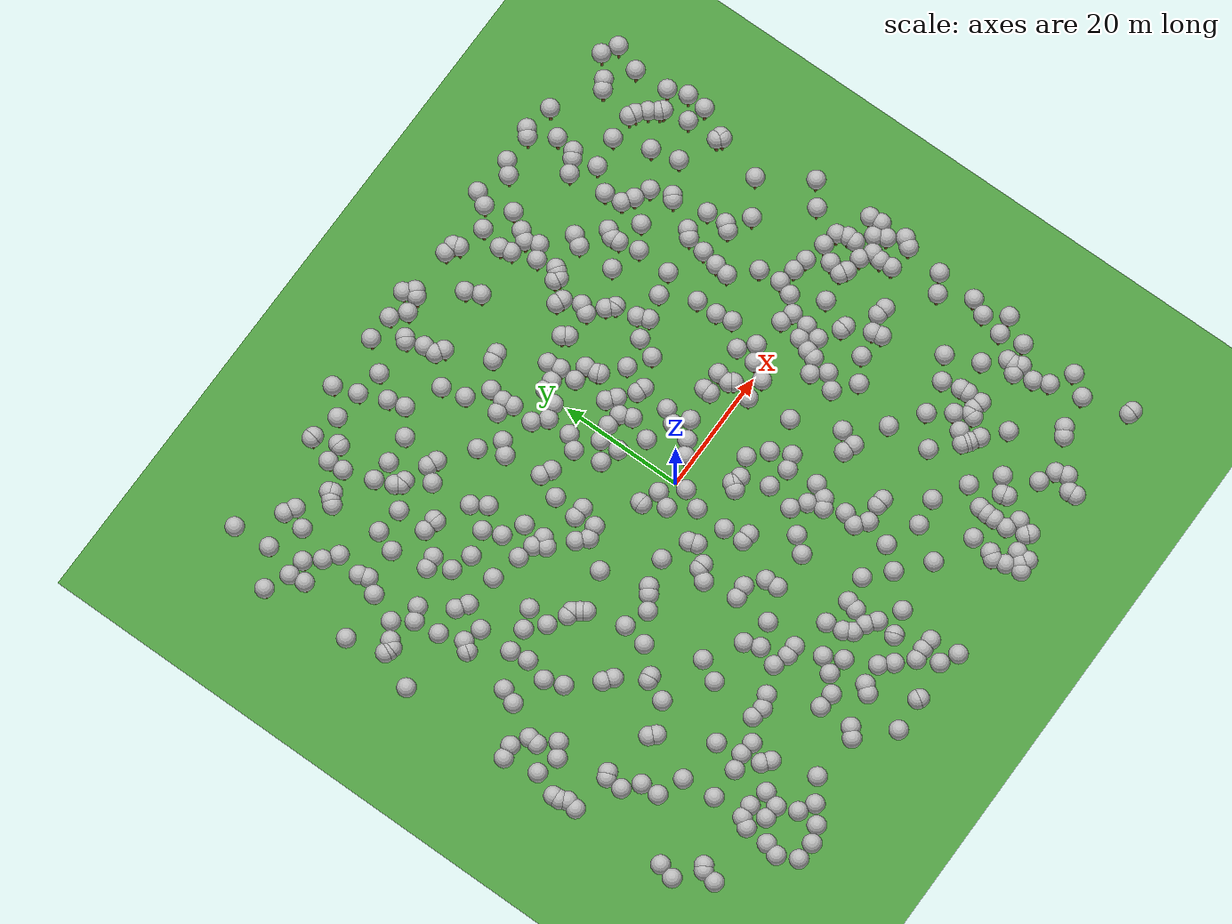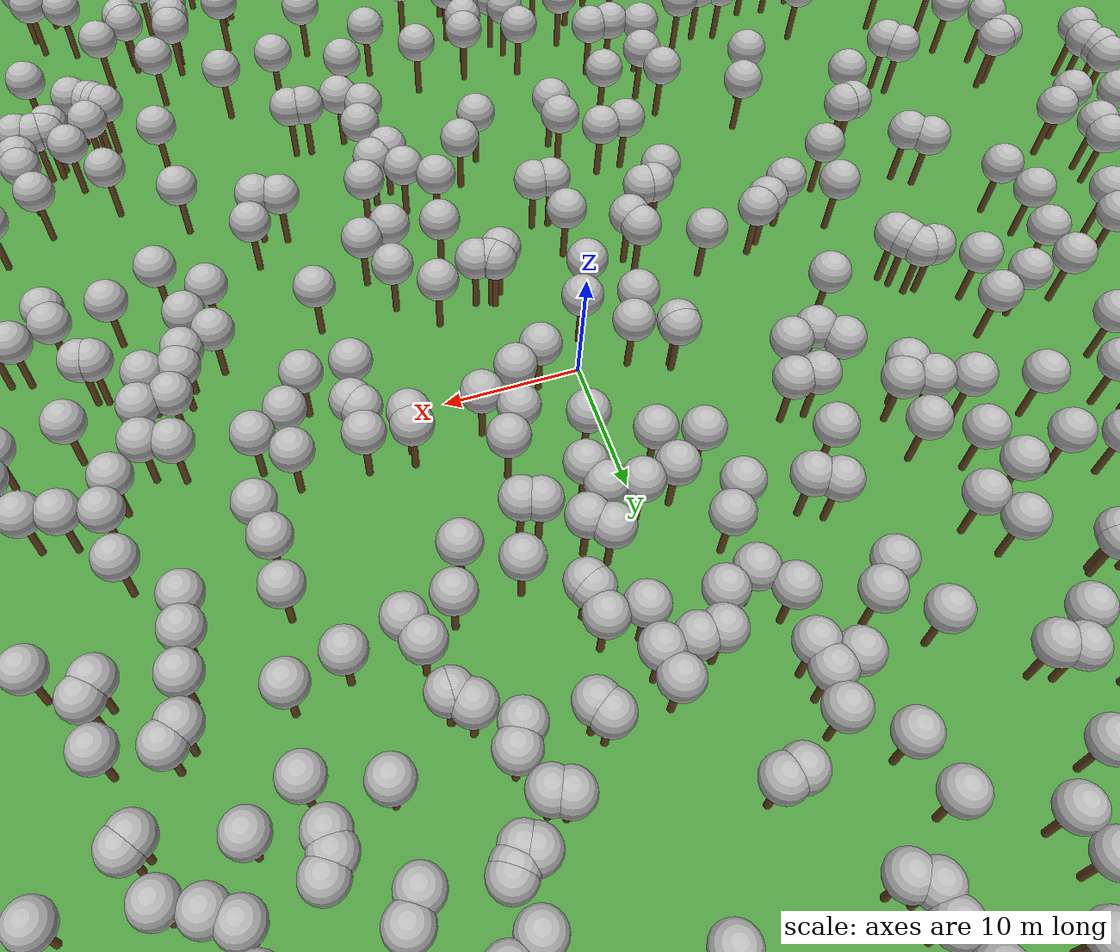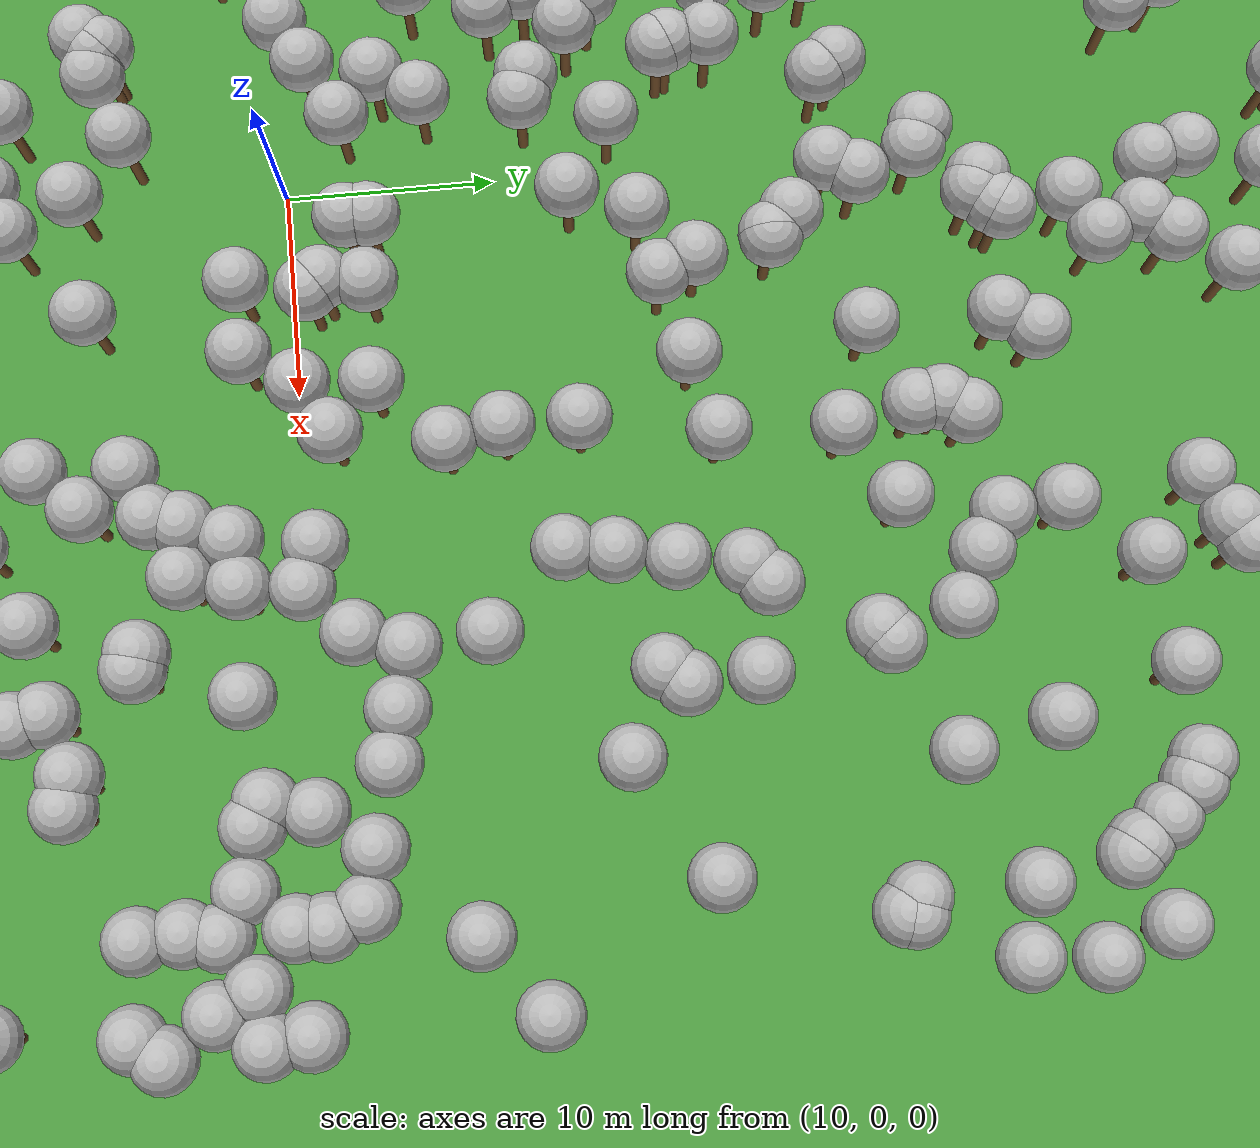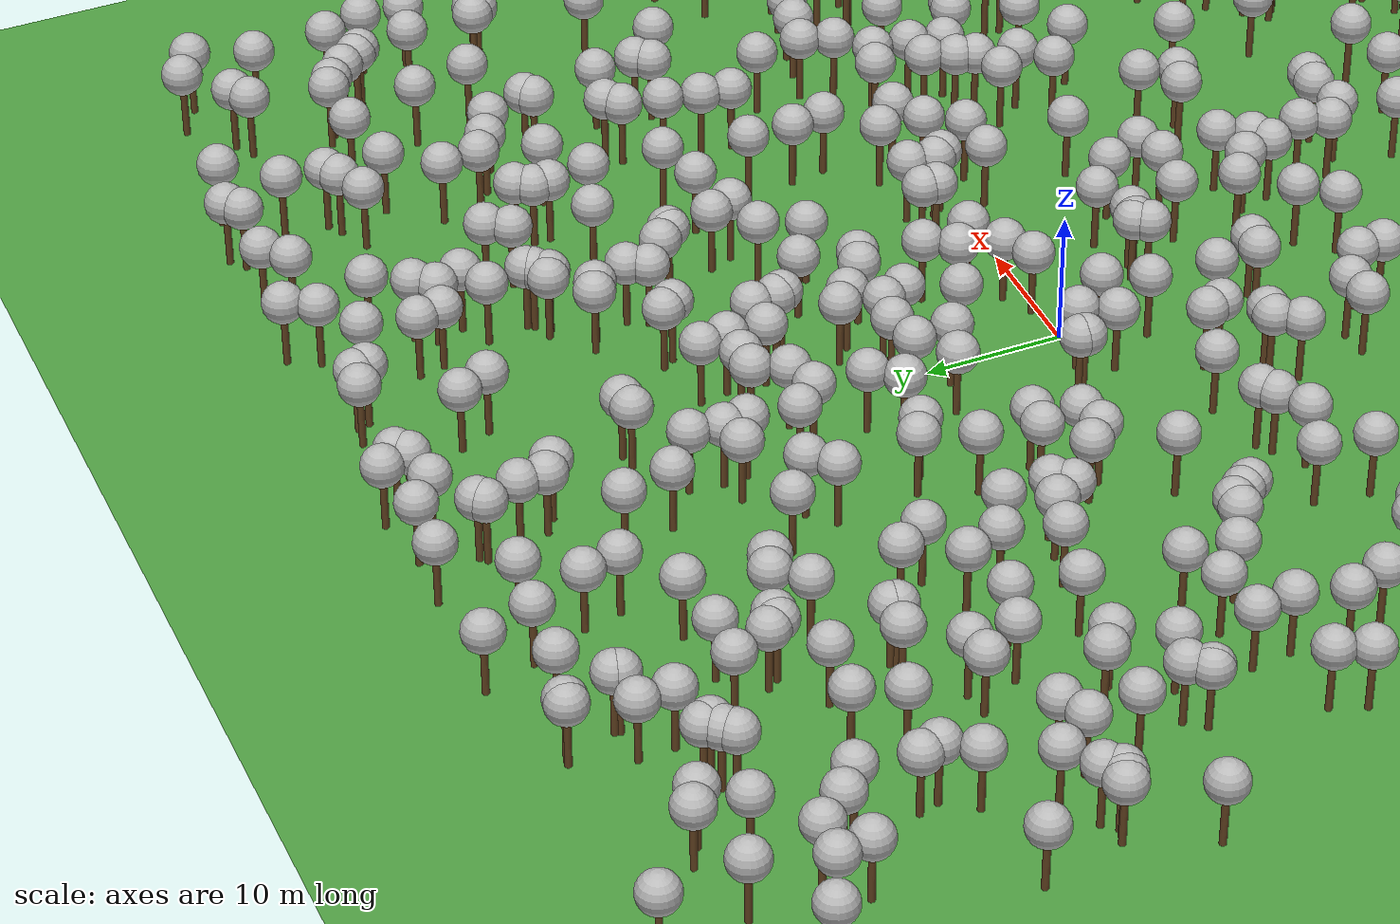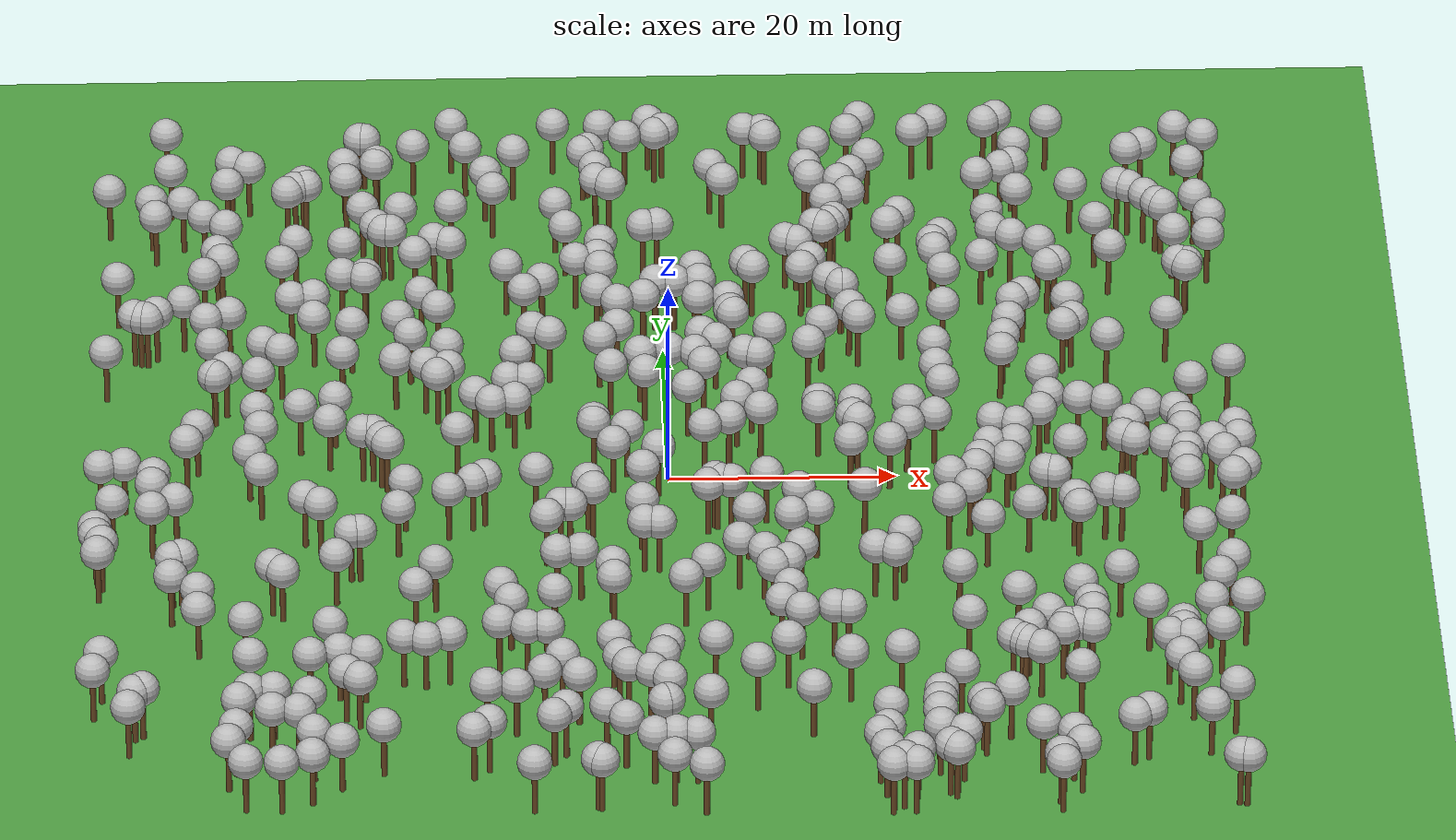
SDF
<?xml version="1.0" ?>
<?xml-model href="http://sdformat.org/schemas/root.xsd" schematypens="http://www.w3.org/2001/XMLSchema"?>
<sdf version="1.4">
  <world name="default">
    <plugin name="mrs_gazebo_static_transform_republisher_plugin" filename="libMrsGazeboCommonResources_StaticTransformRepublisher.so"/>

    <!-- coordinate system {-->
    <spherical_coordinates>
      <surface_model>EARTH_WGS84</surface_model>
      <latitude_deg>47.397743</latitude_deg>
      <longitude_deg>8.545594</longitude_deg>
      <elevation>0.0</elevation>
      <heading_deg>0</heading_deg>
    </spherical_coordinates>

    <physics name="default_physics" default="0" type="ode">
      <gravity>0 0 -9.8066</gravity>
      <ode>
        <solver>
          <type>quick</type>
          <iters>50</iters>
          <sor>1.0</sor>
          <use_dynamic_moi_rescaling>0</use_dynamic_moi_rescaling>
        </solver>
        <constraints>
          <cfm>0</cfm>
          <erp>0.2</erp>
          <contact_max_correcting_vel>1000</contact_max_correcting_vel>
          <contact_surface_layer>0.001</contact_surface_layer>
        </constraints>
      </ode>
      <max_step_size>0.004</max_step_size>
      <real_time_factor>1</real_time_factor>
      <real_time_update_rate>250</real_time_update_rate>
      <magnetic_field>6.0e-06 2.3e-05 -4.2e-05</magnetic_field>
    </physics>

    <scene>
      <shadows>false</shadows>
    </scene>

    <light type="directional" name="sun">
      <cast_shadows>true</cast_shadows>
      <pose>250 250 600 0 0 0</pose>
      <diffuse>0.8 0.8 0.8 1</diffuse>
      <specular>0.2 0.2 0.2 1</specular>
      <attenuation>
        <range>1000</range>
        <constant>0.9</constant>
        <linear>0.01</linear>
        <quadratic>0.001</quadratic>
      </attenuation>
      <direction>0 0 -1</direction>
    </light>

    <!-- Trees {-->
    <model name='tree_simple499'>
      <static>1</static>
      <link name='link'>
        <pose frame=''>0 0 0.1 0 -0 0</pose>
        <collision name='collision_trunk'>
          <pose frame=''>0 0 2 0 -0 0</pose>
          <geometry>
            <cylinder>
              <radius>0.25</radius>
              <length>4</length>
            </cylinder>
          </geometry>
        </collision>
        <collision name='collision_treetop'>
          <pose frame=''>0 0 5.2 0 -0 0</pose>
          <geometry>
            <sphere>
              <radius>1.5</radius>
            </sphere>
          </geometry>
        </collision>
        <visual name='trunk'>
          <pose frame=''>0 0 2 0 -0 0</pose>
          <geometry>
            <cylinder>
              <radius>0.25</radius>
              <length>4</length>
            </cylinder>
          </geometry>
          <material>
            <script>
              <uri>model://tree_simple/scripts</uri>
              <uri>model://tree_simple/materials/textures</uri>
              <name>TreeSimple/Trunk</name>
            </script>
          </material>
        </visual>
        <visual name='treetop'>
          <pose frame=''>0 0 5.2 0 -0 0</pose>
          <geometry>
            <sphere>
              <radius>1.5</radius>
            </sphere>
          </geometry>
          <material>
            <script>
              <uri>model://tree_simple/scripts</uri>
              <uri>model://tree_simple/materials/textures</uri>
              <name>TreeSimple/Treetop</name>
            </script>
          </material>
        </visual>
        <self_collide>0</self_collide>
        <kinematic>0</kinematic>
      </link>
      <pose frame=''>49.5772894431 -0.301033806291 0 0 -0 0</pose>
    </model>

    <model name='tree_simple498'>
      <static>1</static>
      <link name='link'>
        <pose frame=''>0 0 0.1 0 -0 0</pose>
        <collision name='collision_trunk'>
          <pose frame=''>0 0 2 0 -0 0</pose>
          <geometry>
            <cylinder>
              <radius>0.25</radius>
              <length>4</length>
            </cylinder>
          </geometry>
        </collision>
        <collision name='collision_treetop'>
          <pose frame=''>0 0 5.2 0 -0 0</pose>
          <geometry>
            <sphere>
              <radius>1.5</radius>
            </sphere>
          </geometry>
        </collision>
        <visual name='trunk'>
          <pose frame=''>0 0 2 0 -0 0</pose>
          <geometry>
            <cylinder>
              <radius>0.25</radius>
              <length>4</length>
            </cylinder>
          </geometry>
          <material>
            <script>
              <uri>model://tree_simple/scripts</uri>
              <uri>model://tree_simple/materials/textures</uri>
              <name>TreeSimple/Trunk</name>
            </script>
          </material>
        </visual>
        <visual name='treetop'>
          <pose frame=''>0 0 5.2 0 -0 0</pose>
          <geometry>
            <sphere>
              <radius>1.5</radius>
            </sphere>
          </geometry>
          <material>
            <script>
              <uri>model://tree_simple/scripts</uri>
              <uri>model://tree_simple/materials/textures</uri>
              <name>TreeSimple/Treetop</name>
            </script>
          </material>
        </visual>
        <self_collide>0</self_collide>
        <kinematic>0</kinematic>
      </link>
      <pose frame=''>-20.062069779 9.09254194943 0 0 -0 0</pose>
    </model>

    <model name='tree_simple497'>
      <static>1</static>
      <link name='link'>
        <pose frame=''>0 0 0.1 0 -0 0</pose>
        <collision name='collision_trunk'>
          <pose frame=''>0 0 2 0 -0 0</pose>
          <geometry>
            <cylinder>
              <radius>0.25</radius>
              <length>4</length>
            </cylinder>
          </geometry>
        </collision>
        <collision name='collision_treetop'>
          <pose frame=''>0 0 5.2 0 -0 0</pose>
          <geometry>
            <sphere>
              <radius>1.5</radius>
            </sphere>
          </geometry>
        </collision>
        <visual name='trunk'>
          <pose frame=''>0 0 2 0 -0 0</pose>
          <geometry>
            <cylinder>
              <radius>0.25</radius>
              <length>4</length>
            </cylinder>
          </geometry>
          <material>
            <script>
              <uri>model://tree_simple/scripts</uri>
              <uri>model://tree_simple/materials/textures</uri>
              <name>TreeSimple/Trunk</name>
            </script>
          </material>
        </visual>
        <visual name='treetop'>
          <pose frame=''>0 0 5.2 0 -0 0</pose>
          <geometry>
            <sphere>
              <radius>1.5</radius>
            </sphere>
          </geometry>
          <material>
            <script>
              <uri>model://tree_simple/scripts</uri>
              <uri>model://tree_simple/materials/textures</uri>
              <name>TreeSimple/Treetop</name>
            </script>
          </material>
        </visual>
        <self_collide>0</self_collide>
        <kinematic>0</kinematic>
      </link>
      <pose frame=''>16.5730666381 19.0016793819 0 0 -0 0</pose>
    </model>

    <model name='tree_simple496'>
      <static>1</static>
      <link name='link'>
        <pose frame=''>0 0 0.1 0 -0 0</pose>
        <collision name='collision_trunk'>
          <pose frame=''>0 0 2 0 -0 0</pose>
          <geometry>
            <cylinder>
              <radius>0.25</radius>
              <length>4</length>
            </cylinder>
          </geometry>
        </collision>
        <collision name='collision_treetop'>
          <pose frame=''>0 0 5.2 0 -0 0</pose>
          <geometry>
            <sphere>
              <radius>1.5</radius>
            </sphere>
          </geometry>
        </collision>
        <visual name='trunk'>
          <pose frame=''>0 0 2 0 -0 0</pose>
          <geometry>
            <cylinder>
              <radius>0.25</radius>
              <length>4</length>
            </cylinder>
          </geometry>
          <material>
            <script>
              <uri>model://tree_simple/scripts</uri>
              <uri>model://tree_simple/materials/textures</uri>
              <name>TreeSimple/Trunk</name>
            </script>
          </material>
        </visual>
        <visual name='treetop'>
          <pose frame=''>0 0 5.2 0 -0 0</pose>
          <geometry>
            <sphere>
              <radius>1.5</radius>
            </sphere>
          </geometry>
          <material>
            <script>
              <uri>model://tree_simple/scripts</uri>
              <uri>model://tree_simple/materials/textures</uri>
              <name>TreeSimple/Treetop</name>
            </script>
          </material>
        </visual>
        <self_collide>0</self_collide>
        <kinematic>0</kinematic>
      </link>
      <pose frame=''>13.6194298432 -26.9856291803 0 0 -0 0</pose>
    </model>

    <model name='tree_simple495'>
      <static>1</static>
      <link name='link'>
        <pose frame=''>0 0 0.1 0 -0 0</pose>
        <collision name='collision_trunk'>
          <pose frame=''>0 0 2 0 -0 0</pose>
          <geometry>
            <cylinder>
              <radius>0.25</radius>
              <length>4</length>
            </cylinder>
          </geometry>
        </collision>
        <collision name='collision_treetop'>
          <pose frame=''>0 0 5.2 0 -0 0</pose>
          <geometry>
            <sphere>
              <radius>1.5</radius>
            </sphere>
          </geometry>
        </collision>
        <visual name='trunk'>
          <pose frame=''>0 0 2 0 -0 0</pose>
          <geometry>
            <cylinder>
              <radius>0.25</radius>
              <length>4</length>
            </cylinder>
          </geometry>
          <material>
            <script>
              <uri>model://tree_simple/scripts</uri>
              <uri>model://tree_simple/materials/textures</uri>
              <name>TreeSimple/Trunk</name>
            </script>
          </material>
        </visual>
        <visual name='treetop'>
          <pose frame=''>0 0 5.2 0 -0 0</pose>
          <geometry>
            <sphere>
              <radius>1.5</radius>
            </sphere>
          </geometry>
          <material>
            <script>
              <uri>model://tree_simple/scripts</uri>
              <uri>model://tree_simple/materials/textures</uri>
              <name>TreeSimple/Treetop</name>
            </script>
          </material>
        </visual>
        <self_collide>0</self_collide>
        <kinematic>0</kinematic>
      </link>
      <pose frame=''>13.2663357304 3.23501246435 0 0 -0 0</pose>
    </model>

    <model name='tree_simple494'>
      <static>1</static>
      <link name='link'>
        <pose frame=''>0 0 0.1 0 -0 0</pose>
        <collision name='collision_trunk'>
          <pose frame=''>0 0 2 0 -0 0</pose>
          <geometry>
            <cylinder>
              <radius>0.25</radius>
              <length>4</length>
            </cylinder>
          </geometry>
        </collision>
        <collision name='collision_treetop'>
          <pose frame=''>0 0 5.2 0 -0 0</pose>
          <geometry>
            <sphere>
              <radius>1.5</radius>
            </sphere>
          </geometry>
        </collision>
        <visual name='trunk'>
          <pose frame=''>0 0 2 0 -0 0</pose>
          <geometry>
            <cylinder>
              <radius>0.25</radius>
              <length>4</length>
            </cylinder>
          </geometry>
          <material>
            <script>
              <uri>model://tree_simple/scripts</uri>
              <uri>model://tree_simple/materials/textures</uri>
              <name>TreeSimple/Trunk</name>
            </script>
          </material>
        </visual>
        <visual name='treetop'>
          <pose frame=''>0 0 5.2 0 -0 0</pose>
          <geometry>
            <sphere>
              <radius>1.5</radius>
            </sphere>
          </geometry>
          <material>
            <script>
              <uri>model://tree_simple/scripts</uri>
              <uri>model://tree_simple/materials/textures</uri>
              <name>TreeSimple/Treetop</name>
            </script>
          </material>
        </visual>
        <self_collide>0</self_collide>
        <kinematic>0</kinematic>
      </link>
      <pose frame=''>39.6521252177 -42.647901406 0 0 -0 0</pose>
    </model>

    <model name='tree_simple493'>
      <static>1</static>
      <link name='link'>
        <pose frame=''>0 0 0.1 0 -0 0</pose>
        <collision name='collision_trunk'>
          <pose frame=''>0 0 2 0 -0 0</pose>
          <geometry>
            <cylinder>
              <radius>0.25</radius>
              <length>4</length>
            </cylinder>
          </geometry>
        </collision>
        <collision name='collision_treetop'>
          <pose frame=''>0 0 5.2 0 -0 0</pose>
          <geometry>
            <sphere>
              <radius>1.5</radius>
            </sphere>
          </geometry>
        </collision>
        <visual name='trunk'>
          <pose frame=''>0 0 2 0 -0 0</pose>
          <geometry>
            <cylinder>
              <radius>0.25</radius>
              <length>4</length>
            </cylinder>
          </geometry>
          <material>
            <script>
              <uri>model://tree_simple/scripts</uri>
              <uri>model://tree_simple/materials/textures</uri>
              <name>TreeSimple/Trunk</name>
            </script>
          </material>
        </visual>
        <visual name='treetop'>
          <pose frame=''>0 0 5.2 0 -0 0</pose>
          <geometry>
            <sphere>
              <radius>1.5</radius>
            </sphere>
          </geometry>
          <material>
            <script>
              <uri>model://tree_simple/scripts</uri>
              <uri>model://tree_simple/materials/textures</uri>
              <name>TreeSimple/Treetop</name>
            </script>
          </material>
        </visual>
        <self_collide>0</self_collide>
        <kinematic>0</kinematic>
      </link>
      <pose frame=''>-30.9686104206 18.3944298941 0 0 -0 0</pose>
    </model>

    <model name='tree_simple492'>
      <static>1</static>
      <link name='link'>
        <pose frame=''>0 0 0.1 0 -0 0</pose>
        <collision name='collision_trunk'>
          <pose frame=''>0 0 2 0 -0 0</pose>
          <geometry>
            <cylinder>
              <radius>0.25</radius>
              <length>4</length>
            </cylinder>
          </geometry>
        </collision>
        <collision name='collision_treetop'>
          <pose frame=''>0 0 5.2 0 -0 0</pose>
          <geometry>
            <sphere>
              <radius>1.5</radius>
            </sphere>
          </geometry>
        </collision>
        <visual name='trunk'>
          <pose frame=''>0 0 2 0 -0 0</pose>
          <geometry>
            <cylinder>
              <radius>0.25</radius>
              <length>4</length>
            </cylinder>
          </geometry>
          <material>
            <script>
              <uri>model://tree_simple/scripts</uri>
              <uri>model://tree_simple/materials/textures</uri>
              <name>TreeSimple/Trunk</name>
            </script>
          </material>
        </visual>
        <visual name='treetop'>
          <pose frame=''>0 0 5.2 0 -0 0</pose>
          <geometry>
            <sphere>
              <radius>1.5</radius>
            </sphere>
          </geometry>
          <material>
            <script>
              <uri>model://tree_simple/scripts</uri>
              <uri>model://tree_simple/materials/textures</uri>
              <name>TreeSimple/Treetop</name>
            </script>
          </material>
        </visual>
        <self_collide>0</self_collide>
        <kinematic>0</kinematic>
      </link>
      <pose frame=''>-7.60604313382 27.1336498888 0 0 -0 0</pose>
    </model>

    <model name='tree_simple491'>
      <static>1</static>
      <link name='link'>
        <pose frame=''>0 0 0.1 0 -0 0</pose>
        <collision name='collision_trunk'>
          <pose frame=''>0 0 2 0 -0 0</pose>
          <geometry>
            <cylinder>
              <radius>0.25</radius>
              <length>4</length>
            </cylinder>
          </geometry>
        </collision>
        <collision name='collision_treetop'>
          <pose frame=''>0 0 5.2 0 -0 0</pose>
          <geometry>
            <sphere>
              <radius>1.5</radius>
            </sphere>
          </geometry>
        </collision>
        <visual name='trunk'>
          <pose frame=''>0 0 2 0 -0 0</pose>
          <geometry>
            <cylinder>
              <radius>0.25</radius>
              <length>4</length>
            </cylinder>
          </geometry>
          <material>
            <script>
              <uri>model://tree_simple/scripts</uri>
              <uri>model://tree_simple/materials/textures</uri>
              <name>TreeSimple/Trunk</name>
            </script>
          </material>
        </visual>
        <visual name='treetop'>
          <pose frame=''>0 0 5.2 0 -0 0</pose>
          <geometry>
            <sphere>
              <radius>1.5</radius>
            </sphere>
          </geometry>
          <material>
            <script>
              <uri>model://tree_simple/scripts</uri>
              <uri>model://tree_simple/materials/textures</uri>
              <name>TreeSimple/Treetop</name>
            </script>
          </material>
        </visual>
        <self_collide>0</self_collide>
        <kinematic>0</kinematic>
      </link>
      <pose frame=''>-12.3902503735 -49.1082665042 0 0 -0 0</pose>
    </model>

    <model name='tree_simple490'>
      <static>1</static>
      <link name='link'>
        <pose frame=''>0 0 0.1 0 -0 0</pose>
        <collision name='collision_trunk'>
          <pose frame=''>0 0 2 0 -0 0</pose>
          <geometry>
            <cylinder>
              <radius>0.25</radius>
              <length>4</length>
            </cylinder>
          </geometry>
        </collision>
        <collision name='collision_treetop'>
          <pose frame=''>0 0 5.2 0 -0 0</pose>
          <geometry>
            <sphere>
              <radius>1.5</radius>
            </sphere>
          </geometry>
        </collision>
        <visual name='trunk'>
          <pose frame=''>0 0 2 0 -0 0</pose>
          <geometry>
            <cylinder>
              <radius>0.25</radius>
              <length>4</length>
            </cylinder>
          </geometry>
          <material>
            <script>
              <uri>model://tree_simple/scripts</uri>
              <uri>model://tree_simple/materials/textures</uri>
              <name>TreeSimple/Trunk</name>
            </script>
          </material>
        </visual>
        <visual name='treetop'>
          <pose frame=''>0 0 5.2 0 -0 0</pose>
          <geometry>
            <sphere>
              <radius>1.5</radius>
            </sphere>
          </geometry>
          <material>
            <script>
              <uri>model://tree_simple/scripts</uri>
              <uri>model://tree_simple/materials/textures</uri>
              <name>TreeSimple/Treetop</name>
            </script>
          </material>
        </visual>
        <self_collide>0</self_collide>
        <kinematic>0</kinematic>
      </link>
      <pose frame=''>28.486302093 0.994684244644 0 0 -0 0</pose>
    </model>

    <model name='tree_simple489'>
      <static>1</static>
      <link name='link'>
        <pose frame=''>0 0 0.1 0 -0 0</pose>
        <collision name='collision_trunk'>
          <pose frame=''>0 0 2 0 -0 0</pose>
          <geometry>
            <cylinder>
              <radius>0.25</radius>
              <length>4</length>
            </cylinder>
          </geometry>
        </collision>
        <collision name='collision_treetop'>
          <pose frame=''>0 0 5.2 0 -0 0</pose>
          <geometry>
            <sphere>
              <radius>1.5</radius>
            </sphere>
          </geometry>
        </collision>
        <visual name='trunk'>
          <pose frame=''>0 0 2 0 -0 0</pose>
          <geometry>
            <cylinder>
              <radius>0.25</radius>
              <length>4</length>
            </cylinder>
          </geometry>
          <material>
            <script>
              <uri>model://tree_simple/scripts</uri>
              <uri>model://tree_simple/materials/textures</uri>
              <name>TreeSimple/Trunk</name>
            </script>
          </material>
        </visual>
        <visual name='treetop'>
          <pose frame=''>0 0 5.2 0 -0 0</pose>
          <geometry>
            <sphere>
              <radius>1.5</radius>
            </sphere>
          </geometry>
          <material>
            <script>
              <uri>model://tree_simple/scripts</uri>
              <uri>model://tree_simple/materials/textures</uri>
              <name>TreeSimple/Treetop</name>
            </script>
          </material>
        </visual>
        <self_collide>0</self_collide>
        <kinematic>0</kinematic>
      </link>
      <pose frame=''>-32.6634579524 39.3278172931 0 0 -0 0</pose>
    </model>

    <model name='tree_simple488'>
      <static>1</static>
      <link name='link'>
        <pose frame=''>0 0 0.1 0 -0 0</pose>
        <collision name='collision_trunk'>
          <pose frame=''>0 0 2 0 -0 0</pose>
          <geometry>
            <cylinder>
              <radius>0.25</radius>
              <length>4</length>
            </cylinder>
          </geometry>
        </collision>
        <collision name='collision_treetop'>
          <pose frame=''>0 0 5.2 0 -0 0</pose>
          <geometry>
            <sphere>
              <radius>1.5</radius>
            </sphere>
          </geometry>
        </collision>
        <visual name='trunk'>
          <pose frame=''>0 0 2 0 -0 0</pose>
          <geometry>
            <cylinder>
              <radius>0.25</radius>
              <length>4</length>
            </cylinder>
          </geometry>
          <material>
            <script>
              <uri>model://tree_simple/scripts</uri>
              <uri>model://tree_simple/materials/textures</uri>
              <name>TreeSimple/Trunk</name>
            </script>
          </material>
        </visual>
        <visual name='treetop'>
          <pose frame=''>0 0 5.2 0 -0 0</pose>
          <geometry>
            <sphere>
              <radius>1.5</radius>
            </sphere>
          </geometry>
          <material>
            <script>
              <uri>model://tree_simple/scripts</uri>
              <uri>model://tree_simple/materials/textures</uri>
              <name>TreeSimple/Treetop</name>
            </script>
          </material>
        </visual>
        <self_collide>0</self_collide>
        <kinematic>0</kinematic>
      </link>
      <pose frame=''>-13.1215818691 12.435953241 0 0 -0 0</pose>
    </model>

    <model name='tree_simple487'>
      <static>1</static>
      <link name='link'>
        <pose frame=''>0 0 0.1 0 -0 0</pose>
        <collision name='collision_trunk'>
          <pose frame=''>0 0 2 0 -0 0</pose>
          <geometry>
            <cylinder>
              <radius>0.25</radius>
              <length>4</length>
            </cylinder>
          </geometry>
        </collision>
        <collision name='collision_treetop'>
          <pose frame=''>0 0 5.2 0 -0 0</pose>
          <geometry>
            <sphere>
              <radius>1.5</radius>
            </sphere>
          </geometry>
        </collision>
        <visual name='trunk'>
          <pose frame=''>0 0 2 0 -0 0</pose>
          <geometry>
            <cylinder>
              <radius>0.25</radius>
              <length>4</length>
            </cylinder>
          </geometry>
          <material>
            <script>
              <uri>model://tree_simple/scripts</uri>
              <uri>model://tree_simple/materials/textures</uri>
              <name>TreeSimple/Trunk</name>
            </script>
          </material>
        </visual>
        <visual name='treetop'>
          <pose frame=''>0 0 5.2 0 -0 0</pose>
          <geometry>
            <sphere>
              <radius>1.5</radius>
            </sphere>
          </geometry>
          <material>
            <script>
              <uri>model://tree_simple/scripts</uri>
              <uri>model://tree_simple/materials/textures</uri>
              <name>TreeSimple/Treetop</name>
            </script>
          </material>
        </visual>
        <self_collide>0</self_collide>
        <kinematic>0</kinematic>
      </link>
      <pose frame=''>33.1280168764 8.35331864597 0 0 -0 0</pose>
    </model>

    <model name='tree_simple486'>
      <static>1</static>
      <link name='link'>
        <pose frame=''>0 0 0.1 0 -0 0</pose>
        <collision name='collision_trunk'>
          <pose frame=''>0 0 2 0 -0 0</pose>
          <geometry>
            <cylinder>
              <radius>0.25</radius>
              <length>4</length>
            </cylinder>
          </geometry>
        </collision>
        <collision name='collision_treetop'>
          <pose frame=''>0 0 5.2 0 -0 0</pose>
          <geometry>
            <sphere>
              <radius>1.5</radius>
            </sphere>
          </geometry>
        </collision>
        <visual name='trunk'>
          <pose frame=''>0 0 2 0 -0 0</pose>
          <geometry>
            <cylinder>
              <radius>0.25</radius>
              <length>4</length>
            </cylinder>
          </geometry>
          <material>
            <script>
              <uri>model://tree_simple/scripts</uri>
              <uri>model://tree_simple/materials/textures</uri>
              <name>TreeSimple/Trunk</name>
            </script>
          </material>
        </visual>
        <visual name='treetop'>
          <pose frame=''>0 0 5.2 0 -0 0</pose>
          <geometry>
            <sphere>
              <radius>1.5</radius>
            </sphere>
          </geometry>
          <material>
            <script>
              <uri>model://tree_simple/scripts</uri>
              <uri>model://tree_simple/materials/textures</uri>
              <name>TreeSimple/Treetop</name>
            </script>
          </material>
        </visual>
        <self_collide>0</self_collide>
        <kinematic>0</kinematic>
      </link>
      <pose frame=''>8.18281559396 11.6524151823 0 0 -0 0</pose>
    </model>

    <model name='tree_simple485'>
      <static>1</static>
      <link name='link'>
        <pose frame=''>0 0 0.1 0 -0 0</pose>
        <collision name='collision_trunk'>
          <pose frame=''>0 0 2 0 -0 0</pose>
          <geometry>
            <cylinder>
              <radius>0.25</radius>
              <length>4</length>
            </cylinder>
          </geometry>
        </collision>
        <collision name='collision_treetop'>
          <pose frame=''>0 0 5.2 0 -0 0</pose>
          <geometry>
            <sphere>
              <radius>1.5</radius>
            </sphere>
          </geometry>
        </collision>
        <visual name='trunk'>
          <pose frame=''>0 0 2 0 -0 0</pose>
          <geometry>
            <cylinder>
              <radius>0.25</radius>
              <length>4</length>
            </cylinder>
          </geometry>
          <material>
            <script>
              <uri>model://tree_simple/scripts</uri>
              <uri>model://tree_simple/materials/textures</uri>
              <name>TreeSimple/Trunk</name>
            </script>
          </material>
        </visual>
        <visual name='treetop'>
          <pose frame=''>0 0 5.2 0 -0 0</pose>
          <geometry>
            <sphere>
              <radius>1.5</radius>
            </sphere>
          </geometry>
          <material>
            <script>
              <uri>model://tree_simple/scripts</uri>
              <uri>model://tree_simple/materials/textures</uri>
              <name>TreeSimple/Treetop</name>
            </script>
          </material>
        </visual>
        <self_collide>0</self_collide>
        <kinematic>0</kinematic>
      </link>
      <pose frame=''>38.4673421664 3.60529435805 0 0 -0 0</pose>
    </model>

    <model name='tree_simple484'>
      <static>1</static>
      <link name='link'>
        <pose frame=''>0 0 0.1 0 -0 0</pose>
        <collision name='collision_trunk'>
          <pose frame=''>0 0 2 0 -0 0</pose>
          <geometry>
            <cylinder>
              <radius>0.25</radius>
              <length>4</length>
            </cylinder>
          </geometry>
        </collision>
        <collision name='collision_treetop'>
          <pose frame=''>0 0 5.2 0 -0 0</pose>
          <geometry>
            <sphere>
              <radius>1.5</radius>
            </sphere>
          </geometry>
        </collision>
        <visual name='trunk'>
          <pose frame=''>0 0 2 0 -0 0</pose>
          <geometry>
            <cylinder>
              <radius>0.25</radius>
              <length>4</length>
            </cylinder>
          </geometry>
          <material>
            <script>
              <uri>model://tree_simple/scripts</uri>
              <uri>model://tree_simple/materials/textures</uri>
              <name>TreeSimple/Trunk</name>
            </script>
          </material>
        </visual>
        <visual name='treetop'>
          <pose frame=''>0 0 5.2 0 -0 0</pose>
          <geometry>
            <sphere>
              <radius>1.5</radius>
            </sphere>
          </geometry>
          <material>
            <script>
              <uri>model://tree_simple/scripts</uri>
              <uri>model://tree_simple/materials/textures</uri>
              <name>TreeSimple/Treetop</name>
            </script>
          </material>
        </visual>
        <self_collide>0</self_collide>
        <kinematic>0</kinematic>
      </link>
      <pose frame=''>19.8605088225 -47.9062304077 0 0 -0 0</pose>
    </model>

    <model name='tree_simple483'>
      <static>1</static>
      <link name='link'>
        <pose frame=''>0 0 0.1 0 -0 0</pose>
        <collision name='collision_trunk'>
          <pose frame=''>0 0 2 0 -0 0</pose>
          <geometry>
            <cylinder>
              <radius>0.25</radius>
              <length>4</length>
            </cylinder>
          </geometry>
        </collision>
        <collision name='collision_treetop'>
          <pose frame=''>0 0 5.2 0 -0 0</pose>
          <geometry>
            <sphere>
              <radius>1.5</radius>
            </sphere>
          </geometry>
        </collision>
        <visual name='trunk'>
          <pose frame=''>0 0 2 0 -0 0</pose>
          <geometry>
            <cylinder>
              <radius>0.25</radius>
              <length>4</length>
            </cylinder>
          </geometry>
          <material>
            <script>
              <uri>model://tree_simple/scripts</uri>
              <uri>model://tree_simple/materials/textures</uri>
              <name>TreeSimple/Trunk</name>
            </script>
          </material>
        </visual>
        <visual name='treetop'>
          <pose frame=''>0 0 5.2 0 -0 0</pose>
          <geometry>
            <sphere>
              <radius>1.5</radius>
            </sphere>
          </geometry>
          <material>
            <script>
              <uri>model://tree_simple/scripts</uri>
              <uri>model://tree_simple/materials/textures</uri>
              <name>TreeSimple/Treetop</name>
            </script>
          </material>
        </visual>
        <self_collide>0</self_collide>
        <kinematic>0</kinematic>
      </link>
      <pose frame=''>-6.65162129766 44.7613363002 0 0 -0 0</pose>
    </model>

    <model name='tree_simple482'>
      <static>1</static>
      <link name='link'>
        <pose frame=''>0 0 0.1 0 -0 0</pose>
        <collision name='collision_trunk'>
          <pose frame=''>0 0 2 0 -0 0</pose>
          <geometry>
            <cylinder>
              <radius>0.25</radius>
              <length>4</length>
            </cylinder>
          </geometry>
        </collision>
        <collision name='collision_treetop'>
          <pose frame=''>0 0 5.2 0 -0 0</pose>
          <geometry>
            <sphere>
              <radius>1.5</radius>
            </sphere>
          </geometry>
        </collision>
        <visual name='trunk'>
          <pose frame=''>0 0 2 0 -0 0</pose>
          <geometry>
            <cylinder>
              <radius>0.25</radius>
              <length>4</length>
            </cylinder>
          </geometry>
          <material>
            <script>
              <uri>model://tree_simple/scripts</uri>
              <uri>model://tree_simple/materials/textures</uri>
              <name>TreeSimple/Trunk</name>
            </script>
          </material>
        </visual>
        <visual name='treetop'>
          <pose frame=''>0 0 5.2 0 -0 0</pose>
          <geometry>
            <sphere>
              <radius>1.5</radius>
            </sphere>
          </geometry>
          <material>
            <script>
              <uri>model://tree_simple/scripts</uri>
              <uri>model://tree_simple/materials/textures</uri>
              <name>TreeSimple/Treetop</name>
            </script>
          </material>
        </visual>
        <self_collide>0</self_collide>
        <kinematic>0</kinematic>
      </link>
      <pose frame=''>-31.7137183406 39.6850484597 0 0 -0 0</pose>
    </model>

    <model name='tree_simple481'>
      <static>1</static>
      <link name='link'>
        <pose frame=''>0 0 0.1 0 -0 0</pose>
        <collision name='collision_trunk'>
          <pose frame=''>0 0 2 0 -0 0</pose>
          <geometry>
            <cylinder>
              <radius>0.25</radius>
              <length>4</length>
            </cylinder>
          </geometry>
        </collision>
        <collision name='collision_treetop'>
          <pose frame=''>0 0 5.2 0 -0 0</pose>
          <geometry>
            <sphere>
              <radius>1.5</radius>
            </sphere>
          </geometry>
        </collision>
        <visual name='trunk'>
          <pose frame=''>0 0 2 0 -0 0</pose>
          <geometry>
            <cylinder>
              <radius>0.25</radius>
              <length>4</length>
            </cylinder>
          </geometry>
          <material>
            <script>
              <uri>model://tree_simple/scripts</uri>
              <uri>model://tree_simple/materials/textures</uri>
              <name>TreeSimple/Trunk</name>
            </script>
          </material>
        </visual>
        <visual name='treetop'>
          <pose frame=''>0 0 5.2 0 -0 0</pose>
          <geometry>
            <sphere>
              <radius>1.5</radius>
            </sphere>
          </geometry>
          <material>
            <script>
              <uri>model://tree_simple/scripts</uri>
              <uri>model://tree_simple/materials/textures</uri>
              <name>TreeSimple/Treetop</name>
            </script>
          </material>
        </visual>
        <self_collide>0</self_collide>
        <kinematic>0</kinematic>
      </link>
      <pose frame=''>-37.2553351017 -39.4739685818 0 0 -0 0</pose>
    </model>

    <model name='tree_simple480'>
      <static>1</static>
      <link name='link'>
        <pose frame=''>0 0 0.1 0 -0 0</pose>
        <collision name='collision_trunk'>
          <pose frame=''>0 0 2 0 -0 0</pose>
          <geometry>
            <cylinder>
              <radius>0.25</radius>
              <length>4</length>
            </cylinder>
          </geometry>
        </collision>
        <collision name='collision_treetop'>
          <pose frame=''>0 0 5.2 0 -0 0</pose>
          <geometry>
            <sphere>
              <radius>1.5</radius>
            </sphere>
          </geometry>
        </collision>
        <visual name='trunk'>
          <pose frame=''>0 0 2 0 -0 0</pose>
          <geometry>
            <cylinder>
              <radius>0.25</radius>
              <length>4</length>
            </cylinder>
          </geometry>
          <material>
            <script>
              <uri>model://tree_simple/scripts</uri>
              <uri>model://tree_simple/materials/textures</uri>
              <name>TreeSimple/Trunk</name>
            </script>
          </material>
        </visual>
        <visual name='treetop'>
          <pose frame=''>0 0 5.2 0 -0 0</pose>
          <geometry>
            <sphere>
              <radius>1.5</radius>
            </sphere>
          </geometry>
          <material>
            <script>
              <uri>model://tree_simple/scripts</uri>
              <uri>model://tree_simple/materials/textures</uri>
              <name>TreeSimple/Treetop</name>
            </script>
          </material>
        </visual>
        <self_collide>0</self_collide>
        <kinematic>0</kinematic>
      </link>
      <pose frame=''>-2.16211412072 12.1351070175 0 0 -0 0</pose>
    </model>

    <model name='tree_simple479'>
      <static>1</static>
      <link name='link'>
        <pose frame=''>0 0 0.1 0 -0 0</pose>
        <collision name='collision_trunk'>
          <pose frame=''>0 0 2 0 -0 0</pose>
          <geometry>
            <cylinder>
              <radius>0.25</radius>
              <length>4</length>
            </cylinder>
          </geometry>
        </collision>
        <collision name='collision_treetop'>
          <pose frame=''>0 0 5.2 0 -0 0</pose>
          <geometry>
            <sphere>
              <radius>1.5</radius>
            </sphere>
          </geometry>
        </collision>
        <visual name='trunk'>
          <pose frame=''>0 0 2 0 -0 0</pose>
          <geometry>
            <cylinder>
              <radius>0.25</radius>
              <length>4</length>
            </cylinder>
          </geometry>
          <material>
            <script>
              <uri>model://tree_simple/scripts</uri>
              <uri>model://tree_simple/materials/textures</uri>
              <name>TreeSimple/Trunk</name>
            </script>
          </material>
        </visual>
        <visual name='treetop'>
          <pose frame=''>0 0 5.2 0 -0 0</pose>
          <geometry>
            <sphere>
              <radius>1.5</radius>
            </sphere>
          </geometry>
          <material>
            <script>
              <uri>model://tree_simple/scripts</uri>
              <uri>model://tree_simple/materials/textures</uri>
              <name>TreeSimple/Treetop</name>
            </script>
          </material>
        </visual>
        <self_collide>0</self_collide>
        <kinematic>0</kinematic>
      </link>
      <pose frame=''>-12.2778199556 22.3020251283 0 0 -0 0</pose>
    </model>

    <model name='tree_simple478'>
      <static>1</static>
      <link name='link'>
        <pose frame=''>0 0 0.1 0 -0 0</pose>
        <collision name='collision_trunk'>
          <pose frame=''>0 0 2 0 -0 0</pose>
          <geometry>
            <cylinder>
              <radius>0.25</radius>
              <length>4</length>
            </cylinder>
          </geometry>
        </collision>
        <collision name='collision_treetop'>
          <pose frame=''>0 0 5.2 0 -0 0</pose>
          <geometry>
            <sphere>
              <radius>1.5</radius>
            </sphere>
          </geometry>
        </collision>
        <visual name='trunk'>
          <pose frame=''>0 0 2 0 -0 0</pose>
          <geometry>
            <cylinder>
              <radius>0.25</radius>
              <length>4</length>
            </cylinder>
          </geometry>
          <material>
            <script>
              <uri>model://tree_simple/scripts</uri>
              <uri>model://tree_simple/materials/textures</uri>
              <name>TreeSimple/Trunk</name>
            </script>
          </material>
        </visual>
        <visual name='treetop'>
          <pose frame=''>0 0 5.2 0 -0 0</pose>
          <geometry>
            <sphere>
              <radius>1.5</radius>
            </sphere>
          </geometry>
          <material>
            <script>
              <uri>model://tree_simple/scripts</uri>
              <uri>model://tree_simple/materials/textures</uri>
              <name>TreeSimple/Treetop</name>
            </script>
          </material>
        </visual>
        <self_collide>0</self_collide>
        <kinematic>0</kinematic>
      </link>
      <pose frame=''>6.74093075138 -12.3162984353 0 0 -0 0</pose>
    </model>

    <model name='tree_simple477'>
      <static>1</static>
      <link name='link'>
        <pose frame=''>0 0 0.1 0 -0 0</pose>
        <collision name='collision_trunk'>
          <pose frame=''>0 0 2 0 -0 0</pose>
          <geometry>
            <cylinder>
              <radius>0.25</radius>
              <length>4</length>
            </cylinder>
          </geometry>
        </collision>
        <collision name='collision_treetop'>
          <pose frame=''>0 0 5.2 0 -0 0</pose>
          <geometry>
            <sphere>
              <radius>1.5</radius>
            </sphere>
          </geometry>
        </collision>
        <visual name='trunk'>
          <pose frame=''>0 0 2 0 -0 0</pose>
          <geometry>
            <cylinder>
              <radius>0.25</radius>
              <length>4</length>
            </cylinder>
          </geometry>
          <material>
            <script>
              <uri>model://tree_simple/scripts</uri>
              <uri>model://tree_simple/materials/textures</uri>
              <name>TreeSimple/Trunk</name>
            </script>
          </material>
        </visual>
        <visual name='treetop'>
          <pose frame=''>0 0 5.2 0 -0 0</pose>
          <geometry>
            <sphere>
              <radius>1.5</radius>
            </sphere>
          </geometry>
          <material>
            <script>
              <uri>model://tree_simple/scripts</uri>
              <uri>model://tree_simple/materials/textures</uri>
              <name>TreeSimple/Treetop</name>
            </script>
          </material>
        </visual>
        <self_collide>0</self_collide>
        <kinematic>0</kinematic>
      </link>
      <pose frame=''>-0.22927085135 32.6495918535 0 0 -0 0</pose>
    </model>

    <model name='tree_simple476'>
      <static>1</static>
      <link name='link'>
        <pose frame=''>0 0 0.1 0 -0 0</pose>
        <collision name='collision_trunk'>
          <pose frame=''>0 0 2 0 -0 0</pose>
          <geometry>
            <cylinder>
              <radius>0.25</radius>
              <length>4</length>
            </cylinder>
          </geometry>
        </collision>
        <collision name='collision_treetop'>
          <pose frame=''>0 0 5.2 0 -0 0</pose>
          <geometry>
            <sphere>
              <radius>1.5</radius>
            </sphere>
          </geometry>
        </collision>
        <visual name='trunk'>
          <pose frame=''>0 0 2 0 -0 0</pose>
          <geometry>
            <cylinder>
              <radius>0.25</radius>
              <length>4</length>
            </cylinder>
          </geometry>
          <material>
            <script>
              <uri>model://tree_simple/scripts</uri>
              <uri>model://tree_simple/materials/textures</uri>
              <name>TreeSimple/Trunk</name>
            </script>
          </material>
        </visual>
        <visual name='treetop'>
          <pose frame=''>0 0 5.2 0 -0 0</pose>
          <geometry>
            <sphere>
              <radius>1.5</radius>
            </sphere>
          </geometry>
          <material>
            <script>
              <uri>model://tree_simple/scripts</uri>
              <uri>model://tree_simple/materials/textures</uri>
              <name>TreeSimple/Treetop</name>
            </script>
          </material>
        </visual>
        <self_collide>0</self_collide>
        <kinematic>0</kinematic>
      </link>
      <pose frame=''>-40.490555579 18.243153787 0 0 -0 0</pose>
    </model>

    <model name='tree_simple475'>
      <static>1</static>
      <link name='link'>
        <pose frame=''>0 0 0.1 0 -0 0</pose>
        <collision name='collision_trunk'>
          <pose frame=''>0 0 2 0 -0 0</pose>
          <geometry>
            <cylinder>
              <radius>0.25</radius>
              <length>4</length>
            </cylinder>
          </geometry>
        </collision>
        <collision name='collision_treetop'>
          <pose frame=''>0 0 5.2 0 -0 0</pose>
          <geometry>
            <sphere>
              <radius>1.5</radius>
            </sphere>
          </geometry>
        </collision>
        <visual name='trunk'>
          <pose frame=''>0 0 2 0 -0 0</pose>
          <geometry>
            <cylinder>
              <radius>0.25</radius>
              <length>4</length>
            </cylinder>
          </geometry>
          <material>
            <script>
              <uri>model://tree_simple/scripts</uri>
              <uri>model://tree_simple/materials/textures</uri>
              <name>TreeSimple/Trunk</name>
            </script>
          </material>
        </visual>
        <visual name='treetop'>
          <pose frame=''>0 0 5.2 0 -0 0</pose>
          <geometry>
            <sphere>
              <radius>1.5</radius>
            </sphere>
          </geometry>
          <material>
            <script>
              <uri>model://tree_simple/scripts</uri>
              <uri>model://tree_simple/materials/textures</uri>
              <name>TreeSimple/Treetop</name>
            </script>
          </material>
        </visual>
        <self_collide>0</self_collide>
        <kinematic>0</kinematic>
      </link>
      <pose frame=''>30.9431222124 49.7431013716 0 0 -0 0</pose>
    </model>

    <model name='tree_simple474'>
      <static>1</static>
      <link name='link'>
        <pose frame=''>0 0 0.1 0 -0 0</pose>
        <collision name='collision_trunk'>
          <pose frame=''>0 0 2 0 -0 0</pose>
          <geometry>
            <cylinder>
              <radius>0.25</radius>
              <length>4</length>
            </cylinder>
          </geometry>
        </collision>
        <collision name='collision_treetop'>
          <pose frame=''>0 0 5.2 0 -0 0</pose>
          <geometry>
            <sphere>
              <radius>1.5</radius>
            </sphere>
          </geometry>
        </collision>
        <visual name='trunk'>
          <pose frame=''>0 0 2 0 -0 0</pose>
          <geometry>
            <cylinder>
              <radius>0.25</radius>
              <length>4</length>
            </cylinder>
          </geometry>
          <material>
            <script>
              <uri>model://tree_simple/scripts</uri>
              <uri>model://tree_simple/materials/textures</uri>
              <name>TreeSimple/Trunk</name>
            </script>
          </material>
        </visual>
        <visual name='treetop'>
          <pose frame=''>0 0 5.2 0 -0 0</pose>
          <geometry>
            <sphere>
              <radius>1.5</radius>
            </sphere>
          </geometry>
          <material>
            <script>
              <uri>model://tree_simple/scripts</uri>
              <uri>model://tree_simple/materials/textures</uri>
              <name>TreeSimple/Treetop</name>
            </script>
          </material>
        </visual>
        <self_collide>0</self_collide>
        <kinematic>0</kinematic>
      </link>
      <pose frame=''>-45.5609359524 37.3889677829 0 0 -0 0</pose>
    </model>

    <model name='tree_simple473'>
      <static>1</static>
      <link name='link'>
        <pose frame=''>0 0 0.1 0 -0 0</pose>
        <collision name='collision_trunk'>
          <pose frame=''>0 0 2 0 -0 0</pose>
          <geometry>
            <cylinder>
              <radius>0.25</radius>
              <length>4</length>
            </cylinder>
          </geometry>
        </collision>
        <collision name='collision_treetop'>
          <pose frame=''>0 0 5.2 0 -0 0</pose>
          <geometry>
            <sphere>
              <radius>1.5</radius>
            </sphere>
          </geometry>
        </collision>
        <visual name='trunk'>
          <pose frame=''>0 0 2 0 -0 0</pose>
          <geometry>
            <cylinder>
              <radius>0.25</radius>
              <length>4</length>
            </cylinder>
          </geometry>
          <material>
            <script>
              <uri>model://tree_simple/scripts</uri>
              <uri>model://tree_simple/materials/textures</uri>
              <name>TreeSimple/Trunk</name>
            </script>
          </material>
        </visual>
        <visual name='treetop'>
          <pose frame=''>0 0 5.2 0 -0 0</pose>
          <geometry>
            <sphere>
              <radius>1.5</radius>
            </sphere>
          </geometry>
          <material>
            <script>
              <uri>model://tree_simple/scripts</uri>
              <uri>model://tree_simple/materials/textures</uri>
              <name>TreeSimple/Treetop</name>
            </script>
          </material>
        </visual>
        <self_collide>0</self_collide>
        <kinematic>0</kinematic>
      </link>
      <pose frame=''>35.3600050295 -12.4568326028 0 0 -0 0</pose>
    </model>

    <model name='tree_simple472'>
      <static>1</static>
      <link name='link'>
        <pose frame=''>0 0 0.1 0 -0 0</pose>
        <collision name='collision_trunk'>
          <pose frame=''>0 0 2 0 -0 0</pose>
          <geometry>
            <cylinder>
              <radius>0.25</radius>
              <length>4</length>
            </cylinder>
          </geometry>
        </collision>
        <collision name='collision_treetop'>
          <pose frame=''>0 0 5.2 0 -0 0</pose>
          <geometry>
            <sphere>
              <radius>1.5</radius>
            </sphere>
          </geometry>
        </collision>
        <visual name='trunk'>
          <pose frame=''>0 0 2 0 -0 0</pose>
          <geometry>
            <cylinder>
              <radius>0.25</radius>
              <length>4</length>
            </cylinder>
          </geometry>
          <material>
            <script>
              <uri>model://tree_simple/scripts</uri>
              <uri>model://tree_simple/materials/textures</uri>
              <name>TreeSimple/Trunk</name>
            </script>
          </material>
        </visual>
        <visual name='treetop'>
          <pose frame=''>0 0 5.2 0 -0 0</pose>
          <geometry>
            <sphere>
              <radius>1.5</radius>
            </sphere>
          </geometry>
          <material>
            <script>
              <uri>model://tree_simple/scripts</uri>
              <uri>model://tree_simple/materials/textures</uri>
              <name>TreeSimple/Treetop</name>
            </script>
          </material>
        </visual>
        <self_collide>0</self_collide>
        <kinematic>0</kinematic>
      </link>
      <pose frame=''>9.92228677952 -23.8303447852 0 0 -0 0</pose>
    </model>

    <model name='tree_simple471'>
      <static>1</static>
      <link name='link'>
        <pose frame=''>0 0 0.1 0 -0 0</pose>
        <collision name='collision_trunk'>
          <pose frame=''>0 0 2 0 -0 0</pose>
          <geometry>
            <cylinder>
              <radius>0.25</radius>
              <length>4</length>
            </cylinder>
          </geometry>
        </collision>
        <collision name='collision_treetop'>
          <pose frame=''>0 0 5.2 0 -0 0</pose>
          <geometry>
            <sphere>
              <radius>1.5</radius>
            </sphere>
          </geometry>
        </collision>
        <visual name='trunk'>
          <pose frame=''>0 0 2 0 -0 0</pose>
          <geometry>
            <cylinder>
              <radius>0.25</radius>
              <length>4</length>
            </cylinder>
          </geometry>
          <material>
            <script>
              <uri>model://tree_simple/scripts</uri>
              <uri>model://tree_simple/materials/textures</uri>
              <name>TreeSimple/Trunk</name>
            </script>
          </material>
        </visual>
        <visual name='treetop'>
          <pose frame=''>0 0 5.2 0 -0 0</pose>
          <geometry>
            <sphere>
              <radius>1.5</radius>
            </sphere>
          </geometry>
          <material>
            <script>
              <uri>model://tree_simple/scripts</uri>
              <uri>model://tree_simple/materials/textures</uri>
              <name>TreeSimple/Treetop</name>
            </script>
          </material>
        </visual>
        <self_collide>0</self_collide>
        <kinematic>0</kinematic>
      </link>
      <pose frame=''>-4.10985349052 16.4703272545 0 0 -0 0</pose>
    </model>

    <model name='tree_simple470'>
      <static>1</static>
      <link name='link'>
        <pose frame=''>0 0 0.1 0 -0 0</pose>
        <collision name='collision_trunk'>
          <pose frame=''>0 0 2 0 -0 0</pose>
          <geometry>
            <cylinder>
              <radius>0.25</radius>
              <length>4</length>
            </cylinder>
          </geometry>
        </collision>
        <collision name='collision_treetop'>
          <pose frame=''>0 0 5.2 0 -0 0</pose>
          <geometry>
            <sphere>
              <radius>1.5</radius>
            </sphere>
          </geometry>
        </collision>
        <visual name='trunk'>
          <pose frame=''>0 0 2 0 -0 0</pose>
          <geometry>
            <cylinder>
              <radius>0.25</radius>
              <length>4</length>
            </cylinder>
          </geometry>
          <material>
            <script>
              <uri>model://tree_simple/scripts</uri>
              <uri>model://tree_simple/materials/textures</uri>
              <name>TreeSimple/Trunk</name>
            </script>
          </material>
        </visual>
        <visual name='treetop'>
          <pose frame=''>0 0 5.2 0 -0 0</pose>
          <geometry>
            <sphere>
              <radius>1.5</radius>
            </sphere>
          </geometry>
          <material>
            <script>
              <uri>model://tree_simple/scripts</uri>
              <uri>model://tree_simple/materials/textures</uri>
              <name>TreeSimple/Treetop</name>
            </script>
          </material>
        </visual>
        <self_collide>0</self_collide>
        <kinematic>0</kinematic>
      </link>
      <pose frame=''>-42.5418923399 21.0598314505 0 0 -0 0</pose>
    </model>

    <model name='tree_simple469'>
      <static>1</static>
      <link name='link'>
        <pose frame=''>0 0 0.1 0 -0 0</pose>
        <collision name='collision_trunk'>
          <pose frame=''>0 0 2 0 -0 0</pose>
          <geometry>
            <cylinder>
              <radius>0.25</radius>
              <length>4</length>
            </cylinder>
          </geometry>
        </collision>
        <collision name='collision_treetop'>
          <pose frame=''>0 0 5.2 0 -0 0</pose>
          <geometry>
            <sphere>
              <radius>1.5</radius>
            </sphere>
          </geometry>
        </collision>
        <visual name='trunk'>
          <pose frame=''>0 0 2 0 -0 0</pose>
          <geometry>
            <cylinder>
              <radius>0.25</radius>
              <length>4</length>
            </cylinder>
          </geometry>
          <material>
            <script>
              <uri>model://tree_simple/scripts</uri>
              <uri>model://tree_simple/materials/textures</uri>
              <name>TreeSimple/Trunk</name>
            </script>
          </material>
        </visual>
        <visual name='treetop'>
          <pose frame=''>0 0 5.2 0 -0 0</pose>
          <geometry>
            <sphere>
              <radius>1.5</radius>
            </sphere>
          </geometry>
          <material>
            <script>
              <uri>model://tree_simple/scripts</uri>
              <uri>model://tree_simple/materials/textures</uri>
              <name>TreeSimple/Treetop</name>
            </script>
          </material>
        </visual>
        <self_collide>0</self_collide>
        <kinematic>0</kinematic>
      </link>
      <pose frame=''>28.6908934165 -31.7515844244 0 0 -0 0</pose>
    </model>

    <model name='tree_simple468'>
      <static>1</static>
      <link name='link'>
        <pose frame=''>0 0 0.1 0 -0 0</pose>
        <collision name='collision_trunk'>
          <pose frame=''>0 0 2 0 -0 0</pose>
          <geometry>
            <cylinder>
              <radius>0.25</radius>
              <length>4</length>
            </cylinder>
          </geometry>
        </collision>
        <collision name='collision_treetop'>
          <pose frame=''>0 0 5.2 0 -0 0</pose>
          <geometry>
            <sphere>
              <radius>1.5</radius>
            </sphere>
          </geometry>
        </collision>
        <visual name='trunk'>
          <pose frame=''>0 0 2 0 -0 0</pose>
          <geometry>
            <cylinder>
              <radius>0.25</radius>
              <length>4</length>
            </cylinder>
          </geometry>
          <material>
            <script>
              <uri>model://tree_simple/scripts</uri>
              <uri>model://tree_simple/materials/textures</uri>
              <name>TreeSimple/Trunk</name>
            </script>
          </material>
        </visual>
        <visual name='treetop'>
          <pose frame=''>0 0 5.2 0 -0 0</pose>
          <geometry>
            <sphere>
              <radius>1.5</radius>
            </sphere>
          </geometry>
          <material>
            <script>
              <uri>model://tree_simple/scripts</uri>
              <uri>model://tree_simple/materials/textures</uri>
              <name>TreeSimple/Treetop</name>
            </script>
          </material>
        </visual>
        <self_collide>0</self_collide>
        <kinematic>0</kinematic>
      </link>
      <pose frame=''>33.4354348071 -7.20044037788 0 0 -0 0</pose>
    </model>

    <model name='tree_simple467'>
      <static>1</static>
      <link name='link'>
        <pose frame=''>0 0 0.1 0 -0 0</pose>
        <collision name='collision_trunk'>
          <pose frame=''>0 0 2 0 -0 0</pose>
          <geometry>
            <cylinder>
              <radius>0.25</radius>
              <length>4</length>
            </cylinder>
          </geometry>
        </collision>
        <collision name='collision_treetop'>
          <pose frame=''>0 0 5.2 0 -0 0</pose>
          <geometry>
            <sphere>
              <radius>1.5</radius>
            </sphere>
          </geometry>
        </collision>
        <visual name='trunk'>
          <pose frame=''>0 0 2 0 -0 0</pose>
          <geometry>
            <cylinder>
              <radius>0.25</radius>
              <length>4</length>
            </cylinder>
          </geometry>
          <material>
            <script>
              <uri>model://tree_simple/scripts</uri>
              <uri>model://tree_simple/materials/textures</uri>
              <name>TreeSimple/Trunk</name>
            </script>
          </material>
        </visual>
        <visual name='treetop'>
          <pose frame=''>0 0 5.2 0 -0 0</pose>
          <geometry>
            <sphere>
              <radius>1.5</radius>
            </sphere>
          </geometry>
          <material>
            <script>
              <uri>model://tree_simple/scripts</uri>
              <uri>model://tree_simple/materials/textures</uri>
              <name>TreeSimple/Treetop</name>
            </script>
          </material>
        </visual>
        <self_collide>0</self_collide>
        <kinematic>0</kinematic>
      </link>
      <pose frame=''>-38.4435588212 19.1731926836 0 0 -0 0</pose>
    </model>

    <model name='tree_simple466'>
      <static>1</static>
      <link name='link'>
        <pose frame=''>0 0 0.1 0 -0 0</pose>
        <collision name='collision_trunk'>
          <pose frame=''>0 0 2 0 -0 0</pose>
          <geometry>
            <cylinder>
              <radius>0.25</radius>
              <length>4</length>
            </cylinder>
          </geometry>
        </collision>
        <collision name='collision_treetop'>
          <pose frame=''>0 0 5.2 0 -0 0</pose>
          <geometry>
            <sphere>
              <radius>1.5</radius>
            </sphere>
          </geometry>
        </collision>
        <visual name='trunk'>
          <pose frame=''>0 0 2 0 -0 0</pose>
          <geometry>
            <cylinder>
              <radius>0.25</radius>
              <length>4</length>
            </cylinder>
          </geometry>
          <material>
            <script>
              <uri>model://tree_simple/scripts</uri>
              <uri>model://tree_simple/materials/textures</uri>
              <name>TreeSimple/Trunk</name>
            </script>
          </material>
        </visual>
        <visual name='treetop'>
          <pose frame=''>0 0 5.2 0 -0 0</pose>
          <geometry>
            <sphere>
              <radius>1.5</radius>
            </sphere>
          </geometry>
          <material>
            <script>
              <uri>model://tree_simple/scripts</uri>
              <uri>model://tree_simple/materials/textures</uri>
              <name>TreeSimple/Treetop</name>
            </script>
          </material>
        </visual>
        <self_collide>0</self_collide>
        <kinematic>0</kinematic>
      </link>
      <pose frame=''>-5.77986608036 22.173723886 0 0 -0 0</pose>
    </model>

    <model name='tree_simple465'>
      <static>1</static>
      <link name='link'>
        <pose frame=''>0 0 0.1 0 -0 0</pose>
        <collision name='collision_trunk'>
          <pose frame=''>0 0 2 0 -0 0</pose>
          <geometry>
            <cylinder>
              <radius>0.25</radius>
              <length>4</length>
            </cylinder>
          </geometry>
        </collision>
        <collision name='collision_treetop'>
          <pose frame=''>0 0 5.2 0 -0 0</pose>
          <geometry>
            <sphere>
              <radius>1.5</radius>
            </sphere>
          </geometry>
        </collision>
        <visual name='trunk'>
          <pose frame=''>0 0 2 0 -0 0</pose>
          <geometry>
            <cylinder>
              <radius>0.25</radius>
              <length>4</length>
            </cylinder>
          </geometry>
          <material>
            <script>
              <uri>model://tree_simple/scripts</uri>
              <uri>model://tree_simple/materials/textures</uri>
              <name>TreeSimple/Trunk</name>
            </script>
          </material>
        </visual>
        <visual name='treetop'>
          <pose frame=''>0 0 5.2 0 -0 0</pose>
          <geometry>
            <sphere>
              <radius>1.5</radius>
            </sphere>
          </geometry>
          <material>
            <script>
              <uri>model://tree_simple/scripts</uri>
              <uri>model://tree_simple/materials/textures</uri>
              <name>TreeSimple/Treetop</name>
            </script>
          </material>
        </visual>
        <self_collide>0</self_collide>
        <kinematic>0</kinematic>
      </link>
      <pose frame=''>5.78708546562 20.6382949275 0 0 -0 0</pose>
    </model>

    <model name='tree_simple464'>
      <static>1</static>
      <link name='link'>
        <pose frame=''>0 0 0.1 0 -0 0</pose>
        <collision name='collision_trunk'>
          <pose frame=''>0 0 2 0 -0 0</pose>
          <geometry>
            <cylinder>
              <radius>0.25</radius>
              <length>4</length>
            </cylinder>
          </geometry>
        </collision>
        <collision name='collision_treetop'>
          <pose frame=''>0 0 5.2 0 -0 0</pose>
          <geometry>
            <sphere>
              <radius>1.5</radius>
            </sphere>
          </geometry>
        </collision>
        <visual name='trunk'>
          <pose frame=''>0 0 2 0 -0 0</pose>
          <geometry>
            <cylinder>
              <radius>0.25</radius>
              <length>4</length>
            </cylinder>
          </geometry>
          <material>
            <script>
              <uri>model://tree_simple/scripts</uri>
              <uri>model://tree_simple/materials/textures</uri>
              <name>TreeSimple/Trunk</name>
            </script>
          </material>
        </visual>
        <visual name='treetop'>
          <pose frame=''>0 0 5.2 0 -0 0</pose>
          <geometry>
            <sphere>
              <radius>1.5</radius>
            </sphere>
          </geometry>
          <material>
            <script>
              <uri>model://tree_simple/scripts</uri>
              <uri>model://tree_simple/materials/textures</uri>
              <name>TreeSimple/Treetop</name>
            </script>
          </material>
        </visual>
        <self_collide>0</self_collide>
        <kinematic>0</kinematic>
      </link>
      <pose frame=''>18.697132214 -49.1923863075 0 0 -0 0</pose>
    </model>

    <model name='tree_simple463'>
      <static>1</static>
      <link name='link'>
        <pose frame=''>0 0 0.1 0 -0 0</pose>
        <collision name='collision_trunk'>
          <pose frame=''>0 0 2 0 -0 0</pose>
          <geometry>
            <cylinder>
              <radius>0.25</radius>
              <length>4</length>
            </cylinder>
          </geometry>
        </collision>
        <collision name='collision_treetop'>
          <pose frame=''>0 0 5.2 0 -0 0</pose>
          <geometry>
            <sphere>
              <radius>1.5</radius>
            </sphere>
          </geometry>
        </collision>
        <visual name='trunk'>
          <pose frame=''>0 0 2 0 -0 0</pose>
          <geometry>
            <cylinder>
              <radius>0.25</radius>
              <length>4</length>
            </cylinder>
          </geometry>
          <material>
            <script>
              <uri>model://tree_simple/scripts</uri>
              <uri>model://tree_simple/materials/textures</uri>
              <name>TreeSimple/Trunk</name>
            </script>
          </material>
        </visual>
        <visual name='treetop'>
          <pose frame=''>0 0 5.2 0 -0 0</pose>
          <geometry>
            <sphere>
              <radius>1.5</radius>
            </sphere>
          </geometry>
          <material>
            <script>
              <uri>model://tree_simple/scripts</uri>
              <uri>model://tree_simple/materials/textures</uri>
              <name>TreeSimple/Treetop</name>
            </script>
          </material>
        </visual>
        <self_collide>0</self_collide>
        <kinematic>0</kinematic>
      </link>
      <pose frame=''>4.14452898467 -7.71733475474 0 0 -0 0</pose>
    </model>

    <model name='tree_simple462'>
      <static>1</static>
      <link name='link'>
        <pose frame=''>0 0 0.1 0 -0 0</pose>
        <collision name='collision_trunk'>
          <pose frame=''>0 0 2 0 -0 0</pose>
          <geometry>
            <cylinder>
              <radius>0.25</radius>
              <length>4</length>
            </cylinder>
          </geometry>
        </collision>
        <collision name='collision_treetop'>
          <pose frame=''>0 0 5.2 0 -0 0</pose>
          <geometry>
            <sphere>
              <radius>1.5</radius>
            </sphere>
          </geometry>
        </collision>
        <visual name='trunk'>
          <pose frame=''>0 0 2 0 -0 0</pose>
          <geometry>
            <cylinder>
              <radius>0.25</radius>
              <length>4</length>
            </cylinder>
          </geometry>
          <material>
            <script>
              <uri>model://tree_simple/scripts</uri>
              <uri>model://tree_simple/materials/textures</uri>
              <name>TreeSimple/Trunk</name>
            </script>
          </material>
        </visual>
        <visual name='treetop'>
          <pose frame=''>0 0 5.2 0 -0 0</pose>
          <geometry>
            <sphere>
              <radius>1.5</radius>
            </sphere>
          </geometry>
          <material>
            <script>
              <uri>model://tree_simple/scripts</uri>
              <uri>model://tree_simple/materials/textures</uri>
              <name>TreeSimple/Treetop</name>
            </script>
          </material>
        </visual>
        <self_collide>0</self_collide>
        <kinematic>0</kinematic>
      </link>
      <pose frame=''>-33.3479265171 38.6010387018 0 0 -0 0</pose>
    </model>

    <model name='tree_simple461'>
      <static>1</static>
      <link name='link'>
        <pose frame=''>0 0 0.1 0 -0 0</pose>
        <collision name='collision_trunk'>
          <pose frame=''>0 0 2 0 -0 0</pose>
          <geometry>
            <cylinder>
              <radius>0.25</radius>
              <length>4</length>
            </cylinder>
          </geometry>
        </collision>
        <collision name='collision_treetop'>
          <pose frame=''>0 0 5.2 0 -0 0</pose>
          <geometry>
            <sphere>
              <radius>1.5</radius>
            </sphere>
          </geometry>
        </collision>
        <visual name='trunk'>
          <pose frame=''>0 0 2 0 -0 0</pose>
          <geometry>
            <cylinder>
              <radius>0.25</radius>
              <length>4</length>
            </cylinder>
          </geometry>
          <material>
            <script>
              <uri>model://tree_simple/scripts</uri>
              <uri>model://tree_simple/materials/textures</uri>
              <name>TreeSimple/Trunk</name>
            </script>
          </material>
        </visual>
        <visual name='treetop'>
          <pose frame=''>0 0 5.2 0 -0 0</pose>
          <geometry>
            <sphere>
              <radius>1.5</radius>
            </sphere>
          </geometry>
          <material>
            <script>
              <uri>model://tree_simple/scripts</uri>
              <uri>model://tree_simple/materials/textures</uri>
              <name>TreeSimple/Treetop</name>
            </script>
          </material>
        </visual>
        <self_collide>0</self_collide>
        <kinematic>0</kinematic>
      </link>
      <pose frame=''>48.4583895912 -13.8275705943 0 0 -0 0</pose>
    </model>

    <model name='tree_simple460'>
      <static>1</static>
      <link name='link'>
        <pose frame=''>0 0 0.1 0 -0 0</pose>
        <collision name='collision_trunk'>
          <pose frame=''>0 0 2 0 -0 0</pose>
          <geometry>
            <cylinder>
              <radius>0.25</radius>
              <length>4</length>
            </cylinder>
          </geometry>
        </collision>
        <collision name='collision_treetop'>
          <pose frame=''>0 0 5.2 0 -0 0</pose>
          <geometry>
            <sphere>
              <radius>1.5</radius>
            </sphere>
          </geometry>
        </collision>
        <visual name='trunk'>
          <pose frame=''>0 0 2 0 -0 0</pose>
          <geometry>
            <cylinder>
              <radius>0.25</radius>
              <length>4</length>
            </cylinder>
          </geometry>
          <material>
            <script>
              <uri>model://tree_simple/scripts</uri>
              <uri>model://tree_simple/materials/textures</uri>
              <name>TreeSimple/Trunk</name>
            </script>
          </material>
        </visual>
        <visual name='treetop'>
          <pose frame=''>0 0 5.2 0 -0 0</pose>
          <geometry>
            <sphere>
              <radius>1.5</radius>
            </sphere>
          </geometry>
          <material>
            <script>
              <uri>model://tree_simple/scripts</uri>
              <uri>model://tree_simple/materials/textures</uri>
              <name>TreeSimple/Treetop</name>
            </script>
          </material>
        </visual>
        <self_collide>0</self_collide>
        <kinematic>0</kinematic>
      </link>
      <pose frame=''>-19.1263542494 10.273291852 0 0 -0 0</pose>
    </model>

    <model name='tree_simple459'>
      <static>1</static>
      <link name='link'>
        <pose frame=''>0 0 0.1 0 -0 0</pose>
        <collision name='collision_trunk'>
          <pose frame=''>0 0 2 0 -0 0</pose>
          <geometry>
            <cylinder>
              <radius>0.25</radius>
              <length>4</length>
            </cylinder>
          </geometry>
        </collision>
        <collision name='collision_treetop'>
          <pose frame=''>0 0 5.2 0 -0 0</pose>
          <geometry>
            <sphere>
              <radius>1.5</radius>
            </sphere>
          </geometry>
        </collision>
        <visual name='trunk'>
          <pose frame=''>0 0 2 0 -0 0</pose>
          <geometry>
            <cylinder>
              <radius>0.25</radius>
              <length>4</length>
            </cylinder>
          </geometry>
          <material>
            <script>
              <uri>model://tree_simple/scripts</uri>
              <uri>model://tree_simple/materials/textures</uri>
              <name>TreeSimple/Trunk</name>
            </script>
          </material>
        </visual>
        <visual name='treetop'>
          <pose frame=''>0 0 5.2 0 -0 0</pose>
          <geometry>
            <sphere>
              <radius>1.5</radius>
            </sphere>
          </geometry>
          <material>
            <script>
              <uri>model://tree_simple/scripts</uri>
              <uri>model://tree_simple/materials/textures</uri>
              <name>TreeSimple/Treetop</name>
            </script>
          </material>
        </visual>
        <self_collide>0</self_collide>
        <kinematic>0</kinematic>
      </link>
      <pose frame=''>23.3051385383 47.6025012909 0 0 -0 0</pose>
    </model>

    <model name='tree_simple458'>
      <static>1</static>
      <link name='link'>
        <pose frame=''>0 0 0.1 0 -0 0</pose>
        <collision name='collision_trunk'>
          <pose frame=''>0 0 2 0 -0 0</pose>
          <geometry>
            <cylinder>
              <radius>0.25</radius>
              <length>4</length>
            </cylinder>
          </geometry>
        </collision>
        <collision name='collision_treetop'>
          <pose frame=''>0 0 5.2 0 -0 0</pose>
          <geometry>
            <sphere>
              <radius>1.5</radius>
            </sphere>
          </geometry>
        </collision>
        <visual name='trunk'>
          <pose frame=''>0 0 2 0 -0 0</pose>
          <geometry>
            <cylinder>
              <radius>0.25</radius>
              <length>4</length>
            </cylinder>
          </geometry>
          <material>
            <script>
              <uri>model://tree_simple/scripts</uri>
              <uri>model://tree_simple/materials/textures</uri>
              <name>TreeSimple/Trunk</name>
            </script>
          </material>
        </visual>
        <visual name='treetop'>
          <pose frame=''>0 0 5.2 0 -0 0</pose>
          <geometry>
            <sphere>
              <radius>1.5</radius>
            </sphere>
          </geometry>
          <material>
            <script>
              <uri>model://tree_simple/scripts</uri>
              <uri>model://tree_simple/materials/textures</uri>
              <name>TreeSimple/Treetop</name>
            </script>
          </material>
        </visual>
        <self_collide>0</self_collide>
        <kinematic>0</kinematic>
      </link>
      <pose frame=''>2.06613671761 -49.6676263837 0 0 -0 0</pose>
    </model>

    <model name='tree_simple457'>
      <static>1</static>
      <link name='link'>
        <pose frame=''>0 0 0.1 0 -0 0</pose>
        <collision name='collision_trunk'>
          <pose frame=''>0 0 2 0 -0 0</pose>
          <geometry>
            <cylinder>
              <radius>0.25</radius>
              <length>4</length>
            </cylinder>
          </geometry>
        </collision>
        <collision name='collision_treetop'>
          <pose frame=''>0 0 5.2 0 -0 0</pose>
          <geometry>
            <sphere>
              <radius>1.5</radius>
            </sphere>
          </geometry>
        </collision>
        <visual name='trunk'>
          <pose frame=''>0 0 2 0 -0 0</pose>
          <geometry>
            <cylinder>
              <radius>0.25</radius>
              <length>4</length>
            </cylinder>
          </geometry>
          <material>
            <script>
              <uri>model://tree_simple/scripts</uri>
              <uri>model://tree_simple/materials/textures</uri>
              <name>TreeSimple/Trunk</name>
            </script>
          </material>
        </visual>
        <visual name='treetop'>
          <pose frame=''>0 0 5.2 0 -0 0</pose>
          <geometry>
            <sphere>
              <radius>1.5</radius>
            </sphere>
          </geometry>
          <material>
            <script>
              <uri>model://tree_simple/scripts</uri>
              <uri>model://tree_simple/materials/textures</uri>
              <name>TreeSimple/Treetop</name>
            </script>
          </material>
        </visual>
        <self_collide>0</self_collide>
        <kinematic>0</kinematic>
      </link>
      <pose frame=''>13.2865883098 26.7984826025 0 0 -0 0</pose>
    </model>

    <model name='tree_simple456'>
      <static>1</static>
      <link name='link'>
        <pose frame=''>0 0 0.1 0 -0 0</pose>
        <collision name='collision_trunk'>
          <pose frame=''>0 0 2 0 -0 0</pose>
          <geometry>
            <cylinder>
              <radius>0.25</radius>
              <length>4</length>
            </cylinder>
          </geometry>
        </collision>
        <collision name='collision_treetop'>
          <pose frame=''>0 0 5.2 0 -0 0</pose>
          <geometry>
            <sphere>
              <radius>1.5</radius>
            </sphere>
          </geometry>
        </collision>
        <visual name='trunk'>
          <pose frame=''>0 0 2 0 -0 0</pose>
          <geometry>
            <cylinder>
              <radius>0.25</radius>
              <length>4</length>
            </cylinder>
          </geometry>
          <material>
            <script>
              <uri>model://tree_simple/scripts</uri>
              <uri>model://tree_simple/materials/textures</uri>
              <name>TreeSimple/Trunk</name>
            </script>
          </material>
        </visual>
        <visual name='treetop'>
          <pose frame=''>0 0 5.2 0 -0 0</pose>
          <geometry>
            <sphere>
              <radius>1.5</radius>
            </sphere>
          </geometry>
          <material>
            <script>
              <uri>model://tree_simple/scripts</uri>
              <uri>model://tree_simple/materials/textures</uri>
              <name>TreeSimple/Treetop</name>
            </script>
          </material>
        </visual>
        <self_collide>0</self_collide>
        <kinematic>0</kinematic>
      </link>
      <pose frame=''>23.2076568155 -47.8591592767 0 0 -0 0</pose>
    </model>

    <model name='tree_simple455'>
      <static>1</static>
      <link name='link'>
        <pose frame=''>0 0 0.1 0 -0 0</pose>
        <collision name='collision_trunk'>
          <pose frame=''>0 0 2 0 -0 0</pose>
          <geometry>
            <cylinder>
              <radius>0.25</radius>
              <length>4</length>
            </cylinder>
          </geometry>
        </collision>
        <collision name='collision_treetop'>
          <pose frame=''>0 0 5.2 0 -0 0</pose>
          <geometry>
            <sphere>
              <radius>1.5</radius>
            </sphere>
          </geometry>
        </collision>
        <visual name='trunk'>
          <pose frame=''>0 0 2 0 -0 0</pose>
          <geometry>
            <cylinder>
              <radius>0.25</radius>
              <length>4</length>
            </cylinder>
          </geometry>
          <material>
            <script>
              <uri>model://tree_simple/scripts</uri>
              <uri>model://tree_simple/materials/textures</uri>
              <name>TreeSimple/Trunk</name>
            </script>
          </material>
        </visual>
        <visual name='treetop'>
          <pose frame=''>0 0 5.2 0 -0 0</pose>
          <geometry>
            <sphere>
              <radius>1.5</radius>
            </sphere>
          </geometry>
          <material>
            <script>
              <uri>model://tree_simple/scripts</uri>
              <uri>model://tree_simple/materials/textures</uri>
              <name>TreeSimple/Treetop</name>
            </script>
          </material>
        </visual>
        <self_collide>0</self_collide>
        <kinematic>0</kinematic>
      </link>
      <pose frame=''>-32.1346913749 4.45623468988 0 0 -0 0</pose>
    </model>

    <model name='tree_simple454'>
      <static>1</static>
      <link name='link'>
        <pose frame=''>0 0 0.1 0 -0 0</pose>
        <collision name='collision_trunk'>
          <pose frame=''>0 0 2 0 -0 0</pose>
          <geometry>
            <cylinder>
              <radius>0.25</radius>
              <length>4</length>
            </cylinder>
          </geometry>
        </collision>
        <collision name='collision_treetop'>
          <pose frame=''>0 0 5.2 0 -0 0</pose>
          <geometry>
            <sphere>
              <radius>1.5</radius>
            </sphere>
          </geometry>
        </collision>
        <visual name='trunk'>
          <pose frame=''>0 0 2 0 -0 0</pose>
          <geometry>
            <cylinder>
              <radius>0.25</radius>
              <length>4</length>
            </cylinder>
          </geometry>
          <material>
            <script>
              <uri>model://tree_simple/scripts</uri>
              <uri>model://tree_simple/materials/textures</uri>
              <name>TreeSimple/Trunk</name>
            </script>
          </material>
        </visual>
        <visual name='treetop'>
          <pose frame=''>0 0 5.2 0 -0 0</pose>
          <geometry>
            <sphere>
              <radius>1.5</radius>
            </sphere>
          </geometry>
          <material>
            <script>
              <uri>model://tree_simple/scripts</uri>
              <uri>model://tree_simple/materials/textures</uri>
              <name>TreeSimple/Treetop</name>
            </script>
          </material>
        </visual>
        <self_collide>0</self_collide>
        <kinematic>0</kinematic>
      </link>
      <pose frame=''>-1.19781681146 -40.4261160925 0 0 -0 0</pose>
    </model>

    <model name='tree_simple453'>
      <static>1</static>
      <link name='link'>
        <pose frame=''>0 0 0.1 0 -0 0</pose>
        <collision name='collision_trunk'>
          <pose frame=''>0 0 2 0 -0 0</pose>
          <geometry>
            <cylinder>
              <radius>0.25</radius>
              <length>4</length>
            </cylinder>
          </geometry>
        </collision>
        <collision name='collision_treetop'>
          <pose frame=''>0 0 5.2 0 -0 0</pose>
          <geometry>
            <sphere>
              <radius>1.5</radius>
            </sphere>
          </geometry>
        </collision>
        <visual name='trunk'>
          <pose frame=''>0 0 2 0 -0 0</pose>
          <geometry>
            <cylinder>
              <radius>0.25</radius>
              <length>4</length>
            </cylinder>
          </geometry>
          <material>
            <script>
              <uri>model://tree_simple/scripts</uri>
              <uri>model://tree_simple/materials/textures</uri>
              <name>TreeSimple/Trunk</name>
            </script>
          </material>
        </visual>
        <visual name='treetop'>
          <pose frame=''>0 0 5.2 0 -0 0</pose>
          <geometry>
            <sphere>
              <radius>1.5</radius>
            </sphere>
          </geometry>
          <material>
            <script>
              <uri>model://tree_simple/scripts</uri>
              <uri>model://tree_simple/materials/textures</uri>
              <name>TreeSimple/Treetop</name>
            </script>
          </material>
        </visual>
        <self_collide>0</self_collide>
        <kinematic>0</kinematic>
      </link>
      <pose frame=''>-12.135251061 8.19022164755 0 0 -0 0</pose>
    </model>

    <model name='tree_simple452'>
      <static>1</static>
      <link name='link'>
        <pose frame=''>0 0 0.1 0 -0 0</pose>
        <collision name='collision_trunk'>
          <pose frame=''>0 0 2 0 -0 0</pose>
          <geometry>
            <cylinder>
              <radius>0.25</radius>
              <length>4</length>
            </cylinder>
          </geometry>
        </collision>
        <collision name='collision_treetop'>
          <pose frame=''>0 0 5.2 0 -0 0</pose>
          <geometry>
            <sphere>
              <radius>1.5</radius>
            </sphere>
          </geometry>
        </collision>
        <visual name='trunk'>
          <pose frame=''>0 0 2 0 -0 0</pose>
          <geometry>
            <cylinder>
              <radius>0.25</radius>
              <length>4</length>
            </cylinder>
          </geometry>
          <material>
            <script>
              <uri>model://tree_simple/scripts</uri>
              <uri>model://tree_simple/materials/textures</uri>
              <name>TreeSimple/Trunk</name>
            </script>
          </material>
        </visual>
        <visual name='treetop'>
          <pose frame=''>0 0 5.2 0 -0 0</pose>
          <geometry>
            <sphere>
              <radius>1.5</radius>
            </sphere>
          </geometry>
          <material>
            <script>
              <uri>model://tree_simple/scripts</uri>
              <uri>model://tree_simple/materials/textures</uri>
              <name>TreeSimple/Treetop</name>
            </script>
          </material>
        </visual>
        <self_collide>0</self_collide>
        <kinematic>0</kinematic>
      </link>
      <pose frame=''>21.4881506157 34.0286005496 0 0 -0 0</pose>
    </model>

    <model name='tree_simple451'>
      <static>1</static>
      <link name='link'>
        <pose frame=''>0 0 0.1 0 -0 0</pose>
        <collision name='collision_trunk'>
          <pose frame=''>0 0 2 0 -0 0</pose>
          <geometry>
            <cylinder>
              <radius>0.25</radius>
              <length>4</length>
            </cylinder>
          </geometry>
        </collision>
        <collision name='collision_treetop'>
          <pose frame=''>0 0 5.2 0 -0 0</pose>
          <geometry>
            <sphere>
              <radius>1.5</radius>
            </sphere>
          </geometry>
        </collision>
        <visual name='trunk'>
          <pose frame=''>0 0 2 0 -0 0</pose>
          <geometry>
            <cylinder>
              <radius>0.25</radius>
              <length>4</length>
            </cylinder>
          </geometry>
          <material>
            <script>
              <uri>model://tree_simple/scripts</uri>
              <uri>model://tree_simple/materials/textures</uri>
              <name>TreeSimple/Trunk</name>
            </script>
          </material>
        </visual>
        <visual name='treetop'>
          <pose frame=''>0 0 5.2 0 -0 0</pose>
          <geometry>
            <sphere>
              <radius>1.5</radius>
            </sphere>
          </geometry>
          <material>
            <script>
              <uri>model://tree_simple/scripts</uri>
              <uri>model://tree_simple/materials/textures</uri>
              <name>TreeSimple/Treetop</name>
            </script>
          </material>
        </visual>
        <self_collide>0</self_collide>
        <kinematic>0</kinematic>
      </link>
      <pose frame=''>25.0880879186 -28.1508348671 0 0 -0 0</pose>
    </model>

    <model name='tree_simple450'>
      <static>1</static>
      <link name='link'>
        <pose frame=''>0 0 0.1 0 -0 0</pose>
        <collision name='collision_trunk'>
          <pose frame=''>0 0 2 0 -0 0</pose>
          <geometry>
            <cylinder>
              <radius>0.25</radius>
              <length>4</length>
            </cylinder>
          </geometry>
        </collision>
        <collision name='collision_treetop'>
          <pose frame=''>0 0 5.2 0 -0 0</pose>
          <geometry>
            <sphere>
              <radius>1.5</radius>
            </sphere>
          </geometry>
        </collision>
        <visual name='trunk'>
          <pose frame=''>0 0 2 0 -0 0</pose>
          <geometry>
            <cylinder>
              <radius>0.25</radius>
              <length>4</length>
            </cylinder>
          </geometry>
          <material>
            <script>
              <uri>model://tree_simple/scripts</uri>
              <uri>model://tree_simple/materials/textures</uri>
              <name>TreeSimple/Trunk</name>
            </script>
          </material>
        </visual>
        <visual name='treetop'>
          <pose frame=''>0 0 5.2 0 -0 0</pose>
          <geometry>
            <sphere>
              <radius>1.5</radius>
            </sphere>
          </geometry>
          <material>
            <script>
              <uri>model://tree_simple/scripts</uri>
              <uri>model://tree_simple/materials/textures</uri>
              <name>TreeSimple/Treetop</name>
            </script>
          </material>
        </visual>
        <self_collide>0</self_collide>
        <kinematic>0</kinematic>
      </link>
      <pose frame=''>16.0273432372 22.5148519884 0 0 -0 0</pose>
    </model>

    <model name='tree_simple449'>
      <static>1</static>
      <link name='link'>
        <pose frame=''>0 0 0.1 0 -0 0</pose>
        <collision name='collision_trunk'>
          <pose frame=''>0 0 2 0 -0 0</pose>
          <geometry>
            <cylinder>
              <radius>0.25</radius>
              <length>4</length>
            </cylinder>
          </geometry>
        </collision>
        <collision name='collision_treetop'>
          <pose frame=''>0 0 5.2 0 -0 0</pose>
          <geometry>
            <sphere>
              <radius>1.5</radius>
            </sphere>
          </geometry>
        </collision>
        <visual name='trunk'>
          <pose frame=''>0 0 2 0 -0 0</pose>
          <geometry>
            <cylinder>
              <radius>0.25</radius>
              <length>4</length>
            </cylinder>
          </geometry>
          <material>
            <script>
              <uri>model://tree_simple/scripts</uri>
              <uri>model://tree_simple/materials/textures</uri>
              <name>TreeSimple/Trunk</name>
            </script>
          </material>
        </visual>
        <visual name='treetop'>
          <pose frame=''>0 0 5.2 0 -0 0</pose>
          <geometry>
            <sphere>
              <radius>1.5</radius>
            </sphere>
          </geometry>
          <material>
            <script>
              <uri>model://tree_simple/scripts</uri>
              <uri>model://tree_simple/materials/textures</uri>
              <name>TreeSimple/Treetop</name>
            </script>
          </material>
        </visual>
        <self_collide>0</self_collide>
        <kinematic>0</kinematic>
      </link>
      <pose frame=''>32.2301413543 37.584175072 0 0 -0 0</pose>
    </model>

    <model name='tree_simple448'>
      <static>1</static>
      <link name='link'>
        <pose frame=''>0 0 0.1 0 -0 0</pose>
        <collision name='collision_trunk'>
          <pose frame=''>0 0 2 0 -0 0</pose>
          <geometry>
            <cylinder>
              <radius>0.25</radius>
              <length>4</length>
            </cylinder>
          </geometry>
        </collision>
        <collision name='collision_treetop'>
          <pose frame=''>0 0 5.2 0 -0 0</pose>
          <geometry>
            <sphere>
              <radius>1.5</radius>
            </sphere>
          </geometry>
        </collision>
        <visual name='trunk'>
          <pose frame=''>0 0 2 0 -0 0</pose>
          <geometry>
            <cylinder>
              <radius>0.25</radius>
              <length>4</length>
            </cylinder>
          </geometry>
          <material>
            <script>
              <uri>model://tree_simple/scripts</uri>
              <uri>model://tree_simple/materials/textures</uri>
              <name>TreeSimple/Trunk</name>
            </script>
          </material>
        </visual>
        <visual name='treetop'>
          <pose frame=''>0 0 5.2 0 -0 0</pose>
          <geometry>
            <sphere>
              <radius>1.5</radius>
            </sphere>
          </geometry>
          <material>
            <script>
              <uri>model://tree_simple/scripts</uri>
              <uri>model://tree_simple/materials/textures</uri>
              <name>TreeSimple/Treetop</name>
            </script>
          </material>
        </visual>
        <self_collide>0</self_collide>
        <kinematic>0</kinematic>
      </link>
      <pose frame=''>-24.5519753109 -1.42546954192 0 0 -0 0</pose>
    </model>

    <model name='tree_simple447'>
      <static>1</static>
      <link name='link'>
        <pose frame=''>0 0 0.1 0 -0 0</pose>
        <collision name='collision_trunk'>
          <pose frame=''>0 0 2 0 -0 0</pose>
          <geometry>
            <cylinder>
              <radius>0.25</radius>
              <length>4</length>
            </cylinder>
          </geometry>
        </collision>
        <collision name='collision_treetop'>
          <pose frame=''>0 0 5.2 0 -0 0</pose>
          <geometry>
            <sphere>
              <radius>1.5</radius>
            </sphere>
          </geometry>
        </collision>
        <visual name='trunk'>
          <pose frame=''>0 0 2 0 -0 0</pose>
          <geometry>
            <cylinder>
              <radius>0.25</radius>
              <length>4</length>
            </cylinder>
          </geometry>
          <material>
            <script>
              <uri>model://tree_simple/scripts</uri>
              <uri>model://tree_simple/materials/textures</uri>
              <name>TreeSimple/Trunk</name>
            </script>
          </material>
        </visual>
        <visual name='treetop'>
          <pose frame=''>0 0 5.2 0 -0 0</pose>
          <geometry>
            <sphere>
              <radius>1.5</radius>
            </sphere>
          </geometry>
          <material>
            <script>
              <uri>model://tree_simple/scripts</uri>
              <uri>model://tree_simple/materials/textures</uri>
              <name>TreeSimple/Treetop</name>
            </script>
          </material>
        </visual>
        <self_collide>0</self_collide>
        <kinematic>0</kinematic>
      </link>
      <pose frame=''>-6.1509747219 -41.0422803315 0 0 -0 0</pose>
    </model>

    <model name='tree_simple446'>
      <static>1</static>
      <link name='link'>
        <pose frame=''>0 0 0.1 0 -0 0</pose>
        <collision name='collision_trunk'>
          <pose frame=''>0 0 2 0 -0 0</pose>
          <geometry>
            <cylinder>
              <radius>0.25</radius>
              <length>4</length>
            </cylinder>
          </geometry>
        </collision>
        <collision name='collision_treetop'>
          <pose frame=''>0 0 5.2 0 -0 0</pose>
          <geometry>
            <sphere>
              <radius>1.5</radius>
            </sphere>
          </geometry>
        </collision>
        <visual name='trunk'>
          <pose frame=''>0 0 2 0 -0 0</pose>
          <geometry>
            <cylinder>
              <radius>0.25</radius>
              <length>4</length>
            </cylinder>
          </geometry>
          <material>
            <script>
              <uri>model://tree_simple/scripts</uri>
              <uri>model://tree_simple/materials/textures</uri>
              <name>TreeSimple/Trunk</name>
            </script>
          </material>
        </visual>
        <visual name='treetop'>
          <pose frame=''>0 0 5.2 0 -0 0</pose>
          <geometry>
            <sphere>
              <radius>1.5</radius>
            </sphere>
          </geometry>
          <material>
            <script>
              <uri>model://tree_simple/scripts</uri>
              <uri>model://tree_simple/materials/textures</uri>
              <name>TreeSimple/Treetop</name>
            </script>
          </material>
        </visual>
        <self_collide>0</self_collide>
        <kinematic>0</kinematic>
      </link>
      <pose frame=''>-14.8873591434 38.8088683427 0 0 -0 0</pose>
    </model>

    <model name='tree_simple445'>
      <static>1</static>
      <link name='link'>
        <pose frame=''>0 0 0.1 0 -0 0</pose>
        <collision name='collision_trunk'>
          <pose frame=''>0 0 2 0 -0 0</pose>
          <geometry>
            <cylinder>
              <radius>0.25</radius>
              <length>4</length>
            </cylinder>
          </geometry>
        </collision>
        <collision name='collision_treetop'>
          <pose frame=''>0 0 5.2 0 -0 0</pose>
          <geometry>
            <sphere>
              <radius>1.5</radius>
            </sphere>
          </geometry>
        </collision>
        <visual name='trunk'>
          <pose frame=''>0 0 2 0 -0 0</pose>
          <geometry>
            <cylinder>
              <radius>0.25</radius>
              <length>4</length>
            </cylinder>
          </geometry>
          <material>
            <script>
              <uri>model://tree_simple/scripts</uri>
              <uri>model://tree_simple/materials/textures</uri>
              <name>TreeSimple/Trunk</name>
            </script>
          </material>
        </visual>
        <visual name='treetop'>
          <pose frame=''>0 0 5.2 0 -0 0</pose>
          <geometry>
            <sphere>
              <radius>1.5</radius>
            </sphere>
          </geometry>
          <material>
            <script>
              <uri>model://tree_simple/scripts</uri>
              <uri>model://tree_simple/materials/textures</uri>
              <name>TreeSimple/Treetop</name>
            </script>
          </material>
        </visual>
        <self_collide>0</self_collide>
        <kinematic>0</kinematic>
      </link>
      <pose frame=''>17.3330924595 47.7477611906 0 0 -0 0</pose>
    </model>

    <model name='tree_simple444'>
      <static>1</static>
      <link name='link'>
        <pose frame=''>0 0 0.1 0 -0 0</pose>
        <collision name='collision_trunk'>
          <pose frame=''>0 0 2 0 -0 0</pose>
          <geometry>
            <cylinder>
              <radius>0.25</radius>
              <length>4</length>
            </cylinder>
          </geometry>
        </collision>
        <collision name='collision_treetop'>
          <pose frame=''>0 0 5.2 0 -0 0</pose>
          <geometry>
            <sphere>
              <radius>1.5</radius>
            </sphere>
          </geometry>
        </collision>
        <visual name='trunk'>
          <pose frame=''>0 0 2 0 -0 0</pose>
          <geometry>
            <cylinder>
              <radius>0.25</radius>
              <length>4</length>
            </cylinder>
          </geometry>
          <material>
            <script>
              <uri>model://tree_simple/scripts</uri>
              <uri>model://tree_simple/materials/textures</uri>
              <name>TreeSimple/Trunk</name>
            </script>
          </material>
        </visual>
        <visual name='treetop'>
          <pose frame=''>0 0 5.2 0 -0 0</pose>
          <geometry>
            <sphere>
              <radius>1.5</radius>
            </sphere>
          </geometry>
          <material>
            <script>
              <uri>model://tree_simple/scripts</uri>
              <uri>model://tree_simple/materials/textures</uri>
              <name>TreeSimple/Treetop</name>
            </script>
          </material>
        </visual>
        <self_collide>0</self_collide>
        <kinematic>0</kinematic>
      </link>
      <pose frame=''>-23.7375888222 11.4825776361 0 0 -0 0</pose>
    </model>

    <model name='tree_simple443'>
      <static>1</static>
      <link name='link'>
        <pose frame=''>0 0 0.1 0 -0 0</pose>
        <collision name='collision_trunk'>
          <pose frame=''>0 0 2 0 -0 0</pose>
          <geometry>
            <cylinder>
              <radius>0.25</radius>
              <length>4</length>
            </cylinder>
          </geometry>
        </collision>
        <collision name='collision_treetop'>
          <pose frame=''>0 0 5.2 0 -0 0</pose>
          <geometry>
            <sphere>
              <radius>1.5</radius>
            </sphere>
          </geometry>
        </collision>
        <visual name='trunk'>
          <pose frame=''>0 0 2 0 -0 0</pose>
          <geometry>
            <cylinder>
              <radius>0.25</radius>
              <length>4</length>
            </cylinder>
          </geometry>
          <material>
            <script>
              <uri>model://tree_simple/scripts</uri>
              <uri>model://tree_simple/materials/textures</uri>
              <name>TreeSimple/Trunk</name>
            </script>
          </material>
        </visual>
        <visual name='treetop'>
          <pose frame=''>0 0 5.2 0 -0 0</pose>
          <geometry>
            <sphere>
              <radius>1.5</radius>
            </sphere>
          </geometry>
          <material>
            <script>
              <uri>model://tree_simple/scripts</uri>
              <uri>model://tree_simple/materials/textures</uri>
              <name>TreeSimple/Treetop</name>
            </script>
          </material>
        </visual>
        <self_collide>0</self_collide>
        <kinematic>0</kinematic>
      </link>
      <pose frame=''>20.4518447393 32.4372971603 0 0 -0 0</pose>
    </model>

    <model name='tree_simple442'>
      <static>1</static>
      <link name='link'>
        <pose frame=''>0 0 0.1 0 -0 0</pose>
        <collision name='collision_trunk'>
          <pose frame=''>0 0 2 0 -0 0</pose>
          <geometry>
            <cylinder>
              <radius>0.25</radius>
              <length>4</length>
            </cylinder>
          </geometry>
        </collision>
        <collision name='collision_treetop'>
          <pose frame=''>0 0 5.2 0 -0 0</pose>
          <geometry>
            <sphere>
              <radius>1.5</radius>
            </sphere>
          </geometry>
        </collision>
        <visual name='trunk'>
          <pose frame=''>0 0 2 0 -0 0</pose>
          <geometry>
            <cylinder>
              <radius>0.25</radius>
              <length>4</length>
            </cylinder>
          </geometry>
          <material>
            <script>
              <uri>model://tree_simple/scripts</uri>
              <uri>model://tree_simple/materials/textures</uri>
              <name>TreeSimple/Trunk</name>
            </script>
          </material>
        </visual>
        <visual name='treetop'>
          <pose frame=''>0 0 5.2 0 -0 0</pose>
          <geometry>
            <sphere>
              <radius>1.5</radius>
            </sphere>
          </geometry>
          <material>
            <script>
              <uri>model://tree_simple/scripts</uri>
              <uri>model://tree_simple/materials/textures</uri>
              <name>TreeSimple/Treetop</name>
            </script>
          </material>
        </visual>
        <self_collide>0</self_collide>
        <kinematic>0</kinematic>
      </link>
      <pose frame=''>-1.68249170611 21.1094247696 0 0 -0 0</pose>
    </model>

    <model name='tree_simple441'>
      <static>1</static>
      <link name='link'>
        <pose frame=''>0 0 0.1 0 -0 0</pose>
        <collision name='collision_trunk'>
          <pose frame=''>0 0 2 0 -0 0</pose>
          <geometry>
            <cylinder>
              <radius>0.25</radius>
              <length>4</length>
            </cylinder>
          </geometry>
        </collision>
        <collision name='collision_treetop'>
          <pose frame=''>0 0 5.2 0 -0 0</pose>
          <geometry>
            <sphere>
              <radius>1.5</radius>
            </sphere>
          </geometry>
        </collision>
        <visual name='trunk'>
          <pose frame=''>0 0 2 0 -0 0</pose>
          <geometry>
            <cylinder>
              <radius>0.25</radius>
              <length>4</length>
            </cylinder>
          </geometry>
          <material>
            <script>
              <uri>model://tree_simple/scripts</uri>
              <uri>model://tree_simple/materials/textures</uri>
              <name>TreeSimple/Trunk</name>
            </script>
          </material>
        </visual>
        <visual name='treetop'>
          <pose frame=''>0 0 5.2 0 -0 0</pose>
          <geometry>
            <sphere>
              <radius>1.5</radius>
            </sphere>
          </geometry>
          <material>
            <script>
              <uri>model://tree_simple/scripts</uri>
              <uri>model://tree_simple/materials/textures</uri>
              <name>TreeSimple/Treetop</name>
            </script>
          </material>
        </visual>
        <self_collide>0</self_collide>
        <kinematic>0</kinematic>
      </link>
      <pose frame=''>-25.4258718868 33.0017159702 0 0 -0 0</pose>
    </model>

    <model name='tree_simple440'>
      <static>1</static>
      <link name='link'>
        <pose frame=''>0 0 0.1 0 -0 0</pose>
        <collision name='collision_trunk'>
          <pose frame=''>0 0 2 0 -0 0</pose>
          <geometry>
            <cylinder>
              <radius>0.25</radius>
              <length>4</length>
            </cylinder>
          </geometry>
        </collision>
        <collision name='collision_treetop'>
          <pose frame=''>0 0 5.2 0 -0 0</pose>
          <geometry>
            <sphere>
              <radius>1.5</radius>
            </sphere>
          </geometry>
        </collision>
        <visual name='trunk'>
          <pose frame=''>0 0 2 0 -0 0</pose>
          <geometry>
            <cylinder>
              <radius>0.25</radius>
              <length>4</length>
            </cylinder>
          </geometry>
          <material>
            <script>
              <uri>model://tree_simple/scripts</uri>
              <uri>model://tree_simple/materials/textures</uri>
              <name>TreeSimple/Trunk</name>
            </script>
          </material>
        </visual>
        <visual name='treetop'>
          <pose frame=''>0 0 5.2 0 -0 0</pose>
          <geometry>
            <sphere>
              <radius>1.5</radius>
            </sphere>
          </geometry>
          <material>
            <script>
              <uri>model://tree_simple/scripts</uri>
              <uri>model://tree_simple/materials/textures</uri>
              <name>TreeSimple/Treetop</name>
            </script>
          </material>
        </visual>
        <self_collide>0</self_collide>
        <kinematic>0</kinematic>
      </link>
      <pose frame=''>-31.0139863597 21.7755311208 0 0 -0 0</pose>
    </model>

    <model name='tree_simple439'>
      <static>1</static>
      <link name='link'>
        <pose frame=''>0 0 0.1 0 -0 0</pose>
        <collision name='collision_trunk'>
          <pose frame=''>0 0 2 0 -0 0</pose>
          <geometry>
            <cylinder>
              <radius>0.25</radius>
              <length>4</length>
            </cylinder>
          </geometry>
        </collision>
        <collision name='collision_treetop'>
          <pose frame=''>0 0 5.2 0 -0 0</pose>
          <geometry>
            <sphere>
              <radius>1.5</radius>
            </sphere>
          </geometry>
        </collision>
        <visual name='trunk'>
          <pose frame=''>0 0 2 0 -0 0</pose>
          <geometry>
            <cylinder>
              <radius>0.25</radius>
              <length>4</length>
            </cylinder>
          </geometry>
          <material>
            <script>
              <uri>model://tree_simple/scripts</uri>
              <uri>model://tree_simple/materials/textures</uri>
              <name>TreeSimple/Trunk</name>
            </script>
          </material>
        </visual>
        <visual name='treetop'>
          <pose frame=''>0 0 5.2 0 -0 0</pose>
          <geometry>
            <sphere>
              <radius>1.5</radius>
            </sphere>
          </geometry>
          <material>
            <script>
              <uri>model://tree_simple/scripts</uri>
              <uri>model://tree_simple/materials/textures</uri>
              <name>TreeSimple/Treetop</name>
            </script>
          </material>
        </visual>
        <self_collide>0</self_collide>
        <kinematic>0</kinematic>
      </link>
      <pose frame=''>8.56501316053 -20.7640585998 0 0 -0 0</pose>
    </model>

    <model name='tree_simple438'>
      <static>1</static>
      <link name='link'>
        <pose frame=''>0 0 0.1 0 -0 0</pose>
        <collision name='collision_trunk'>
          <pose frame=''>0 0 2 0 -0 0</pose>
          <geometry>
            <cylinder>
              <radius>0.25</radius>
              <length>4</length>
            </cylinder>
          </geometry>
        </collision>
        <collision name='collision_treetop'>
          <pose frame=''>0 0 5.2 0 -0 0</pose>
          <geometry>
            <sphere>
              <radius>1.5</radius>
            </sphere>
          </geometry>
        </collision>
        <visual name='trunk'>
          <pose frame=''>0 0 2 0 -0 0</pose>
          <geometry>
            <cylinder>
              <radius>0.25</radius>
              <length>4</length>
            </cylinder>
          </geometry>
          <material>
            <script>
              <uri>model://tree_simple/scripts</uri>
              <uri>model://tree_simple/materials/textures</uri>
              <name>TreeSimple/Trunk</name>
            </script>
          </material>
        </visual>
        <visual name='treetop'>
          <pose frame=''>0 0 5.2 0 -0 0</pose>
          <geometry>
            <sphere>
              <radius>1.5</radius>
            </sphere>
          </geometry>
          <material>
            <script>
              <uri>model://tree_simple/scripts</uri>
              <uri>model://tree_simple/materials/textures</uri>
              <name>TreeSimple/Treetop</name>
            </script>
          </material>
        </visual>
        <self_collide>0</self_collide>
        <kinematic>0</kinematic>
      </link>
      <pose frame=''>-34.2898013361 -38.0039942016 0 0 -0 0</pose>
    </model>

    <model name='tree_simple437'>
      <static>1</static>
      <link name='link'>
        <pose frame=''>0 0 0.1 0 -0 0</pose>
        <collision name='collision_trunk'>
          <pose frame=''>0 0 2 0 -0 0</pose>
          <geometry>
            <cylinder>
              <radius>0.25</radius>
              <length>4</length>
            </cylinder>
          </geometry>
        </collision>
        <collision name='collision_treetop'>
          <pose frame=''>0 0 5.2 0 -0 0</pose>
          <geometry>
            <sphere>
              <radius>1.5</radius>
            </sphere>
          </geometry>
        </collision>
        <visual name='trunk'>
          <pose frame=''>0 0 2 0 -0 0</pose>
          <geometry>
            <cylinder>
              <radius>0.25</radius>
              <length>4</length>
            </cylinder>
          </geometry>
          <material>
            <script>
              <uri>model://tree_simple/scripts</uri>
              <uri>model://tree_simple/materials/textures</uri>
              <name>TreeSimple/Trunk</name>
            </script>
          </material>
        </visual>
        <visual name='treetop'>
          <pose frame=''>0 0 5.2 0 -0 0</pose>
          <geometry>
            <sphere>
              <radius>1.5</radius>
            </sphere>
          </geometry>
          <material>
            <script>
              <uri>model://tree_simple/scripts</uri>
              <uri>model://tree_simple/materials/textures</uri>
              <name>TreeSimple/Treetop</name>
            </script>
          </material>
        </visual>
        <self_collide>0</self_collide>
        <kinematic>0</kinematic>
      </link>
      <pose frame=''>-39.7170299969 9.24665194356 0 0 -0 0</pose>
    </model>

    <model name='tree_simple436'>
      <static>1</static>
      <link name='link'>
        <pose frame=''>0 0 0.1 0 -0 0</pose>
        <collision name='collision_trunk'>
          <pose frame=''>0 0 2 0 -0 0</pose>
          <geometry>
            <cylinder>
              <radius>0.25</radius>
              <length>4</length>
            </cylinder>
          </geometry>
        </collision>
        <collision name='collision_treetop'>
          <pose frame=''>0 0 5.2 0 -0 0</pose>
          <geometry>
            <sphere>
              <radius>1.5</radius>
            </sphere>
          </geometry>
        </collision>
        <visual name='trunk'>
          <pose frame=''>0 0 2 0 -0 0</pose>
          <geometry>
            <cylinder>
              <radius>0.25</radius>
              <length>4</length>
            </cylinder>
          </geometry>
          <material>
            <script>
              <uri>model://tree_simple/scripts</uri>
              <uri>model://tree_simple/materials/textures</uri>
              <name>TreeSimple/Trunk</name>
            </script>
          </material>
        </visual>
        <visual name='treetop'>
          <pose frame=''>0 0 5.2 0 -0 0</pose>
          <geometry>
            <sphere>
              <radius>1.5</radius>
            </sphere>
          </geometry>
          <material>
            <script>
              <uri>model://tree_simple/scripts</uri>
              <uri>model://tree_simple/materials/textures</uri>
              <name>TreeSimple/Treetop</name>
            </script>
          </material>
        </visual>
        <self_collide>0</self_collide>
        <kinematic>0</kinematic>
      </link>
      <pose frame=''>-12.9773602363 44.9895309953 0 0 -0 0</pose>
    </model>

    <model name='tree_simple435'>
      <static>1</static>
      <link name='link'>
        <pose frame=''>0 0 0.1 0 -0 0</pose>
        <collision name='collision_trunk'>
          <pose frame=''>0 0 2 0 -0 0</pose>
          <geometry>
            <cylinder>
              <radius>0.25</radius>
              <length>4</length>
            </cylinder>
          </geometry>
        </collision>
        <collision name='collision_treetop'>
          <pose frame=''>0 0 5.2 0 -0 0</pose>
          <geometry>
            <sphere>
              <radius>1.5</radius>
            </sphere>
          </geometry>
        </collision>
        <visual name='trunk'>
          <pose frame=''>0 0 2 0 -0 0</pose>
          <geometry>
            <cylinder>
              <radius>0.25</radius>
              <length>4</length>
            </cylinder>
          </geometry>
          <material>
            <script>
              <uri>model://tree_simple/scripts</uri>
              <uri>model://tree_simple/materials/textures</uri>
              <name>TreeSimple/Trunk</name>
            </script>
          </material>
        </visual>
        <visual name='treetop'>
          <pose frame=''>0 0 5.2 0 -0 0</pose>
          <geometry>
            <sphere>
              <radius>1.5</radius>
            </sphere>
          </geometry>
          <material>
            <script>
              <uri>model://tree_simple/scripts</uri>
              <uri>model://tree_simple/materials/textures</uri>
              <name>TreeSimple/Treetop</name>
            </script>
          </material>
        </visual>
        <self_collide>0</self_collide>
        <kinematic>0</kinematic>
      </link>
      <pose frame=''>25.0532985597 49.162593115 0 0 -0 0</pose>
    </model>

    <model name='tree_simple434'>
      <static>1</static>
      <link name='link'>
        <pose frame=''>0 0 0.1 0 -0 0</pose>
        <collision name='collision_trunk'>
          <pose frame=''>0 0 2 0 -0 0</pose>
          <geometry>
            <cylinder>
              <radius>0.25</radius>
              <length>4</length>
            </cylinder>
          </geometry>
        </collision>
        <collision name='collision_treetop'>
          <pose frame=''>0 0 5.2 0 -0 0</pose>
          <geometry>
            <sphere>
              <radius>1.5</radius>
            </sphere>
          </geometry>
        </collision>
        <visual name='trunk'>
          <pose frame=''>0 0 2 0 -0 0</pose>
          <geometry>
            <cylinder>
              <radius>0.25</radius>
              <length>4</length>
            </cylinder>
          </geometry>
          <material>
            <script>
              <uri>model://tree_simple/scripts</uri>
              <uri>model://tree_simple/materials/textures</uri>
              <name>TreeSimple/Trunk</name>
            </script>
          </material>
        </visual>
        <visual name='treetop'>
          <pose frame=''>0 0 5.2 0 -0 0</pose>
          <geometry>
            <sphere>
              <radius>1.5</radius>
            </sphere>
          </geometry>
          <material>
            <script>
              <uri>model://tree_simple/scripts</uri>
              <uri>model://tree_simple/materials/textures</uri>
              <name>TreeSimple/Treetop</name>
            </script>
          </material>
        </visual>
        <self_collide>0</self_collide>
        <kinematic>0</kinematic>
      </link>
      <pose frame=''>-43.1297442783 -18.5304452852 0 0 -0 0</pose>
    </model>

    <model name='tree_simple433'>
      <static>1</static>
      <link name='link'>
        <pose frame=''>0 0 0.1 0 -0 0</pose>
        <collision name='collision_trunk'>
          <pose frame=''>0 0 2 0 -0 0</pose>
          <geometry>
            <cylinder>
              <radius>0.25</radius>
              <length>4</length>
            </cylinder>
          </geometry>
        </collision>
        <collision name='collision_treetop'>
          <pose frame=''>0 0 5.2 0 -0 0</pose>
          <geometry>
            <sphere>
              <radius>1.5</radius>
            </sphere>
          </geometry>
        </collision>
        <visual name='trunk'>
          <pose frame=''>0 0 2 0 -0 0</pose>
          <geometry>
            <cylinder>
              <radius>0.25</radius>
              <length>4</length>
            </cylinder>
          </geometry>
          <material>
            <script>
              <uri>model://tree_simple/scripts</uri>
              <uri>model://tree_simple/materials/textures</uri>
              <name>TreeSimple/Trunk</name>
            </script>
          </material>
        </visual>
        <visual name='treetop'>
          <pose frame=''>0 0 5.2 0 -0 0</pose>
          <geometry>
            <sphere>
              <radius>1.5</radius>
            </sphere>
          </geometry>
          <material>
            <script>
              <uri>model://tree_simple/scripts</uri>
              <uri>model://tree_simple/materials/textures</uri>
              <name>TreeSimple/Treetop</name>
            </script>
          </material>
        </visual>
        <self_collide>0</self_collide>
        <kinematic>0</kinematic>
      </link>
      <pose frame=''>-27.0163612707 -36.6075625798 0 0 -0 0</pose>
    </model>

    <model name='tree_simple432'>
      <static>1</static>
      <link name='link'>
        <pose frame=''>0 0 0.1 0 -0 0</pose>
        <collision name='collision_trunk'>
          <pose frame=''>0 0 2 0 -0 0</pose>
          <geometry>
            <cylinder>
              <radius>0.25</radius>
              <length>4</length>
            </cylinder>
          </geometry>
        </collision>
        <collision name='collision_treetop'>
          <pose frame=''>0 0 5.2 0 -0 0</pose>
          <geometry>
            <sphere>
              <radius>1.5</radius>
            </sphere>
          </geometry>
        </collision>
        <visual name='trunk'>
          <pose frame=''>0 0 2 0 -0 0</pose>
          <geometry>
            <cylinder>
              <radius>0.25</radius>
              <length>4</length>
            </cylinder>
          </geometry>
          <material>
            <script>
              <uri>model://tree_simple/scripts</uri>
              <uri>model://tree_simple/materials/textures</uri>
              <name>TreeSimple/Trunk</name>
            </script>
          </material>
        </visual>
        <visual name='treetop'>
          <pose frame=''>0 0 5.2 0 -0 0</pose>
          <geometry>
            <sphere>
              <radius>1.5</radius>
            </sphere>
          </geometry>
          <material>
            <script>
              <uri>model://tree_simple/scripts</uri>
              <uri>model://tree_simple/materials/textures</uri>
              <name>TreeSimple/Treetop</name>
            </script>
          </material>
        </visual>
        <self_collide>0</self_collide>
        <kinematic>0</kinematic>
      </link>
      <pose frame=''>8.39657738542 -6.88848549894 0 0 -0 0</pose>
    </model>

    <model name='tree_simple431'>
      <static>1</static>
      <link name='link'>
        <pose frame=''>0 0 0.1 0 -0 0</pose>
        <collision name='collision_trunk'>
          <pose frame=''>0 0 2 0 -0 0</pose>
          <geometry>
            <cylinder>
              <radius>0.25</radius>
              <length>4</length>
            </cylinder>
          </geometry>
        </collision>
        <collision name='collision_treetop'>
          <pose frame=''>0 0 5.2 0 -0 0</pose>
          <geometry>
            <sphere>
              <radius>1.5</radius>
            </sphere>
          </geometry>
        </collision>
        <visual name='trunk'>
          <pose frame=''>0 0 2 0 -0 0</pose>
          <geometry>
            <cylinder>
              <radius>0.25</radius>
              <length>4</length>
            </cylinder>
          </geometry>
          <material>
            <script>
              <uri>model://tree_simple/scripts</uri>
              <uri>model://tree_simple/materials/textures</uri>
              <name>TreeSimple/Trunk</name>
            </script>
          </material>
        </visual>
        <visual name='treetop'>
          <pose frame=''>0 0 5.2 0 -0 0</pose>
          <geometry>
            <sphere>
              <radius>1.5</radius>
            </sphere>
          </geometry>
          <material>
            <script>
              <uri>model://tree_simple/scripts</uri>
              <uri>model://tree_simple/materials/textures</uri>
              <name>TreeSimple/Treetop</name>
            </script>
          </material>
        </visual>
        <self_collide>0</self_collide>
        <kinematic>0</kinematic>
      </link>
      <pose frame=''>21.2091972338 3.93897030512 0 0 -0 0</pose>
    </model>

    <model name='tree_simple430'>
      <static>1</static>
      <link name='link'>
        <pose frame=''>0 0 0.1 0 -0 0</pose>
        <collision name='collision_trunk'>
          <pose frame=''>0 0 2 0 -0 0</pose>
          <geometry>
            <cylinder>
              <radius>0.25</radius>
              <length>4</length>
            </cylinder>
          </geometry>
        </collision>
        <collision name='collision_treetop'>
          <pose frame=''>0 0 5.2 0 -0 0</pose>
          <geometry>
            <sphere>
              <radius>1.5</radius>
            </sphere>
          </geometry>
        </collision>
        <visual name='trunk'>
          <pose frame=''>0 0 2 0 -0 0</pose>
          <geometry>
            <cylinder>
              <radius>0.25</radius>
              <length>4</length>
            </cylinder>
          </geometry>
          <material>
            <script>
              <uri>model://tree_simple/scripts</uri>
              <uri>model://tree_simple/materials/textures</uri>
              <name>TreeSimple/Trunk</name>
            </script>
          </material>
        </visual>
        <visual name='treetop'>
          <pose frame=''>0 0 5.2 0 -0 0</pose>
          <geometry>
            <sphere>
              <radius>1.5</radius>
            </sphere>
          </geometry>
          <material>
            <script>
              <uri>model://tree_simple/scripts</uri>
              <uri>model://tree_simple/materials/textures</uri>
              <name>TreeSimple/Treetop</name>
            </script>
          </material>
        </visual>
        <self_collide>0</self_collide>
        <kinematic>0</kinematic>
      </link>
      <pose frame=''>19.6675265043 -49.8829362896 0 0 -0 0</pose>
    </model>

    <model name='tree_simple429'>
      <static>1</static>
      <link name='link'>
        <pose frame=''>0 0 0.1 0 -0 0</pose>
        <collision name='collision_trunk'>
          <pose frame=''>0 0 2 0 -0 0</pose>
          <geometry>
            <cylinder>
              <radius>0.25</radius>
              <length>4</length>
            </cylinder>
          </geometry>
        </collision>
        <collision name='collision_treetop'>
          <pose frame=''>0 0 5.2 0 -0 0</pose>
          <geometry>
            <sphere>
              <radius>1.5</radius>
            </sphere>
          </geometry>
        </collision>
        <visual name='trunk'>
          <pose frame=''>0 0 2 0 -0 0</pose>
          <geometry>
            <cylinder>
              <radius>0.25</radius>
              <length>4</length>
            </cylinder>
          </geometry>
          <material>
            <script>
              <uri>model://tree_simple/scripts</uri>
              <uri>model://tree_simple/materials/textures</uri>
              <name>TreeSimple/Trunk</name>
            </script>
          </material>
        </visual>
        <visual name='treetop'>
          <pose frame=''>0 0 5.2 0 -0 0</pose>
          <geometry>
            <sphere>
              <radius>1.5</radius>
            </sphere>
          </geometry>
          <material>
            <script>
              <uri>model://tree_simple/scripts</uri>
              <uri>model://tree_simple/materials/textures</uri>
              <name>TreeSimple/Treetop</name>
            </script>
          </material>
        </visual>
        <self_collide>0</self_collide>
        <kinematic>0</kinematic>
      </link>
      <pose frame=''>29.4727075469 -24.7358283571 0 0 -0 0</pose>
    </model>

    <model name='tree_simple428'>
      <static>1</static>
      <link name='link'>
        <pose frame=''>0 0 0.1 0 -0 0</pose>
        <collision name='collision_trunk'>
          <pose frame=''>0 0 2 0 -0 0</pose>
          <geometry>
            <cylinder>
              <radius>0.25</radius>
              <length>4</length>
            </cylinder>
          </geometry>
        </collision>
        <collision name='collision_treetop'>
          <pose frame=''>0 0 5.2 0 -0 0</pose>
          <geometry>
            <sphere>
              <radius>1.5</radius>
            </sphere>
          </geometry>
        </collision>
        <visual name='trunk'>
          <pose frame=''>0 0 2 0 -0 0</pose>
          <geometry>
            <cylinder>
              <radius>0.25</radius>
              <length>4</length>
            </cylinder>
          </geometry>
          <material>
            <script>
              <uri>model://tree_simple/scripts</uri>
              <uri>model://tree_simple/materials/textures</uri>
              <name>TreeSimple/Trunk</name>
            </script>
          </material>
        </visual>
        <visual name='treetop'>
          <pose frame=''>0 0 5.2 0 -0 0</pose>
          <geometry>
            <sphere>
              <radius>1.5</radius>
            </sphere>
          </geometry>
          <material>
            <script>
              <uri>model://tree_simple/scripts</uri>
              <uri>model://tree_simple/materials/textures</uri>
              <name>TreeSimple/Treetop</name>
            </script>
          </material>
        </visual>
        <self_collide>0</self_collide>
        <kinematic>0</kinematic>
      </link>
      <pose frame=''>9.87663766252 -19.9509422297 0 0 -0 0</pose>
    </model>

    <model name='tree_simple427'>
      <static>1</static>
      <link name='link'>
        <pose frame=''>0 0 0.1 0 -0 0</pose>
        <collision name='collision_trunk'>
          <pose frame=''>0 0 2 0 -0 0</pose>
          <geometry>
            <cylinder>
              <radius>0.25</radius>
              <length>4</length>
            </cylinder>
          </geometry>
        </collision>
        <collision name='collision_treetop'>
          <pose frame=''>0 0 5.2 0 -0 0</pose>
          <geometry>
            <sphere>
              <radius>1.5</radius>
            </sphere>
          </geometry>
        </collision>
        <visual name='trunk'>
          <pose frame=''>0 0 2 0 -0 0</pose>
          <geometry>
            <cylinder>
              <radius>0.25</radius>
              <length>4</length>
            </cylinder>
          </geometry>
          <material>
            <script>
              <uri>model://tree_simple/scripts</uri>
              <uri>model://tree_simple/materials/textures</uri>
              <name>TreeSimple/Trunk</name>
            </script>
          </material>
        </visual>
        <visual name='treetop'>
          <pose frame=''>0 0 5.2 0 -0 0</pose>
          <geometry>
            <sphere>
              <radius>1.5</radius>
            </sphere>
          </geometry>
          <material>
            <script>
              <uri>model://tree_simple/scripts</uri>
              <uri>model://tree_simple/materials/textures</uri>
              <name>TreeSimple/Treetop</name>
            </script>
          </material>
        </visual>
        <self_collide>0</self_collide>
        <kinematic>0</kinematic>
      </link>
      <pose frame=''>17.8220319496 -41.3749782968 0 0 -0 0</pose>
    </model>

    <model name='tree_simple426'>
      <static>1</static>
      <link name='link'>
        <pose frame=''>0 0 0.1 0 -0 0</pose>
        <collision name='collision_trunk'>
          <pose frame=''>0 0 2 0 -0 0</pose>
          <geometry>
            <cylinder>
              <radius>0.25</radius>
              <length>4</length>
            </cylinder>
          </geometry>
        </collision>
        <collision name='collision_treetop'>
          <pose frame=''>0 0 5.2 0 -0 0</pose>
          <geometry>
            <sphere>
              <radius>1.5</radius>
            </sphere>
          </geometry>
        </collision>
        <visual name='trunk'>
          <pose frame=''>0 0 2 0 -0 0</pose>
          <geometry>
            <cylinder>
              <radius>0.25</radius>
              <length>4</length>
            </cylinder>
          </geometry>
          <material>
            <script>
              <uri>model://tree_simple/scripts</uri>
              <uri>model://tree_simple/materials/textures</uri>
              <name>TreeSimple/Trunk</name>
            </script>
          </material>
        </visual>
        <visual name='treetop'>
          <pose frame=''>0 0 5.2 0 -0 0</pose>
          <geometry>
            <sphere>
              <radius>1.5</radius>
            </sphere>
          </geometry>
          <material>
            <script>
              <uri>model://tree_simple/scripts</uri>
              <uri>model://tree_simple/materials/textures</uri>
              <name>TreeSimple/Treetop</name>
            </script>
          </material>
        </visual>
        <self_collide>0</self_collide>
        <kinematic>0</kinematic>
      </link>
      <pose frame=''>48.2961501598 36.1951986296 0 0 -0 0</pose>
    </model>

    <model name='tree_simple425'>
      <static>1</static>
      <link name='link'>
        <pose frame=''>0 0 0.1 0 -0 0</pose>
        <collision name='collision_trunk'>
          <pose frame=''>0 0 2 0 -0 0</pose>
          <geometry>
            <cylinder>
              <radius>0.25</radius>
              <length>4</length>
            </cylinder>
          </geometry>
        </collision>
        <collision name='collision_treetop'>
          <pose frame=''>0 0 5.2 0 -0 0</pose>
          <geometry>
            <sphere>
              <radius>1.5</radius>
            </sphere>
          </geometry>
        </collision>
        <visual name='trunk'>
          <pose frame=''>0 0 2 0 -0 0</pose>
          <geometry>
            <cylinder>
              <radius>0.25</radius>
              <length>4</length>
            </cylinder>
          </geometry>
          <material>
            <script>
              <uri>model://tree_simple/scripts</uri>
              <uri>model://tree_simple/materials/textures</uri>
              <name>TreeSimple/Trunk</name>
            </script>
          </material>
        </visual>
        <visual name='treetop'>
          <pose frame=''>0 0 5.2 0 -0 0</pose>
          <geometry>
            <sphere>
              <radius>1.5</radius>
            </sphere>
          </geometry>
          <material>
            <script>
              <uri>model://tree_simple/scripts</uri>
              <uri>model://tree_simple/materials/textures</uri>
              <name>TreeSimple/Treetop</name>
            </script>
          </material>
        </visual>
        <self_collide>0</self_collide>
        <kinematic>0</kinematic>
      </link>
      <pose frame=''>-9.294152574 36.1907172759 0 0 -0 0</pose>
    </model>

    <model name='tree_simple424'>
      <static>1</static>
      <link name='link'>
        <pose frame=''>0 0 0.1 0 -0 0</pose>
        <collision name='collision_trunk'>
          <pose frame=''>0 0 2 0 -0 0</pose>
          <geometry>
            <cylinder>
              <radius>0.25</radius>
              <length>4</length>
            </cylinder>
          </geometry>
        </collision>
        <collision name='collision_treetop'>
          <pose frame=''>0 0 5.2 0 -0 0</pose>
          <geometry>
            <sphere>
              <radius>1.5</radius>
            </sphere>
          </geometry>
        </collision>
        <visual name='trunk'>
          <pose frame=''>0 0 2 0 -0 0</pose>
          <geometry>
            <cylinder>
              <radius>0.25</radius>
              <length>4</length>
            </cylinder>
          </geometry>
          <material>
            <script>
              <uri>model://tree_simple/scripts</uri>
              <uri>model://tree_simple/materials/textures</uri>
              <name>TreeSimple/Trunk</name>
            </script>
          </material>
        </visual>
        <visual name='treetop'>
          <pose frame=''>0 0 5.2 0 -0 0</pose>
          <geometry>
            <sphere>
              <radius>1.5</radius>
            </sphere>
          </geometry>
          <material>
            <script>
              <uri>model://tree_simple/scripts</uri>
              <uri>model://tree_simple/materials/textures</uri>
              <name>TreeSimple/Treetop</name>
            </script>
          </material>
        </visual>
        <self_collide>0</self_collide>
        <kinematic>0</kinematic>
      </link>
      <pose frame=''>-16.7770993139 6.12178979124 0 0 -0 0</pose>
    </model>

    <model name='tree_simple423'>
      <static>1</static>
      <link name='link'>
        <pose frame=''>0 0 0.1 0 -0 0</pose>
        <collision name='collision_trunk'>
          <pose frame=''>0 0 2 0 -0 0</pose>
          <geometry>
            <cylinder>
              <radius>0.25</radius>
              <length>4</length>
            </cylinder>
          </geometry>
        </collision>
        <collision name='collision_treetop'>
          <pose frame=''>0 0 5.2 0 -0 0</pose>
          <geometry>
            <sphere>
              <radius>1.5</radius>
            </sphere>
          </geometry>
        </collision>
        <visual name='trunk'>
          <pose frame=''>0 0 2 0 -0 0</pose>
          <geometry>
            <cylinder>
              <radius>0.25</radius>
              <length>4</length>
            </cylinder>
          </geometry>
          <material>
            <script>
              <uri>model://tree_simple/scripts</uri>
              <uri>model://tree_simple/materials/textures</uri>
              <name>TreeSimple/Trunk</name>
            </script>
          </material>
        </visual>
        <visual name='treetop'>
          <pose frame=''>0 0 5.2 0 -0 0</pose>
          <geometry>
            <sphere>
              <radius>1.5</radius>
            </sphere>
          </geometry>
          <material>
            <script>
              <uri>model://tree_simple/scripts</uri>
              <uri>model://tree_simple/materials/textures</uri>
              <name>TreeSimple/Treetop</name>
            </script>
          </material>
        </visual>
        <self_collide>0</self_collide>
        <kinematic>0</kinematic>
      </link>
      <pose frame=''>22.6666902857 -47.3463091406 0 0 -0 0</pose>
    </model>

    <model name='tree_simple422'>
      <static>1</static>
      <link name='link'>
        <pose frame=''>0 0 0.1 0 -0 0</pose>
        <collision name='collision_trunk'>
          <pose frame=''>0 0 2 0 -0 0</pose>
          <geometry>
            <cylinder>
              <radius>0.25</radius>
              <length>4</length>
            </cylinder>
          </geometry>
        </collision>
        <collision name='collision_treetop'>
          <pose frame=''>0 0 5.2 0 -0 0</pose>
          <geometry>
            <sphere>
              <radius>1.5</radius>
            </sphere>
          </geometry>
        </collision>
        <visual name='trunk'>
          <pose frame=''>0 0 2 0 -0 0</pose>
          <geometry>
            <cylinder>
              <radius>0.25</radius>
              <length>4</length>
            </cylinder>
          </geometry>
          <material>
            <script>
              <uri>model://tree_simple/scripts</uri>
              <uri>model://tree_simple/materials/textures</uri>
              <name>TreeSimple/Trunk</name>
            </script>
          </material>
        </visual>
        <visual name='treetop'>
          <pose frame=''>0 0 5.2 0 -0 0</pose>
          <geometry>
            <sphere>
              <radius>1.5</radius>
            </sphere>
          </geometry>
          <material>
            <script>
              <uri>model://tree_simple/scripts</uri>
              <uri>model://tree_simple/materials/textures</uri>
              <name>TreeSimple/Treetop</name>
            </script>
          </material>
        </visual>
        <self_collide>0</self_collide>
        <kinematic>0</kinematic>
      </link>
      <pose frame=''>46.9340594409 -49.3003062786 0 0 -0 0</pose>
    </model>

    <model name='tree_simple421'>
      <static>1</static>
      <link name='link'>
        <pose frame=''>0 0 0.1 0 -0 0</pose>
        <collision name='collision_trunk'>
          <pose frame=''>0 0 2 0 -0 0</pose>
          <geometry>
            <cylinder>
              <radius>0.25</radius>
              <length>4</length>
            </cylinder>
          </geometry>
        </collision>
        <collision name='collision_treetop'>
          <pose frame=''>0 0 5.2 0 -0 0</pose>
          <geometry>
            <sphere>
              <radius>1.5</radius>
            </sphere>
          </geometry>
        </collision>
        <visual name='trunk'>
          <pose frame=''>0 0 2 0 -0 0</pose>
          <geometry>
            <cylinder>
              <radius>0.25</radius>
              <length>4</length>
            </cylinder>
          </geometry>
          <material>
            <script>
              <uri>model://tree_simple/scripts</uri>
              <uri>model://tree_simple/materials/textures</uri>
              <name>TreeSimple/Trunk</name>
            </script>
          </material>
        </visual>
        <visual name='treetop'>
          <pose frame=''>0 0 5.2 0 -0 0</pose>
          <geometry>
            <sphere>
              <radius>1.5</radius>
            </sphere>
          </geometry>
          <material>
            <script>
              <uri>model://tree_simple/scripts</uri>
              <uri>model://tree_simple/materials/textures</uri>
              <name>TreeSimple/Treetop</name>
            </script>
          </material>
        </visual>
        <self_collide>0</self_collide>
        <kinematic>0</kinematic>
      </link>
      <pose frame=''>7.02492588621 12.0559728025 0 0 -0 0</pose>
    </model>

    <model name='tree_simple420'>
      <static>1</static>
      <link name='link'>
        <pose frame=''>0 0 0.1 0 -0 0</pose>
        <collision name='collision_trunk'>
          <pose frame=''>0 0 2 0 -0 0</pose>
          <geometry>
            <cylinder>
              <radius>0.25</radius>
              <length>4</length>
            </cylinder>
          </geometry>
        </collision>
        <collision name='collision_treetop'>
          <pose frame=''>0 0 5.2 0 -0 0</pose>
          <geometry>
            <sphere>
              <radius>1.5</radius>
            </sphere>
          </geometry>
        </collision>
        <visual name='trunk'>
          <pose frame=''>0 0 2 0 -0 0</pose>
          <geometry>
            <cylinder>
              <radius>0.25</radius>
              <length>4</length>
            </cylinder>
          </geometry>
          <material>
            <script>
              <uri>model://tree_simple/scripts</uri>
              <uri>model://tree_simple/materials/textures</uri>
              <name>TreeSimple/Trunk</name>
            </script>
          </material>
        </visual>
        <visual name='treetop'>
          <pose frame=''>0 0 5.2 0 -0 0</pose>
          <geometry>
            <sphere>
              <radius>1.5</radius>
            </sphere>
          </geometry>
          <material>
            <script>
              <uri>model://tree_simple/scripts</uri>
              <uri>model://tree_simple/materials/textures</uri>
              <name>TreeSimple/Treetop</name>
            </script>
          </material>
        </visual>
        <self_collide>0</self_collide>
        <kinematic>0</kinematic>
      </link>
      <pose frame=''>-46.8738530937 18.9140158148 0 0 -0 0</pose>
    </model>

    <model name='tree_simple419'>
      <static>1</static>
      <link name='link'>
        <pose frame=''>0 0 0.1 0 -0 0</pose>
        <collision name='collision_trunk'>
          <pose frame=''>0 0 2 0 -0 0</pose>
          <geometry>
            <cylinder>
              <radius>0.25</radius>
              <length>4</length>
            </cylinder>
          </geometry>
        </collision>
        <collision name='collision_treetop'>
          <pose frame=''>0 0 5.2 0 -0 0</pose>
          <geometry>
            <sphere>
              <radius>1.5</radius>
            </sphere>
          </geometry>
        </collision>
        <visual name='trunk'>
          <pose frame=''>0 0 2 0 -0 0</pose>
          <geometry>
            <cylinder>
              <radius>0.25</radius>
              <length>4</length>
            </cylinder>
          </geometry>
          <material>
            <script>
              <uri>model://tree_simple/scripts</uri>
              <uri>model://tree_simple/materials/textures</uri>
              <name>TreeSimple/Trunk</name>
            </script>
          </material>
        </visual>
        <visual name='treetop'>
          <pose frame=''>0 0 5.2 0 -0 0</pose>
          <geometry>
            <sphere>
              <radius>1.5</radius>
            </sphere>
          </geometry>
          <material>
            <script>
              <uri>model://tree_simple/scripts</uri>
              <uri>model://tree_simple/materials/textures</uri>
              <name>TreeSimple/Treetop</name>
            </script>
          </material>
        </visual>
        <self_collide>0</self_collide>
        <kinematic>0</kinematic>
      </link>
      <pose frame=''>15.0608261067 36.3391301174 0 0 -0 0</pose>
    </model>

    <model name='tree_simple418'>
      <static>1</static>
      <link name='link'>
        <pose frame=''>0 0 0.1 0 -0 0</pose>
        <collision name='collision_trunk'>
          <pose frame=''>0 0 2 0 -0 0</pose>
          <geometry>
            <cylinder>
              <radius>0.25</radius>
              <length>4</length>
            </cylinder>
          </geometry>
        </collision>
        <collision name='collision_treetop'>
          <pose frame=''>0 0 5.2 0 -0 0</pose>
          <geometry>
            <sphere>
              <radius>1.5</radius>
            </sphere>
          </geometry>
        </collision>
        <visual name='trunk'>
          <pose frame=''>0 0 2 0 -0 0</pose>
          <geometry>
            <cylinder>
              <radius>0.25</radius>
              <length>4</length>
            </cylinder>
          </geometry>
          <material>
            <script>
              <uri>model://tree_simple/scripts</uri>
              <uri>model://tree_simple/materials/textures</uri>
              <name>TreeSimple/Trunk</name>
            </script>
          </material>
        </visual>
        <visual name='treetop'>
          <pose frame=''>0 0 5.2 0 -0 0</pose>
          <geometry>
            <sphere>
              <radius>1.5</radius>
            </sphere>
          </geometry>
          <material>
            <script>
              <uri>model://tree_simple/scripts</uri>
              <uri>model://tree_simple/materials/textures</uri>
              <name>TreeSimple/Treetop</name>
            </script>
          </material>
        </visual>
        <self_collide>0</self_collide>
        <kinematic>0</kinematic>
      </link>
      <pose frame=''>-22.9841604277 -7.39292719752 0 0 -0 0</pose>
    </model>

    <model name='tree_simple417'>
      <static>1</static>
      <link name='link'>
        <pose frame=''>0 0 0.1 0 -0 0</pose>
        <collision name='collision_trunk'>
          <pose frame=''>0 0 2 0 -0 0</pose>
          <geometry>
            <cylinder>
              <radius>0.25</radius>
              <length>4</length>
            </cylinder>
          </geometry>
        </collision>
        <collision name='collision_treetop'>
          <pose frame=''>0 0 5.2 0 -0 0</pose>
          <geometry>
            <sphere>
              <radius>1.5</radius>
            </sphere>
          </geometry>
        </collision>
        <visual name='trunk'>
          <pose frame=''>0 0 2 0 -0 0</pose>
          <geometry>
            <cylinder>
              <radius>0.25</radius>
              <length>4</length>
            </cylinder>
          </geometry>
          <material>
            <script>
              <uri>model://tree_simple/scripts</uri>
              <uri>model://tree_simple/materials/textures</uri>
              <name>TreeSimple/Trunk</name>
            </script>
          </material>
        </visual>
        <visual name='treetop'>
          <pose frame=''>0 0 5.2 0 -0 0</pose>
          <geometry>
            <sphere>
              <radius>1.5</radius>
            </sphere>
          </geometry>
          <material>
            <script>
              <uri>model://tree_simple/scripts</uri>
              <uri>model://tree_simple/materials/textures</uri>
              <name>TreeSimple/Treetop</name>
            </script>
          </material>
        </visual>
        <self_collide>0</self_collide>
        <kinematic>0</kinematic>
      </link>
      <pose frame=''>-1.82310579314 9.17527441854 0 0 -0 0</pose>
    </model>

    <model name='tree_simple416'>
      <static>1</static>
      <link name='link'>
        <pose frame=''>0 0 0.1 0 -0 0</pose>
        <collision name='collision_trunk'>
          <pose frame=''>0 0 2 0 -0 0</pose>
          <geometry>
            <cylinder>
              <radius>0.25</radius>
              <length>4</length>
            </cylinder>
          </geometry>
        </collision>
        <collision name='collision_treetop'>
          <pose frame=''>0 0 5.2 0 -0 0</pose>
          <geometry>
            <sphere>
              <radius>1.5</radius>
            </sphere>
          </geometry>
        </collision>
        <visual name='trunk'>
          <pose frame=''>0 0 2 0 -0 0</pose>
          <geometry>
            <cylinder>
              <radius>0.25</radius>
              <length>4</length>
            </cylinder>
          </geometry>
          <material>
            <script>
              <uri>model://tree_simple/scripts</uri>
              <uri>model://tree_simple/materials/textures</uri>
              <name>TreeSimple/Trunk</name>
            </script>
          </material>
        </visual>
        <visual name='treetop'>
          <pose frame=''>0 0 5.2 0 -0 0</pose>
          <geometry>
            <sphere>
              <radius>1.5</radius>
            </sphere>
          </geometry>
          <material>
            <script>
              <uri>model://tree_simple/scripts</uri>
              <uri>model://tree_simple/materials/textures</uri>
              <name>TreeSimple/Treetop</name>
            </script>
          </material>
        </visual>
        <self_collide>0</self_collide>
        <kinematic>0</kinematic>
      </link>
      <pose frame=''>-31.2795871631 -38.7286210433 0 0 -0 0</pose>
    </model>

    <model name='tree_simple415'>
      <static>1</static>
      <link name='link'>
        <pose frame=''>0 0 0.1 0 -0 0</pose>
        <collision name='collision_trunk'>
          <pose frame=''>0 0 2 0 -0 0</pose>
          <geometry>
            <cylinder>
              <radius>0.25</radius>
              <length>4</length>
            </cylinder>
          </geometry>
        </collision>
        <collision name='collision_treetop'>
          <pose frame=''>0 0 5.2 0 -0 0</pose>
          <geometry>
            <sphere>
              <radius>1.5</radius>
            </sphere>
          </geometry>
        </collision>
        <visual name='trunk'>
          <pose frame=''>0 0 2 0 -0 0</pose>
          <geometry>
            <cylinder>
              <radius>0.25</radius>
              <length>4</length>
            </cylinder>
          </geometry>
          <material>
            <script>
              <uri>model://tree_simple/scripts</uri>
              <uri>model://tree_simple/materials/textures</uri>
              <name>TreeSimple/Trunk</name>
            </script>
          </material>
        </visual>
        <visual name='treetop'>
          <pose frame=''>0 0 5.2 0 -0 0</pose>
          <geometry>
            <sphere>
              <radius>1.5</radius>
            </sphere>
          </geometry>
          <material>
            <script>
              <uri>model://tree_simple/scripts</uri>
              <uri>model://tree_simple/materials/textures</uri>
              <name>TreeSimple/Treetop</name>
            </script>
          </material>
        </visual>
        <self_collide>0</self_collide>
        <kinematic>0</kinematic>
      </link>
      <pose frame=''>-11.6355979465 -5.8252534874 0 0 -0 0</pose>
    </model>

    <model name='tree_simple414'>
      <static>1</static>
      <link name='link'>
        <pose frame=''>0 0 0.1 0 -0 0</pose>
        <collision name='collision_trunk'>
          <pose frame=''>0 0 2 0 -0 0</pose>
          <geometry>
            <cylinder>
              <radius>0.25</radius>
              <length>4</length>
            </cylinder>
          </geometry>
        </collision>
        <collision name='collision_treetop'>
          <pose frame=''>0 0 5.2 0 -0 0</pose>
          <geometry>
            <sphere>
              <radius>1.5</radius>
            </sphere>
          </geometry>
        </collision>
        <visual name='trunk'>
          <pose frame=''>0 0 2 0 -0 0</pose>
          <geometry>
            <cylinder>
              <radius>0.25</radius>
              <length>4</length>
            </cylinder>
          </geometry>
          <material>
            <script>
              <uri>model://tree_simple/scripts</uri>
              <uri>model://tree_simple/materials/textures</uri>
              <name>TreeSimple/Trunk</name>
            </script>
          </material>
        </visual>
        <visual name='treetop'>
          <pose frame=''>0 0 5.2 0 -0 0</pose>
          <geometry>
            <sphere>
              <radius>1.5</radius>
            </sphere>
          </geometry>
          <material>
            <script>
              <uri>model://tree_simple/scripts</uri>
              <uri>model://tree_simple/materials/textures</uri>
              <name>TreeSimple/Treetop</name>
            </script>
          </material>
        </visual>
        <self_collide>0</self_collide>
        <kinematic>0</kinematic>
      </link>
      <pose frame=''>44.7953546514 35.1223055557 0 0 -0 0</pose>
    </model>

    <model name='tree_simple413'>
      <static>1</static>
      <link name='link'>
        <pose frame=''>0 0 0.1 0 -0 0</pose>
        <collision name='collision_trunk'>
          <pose frame=''>0 0 2 0 -0 0</pose>
          <geometry>
            <cylinder>
              <radius>0.25</radius>
              <length>4</length>
            </cylinder>
          </geometry>
        </collision>
        <collision name='collision_treetop'>
          <pose frame=''>0 0 5.2 0 -0 0</pose>
          <geometry>
            <sphere>
              <radius>1.5</radius>
            </sphere>
          </geometry>
        </collision>
        <visual name='trunk'>
          <pose frame=''>0 0 2 0 -0 0</pose>
          <geometry>
            <cylinder>
              <radius>0.25</radius>
              <length>4</length>
            </cylinder>
          </geometry>
          <material>
            <script>
              <uri>model://tree_simple/scripts</uri>
              <uri>model://tree_simple/materials/textures</uri>
              <name>TreeSimple/Trunk</name>
            </script>
          </material>
        </visual>
        <visual name='treetop'>
          <pose frame=''>0 0 5.2 0 -0 0</pose>
          <geometry>
            <sphere>
              <radius>1.5</radius>
            </sphere>
          </geometry>
          <material>
            <script>
              <uri>model://tree_simple/scripts</uri>
              <uri>model://tree_simple/materials/textures</uri>
              <name>TreeSimple/Treetop</name>
            </script>
          </material>
        </visual>
        <self_collide>0</self_collide>
        <kinematic>0</kinematic>
      </link>
      <pose frame=''>4.79772995732 42.1907919742 0 0 -0 0</pose>
    </model>

    <model name='tree_simple412'>
      <static>1</static>
      <link name='link'>
        <pose frame=''>0 0 0.1 0 -0 0</pose>
        <collision name='collision_trunk'>
          <pose frame=''>0 0 2 0 -0 0</pose>
          <geometry>
            <cylinder>
              <radius>0.25</radius>
              <length>4</length>
            </cylinder>
          </geometry>
        </collision>
        <collision name='collision_treetop'>
          <pose frame=''>0 0 5.2 0 -0 0</pose>
          <geometry>
            <sphere>
              <radius>1.5</radius>
            </sphere>
          </geometry>
        </collision>
        <visual name='trunk'>
          <pose frame=''>0 0 2 0 -0 0</pose>
          <geometry>
            <cylinder>
              <radius>0.25</radius>
              <length>4</length>
            </cylinder>
          </geometry>
          <material>
            <script>
              <uri>model://tree_simple/scripts</uri>
              <uri>model://tree_simple/materials/textures</uri>
              <name>TreeSimple/Trunk</name>
            </script>
          </material>
        </visual>
        <visual name='treetop'>
          <pose frame=''>0 0 5.2 0 -0 0</pose>
          <geometry>
            <sphere>
              <radius>1.5</radius>
            </sphere>
          </geometry>
          <material>
            <script>
              <uri>model://tree_simple/scripts</uri>
              <uri>model://tree_simple/materials/textures</uri>
              <name>TreeSimple/Treetop</name>
            </script>
          </material>
        </visual>
        <self_collide>0</self_collide>
        <kinematic>0</kinematic>
      </link>
      <pose frame=''>1.94235434688 6.68973059551 0 0 -0 0</pose>
    </model>

    <model name='tree_simple411'>
      <static>1</static>
      <link name='link'>
        <pose frame=''>0 0 0.1 0 -0 0</pose>
        <collision name='collision_trunk'>
          <pose frame=''>0 0 2 0 -0 0</pose>
          <geometry>
            <cylinder>
              <radius>0.25</radius>
              <length>4</length>
            </cylinder>
          </geometry>
        </collision>
        <collision name='collision_treetop'>
          <pose frame=''>0 0 5.2 0 -0 0</pose>
          <geometry>
            <sphere>
              <radius>1.5</radius>
            </sphere>
          </geometry>
        </collision>
        <visual name='trunk'>
          <pose frame=''>0 0 2 0 -0 0</pose>
          <geometry>
            <cylinder>
              <radius>0.25</radius>
              <length>4</length>
            </cylinder>
          </geometry>
          <material>
            <script>
              <uri>model://tree_simple/scripts</uri>
              <uri>model://tree_simple/materials/textures</uri>
              <name>TreeSimple/Trunk</name>
            </script>
          </material>
        </visual>
        <visual name='treetop'>
          <pose frame=''>0 0 5.2 0 -0 0</pose>
          <geometry>
            <sphere>
              <radius>1.5</radius>
            </sphere>
          </geometry>
          <material>
            <script>
              <uri>model://tree_simple/scripts</uri>
              <uri>model://tree_simple/materials/textures</uri>
              <name>TreeSimple/Treetop</name>
            </script>
          </material>
        </visual>
        <self_collide>0</self_collide>
        <kinematic>0</kinematic>
      </link>
      <pose frame=''>-32.1703266052 -41.1753069034 0 0 -0 0</pose>
    </model>

    <model name='tree_simple410'>
      <static>1</static>
      <link name='link'>
        <pose frame=''>0 0 0.1 0 -0 0</pose>
        <collision name='collision_trunk'>
          <pose frame=''>0 0 2 0 -0 0</pose>
          <geometry>
            <cylinder>
              <radius>0.25</radius>
              <length>4</length>
            </cylinder>
          </geometry>
        </collision>
        <collision name='collision_treetop'>
          <pose frame=''>0 0 5.2 0 -0 0</pose>
          <geometry>
            <sphere>
              <radius>1.5</radius>
            </sphere>
          </geometry>
        </collision>
        <visual name='trunk'>
          <pose frame=''>0 0 2 0 -0 0</pose>
          <geometry>
            <cylinder>
              <radius>0.25</radius>
              <length>4</length>
            </cylinder>
          </geometry>
          <material>
            <script>
              <uri>model://tree_simple/scripts</uri>
              <uri>model://tree_simple/materials/textures</uri>
              <name>TreeSimple/Trunk</name>
            </script>
          </material>
        </visual>
        <visual name='treetop'>
          <pose frame=''>0 0 5.2 0 -0 0</pose>
          <geometry>
            <sphere>
              <radius>1.5</radius>
            </sphere>
          </geometry>
          <material>
            <script>
              <uri>model://tree_simple/scripts</uri>
              <uri>model://tree_simple/materials/textures</uri>
              <name>TreeSimple/Treetop</name>
            </script>
          </material>
        </visual>
        <self_collide>0</self_collide>
        <kinematic>0</kinematic>
      </link>
      <pose frame=''>-31.9347087499 40.2537422087 0 0 -0 0</pose>
    </model>

    <model name='tree_simple409'>
      <static>1</static>
      <link name='link'>
        <pose frame=''>0 0 0.1 0 -0 0</pose>
        <collision name='collision_trunk'>
          <pose frame=''>0 0 2 0 -0 0</pose>
          <geometry>
            <cylinder>
              <radius>0.25</radius>
              <length>4</length>
            </cylinder>
          </geometry>
        </collision>
        <collision name='collision_treetop'>
          <pose frame=''>0 0 5.2 0 -0 0</pose>
          <geometry>
            <sphere>
              <radius>1.5</radius>
            </sphere>
          </geometry>
        </collision>
        <visual name='trunk'>
          <pose frame=''>0 0 2 0 -0 0</pose>
          <geometry>
            <cylinder>
              <radius>0.25</radius>
              <length>4</length>
            </cylinder>
          </geometry>
          <material>
            <script>
              <uri>model://tree_simple/scripts</uri>
              <uri>model://tree_simple/materials/textures</uri>
              <name>TreeSimple/Trunk</name>
            </script>
          </material>
        </visual>
        <visual name='treetop'>
          <pose frame=''>0 0 5.2 0 -0 0</pose>
          <geometry>
            <sphere>
              <radius>1.5</radius>
            </sphere>
          </geometry>
          <material>
            <script>
              <uri>model://tree_simple/scripts</uri>
              <uri>model://tree_simple/materials/textures</uri>
              <name>TreeSimple/Treetop</name>
            </script>
          </material>
        </visual>
        <self_collide>0</self_collide>
        <kinematic>0</kinematic>
      </link>
      <pose frame=''>-23.2045481925 35.7189479207 0 0 -0 0</pose>
    </model>

    <model name='tree_simple408'>
      <static>1</static>
      <link name='link'>
        <pose frame=''>0 0 0.1 0 -0 0</pose>
        <collision name='collision_trunk'>
          <pose frame=''>0 0 2 0 -0 0</pose>
          <geometry>
            <cylinder>
              <radius>0.25</radius>
              <length>4</length>
            </cylinder>
          </geometry>
        </collision>
        <collision name='collision_treetop'>
          <pose frame=''>0 0 5.2 0 -0 0</pose>
          <geometry>
            <sphere>
              <radius>1.5</radius>
            </sphere>
          </geometry>
        </collision>
        <visual name='trunk'>
          <pose frame=''>0 0 2 0 -0 0</pose>
          <geometry>
            <cylinder>
              <radius>0.25</radius>
              <length>4</length>
            </cylinder>
          </geometry>
          <material>
            <script>
              <uri>model://tree_simple/scripts</uri>
              <uri>model://tree_simple/materials/textures</uri>
              <name>TreeSimple/Trunk</name>
            </script>
          </material>
        </visual>
        <visual name='treetop'>
          <pose frame=''>0 0 5.2 0 -0 0</pose>
          <geometry>
            <sphere>
              <radius>1.5</radius>
            </sphere>
          </geometry>
          <material>
            <script>
              <uri>model://tree_simple/scripts</uri>
              <uri>model://tree_simple/materials/textures</uri>
              <name>TreeSimple/Treetop</name>
            </script>
          </material>
        </visual>
        <self_collide>0</self_collide>
        <kinematic>0</kinematic>
      </link>
      <pose frame=''>-16.0994347695 -43.1531583175 0 0 -0 0</pose>
    </model>

    <model name='tree_simple407'>
      <static>1</static>
      <link name='link'>
        <pose frame=''>0 0 0.1 0 -0 0</pose>
        <collision name='collision_trunk'>
          <pose frame=''>0 0 2 0 -0 0</pose>
          <geometry>
            <cylinder>
              <radius>0.25</radius>
              <length>4</length>
            </cylinder>
          </geometry>
        </collision>
        <collision name='collision_treetop'>
          <pose frame=''>0 0 5.2 0 -0 0</pose>
          <geometry>
            <sphere>
              <radius>1.5</radius>
            </sphere>
          </geometry>
        </collision>
        <visual name='trunk'>
          <pose frame=''>0 0 2 0 -0 0</pose>
          <geometry>
            <cylinder>
              <radius>0.25</radius>
              <length>4</length>
            </cylinder>
          </geometry>
          <material>
            <script>
              <uri>model://tree_simple/scripts</uri>
              <uri>model://tree_simple/materials/textures</uri>
              <name>TreeSimple/Trunk</name>
            </script>
          </material>
        </visual>
        <visual name='treetop'>
          <pose frame=''>0 0 5.2 0 -0 0</pose>
          <geometry>
            <sphere>
              <radius>1.5</radius>
            </sphere>
          </geometry>
          <material>
            <script>
              <uri>model://tree_simple/scripts</uri>
              <uri>model://tree_simple/materials/textures</uri>
              <name>TreeSimple/Treetop</name>
            </script>
          </material>
        </visual>
        <self_collide>0</self_collide>
        <kinematic>0</kinematic>
      </link>
      <pose frame=''>-31.2268758756 -33.0617209784 0 0 -0 0</pose>
    </model>

    <model name='tree_simple406'>
      <static>1</static>
      <link name='link'>
        <pose frame=''>0 0 0.1 0 -0 0</pose>
        <collision name='collision_trunk'>
          <pose frame=''>0 0 2 0 -0 0</pose>
          <geometry>
            <cylinder>
              <radius>0.25</radius>
              <length>4</length>
            </cylinder>
          </geometry>
        </collision>
        <collision name='collision_treetop'>
          <pose frame=''>0 0 5.2 0 -0 0</pose>
          <geometry>
            <sphere>
              <radius>1.5</radius>
            </sphere>
          </geometry>
        </collision>
        <visual name='trunk'>
          <pose frame=''>0 0 2 0 -0 0</pose>
          <geometry>
            <cylinder>
              <radius>0.25</radius>
              <length>4</length>
            </cylinder>
          </geometry>
          <material>
            <script>
              <uri>model://tree_simple/scripts</uri>
              <uri>model://tree_simple/materials/textures</uri>
              <name>TreeSimple/Trunk</name>
            </script>
          </material>
        </visual>
        <visual name='treetop'>
          <pose frame=''>0 0 5.2 0 -0 0</pose>
          <geometry>
            <sphere>
              <radius>1.5</radius>
            </sphere>
          </geometry>
          <material>
            <script>
              <uri>model://tree_simple/scripts</uri>
              <uri>model://tree_simple/materials/textures</uri>
              <name>TreeSimple/Treetop</name>
            </script>
          </material>
        </visual>
        <self_collide>0</self_collide>
        <kinematic>0</kinematic>
      </link>
      <pose frame=''>31.8934217089 -48.8403630258 0 0 -0 0</pose>
    </model>

    <model name='tree_simple405'>
      <static>1</static>
      <link name='link'>
        <pose frame=''>0 0 0.1 0 -0 0</pose>
        <collision name='collision_trunk'>
          <pose frame=''>0 0 2 0 -0 0</pose>
          <geometry>
            <cylinder>
              <radius>0.25</radius>
              <length>4</length>
            </cylinder>
          </geometry>
        </collision>
        <collision name='collision_treetop'>
          <pose frame=''>0 0 5.2 0 -0 0</pose>
          <geometry>
            <sphere>
              <radius>1.5</radius>
            </sphere>
          </geometry>
        </collision>
        <visual name='trunk'>
          <pose frame=''>0 0 2 0 -0 0</pose>
          <geometry>
            <cylinder>
              <radius>0.25</radius>
              <length>4</length>
            </cylinder>
          </geometry>
          <material>
            <script>
              <uri>model://tree_simple/scripts</uri>
              <uri>model://tree_simple/materials/textures</uri>
              <name>TreeSimple/Trunk</name>
            </script>
          </material>
        </visual>
        <visual name='treetop'>
          <pose frame=''>0 0 5.2 0 -0 0</pose>
          <geometry>
            <sphere>
              <radius>1.5</radius>
            </sphere>
          </geometry>
          <material>
            <script>
              <uri>model://tree_simple/scripts</uri>
              <uri>model://tree_simple/materials/textures</uri>
              <name>TreeSimple/Treetop</name>
            </script>
          </material>
        </visual>
        <self_collide>0</self_collide>
        <kinematic>0</kinematic>
      </link>
      <pose frame=''>13.9640568795 32.2793272532 0 0 -0 0</pose>
    </model>

    <model name='tree_simple404'>
      <static>1</static>
      <link name='link'>
        <pose frame=''>0 0 0.1 0 -0 0</pose>
        <collision name='collision_trunk'>
          <pose frame=''>0 0 2 0 -0 0</pose>
          <geometry>
            <cylinder>
              <radius>0.25</radius>
              <length>4</length>
            </cylinder>
          </geometry>
        </collision>
        <collision name='collision_treetop'>
          <pose frame=''>0 0 5.2 0 -0 0</pose>
          <geometry>
            <sphere>
              <radius>1.5</radius>
            </sphere>
          </geometry>
        </collision>
        <visual name='trunk'>
          <pose frame=''>0 0 2 0 -0 0</pose>
          <geometry>
            <cylinder>
              <radius>0.25</radius>
              <length>4</length>
            </cylinder>
          </geometry>
          <material>
            <script>
              <uri>model://tree_simple/scripts</uri>
              <uri>model://tree_simple/materials/textures</uri>
              <name>TreeSimple/Trunk</name>
            </script>
          </material>
        </visual>
        <visual name='treetop'>
          <pose frame=''>0 0 5.2 0 -0 0</pose>
          <geometry>
            <sphere>
              <radius>1.5</radius>
            </sphere>
          </geometry>
          <material>
            <script>
              <uri>model://tree_simple/scripts</uri>
              <uri>model://tree_simple/materials/textures</uri>
              <name>TreeSimple/Treetop</name>
            </script>
          </material>
        </visual>
        <self_collide>0</self_collide>
        <kinematic>0</kinematic>
      </link>
      <pose frame=''>-45.4192895763 -37.6687183978 0 0 -0 0</pose>
    </model>

    <model name='tree_simple403'>
      <static>1</static>
      <link name='link'>
        <pose frame=''>0 0 0.1 0 -0 0</pose>
        <collision name='collision_trunk'>
          <pose frame=''>0 0 2 0 -0 0</pose>
          <geometry>
            <cylinder>
              <radius>0.25</radius>
              <length>4</length>
            </cylinder>
          </geometry>
        </collision>
        <collision name='collision_treetop'>
          <pose frame=''>0 0 5.2 0 -0 0</pose>
          <geometry>
            <sphere>
              <radius>1.5</radius>
            </sphere>
          </geometry>
        </collision>
        <visual name='trunk'>
          <pose frame=''>0 0 2 0 -0 0</pose>
          <geometry>
            <cylinder>
              <radius>0.25</radius>
              <length>4</length>
            </cylinder>
          </geometry>
          <material>
            <script>
              <uri>model://tree_simple/scripts</uri>
              <uri>model://tree_simple/materials/textures</uri>
              <name>TreeSimple/Trunk</name>
            </script>
          </material>
        </visual>
        <visual name='treetop'>
          <pose frame=''>0 0 5.2 0 -0 0</pose>
          <geometry>
            <sphere>
              <radius>1.5</radius>
            </sphere>
          </geometry>
          <material>
            <script>
              <uri>model://tree_simple/scripts</uri>
              <uri>model://tree_simple/materials/textures</uri>
              <name>TreeSimple/Treetop</name>
            </script>
          </material>
        </visual>
        <self_collide>0</self_collide>
        <kinematic>0</kinematic>
      </link>
      <pose frame=''>-49.5316989744 -17.555694289 0 0 -0 0</pose>
    </model>

    <model name='tree_simple402'>
      <static>1</static>
      <link name='link'>
        <pose frame=''>0 0 0.1 0 -0 0</pose>
        <collision name='collision_trunk'>
          <pose frame=''>0 0 2 0 -0 0</pose>
          <geometry>
            <cylinder>
              <radius>0.25</radius>
              <length>4</length>
            </cylinder>
          </geometry>
        </collision>
        <collision name='collision_treetop'>
          <pose frame=''>0 0 5.2 0 -0 0</pose>
          <geometry>
            <sphere>
              <radius>1.5</radius>
            </sphere>
          </geometry>
        </collision>
        <visual name='trunk'>
          <pose frame=''>0 0 2 0 -0 0</pose>
          <geometry>
            <cylinder>
              <radius>0.25</radius>
              <length>4</length>
            </cylinder>
          </geometry>
          <material>
            <script>
              <uri>model://tree_simple/scripts</uri>
              <uri>model://tree_simple/materials/textures</uri>
              <name>TreeSimple/Trunk</name>
            </script>
          </material>
        </visual>
        <visual name='treetop'>
          <pose frame=''>0 0 5.2 0 -0 0</pose>
          <geometry>
            <sphere>
              <radius>1.5</radius>
            </sphere>
          </geometry>
          <material>
            <script>
              <uri>model://tree_simple/scripts</uri>
              <uri>model://tree_simple/materials/textures</uri>
              <name>TreeSimple/Treetop</name>
            </script>
          </material>
        </visual>
        <self_collide>0</self_collide>
        <kinematic>0</kinematic>
      </link>
      <pose frame=''>46.1530364681 25.5114731744 0 0 -0 0</pose>
    </model>

    <model name='tree_simple401'>
      <static>1</static>
      <link name='link'>
        <pose frame=''>0 0 0.1 0 -0 0</pose>
        <collision name='collision_trunk'>
          <pose frame=''>0 0 2 0 -0 0</pose>
          <geometry>
            <cylinder>
              <radius>0.25</radius>
              <length>4</length>
            </cylinder>
          </geometry>
        </collision>
        <collision name='collision_treetop'>
          <pose frame=''>0 0 5.2 0 -0 0</pose>
          <geometry>
            <sphere>
              <radius>1.5</radius>
            </sphere>
          </geometry>
        </collision>
        <visual name='trunk'>
          <pose frame=''>0 0 2 0 -0 0</pose>
          <geometry>
            <cylinder>
              <radius>0.25</radius>
              <length>4</length>
            </cylinder>
          </geometry>
          <material>
            <script>
              <uri>model://tree_simple/scripts</uri>
              <uri>model://tree_simple/materials/textures</uri>
              <name>TreeSimple/Trunk</name>
            </script>
          </material>
        </visual>
        <visual name='treetop'>
          <pose frame=''>0 0 5.2 0 -0 0</pose>
          <geometry>
            <sphere>
              <radius>1.5</radius>
            </sphere>
          </geometry>
          <material>
            <script>
              <uri>model://tree_simple/scripts</uri>
              <uri>model://tree_simple/materials/textures</uri>
              <name>TreeSimple/Treetop</name>
            </script>
          </material>
        </visual>
        <self_collide>0</self_collide>
        <kinematic>0</kinematic>
      </link>
      <pose frame=''>18.5119614972 49.8300347258 0 0 -0 0</pose>
    </model>

    <model name='tree_simple400'>
      <static>1</static>
      <link name='link'>
        <pose frame=''>0 0 0.1 0 -0 0</pose>
        <collision name='collision_trunk'>
          <pose frame=''>0 0 2 0 -0 0</pose>
          <geometry>
            <cylinder>
              <radius>0.25</radius>
              <length>4</length>
            </cylinder>
          </geometry>
        </collision>
        <collision name='collision_treetop'>
          <pose frame=''>0 0 5.2 0 -0 0</pose>
          <geometry>
            <sphere>
              <radius>1.5</radius>
            </sphere>
          </geometry>
        </collision>
        <visual name='trunk'>
          <pose frame=''>0 0 2 0 -0 0</pose>
          <geometry>
            <cylinder>
              <radius>0.25</radius>
              <length>4</length>
            </cylinder>
          </geometry>
          <material>
            <script>
              <uri>model://tree_simple/scripts</uri>
              <uri>model://tree_simple/materials/textures</uri>
              <name>TreeSimple/Trunk</name>
            </script>
          </material>
        </visual>
        <visual name='treetop'>
          <pose frame=''>0 0 5.2 0 -0 0</pose>
          <geometry>
            <sphere>
              <radius>1.5</radius>
            </sphere>
          </geometry>
          <material>
            <script>
              <uri>model://tree_simple/scripts</uri>
              <uri>model://tree_simple/materials/textures</uri>
              <name>TreeSimple/Treetop</name>
            </script>
          </material>
        </visual>
        <self_collide>0</self_collide>
        <kinematic>0</kinematic>
      </link>
      <pose frame=''>43.2651902792 -29.893141503 0 0 -0 0</pose>
    </model>

    <model name='tree_simple399'>
      <static>1</static>
      <link name='link'>
        <pose frame=''>0 0 0.1 0 -0 0</pose>
        <collision name='collision_trunk'>
          <pose frame=''>0 0 2 0 -0 0</pose>
          <geometry>
            <cylinder>
              <radius>0.25</radius>
              <length>4</length>
            </cylinder>
          </geometry>
        </collision>
        <collision name='collision_treetop'>
          <pose frame=''>0 0 5.2 0 -0 0</pose>
          <geometry>
            <sphere>
              <radius>1.5</radius>
            </sphere>
          </geometry>
        </collision>
        <visual name='trunk'>
          <pose frame=''>0 0 2 0 -0 0</pose>
          <geometry>
            <cylinder>
              <radius>0.25</radius>
              <length>4</length>
            </cylinder>
          </geometry>
          <material>
            <script>
              <uri>model://tree_simple/scripts</uri>
              <uri>model://tree_simple/materials/textures</uri>
              <name>TreeSimple/Trunk</name>
            </script>
          </material>
        </visual>
        <visual name='treetop'>
          <pose frame=''>0 0 5.2 0 -0 0</pose>
          <geometry>
            <sphere>
              <radius>1.5</radius>
            </sphere>
          </geometry>
          <material>
            <script>
              <uri>model://tree_simple/scripts</uri>
              <uri>model://tree_simple/materials/textures</uri>
              <name>TreeSimple/Treetop</name>
            </script>
          </material>
        </visual>
        <self_collide>0</self_collide>
        <kinematic>0</kinematic>
      </link>
      <pose frame=''>28.1463540184 -39.4724503771 0 0 -0 0</pose>
    </model>

    <model name='tree_simple398'>
      <static>1</static>
      <link name='link'>
        <pose frame=''>0 0 0.1 0 -0 0</pose>
        <collision name='collision_trunk'>
          <pose frame=''>0 0 2 0 -0 0</pose>
          <geometry>
            <cylinder>
              <radius>0.25</radius>
              <length>4</length>
            </cylinder>
          </geometry>
        </collision>
        <collision name='collision_treetop'>
          <pose frame=''>0 0 5.2 0 -0 0</pose>
          <geometry>
            <sphere>
              <radius>1.5</radius>
            </sphere>
          </geometry>
        </collision>
        <visual name='trunk'>
          <pose frame=''>0 0 2 0 -0 0</pose>
          <geometry>
            <cylinder>
              <radius>0.25</radius>
              <length>4</length>
            </cylinder>
          </geometry>
          <material>
            <script>
              <uri>model://tree_simple/scripts</uri>
              <uri>model://tree_simple/materials/textures</uri>
              <name>TreeSimple/Trunk</name>
            </script>
          </material>
        </visual>
        <visual name='treetop'>
          <pose frame=''>0 0 5.2 0 -0 0</pose>
          <geometry>
            <sphere>
              <radius>1.5</radius>
            </sphere>
          </geometry>
          <material>
            <script>
              <uri>model://tree_simple/scripts</uri>
              <uri>model://tree_simple/materials/textures</uri>
              <name>TreeSimple/Treetop</name>
            </script>
          </material>
        </visual>
        <self_collide>0</self_collide>
        <kinematic>0</kinematic>
      </link>
      <pose frame=''>-5.63129043723 27.5985943182 0 0 -0 0</pose>
    </model>

    <model name='tree_simple397'>
      <static>1</static>
      <link name='link'>
        <pose frame=''>0 0 0.1 0 -0 0</pose>
        <collision name='collision_trunk'>
          <pose frame=''>0 0 2 0 -0 0</pose>
          <geometry>
            <cylinder>
              <radius>0.25</radius>
              <length>4</length>
            </cylinder>
          </geometry>
        </collision>
        <collision name='collision_treetop'>
          <pose frame=''>0 0 5.2 0 -0 0</pose>
          <geometry>
            <sphere>
              <radius>1.5</radius>
            </sphere>
          </geometry>
        </collision>
        <visual name='trunk'>
          <pose frame=''>0 0 2 0 -0 0</pose>
          <geometry>
            <cylinder>
              <radius>0.25</radius>
              <length>4</length>
            </cylinder>
          </geometry>
          <material>
            <script>
              <uri>model://tree_simple/scripts</uri>
              <uri>model://tree_simple/materials/textures</uri>
              <name>TreeSimple/Trunk</name>
            </script>
          </material>
        </visual>
        <visual name='treetop'>
          <pose frame=''>0 0 5.2 0 -0 0</pose>
          <geometry>
            <sphere>
              <radius>1.5</radius>
            </sphere>
          </geometry>
          <material>
            <script>
              <uri>model://tree_simple/scripts</uri>
              <uri>model://tree_simple/materials/textures</uri>
              <name>TreeSimple/Treetop</name>
            </script>
          </material>
        </visual>
        <self_collide>0</self_collide>
        <kinematic>0</kinematic>
      </link>
      <pose frame=''>-11.3370979395 -35.9987020926 0 0 -0 0</pose>
    </model>

    <model name='tree_simple396'>
      <static>1</static>
      <link name='link'>
        <pose frame=''>0 0 0.1 0 -0 0</pose>
        <collision name='collision_trunk'>
          <pose frame=''>0 0 2 0 -0 0</pose>
          <geometry>
            <cylinder>
              <radius>0.25</radius>
              <length>4</length>
            </cylinder>
          </geometry>
        </collision>
        <collision name='collision_treetop'>
          <pose frame=''>0 0 5.2 0 -0 0</pose>
          <geometry>
            <sphere>
              <radius>1.5</radius>
            </sphere>
          </geometry>
        </collision>
        <visual name='trunk'>
          <pose frame=''>0 0 2 0 -0 0</pose>
          <geometry>
            <cylinder>
              <radius>0.25</radius>
              <length>4</length>
            </cylinder>
          </geometry>
          <material>
            <script>
              <uri>model://tree_simple/scripts</uri>
              <uri>model://tree_simple/materials/textures</uri>
              <name>TreeSimple/Trunk</name>
            </script>
          </material>
        </visual>
        <visual name='treetop'>
          <pose frame=''>0 0 5.2 0 -0 0</pose>
          <geometry>
            <sphere>
              <radius>1.5</radius>
            </sphere>
          </geometry>
          <material>
            <script>
              <uri>model://tree_simple/scripts</uri>
              <uri>model://tree_simple/materials/textures</uri>
              <name>TreeSimple/Treetop</name>
            </script>
          </material>
        </visual>
        <self_collide>0</self_collide>
        <kinematic>0</kinematic>
      </link>
      <pose frame=''>-34.4954871255 -19.8377607827 0 0 -0 0</pose>
    </model>

    <model name='tree_simple395'>
      <static>1</static>
      <link name='link'>
        <pose frame=''>0 0 0.1 0 -0 0</pose>
        <collision name='collision_trunk'>
          <pose frame=''>0 0 2 0 -0 0</pose>
          <geometry>
            <cylinder>
              <radius>0.25</radius>
              <length>4</length>
            </cylinder>
          </geometry>
        </collision>
        <collision name='collision_treetop'>
          <pose frame=''>0 0 5.2 0 -0 0</pose>
          <geometry>
            <sphere>
              <radius>1.5</radius>
            </sphere>
          </geometry>
        </collision>
        <visual name='trunk'>
          <pose frame=''>0 0 2 0 -0 0</pose>
          <geometry>
            <cylinder>
              <radius>0.25</radius>
              <length>4</length>
            </cylinder>
          </geometry>
          <material>
            <script>
              <uri>model://tree_simple/scripts</uri>
              <uri>model://tree_simple/materials/textures</uri>
              <name>TreeSimple/Trunk</name>
            </script>
          </material>
        </visual>
        <visual name='treetop'>
          <pose frame=''>0 0 5.2 0 -0 0</pose>
          <geometry>
            <sphere>
              <radius>1.5</radius>
            </sphere>
          </geometry>
          <material>
            <script>
              <uri>model://tree_simple/scripts</uri>
              <uri>model://tree_simple/materials/textures</uri>
              <name>TreeSimple/Treetop</name>
            </script>
          </material>
        </visual>
        <self_collide>0</self_collide>
        <kinematic>0</kinematic>
      </link>
      <pose frame=''>-14.8909068885 -23.0244241553 0 0 -0 0</pose>
    </model>

    <model name='tree_simple394'>
      <static>1</static>
      <link name='link'>
        <pose frame=''>0 0 0.1 0 -0 0</pose>
        <collision name='collision_trunk'>
          <pose frame=''>0 0 2 0 -0 0</pose>
          <geometry>
            <cylinder>
              <radius>0.25</radius>
              <length>4</length>
            </cylinder>
          </geometry>
        </collision>
        <collision name='collision_treetop'>
          <pose frame=''>0 0 5.2 0 -0 0</pose>
          <geometry>
            <sphere>
              <radius>1.5</radius>
            </sphere>
          </geometry>
        </collision>
        <visual name='trunk'>
          <pose frame=''>0 0 2 0 -0 0</pose>
          <geometry>
            <cylinder>
              <radius>0.25</radius>
              <length>4</length>
            </cylinder>
          </geometry>
          <material>
            <script>
              <uri>model://tree_simple/scripts</uri>
              <uri>model://tree_simple/materials/textures</uri>
              <name>TreeSimple/Trunk</name>
            </script>
          </material>
        </visual>
        <visual name='treetop'>
          <pose frame=''>0 0 5.2 0 -0 0</pose>
          <geometry>
            <sphere>
              <radius>1.5</radius>
            </sphere>
          </geometry>
          <material>
            <script>
              <uri>model://tree_simple/scripts</uri>
              <uri>model://tree_simple/materials/textures</uri>
              <name>TreeSimple/Treetop</name>
            </script>
          </material>
        </visual>
        <self_collide>0</self_collide>
        <kinematic>0</kinematic>
      </link>
      <pose frame=''>26.6658652991 -6.19294115589 0 0 -0 0</pose>
    </model>

    <model name='tree_simple393'>
      <static>1</static>
      <link name='link'>
        <pose frame=''>0 0 0.1 0 -0 0</pose>
        <collision name='collision_trunk'>
          <pose frame=''>0 0 2 0 -0 0</pose>
          <geometry>
            <cylinder>
              <radius>0.25</radius>
              <length>4</length>
            </cylinder>
          </geometry>
        </collision>
        <collision name='collision_treetop'>
          <pose frame=''>0 0 5.2 0 -0 0</pose>
          <geometry>
            <sphere>
              <radius>1.5</radius>
            </sphere>
          </geometry>
        </collision>
        <visual name='trunk'>
          <pose frame=''>0 0 2 0 -0 0</pose>
          <geometry>
            <cylinder>
              <radius>0.25</radius>
              <length>4</length>
            </cylinder>
          </geometry>
          <material>
            <script>
              <uri>model://tree_simple/scripts</uri>
              <uri>model://tree_simple/materials/textures</uri>
              <name>TreeSimple/Trunk</name>
            </script>
          </material>
        </visual>
        <visual name='treetop'>
          <pose frame=''>0 0 5.2 0 -0 0</pose>
          <geometry>
            <sphere>
              <radius>1.5</radius>
            </sphere>
          </geometry>
          <material>
            <script>
              <uri>model://tree_simple/scripts</uri>
              <uri>model://tree_simple/materials/textures</uri>
              <name>TreeSimple/Treetop</name>
            </script>
          </material>
        </visual>
        <self_collide>0</self_collide>
        <kinematic>0</kinematic>
      </link>
      <pose frame=''>-19.2161378336 13.717868908 0 0 -0 0</pose>
    </model>

    <model name='tree_simple392'>
      <static>1</static>
      <link name='link'>
        <pose frame=''>0 0 0.1 0 -0 0</pose>
        <collision name='collision_trunk'>
          <pose frame=''>0 0 2 0 -0 0</pose>
          <geometry>
            <cylinder>
              <radius>0.25</radius>
              <length>4</length>
            </cylinder>
          </geometry>
        </collision>
        <collision name='collision_treetop'>
          <pose frame=''>0 0 5.2 0 -0 0</pose>
          <geometry>
            <sphere>
              <radius>1.5</radius>
            </sphere>
          </geometry>
        </collision>
        <visual name='trunk'>
          <pose frame=''>0 0 2 0 -0 0</pose>
          <geometry>
            <cylinder>
              <radius>0.25</radius>
              <length>4</length>
            </cylinder>
          </geometry>
          <material>
            <script>
              <uri>model://tree_simple/scripts</uri>
              <uri>model://tree_simple/materials/textures</uri>
              <name>TreeSimple/Trunk</name>
            </script>
          </material>
        </visual>
        <visual name='treetop'>
          <pose frame=''>0 0 5.2 0 -0 0</pose>
          <geometry>
            <sphere>
              <radius>1.5</radius>
            </sphere>
          </geometry>
          <material>
            <script>
              <uri>model://tree_simple/scripts</uri>
              <uri>model://tree_simple/materials/textures</uri>
              <name>TreeSimple/Treetop</name>
            </script>
          </material>
        </visual>
        <self_collide>0</self_collide>
        <kinematic>0</kinematic>
      </link>
      <pose frame=''>-2.49227665262 -10.6347787598 0 0 -0 0</pose>
    </model>

    <model name='tree_simple391'>
      <static>1</static>
      <link name='link'>
        <pose frame=''>0 0 0.1 0 -0 0</pose>
        <collision name='collision_trunk'>
          <pose frame=''>0 0 2 0 -0 0</pose>
          <geometry>
            <cylinder>
              <radius>0.25</radius>
              <length>4</length>
            </cylinder>
          </geometry>
        </collision>
        <collision name='collision_treetop'>
          <pose frame=''>0 0 5.2 0 -0 0</pose>
          <geometry>
            <sphere>
              <radius>1.5</radius>
            </sphere>
          </geometry>
        </collision>
        <visual name='trunk'>
          <pose frame=''>0 0 2 0 -0 0</pose>
          <geometry>
            <cylinder>
              <radius>0.25</radius>
              <length>4</length>
            </cylinder>
          </geometry>
          <material>
            <script>
              <uri>model://tree_simple/scripts</uri>
              <uri>model://tree_simple/materials/textures</uri>
              <name>TreeSimple/Trunk</name>
            </script>
          </material>
        </visual>
        <visual name='treetop'>
          <pose frame=''>0 0 5.2 0 -0 0</pose>
          <geometry>
            <sphere>
              <radius>1.5</radius>
            </sphere>
          </geometry>
          <material>
            <script>
              <uri>model://tree_simple/scripts</uri>
              <uri>model://tree_simple/materials/textures</uri>
              <name>TreeSimple/Treetop</name>
            </script>
          </material>
        </visual>
        <self_collide>0</self_collide>
        <kinematic>0</kinematic>
      </link>
      <pose frame=''>35.0521422103 -11.0450283788 0 0 -0 0</pose>
    </model>

    <model name='tree_simple390'>
      <static>1</static>
      <link name='link'>
        <pose frame=''>0 0 0.1 0 -0 0</pose>
        <collision name='collision_trunk'>
          <pose frame=''>0 0 2 0 -0 0</pose>
          <geometry>
            <cylinder>
              <radius>0.25</radius>
              <length>4</length>
            </cylinder>
          </geometry>
        </collision>
        <collision name='collision_treetop'>
          <pose frame=''>0 0 5.2 0 -0 0</pose>
          <geometry>
            <sphere>
              <radius>1.5</radius>
            </sphere>
          </geometry>
        </collision>
        <visual name='trunk'>
          <pose frame=''>0 0 2 0 -0 0</pose>
          <geometry>
            <cylinder>
              <radius>0.25</radius>
              <length>4</length>
            </cylinder>
          </geometry>
          <material>
            <script>
              <uri>model://tree_simple/scripts</uri>
              <uri>model://tree_simple/materials/textures</uri>
              <name>TreeSimple/Trunk</name>
            </script>
          </material>
        </visual>
        <visual name='treetop'>
          <pose frame=''>0 0 5.2 0 -0 0</pose>
          <geometry>
            <sphere>
              <radius>1.5</radius>
            </sphere>
          </geometry>
          <material>
            <script>
              <uri>model://tree_simple/scripts</uri>
              <uri>model://tree_simple/materials/textures</uri>
              <name>TreeSimple/Treetop</name>
            </script>
          </material>
        </visual>
        <self_collide>0</self_collide>
        <kinematic>0</kinematic>
      </link>
      <pose frame=''>34.8279648661 -23.7978261523 0 0 -0 0</pose>
    </model>

    <model name='tree_simple389'>
      <static>1</static>
      <link name='link'>
        <pose frame=''>0 0 0.1 0 -0 0</pose>
        <collision name='collision_trunk'>
          <pose frame=''>0 0 2 0 -0 0</pose>
          <geometry>
            <cylinder>
              <radius>0.25</radius>
              <length>4</length>
            </cylinder>
          </geometry>
        </collision>
        <collision name='collision_treetop'>
          <pose frame=''>0 0 5.2 0 -0 0</pose>
          <geometry>
            <sphere>
              <radius>1.5</radius>
            </sphere>
          </geometry>
        </collision>
        <visual name='trunk'>
          <pose frame=''>0 0 2 0 -0 0</pose>
          <geometry>
            <cylinder>
              <radius>0.25</radius>
              <length>4</length>
            </cylinder>
          </geometry>
          <material>
            <script>
              <uri>model://tree_simple/scripts</uri>
              <uri>model://tree_simple/materials/textures</uri>
              <name>TreeSimple/Trunk</name>
            </script>
          </material>
        </visual>
        <visual name='treetop'>
          <pose frame=''>0 0 5.2 0 -0 0</pose>
          <geometry>
            <sphere>
              <radius>1.5</radius>
            </sphere>
          </geometry>
          <material>
            <script>
              <uri>model://tree_simple/scripts</uri>
              <uri>model://tree_simple/materials/textures</uri>
              <name>TreeSimple/Treetop</name>
            </script>
          </material>
        </visual>
        <self_collide>0</self_collide>
        <kinematic>0</kinematic>
      </link>
      <pose frame=''>12.5934036343 -12.2598342596 0 0 -0 0</pose>
    </model>

    <model name='tree_simple388'>
      <static>1</static>
      <link name='link'>
        <pose frame=''>0 0 0.1 0 -0 0</pose>
        <collision name='collision_trunk'>
          <pose frame=''>0 0 2 0 -0 0</pose>
          <geometry>
            <cylinder>
              <radius>0.25</radius>
              <length>4</length>
            </cylinder>
          </geometry>
        </collision>
        <collision name='collision_treetop'>
          <pose frame=''>0 0 5.2 0 -0 0</pose>
          <geometry>
            <sphere>
              <radius>1.5</radius>
            </sphere>
          </geometry>
        </collision>
        <visual name='trunk'>
          <pose frame=''>0 0 2 0 -0 0</pose>
          <geometry>
            <cylinder>
              <radius>0.25</radius>
              <length>4</length>
            </cylinder>
          </geometry>
          <material>
            <script>
              <uri>model://tree_simple/scripts</uri>
              <uri>model://tree_simple/materials/textures</uri>
              <name>TreeSimple/Trunk</name>
            </script>
          </material>
        </visual>
        <visual name='treetop'>
          <pose frame=''>0 0 5.2 0 -0 0</pose>
          <geometry>
            <sphere>
              <radius>1.5</radius>
            </sphere>
          </geometry>
          <material>
            <script>
              <uri>model://tree_simple/scripts</uri>
              <uri>model://tree_simple/materials/textures</uri>
              <name>TreeSimple/Treetop</name>
            </script>
          </material>
        </visual>
        <self_collide>0</self_collide>
        <kinematic>0</kinematic>
      </link>
      <pose frame=''>42.4041487093 37.8396173547 0 0 -0 0</pose>
    </model>

    <model name='tree_simple387'>
      <static>1</static>
      <link name='link'>
        <pose frame=''>0 0 0.1 0 -0 0</pose>
        <collision name='collision_trunk'>
          <pose frame=''>0 0 2 0 -0 0</pose>
          <geometry>
            <cylinder>
              <radius>0.25</radius>
              <length>4</length>
            </cylinder>
          </geometry>
        </collision>
        <collision name='collision_treetop'>
          <pose frame=''>0 0 5.2 0 -0 0</pose>
          <geometry>
            <sphere>
              <radius>1.5</radius>
            </sphere>
          </geometry>
        </collision>
        <visual name='trunk'>
          <pose frame=''>0 0 2 0 -0 0</pose>
          <geometry>
            <cylinder>
              <radius>0.25</radius>
              <length>4</length>
            </cylinder>
          </geometry>
          <material>
            <script>
              <uri>model://tree_simple/scripts</uri>
              <uri>model://tree_simple/materials/textures</uri>
              <name>TreeSimple/Trunk</name>
            </script>
          </material>
        </visual>
        <visual name='treetop'>
          <pose frame=''>0 0 5.2 0 -0 0</pose>
          <geometry>
            <sphere>
              <radius>1.5</radius>
            </sphere>
          </geometry>
          <material>
            <script>
              <uri>model://tree_simple/scripts</uri>
              <uri>model://tree_simple/materials/textures</uri>
              <name>TreeSimple/Treetop</name>
            </script>
          </material>
        </visual>
        <self_collide>0</self_collide>
        <kinematic>0</kinematic>
      </link>
      <pose frame=''>25.1584680938 24.780687948 0 0 -0 0</pose>
    </model>

    <model name='tree_simple386'>
      <static>1</static>
      <link name='link'>
        <pose frame=''>0 0 0.1 0 -0 0</pose>
        <collision name='collision_trunk'>
          <pose frame=''>0 0 2 0 -0 0</pose>
          <geometry>
            <cylinder>
              <radius>0.25</radius>
              <length>4</length>
            </cylinder>
          </geometry>
        </collision>
        <collision name='collision_treetop'>
          <pose frame=''>0 0 5.2 0 -0 0</pose>
          <geometry>
            <sphere>
              <radius>1.5</radius>
            </sphere>
          </geometry>
        </collision>
        <visual name='trunk'>
          <pose frame=''>0 0 2 0 -0 0</pose>
          <geometry>
            <cylinder>
              <radius>0.25</radius>
              <length>4</length>
            </cylinder>
          </geometry>
          <material>
            <script>
              <uri>model://tree_simple/scripts</uri>
              <uri>model://tree_simple/materials/textures</uri>
              <name>TreeSimple/Trunk</name>
            </script>
          </material>
        </visual>
        <visual name='treetop'>
          <pose frame=''>0 0 5.2 0 -0 0</pose>
          <geometry>
            <sphere>
              <radius>1.5</radius>
            </sphere>
          </geometry>
          <material>
            <script>
              <uri>model://tree_simple/scripts</uri>
              <uri>model://tree_simple/materials/textures</uri>
              <name>TreeSimple/Treetop</name>
            </script>
          </material>
        </visual>
        <self_collide>0</self_collide>
        <kinematic>0</kinematic>
      </link>
      <pose frame=''>-19.2490777258 -8.77456979873 0 0 -0 0</pose>
    </model>

    <model name='tree_simple385'>
      <static>1</static>
      <link name='link'>
        <pose frame=''>0 0 0.1 0 -0 0</pose>
        <collision name='collision_trunk'>
          <pose frame=''>0 0 2 0 -0 0</pose>
          <geometry>
            <cylinder>
              <radius>0.25</radius>
              <length>4</length>
            </cylinder>
          </geometry>
        </collision>
        <collision name='collision_treetop'>
          <pose frame=''>0 0 5.2 0 -0 0</pose>
          <geometry>
            <sphere>
              <radius>1.5</radius>
            </sphere>
          </geometry>
        </collision>
        <visual name='trunk'>
          <pose frame=''>0 0 2 0 -0 0</pose>
          <geometry>
            <cylinder>
              <radius>0.25</radius>
              <length>4</length>
            </cylinder>
          </geometry>
          <material>
            <script>
              <uri>model://tree_simple/scripts</uri>
              <uri>model://tree_simple/materials/textures</uri>
              <name>TreeSimple/Trunk</name>
            </script>
          </material>
        </visual>
        <visual name='treetop'>
          <pose frame=''>0 0 5.2 0 -0 0</pose>
          <geometry>
            <sphere>
              <radius>1.5</radius>
            </sphere>
          </geometry>
          <material>
            <script>
              <uri>model://tree_simple/scripts</uri>
              <uri>model://tree_simple/materials/textures</uri>
              <name>TreeSimple/Treetop</name>
            </script>
          </material>
        </visual>
        <self_collide>0</self_collide>
        <kinematic>0</kinematic>
      </link>
      <pose frame=''>32.6946046779 -7.01468529962 0 0 -0 0</pose>
    </model>

    <model name='tree_simple384'>
      <static>1</static>
      <link name='link'>
        <pose frame=''>0 0 0.1 0 -0 0</pose>
        <collision name='collision_trunk'>
          <pose frame=''>0 0 2 0 -0 0</pose>
          <geometry>
            <cylinder>
              <radius>0.25</radius>
              <length>4</length>
            </cylinder>
          </geometry>
        </collision>
        <collision name='collision_treetop'>
          <pose frame=''>0 0 5.2 0 -0 0</pose>
          <geometry>
            <sphere>
              <radius>1.5</radius>
            </sphere>
          </geometry>
        </collision>
        <visual name='trunk'>
          <pose frame=''>0 0 2 0 -0 0</pose>
          <geometry>
            <cylinder>
              <radius>0.25</radius>
              <length>4</length>
            </cylinder>
          </geometry>
          <material>
            <script>
              <uri>model://tree_simple/scripts</uri>
              <uri>model://tree_simple/materials/textures</uri>
              <name>TreeSimple/Trunk</name>
            </script>
          </material>
        </visual>
        <visual name='treetop'>
          <pose frame=''>0 0 5.2 0 -0 0</pose>
          <geometry>
            <sphere>
              <radius>1.5</radius>
            </sphere>
          </geometry>
          <material>
            <script>
              <uri>model://tree_simple/scripts</uri>
              <uri>model://tree_simple/materials/textures</uri>
              <name>TreeSimple/Treetop</name>
            </script>
          </material>
        </visual>
        <self_collide>0</self_collide>
        <kinematic>0</kinematic>
      </link>
      <pose frame=''>47.965270182 41.8315973536 0 0 -0 0</pose>
    </model>

    <model name='tree_simple383'>
      <static>1</static>
      <link name='link'>
        <pose frame=''>0 0 0.1 0 -0 0</pose>
        <collision name='collision_trunk'>
          <pose frame=''>0 0 2 0 -0 0</pose>
          <geometry>
            <cylinder>
              <radius>0.25</radius>
              <length>4</length>
            </cylinder>
          </geometry>
        </collision>
        <collision name='collision_treetop'>
          <pose frame=''>0 0 5.2 0 -0 0</pose>
          <geometry>
            <sphere>
              <radius>1.5</radius>
            </sphere>
          </geometry>
        </collision>
        <visual name='trunk'>
          <pose frame=''>0 0 2 0 -0 0</pose>
          <geometry>
            <cylinder>
              <radius>0.25</radius>
              <length>4</length>
            </cylinder>
          </geometry>
          <material>
            <script>
              <uri>model://tree_simple/scripts</uri>
              <uri>model://tree_simple/materials/textures</uri>
              <name>TreeSimple/Trunk</name>
            </script>
          </material>
        </visual>
        <visual name='treetop'>
          <pose frame=''>0 0 5.2 0 -0 0</pose>
          <geometry>
            <sphere>
              <radius>1.5</radius>
            </sphere>
          </geometry>
          <material>
            <script>
              <uri>model://tree_simple/scripts</uri>
              <uri>model://tree_simple/materials/textures</uri>
              <name>TreeSimple/Treetop</name>
            </script>
          </material>
        </visual>
        <self_collide>0</self_collide>
        <kinematic>0</kinematic>
      </link>
      <pose frame=''>-39.6589333601 9.20891740709 0 0 -0 0</pose>
    </model>

    <model name='tree_simple382'>
      <static>1</static>
      <link name='link'>
        <pose frame=''>0 0 0.1 0 -0 0</pose>
        <collision name='collision_trunk'>
          <pose frame=''>0 0 2 0 -0 0</pose>
          <geometry>
            <cylinder>
              <radius>0.25</radius>
              <length>4</length>
            </cylinder>
          </geometry>
        </collision>
        <collision name='collision_treetop'>
          <pose frame=''>0 0 5.2 0 -0 0</pose>
          <geometry>
            <sphere>
              <radius>1.5</radius>
            </sphere>
          </geometry>
        </collision>
        <visual name='trunk'>
          <pose frame=''>0 0 2 0 -0 0</pose>
          <geometry>
            <cylinder>
              <radius>0.25</radius>
              <length>4</length>
            </cylinder>
          </geometry>
          <material>
            <script>
              <uri>model://tree_simple/scripts</uri>
              <uri>model://tree_simple/materials/textures</uri>
              <name>TreeSimple/Trunk</name>
            </script>
          </material>
        </visual>
        <visual name='treetop'>
          <pose frame=''>0 0 5.2 0 -0 0</pose>
          <geometry>
            <sphere>
              <radius>1.5</radius>
            </sphere>
          </geometry>
          <material>
            <script>
              <uri>model://tree_simple/scripts</uri>
              <uri>model://tree_simple/materials/textures</uri>
              <name>TreeSimple/Treetop</name>
            </script>
          </material>
        </visual>
        <self_collide>0</self_collide>
        <kinematic>0</kinematic>
      </link>
      <pose frame=''>-13.7339502639 -38.0385425652 0 0 -0 0</pose>
    </model>

    <model name='tree_simple381'>
      <static>1</static>
      <link name='link'>
        <pose frame=''>0 0 0.1 0 -0 0</pose>
        <collision name='collision_trunk'>
          <pose frame=''>0 0 2 0 -0 0</pose>
          <geometry>
            <cylinder>
              <radius>0.25</radius>
              <length>4</length>
            </cylinder>
          </geometry>
        </collision>
        <collision name='collision_treetop'>
          <pose frame=''>0 0 5.2 0 -0 0</pose>
          <geometry>
            <sphere>
              <radius>1.5</radius>
            </sphere>
          </geometry>
        </collision>
        <visual name='trunk'>
          <pose frame=''>0 0 2 0 -0 0</pose>
          <geometry>
            <cylinder>
              <radius>0.25</radius>
              <length>4</length>
            </cylinder>
          </geometry>
          <material>
            <script>
              <uri>model://tree_simple/scripts</uri>
              <uri>model://tree_simple/materials/textures</uri>
              <name>TreeSimple/Trunk</name>
            </script>
          </material>
        </visual>
        <visual name='treetop'>
          <pose frame=''>0 0 5.2 0 -0 0</pose>
          <geometry>
            <sphere>
              <radius>1.5</radius>
            </sphere>
          </geometry>
          <material>
            <script>
              <uri>model://tree_simple/scripts</uri>
              <uri>model://tree_simple/materials/textures</uri>
              <name>TreeSimple/Treetop</name>
            </script>
          </material>
        </visual>
        <self_collide>0</self_collide>
        <kinematic>0</kinematic>
      </link>
      <pose frame=''>14.598493672 31.9609585056 0 0 -0 0</pose>
    </model>

    <model name='tree_simple380'>
      <static>1</static>
      <link name='link'>
        <pose frame=''>0 0 0.1 0 -0 0</pose>
        <collision name='collision_trunk'>
          <pose frame=''>0 0 2 0 -0 0</pose>
          <geometry>
            <cylinder>
              <radius>0.25</radius>
              <length>4</length>
            </cylinder>
          </geometry>
        </collision>
        <collision name='collision_treetop'>
          <pose frame=''>0 0 5.2 0 -0 0</pose>
          <geometry>
            <sphere>
              <radius>1.5</radius>
            </sphere>
          </geometry>
        </collision>
        <visual name='trunk'>
          <pose frame=''>0 0 2 0 -0 0</pose>
          <geometry>
            <cylinder>
              <radius>0.25</radius>
              <length>4</length>
            </cylinder>
          </geometry>
          <material>
            <script>
              <uri>model://tree_simple/scripts</uri>
              <uri>model://tree_simple/materials/textures</uri>
              <name>TreeSimple/Trunk</name>
            </script>
          </material>
        </visual>
        <visual name='treetop'>
          <pose frame=''>0 0 5.2 0 -0 0</pose>
          <geometry>
            <sphere>
              <radius>1.5</radius>
            </sphere>
          </geometry>
          <material>
            <script>
              <uri>model://tree_simple/scripts</uri>
              <uri>model://tree_simple/materials/textures</uri>
              <name>TreeSimple/Treetop</name>
            </script>
          </material>
        </visual>
        <self_collide>0</self_collide>
        <kinematic>0</kinematic>
      </link>
      <pose frame=''>49.0222625073 -7.79616728684 0 0 -0 0</pose>
    </model>

    <model name='tree_simple379'>
      <static>1</static>
      <link name='link'>
        <pose frame=''>0 0 0.1 0 -0 0</pose>
        <collision name='collision_trunk'>
          <pose frame=''>0 0 2 0 -0 0</pose>
          <geometry>
            <cylinder>
              <radius>0.25</radius>
              <length>4</length>
            </cylinder>
          </geometry>
        </collision>
        <collision name='collision_treetop'>
          <pose frame=''>0 0 5.2 0 -0 0</pose>
          <geometry>
            <sphere>
              <radius>1.5</radius>
            </sphere>
          </geometry>
        </collision>
        <visual name='trunk'>
          <pose frame=''>0 0 2 0 -0 0</pose>
          <geometry>
            <cylinder>
              <radius>0.25</radius>
              <length>4</length>
            </cylinder>
          </geometry>
          <material>
            <script>
              <uri>model://tree_simple/scripts</uri>
              <uri>model://tree_simple/materials/textures</uri>
              <name>TreeSimple/Trunk</name>
            </script>
          </material>
        </visual>
        <visual name='treetop'>
          <pose frame=''>0 0 5.2 0 -0 0</pose>
          <geometry>
            <sphere>
              <radius>1.5</radius>
            </sphere>
          </geometry>
          <material>
            <script>
              <uri>model://tree_simple/scripts</uri>
              <uri>model://tree_simple/materials/textures</uri>
              <name>TreeSimple/Treetop</name>
            </script>
          </material>
        </visual>
        <self_collide>0</self_collide>
        <kinematic>0</kinematic>
      </link>
      <pose frame=''>35.6338366469 -27.9469397224 0 0 -0 0</pose>
    </model>

    <model name='tree_simple378'>
      <static>1</static>
      <link name='link'>
        <pose frame=''>0 0 0.1 0 -0 0</pose>
        <collision name='collision_trunk'>
          <pose frame=''>0 0 2 0 -0 0</pose>
          <geometry>
            <cylinder>
              <radius>0.25</radius>
              <length>4</length>
            </cylinder>
          </geometry>
        </collision>
        <collision name='collision_treetop'>
          <pose frame=''>0 0 5.2 0 -0 0</pose>
          <geometry>
            <sphere>
              <radius>1.5</radius>
            </sphere>
          </geometry>
        </collision>
        <visual name='trunk'>
          <pose frame=''>0 0 2 0 -0 0</pose>
          <geometry>
            <cylinder>
              <radius>0.25</radius>
              <length>4</length>
            </cylinder>
          </geometry>
          <material>
            <script>
              <uri>model://tree_simple/scripts</uri>
              <uri>model://tree_simple/materials/textures</uri>
              <name>TreeSimple/Trunk</name>
            </script>
          </material>
        </visual>
        <visual name='treetop'>
          <pose frame=''>0 0 5.2 0 -0 0</pose>
          <geometry>
            <sphere>
              <radius>1.5</radius>
            </sphere>
          </geometry>
          <material>
            <script>
              <uri>model://tree_simple/scripts</uri>
              <uri>model://tree_simple/materials/textures</uri>
              <name>TreeSimple/Treetop</name>
            </script>
          </material>
        </visual>
        <self_collide>0</self_collide>
        <kinematic>0</kinematic>
      </link>
      <pose frame=''>45.079812121 -0.754391736344 0 0 -0 0</pose>
    </model>

    <model name='tree_simple377'>
      <static>1</static>
      <link name='link'>
        <pose frame=''>0 0 0.1 0 -0 0</pose>
        <collision name='collision_trunk'>
          <pose frame=''>0 0 2 0 -0 0</pose>
          <geometry>
            <cylinder>
              <radius>0.25</radius>
              <length>4</length>
            </cylinder>
          </geometry>
        </collision>
        <collision name='collision_treetop'>
          <pose frame=''>0 0 5.2 0 -0 0</pose>
          <geometry>
            <sphere>
              <radius>1.5</radius>
            </sphere>
          </geometry>
        </collision>
        <visual name='trunk'>
          <pose frame=''>0 0 2 0 -0 0</pose>
          <geometry>
            <cylinder>
              <radius>0.25</radius>
              <length>4</length>
            </cylinder>
          </geometry>
          <material>
            <script>
              <uri>model://tree_simple/scripts</uri>
              <uri>model://tree_simple/materials/textures</uri>
              <name>TreeSimple/Trunk</name>
            </script>
          </material>
        </visual>
        <visual name='treetop'>
          <pose frame=''>0 0 5.2 0 -0 0</pose>
          <geometry>
            <sphere>
              <radius>1.5</radius>
            </sphere>
          </geometry>
          <material>
            <script>
              <uri>model://tree_simple/scripts</uri>
              <uri>model://tree_simple/materials/textures</uri>
              <name>TreeSimple/Treetop</name>
            </script>
          </material>
        </visual>
        <self_collide>0</self_collide>
        <kinematic>0</kinematic>
      </link>
      <pose frame=''>10.8205708978 -27.3699142702 0 0 -0 0</pose>
    </model>

    <model name='tree_simple376'>
      <static>1</static>
      <link name='link'>
        <pose frame=''>0 0 0.1 0 -0 0</pose>
        <collision name='collision_trunk'>
          <pose frame=''>0 0 2 0 -0 0</pose>
          <geometry>
            <cylinder>
              <radius>0.25</radius>
              <length>4</length>
            </cylinder>
          </geometry>
        </collision>
        <collision name='collision_treetop'>
          <pose frame=''>0 0 5.2 0 -0 0</pose>
          <geometry>
            <sphere>
              <radius>1.5</radius>
            </sphere>
          </geometry>
        </collision>
        <visual name='trunk'>
          <pose frame=''>0 0 2 0 -0 0</pose>
          <geometry>
            <cylinder>
              <radius>0.25</radius>
              <length>4</length>
            </cylinder>
          </geometry>
          <material>
            <script>
              <uri>model://tree_simple/scripts</uri>
              <uri>model://tree_simple/materials/textures</uri>
              <name>TreeSimple/Trunk</name>
            </script>
          </material>
        </visual>
        <visual name='treetop'>
          <pose frame=''>0 0 5.2 0 -0 0</pose>
          <geometry>
            <sphere>
              <radius>1.5</radius>
            </sphere>
          </geometry>
          <material>
            <script>
              <uri>model://tree_simple/scripts</uri>
              <uri>model://tree_simple/materials/textures</uri>
              <name>TreeSimple/Treetop</name>
            </script>
          </material>
        </visual>
        <self_collide>0</self_collide>
        <kinematic>0</kinematic>
      </link>
      <pose frame=''>-3.57495660346 0.511559407044 0 0 -0 0</pose>
    </model>

    <model name='tree_simple375'>
      <static>1</static>
      <link name='link'>
        <pose frame=''>0 0 0.1 0 -0 0</pose>
        <collision name='collision_trunk'>
          <pose frame=''>0 0 2 0 -0 0</pose>
          <geometry>
            <cylinder>
              <radius>0.25</radius>
              <length>4</length>
            </cylinder>
          </geometry>
        </collision>
        <collision name='collision_treetop'>
          <pose frame=''>0 0 5.2 0 -0 0</pose>
          <geometry>
            <sphere>
              <radius>1.5</radius>
            </sphere>
          </geometry>
        </collision>
        <visual name='trunk'>
          <pose frame=''>0 0 2 0 -0 0</pose>
          <geometry>
            <cylinder>
              <radius>0.25</radius>
              <length>4</length>
            </cylinder>
          </geometry>
          <material>
            <script>
              <uri>model://tree_simple/scripts</uri>
              <uri>model://tree_simple/materials/textures</uri>
              <name>TreeSimple/Trunk</name>
            </script>
          </material>
        </visual>
        <visual name='treetop'>
          <pose frame=''>0 0 5.2 0 -0 0</pose>
          <geometry>
            <sphere>
              <radius>1.5</radius>
            </sphere>
          </geometry>
          <material>
            <script>
              <uri>model://tree_simple/scripts</uri>
              <uri>model://tree_simple/materials/textures</uri>
              <name>TreeSimple/Treetop</name>
            </script>
          </material>
        </visual>
        <self_collide>0</self_collide>
        <kinematic>0</kinematic>
      </link>
      <pose frame=''>-48.3845088934 -9.9079742 0 0 -0 0</pose>
    </model>

    <model name='tree_simple374'>
      <static>1</static>
      <link name='link'>
        <pose frame=''>0 0 0.1 0 -0 0</pose>
        <collision name='collision_trunk'>
          <pose frame=''>0 0 2 0 -0 0</pose>
          <geometry>
            <cylinder>
              <radius>0.25</radius>
              <length>4</length>
            </cylinder>
          </geometry>
        </collision>
        <collision name='collision_treetop'>
          <pose frame=''>0 0 5.2 0 -0 0</pose>
          <geometry>
            <sphere>
              <radius>1.5</radius>
            </sphere>
          </geometry>
        </collision>
        <visual name='trunk'>
          <pose frame=''>0 0 2 0 -0 0</pose>
          <geometry>
            <cylinder>
              <radius>0.25</radius>
              <length>4</length>
            </cylinder>
          </geometry>
          <material>
            <script>
              <uri>model://tree_simple/scripts</uri>
              <uri>model://tree_simple/materials/textures</uri>
              <name>TreeSimple/Trunk</name>
            </script>
          </material>
        </visual>
        <visual name='treetop'>
          <pose frame=''>0 0 5.2 0 -0 0</pose>
          <geometry>
            <sphere>
              <radius>1.5</radius>
            </sphere>
          </geometry>
          <material>
            <script>
              <uri>model://tree_simple/scripts</uri>
              <uri>model://tree_simple/materials/textures</uri>
              <name>TreeSimple/Treetop</name>
            </script>
          </material>
        </visual>
        <self_collide>0</self_collide>
        <kinematic>0</kinematic>
      </link>
      <pose frame=''>45.5880490305 -15.4743351493 0 0 -0 0</pose>
    </model>

    <model name='tree_simple373'>
      <static>1</static>
      <link name='link'>
        <pose frame=''>0 0 0.1 0 -0 0</pose>
        <collision name='collision_trunk'>
          <pose frame=''>0 0 2 0 -0 0</pose>
          <geometry>
            <cylinder>
              <radius>0.25</radius>
              <length>4</length>
            </cylinder>
          </geometry>
        </collision>
        <collision name='collision_treetop'>
          <pose frame=''>0 0 5.2 0 -0 0</pose>
          <geometry>
            <sphere>
              <radius>1.5</radius>
            </sphere>
          </geometry>
        </collision>
        <visual name='trunk'>
          <pose frame=''>0 0 2 0 -0 0</pose>
          <geometry>
            <cylinder>
              <radius>0.25</radius>
              <length>4</length>
            </cylinder>
          </geometry>
          <material>
            <script>
              <uri>model://tree_simple/scripts</uri>
              <uri>model://tree_simple/materials/textures</uri>
              <name>TreeSimple/Trunk</name>
            </script>
          </material>
        </visual>
        <visual name='treetop'>
          <pose frame=''>0 0 5.2 0 -0 0</pose>
          <geometry>
            <sphere>
              <radius>1.5</radius>
            </sphere>
          </geometry>
          <material>
            <script>
              <uri>model://tree_simple/scripts</uri>
              <uri>model://tree_simple/materials/textures</uri>
              <name>TreeSimple/Treetop</name>
            </script>
          </material>
        </visual>
        <self_collide>0</self_collide>
        <kinematic>0</kinematic>
      </link>
      <pose frame=''>-43.1842610619 -21.2191114712 0 0 -0 0</pose>
    </model>

    <model name='tree_simple372'>
      <static>1</static>
      <link name='link'>
        <pose frame=''>0 0 0.1 0 -0 0</pose>
        <collision name='collision_trunk'>
          <pose frame=''>0 0 2 0 -0 0</pose>
          <geometry>
            <cylinder>
              <radius>0.25</radius>
              <length>4</length>
            </cylinder>
          </geometry>
        </collision>
        <collision name='collision_treetop'>
          <pose frame=''>0 0 5.2 0 -0 0</pose>
          <geometry>
            <sphere>
              <radius>1.5</radius>
            </sphere>
          </geometry>
        </collision>
        <visual name='trunk'>
          <pose frame=''>0 0 2 0 -0 0</pose>
          <geometry>
            <cylinder>
              <radius>0.25</radius>
              <length>4</length>
            </cylinder>
          </geometry>
          <material>
            <script>
              <uri>model://tree_simple/scripts</uri>
              <uri>model://tree_simple/materials/textures</uri>
              <name>TreeSimple/Trunk</name>
            </script>
          </material>
        </visual>
        <visual name='treetop'>
          <pose frame=''>0 0 5.2 0 -0 0</pose>
          <geometry>
            <sphere>
              <radius>1.5</radius>
            </sphere>
          </geometry>
          <material>
            <script>
              <uri>model://tree_simple/scripts</uri>
              <uri>model://tree_simple/materials/textures</uri>
              <name>TreeSimple/Treetop</name>
            </script>
          </material>
        </visual>
        <self_collide>0</self_collide>
        <kinematic>0</kinematic>
      </link>
      <pose frame=''>19.0807104519 43.6051965294 0 0 -0 0</pose>
    </model>

    <model name='tree_simple371'>
      <static>1</static>
      <link name='link'>
        <pose frame=''>0 0 0.1 0 -0 0</pose>
        <collision name='collision_trunk'>
          <pose frame=''>0 0 2 0 -0 0</pose>
          <geometry>
            <cylinder>
              <radius>0.25</radius>
              <length>4</length>
            </cylinder>
          </geometry>
        </collision>
        <collision name='collision_treetop'>
          <pose frame=''>0 0 5.2 0 -0 0</pose>
          <geometry>
            <sphere>
              <radius>1.5</radius>
            </sphere>
          </geometry>
        </collision>
        <visual name='trunk'>
          <pose frame=''>0 0 2 0 -0 0</pose>
          <geometry>
            <cylinder>
              <radius>0.25</radius>
              <length>4</length>
            </cylinder>
          </geometry>
          <material>
            <script>
              <uri>model://tree_simple/scripts</uri>
              <uri>model://tree_simple/materials/textures</uri>
              <name>TreeSimple/Trunk</name>
            </script>
          </material>
        </visual>
        <visual name='treetop'>
          <pose frame=''>0 0 5.2 0 -0 0</pose>
          <geometry>
            <sphere>
              <radius>1.5</radius>
            </sphere>
          </geometry>
          <material>
            <script>
              <uri>model://tree_simple/scripts</uri>
              <uri>model://tree_simple/materials/textures</uri>
              <name>TreeSimple/Treetop</name>
            </script>
          </material>
        </visual>
        <self_collide>0</self_collide>
        <kinematic>0</kinematic>
      </link>
      <pose frame=''>-15.0952400949 -28.608477139 0 0 -0 0</pose>
    </model>

    <model name='tree_simple370'>
      <static>1</static>
      <link name='link'>
        <pose frame=''>0 0 0.1 0 -0 0</pose>
        <collision name='collision_trunk'>
          <pose frame=''>0 0 2 0 -0 0</pose>
          <geometry>
            <cylinder>
              <radius>0.25</radius>
              <length>4</length>
            </cylinder>
          </geometry>
        </collision>
        <collision name='collision_treetop'>
          <pose frame=''>0 0 5.2 0 -0 0</pose>
          <geometry>
            <sphere>
              <radius>1.5</radius>
            </sphere>
          </geometry>
        </collision>
        <visual name='trunk'>
          <pose frame=''>0 0 2 0 -0 0</pose>
          <geometry>
            <cylinder>
              <radius>0.25</radius>
              <length>4</length>
            </cylinder>
          </geometry>
          <material>
            <script>
              <uri>model://tree_simple/scripts</uri>
              <uri>model://tree_simple/materials/textures</uri>
              <name>TreeSimple/Trunk</name>
            </script>
          </material>
        </visual>
        <visual name='treetop'>
          <pose frame=''>0 0 5.2 0 -0 0</pose>
          <geometry>
            <sphere>
              <radius>1.5</radius>
            </sphere>
          </geometry>
          <material>
            <script>
              <uri>model://tree_simple/scripts</uri>
              <uri>model://tree_simple/materials/textures</uri>
              <name>TreeSimple/Treetop</name>
            </script>
          </material>
        </visual>
        <self_collide>0</self_collide>
        <kinematic>0</kinematic>
      </link>
      <pose frame=''>-36.749040883 -27.7198172667 0 0 -0 0</pose>
    </model>

    <model name='tree_simple369'>
      <static>1</static>
      <link name='link'>
        <pose frame=''>0 0 0.1 0 -0 0</pose>
        <collision name='collision_trunk'>
          <pose frame=''>0 0 2 0 -0 0</pose>
          <geometry>
            <cylinder>
              <radius>0.25</radius>
              <length>4</length>
            </cylinder>
          </geometry>
        </collision>
        <collision name='collision_treetop'>
          <pose frame=''>0 0 5.2 0 -0 0</pose>
          <geometry>
            <sphere>
              <radius>1.5</radius>
            </sphere>
          </geometry>
        </collision>
        <visual name='trunk'>
          <pose frame=''>0 0 2 0 -0 0</pose>
          <geometry>
            <cylinder>
              <radius>0.25</radius>
              <length>4</length>
            </cylinder>
          </geometry>
          <material>
            <script>
              <uri>model://tree_simple/scripts</uri>
              <uri>model://tree_simple/materials/textures</uri>
              <name>TreeSimple/Trunk</name>
            </script>
          </material>
        </visual>
        <visual name='treetop'>
          <pose frame=''>0 0 5.2 0 -0 0</pose>
          <geometry>
            <sphere>
              <radius>1.5</radius>
            </sphere>
          </geometry>
          <material>
            <script>
              <uri>model://tree_simple/scripts</uri>
              <uri>model://tree_simple/materials/textures</uri>
              <name>TreeSimple/Treetop</name>
            </script>
          </material>
        </visual>
        <self_collide>0</self_collide>
        <kinematic>0</kinematic>
      </link>
      <pose frame=''>-40.8904214301 -23.21757156 0 0 -0 0</pose>
    </model>

    <model name='tree_simple368'>
      <static>1</static>
      <link name='link'>
        <pose frame=''>0 0 0.1 0 -0 0</pose>
        <collision name='collision_trunk'>
          <pose frame=''>0 0 2 0 -0 0</pose>
          <geometry>
            <cylinder>
              <radius>0.25</radius>
              <length>4</length>
            </cylinder>
          </geometry>
        </collision>
        <collision name='collision_treetop'>
          <pose frame=''>0 0 5.2 0 -0 0</pose>
          <geometry>
            <sphere>
              <radius>1.5</radius>
            </sphere>
          </geometry>
        </collision>
        <visual name='trunk'>
          <pose frame=''>0 0 2 0 -0 0</pose>
          <geometry>
            <cylinder>
              <radius>0.25</radius>
              <length>4</length>
            </cylinder>
          </geometry>
          <material>
            <script>
              <uri>model://tree_simple/scripts</uri>
              <uri>model://tree_simple/materials/textures</uri>
              <name>TreeSimple/Trunk</name>
            </script>
          </material>
        </visual>
        <visual name='treetop'>
          <pose frame=''>0 0 5.2 0 -0 0</pose>
          <geometry>
            <sphere>
              <radius>1.5</radius>
            </sphere>
          </geometry>
          <material>
            <script>
              <uri>model://tree_simple/scripts</uri>
              <uri>model://tree_simple/materials/textures</uri>
              <name>TreeSimple/Treetop</name>
            </script>
          </material>
        </visual>
        <self_collide>0</self_collide>
        <kinematic>0</kinematic>
      </link>
      <pose frame=''>-2.27490769551 -35.975306792 0 0 -0 0</pose>
    </model>

    <model name='tree_simple367'>
      <static>1</static>
      <link name='link'>
        <pose frame=''>0 0 0.1 0 -0 0</pose>
        <collision name='collision_trunk'>
          <pose frame=''>0 0 2 0 -0 0</pose>
          <geometry>
            <cylinder>
              <radius>0.25</radius>
              <length>4</length>
            </cylinder>
          </geometry>
        </collision>
        <collision name='collision_treetop'>
          <pose frame=''>0 0 5.2 0 -0 0</pose>
          <geometry>
            <sphere>
              <radius>1.5</radius>
            </sphere>
          </geometry>
        </collision>
        <visual name='trunk'>
          <pose frame=''>0 0 2 0 -0 0</pose>
          <geometry>
            <cylinder>
              <radius>0.25</radius>
              <length>4</length>
            </cylinder>
          </geometry>
          <material>
            <script>
              <uri>model://tree_simple/scripts</uri>
              <uri>model://tree_simple/materials/textures</uri>
              <name>TreeSimple/Trunk</name>
            </script>
          </material>
        </visual>
        <visual name='treetop'>
          <pose frame=''>0 0 5.2 0 -0 0</pose>
          <geometry>
            <sphere>
              <radius>1.5</radius>
            </sphere>
          </geometry>
          <material>
            <script>
              <uri>model://tree_simple/scripts</uri>
              <uri>model://tree_simple/materials/textures</uri>
              <name>TreeSimple/Treetop</name>
            </script>
          </material>
        </visual>
        <self_collide>0</self_collide>
        <kinematic>0</kinematic>
      </link>
      <pose frame=''>14.2659299001 45.7179827091 0 0 -0 0</pose>
    </model>

    <model name='tree_simple366'>
      <static>1</static>
      <link name='link'>
        <pose frame=''>0 0 0.1 0 -0 0</pose>
        <collision name='collision_trunk'>
          <pose frame=''>0 0 2 0 -0 0</pose>
          <geometry>
            <cylinder>
              <radius>0.25</radius>
              <length>4</length>
            </cylinder>
          </geometry>
        </collision>
        <collision name='collision_treetop'>
          <pose frame=''>0 0 5.2 0 -0 0</pose>
          <geometry>
            <sphere>
              <radius>1.5</radius>
            </sphere>
          </geometry>
        </collision>
        <visual name='trunk'>
          <pose frame=''>0 0 2 0 -0 0</pose>
          <geometry>
            <cylinder>
              <radius>0.25</radius>
              <length>4</length>
            </cylinder>
          </geometry>
          <material>
            <script>
              <uri>model://tree_simple/scripts</uri>
              <uri>model://tree_simple/materials/textures</uri>
              <name>TreeSimple/Trunk</name>
            </script>
          </material>
        </visual>
        <visual name='treetop'>
          <pose frame=''>0 0 5.2 0 -0 0</pose>
          <geometry>
            <sphere>
              <radius>1.5</radius>
            </sphere>
          </geometry>
          <material>
            <script>
              <uri>model://tree_simple/scripts</uri>
              <uri>model://tree_simple/materials/textures</uri>
              <name>TreeSimple/Treetop</name>
            </script>
          </material>
        </visual>
        <self_collide>0</self_collide>
        <kinematic>0</kinematic>
      </link>
      <pose frame=''>37.2116014065 38.3075288524 0 0 -0 0</pose>
    </model>

    <model name='tree_simple365'>
      <static>1</static>
      <link name='link'>
        <pose frame=''>0 0 0.1 0 -0 0</pose>
        <collision name='collision_trunk'>
          <pose frame=''>0 0 2 0 -0 0</pose>
          <geometry>
            <cylinder>
              <radius>0.25</radius>
              <length>4</length>
            </cylinder>
          </geometry>
        </collision>
        <collision name='collision_treetop'>
          <pose frame=''>0 0 5.2 0 -0 0</pose>
          <geometry>
            <sphere>
              <radius>1.5</radius>
            </sphere>
          </geometry>
        </collision>
        <visual name='trunk'>
          <pose frame=''>0 0 2 0 -0 0</pose>
          <geometry>
            <cylinder>
              <radius>0.25</radius>
              <length>4</length>
            </cylinder>
          </geometry>
          <material>
            <script>
              <uri>model://tree_simple/scripts</uri>
              <uri>model://tree_simple/materials/textures</uri>
              <name>TreeSimple/Trunk</name>
            </script>
          </material>
        </visual>
        <visual name='treetop'>
          <pose frame=''>0 0 5.2 0 -0 0</pose>
          <geometry>
            <sphere>
              <radius>1.5</radius>
            </sphere>
          </geometry>
          <material>
            <script>
              <uri>model://tree_simple/scripts</uri>
              <uri>model://tree_simple/materials/textures</uri>
              <name>TreeSimple/Treetop</name>
            </script>
          </material>
        </visual>
        <self_collide>0</self_collide>
        <kinematic>0</kinematic>
      </link>
      <pose frame=''>7.96669325113 48.1339153876 0 0 -0 0</pose>
    </model>

    <model name='tree_simple364'>
      <static>1</static>
      <link name='link'>
        <pose frame=''>0 0 0.1 0 -0 0</pose>
        <collision name='collision_trunk'>
          <pose frame=''>0 0 2 0 -0 0</pose>
          <geometry>
            <cylinder>
              <radius>0.25</radius>
              <length>4</length>
            </cylinder>
          </geometry>
        </collision>
        <collision name='collision_treetop'>
          <pose frame=''>0 0 5.2 0 -0 0</pose>
          <geometry>
            <sphere>
              <radius>1.5</radius>
            </sphere>
          </geometry>
        </collision>
        <visual name='trunk'>
          <pose frame=''>0 0 2 0 -0 0</pose>
          <geometry>
            <cylinder>
              <radius>0.25</radius>
              <length>4</length>
            </cylinder>
          </geometry>
          <material>
            <script>
              <uri>model://tree_simple/scripts</uri>
              <uri>model://tree_simple/materials/textures</uri>
              <name>TreeSimple/Trunk</name>
            </script>
          </material>
        </visual>
        <visual name='treetop'>
          <pose frame=''>0 0 5.2 0 -0 0</pose>
          <geometry>
            <sphere>
              <radius>1.5</radius>
            </sphere>
          </geometry>
          <material>
            <script>
              <uri>model://tree_simple/scripts</uri>
              <uri>model://tree_simple/materials/textures</uri>
              <name>TreeSimple/Treetop</name>
            </script>
          </material>
        </visual>
        <self_collide>0</self_collide>
        <kinematic>0</kinematic>
      </link>
      <pose frame=''>-5.23612591395 -20.1562951187 0 0 -0 0</pose>
    </model>

    <model name='tree_simple363'>
      <static>1</static>
      <link name='link'>
        <pose frame=''>0 0 0.1 0 -0 0</pose>
        <collision name='collision_trunk'>
          <pose frame=''>0 0 2 0 -0 0</pose>
          <geometry>
            <cylinder>
              <radius>0.25</radius>
              <length>4</length>
            </cylinder>
          </geometry>
        </collision>
        <collision name='collision_treetop'>
          <pose frame=''>0 0 5.2 0 -0 0</pose>
          <geometry>
            <sphere>
              <radius>1.5</radius>
            </sphere>
          </geometry>
        </collision>
        <visual name='trunk'>
          <pose frame=''>0 0 2 0 -0 0</pose>
          <geometry>
            <cylinder>
              <radius>0.25</radius>
              <length>4</length>
            </cylinder>
          </geometry>
          <material>
            <script>
              <uri>model://tree_simple/scripts</uri>
              <uri>model://tree_simple/materials/textures</uri>
              <name>TreeSimple/Trunk</name>
            </script>
          </material>
        </visual>
        <visual name='treetop'>
          <pose frame=''>0 0 5.2 0 -0 0</pose>
          <geometry>
            <sphere>
              <radius>1.5</radius>
            </sphere>
          </geometry>
          <material>
            <script>
              <uri>model://tree_simple/scripts</uri>
              <uri>model://tree_simple/materials/textures</uri>
              <name>TreeSimple/Treetop</name>
            </script>
          </material>
        </visual>
        <self_collide>0</self_collide>
        <kinematic>0</kinematic>
      </link>
      <pose frame=''>45.144398785 0.58220424318 0 0 -0 0</pose>
    </model>

    <model name='tree_simple362'>
      <static>1</static>
      <link name='link'>
        <pose frame=''>0 0 0.1 0 -0 0</pose>
        <collision name='collision_trunk'>
          <pose frame=''>0 0 2 0 -0 0</pose>
          <geometry>
            <cylinder>
              <radius>0.25</radius>
              <length>4</length>
            </cylinder>
          </geometry>
        </collision>
        <collision name='collision_treetop'>
          <pose frame=''>0 0 5.2 0 -0 0</pose>
          <geometry>
            <sphere>
              <radius>1.5</radius>
            </sphere>
          </geometry>
        </collision>
        <visual name='trunk'>
          <pose frame=''>0 0 2 0 -0 0</pose>
          <geometry>
            <cylinder>
              <radius>0.25</radius>
              <length>4</length>
            </cylinder>
          </geometry>
          <material>
            <script>
              <uri>model://tree_simple/scripts</uri>
              <uri>model://tree_simple/materials/textures</uri>
              <name>TreeSimple/Trunk</name>
            </script>
          </material>
        </visual>
        <visual name='treetop'>
          <pose frame=''>0 0 5.2 0 -0 0</pose>
          <geometry>
            <sphere>
              <radius>1.5</radius>
            </sphere>
          </geometry>
          <material>
            <script>
              <uri>model://tree_simple/scripts</uri>
              <uri>model://tree_simple/materials/textures</uri>
              <name>TreeSimple/Treetop</name>
            </script>
          </material>
        </visual>
        <self_collide>0</self_collide>
        <kinematic>0</kinematic>
      </link>
      <pose frame=''>44.985496552 -42.1503793978 0 0 -0 0</pose>
    </model>

    <model name='tree_simple361'>
      <static>1</static>
      <link name='link'>
        <pose frame=''>0 0 0.1 0 -0 0</pose>
        <collision name='collision_trunk'>
          <pose frame=''>0 0 2 0 -0 0</pose>
          <geometry>
            <cylinder>
              <radius>0.25</radius>
              <length>4</length>
            </cylinder>
          </geometry>
        </collision>
        <collision name='collision_treetop'>
          <pose frame=''>0 0 5.2 0 -0 0</pose>
          <geometry>
            <sphere>
              <radius>1.5</radius>
            </sphere>
          </geometry>
        </collision>
        <visual name='trunk'>
          <pose frame=''>0 0 2 0 -0 0</pose>
          <geometry>
            <cylinder>
              <radius>0.25</radius>
              <length>4</length>
            </cylinder>
          </geometry>
          <material>
            <script>
              <uri>model://tree_simple/scripts</uri>
              <uri>model://tree_simple/materials/textures</uri>
              <name>TreeSimple/Trunk</name>
            </script>
          </material>
        </visual>
        <visual name='treetop'>
          <pose frame=''>0 0 5.2 0 -0 0</pose>
          <geometry>
            <sphere>
              <radius>1.5</radius>
            </sphere>
          </geometry>
          <material>
            <script>
              <uri>model://tree_simple/scripts</uri>
              <uri>model://tree_simple/materials/textures</uri>
              <name>TreeSimple/Treetop</name>
            </script>
          </material>
        </visual>
        <self_collide>0</self_collide>
        <kinematic>0</kinematic>
      </link>
      <pose frame=''>35.5366757962 -26.7239082098 0 0 -0 0</pose>
    </model>

    <model name='tree_simple360'>
      <static>1</static>
      <link name='link'>
        <pose frame=''>0 0 0.1 0 -0 0</pose>
        <collision name='collision_trunk'>
          <pose frame=''>0 0 2 0 -0 0</pose>
          <geometry>
            <cylinder>
              <radius>0.25</radius>
              <length>4</length>
            </cylinder>
          </geometry>
        </collision>
        <collision name='collision_treetop'>
          <pose frame=''>0 0 5.2 0 -0 0</pose>
          <geometry>
            <sphere>
              <radius>1.5</radius>
            </sphere>
          </geometry>
        </collision>
        <visual name='trunk'>
          <pose frame=''>0 0 2 0 -0 0</pose>
          <geometry>
            <cylinder>
              <radius>0.25</radius>
              <length>4</length>
            </cylinder>
          </geometry>
          <material>
            <script>
              <uri>model://tree_simple/scripts</uri>
              <uri>model://tree_simple/materials/textures</uri>
              <name>TreeSimple/Trunk</name>
            </script>
          </material>
        </visual>
        <visual name='treetop'>
          <pose frame=''>0 0 5.2 0 -0 0</pose>
          <geometry>
            <sphere>
              <radius>1.5</radius>
            </sphere>
          </geometry>
          <material>
            <script>
              <uri>model://tree_simple/scripts</uri>
              <uri>model://tree_simple/materials/textures</uri>
              <name>TreeSimple/Treetop</name>
            </script>
          </material>
        </visual>
        <self_collide>0</self_collide>
        <kinematic>0</kinematic>
      </link>
      <pose frame=''>-13.8761955988 8.30702560736 0 0 -0 0</pose>
    </model>

    <model name='tree_simple359'>
      <static>1</static>
      <link name='link'>
        <pose frame=''>0 0 0.1 0 -0 0</pose>
        <collision name='collision_trunk'>
          <pose frame=''>0 0 2 0 -0 0</pose>
          <geometry>
            <cylinder>
              <radius>0.25</radius>
              <length>4</length>
            </cylinder>
          </geometry>
        </collision>
        <collision name='collision_treetop'>
          <pose frame=''>0 0 5.2 0 -0 0</pose>
          <geometry>
            <sphere>
              <radius>1.5</radius>
            </sphere>
          </geometry>
        </collision>
        <visual name='trunk'>
          <pose frame=''>0 0 2 0 -0 0</pose>
          <geometry>
            <cylinder>
              <radius>0.25</radius>
              <length>4</length>
            </cylinder>
          </geometry>
          <material>
            <script>
              <uri>model://tree_simple/scripts</uri>
              <uri>model://tree_simple/materials/textures</uri>
              <name>TreeSimple/Trunk</name>
            </script>
          </material>
        </visual>
        <visual name='treetop'>
          <pose frame=''>0 0 5.2 0 -0 0</pose>
          <geometry>
            <sphere>
              <radius>1.5</radius>
            </sphere>
          </geometry>
          <material>
            <script>
              <uri>model://tree_simple/scripts</uri>
              <uri>model://tree_simple/materials/textures</uri>
              <name>TreeSimple/Treetop</name>
            </script>
          </material>
        </visual>
        <self_collide>0</self_collide>
        <kinematic>0</kinematic>
      </link>
      <pose frame=''>-20.2372130322 30.6626507403 0 0 -0 0</pose>
    </model>

    <model name='tree_simple358'>
      <static>1</static>
      <link name='link'>
        <pose frame=''>0 0 0.1 0 -0 0</pose>
        <collision name='collision_trunk'>
          <pose frame=''>0 0 2 0 -0 0</pose>
          <geometry>
            <cylinder>
              <radius>0.25</radius>
              <length>4</length>
            </cylinder>
          </geometry>
        </collision>
        <collision name='collision_treetop'>
          <pose frame=''>0 0 5.2 0 -0 0</pose>
          <geometry>
            <sphere>
              <radius>1.5</radius>
            </sphere>
          </geometry>
        </collision>
        <visual name='trunk'>
          <pose frame=''>0 0 2 0 -0 0</pose>
          <geometry>
            <cylinder>
              <radius>0.25</radius>
              <length>4</length>
            </cylinder>
          </geometry>
          <material>
            <script>
              <uri>model://tree_simple/scripts</uri>
              <uri>model://tree_simple/materials/textures</uri>
              <name>TreeSimple/Trunk</name>
            </script>
          </material>
        </visual>
        <visual name='treetop'>
          <pose frame=''>0 0 5.2 0 -0 0</pose>
          <geometry>
            <sphere>
              <radius>1.5</radius>
            </sphere>
          </geometry>
          <material>
            <script>
              <uri>model://tree_simple/scripts</uri>
              <uri>model://tree_simple/materials/textures</uri>
              <name>TreeSimple/Treetop</name>
            </script>
          </material>
        </visual>
        <self_collide>0</self_collide>
        <kinematic>0</kinematic>
      </link>
      <pose frame=''>-28.1059387966 40.529489556 0 0 -0 0</pose>
    </model>

    <model name='tree_simple357'>
      <static>1</static>
      <link name='link'>
        <pose frame=''>0 0 0.1 0 -0 0</pose>
        <collision name='collision_trunk'>
          <pose frame=''>0 0 2 0 -0 0</pose>
          <geometry>
            <cylinder>
              <radius>0.25</radius>
              <length>4</length>
            </cylinder>
          </geometry>
        </collision>
        <collision name='collision_treetop'>
          <pose frame=''>0 0 5.2 0 -0 0</pose>
          <geometry>
            <sphere>
              <radius>1.5</radius>
            </sphere>
          </geometry>
        </collision>
        <visual name='trunk'>
          <pose frame=''>0 0 2 0 -0 0</pose>
          <geometry>
            <cylinder>
              <radius>0.25</radius>
              <length>4</length>
            </cylinder>
          </geometry>
          <material>
            <script>
              <uri>model://tree_simple/scripts</uri>
              <uri>model://tree_simple/materials/textures</uri>
              <name>TreeSimple/Trunk</name>
            </script>
          </material>
        </visual>
        <visual name='treetop'>
          <pose frame=''>0 0 5.2 0 -0 0</pose>
          <geometry>
            <sphere>
              <radius>1.5</radius>
            </sphere>
          </geometry>
          <material>
            <script>
              <uri>model://tree_simple/scripts</uri>
              <uri>model://tree_simple/materials/textures</uri>
              <name>TreeSimple/Treetop</name>
            </script>
          </material>
        </visual>
        <self_collide>0</self_collide>
        <kinematic>0</kinematic>
      </link>
      <pose frame=''>-28.5404779553 -45.5660911112 0 0 -0 0</pose>
    </model>

    <model name='tree_simple356'>
      <static>1</static>
      <link name='link'>
        <pose frame=''>0 0 0.1 0 -0 0</pose>
        <collision name='collision_trunk'>
          <pose frame=''>0 0 2 0 -0 0</pose>
          <geometry>
            <cylinder>
              <radius>0.25</radius>
              <length>4</length>
            </cylinder>
          </geometry>
        </collision>
        <collision name='collision_treetop'>
          <pose frame=''>0 0 5.2 0 -0 0</pose>
          <geometry>
            <sphere>
              <radius>1.5</radius>
            </sphere>
          </geometry>
        </collision>
        <visual name='trunk'>
          <pose frame=''>0 0 2 0 -0 0</pose>
          <geometry>
            <cylinder>
              <radius>0.25</radius>
              <length>4</length>
            </cylinder>
          </geometry>
          <material>
            <script>
              <uri>model://tree_simple/scripts</uri>
              <uri>model://tree_simple/materials/textures</uri>
              <name>TreeSimple/Trunk</name>
            </script>
          </material>
        </visual>
        <visual name='treetop'>
          <pose frame=''>0 0 5.2 0 -0 0</pose>
          <geometry>
            <sphere>
              <radius>1.5</radius>
            </sphere>
          </geometry>
          <material>
            <script>
              <uri>model://tree_simple/scripts</uri>
              <uri>model://tree_simple/materials/textures</uri>
              <name>TreeSimple/Treetop</name>
            </script>
          </material>
        </visual>
        <self_collide>0</self_collide>
        <kinematic>0</kinematic>
      </link>
      <pose frame=''>-2.83030100633 47.164879459 0 0 -0 0</pose>
    </model>

    <model name='tree_simple355'>
      <static>1</static>
      <link name='link'>
        <pose frame=''>0 0 0.1 0 -0 0</pose>
        <collision name='collision_trunk'>
          <pose frame=''>0 0 2 0 -0 0</pose>
          <geometry>
            <cylinder>
              <radius>0.25</radius>
              <length>4</length>
            </cylinder>
          </geometry>
        </collision>
        <collision name='collision_treetop'>
          <pose frame=''>0 0 5.2 0 -0 0</pose>
          <geometry>
            <sphere>
              <radius>1.5</radius>
            </sphere>
          </geometry>
        </collision>
        <visual name='trunk'>
          <pose frame=''>0 0 2 0 -0 0</pose>
          <geometry>
            <cylinder>
              <radius>0.25</radius>
              <length>4</length>
            </cylinder>
          </geometry>
          <material>
            <script>
              <uri>model://tree_simple/scripts</uri>
              <uri>model://tree_simple/materials/textures</uri>
              <name>TreeSimple/Trunk</name>
            </script>
          </material>
        </visual>
        <visual name='treetop'>
          <pose frame=''>0 0 5.2 0 -0 0</pose>
          <geometry>
            <sphere>
              <radius>1.5</radius>
            </sphere>
          </geometry>
          <material>
            <script>
              <uri>model://tree_simple/scripts</uri>
              <uri>model://tree_simple/materials/textures</uri>
              <name>TreeSimple/Treetop</name>
            </script>
          </material>
        </visual>
        <self_collide>0</self_collide>
        <kinematic>0</kinematic>
      </link>
      <pose frame=''>25.975286884 -41.7874404901 0 0 -0 0</pose>
    </model>

    <model name='tree_simple354'>
      <static>1</static>
      <link name='link'>
        <pose frame=''>0 0 0.1 0 -0 0</pose>
        <collision name='collision_trunk'>
          <pose frame=''>0 0 2 0 -0 0</pose>
          <geometry>
            <cylinder>
              <radius>0.25</radius>
              <length>4</length>
            </cylinder>
          </geometry>
        </collision>
        <collision name='collision_treetop'>
          <pose frame=''>0 0 5.2 0 -0 0</pose>
          <geometry>
            <sphere>
              <radius>1.5</radius>
            </sphere>
          </geometry>
        </collision>
        <visual name='trunk'>
          <pose frame=''>0 0 2 0 -0 0</pose>
          <geometry>
            <cylinder>
              <radius>0.25</radius>
              <length>4</length>
            </cylinder>
          </geometry>
          <material>
            <script>
              <uri>model://tree_simple/scripts</uri>
              <uri>model://tree_simple/materials/textures</uri>
              <name>TreeSimple/Trunk</name>
            </script>
          </material>
        </visual>
        <visual name='treetop'>
          <pose frame=''>0 0 5.2 0 -0 0</pose>
          <geometry>
            <sphere>
              <radius>1.5</radius>
            </sphere>
          </geometry>
          <material>
            <script>
              <uri>model://tree_simple/scripts</uri>
              <uri>model://tree_simple/materials/textures</uri>
              <name>TreeSimple/Treetop</name>
            </script>
          </material>
        </visual>
        <self_collide>0</self_collide>
        <kinematic>0</kinematic>
      </link>
      <pose frame=''>32.6407591413 2.42607799047 0 0 -0 0</pose>
    </model>

    <model name='tree_simple353'>
      <static>1</static>
      <link name='link'>
        <pose frame=''>0 0 0.1 0 -0 0</pose>
        <collision name='collision_trunk'>
          <pose frame=''>0 0 2 0 -0 0</pose>
          <geometry>
            <cylinder>
              <radius>0.25</radius>
              <length>4</length>
            </cylinder>
          </geometry>
        </collision>
        <collision name='collision_treetop'>
          <pose frame=''>0 0 5.2 0 -0 0</pose>
          <geometry>
            <sphere>
              <radius>1.5</radius>
            </sphere>
          </geometry>
        </collision>
        <visual name='trunk'>
          <pose frame=''>0 0 2 0 -0 0</pose>
          <geometry>
            <cylinder>
              <radius>0.25</radius>
              <length>4</length>
            </cylinder>
          </geometry>
          <material>
            <script>
              <uri>model://tree_simple/scripts</uri>
              <uri>model://tree_simple/materials/textures</uri>
              <name>TreeSimple/Trunk</name>
            </script>
          </material>
        </visual>
        <visual name='treetop'>
          <pose frame=''>0 0 5.2 0 -0 0</pose>
          <geometry>
            <sphere>
              <radius>1.5</radius>
            </sphere>
          </geometry>
          <material>
            <script>
              <uri>model://tree_simple/scripts</uri>
              <uri>model://tree_simple/materials/textures</uri>
              <name>TreeSimple/Treetop</name>
            </script>
          </material>
        </visual>
        <self_collide>0</self_collide>
        <kinematic>0</kinematic>
      </link>
      <pose frame=''>-8.45318639894 32.4449291469 0 0 -0 0</pose>
    </model>

    <model name='tree_simple352'>
      <static>1</static>
      <link name='link'>
        <pose frame=''>0 0 0.1 0 -0 0</pose>
        <collision name='collision_trunk'>
          <pose frame=''>0 0 2 0 -0 0</pose>
          <geometry>
            <cylinder>
              <radius>0.25</radius>
              <length>4</length>
            </cylinder>
          </geometry>
        </collision>
        <collision name='collision_treetop'>
          <pose frame=''>0 0 5.2 0 -0 0</pose>
          <geometry>
            <sphere>
              <radius>1.5</radius>
            </sphere>
          </geometry>
        </collision>
        <visual name='trunk'>
          <pose frame=''>0 0 2 0 -0 0</pose>
          <geometry>
            <cylinder>
              <radius>0.25</radius>
              <length>4</length>
            </cylinder>
          </geometry>
          <material>
            <script>
              <uri>model://tree_simple/scripts</uri>
              <uri>model://tree_simple/materials/textures</uri>
              <name>TreeSimple/Trunk</name>
            </script>
          </material>
        </visual>
        <visual name='treetop'>
          <pose frame=''>0 0 5.2 0 -0 0</pose>
          <geometry>
            <sphere>
              <radius>1.5</radius>
            </sphere>
          </geometry>
          <material>
            <script>
              <uri>model://tree_simple/scripts</uri>
              <uri>model://tree_simple/materials/textures</uri>
              <name>TreeSimple/Treetop</name>
            </script>
          </material>
        </visual>
        <self_collide>0</self_collide>
        <kinematic>0</kinematic>
      </link>
      <pose frame=''>37.7714253308 -10.085576638 0 0 -0 0</pose>
    </model>

    <model name='tree_simple351'>
      <static>1</static>
      <link name='link'>
        <pose frame=''>0 0 0.1 0 -0 0</pose>
        <collision name='collision_trunk'>
          <pose frame=''>0 0 2 0 -0 0</pose>
          <geometry>
            <cylinder>
              <radius>0.25</radius>
              <length>4</length>
            </cylinder>
          </geometry>
        </collision>
        <collision name='collision_treetop'>
          <pose frame=''>0 0 5.2 0 -0 0</pose>
          <geometry>
            <sphere>
              <radius>1.5</radius>
            </sphere>
          </geometry>
        </collision>
        <visual name='trunk'>
          <pose frame=''>0 0 2 0 -0 0</pose>
          <geometry>
            <cylinder>
              <radius>0.25</radius>
              <length>4</length>
            </cylinder>
          </geometry>
          <material>
            <script>
              <uri>model://tree_simple/scripts</uri>
              <uri>model://tree_simple/materials/textures</uri>
              <name>TreeSimple/Trunk</name>
            </script>
          </material>
        </visual>
        <visual name='treetop'>
          <pose frame=''>0 0 5.2 0 -0 0</pose>
          <geometry>
            <sphere>
              <radius>1.5</radius>
            </sphere>
          </geometry>
          <material>
            <script>
              <uri>model://tree_simple/scripts</uri>
              <uri>model://tree_simple/materials/textures</uri>
              <name>TreeSimple/Treetop</name>
            </script>
          </material>
        </visual>
        <self_collide>0</self_collide>
        <kinematic>0</kinematic>
      </link>
      <pose frame=''>-28.4628783032 25.1782097003 0 0 -0 0</pose>
    </model>

    <model name='tree_simple350'>
      <static>1</static>
      <link name='link'>
        <pose frame=''>0 0 0.1 0 -0 0</pose>
        <collision name='collision_trunk'>
          <pose frame=''>0 0 2 0 -0 0</pose>
          <geometry>
            <cylinder>
              <radius>0.25</radius>
              <length>4</length>
            </cylinder>
          </geometry>
        </collision>
        <collision name='collision_treetop'>
          <pose frame=''>0 0 5.2 0 -0 0</pose>
          <geometry>
            <sphere>
              <radius>1.5</radius>
            </sphere>
          </geometry>
        </collision>
        <visual name='trunk'>
          <pose frame=''>0 0 2 0 -0 0</pose>
          <geometry>
            <cylinder>
              <radius>0.25</radius>
              <length>4</length>
            </cylinder>
          </geometry>
          <material>
            <script>
              <uri>model://tree_simple/scripts</uri>
              <uri>model://tree_simple/materials/textures</uri>
              <name>TreeSimple/Trunk</name>
            </script>
          </material>
        </visual>
        <visual name='treetop'>
          <pose frame=''>0 0 5.2 0 -0 0</pose>
          <geometry>
            <sphere>
              <radius>1.5</radius>
            </sphere>
          </geometry>
          <material>
            <script>
              <uri>model://tree_simple/scripts</uri>
              <uri>model://tree_simple/materials/textures</uri>
              <name>TreeSimple/Treetop</name>
            </script>
          </material>
        </visual>
        <self_collide>0</self_collide>
        <kinematic>0</kinematic>
      </link>
      <pose frame=''>5.40258361507 1.7380066323 0 0 -0 0</pose>
    </model>

    <model name='tree_simple349'>
      <static>1</static>
      <link name='link'>
        <pose frame=''>0 0 0.1 0 -0 0</pose>
        <collision name='collision_trunk'>
          <pose frame=''>0 0 2 0 -0 0</pose>
          <geometry>
            <cylinder>
              <radius>0.25</radius>
              <length>4</length>
            </cylinder>
          </geometry>
        </collision>
        <collision name='collision_treetop'>
          <pose frame=''>0 0 5.2 0 -0 0</pose>
          <geometry>
            <sphere>
              <radius>1.5</radius>
            </sphere>
          </geometry>
        </collision>
        <visual name='trunk'>
          <pose frame=''>0 0 2 0 -0 0</pose>
          <geometry>
            <cylinder>
              <radius>0.25</radius>
              <length>4</length>
            </cylinder>
          </geometry>
          <material>
            <script>
              <uri>model://tree_simple/scripts</uri>
              <uri>model://tree_simple/materials/textures</uri>
              <name>TreeSimple/Trunk</name>
            </script>
          </material>
        </visual>
        <visual name='treetop'>
          <pose frame=''>0 0 5.2 0 -0 0</pose>
          <geometry>
            <sphere>
              <radius>1.5</radius>
            </sphere>
          </geometry>
          <material>
            <script>
              <uri>model://tree_simple/scripts</uri>
              <uri>model://tree_simple/materials/textures</uri>
              <name>TreeSimple/Treetop</name>
            </script>
          </material>
        </visual>
        <self_collide>0</self_collide>
        <kinematic>0</kinematic>
      </link>
      <pose frame=''>-20.4686708935 -19.6389151122 0 0 -0 0</pose>
    </model>

    <model name='tree_simple348'>
      <static>1</static>
      <link name='link'>
        <pose frame=''>0 0 0.1 0 -0 0</pose>
        <collision name='collision_trunk'>
          <pose frame=''>0 0 2 0 -0 0</pose>
          <geometry>
            <cylinder>
              <radius>0.25</radius>
              <length>4</length>
            </cylinder>
          </geometry>
        </collision>
        <collision name='collision_treetop'>
          <pose frame=''>0 0 5.2 0 -0 0</pose>
          <geometry>
            <sphere>
              <radius>1.5</radius>
            </sphere>
          </geometry>
        </collision>
        <visual name='trunk'>
          <pose frame=''>0 0 2 0 -0 0</pose>
          <geometry>
            <cylinder>
              <radius>0.25</radius>
              <length>4</length>
            </cylinder>
          </geometry>
          <material>
            <script>
              <uri>model://tree_simple/scripts</uri>
              <uri>model://tree_simple/materials/textures</uri>
              <name>TreeSimple/Trunk</name>
            </script>
          </material>
        </visual>
        <visual name='treetop'>
          <pose frame=''>0 0 5.2 0 -0 0</pose>
          <geometry>
            <sphere>
              <radius>1.5</radius>
            </sphere>
          </geometry>
          <material>
            <script>
              <uri>model://tree_simple/scripts</uri>
              <uri>model://tree_simple/materials/textures</uri>
              <name>TreeSimple/Treetop</name>
            </script>
          </material>
        </visual>
        <self_collide>0</self_collide>
        <kinematic>0</kinematic>
      </link>
      <pose frame=''>-31.0103174471 -47.5688671712 0 0 -0 0</pose>
    </model>

    <model name='tree_simple347'>
      <static>1</static>
      <link name='link'>
        <pose frame=''>0 0 0.1 0 -0 0</pose>
        <collision name='collision_trunk'>
          <pose frame=''>0 0 2 0 -0 0</pose>
          <geometry>
            <cylinder>
              <radius>0.25</radius>
              <length>4</length>
            </cylinder>
          </geometry>
        </collision>
        <collision name='collision_treetop'>
          <pose frame=''>0 0 5.2 0 -0 0</pose>
          <geometry>
            <sphere>
              <radius>1.5</radius>
            </sphere>
          </geometry>
        </collision>
        <visual name='trunk'>
          <pose frame=''>0 0 2 0 -0 0</pose>
          <geometry>
            <cylinder>
              <radius>0.25</radius>
              <length>4</length>
            </cylinder>
          </geometry>
          <material>
            <script>
              <uri>model://tree_simple/scripts</uri>
              <uri>model://tree_simple/materials/textures</uri>
              <name>TreeSimple/Trunk</name>
            </script>
          </material>
        </visual>
        <visual name='treetop'>
          <pose frame=''>0 0 5.2 0 -0 0</pose>
          <geometry>
            <sphere>
              <radius>1.5</radius>
            </sphere>
          </geometry>
          <material>
            <script>
              <uri>model://tree_simple/scripts</uri>
              <uri>model://tree_simple/materials/textures</uri>
              <name>TreeSimple/Treetop</name>
            </script>
          </material>
        </visual>
        <self_collide>0</self_collide>
        <kinematic>0</kinematic>
      </link>
      <pose frame=''>-10.2981062424 -24.1175281228 0 0 -0 0</pose>
    </model>

    <model name='tree_simple346'>
      <static>1</static>
      <link name='link'>
        <pose frame=''>0 0 0.1 0 -0 0</pose>
        <collision name='collision_trunk'>
          <pose frame=''>0 0 2 0 -0 0</pose>
          <geometry>
            <cylinder>
              <radius>0.25</radius>
              <length>4</length>
            </cylinder>
          </geometry>
        </collision>
        <collision name='collision_treetop'>
          <pose frame=''>0 0 5.2 0 -0 0</pose>
          <geometry>
            <sphere>
              <radius>1.5</radius>
            </sphere>
          </geometry>
        </collision>
        <visual name='trunk'>
          <pose frame=''>0 0 2 0 -0 0</pose>
          <geometry>
            <cylinder>
              <radius>0.25</radius>
              <length>4</length>
            </cylinder>
          </geometry>
          <material>
            <script>
              <uri>model://tree_simple/scripts</uri>
              <uri>model://tree_simple/materials/textures</uri>
              <name>TreeSimple/Trunk</name>
            </script>
          </material>
        </visual>
        <visual name='treetop'>
          <pose frame=''>0 0 5.2 0 -0 0</pose>
          <geometry>
            <sphere>
              <radius>1.5</radius>
            </sphere>
          </geometry>
          <material>
            <script>
              <uri>model://tree_simple/scripts</uri>
              <uri>model://tree_simple/materials/textures</uri>
              <name>TreeSimple/Treetop</name>
            </script>
          </material>
        </visual>
        <self_collide>0</self_collide>
        <kinematic>0</kinematic>
      </link>
      <pose frame=''>6.18558583868 4.91340003373 0 0 -0 0</pose>
    </model>

    <model name='tree_simple345'>
      <static>1</static>
      <link name='link'>
        <pose frame=''>0 0 0.1 0 -0 0</pose>
        <collision name='collision_trunk'>
          <pose frame=''>0 0 2 0 -0 0</pose>
          <geometry>
            <cylinder>
              <radius>0.25</radius>
              <length>4</length>
            </cylinder>
          </geometry>
        </collision>
        <collision name='collision_treetop'>
          <pose frame=''>0 0 5.2 0 -0 0</pose>
          <geometry>
            <sphere>
              <radius>1.5</radius>
            </sphere>
          </geometry>
        </collision>
        <visual name='trunk'>
          <pose frame=''>0 0 2 0 -0 0</pose>
          <geometry>
            <cylinder>
              <radius>0.25</radius>
              <length>4</length>
            </cylinder>
          </geometry>
          <material>
            <script>
              <uri>model://tree_simple/scripts</uri>
              <uri>model://tree_simple/materials/textures</uri>
              <name>TreeSimple/Trunk</name>
            </script>
          </material>
        </visual>
        <visual name='treetop'>
          <pose frame=''>0 0 5.2 0 -0 0</pose>
          <geometry>
            <sphere>
              <radius>1.5</radius>
            </sphere>
          </geometry>
          <material>
            <script>
              <uri>model://tree_simple/scripts</uri>
              <uri>model://tree_simple/materials/textures</uri>
              <name>TreeSimple/Treetop</name>
            </script>
          </material>
        </visual>
        <self_collide>0</self_collide>
        <kinematic>0</kinematic>
      </link>
      <pose frame=''>28.6628994432 26.9095330542 0 0 -0 0</pose>
    </model>

    <model name='tree_simple344'>
      <static>1</static>
      <link name='link'>
        <pose frame=''>0 0 0.1 0 -0 0</pose>
        <collision name='collision_trunk'>
          <pose frame=''>0 0 2 0 -0 0</pose>
          <geometry>
            <cylinder>
              <radius>0.25</radius>
              <length>4</length>
            </cylinder>
          </geometry>
        </collision>
        <collision name='collision_treetop'>
          <pose frame=''>0 0 5.2 0 -0 0</pose>
          <geometry>
            <sphere>
              <radius>1.5</radius>
            </sphere>
          </geometry>
        </collision>
        <visual name='trunk'>
          <pose frame=''>0 0 2 0 -0 0</pose>
          <geometry>
            <cylinder>
              <radius>0.25</radius>
              <length>4</length>
            </cylinder>
          </geometry>
          <material>
            <script>
              <uri>model://tree_simple/scripts</uri>
              <uri>model://tree_simple/materials/textures</uri>
              <name>TreeSimple/Trunk</name>
            </script>
          </material>
        </visual>
        <visual name='treetop'>
          <pose frame=''>0 0 5.2 0 -0 0</pose>
          <geometry>
            <sphere>
              <radius>1.5</radius>
            </sphere>
          </geometry>
          <material>
            <script>
              <uri>model://tree_simple/scripts</uri>
              <uri>model://tree_simple/materials/textures</uri>
              <name>TreeSimple/Treetop</name>
            </script>
          </material>
        </visual>
        <self_collide>0</self_collide>
        <kinematic>0</kinematic>
      </link>
      <pose frame=''>-1.01406181855 -40.356708741 0 0 -0 0</pose>
    </model>

    <model name='tree_simple343'>
      <static>1</static>
      <link name='link'>
        <pose frame=''>0 0 0.1 0 -0 0</pose>
        <collision name='collision_trunk'>
          <pose frame=''>0 0 2 0 -0 0</pose>
          <geometry>
            <cylinder>
              <radius>0.25</radius>
              <length>4</length>
            </cylinder>
          </geometry>
        </collision>
        <collision name='collision_treetop'>
          <pose frame=''>0 0 5.2 0 -0 0</pose>
          <geometry>
            <sphere>
              <radius>1.5</radius>
            </sphere>
          </geometry>
        </collision>
        <visual name='trunk'>
          <pose frame=''>0 0 2 0 -0 0</pose>
          <geometry>
            <cylinder>
              <radius>0.25</radius>
              <length>4</length>
            </cylinder>
          </geometry>
          <material>
            <script>
              <uri>model://tree_simple/scripts</uri>
              <uri>model://tree_simple/materials/textures</uri>
              <name>TreeSimple/Trunk</name>
            </script>
          </material>
        </visual>
        <visual name='treetop'>
          <pose frame=''>0 0 5.2 0 -0 0</pose>
          <geometry>
            <sphere>
              <radius>1.5</radius>
            </sphere>
          </geometry>
          <material>
            <script>
              <uri>model://tree_simple/scripts</uri>
              <uri>model://tree_simple/materials/textures</uri>
              <name>TreeSimple/Treetop</name>
            </script>
          </material>
        </visual>
        <self_collide>0</self_collide>
        <kinematic>0</kinematic>
      </link>
      <pose frame=''>-17.2958932822 45.7138384605 0 0 -0 0</pose>
    </model>

    <model name='tree_simple342'>
      <static>1</static>
      <link name='link'>
        <pose frame=''>0 0 0.1 0 -0 0</pose>
        <collision name='collision_trunk'>
          <pose frame=''>0 0 2 0 -0 0</pose>
          <geometry>
            <cylinder>
              <radius>0.25</radius>
              <length>4</length>
            </cylinder>
          </geometry>
        </collision>
        <collision name='collision_treetop'>
          <pose frame=''>0 0 5.2 0 -0 0</pose>
          <geometry>
            <sphere>
              <radius>1.5</radius>
            </sphere>
          </geometry>
        </collision>
        <visual name='trunk'>
          <pose frame=''>0 0 2 0 -0 0</pose>
          <geometry>
            <cylinder>
              <radius>0.25</radius>
              <length>4</length>
            </cylinder>
          </geometry>
          <material>
            <script>
              <uri>model://tree_simple/scripts</uri>
              <uri>model://tree_simple/materials/textures</uri>
              <name>TreeSimple/Trunk</name>
            </script>
          </material>
        </visual>
        <visual name='treetop'>
          <pose frame=''>0 0 5.2 0 -0 0</pose>
          <geometry>
            <sphere>
              <radius>1.5</radius>
            </sphere>
          </geometry>
          <material>
            <script>
              <uri>model://tree_simple/scripts</uri>
              <uri>model://tree_simple/materials/textures</uri>
              <name>TreeSimple/Treetop</name>
            </script>
          </material>
        </visual>
        <self_collide>0</self_collide>
        <kinematic>0</kinematic>
      </link>
      <pose frame=''>-22.0369501139 46.0033918911 0 0 -0 0</pose>
    </model>

    <model name='tree_simple341'>
      <static>1</static>
      <link name='link'>
        <pose frame=''>0 0 0.1 0 -0 0</pose>
        <collision name='collision_trunk'>
          <pose frame=''>0 0 2 0 -0 0</pose>
          <geometry>
            <cylinder>
              <radius>0.25</radius>
              <length>4</length>
            </cylinder>
          </geometry>
        </collision>
        <collision name='collision_treetop'>
          <pose frame=''>0 0 5.2 0 -0 0</pose>
          <geometry>
            <sphere>
              <radius>1.5</radius>
            </sphere>
          </geometry>
        </collision>
        <visual name='trunk'>
          <pose frame=''>0 0 2 0 -0 0</pose>
          <geometry>
            <cylinder>
              <radius>0.25</radius>
              <length>4</length>
            </cylinder>
          </geometry>
          <material>
            <script>
              <uri>model://tree_simple/scripts</uri>
              <uri>model://tree_simple/materials/textures</uri>
              <name>TreeSimple/Trunk</name>
            </script>
          </material>
        </visual>
        <visual name='treetop'>
          <pose frame=''>0 0 5.2 0 -0 0</pose>
          <geometry>
            <sphere>
              <radius>1.5</radius>
            </sphere>
          </geometry>
          <material>
            <script>
              <uri>model://tree_simple/scripts</uri>
              <uri>model://tree_simple/materials/textures</uri>
              <name>TreeSimple/Treetop</name>
            </script>
          </material>
        </visual>
        <self_collide>0</self_collide>
        <kinematic>0</kinematic>
      </link>
      <pose frame=''>-49.5073976614 -4.58498276765 0 0 -0 0</pose>
    </model>

    <model name='tree_simple340'>
      <static>1</static>
      <link name='link'>
        <pose frame=''>0 0 0.1 0 -0 0</pose>
        <collision name='collision_trunk'>
          <pose frame=''>0 0 2 0 -0 0</pose>
          <geometry>
            <cylinder>
              <radius>0.25</radius>
              <length>4</length>
            </cylinder>
          </geometry>
        </collision>
        <collision name='collision_treetop'>
          <pose frame=''>0 0 5.2 0 -0 0</pose>
          <geometry>
            <sphere>
              <radius>1.5</radius>
            </sphere>
          </geometry>
        </collision>
        <visual name='trunk'>
          <pose frame=''>0 0 2 0 -0 0</pose>
          <geometry>
            <cylinder>
              <radius>0.25</radius>
              <length>4</length>
            </cylinder>
          </geometry>
          <material>
            <script>
              <uri>model://tree_simple/scripts</uri>
              <uri>model://tree_simple/materials/textures</uri>
              <name>TreeSimple/Trunk</name>
            </script>
          </material>
        </visual>
        <visual name='treetop'>
          <pose frame=''>0 0 5.2 0 -0 0</pose>
          <geometry>
            <sphere>
              <radius>1.5</radius>
            </sphere>
          </geometry>
          <material>
            <script>
              <uri>model://tree_simple/scripts</uri>
              <uri>model://tree_simple/materials/textures</uri>
              <name>TreeSimple/Treetop</name>
            </script>
          </material>
        </visual>
        <self_collide>0</self_collide>
        <kinematic>0</kinematic>
      </link>
      <pose frame=''>15.6359324045 33.2415832038 0 0 -0 0</pose>
    </model>

    <model name='tree_simple339'>
      <static>1</static>
      <link name='link'>
        <pose frame=''>0 0 0.1 0 -0 0</pose>
        <collision name='collision_trunk'>
          <pose frame=''>0 0 2 0 -0 0</pose>
          <geometry>
            <cylinder>
              <radius>0.25</radius>
              <length>4</length>
            </cylinder>
          </geometry>
        </collision>
        <collision name='collision_treetop'>
          <pose frame=''>0 0 5.2 0 -0 0</pose>
          <geometry>
            <sphere>
              <radius>1.5</radius>
            </sphere>
          </geometry>
        </collision>
        <visual name='trunk'>
          <pose frame=''>0 0 2 0 -0 0</pose>
          <geometry>
            <cylinder>
              <radius>0.25</radius>
              <length>4</length>
            </cylinder>
          </geometry>
          <material>
            <script>
              <uri>model://tree_simple/scripts</uri>
              <uri>model://tree_simple/materials/textures</uri>
              <name>TreeSimple/Trunk</name>
            </script>
          </material>
        </visual>
        <visual name='treetop'>
          <pose frame=''>0 0 5.2 0 -0 0</pose>
          <geometry>
            <sphere>
              <radius>1.5</radius>
            </sphere>
          </geometry>
          <material>
            <script>
              <uri>model://tree_simple/scripts</uri>
              <uri>model://tree_simple/materials/textures</uri>
              <name>TreeSimple/Treetop</name>
            </script>
          </material>
        </visual>
        <self_collide>0</self_collide>
        <kinematic>0</kinematic>
      </link>
      <pose frame=''>8.14193712957 25.5166560065 0 0 -0 0</pose>
    </model>

    <model name='tree_simple338'>
      <static>1</static>
      <link name='link'>
        <pose frame=''>0 0 0.1 0 -0 0</pose>
        <collision name='collision_trunk'>
          <pose frame=''>0 0 2 0 -0 0</pose>
          <geometry>
            <cylinder>
              <radius>0.25</radius>
              <length>4</length>
            </cylinder>
          </geometry>
        </collision>
        <collision name='collision_treetop'>
          <pose frame=''>0 0 5.2 0 -0 0</pose>
          <geometry>
            <sphere>
              <radius>1.5</radius>
            </sphere>
          </geometry>
        </collision>
        <visual name='trunk'>
          <pose frame=''>0 0 2 0 -0 0</pose>
          <geometry>
            <cylinder>
              <radius>0.25</radius>
              <length>4</length>
            </cylinder>
          </geometry>
          <material>
            <script>
              <uri>model://tree_simple/scripts</uri>
              <uri>model://tree_simple/materials/textures</uri>
              <name>TreeSimple/Trunk</name>
            </script>
          </material>
        </visual>
        <visual name='treetop'>
          <pose frame=''>0 0 5.2 0 -0 0</pose>
          <geometry>
            <sphere>
              <radius>1.5</radius>
            </sphere>
          </geometry>
          <material>
            <script>
              <uri>model://tree_simple/scripts</uri>
              <uri>model://tree_simple/materials/textures</uri>
              <name>TreeSimple/Treetop</name>
            </script>
          </material>
        </visual>
        <self_collide>0</self_collide>
        <kinematic>0</kinematic>
      </link>
      <pose frame=''>-22.4236352143 15.4465495723 0 0 -0 0</pose>
    </model>

    <model name='tree_simple337'>
      <static>1</static>
      <link name='link'>
        <pose frame=''>0 0 0.1 0 -0 0</pose>
        <collision name='collision_trunk'>
          <pose frame=''>0 0 2 0 -0 0</pose>
          <geometry>
            <cylinder>
              <radius>0.25</radius>
              <length>4</length>
            </cylinder>
          </geometry>
        </collision>
        <collision name='collision_treetop'>
          <pose frame=''>0 0 5.2 0 -0 0</pose>
          <geometry>
            <sphere>
              <radius>1.5</radius>
            </sphere>
          </geometry>
        </collision>
        <visual name='trunk'>
          <pose frame=''>0 0 2 0 -0 0</pose>
          <geometry>
            <cylinder>
              <radius>0.25</radius>
              <length>4</length>
            </cylinder>
          </geometry>
          <material>
            <script>
              <uri>model://tree_simple/scripts</uri>
              <uri>model://tree_simple/materials/textures</uri>
              <name>TreeSimple/Trunk</name>
            </script>
          </material>
        </visual>
        <visual name='treetop'>
          <pose frame=''>0 0 5.2 0 -0 0</pose>
          <geometry>
            <sphere>
              <radius>1.5</radius>
            </sphere>
          </geometry>
          <material>
            <script>
              <uri>model://tree_simple/scripts</uri>
              <uri>model://tree_simple/materials/textures</uri>
              <name>TreeSimple/Treetop</name>
            </script>
          </material>
        </visual>
        <self_collide>0</self_collide>
        <kinematic>0</kinematic>
      </link>
      <pose frame=''>43.9549385006 44.8684303608 0 0 -0 0</pose>
    </model>

    <model name='tree_simple336'>
      <static>1</static>
      <link name='link'>
        <pose frame=''>0 0 0.1 0 -0 0</pose>
        <collision name='collision_trunk'>
          <pose frame=''>0 0 2 0 -0 0</pose>
          <geometry>
            <cylinder>
              <radius>0.25</radius>
              <length>4</length>
            </cylinder>
          </geometry>
        </collision>
        <collision name='collision_treetop'>
          <pose frame=''>0 0 5.2 0 -0 0</pose>
          <geometry>
            <sphere>
              <radius>1.5</radius>
            </sphere>
          </geometry>
        </collision>
        <visual name='trunk'>
          <pose frame=''>0 0 2 0 -0 0</pose>
          <geometry>
            <cylinder>
              <radius>0.25</radius>
              <length>4</length>
            </cylinder>
          </geometry>
          <material>
            <script>
              <uri>model://tree_simple/scripts</uri>
              <uri>model://tree_simple/materials/textures</uri>
              <name>TreeSimple/Trunk</name>
            </script>
          </material>
        </visual>
        <visual name='treetop'>
          <pose frame=''>0 0 5.2 0 -0 0</pose>
          <geometry>
            <sphere>
              <radius>1.5</radius>
            </sphere>
          </geometry>
          <material>
            <script>
              <uri>model://tree_simple/scripts</uri>
              <uri>model://tree_simple/materials/textures</uri>
              <name>TreeSimple/Treetop</name>
            </script>
          </material>
        </visual>
        <self_collide>0</self_collide>
        <kinematic>0</kinematic>
      </link>
      <pose frame=''>-43.9020074738 42.4187815875 0 0 -0 0</pose>
    </model>

    <model name='tree_simple335'>
      <static>1</static>
      <link name='link'>
        <pose frame=''>0 0 0.1 0 -0 0</pose>
        <collision name='collision_trunk'>
          <pose frame=''>0 0 2 0 -0 0</pose>
          <geometry>
            <cylinder>
              <radius>0.25</radius>
              <length>4</length>
            </cylinder>
          </geometry>
        </collision>
        <collision name='collision_treetop'>
          <pose frame=''>0 0 5.2 0 -0 0</pose>
          <geometry>
            <sphere>
              <radius>1.5</radius>
            </sphere>
          </geometry>
        </collision>
        <visual name='trunk'>
          <pose frame=''>0 0 2 0 -0 0</pose>
          <geometry>
            <cylinder>
              <radius>0.25</radius>
              <length>4</length>
            </cylinder>
          </geometry>
          <material>
            <script>
              <uri>model://tree_simple/scripts</uri>
              <uri>model://tree_simple/materials/textures</uri>
              <name>TreeSimple/Trunk</name>
            </script>
          </material>
        </visual>
        <visual name='treetop'>
          <pose frame=''>0 0 5.2 0 -0 0</pose>
          <geometry>
            <sphere>
              <radius>1.5</radius>
            </sphere>
          </geometry>
          <material>
            <script>
              <uri>model://tree_simple/scripts</uri>
              <uri>model://tree_simple/materials/textures</uri>
              <name>TreeSimple/Treetop</name>
            </script>
          </material>
        </visual>
        <self_collide>0</self_collide>
        <kinematic>0</kinematic>
      </link>
      <pose frame=''>34.5368026381 25.2759033923 0 0 -0 0</pose>
    </model>

    <model name='tree_simple334'>
      <static>1</static>
      <link name='link'>
        <pose frame=''>0 0 0.1 0 -0 0</pose>
        <collision name='collision_trunk'>
          <pose frame=''>0 0 2 0 -0 0</pose>
          <geometry>
            <cylinder>
              <radius>0.25</radius>
              <length>4</length>
            </cylinder>
          </geometry>
        </collision>
        <collision name='collision_treetop'>
          <pose frame=''>0 0 5.2 0 -0 0</pose>
          <geometry>
            <sphere>
              <radius>1.5</radius>
            </sphere>
          </geometry>
        </collision>
        <visual name='trunk'>
          <pose frame=''>0 0 2 0 -0 0</pose>
          <geometry>
            <cylinder>
              <radius>0.25</radius>
              <length>4</length>
            </cylinder>
          </geometry>
          <material>
            <script>
              <uri>model://tree_simple/scripts</uri>
              <uri>model://tree_simple/materials/textures</uri>
              <name>TreeSimple/Trunk</name>
            </script>
          </material>
        </visual>
        <visual name='treetop'>
          <pose frame=''>0 0 5.2 0 -0 0</pose>
          <geometry>
            <sphere>
              <radius>1.5</radius>
            </sphere>
          </geometry>
          <material>
            <script>
              <uri>model://tree_simple/scripts</uri>
              <uri>model://tree_simple/materials/textures</uri>
              <name>TreeSimple/Treetop</name>
            </script>
          </material>
        </visual>
        <self_collide>0</self_collide>
        <kinematic>0</kinematic>
      </link>
      <pose frame=''>-4.1581298625 -35.2035688942 0 0 -0 0</pose>
    </model>

    <model name='tree_simple333'>
      <static>1</static>
      <link name='link'>
        <pose frame=''>0 0 0.1 0 -0 0</pose>
        <collision name='collision_trunk'>
          <pose frame=''>0 0 2 0 -0 0</pose>
          <geometry>
            <cylinder>
              <radius>0.25</radius>
              <length>4</length>
            </cylinder>
          </geometry>
        </collision>
        <collision name='collision_treetop'>
          <pose frame=''>0 0 5.2 0 -0 0</pose>
          <geometry>
            <sphere>
              <radius>1.5</radius>
            </sphere>
          </geometry>
        </collision>
        <visual name='trunk'>
          <pose frame=''>0 0 2 0 -0 0</pose>
          <geometry>
            <cylinder>
              <radius>0.25</radius>
              <length>4</length>
            </cylinder>
          </geometry>
          <material>
            <script>
              <uri>model://tree_simple/scripts</uri>
              <uri>model://tree_simple/materials/textures</uri>
              <name>TreeSimple/Trunk</name>
            </script>
          </material>
        </visual>
        <visual name='treetop'>
          <pose frame=''>0 0 5.2 0 -0 0</pose>
          <geometry>
            <sphere>
              <radius>1.5</radius>
            </sphere>
          </geometry>
          <material>
            <script>
              <uri>model://tree_simple/scripts</uri>
              <uri>model://tree_simple/materials/textures</uri>
              <name>TreeSimple/Treetop</name>
            </script>
          </material>
        </visual>
        <self_collide>0</self_collide>
        <kinematic>0</kinematic>
      </link>
      <pose frame=''>-39.9457212117 14.2708629915 0 0 -0 0</pose>
    </model>

    <model name='tree_simple332'>
      <static>1</static>
      <link name='link'>
        <pose frame=''>0 0 0.1 0 -0 0</pose>
        <collision name='collision_trunk'>
          <pose frame=''>0 0 2 0 -0 0</pose>
          <geometry>
            <cylinder>
              <radius>0.25</radius>
              <length>4</length>
            </cylinder>
          </geometry>
        </collision>
        <collision name='collision_treetop'>
          <pose frame=''>0 0 5.2 0 -0 0</pose>
          <geometry>
            <sphere>
              <radius>1.5</radius>
            </sphere>
          </geometry>
        </collision>
        <visual name='trunk'>
          <pose frame=''>0 0 2 0 -0 0</pose>
          <geometry>
            <cylinder>
              <radius>0.25</radius>
              <length>4</length>
            </cylinder>
          </geometry>
          <material>
            <script>
              <uri>model://tree_simple/scripts</uri>
              <uri>model://tree_simple/materials/textures</uri>
              <name>TreeSimple/Trunk</name>
            </script>
          </material>
        </visual>
        <visual name='treetop'>
          <pose frame=''>0 0 5.2 0 -0 0</pose>
          <geometry>
            <sphere>
              <radius>1.5</radius>
            </sphere>
          </geometry>
          <material>
            <script>
              <uri>model://tree_simple/scripts</uri>
              <uri>model://tree_simple/materials/textures</uri>
              <name>TreeSimple/Treetop</name>
            </script>
          </material>
        </visual>
        <self_collide>0</self_collide>
        <kinematic>0</kinematic>
      </link>
      <pose frame=''>39.1289157524 32.636662066 0 0 -0 0</pose>
    </model>

    <model name='tree_simple331'>
      <static>1</static>
      <link name='link'>
        <pose frame=''>0 0 0.1 0 -0 0</pose>
        <collision name='collision_trunk'>
          <pose frame=''>0 0 2 0 -0 0</pose>
          <geometry>
            <cylinder>
              <radius>0.25</radius>
              <length>4</length>
            </cylinder>
          </geometry>
        </collision>
        <collision name='collision_treetop'>
          <pose frame=''>0 0 5.2 0 -0 0</pose>
          <geometry>
            <sphere>
              <radius>1.5</radius>
            </sphere>
          </geometry>
        </collision>
        <visual name='trunk'>
          <pose frame=''>0 0 2 0 -0 0</pose>
          <geometry>
            <cylinder>
              <radius>0.25</radius>
              <length>4</length>
            </cylinder>
          </geometry>
          <material>
            <script>
              <uri>model://tree_simple/scripts</uri>
              <uri>model://tree_simple/materials/textures</uri>
              <name>TreeSimple/Trunk</name>
            </script>
          </material>
        </visual>
        <visual name='treetop'>
          <pose frame=''>0 0 5.2 0 -0 0</pose>
          <geometry>
            <sphere>
              <radius>1.5</radius>
            </sphere>
          </geometry>
          <material>
            <script>
              <uri>model://tree_simple/scripts</uri>
              <uri>model://tree_simple/materials/textures</uri>
              <name>TreeSimple/Treetop</name>
            </script>
          </material>
        </visual>
        <self_collide>0</self_collide>
        <kinematic>0</kinematic>
      </link>
      <pose frame=''>-40.8341940448 34.8238319948 0 0 -0 0</pose>
    </model>

    <model name='tree_simple330'>
      <static>1</static>
      <link name='link'>
        <pose frame=''>0 0 0.1 0 -0 0</pose>
        <collision name='collision_trunk'>
          <pose frame=''>0 0 2 0 -0 0</pose>
          <geometry>
            <cylinder>
              <radius>0.25</radius>
              <length>4</length>
            </cylinder>
          </geometry>
        </collision>
        <collision name='collision_treetop'>
          <pose frame=''>0 0 5.2 0 -0 0</pose>
          <geometry>
            <sphere>
              <radius>1.5</radius>
            </sphere>
          </geometry>
        </collision>
        <visual name='trunk'>
          <pose frame=''>0 0 2 0 -0 0</pose>
          <geometry>
            <cylinder>
              <radius>0.25</radius>
              <length>4</length>
            </cylinder>
          </geometry>
          <material>
            <script>
              <uri>model://tree_simple/scripts</uri>
              <uri>model://tree_simple/materials/textures</uri>
              <name>TreeSimple/Trunk</name>
            </script>
          </material>
        </visual>
        <visual name='treetop'>
          <pose frame=''>0 0 5.2 0 -0 0</pose>
          <geometry>
            <sphere>
              <radius>1.5</radius>
            </sphere>
          </geometry>
          <material>
            <script>
              <uri>model://tree_simple/scripts</uri>
              <uri>model://tree_simple/materials/textures</uri>
              <name>TreeSimple/Treetop</name>
            </script>
          </material>
        </visual>
        <self_collide>0</self_collide>
        <kinematic>0</kinematic>
      </link>
      <pose frame=''>46.6176543064 -30.3534647409 0 0 -0 0</pose>
    </model>

    <model name='tree_simple329'>
      <static>1</static>
      <link name='link'>
        <pose frame=''>0 0 0.1 0 -0 0</pose>
        <collision name='collision_trunk'>
          <pose frame=''>0 0 2 0 -0 0</pose>
          <geometry>
            <cylinder>
              <radius>0.25</radius>
              <length>4</length>
            </cylinder>
          </geometry>
        </collision>
        <collision name='collision_treetop'>
          <pose frame=''>0 0 5.2 0 -0 0</pose>
          <geometry>
            <sphere>
              <radius>1.5</radius>
            </sphere>
          </geometry>
        </collision>
        <visual name='trunk'>
          <pose frame=''>0 0 2 0 -0 0</pose>
          <geometry>
            <cylinder>
              <radius>0.25</radius>
              <length>4</length>
            </cylinder>
          </geometry>
          <material>
            <script>
              <uri>model://tree_simple/scripts</uri>
              <uri>model://tree_simple/materials/textures</uri>
              <name>TreeSimple/Trunk</name>
            </script>
          </material>
        </visual>
        <visual name='treetop'>
          <pose frame=''>0 0 5.2 0 -0 0</pose>
          <geometry>
            <sphere>
              <radius>1.5</radius>
            </sphere>
          </geometry>
          <material>
            <script>
              <uri>model://tree_simple/scripts</uri>
              <uri>model://tree_simple/materials/textures</uri>
              <name>TreeSimple/Treetop</name>
            </script>
          </material>
        </visual>
        <self_collide>0</self_collide>
        <kinematic>0</kinematic>
      </link>
      <pose frame=''>22.038430334 -40.7859522783 0 0 -0 0</pose>
    </model>

    <model name='tree_simple328'>
      <static>1</static>
      <link name='link'>
        <pose frame=''>0 0 0.1 0 -0 0</pose>
        <collision name='collision_trunk'>
          <pose frame=''>0 0 2 0 -0 0</pose>
          <geometry>
            <cylinder>
              <radius>0.25</radius>
              <length>4</length>
            </cylinder>
          </geometry>
        </collision>
        <collision name='collision_treetop'>
          <pose frame=''>0 0 5.2 0 -0 0</pose>
          <geometry>
            <sphere>
              <radius>1.5</radius>
            </sphere>
          </geometry>
        </collision>
        <visual name='trunk'>
          <pose frame=''>0 0 2 0 -0 0</pose>
          <geometry>
            <cylinder>
              <radius>0.25</radius>
              <length>4</length>
            </cylinder>
          </geometry>
          <material>
            <script>
              <uri>model://tree_simple/scripts</uri>
              <uri>model://tree_simple/materials/textures</uri>
              <name>TreeSimple/Trunk</name>
            </script>
          </material>
        </visual>
        <visual name='treetop'>
          <pose frame=''>0 0 5.2 0 -0 0</pose>
          <geometry>
            <sphere>
              <radius>1.5</radius>
            </sphere>
          </geometry>
          <material>
            <script>
              <uri>model://tree_simple/scripts</uri>
              <uri>model://tree_simple/materials/textures</uri>
              <name>TreeSimple/Treetop</name>
            </script>
          </material>
        </visual>
        <self_collide>0</self_collide>
        <kinematic>0</kinematic>
      </link>
      <pose frame=''>3.34573808519 23.5188113382 0 0 -0 0</pose>
    </model>

    <model name='tree_simple327'>
      <static>1</static>
      <link name='link'>
        <pose frame=''>0 0 0.1 0 -0 0</pose>
        <collision name='collision_trunk'>
          <pose frame=''>0 0 2 0 -0 0</pose>
          <geometry>
            <cylinder>
              <radius>0.25</radius>
              <length>4</length>
            </cylinder>
          </geometry>
        </collision>
        <collision name='collision_treetop'>
          <pose frame=''>0 0 5.2 0 -0 0</pose>
          <geometry>
            <sphere>
              <radius>1.5</radius>
            </sphere>
          </geometry>
        </collision>
        <visual name='trunk'>
          <pose frame=''>0 0 2 0 -0 0</pose>
          <geometry>
            <cylinder>
              <radius>0.25</radius>
              <length>4</length>
            </cylinder>
          </geometry>
          <material>
            <script>
              <uri>model://tree_simple/scripts</uri>
              <uri>model://tree_simple/materials/textures</uri>
              <name>TreeSimple/Trunk</name>
            </script>
          </material>
        </visual>
        <visual name='treetop'>
          <pose frame=''>0 0 5.2 0 -0 0</pose>
          <geometry>
            <sphere>
              <radius>1.5</radius>
            </sphere>
          </geometry>
          <material>
            <script>
              <uri>model://tree_simple/scripts</uri>
              <uri>model://tree_simple/materials/textures</uri>
              <name>TreeSimple/Treetop</name>
            </script>
          </material>
        </visual>
        <self_collide>0</self_collide>
        <kinematic>0</kinematic>
      </link>
      <pose frame=''>5.78438571624 -16.7663148306 0 0 -0 0</pose>
    </model>

    <model name='tree_simple326'>
      <static>1</static>
      <link name='link'>
        <pose frame=''>0 0 0.1 0 -0 0</pose>
        <collision name='collision_trunk'>
          <pose frame=''>0 0 2 0 -0 0</pose>
          <geometry>
            <cylinder>
              <radius>0.25</radius>
              <length>4</length>
            </cylinder>
          </geometry>
        </collision>
        <collision name='collision_treetop'>
          <pose frame=''>0 0 5.2 0 -0 0</pose>
          <geometry>
            <sphere>
              <radius>1.5</radius>
            </sphere>
          </geometry>
        </collision>
        <visual name='trunk'>
          <pose frame=''>0 0 2 0 -0 0</pose>
          <geometry>
            <cylinder>
              <radius>0.25</radius>
              <length>4</length>
            </cylinder>
          </geometry>
          <material>
            <script>
              <uri>model://tree_simple/scripts</uri>
              <uri>model://tree_simple/materials/textures</uri>
              <name>TreeSimple/Trunk</name>
            </script>
          </material>
        </visual>
        <visual name='treetop'>
          <pose frame=''>0 0 5.2 0 -0 0</pose>
          <geometry>
            <sphere>
              <radius>1.5</radius>
            </sphere>
          </geometry>
          <material>
            <script>
              <uri>model://tree_simple/scripts</uri>
              <uri>model://tree_simple/materials/textures</uri>
              <name>TreeSimple/Treetop</name>
            </script>
          </material>
        </visual>
        <self_collide>0</self_collide>
        <kinematic>0</kinematic>
      </link>
      <pose frame=''>-44.8519520945 -5.80439962373 0 0 -0 0</pose>
    </model>

    <model name='tree_simple325'>
      <static>1</static>
      <link name='link'>
        <pose frame=''>0 0 0.1 0 -0 0</pose>
        <collision name='collision_trunk'>
          <pose frame=''>0 0 2 0 -0 0</pose>
          <geometry>
            <cylinder>
              <radius>0.25</radius>
              <length>4</length>
            </cylinder>
          </geometry>
        </collision>
        <collision name='collision_treetop'>
          <pose frame=''>0 0 5.2 0 -0 0</pose>
          <geometry>
            <sphere>
              <radius>1.5</radius>
            </sphere>
          </geometry>
        </collision>
        <visual name='trunk'>
          <pose frame=''>0 0 2 0 -0 0</pose>
          <geometry>
            <cylinder>
              <radius>0.25</radius>
              <length>4</length>
            </cylinder>
          </geometry>
          <material>
            <script>
              <uri>model://tree_simple/scripts</uri>
              <uri>model://tree_simple/materials/textures</uri>
              <name>TreeSimple/Trunk</name>
            </script>
          </material>
        </visual>
        <visual name='treetop'>
          <pose frame=''>0 0 5.2 0 -0 0</pose>
          <geometry>
            <sphere>
              <radius>1.5</radius>
            </sphere>
          </geometry>
          <material>
            <script>
              <uri>model://tree_simple/scripts</uri>
              <uri>model://tree_simple/materials/textures</uri>
              <name>TreeSimple/Treetop</name>
            </script>
          </material>
        </visual>
        <self_collide>0</self_collide>
        <kinematic>0</kinematic>
      </link>
      <pose frame=''>16.3512762839 39.5353955834 0 0 -0 0</pose>
    </model>

    <model name='tree_simple324'>
      <static>1</static>
      <link name='link'>
        <pose frame=''>0 0 0.1 0 -0 0</pose>
        <collision name='collision_trunk'>
          <pose frame=''>0 0 2 0 -0 0</pose>
          <geometry>
            <cylinder>
              <radius>0.25</radius>
              <length>4</length>
            </cylinder>
          </geometry>
        </collision>
        <collision name='collision_treetop'>
          <pose frame=''>0 0 5.2 0 -0 0</pose>
          <geometry>
            <sphere>
              <radius>1.5</radius>
            </sphere>
          </geometry>
        </collision>
        <visual name='trunk'>
          <pose frame=''>0 0 2 0 -0 0</pose>
          <geometry>
            <cylinder>
              <radius>0.25</radius>
              <length>4</length>
            </cylinder>
          </geometry>
          <material>
            <script>
              <uri>model://tree_simple/scripts</uri>
              <uri>model://tree_simple/materials/textures</uri>
              <name>TreeSimple/Trunk</name>
            </script>
          </material>
        </visual>
        <visual name='treetop'>
          <pose frame=''>0 0 5.2 0 -0 0</pose>
          <geometry>
            <sphere>
              <radius>1.5</radius>
            </sphere>
          </geometry>
          <material>
            <script>
              <uri>model://tree_simple/scripts</uri>
              <uri>model://tree_simple/materials/textures</uri>
              <name>TreeSimple/Treetop</name>
            </script>
          </material>
        </visual>
        <self_collide>0</self_collide>
        <kinematic>0</kinematic>
      </link>
      <pose frame=''>2.67974288493 12.1656578915 0 0 -0 0</pose>
    </model>

    <model name='tree_simple323'>
      <static>1</static>
      <link name='link'>
        <pose frame=''>0 0 0.1 0 -0 0</pose>
        <collision name='collision_trunk'>
          <pose frame=''>0 0 2 0 -0 0</pose>
          <geometry>
            <cylinder>
              <radius>0.25</radius>
              <length>4</length>
            </cylinder>
          </geometry>
        </collision>
        <collision name='collision_treetop'>
          <pose frame=''>0 0 5.2 0 -0 0</pose>
          <geometry>
            <sphere>
              <radius>1.5</radius>
            </sphere>
          </geometry>
        </collision>
        <visual name='trunk'>
          <pose frame=''>0 0 2 0 -0 0</pose>
          <geometry>
            <cylinder>
              <radius>0.25</radius>
              <length>4</length>
            </cylinder>
          </geometry>
          <material>
            <script>
              <uri>model://tree_simple/scripts</uri>
              <uri>model://tree_simple/materials/textures</uri>
              <name>TreeSimple/Trunk</name>
            </script>
          </material>
        </visual>
        <visual name='treetop'>
          <pose frame=''>0 0 5.2 0 -0 0</pose>
          <geometry>
            <sphere>
              <radius>1.5</radius>
            </sphere>
          </geometry>
          <material>
            <script>
              <uri>model://tree_simple/scripts</uri>
              <uri>model://tree_simple/materials/textures</uri>
              <name>TreeSimple/Treetop</name>
            </script>
          </material>
        </visual>
        <self_collide>0</self_collide>
        <kinematic>0</kinematic>
      </link>
      <pose frame=''>-44.9542016132 -10.9647646888 0 0 -0 0</pose>
    </model>

    <model name='tree_simple322'>
      <static>1</static>
      <link name='link'>
        <pose frame=''>0 0 0.1 0 -0 0</pose>
        <collision name='collision_trunk'>
          <pose frame=''>0 0 2 0 -0 0</pose>
          <geometry>
            <cylinder>
              <radius>0.25</radius>
              <length>4</length>
            </cylinder>
          </geometry>
        </collision>
        <collision name='collision_treetop'>
          <pose frame=''>0 0 5.2 0 -0 0</pose>
          <geometry>
            <sphere>
              <radius>1.5</radius>
            </sphere>
          </geometry>
        </collision>
        <visual name='trunk'>
          <pose frame=''>0 0 2 0 -0 0</pose>
          <geometry>
            <cylinder>
              <radius>0.25</radius>
              <length>4</length>
            </cylinder>
          </geometry>
          <material>
            <script>
              <uri>model://tree_simple/scripts</uri>
              <uri>model://tree_simple/materials/textures</uri>
              <name>TreeSimple/Trunk</name>
            </script>
          </material>
        </visual>
        <visual name='treetop'>
          <pose frame=''>0 0 5.2 0 -0 0</pose>
          <geometry>
            <sphere>
              <radius>1.5</radius>
            </sphere>
          </geometry>
          <material>
            <script>
              <uri>model://tree_simple/scripts</uri>
              <uri>model://tree_simple/materials/textures</uri>
              <name>TreeSimple/Treetop</name>
            </script>
          </material>
        </visual>
        <self_collide>0</self_collide>
        <kinematic>0</kinematic>
      </link>
      <pose frame=''>-10.7837387112 -12.8598856653 0 0 -0 0</pose>
    </model>

    <model name='tree_simple321'>
      <static>1</static>
      <link name='link'>
        <pose frame=''>0 0 0.1 0 -0 0</pose>
        <collision name='collision_trunk'>
          <pose frame=''>0 0 2 0 -0 0</pose>
          <geometry>
            <cylinder>
              <radius>0.25</radius>
              <length>4</length>
            </cylinder>
          </geometry>
        </collision>
        <collision name='collision_treetop'>
          <pose frame=''>0 0 5.2 0 -0 0</pose>
          <geometry>
            <sphere>
              <radius>1.5</radius>
            </sphere>
          </geometry>
        </collision>
        <visual name='trunk'>
          <pose frame=''>0 0 2 0 -0 0</pose>
          <geometry>
            <cylinder>
              <radius>0.25</radius>
              <length>4</length>
            </cylinder>
          </geometry>
          <material>
            <script>
              <uri>model://tree_simple/scripts</uri>
              <uri>model://tree_simple/materials/textures</uri>
              <name>TreeSimple/Trunk</name>
            </script>
          </material>
        </visual>
        <visual name='treetop'>
          <pose frame=''>0 0 5.2 0 -0 0</pose>
          <geometry>
            <sphere>
              <radius>1.5</radius>
            </sphere>
          </geometry>
          <material>
            <script>
              <uri>model://tree_simple/scripts</uri>
              <uri>model://tree_simple/materials/textures</uri>
              <name>TreeSimple/Treetop</name>
            </script>
          </material>
        </visual>
        <self_collide>0</self_collide>
        <kinematic>0</kinematic>
      </link>
      <pose frame=''>42.046648374 -31.7938593585 0 0 -0 0</pose>
    </model>

    <model name='tree_simple320'>
      <static>1</static>
      <link name='link'>
        <pose frame=''>0 0 0.1 0 -0 0</pose>
        <collision name='collision_trunk'>
          <pose frame=''>0 0 2 0 -0 0</pose>
          <geometry>
            <cylinder>
              <radius>0.25</radius>
              <length>4</length>
            </cylinder>
          </geometry>
        </collision>
        <collision name='collision_treetop'>
          <pose frame=''>0 0 5.2 0 -0 0</pose>
          <geometry>
            <sphere>
              <radius>1.5</radius>
            </sphere>
          </geometry>
        </collision>
        <visual name='trunk'>
          <pose frame=''>0 0 2 0 -0 0</pose>
          <geometry>
            <cylinder>
              <radius>0.25</radius>
              <length>4</length>
            </cylinder>
          </geometry>
          <material>
            <script>
              <uri>model://tree_simple/scripts</uri>
              <uri>model://tree_simple/materials/textures</uri>
              <name>TreeSimple/Trunk</name>
            </script>
          </material>
        </visual>
        <visual name='treetop'>
          <pose frame=''>0 0 5.2 0 -0 0</pose>
          <geometry>
            <sphere>
              <radius>1.5</radius>
            </sphere>
          </geometry>
          <material>
            <script>
              <uri>model://tree_simple/scripts</uri>
              <uri>model://tree_simple/materials/textures</uri>
              <name>TreeSimple/Treetop</name>
            </script>
          </material>
        </visual>
        <self_collide>0</self_collide>
        <kinematic>0</kinematic>
      </link>
      <pose frame=''>17.4267796311 40.9028236297 0 0 -0 0</pose>
    </model>

    <model name='tree_simple319'>
      <static>1</static>
      <link name='link'>
        <pose frame=''>0 0 0.1 0 -0 0</pose>
        <collision name='collision_trunk'>
          <pose frame=''>0 0 2 0 -0 0</pose>
          <geometry>
            <cylinder>
              <radius>0.25</radius>
              <length>4</length>
            </cylinder>
          </geometry>
        </collision>
        <collision name='collision_treetop'>
          <pose frame=''>0 0 5.2 0 -0 0</pose>
          <geometry>
            <sphere>
              <radius>1.5</radius>
            </sphere>
          </geometry>
        </collision>
        <visual name='trunk'>
          <pose frame=''>0 0 2 0 -0 0</pose>
          <geometry>
            <cylinder>
              <radius>0.25</radius>
              <length>4</length>
            </cylinder>
          </geometry>
          <material>
            <script>
              <uri>model://tree_simple/scripts</uri>
              <uri>model://tree_simple/materials/textures</uri>
              <name>TreeSimple/Trunk</name>
            </script>
          </material>
        </visual>
        <visual name='treetop'>
          <pose frame=''>0 0 5.2 0 -0 0</pose>
          <geometry>
            <sphere>
              <radius>1.5</radius>
            </sphere>
          </geometry>
          <material>
            <script>
              <uri>model://tree_simple/scripts</uri>
              <uri>model://tree_simple/materials/textures</uri>
              <name>TreeSimple/Treetop</name>
            </script>
          </material>
        </visual>
        <self_collide>0</self_collide>
        <kinematic>0</kinematic>
      </link>
      <pose frame=''>-33.8227496689 27.309967617 0 0 -0 0</pose>
    </model>

    <model name='tree_simple318'>
      <static>1</static>
      <link name='link'>
        <pose frame=''>0 0 0.1 0 -0 0</pose>
        <collision name='collision_trunk'>
          <pose frame=''>0 0 2 0 -0 0</pose>
          <geometry>
            <cylinder>
              <radius>0.25</radius>
              <length>4</length>
            </cylinder>
          </geometry>
        </collision>
        <collision name='collision_treetop'>
          <pose frame=''>0 0 5.2 0 -0 0</pose>
          <geometry>
            <sphere>
              <radius>1.5</radius>
            </sphere>
          </geometry>
        </collision>
        <visual name='trunk'>
          <pose frame=''>0 0 2 0 -0 0</pose>
          <geometry>
            <cylinder>
              <radius>0.25</radius>
              <length>4</length>
            </cylinder>
          </geometry>
          <material>
            <script>
              <uri>model://tree_simple/scripts</uri>
              <uri>model://tree_simple/materials/textures</uri>
              <name>TreeSimple/Trunk</name>
            </script>
          </material>
        </visual>
        <visual name='treetop'>
          <pose frame=''>0 0 5.2 0 -0 0</pose>
          <geometry>
            <sphere>
              <radius>1.5</radius>
            </sphere>
          </geometry>
          <material>
            <script>
              <uri>model://tree_simple/scripts</uri>
              <uri>model://tree_simple/materials/textures</uri>
              <name>TreeSimple/Treetop</name>
            </script>
          </material>
        </visual>
        <self_collide>0</self_collide>
        <kinematic>0</kinematic>
      </link>
      <pose frame=''>-35.5307244579 -5.31130875944 0 0 -0 0</pose>
    </model>

    <model name='tree_simple317'>
      <static>1</static>
      <link name='link'>
        <pose frame=''>0 0 0.1 0 -0 0</pose>
        <collision name='collision_trunk'>
          <pose frame=''>0 0 2 0 -0 0</pose>
          <geometry>
            <cylinder>
              <radius>0.25</radius>
              <length>4</length>
            </cylinder>
          </geometry>
        </collision>
        <collision name='collision_treetop'>
          <pose frame=''>0 0 5.2 0 -0 0</pose>
          <geometry>
            <sphere>
              <radius>1.5</radius>
            </sphere>
          </geometry>
        </collision>
        <visual name='trunk'>
          <pose frame=''>0 0 2 0 -0 0</pose>
          <geometry>
            <cylinder>
              <radius>0.25</radius>
              <length>4</length>
            </cylinder>
          </geometry>
          <material>
            <script>
              <uri>model://tree_simple/scripts</uri>
              <uri>model://tree_simple/materials/textures</uri>
              <name>TreeSimple/Trunk</name>
            </script>
          </material>
        </visual>
        <visual name='treetop'>
          <pose frame=''>0 0 5.2 0 -0 0</pose>
          <geometry>
            <sphere>
              <radius>1.5</radius>
            </sphere>
          </geometry>
          <material>
            <script>
              <uri>model://tree_simple/scripts</uri>
              <uri>model://tree_simple/materials/textures</uri>
              <name>TreeSimple/Treetop</name>
            </script>
          </material>
        </visual>
        <self_collide>0</self_collide>
        <kinematic>0</kinematic>
      </link>
      <pose frame=''>1.01183279708 -22.2370296953 0 0 -0 0</pose>
    </model>

    <model name='tree_simple316'>
      <static>1</static>
      <link name='link'>
        <pose frame=''>0 0 0.1 0 -0 0</pose>
        <collision name='collision_trunk'>
          <pose frame=''>0 0 2 0 -0 0</pose>
          <geometry>
            <cylinder>
              <radius>0.25</radius>
              <length>4</length>
            </cylinder>
          </geometry>
        </collision>
        <collision name='collision_treetop'>
          <pose frame=''>0 0 5.2 0 -0 0</pose>
          <geometry>
            <sphere>
              <radius>1.5</radius>
            </sphere>
          </geometry>
        </collision>
        <visual name='trunk'>
          <pose frame=''>0 0 2 0 -0 0</pose>
          <geometry>
            <cylinder>
              <radius>0.25</radius>
              <length>4</length>
            </cylinder>
          </geometry>
          <material>
            <script>
              <uri>model://tree_simple/scripts</uri>
              <uri>model://tree_simple/materials/textures</uri>
              <name>TreeSimple/Trunk</name>
            </script>
          </material>
        </visual>
        <visual name='treetop'>
          <pose frame=''>0 0 5.2 0 -0 0</pose>
          <geometry>
            <sphere>
              <radius>1.5</radius>
            </sphere>
          </geometry>
          <material>
            <script>
              <uri>model://tree_simple/scripts</uri>
              <uri>model://tree_simple/materials/textures</uri>
              <name>TreeSimple/Treetop</name>
            </script>
          </material>
        </visual>
        <self_collide>0</self_collide>
        <kinematic>0</kinematic>
      </link>
      <pose frame=''>19.3529599153 -1.91242662106 0 0 -0 0</pose>
    </model>

    <model name='tree_simple315'>
      <static>1</static>
      <link name='link'>
        <pose frame=''>0 0 0.1 0 -0 0</pose>
        <collision name='collision_trunk'>
          <pose frame=''>0 0 2 0 -0 0</pose>
          <geometry>
            <cylinder>
              <radius>0.25</radius>
              <length>4</length>
            </cylinder>
          </geometry>
        </collision>
        <collision name='collision_treetop'>
          <pose frame=''>0 0 5.2 0 -0 0</pose>
          <geometry>
            <sphere>
              <radius>1.5</radius>
            </sphere>
          </geometry>
        </collision>
        <visual name='trunk'>
          <pose frame=''>0 0 2 0 -0 0</pose>
          <geometry>
            <cylinder>
              <radius>0.25</radius>
              <length>4</length>
            </cylinder>
          </geometry>
          <material>
            <script>
              <uri>model://tree_simple/scripts</uri>
              <uri>model://tree_simple/materials/textures</uri>
              <name>TreeSimple/Trunk</name>
            </script>
          </material>
        </visual>
        <visual name='treetop'>
          <pose frame=''>0 0 5.2 0 -0 0</pose>
          <geometry>
            <sphere>
              <radius>1.5</radius>
            </sphere>
          </geometry>
          <material>
            <script>
              <uri>model://tree_simple/scripts</uri>
              <uri>model://tree_simple/materials/textures</uri>
              <name>TreeSimple/Treetop</name>
            </script>
          </material>
        </visual>
        <self_collide>0</self_collide>
        <kinematic>0</kinematic>
      </link>
      <pose frame=''>20.9855205965 0.626463942169 0 0 -0 0</pose>
    </model>

    <model name='tree_simple314'>
      <static>1</static>
      <link name='link'>
        <pose frame=''>0 0 0.1 0 -0 0</pose>
        <collision name='collision_trunk'>
          <pose frame=''>0 0 2 0 -0 0</pose>
          <geometry>
            <cylinder>
              <radius>0.25</radius>
              <length>4</length>
            </cylinder>
          </geometry>
        </collision>
        <collision name='collision_treetop'>
          <pose frame=''>0 0 5.2 0 -0 0</pose>
          <geometry>
            <sphere>
              <radius>1.5</radius>
            </sphere>
          </geometry>
        </collision>
        <visual name='trunk'>
          <pose frame=''>0 0 2 0 -0 0</pose>
          <geometry>
            <cylinder>
              <radius>0.25</radius>
              <length>4</length>
            </cylinder>
          </geometry>
          <material>
            <script>
              <uri>model://tree_simple/scripts</uri>
              <uri>model://tree_simple/materials/textures</uri>
              <name>TreeSimple/Trunk</name>
            </script>
          </material>
        </visual>
        <visual name='treetop'>
          <pose frame=''>0 0 5.2 0 -0 0</pose>
          <geometry>
            <sphere>
              <radius>1.5</radius>
            </sphere>
          </geometry>
          <material>
            <script>
              <uri>model://tree_simple/scripts</uri>
              <uri>model://tree_simple/materials/textures</uri>
              <name>TreeSimple/Treetop</name>
            </script>
          </material>
        </visual>
        <self_collide>0</self_collide>
        <kinematic>0</kinematic>
      </link>
      <pose frame=''>15.9305866253 -1.88175491407 0 0 -0 0</pose>
    </model>

    <model name='tree_simple313'>
      <static>1</static>
      <link name='link'>
        <pose frame=''>0 0 0.1 0 -0 0</pose>
        <collision name='collision_trunk'>
          <pose frame=''>0 0 2 0 -0 0</pose>
          <geometry>
            <cylinder>
              <radius>0.25</radius>
              <length>4</length>
            </cylinder>
          </geometry>
        </collision>
        <collision name='collision_treetop'>
          <pose frame=''>0 0 5.2 0 -0 0</pose>
          <geometry>
            <sphere>
              <radius>1.5</radius>
            </sphere>
          </geometry>
        </collision>
        <visual name='trunk'>
          <pose frame=''>0 0 2 0 -0 0</pose>
          <geometry>
            <cylinder>
              <radius>0.25</radius>
              <length>4</length>
            </cylinder>
          </geometry>
          <material>
            <script>
              <uri>model://tree_simple/scripts</uri>
              <uri>model://tree_simple/materials/textures</uri>
              <name>TreeSimple/Trunk</name>
            </script>
          </material>
        </visual>
        <visual name='treetop'>
          <pose frame=''>0 0 5.2 0 -0 0</pose>
          <geometry>
            <sphere>
              <radius>1.5</radius>
            </sphere>
          </geometry>
          <material>
            <script>
              <uri>model://tree_simple/scripts</uri>
              <uri>model://tree_simple/materials/textures</uri>
              <name>TreeSimple/Treetop</name>
            </script>
          </material>
        </visual>
        <self_collide>0</self_collide>
        <kinematic>0</kinematic>
      </link>
      <pose frame=''>25.1046881591 30.4098930382 0 0 -0 0</pose>
    </model>

    <model name='tree_simple312'>
      <static>1</static>
      <link name='link'>
        <pose frame=''>0 0 0.1 0 -0 0</pose>
        <collision name='collision_trunk'>
          <pose frame=''>0 0 2 0 -0 0</pose>
          <geometry>
            <cylinder>
              <radius>0.25</radius>
              <length>4</length>
            </cylinder>
          </geometry>
        </collision>
        <collision name='collision_treetop'>
          <pose frame=''>0 0 5.2 0 -0 0</pose>
          <geometry>
            <sphere>
              <radius>1.5</radius>
            </sphere>
          </geometry>
        </collision>
        <visual name='trunk'>
          <pose frame=''>0 0 2 0 -0 0</pose>
          <geometry>
            <cylinder>
              <radius>0.25</radius>
              <length>4</length>
            </cylinder>
          </geometry>
          <material>
            <script>
              <uri>model://tree_simple/scripts</uri>
              <uri>model://tree_simple/materials/textures</uri>
              <name>TreeSimple/Trunk</name>
            </script>
          </material>
        </visual>
        <visual name='treetop'>
          <pose frame=''>0 0 5.2 0 -0 0</pose>
          <geometry>
            <sphere>
              <radius>1.5</radius>
            </sphere>
          </geometry>
          <material>
            <script>
              <uri>model://tree_simple/scripts</uri>
              <uri>model://tree_simple/materials/textures</uri>
              <name>TreeSimple/Treetop</name>
            </script>
          </material>
        </visual>
        <self_collide>0</self_collide>
        <kinematic>0</kinematic>
      </link>
      <pose frame=''>-49.0127914394 -32.4704975261 0 0 -0 0</pose>
    </model>

    <model name='tree_simple311'>
      <static>1</static>
      <link name='link'>
        <pose frame=''>0 0 0.1 0 -0 0</pose>
        <collision name='collision_trunk'>
          <pose frame=''>0 0 2 0 -0 0</pose>
          <geometry>
            <cylinder>
              <radius>0.25</radius>
              <length>4</length>
            </cylinder>
          </geometry>
        </collision>
        <collision name='collision_treetop'>
          <pose frame=''>0 0 5.2 0 -0 0</pose>
          <geometry>
            <sphere>
              <radius>1.5</radius>
            </sphere>
          </geometry>
        </collision>
        <visual name='trunk'>
          <pose frame=''>0 0 2 0 -0 0</pose>
          <geometry>
            <cylinder>
              <radius>0.25</radius>
              <length>4</length>
            </cylinder>
          </geometry>
          <material>
            <script>
              <uri>model://tree_simple/scripts</uri>
              <uri>model://tree_simple/materials/textures</uri>
              <name>TreeSimple/Trunk</name>
            </script>
          </material>
        </visual>
        <visual name='treetop'>
          <pose frame=''>0 0 5.2 0 -0 0</pose>
          <geometry>
            <sphere>
              <radius>1.5</radius>
            </sphere>
          </geometry>
          <material>
            <script>
              <uri>model://tree_simple/scripts</uri>
              <uri>model://tree_simple/materials/textures</uri>
              <name>TreeSimple/Treetop</name>
            </script>
          </material>
        </visual>
        <self_collide>0</self_collide>
        <kinematic>0</kinematic>
      </link>
      <pose frame=''>-49.3857645653 39.1709388153 0 0 -0 0</pose>
    </model>

    <model name='tree_simple310'>
      <static>1</static>
      <link name='link'>
        <pose frame=''>0 0 0.1 0 -0 0</pose>
        <collision name='collision_trunk'>
          <pose frame=''>0 0 2 0 -0 0</pose>
          <geometry>
            <cylinder>
              <radius>0.25</radius>
              <length>4</length>
            </cylinder>
          </geometry>
        </collision>
        <collision name='collision_treetop'>
          <pose frame=''>0 0 5.2 0 -0 0</pose>
          <geometry>
            <sphere>
              <radius>1.5</radius>
            </sphere>
          </geometry>
        </collision>
        <visual name='trunk'>
          <pose frame=''>0 0 2 0 -0 0</pose>
          <geometry>
            <cylinder>
              <radius>0.25</radius>
              <length>4</length>
            </cylinder>
          </geometry>
          <material>
            <script>
              <uri>model://tree_simple/scripts</uri>
              <uri>model://tree_simple/materials/textures</uri>
              <name>TreeSimple/Trunk</name>
            </script>
          </material>
        </visual>
        <visual name='treetop'>
          <pose frame=''>0 0 5.2 0 -0 0</pose>
          <geometry>
            <sphere>
              <radius>1.5</radius>
            </sphere>
          </geometry>
          <material>
            <script>
              <uri>model://tree_simple/scripts</uri>
              <uri>model://tree_simple/materials/textures</uri>
              <name>TreeSimple/Treetop</name>
            </script>
          </material>
        </visual>
        <self_collide>0</self_collide>
        <kinematic>0</kinematic>
      </link>
      <pose frame=''>-24.1249967054 32.1060106323 0 0 -0 0</pose>
    </model>

    <model name='tree_simple309'>
      <static>1</static>
      <link name='link'>
        <pose frame=''>0 0 0.1 0 -0 0</pose>
        <collision name='collision_trunk'>
          <pose frame=''>0 0 2 0 -0 0</pose>
          <geometry>
            <cylinder>
              <radius>0.25</radius>
              <length>4</length>
            </cylinder>
          </geometry>
        </collision>
        <collision name='collision_treetop'>
          <pose frame=''>0 0 5.2 0 -0 0</pose>
          <geometry>
            <sphere>
              <radius>1.5</radius>
            </sphere>
          </geometry>
        </collision>
        <visual name='trunk'>
          <pose frame=''>0 0 2 0 -0 0</pose>
          <geometry>
            <cylinder>
              <radius>0.25</radius>
              <length>4</length>
            </cylinder>
          </geometry>
          <material>
            <script>
              <uri>model://tree_simple/scripts</uri>
              <uri>model://tree_simple/materials/textures</uri>
              <name>TreeSimple/Trunk</name>
            </script>
          </material>
        </visual>
        <visual name='treetop'>
          <pose frame=''>0 0 5.2 0 -0 0</pose>
          <geometry>
            <sphere>
              <radius>1.5</radius>
            </sphere>
          </geometry>
          <material>
            <script>
              <uri>model://tree_simple/scripts</uri>
              <uri>model://tree_simple/materials/textures</uri>
              <name>TreeSimple/Treetop</name>
            </script>
          </material>
        </visual>
        <self_collide>0</self_collide>
        <kinematic>0</kinematic>
      </link>
      <pose frame=''>19.1748935323 -18.8000539767 0 0 -0 0</pose>
    </model>

    <model name='tree_simple308'>
      <static>1</static>
      <link name='link'>
        <pose frame=''>0 0 0.1 0 -0 0</pose>
        <collision name='collision_trunk'>
          <pose frame=''>0 0 2 0 -0 0</pose>
          <geometry>
            <cylinder>
              <radius>0.25</radius>
              <length>4</length>
            </cylinder>
          </geometry>
        </collision>
        <collision name='collision_treetop'>
          <pose frame=''>0 0 5.2 0 -0 0</pose>
          <geometry>
            <sphere>
              <radius>1.5</radius>
            </sphere>
          </geometry>
        </collision>
        <visual name='trunk'>
          <pose frame=''>0 0 2 0 -0 0</pose>
          <geometry>
            <cylinder>
              <radius>0.25</radius>
              <length>4</length>
            </cylinder>
          </geometry>
          <material>
            <script>
              <uri>model://tree_simple/scripts</uri>
              <uri>model://tree_simple/materials/textures</uri>
              <name>TreeSimple/Trunk</name>
            </script>
          </material>
        </visual>
        <visual name='treetop'>
          <pose frame=''>0 0 5.2 0 -0 0</pose>
          <geometry>
            <sphere>
              <radius>1.5</radius>
            </sphere>
          </geometry>
          <material>
            <script>
              <uri>model://tree_simple/scripts</uri>
              <uri>model://tree_simple/materials/textures</uri>
              <name>TreeSimple/Treetop</name>
            </script>
          </material>
        </visual>
        <self_collide>0</self_collide>
        <kinematic>0</kinematic>
      </link>
      <pose frame=''>3.23733276298 0.582978933188 0 0 -0 0</pose>
    </model>

    <model name='tree_simple307'>
      <static>1</static>
      <link name='link'>
        <pose frame=''>0 0 0.1 0 -0 0</pose>
        <collision name='collision_trunk'>
          <pose frame=''>0 0 2 0 -0 0</pose>
          <geometry>
            <cylinder>
              <radius>0.25</radius>
              <length>4</length>
            </cylinder>
          </geometry>
        </collision>
        <collision name='collision_treetop'>
          <pose frame=''>0 0 5.2 0 -0 0</pose>
          <geometry>
            <sphere>
              <radius>1.5</radius>
            </sphere>
          </geometry>
        </collision>
        <visual name='trunk'>
          <pose frame=''>0 0 2 0 -0 0</pose>
          <geometry>
            <cylinder>
              <radius>0.25</radius>
              <length>4</length>
            </cylinder>
          </geometry>
          <material>
            <script>
              <uri>model://tree_simple/scripts</uri>
              <uri>model://tree_simple/materials/textures</uri>
              <name>TreeSimple/Trunk</name>
            </script>
          </material>
        </visual>
        <visual name='treetop'>
          <pose frame=''>0 0 5.2 0 -0 0</pose>
          <geometry>
            <sphere>
              <radius>1.5</radius>
            </sphere>
          </geometry>
          <material>
            <script>
              <uri>model://tree_simple/scripts</uri>
              <uri>model://tree_simple/materials/textures</uri>
              <name>TreeSimple/Treetop</name>
            </script>
          </material>
        </visual>
        <self_collide>0</self_collide>
        <kinematic>0</kinematic>
      </link>
      <pose frame=''>-25.3992623196 43.1282745175 0 0 -0 0</pose>
    </model>

    <model name='tree_simple306'>
      <static>1</static>
      <link name='link'>
        <pose frame=''>0 0 0.1 0 -0 0</pose>
        <collision name='collision_trunk'>
          <pose frame=''>0 0 2 0 -0 0</pose>
          <geometry>
            <cylinder>
              <radius>0.25</radius>
              <length>4</length>
            </cylinder>
          </geometry>
        </collision>
        <collision name='collision_treetop'>
          <pose frame=''>0 0 5.2 0 -0 0</pose>
          <geometry>
            <sphere>
              <radius>1.5</radius>
            </sphere>
          </geometry>
        </collision>
        <visual name='trunk'>
          <pose frame=''>0 0 2 0 -0 0</pose>
          <geometry>
            <cylinder>
              <radius>0.25</radius>
              <length>4</length>
            </cylinder>
          </geometry>
          <material>
            <script>
              <uri>model://tree_simple/scripts</uri>
              <uri>model://tree_simple/materials/textures</uri>
              <name>TreeSimple/Trunk</name>
            </script>
          </material>
        </visual>
        <visual name='treetop'>
          <pose frame=''>0 0 5.2 0 -0 0</pose>
          <geometry>
            <sphere>
              <radius>1.5</radius>
            </sphere>
          </geometry>
          <material>
            <script>
              <uri>model://tree_simple/scripts</uri>
              <uri>model://tree_simple/materials/textures</uri>
              <name>TreeSimple/Treetop</name>
            </script>
          </material>
        </visual>
        <self_collide>0</self_collide>
        <kinematic>0</kinematic>
      </link>
      <pose frame=''>41.4749799485 38.3641433375 0 0 -0 0</pose>
    </model>

    <model name='tree_simple305'>
      <static>1</static>
      <link name='link'>
        <pose frame=''>0 0 0.1 0 -0 0</pose>
        <collision name='collision_trunk'>
          <pose frame=''>0 0 2 0 -0 0</pose>
          <geometry>
            <cylinder>
              <radius>0.25</radius>
              <length>4</length>
            </cylinder>
          </geometry>
        </collision>
        <collision name='collision_treetop'>
          <pose frame=''>0 0 5.2 0 -0 0</pose>
          <geometry>
            <sphere>
              <radius>1.5</radius>
            </sphere>
          </geometry>
        </collision>
        <visual name='trunk'>
          <pose frame=''>0 0 2 0 -0 0</pose>
          <geometry>
            <cylinder>
              <radius>0.25</radius>
              <length>4</length>
            </cylinder>
          </geometry>
          <material>
            <script>
              <uri>model://tree_simple/scripts</uri>
              <uri>model://tree_simple/materials/textures</uri>
              <name>TreeSimple/Trunk</name>
            </script>
          </material>
        </visual>
        <visual name='treetop'>
          <pose frame=''>0 0 5.2 0 -0 0</pose>
          <geometry>
            <sphere>
              <radius>1.5</radius>
            </sphere>
          </geometry>
          <material>
            <script>
              <uri>model://tree_simple/scripts</uri>
              <uri>model://tree_simple/materials/textures</uri>
              <name>TreeSimple/Treetop</name>
            </script>
          </material>
        </visual>
        <self_collide>0</self_collide>
        <kinematic>0</kinematic>
      </link>
      <pose frame=''>-16.2250054706 -37.82270562 0 0 -0 0</pose>
    </model>

    <model name='tree_simple304'>
      <static>1</static>
      <link name='link'>
        <pose frame=''>0 0 0.1 0 -0 0</pose>
        <collision name='collision_trunk'>
          <pose frame=''>0 0 2 0 -0 0</pose>
          <geometry>
            <cylinder>
              <radius>0.25</radius>
              <length>4</length>
            </cylinder>
          </geometry>
        </collision>
        <collision name='collision_treetop'>
          <pose frame=''>0 0 5.2 0 -0 0</pose>
          <geometry>
            <sphere>
              <radius>1.5</radius>
            </sphere>
          </geometry>
        </collision>
        <visual name='trunk'>
          <pose frame=''>0 0 2 0 -0 0</pose>
          <geometry>
            <cylinder>
              <radius>0.25</radius>
              <length>4</length>
            </cylinder>
          </geometry>
          <material>
            <script>
              <uri>model://tree_simple/scripts</uri>
              <uri>model://tree_simple/materials/textures</uri>
              <name>TreeSimple/Trunk</name>
            </script>
          </material>
        </visual>
        <visual name='treetop'>
          <pose frame=''>0 0 5.2 0 -0 0</pose>
          <geometry>
            <sphere>
              <radius>1.5</radius>
            </sphere>
          </geometry>
          <material>
            <script>
              <uri>model://tree_simple/scripts</uri>
              <uri>model://tree_simple/materials/textures</uri>
              <name>TreeSimple/Treetop</name>
            </script>
          </material>
        </visual>
        <self_collide>0</self_collide>
        <kinematic>0</kinematic>
      </link>
      <pose frame=''>12.7492321523 13.4736505169 0 0 -0 0</pose>
    </model>

    <model name='tree_simple303'>
      <static>1</static>
      <link name='link'>
        <pose frame=''>0 0 0.1 0 -0 0</pose>
        <collision name='collision_trunk'>
          <pose frame=''>0 0 2 0 -0 0</pose>
          <geometry>
            <cylinder>
              <radius>0.25</radius>
              <length>4</length>
            </cylinder>
          </geometry>
        </collision>
        <collision name='collision_treetop'>
          <pose frame=''>0 0 5.2 0 -0 0</pose>
          <geometry>
            <sphere>
              <radius>1.5</radius>
            </sphere>
          </geometry>
        </collision>
        <visual name='trunk'>
          <pose frame=''>0 0 2 0 -0 0</pose>
          <geometry>
            <cylinder>
              <radius>0.25</radius>
              <length>4</length>
            </cylinder>
          </geometry>
          <material>
            <script>
              <uri>model://tree_simple/scripts</uri>
              <uri>model://tree_simple/materials/textures</uri>
              <name>TreeSimple/Trunk</name>
            </script>
          </material>
        </visual>
        <visual name='treetop'>
          <pose frame=''>0 0 5.2 0 -0 0</pose>
          <geometry>
            <sphere>
              <radius>1.5</radius>
            </sphere>
          </geometry>
          <material>
            <script>
              <uri>model://tree_simple/scripts</uri>
              <uri>model://tree_simple/materials/textures</uri>
              <name>TreeSimple/Treetop</name>
            </script>
          </material>
        </visual>
        <self_collide>0</self_collide>
        <kinematic>0</kinematic>
      </link>
      <pose frame=''>-9.56094886719 -11.2139048457 0 0 -0 0</pose>
    </model>

    <model name='tree_simple302'>
      <static>1</static>
      <link name='link'>
        <pose frame=''>0 0 0.1 0 -0 0</pose>
        <collision name='collision_trunk'>
          <pose frame=''>0 0 2 0 -0 0</pose>
          <geometry>
            <cylinder>
              <radius>0.25</radius>
              <length>4</length>
            </cylinder>
          </geometry>
        </collision>
        <collision name='collision_treetop'>
          <pose frame=''>0 0 5.2 0 -0 0</pose>
          <geometry>
            <sphere>
              <radius>1.5</radius>
            </sphere>
          </geometry>
        </collision>
        <visual name='trunk'>
          <pose frame=''>0 0 2 0 -0 0</pose>
          <geometry>
            <cylinder>
              <radius>0.25</radius>
              <length>4</length>
            </cylinder>
          </geometry>
          <material>
            <script>
              <uri>model://tree_simple/scripts</uri>
              <uri>model://tree_simple/materials/textures</uri>
              <name>TreeSimple/Trunk</name>
            </script>
          </material>
        </visual>
        <visual name='treetop'>
          <pose frame=''>0 0 5.2 0 -0 0</pose>
          <geometry>
            <sphere>
              <radius>1.5</radius>
            </sphere>
          </geometry>
          <material>
            <script>
              <uri>model://tree_simple/scripts</uri>
              <uri>model://tree_simple/materials/textures</uri>
              <name>TreeSimple/Treetop</name>
            </script>
          </material>
        </visual>
        <self_collide>0</self_collide>
        <kinematic>0</kinematic>
      </link>
      <pose frame=''>-4.36833306423 39.3035065939 0 0 -0 0</pose>
    </model>

    <model name='tree_simple301'>
      <static>1</static>
      <link name='link'>
        <pose frame=''>0 0 0.1 0 -0 0</pose>
        <collision name='collision_trunk'>
          <pose frame=''>0 0 2 0 -0 0</pose>
          <geometry>
            <cylinder>
              <radius>0.25</radius>
              <length>4</length>
            </cylinder>
          </geometry>
        </collision>
        <collision name='collision_treetop'>
          <pose frame=''>0 0 5.2 0 -0 0</pose>
          <geometry>
            <sphere>
              <radius>1.5</radius>
            </sphere>
          </geometry>
        </collision>
        <visual name='trunk'>
          <pose frame=''>0 0 2 0 -0 0</pose>
          <geometry>
            <cylinder>
              <radius>0.25</radius>
              <length>4</length>
            </cylinder>
          </geometry>
          <material>
            <script>
              <uri>model://tree_simple/scripts</uri>
              <uri>model://tree_simple/materials/textures</uri>
              <name>TreeSimple/Trunk</name>
            </script>
          </material>
        </visual>
        <visual name='treetop'>
          <pose frame=''>0 0 5.2 0 -0 0</pose>
          <geometry>
            <sphere>
              <radius>1.5</radius>
            </sphere>
          </geometry>
          <material>
            <script>
              <uri>model://tree_simple/scripts</uri>
              <uri>model://tree_simple/materials/textures</uri>
              <name>TreeSimple/Treetop</name>
            </script>
          </material>
        </visual>
        <self_collide>0</self_collide>
        <kinematic>0</kinematic>
      </link>
      <pose frame=''>27.965012063 -2.69695305694 0 0 -0 0</pose>
    </model>

    <model name='tree_simple300'>
      <static>1</static>
      <link name='link'>
        <pose frame=''>0 0 0.1 0 -0 0</pose>
        <collision name='collision_trunk'>
          <pose frame=''>0 0 2 0 -0 0</pose>
          <geometry>
            <cylinder>
              <radius>0.25</radius>
              <length>4</length>
            </cylinder>
          </geometry>
        </collision>
        <collision name='collision_treetop'>
          <pose frame=''>0 0 5.2 0 -0 0</pose>
          <geometry>
            <sphere>
              <radius>1.5</radius>
            </sphere>
          </geometry>
        </collision>
        <visual name='trunk'>
          <pose frame=''>0 0 2 0 -0 0</pose>
          <geometry>
            <cylinder>
              <radius>0.25</radius>
              <length>4</length>
            </cylinder>
          </geometry>
          <material>
            <script>
              <uri>model://tree_simple/scripts</uri>
              <uri>model://tree_simple/materials/textures</uri>
              <name>TreeSimple/Trunk</name>
            </script>
          </material>
        </visual>
        <visual name='treetop'>
          <pose frame=''>0 0 5.2 0 -0 0</pose>
          <geometry>
            <sphere>
              <radius>1.5</radius>
            </sphere>
          </geometry>
          <material>
            <script>
              <uri>model://tree_simple/scripts</uri>
              <uri>model://tree_simple/materials/textures</uri>
              <name>TreeSimple/Treetop</name>
            </script>
          </material>
        </visual>
        <self_collide>0</self_collide>
        <kinematic>0</kinematic>
      </link>
      <pose frame=''>34.2893754597 -36.2522401159 0 0 -0 0</pose>
    </model>

    <model name='tree_simple299'>
      <static>1</static>
      <link name='link'>
        <pose frame=''>0 0 0.1 0 -0 0</pose>
        <collision name='collision_trunk'>
          <pose frame=''>0 0 2 0 -0 0</pose>
          <geometry>
            <cylinder>
              <radius>0.25</radius>
              <length>4</length>
            </cylinder>
          </geometry>
        </collision>
        <collision name='collision_treetop'>
          <pose frame=''>0 0 5.2 0 -0 0</pose>
          <geometry>
            <sphere>
              <radius>1.5</radius>
            </sphere>
          </geometry>
        </collision>
        <visual name='trunk'>
          <pose frame=''>0 0 2 0 -0 0</pose>
          <geometry>
            <cylinder>
              <radius>0.25</radius>
              <length>4</length>
            </cylinder>
          </geometry>
          <material>
            <script>
              <uri>model://tree_simple/scripts</uri>
              <uri>model://tree_simple/materials/textures</uri>
              <name>TreeSimple/Trunk</name>
            </script>
          </material>
        </visual>
        <visual name='treetop'>
          <pose frame=''>0 0 5.2 0 -0 0</pose>
          <geometry>
            <sphere>
              <radius>1.5</radius>
            </sphere>
          </geometry>
          <material>
            <script>
              <uri>model://tree_simple/scripts</uri>
              <uri>model://tree_simple/materials/textures</uri>
              <name>TreeSimple/Treetop</name>
            </script>
          </material>
        </visual>
        <self_collide>0</self_collide>
        <kinematic>0</kinematic>
      </link>
      <pose frame=''>-1.46806320409 32.459422197 0 0 -0 0</pose>
    </model>

    <model name='tree_simple298'>
      <static>1</static>
      <link name='link'>
        <pose frame=''>0 0 0.1 0 -0 0</pose>
        <collision name='collision_trunk'>
          <pose frame=''>0 0 2 0 -0 0</pose>
          <geometry>
            <cylinder>
              <radius>0.25</radius>
              <length>4</length>
            </cylinder>
          </geometry>
        </collision>
        <collision name='collision_treetop'>
          <pose frame=''>0 0 5.2 0 -0 0</pose>
          <geometry>
            <sphere>
              <radius>1.5</radius>
            </sphere>
          </geometry>
        </collision>
        <visual name='trunk'>
          <pose frame=''>0 0 2 0 -0 0</pose>
          <geometry>
            <cylinder>
              <radius>0.25</radius>
              <length>4</length>
            </cylinder>
          </geometry>
          <material>
            <script>
              <uri>model://tree_simple/scripts</uri>
              <uri>model://tree_simple/materials/textures</uri>
              <name>TreeSimple/Trunk</name>
            </script>
          </material>
        </visual>
        <visual name='treetop'>
          <pose frame=''>0 0 5.2 0 -0 0</pose>
          <geometry>
            <sphere>
              <radius>1.5</radius>
            </sphere>
          </geometry>
          <material>
            <script>
              <uri>model://tree_simple/scripts</uri>
              <uri>model://tree_simple/materials/textures</uri>
              <name>TreeSimple/Treetop</name>
            </script>
          </material>
        </visual>
        <self_collide>0</self_collide>
        <kinematic>0</kinematic>
      </link>
      <pose frame=''>33.2901714534 -30.1267743678 0 0 -0 0</pose>
    </model>

    <model name='tree_simple297'>
      <static>1</static>
      <link name='link'>
        <pose frame=''>0 0 0.1 0 -0 0</pose>
        <collision name='collision_trunk'>
          <pose frame=''>0 0 2 0 -0 0</pose>
          <geometry>
            <cylinder>
              <radius>0.25</radius>
              <length>4</length>
            </cylinder>
          </geometry>
        </collision>
        <collision name='collision_treetop'>
          <pose frame=''>0 0 5.2 0 -0 0</pose>
          <geometry>
            <sphere>
              <radius>1.5</radius>
            </sphere>
          </geometry>
        </collision>
        <visual name='trunk'>
          <pose frame=''>0 0 2 0 -0 0</pose>
          <geometry>
            <cylinder>
              <radius>0.25</radius>
              <length>4</length>
            </cylinder>
          </geometry>
          <material>
            <script>
              <uri>model://tree_simple/scripts</uri>
              <uri>model://tree_simple/materials/textures</uri>
              <name>TreeSimple/Trunk</name>
            </script>
          </material>
        </visual>
        <visual name='treetop'>
          <pose frame=''>0 0 5.2 0 -0 0</pose>
          <geometry>
            <sphere>
              <radius>1.5</radius>
            </sphere>
          </geometry>
          <material>
            <script>
              <uri>model://tree_simple/scripts</uri>
              <uri>model://tree_simple/materials/textures</uri>
              <name>TreeSimple/Treetop</name>
            </script>
          </material>
        </visual>
        <self_collide>0</self_collide>
        <kinematic>0</kinematic>
      </link>
      <pose frame=''>30.5775161842 16.8175844191 0 0 -0 0</pose>
    </model>

    <model name='tree_simple296'>
      <static>1</static>
      <link name='link'>
        <pose frame=''>0 0 0.1 0 -0 0</pose>
        <collision name='collision_trunk'>
          <pose frame=''>0 0 2 0 -0 0</pose>
          <geometry>
            <cylinder>
              <radius>0.25</radius>
              <length>4</length>
            </cylinder>
          </geometry>
        </collision>
        <collision name='collision_treetop'>
          <pose frame=''>0 0 5.2 0 -0 0</pose>
          <geometry>
            <sphere>
              <radius>1.5</radius>
            </sphere>
          </geometry>
        </collision>
        <visual name='trunk'>
          <pose frame=''>0 0 2 0 -0 0</pose>
          <geometry>
            <cylinder>
              <radius>0.25</radius>
              <length>4</length>
            </cylinder>
          </geometry>
          <material>
            <script>
              <uri>model://tree_simple/scripts</uri>
              <uri>model://tree_simple/materials/textures</uri>
              <name>TreeSimple/Trunk</name>
            </script>
          </material>
        </visual>
        <visual name='treetop'>
          <pose frame=''>0 0 5.2 0 -0 0</pose>
          <geometry>
            <sphere>
              <radius>1.5</radius>
            </sphere>
          </geometry>
          <material>
            <script>
              <uri>model://tree_simple/scripts</uri>
              <uri>model://tree_simple/materials/textures</uri>
              <name>TreeSimple/Treetop</name>
            </script>
          </material>
        </visual>
        <self_collide>0</self_collide>
        <kinematic>0</kinematic>
      </link>
      <pose frame=''>44.6267245304 17.3019041373 0 0 -0 0</pose>
    </model>

    <model name='tree_simple295'>
      <static>1</static>
      <link name='link'>
        <pose frame=''>0 0 0.1 0 -0 0</pose>
        <collision name='collision_trunk'>
          <pose frame=''>0 0 2 0 -0 0</pose>
          <geometry>
            <cylinder>
              <radius>0.25</radius>
              <length>4</length>
            </cylinder>
          </geometry>
        </collision>
        <collision name='collision_treetop'>
          <pose frame=''>0 0 5.2 0 -0 0</pose>
          <geometry>
            <sphere>
              <radius>1.5</radius>
            </sphere>
          </geometry>
        </collision>
        <visual name='trunk'>
          <pose frame=''>0 0 2 0 -0 0</pose>
          <geometry>
            <cylinder>
              <radius>0.25</radius>
              <length>4</length>
            </cylinder>
          </geometry>
          <material>
            <script>
              <uri>model://tree_simple/scripts</uri>
              <uri>model://tree_simple/materials/textures</uri>
              <name>TreeSimple/Trunk</name>
            </script>
          </material>
        </visual>
        <visual name='treetop'>
          <pose frame=''>0 0 5.2 0 -0 0</pose>
          <geometry>
            <sphere>
              <radius>1.5</radius>
            </sphere>
          </geometry>
          <material>
            <script>
              <uri>model://tree_simple/scripts</uri>
              <uri>model://tree_simple/materials/textures</uri>
              <name>TreeSimple/Treetop</name>
            </script>
          </material>
        </visual>
        <self_collide>0</self_collide>
        <kinematic>0</kinematic>
      </link>
      <pose frame=''>24.4545500201 28.0657933919 0 0 -0 0</pose>
    </model>

    <model name='tree_simple294'>
      <static>1</static>
      <link name='link'>
        <pose frame=''>0 0 0.1 0 -0 0</pose>
        <collision name='collision_trunk'>
          <pose frame=''>0 0 2 0 -0 0</pose>
          <geometry>
            <cylinder>
              <radius>0.25</radius>
              <length>4</length>
            </cylinder>
          </geometry>
        </collision>
        <collision name='collision_treetop'>
          <pose frame=''>0 0 5.2 0 -0 0</pose>
          <geometry>
            <sphere>
              <radius>1.5</radius>
            </sphere>
          </geometry>
        </collision>
        <visual name='trunk'>
          <pose frame=''>0 0 2 0 -0 0</pose>
          <geometry>
            <cylinder>
              <radius>0.25</radius>
              <length>4</length>
            </cylinder>
          </geometry>
          <material>
            <script>
              <uri>model://tree_simple/scripts</uri>
              <uri>model://tree_simple/materials/textures</uri>
              <name>TreeSimple/Trunk</name>
            </script>
          </material>
        </visual>
        <visual name='treetop'>
          <pose frame=''>0 0 5.2 0 -0 0</pose>
          <geometry>
            <sphere>
              <radius>1.5</radius>
            </sphere>
          </geometry>
          <material>
            <script>
              <uri>model://tree_simple/scripts</uri>
              <uri>model://tree_simple/materials/textures</uri>
              <name>TreeSimple/Treetop</name>
            </script>
          </material>
        </visual>
        <self_collide>0</self_collide>
        <kinematic>0</kinematic>
      </link>
      <pose frame=''>29.4568486027 34.1994676111 0 0 -0 0</pose>
    </model>

    <model name='tree_simple293'>
      <static>1</static>
      <link name='link'>
        <pose frame=''>0 0 0.1 0 -0 0</pose>
        <collision name='collision_trunk'>
          <pose frame=''>0 0 2 0 -0 0</pose>
          <geometry>
            <cylinder>
              <radius>0.25</radius>
              <length>4</length>
            </cylinder>
          </geometry>
        </collision>
        <collision name='collision_treetop'>
          <pose frame=''>0 0 5.2 0 -0 0</pose>
          <geometry>
            <sphere>
              <radius>1.5</radius>
            </sphere>
          </geometry>
        </collision>
        <visual name='trunk'>
          <pose frame=''>0 0 2 0 -0 0</pose>
          <geometry>
            <cylinder>
              <radius>0.25</radius>
              <length>4</length>
            </cylinder>
          </geometry>
          <material>
            <script>
              <uri>model://tree_simple/scripts</uri>
              <uri>model://tree_simple/materials/textures</uri>
              <name>TreeSimple/Trunk</name>
            </script>
          </material>
        </visual>
        <visual name='treetop'>
          <pose frame=''>0 0 5.2 0 -0 0</pose>
          <geometry>
            <sphere>
              <radius>1.5</radius>
            </sphere>
          </geometry>
          <material>
            <script>
              <uri>model://tree_simple/scripts</uri>
              <uri>model://tree_simple/materials/textures</uri>
              <name>TreeSimple/Treetop</name>
            </script>
          </material>
        </visual>
        <self_collide>0</self_collide>
        <kinematic>0</kinematic>
      </link>
      <pose frame=''>23.4063524119 1.93979754522 0 0 -0 0</pose>
    </model>

    <model name='tree_simple292'>
      <static>1</static>
      <link name='link'>
        <pose frame=''>0 0 0.1 0 -0 0</pose>
        <collision name='collision_trunk'>
          <pose frame=''>0 0 2 0 -0 0</pose>
          <geometry>
            <cylinder>
              <radius>0.25</radius>
              <length>4</length>
            </cylinder>
          </geometry>
        </collision>
        <collision name='collision_treetop'>
          <pose frame=''>0 0 5.2 0 -0 0</pose>
          <geometry>
            <sphere>
              <radius>1.5</radius>
            </sphere>
          </geometry>
        </collision>
        <visual name='trunk'>
          <pose frame=''>0 0 2 0 -0 0</pose>
          <geometry>
            <cylinder>
              <radius>0.25</radius>
              <length>4</length>
            </cylinder>
          </geometry>
          <material>
            <script>
              <uri>model://tree_simple/scripts</uri>
              <uri>model://tree_simple/materials/textures</uri>
              <name>TreeSimple/Trunk</name>
            </script>
          </material>
        </visual>
        <visual name='treetop'>
          <pose frame=''>0 0 5.2 0 -0 0</pose>
          <geometry>
            <sphere>
              <radius>1.5</radius>
            </sphere>
          </geometry>
          <material>
            <script>
              <uri>model://tree_simple/scripts</uri>
              <uri>model://tree_simple/materials/textures</uri>
              <name>TreeSimple/Treetop</name>
            </script>
          </material>
        </visual>
        <self_collide>0</self_collide>
        <kinematic>0</kinematic>
      </link>
      <pose frame=''>16.8917664362 -8.8290409333 0 0 -0 0</pose>
    </model>

    <model name='tree_simple291'>
      <static>1</static>
      <link name='link'>
        <pose frame=''>0 0 0.1 0 -0 0</pose>
        <collision name='collision_trunk'>
          <pose frame=''>0 0 2 0 -0 0</pose>
          <geometry>
            <cylinder>
              <radius>0.25</radius>
              <length>4</length>
            </cylinder>
          </geometry>
        </collision>
        <collision name='collision_treetop'>
          <pose frame=''>0 0 5.2 0 -0 0</pose>
          <geometry>
            <sphere>
              <radius>1.5</radius>
            </sphere>
          </geometry>
        </collision>
        <visual name='trunk'>
          <pose frame=''>0 0 2 0 -0 0</pose>
          <geometry>
            <cylinder>
              <radius>0.25</radius>
              <length>4</length>
            </cylinder>
          </geometry>
          <material>
            <script>
              <uri>model://tree_simple/scripts</uri>
              <uri>model://tree_simple/materials/textures</uri>
              <name>TreeSimple/Trunk</name>
            </script>
          </material>
        </visual>
        <visual name='treetop'>
          <pose frame=''>0 0 5.2 0 -0 0</pose>
          <geometry>
            <sphere>
              <radius>1.5</radius>
            </sphere>
          </geometry>
          <material>
            <script>
              <uri>model://tree_simple/scripts</uri>
              <uri>model://tree_simple/materials/textures</uri>
              <name>TreeSimple/Treetop</name>
            </script>
          </material>
        </visual>
        <self_collide>0</self_collide>
        <kinematic>0</kinematic>
      </link>
      <pose frame=''>-38.780558868 40.0860126223 0 0 -0 0</pose>
    </model>

    <model name='tree_simple290'>
      <static>1</static>
      <link name='link'>
        <pose frame=''>0 0 0.1 0 -0 0</pose>
        <collision name='collision_trunk'>
          <pose frame=''>0 0 2 0 -0 0</pose>
          <geometry>
            <cylinder>
              <radius>0.25</radius>
              <length>4</length>
            </cylinder>
          </geometry>
        </collision>
        <collision name='collision_treetop'>
          <pose frame=''>0 0 5.2 0 -0 0</pose>
          <geometry>
            <sphere>
              <radius>1.5</radius>
            </sphere>
          </geometry>
        </collision>
        <visual name='trunk'>
          <pose frame=''>0 0 2 0 -0 0</pose>
          <geometry>
            <cylinder>
              <radius>0.25</radius>
              <length>4</length>
            </cylinder>
          </geometry>
          <material>
            <script>
              <uri>model://tree_simple/scripts</uri>
              <uri>model://tree_simple/materials/textures</uri>
              <name>TreeSimple/Trunk</name>
            </script>
          </material>
        </visual>
        <visual name='treetop'>
          <pose frame=''>0 0 5.2 0 -0 0</pose>
          <geometry>
            <sphere>
              <radius>1.5</radius>
            </sphere>
          </geometry>
          <material>
            <script>
              <uri>model://tree_simple/scripts</uri>
              <uri>model://tree_simple/materials/textures</uri>
              <name>TreeSimple/Treetop</name>
            </script>
          </material>
        </visual>
        <self_collide>0</self_collide>
        <kinematic>0</kinematic>
      </link>
      <pose frame=''>27.3398552582 -13.9618363734 0 0 -0 0</pose>
    </model>

    <model name='tree_simple289'>
      <static>1</static>
      <link name='link'>
        <pose frame=''>0 0 0.1 0 -0 0</pose>
        <collision name='collision_trunk'>
          <pose frame=''>0 0 2 0 -0 0</pose>
          <geometry>
            <cylinder>
              <radius>0.25</radius>
              <length>4</length>
            </cylinder>
          </geometry>
        </collision>
        <collision name='collision_treetop'>
          <pose frame=''>0 0 5.2 0 -0 0</pose>
          <geometry>
            <sphere>
              <radius>1.5</radius>
            </sphere>
          </geometry>
        </collision>
        <visual name='trunk'>
          <pose frame=''>0 0 2 0 -0 0</pose>
          <geometry>
            <cylinder>
              <radius>0.25</radius>
              <length>4</length>
            </cylinder>
          </geometry>
          <material>
            <script>
              <uri>model://tree_simple/scripts</uri>
              <uri>model://tree_simple/materials/textures</uri>
              <name>TreeSimple/Trunk</name>
            </script>
          </material>
        </visual>
        <visual name='treetop'>
          <pose frame=''>0 0 5.2 0 -0 0</pose>
          <geometry>
            <sphere>
              <radius>1.5</radius>
            </sphere>
          </geometry>
          <material>
            <script>
              <uri>model://tree_simple/scripts</uri>
              <uri>model://tree_simple/materials/textures</uri>
              <name>TreeSimple/Treetop</name>
            </script>
          </material>
        </visual>
        <self_collide>0</self_collide>
        <kinematic>0</kinematic>
      </link>
      <pose frame=''>-35.9302757768 4.10324936235 0 0 -0 0</pose>
    </model>

    <model name='tree_simple288'>
      <static>1</static>
      <link name='link'>
        <pose frame=''>0 0 0.1 0 -0 0</pose>
        <collision name='collision_trunk'>
          <pose frame=''>0 0 2 0 -0 0</pose>
          <geometry>
            <cylinder>
              <radius>0.25</radius>
              <length>4</length>
            </cylinder>
          </geometry>
        </collision>
        <collision name='collision_treetop'>
          <pose frame=''>0 0 5.2 0 -0 0</pose>
          <geometry>
            <sphere>
              <radius>1.5</radius>
            </sphere>
          </geometry>
        </collision>
        <visual name='trunk'>
          <pose frame=''>0 0 2 0 -0 0</pose>
          <geometry>
            <cylinder>
              <radius>0.25</radius>
              <length>4</length>
            </cylinder>
          </geometry>
          <material>
            <script>
              <uri>model://tree_simple/scripts</uri>
              <uri>model://tree_simple/materials/textures</uri>
              <name>TreeSimple/Trunk</name>
            </script>
          </material>
        </visual>
        <visual name='treetop'>
          <pose frame=''>0 0 5.2 0 -0 0</pose>
          <geometry>
            <sphere>
              <radius>1.5</radius>
            </sphere>
          </geometry>
          <material>
            <script>
              <uri>model://tree_simple/scripts</uri>
              <uri>model://tree_simple/materials/textures</uri>
              <name>TreeSimple/Treetop</name>
            </script>
          </material>
        </visual>
        <self_collide>0</self_collide>
        <kinematic>0</kinematic>
      </link>
      <pose frame=''>27.0972467775 -4.81040951666 0 0 -0 0</pose>
    </model>

    <model name='tree_simple287'>
      <static>1</static>
      <link name='link'>
        <pose frame=''>0 0 0.1 0 -0 0</pose>
        <collision name='collision_trunk'>
          <pose frame=''>0 0 2 0 -0 0</pose>
          <geometry>
            <cylinder>
              <radius>0.25</radius>
              <length>4</length>
            </cylinder>
          </geometry>
        </collision>
        <collision name='collision_treetop'>
          <pose frame=''>0 0 5.2 0 -0 0</pose>
          <geometry>
            <sphere>
              <radius>1.5</radius>
            </sphere>
          </geometry>
        </collision>
        <visual name='trunk'>
          <pose frame=''>0 0 2 0 -0 0</pose>
          <geometry>
            <cylinder>
              <radius>0.25</radius>
              <length>4</length>
            </cylinder>
          </geometry>
          <material>
            <script>
              <uri>model://tree_simple/scripts</uri>
              <uri>model://tree_simple/materials/textures</uri>
              <name>TreeSimple/Trunk</name>
            </script>
          </material>
        </visual>
        <visual name='treetop'>
          <pose frame=''>0 0 5.2 0 -0 0</pose>
          <geometry>
            <sphere>
              <radius>1.5</radius>
            </sphere>
          </geometry>
          <material>
            <script>
              <uri>model://tree_simple/scripts</uri>
              <uri>model://tree_simple/materials/textures</uri>
              <name>TreeSimple/Treetop</name>
            </script>
          </material>
        </visual>
        <self_collide>0</self_collide>
        <kinematic>0</kinematic>
      </link>
      <pose frame=''>5.81960290033 39.8953620518 0 0 -0 0</pose>
    </model>

    <model name='tree_simple286'>
      <static>1</static>
      <link name='link'>
        <pose frame=''>0 0 0.1 0 -0 0</pose>
        <collision name='collision_trunk'>
          <pose frame=''>0 0 2 0 -0 0</pose>
          <geometry>
            <cylinder>
              <radius>0.25</radius>
              <length>4</length>
            </cylinder>
          </geometry>
        </collision>
        <collision name='collision_treetop'>
          <pose frame=''>0 0 5.2 0 -0 0</pose>
          <geometry>
            <sphere>
              <radius>1.5</radius>
            </sphere>
          </geometry>
        </collision>
        <visual name='trunk'>
          <pose frame=''>0 0 2 0 -0 0</pose>
          <geometry>
            <cylinder>
              <radius>0.25</radius>
              <length>4</length>
            </cylinder>
          </geometry>
          <material>
            <script>
              <uri>model://tree_simple/scripts</uri>
              <uri>model://tree_simple/materials/textures</uri>
              <name>TreeSimple/Trunk</name>
            </script>
          </material>
        </visual>
        <visual name='treetop'>
          <pose frame=''>0 0 5.2 0 -0 0</pose>
          <geometry>
            <sphere>
              <radius>1.5</radius>
            </sphere>
          </geometry>
          <material>
            <script>
              <uri>model://tree_simple/scripts</uri>
              <uri>model://tree_simple/materials/textures</uri>
              <name>TreeSimple/Treetop</name>
            </script>
          </material>
        </visual>
        <self_collide>0</self_collide>
        <kinematic>0</kinematic>
      </link>
      <pose frame=''>-48.4343960976 24.9011596552 0 0 -0 0</pose>
    </model>

    <model name='tree_simple285'>
      <static>1</static>
      <link name='link'>
        <pose frame=''>0 0 0.1 0 -0 0</pose>
        <collision name='collision_trunk'>
          <pose frame=''>0 0 2 0 -0 0</pose>
          <geometry>
            <cylinder>
              <radius>0.25</radius>
              <length>4</length>
            </cylinder>
          </geometry>
        </collision>
        <collision name='collision_treetop'>
          <pose frame=''>0 0 5.2 0 -0 0</pose>
          <geometry>
            <sphere>
              <radius>1.5</radius>
            </sphere>
          </geometry>
        </collision>
        <visual name='trunk'>
          <pose frame=''>0 0 2 0 -0 0</pose>
          <geometry>
            <cylinder>
              <radius>0.25</radius>
              <length>4</length>
            </cylinder>
          </geometry>
          <material>
            <script>
              <uri>model://tree_simple/scripts</uri>
              <uri>model://tree_simple/materials/textures</uri>
              <name>TreeSimple/Trunk</name>
            </script>
          </material>
        </visual>
        <visual name='treetop'>
          <pose frame=''>0 0 5.2 0 -0 0</pose>
          <geometry>
            <sphere>
              <radius>1.5</radius>
            </sphere>
          </geometry>
          <material>
            <script>
              <uri>model://tree_simple/scripts</uri>
              <uri>model://tree_simple/materials/textures</uri>
              <name>TreeSimple/Treetop</name>
            </script>
          </material>
        </visual>
        <self_collide>0</self_collide>
        <kinematic>0</kinematic>
      </link>
      <pose frame=''>-0.758587547347 -37.1758267931 0 0 -0 0</pose>
    </model>

    <model name='tree_simple284'>
      <static>1</static>
      <link name='link'>
        <pose frame=''>0 0 0.1 0 -0 0</pose>
        <collision name='collision_trunk'>
          <pose frame=''>0 0 2 0 -0 0</pose>
          <geometry>
            <cylinder>
              <radius>0.25</radius>
              <length>4</length>
            </cylinder>
          </geometry>
        </collision>
        <collision name='collision_treetop'>
          <pose frame=''>0 0 5.2 0 -0 0</pose>
          <geometry>
            <sphere>
              <radius>1.5</radius>
            </sphere>
          </geometry>
        </collision>
        <visual name='trunk'>
          <pose frame=''>0 0 2 0 -0 0</pose>
          <geometry>
            <cylinder>
              <radius>0.25</radius>
              <length>4</length>
            </cylinder>
          </geometry>
          <material>
            <script>
              <uri>model://tree_simple/scripts</uri>
              <uri>model://tree_simple/materials/textures</uri>
              <name>TreeSimple/Trunk</name>
            </script>
          </material>
        </visual>
        <visual name='treetop'>
          <pose frame=''>0 0 5.2 0 -0 0</pose>
          <geometry>
            <sphere>
              <radius>1.5</radius>
            </sphere>
          </geometry>
          <material>
            <script>
              <uri>model://tree_simple/scripts</uri>
              <uri>model://tree_simple/materials/textures</uri>
              <name>TreeSimple/Treetop</name>
            </script>
          </material>
        </visual>
        <self_collide>0</self_collide>
        <kinematic>0</kinematic>
      </link>
      <pose frame=''>-18.3910783374 0.559962709575 0 0 -0 0</pose>
    </model>

    <model name='tree_simple283'>
      <static>1</static>
      <link name='link'>
        <pose frame=''>0 0 0.1 0 -0 0</pose>
        <collision name='collision_trunk'>
          <pose frame=''>0 0 2 0 -0 0</pose>
          <geometry>
            <cylinder>
              <radius>0.25</radius>
              <length>4</length>
            </cylinder>
          </geometry>
        </collision>
        <collision name='collision_treetop'>
          <pose frame=''>0 0 5.2 0 -0 0</pose>
          <geometry>
            <sphere>
              <radius>1.5</radius>
            </sphere>
          </geometry>
        </collision>
        <visual name='trunk'>
          <pose frame=''>0 0 2 0 -0 0</pose>
          <geometry>
            <cylinder>
              <radius>0.25</radius>
              <length>4</length>
            </cylinder>
          </geometry>
          <material>
            <script>
              <uri>model://tree_simple/scripts</uri>
              <uri>model://tree_simple/materials/textures</uri>
              <name>TreeSimple/Trunk</name>
            </script>
          </material>
        </visual>
        <visual name='treetop'>
          <pose frame=''>0 0 5.2 0 -0 0</pose>
          <geometry>
            <sphere>
              <radius>1.5</radius>
            </sphere>
          </geometry>
          <material>
            <script>
              <uri>model://tree_simple/scripts</uri>
              <uri>model://tree_simple/materials/textures</uri>
              <name>TreeSimple/Treetop</name>
            </script>
          </material>
        </visual>
        <self_collide>0</self_collide>
        <kinematic>0</kinematic>
      </link>
      <pose frame=''>39.1815186035 14.0237047255 0 0 -0 0</pose>
    </model>

    <model name='tree_simple282'>
      <static>1</static>
      <link name='link'>
        <pose frame=''>0 0 0.1 0 -0 0</pose>
        <collision name='collision_trunk'>
          <pose frame=''>0 0 2 0 -0 0</pose>
          <geometry>
            <cylinder>
              <radius>0.25</radius>
              <length>4</length>
            </cylinder>
          </geometry>
        </collision>
        <collision name='collision_treetop'>
          <pose frame=''>0 0 5.2 0 -0 0</pose>
          <geometry>
            <sphere>
              <radius>1.5</radius>
            </sphere>
          </geometry>
        </collision>
        <visual name='trunk'>
          <pose frame=''>0 0 2 0 -0 0</pose>
          <geometry>
            <cylinder>
              <radius>0.25</radius>
              <length>4</length>
            </cylinder>
          </geometry>
          <material>
            <script>
              <uri>model://tree_simple/scripts</uri>
              <uri>model://tree_simple/materials/textures</uri>
              <name>TreeSimple/Trunk</name>
            </script>
          </material>
        </visual>
        <visual name='treetop'>
          <pose frame=''>0 0 5.2 0 -0 0</pose>
          <geometry>
            <sphere>
              <radius>1.5</radius>
            </sphere>
          </geometry>
          <material>
            <script>
              <uri>model://tree_simple/scripts</uri>
              <uri>model://tree_simple/materials/textures</uri>
              <name>TreeSimple/Treetop</name>
            </script>
          </material>
        </visual>
        <self_collide>0</self_collide>
        <kinematic>0</kinematic>
      </link>
      <pose frame=''>-10.116665752 15.3935200089 0 0 -0 0</pose>
    </model>

    <model name='tree_simple281'>
      <static>1</static>
      <link name='link'>
        <pose frame=''>0 0 0.1 0 -0 0</pose>
        <collision name='collision_trunk'>
          <pose frame=''>0 0 2 0 -0 0</pose>
          <geometry>
            <cylinder>
              <radius>0.25</radius>
              <length>4</length>
            </cylinder>
          </geometry>
        </collision>
        <collision name='collision_treetop'>
          <pose frame=''>0 0 5.2 0 -0 0</pose>
          <geometry>
            <sphere>
              <radius>1.5</radius>
            </sphere>
          </geometry>
        </collision>
        <visual name='trunk'>
          <pose frame=''>0 0 2 0 -0 0</pose>
          <geometry>
            <cylinder>
              <radius>0.25</radius>
              <length>4</length>
            </cylinder>
          </geometry>
          <material>
            <script>
              <uri>model://tree_simple/scripts</uri>
              <uri>model://tree_simple/materials/textures</uri>
              <name>TreeSimple/Trunk</name>
            </script>
          </material>
        </visual>
        <visual name='treetop'>
          <pose frame=''>0 0 5.2 0 -0 0</pose>
          <geometry>
            <sphere>
              <radius>1.5</radius>
            </sphere>
          </geometry>
          <material>
            <script>
              <uri>model://tree_simple/scripts</uri>
              <uri>model://tree_simple/materials/textures</uri>
              <name>TreeSimple/Treetop</name>
            </script>
          </material>
        </visual>
        <self_collide>0</self_collide>
        <kinematic>0</kinematic>
      </link>
      <pose frame=''>17.7631793605 -49.9798329039 0 0 -0 0</pose>
    </model>

    <model name='tree_simple280'>
      <static>1</static>
      <link name='link'>
        <pose frame=''>0 0 0.1 0 -0 0</pose>
        <collision name='collision_trunk'>
          <pose frame=''>0 0 2 0 -0 0</pose>
          <geometry>
            <cylinder>
              <radius>0.25</radius>
              <length>4</length>
            </cylinder>
          </geometry>
        </collision>
        <collision name='collision_treetop'>
          <pose frame=''>0 0 5.2 0 -0 0</pose>
          <geometry>
            <sphere>
              <radius>1.5</radius>
            </sphere>
          </geometry>
        </collision>
        <visual name='trunk'>
          <pose frame=''>0 0 2 0 -0 0</pose>
          <geometry>
            <cylinder>
              <radius>0.25</radius>
              <length>4</length>
            </cylinder>
          </geometry>
          <material>
            <script>
              <uri>model://tree_simple/scripts</uri>
              <uri>model://tree_simple/materials/textures</uri>
              <name>TreeSimple/Trunk</name>
            </script>
          </material>
        </visual>
        <visual name='treetop'>
          <pose frame=''>0 0 5.2 0 -0 0</pose>
          <geometry>
            <sphere>
              <radius>1.5</radius>
            </sphere>
          </geometry>
          <material>
            <script>
              <uri>model://tree_simple/scripts</uri>
              <uri>model://tree_simple/materials/textures</uri>
              <name>TreeSimple/Treetop</name>
            </script>
          </material>
        </visual>
        <self_collide>0</self_collide>
        <kinematic>0</kinematic>
      </link>
      <pose frame=''>42.8499474232 -34.7520527621 0 0 -0 0</pose>
    </model>

    <model name='tree_simple279'>
      <static>1</static>
      <link name='link'>
        <pose frame=''>0 0 0.1 0 -0 0</pose>
        <collision name='collision_trunk'>
          <pose frame=''>0 0 2 0 -0 0</pose>
          <geometry>
            <cylinder>
              <radius>0.25</radius>
              <length>4</length>
            </cylinder>
          </geometry>
        </collision>
        <collision name='collision_treetop'>
          <pose frame=''>0 0 5.2 0 -0 0</pose>
          <geometry>
            <sphere>
              <radius>1.5</radius>
            </sphere>
          </geometry>
        </collision>
        <visual name='trunk'>
          <pose frame=''>0 0 2 0 -0 0</pose>
          <geometry>
            <cylinder>
              <radius>0.25</radius>
              <length>4</length>
            </cylinder>
          </geometry>
          <material>
            <script>
              <uri>model://tree_simple/scripts</uri>
              <uri>model://tree_simple/materials/textures</uri>
              <name>TreeSimple/Trunk</name>
            </script>
          </material>
        </visual>
        <visual name='treetop'>
          <pose frame=''>0 0 5.2 0 -0 0</pose>
          <geometry>
            <sphere>
              <radius>1.5</radius>
            </sphere>
          </geometry>
          <material>
            <script>
              <uri>model://tree_simple/scripts</uri>
              <uri>model://tree_simple/materials/textures</uri>
              <name>TreeSimple/Treetop</name>
            </script>
          </material>
        </visual>
        <self_collide>0</self_collide>
        <kinematic>0</kinematic>
      </link>
      <pose frame=''>-25.0449823603 -0.682470499347 0 0 -0 0</pose>
    </model>

    <model name='tree_simple278'>
      <static>1</static>
      <link name='link'>
        <pose frame=''>0 0 0.1 0 -0 0</pose>
        <collision name='collision_trunk'>
          <pose frame=''>0 0 2 0 -0 0</pose>
          <geometry>
            <cylinder>
              <radius>0.25</radius>
              <length>4</length>
            </cylinder>
          </geometry>
        </collision>
        <collision name='collision_treetop'>
          <pose frame=''>0 0 5.2 0 -0 0</pose>
          <geometry>
            <sphere>
              <radius>1.5</radius>
            </sphere>
          </geometry>
        </collision>
        <visual name='trunk'>
          <pose frame=''>0 0 2 0 -0 0</pose>
          <geometry>
            <cylinder>
              <radius>0.25</radius>
              <length>4</length>
            </cylinder>
          </geometry>
          <material>
            <script>
              <uri>model://tree_simple/scripts</uri>
              <uri>model://tree_simple/materials/textures</uri>
              <name>TreeSimple/Trunk</name>
            </script>
          </material>
        </visual>
        <visual name='treetop'>
          <pose frame=''>0 0 5.2 0 -0 0</pose>
          <geometry>
            <sphere>
              <radius>1.5</radius>
            </sphere>
          </geometry>
          <material>
            <script>
              <uri>model://tree_simple/scripts</uri>
              <uri>model://tree_simple/materials/textures</uri>
              <name>TreeSimple/Treetop</name>
            </script>
          </material>
        </visual>
        <self_collide>0</self_collide>
        <kinematic>0</kinematic>
      </link>
      <pose frame=''>38.4116061074 -21.7404675264 0 0 -0 0</pose>
    </model>

    <model name='tree_simple277'>
      <static>1</static>
      <link name='link'>
        <pose frame=''>0 0 0.1 0 -0 0</pose>
        <collision name='collision_trunk'>
          <pose frame=''>0 0 2 0 -0 0</pose>
          <geometry>
            <cylinder>
              <radius>0.25</radius>
              <length>4</length>
            </cylinder>
          </geometry>
        </collision>
        <collision name='collision_treetop'>
          <pose frame=''>0 0 5.2 0 -0 0</pose>
          <geometry>
            <sphere>
              <radius>1.5</radius>
            </sphere>
          </geometry>
        </collision>
        <visual name='trunk'>
          <pose frame=''>0 0 2 0 -0 0</pose>
          <geometry>
            <cylinder>
              <radius>0.25</radius>
              <length>4</length>
            </cylinder>
          </geometry>
          <material>
            <script>
              <uri>model://tree_simple/scripts</uri>
              <uri>model://tree_simple/materials/textures</uri>
              <name>TreeSimple/Trunk</name>
            </script>
          </material>
        </visual>
        <visual name='treetop'>
          <pose frame=''>0 0 5.2 0 -0 0</pose>
          <geometry>
            <sphere>
              <radius>1.5</radius>
            </sphere>
          </geometry>
          <material>
            <script>
              <uri>model://tree_simple/scripts</uri>
              <uri>model://tree_simple/materials/textures</uri>
              <name>TreeSimple/Treetop</name>
            </script>
          </material>
        </visual>
        <self_collide>0</self_collide>
        <kinematic>0</kinematic>
      </link>
      <pose frame=''>29.6986775877 11.8803123921 0 0 -0 0</pose>
    </model>

    <model name='tree_simple276'>
      <static>1</static>
      <link name='link'>
        <pose frame=''>0 0 0.1 0 -0 0</pose>
        <collision name='collision_trunk'>
          <pose frame=''>0 0 2 0 -0 0</pose>
          <geometry>
            <cylinder>
              <radius>0.25</radius>
              <length>4</length>
            </cylinder>
          </geometry>
        </collision>
        <collision name='collision_treetop'>
          <pose frame=''>0 0 5.2 0 -0 0</pose>
          <geometry>
            <sphere>
              <radius>1.5</radius>
            </sphere>
          </geometry>
        </collision>
        <visual name='trunk'>
          <pose frame=''>0 0 2 0 -0 0</pose>
          <geometry>
            <cylinder>
              <radius>0.25</radius>
              <length>4</length>
            </cylinder>
          </geometry>
          <material>
            <script>
              <uri>model://tree_simple/scripts</uri>
              <uri>model://tree_simple/materials/textures</uri>
              <name>TreeSimple/Trunk</name>
            </script>
          </material>
        </visual>
        <visual name='treetop'>
          <pose frame=''>0 0 5.2 0 -0 0</pose>
          <geometry>
            <sphere>
              <radius>1.5</radius>
            </sphere>
          </geometry>
          <material>
            <script>
              <uri>model://tree_simple/scripts</uri>
              <uri>model://tree_simple/materials/textures</uri>
              <name>TreeSimple/Treetop</name>
            </script>
          </material>
        </visual>
        <self_collide>0</self_collide>
        <kinematic>0</kinematic>
      </link>
      <pose frame=''>-29.5152065305 -28.5569261037 0 0 -0 0</pose>
    </model>

    <model name='tree_simple275'>
      <static>1</static>
      <link name='link'>
        <pose frame=''>0 0 0.1 0 -0 0</pose>
        <collision name='collision_trunk'>
          <pose frame=''>0 0 2 0 -0 0</pose>
          <geometry>
            <cylinder>
              <radius>0.25</radius>
              <length>4</length>
            </cylinder>
          </geometry>
        </collision>
        <collision name='collision_treetop'>
          <pose frame=''>0 0 5.2 0 -0 0</pose>
          <geometry>
            <sphere>
              <radius>1.5</radius>
            </sphere>
          </geometry>
        </collision>
        <visual name='trunk'>
          <pose frame=''>0 0 2 0 -0 0</pose>
          <geometry>
            <cylinder>
              <radius>0.25</radius>
              <length>4</length>
            </cylinder>
          </geometry>
          <material>
            <script>
              <uri>model://tree_simple/scripts</uri>
              <uri>model://tree_simple/materials/textures</uri>
              <name>TreeSimple/Trunk</name>
            </script>
          </material>
        </visual>
        <visual name='treetop'>
          <pose frame=''>0 0 5.2 0 -0 0</pose>
          <geometry>
            <sphere>
              <radius>1.5</radius>
            </sphere>
          </geometry>
          <material>
            <script>
              <uri>model://tree_simple/scripts</uri>
              <uri>model://tree_simple/materials/textures</uri>
              <name>TreeSimple/Treetop</name>
            </script>
          </material>
        </visual>
        <self_collide>0</self_collide>
        <kinematic>0</kinematic>
      </link>
      <pose frame=''>11.2194181464 29.9629539421 0 0 -0 0</pose>
    </model>

    <model name='tree_simple274'>
      <static>1</static>
      <link name='link'>
        <pose frame=''>0 0 0.1 0 -0 0</pose>
        <collision name='collision_trunk'>
          <pose frame=''>0 0 2 0 -0 0</pose>
          <geometry>
            <cylinder>
              <radius>0.25</radius>
              <length>4</length>
            </cylinder>
          </geometry>
        </collision>
        <collision name='collision_treetop'>
          <pose frame=''>0 0 5.2 0 -0 0</pose>
          <geometry>
            <sphere>
              <radius>1.5</radius>
            </sphere>
          </geometry>
        </collision>
        <visual name='trunk'>
          <pose frame=''>0 0 2 0 -0 0</pose>
          <geometry>
            <cylinder>
              <radius>0.25</radius>
              <length>4</length>
            </cylinder>
          </geometry>
          <material>
            <script>
              <uri>model://tree_simple/scripts</uri>
              <uri>model://tree_simple/materials/textures</uri>
              <name>TreeSimple/Trunk</name>
            </script>
          </material>
        </visual>
        <visual name='treetop'>
          <pose frame=''>0 0 5.2 0 -0 0</pose>
          <geometry>
            <sphere>
              <radius>1.5</radius>
            </sphere>
          </geometry>
          <material>
            <script>
              <uri>model://tree_simple/scripts</uri>
              <uri>model://tree_simple/materials/textures</uri>
              <name>TreeSimple/Treetop</name>
            </script>
          </material>
        </visual>
        <self_collide>0</self_collide>
        <kinematic>0</kinematic>
      </link>
      <pose frame=''>36.1444858675 4.12221392714 0 0 -0 0</pose>
    </model>

    <model name='tree_simple273'>
      <static>1</static>
      <link name='link'>
        <pose frame=''>0 0 0.1 0 -0 0</pose>
        <collision name='collision_trunk'>
          <pose frame=''>0 0 2 0 -0 0</pose>
          <geometry>
            <cylinder>
              <radius>0.25</radius>
              <length>4</length>
            </cylinder>
          </geometry>
        </collision>
        <collision name='collision_treetop'>
          <pose frame=''>0 0 5.2 0 -0 0</pose>
          <geometry>
            <sphere>
              <radius>1.5</radius>
            </sphere>
          </geometry>
        </collision>
        <visual name='trunk'>
          <pose frame=''>0 0 2 0 -0 0</pose>
          <geometry>
            <cylinder>
              <radius>0.25</radius>
              <length>4</length>
            </cylinder>
          </geometry>
          <material>
            <script>
              <uri>model://tree_simple/scripts</uri>
              <uri>model://tree_simple/materials/textures</uri>
              <name>TreeSimple/Trunk</name>
            </script>
          </material>
        </visual>
        <visual name='treetop'>
          <pose frame=''>0 0 5.2 0 -0 0</pose>
          <geometry>
            <sphere>
              <radius>1.5</radius>
            </sphere>
          </geometry>
          <material>
            <script>
              <uri>model://tree_simple/scripts</uri>
              <uri>model://tree_simple/materials/textures</uri>
              <name>TreeSimple/Treetop</name>
            </script>
          </material>
        </visual>
        <self_collide>0</self_collide>
        <kinematic>0</kinematic>
      </link>
      <pose frame=''>0.615452914857 48.3188405116 0 0 -0 0</pose>
    </model>

    <model name='tree_simple272'>
      <static>1</static>
      <link name='link'>
        <pose frame=''>0 0 0.1 0 -0 0</pose>
        <collision name='collision_trunk'>
          <pose frame=''>0 0 2 0 -0 0</pose>
          <geometry>
            <cylinder>
              <radius>0.25</radius>
              <length>4</length>
            </cylinder>
          </geometry>
        </collision>
        <collision name='collision_treetop'>
          <pose frame=''>0 0 5.2 0 -0 0</pose>
          <geometry>
            <sphere>
              <radius>1.5</radius>
            </sphere>
          </geometry>
        </collision>
        <visual name='trunk'>
          <pose frame=''>0 0 2 0 -0 0</pose>
          <geometry>
            <cylinder>
              <radius>0.25</radius>
              <length>4</length>
            </cylinder>
          </geometry>
          <material>
            <script>
              <uri>model://tree_simple/scripts</uri>
              <uri>model://tree_simple/materials/textures</uri>
              <name>TreeSimple/Trunk</name>
            </script>
          </material>
        </visual>
        <visual name='treetop'>
          <pose frame=''>0 0 5.2 0 -0 0</pose>
          <geometry>
            <sphere>
              <radius>1.5</radius>
            </sphere>
          </geometry>
          <material>
            <script>
              <uri>model://tree_simple/scripts</uri>
              <uri>model://tree_simple/materials/textures</uri>
              <name>TreeSimple/Treetop</name>
            </script>
          </material>
        </visual>
        <self_collide>0</self_collide>
        <kinematic>0</kinematic>
      </link>
      <pose frame=''>-28.9961141051 -18.3973115949 0 0 -0 0</pose>
    </model>

    <model name='tree_simple271'>
      <static>1</static>
      <link name='link'>
        <pose frame=''>0 0 0.1 0 -0 0</pose>
        <collision name='collision_trunk'>
          <pose frame=''>0 0 2 0 -0 0</pose>
          <geometry>
            <cylinder>
              <radius>0.25</radius>
              <length>4</length>
            </cylinder>
          </geometry>
        </collision>
        <collision name='collision_treetop'>
          <pose frame=''>0 0 5.2 0 -0 0</pose>
          <geometry>
            <sphere>
              <radius>1.5</radius>
            </sphere>
          </geometry>
        </collision>
        <visual name='trunk'>
          <pose frame=''>0 0 2 0 -0 0</pose>
          <geometry>
            <cylinder>
              <radius>0.25</radius>
              <length>4</length>
            </cylinder>
          </geometry>
          <material>
            <script>
              <uri>model://tree_simple/scripts</uri>
              <uri>model://tree_simple/materials/textures</uri>
              <name>TreeSimple/Trunk</name>
            </script>
          </material>
        </visual>
        <visual name='treetop'>
          <pose frame=''>0 0 5.2 0 -0 0</pose>
          <geometry>
            <sphere>
              <radius>1.5</radius>
            </sphere>
          </geometry>
          <material>
            <script>
              <uri>model://tree_simple/scripts</uri>
              <uri>model://tree_simple/materials/textures</uri>
              <name>TreeSimple/Treetop</name>
            </script>
          </material>
        </visual>
        <self_collide>0</self_collide>
        <kinematic>0</kinematic>
      </link>
      <pose frame=''>-18.5426783436 49.4999190652 0 0 -0 0</pose>
    </model>

    <model name='tree_simple270'>
      <static>1</static>
      <link name='link'>
        <pose frame=''>0 0 0.1 0 -0 0</pose>
        <collision name='collision_trunk'>
          <pose frame=''>0 0 2 0 -0 0</pose>
          <geometry>
            <cylinder>
              <radius>0.25</radius>
              <length>4</length>
            </cylinder>
          </geometry>
        </collision>
        <collision name='collision_treetop'>
          <pose frame=''>0 0 5.2 0 -0 0</pose>
          <geometry>
            <sphere>
              <radius>1.5</radius>
            </sphere>
          </geometry>
        </collision>
        <visual name='trunk'>
          <pose frame=''>0 0 2 0 -0 0</pose>
          <geometry>
            <cylinder>
              <radius>0.25</radius>
              <length>4</length>
            </cylinder>
          </geometry>
          <material>
            <script>
              <uri>model://tree_simple/scripts</uri>
              <uri>model://tree_simple/materials/textures</uri>
              <name>TreeSimple/Trunk</name>
            </script>
          </material>
        </visual>
        <visual name='treetop'>
          <pose frame=''>0 0 5.2 0 -0 0</pose>
          <geometry>
            <sphere>
              <radius>1.5</radius>
            </sphere>
          </geometry>
          <material>
            <script>
              <uri>model://tree_simple/scripts</uri>
              <uri>model://tree_simple/materials/textures</uri>
              <name>TreeSimple/Treetop</name>
            </script>
          </material>
        </visual>
        <self_collide>0</self_collide>
        <kinematic>0</kinematic>
      </link>
      <pose frame=''>36.1848743211 16.7262379366 0 0 -0 0</pose>
    </model>

    <model name='tree_simple269'>
      <static>1</static>
      <link name='link'>
        <pose frame=''>0 0 0.1 0 -0 0</pose>
        <collision name='collision_trunk'>
          <pose frame=''>0 0 2 0 -0 0</pose>
          <geometry>
            <cylinder>
              <radius>0.25</radius>
              <length>4</length>
            </cylinder>
          </geometry>
        </collision>
        <collision name='collision_treetop'>
          <pose frame=''>0 0 5.2 0 -0 0</pose>
          <geometry>
            <sphere>
              <radius>1.5</radius>
            </sphere>
          </geometry>
        </collision>
        <visual name='trunk'>
          <pose frame=''>0 0 2 0 -0 0</pose>
          <geometry>
            <cylinder>
              <radius>0.25</radius>
              <length>4</length>
            </cylinder>
          </geometry>
          <material>
            <script>
              <uri>model://tree_simple/scripts</uri>
              <uri>model://tree_simple/materials/textures</uri>
              <name>TreeSimple/Trunk</name>
            </script>
          </material>
        </visual>
        <visual name='treetop'>
          <pose frame=''>0 0 5.2 0 -0 0</pose>
          <geometry>
            <sphere>
              <radius>1.5</radius>
            </sphere>
          </geometry>
          <material>
            <script>
              <uri>model://tree_simple/scripts</uri>
              <uri>model://tree_simple/materials/textures</uri>
              <name>TreeSimple/Treetop</name>
            </script>
          </material>
        </visual>
        <self_collide>0</self_collide>
        <kinematic>0</kinematic>
      </link>
      <pose frame=''>3.4316618278 10.3418603378 0 0 -0 0</pose>
    </model>

    <model name='tree_simple268'>
      <static>1</static>
      <link name='link'>
        <pose frame=''>0 0 0.1 0 -0 0</pose>
        <collision name='collision_trunk'>
          <pose frame=''>0 0 2 0 -0 0</pose>
          <geometry>
            <cylinder>
              <radius>0.25</radius>
              <length>4</length>
            </cylinder>
          </geometry>
        </collision>
        <collision name='collision_treetop'>
          <pose frame=''>0 0 5.2 0 -0 0</pose>
          <geometry>
            <sphere>
              <radius>1.5</radius>
            </sphere>
          </geometry>
        </collision>
        <visual name='trunk'>
          <pose frame=''>0 0 2 0 -0 0</pose>
          <geometry>
            <cylinder>
              <radius>0.25</radius>
              <length>4</length>
            </cylinder>
          </geometry>
          <material>
            <script>
              <uri>model://tree_simple/scripts</uri>
              <uri>model://tree_simple/materials/textures</uri>
              <name>TreeSimple/Trunk</name>
            </script>
          </material>
        </visual>
        <visual name='treetop'>
          <pose frame=''>0 0 5.2 0 -0 0</pose>
          <geometry>
            <sphere>
              <radius>1.5</radius>
            </sphere>
          </geometry>
          <material>
            <script>
              <uri>model://tree_simple/scripts</uri>
              <uri>model://tree_simple/materials/textures</uri>
              <name>TreeSimple/Treetop</name>
            </script>
          </material>
        </visual>
        <self_collide>0</self_collide>
        <kinematic>0</kinematic>
      </link>
      <pose frame=''>-9.9717965144 -18.2645258901 0 0 -0 0</pose>
    </model>

    <model name='tree_simple267'>
      <static>1</static>
      <link name='link'>
        <pose frame=''>0 0 0.1 0 -0 0</pose>
        <collision name='collision_trunk'>
          <pose frame=''>0 0 2 0 -0 0</pose>
          <geometry>
            <cylinder>
              <radius>0.25</radius>
              <length>4</length>
            </cylinder>
          </geometry>
        </collision>
        <collision name='collision_treetop'>
          <pose frame=''>0 0 5.2 0 -0 0</pose>
          <geometry>
            <sphere>
              <radius>1.5</radius>
            </sphere>
          </geometry>
        </collision>
        <visual name='trunk'>
          <pose frame=''>0 0 2 0 -0 0</pose>
          <geometry>
            <cylinder>
              <radius>0.25</radius>
              <length>4</length>
            </cylinder>
          </geometry>
          <material>
            <script>
              <uri>model://tree_simple/scripts</uri>
              <uri>model://tree_simple/materials/textures</uri>
              <name>TreeSimple/Trunk</name>
            </script>
          </material>
        </visual>
        <visual name='treetop'>
          <pose frame=''>0 0 5.2 0 -0 0</pose>
          <geometry>
            <sphere>
              <radius>1.5</radius>
            </sphere>
          </geometry>
          <material>
            <script>
              <uri>model://tree_simple/scripts</uri>
              <uri>model://tree_simple/materials/textures</uri>
              <name>TreeSimple/Treetop</name>
            </script>
          </material>
        </visual>
        <self_collide>0</self_collide>
        <kinematic>0</kinematic>
      </link>
      <pose frame=''>26.0311147771 -9.256788114 0 0 -0 0</pose>
    </model>

    <model name='tree_simple266'>
      <static>1</static>
      <link name='link'>
        <pose frame=''>0 0 0.1 0 -0 0</pose>
        <collision name='collision_trunk'>
          <pose frame=''>0 0 2 0 -0 0</pose>
          <geometry>
            <cylinder>
              <radius>0.25</radius>
              <length>4</length>
            </cylinder>
          </geometry>
        </collision>
        <collision name='collision_treetop'>
          <pose frame=''>0 0 5.2 0 -0 0</pose>
          <geometry>
            <sphere>
              <radius>1.5</radius>
            </sphere>
          </geometry>
        </collision>
        <visual name='trunk'>
          <pose frame=''>0 0 2 0 -0 0</pose>
          <geometry>
            <cylinder>
              <radius>0.25</radius>
              <length>4</length>
            </cylinder>
          </geometry>
          <material>
            <script>
              <uri>model://tree_simple/scripts</uri>
              <uri>model://tree_simple/materials/textures</uri>
              <name>TreeSimple/Trunk</name>
            </script>
          </material>
        </visual>
        <visual name='treetop'>
          <pose frame=''>0 0 5.2 0 -0 0</pose>
          <geometry>
            <sphere>
              <radius>1.5</radius>
            </sphere>
          </geometry>
          <material>
            <script>
              <uri>model://tree_simple/scripts</uri>
              <uri>model://tree_simple/materials/textures</uri>
              <name>TreeSimple/Treetop</name>
            </script>
          </material>
        </visual>
        <self_collide>0</self_collide>
        <kinematic>0</kinematic>
      </link>
      <pose frame=''>24.8758321483 19.2237149963 0 0 -0 0</pose>
    </model>

    <model name='tree_simple265'>
      <static>1</static>
      <link name='link'>
        <pose frame=''>0 0 0.1 0 -0 0</pose>
        <collision name='collision_trunk'>
          <pose frame=''>0 0 2 0 -0 0</pose>
          <geometry>
            <cylinder>
              <radius>0.25</radius>
              <length>4</length>
            </cylinder>
          </geometry>
        </collision>
        <collision name='collision_treetop'>
          <pose frame=''>0 0 5.2 0 -0 0</pose>
          <geometry>
            <sphere>
              <radius>1.5</radius>
            </sphere>
          </geometry>
        </collision>
        <visual name='trunk'>
          <pose frame=''>0 0 2 0 -0 0</pose>
          <geometry>
            <cylinder>
              <radius>0.25</radius>
              <length>4</length>
            </cylinder>
          </geometry>
          <material>
            <script>
              <uri>model://tree_simple/scripts</uri>
              <uri>model://tree_simple/materials/textures</uri>
              <name>TreeSimple/Trunk</name>
            </script>
          </material>
        </visual>
        <visual name='treetop'>
          <pose frame=''>0 0 5.2 0 -0 0</pose>
          <geometry>
            <sphere>
              <radius>1.5</radius>
            </sphere>
          </geometry>
          <material>
            <script>
              <uri>model://tree_simple/scripts</uri>
              <uri>model://tree_simple/materials/textures</uri>
              <name>TreeSimple/Treetop</name>
            </script>
          </material>
        </visual>
        <self_collide>0</self_collide>
        <kinematic>0</kinematic>
      </link>
      <pose frame=''>49.0905511153 29.866561196 0 0 -0 0</pose>
    </model>

    <model name='tree_simple264'>
      <static>1</static>
      <link name='link'>
        <pose frame=''>0 0 0.1 0 -0 0</pose>
        <collision name='collision_trunk'>
          <pose frame=''>0 0 2 0 -0 0</pose>
          <geometry>
            <cylinder>
              <radius>0.25</radius>
              <length>4</length>
            </cylinder>
          </geometry>
        </collision>
        <collision name='collision_treetop'>
          <pose frame=''>0 0 5.2 0 -0 0</pose>
          <geometry>
            <sphere>
              <radius>1.5</radius>
            </sphere>
          </geometry>
        </collision>
        <visual name='trunk'>
          <pose frame=''>0 0 2 0 -0 0</pose>
          <geometry>
            <cylinder>
              <radius>0.25</radius>
              <length>4</length>
            </cylinder>
          </geometry>
          <material>
            <script>
              <uri>model://tree_simple/scripts</uri>
              <uri>model://tree_simple/materials/textures</uri>
              <name>TreeSimple/Trunk</name>
            </script>
          </material>
        </visual>
        <visual name='treetop'>
          <pose frame=''>0 0 5.2 0 -0 0</pose>
          <geometry>
            <sphere>
              <radius>1.5</radius>
            </sphere>
          </geometry>
          <material>
            <script>
              <uri>model://tree_simple/scripts</uri>
              <uri>model://tree_simple/materials/textures</uri>
              <name>TreeSimple/Treetop</name>
            </script>
          </material>
        </visual>
        <self_collide>0</self_collide>
        <kinematic>0</kinematic>
      </link>
      <pose frame=''>-26.5960769864 35.8751081016 0 0 -0 0</pose>
    </model>

    <model name='tree_simple263'>
      <static>1</static>
      <link name='link'>
        <pose frame=''>0 0 0.1 0 -0 0</pose>
        <collision name='collision_trunk'>
          <pose frame=''>0 0 2 0 -0 0</pose>
          <geometry>
            <cylinder>
              <radius>0.25</radius>
              <length>4</length>
            </cylinder>
          </geometry>
        </collision>
        <collision name='collision_treetop'>
          <pose frame=''>0 0 5.2 0 -0 0</pose>
          <geometry>
            <sphere>
              <radius>1.5</radius>
            </sphere>
          </geometry>
        </collision>
        <visual name='trunk'>
          <pose frame=''>0 0 2 0 -0 0</pose>
          <geometry>
            <cylinder>
              <radius>0.25</radius>
              <length>4</length>
            </cylinder>
          </geometry>
          <material>
            <script>
              <uri>model://tree_simple/scripts</uri>
              <uri>model://tree_simple/materials/textures</uri>
              <name>TreeSimple/Trunk</name>
            </script>
          </material>
        </visual>
        <visual name='treetop'>
          <pose frame=''>0 0 5.2 0 -0 0</pose>
          <geometry>
            <sphere>
              <radius>1.5</radius>
            </sphere>
          </geometry>
          <material>
            <script>
              <uri>model://tree_simple/scripts</uri>
              <uri>model://tree_simple/materials/textures</uri>
              <name>TreeSimple/Treetop</name>
            </script>
          </material>
        </visual>
        <self_collide>0</self_collide>
        <kinematic>0</kinematic>
      </link>
      <pose frame=''>40.6294575453 -26.8945764261 0 0 -0 0</pose>
    </model>

    <model name='tree_simple262'>
      <static>1</static>
      <link name='link'>
        <pose frame=''>0 0 0.1 0 -0 0</pose>
        <collision name='collision_trunk'>
          <pose frame=''>0 0 2 0 -0 0</pose>
          <geometry>
            <cylinder>
              <radius>0.25</radius>
              <length>4</length>
            </cylinder>
          </geometry>
        </collision>
        <collision name='collision_treetop'>
          <pose frame=''>0 0 5.2 0 -0 0</pose>
          <geometry>
            <sphere>
              <radius>1.5</radius>
            </sphere>
          </geometry>
        </collision>
        <visual name='trunk'>
          <pose frame=''>0 0 2 0 -0 0</pose>
          <geometry>
            <cylinder>
              <radius>0.25</radius>
              <length>4</length>
            </cylinder>
          </geometry>
          <material>
            <script>
              <uri>model://tree_simple/scripts</uri>
              <uri>model://tree_simple/materials/textures</uri>
              <name>TreeSimple/Trunk</name>
            </script>
          </material>
        </visual>
        <visual name='treetop'>
          <pose frame=''>0 0 5.2 0 -0 0</pose>
          <geometry>
            <sphere>
              <radius>1.5</radius>
            </sphere>
          </geometry>
          <material>
            <script>
              <uri>model://tree_simple/scripts</uri>
              <uri>model://tree_simple/materials/textures</uri>
              <name>TreeSimple/Treetop</name>
            </script>
          </material>
        </visual>
        <self_collide>0</self_collide>
        <kinematic>0</kinematic>
      </link>
      <pose frame=''>-23.2560890967 -30.6191265847 0 0 -0 0</pose>
    </model>

    <model name='tree_simple261'>
      <static>1</static>
      <link name='link'>
        <pose frame=''>0 0 0.1 0 -0 0</pose>
        <collision name='collision_trunk'>
          <pose frame=''>0 0 2 0 -0 0</pose>
          <geometry>
            <cylinder>
              <radius>0.25</radius>
              <length>4</length>
            </cylinder>
          </geometry>
        </collision>
        <collision name='collision_treetop'>
          <pose frame=''>0 0 5.2 0 -0 0</pose>
          <geometry>
            <sphere>
              <radius>1.5</radius>
            </sphere>
          </geometry>
        </collision>
        <visual name='trunk'>
          <pose frame=''>0 0 2 0 -0 0</pose>
          <geometry>
            <cylinder>
              <radius>0.25</radius>
              <length>4</length>
            </cylinder>
          </geometry>
          <material>
            <script>
              <uri>model://tree_simple/scripts</uri>
              <uri>model://tree_simple/materials/textures</uri>
              <name>TreeSimple/Trunk</name>
            </script>
          </material>
        </visual>
        <visual name='treetop'>
          <pose frame=''>0 0 5.2 0 -0 0</pose>
          <geometry>
            <sphere>
              <radius>1.5</radius>
            </sphere>
          </geometry>
          <material>
            <script>
              <uri>model://tree_simple/scripts</uri>
              <uri>model://tree_simple/materials/textures</uri>
              <name>TreeSimple/Treetop</name>
            </script>
          </material>
        </visual>
        <self_collide>0</self_collide>
        <kinematic>0</kinematic>
      </link>
      <pose frame=''>33.7827414367 -47.2764136507 0 0 -0 0</pose>
    </model>

    <model name='tree_simple260'>
      <static>1</static>
      <link name='link'>
        <pose frame=''>0 0 0.1 0 -0 0</pose>
        <collision name='collision_trunk'>
          <pose frame=''>0 0 2 0 -0 0</pose>
          <geometry>
            <cylinder>
              <radius>0.25</radius>
              <length>4</length>
            </cylinder>
          </geometry>
        </collision>
        <collision name='collision_treetop'>
          <pose frame=''>0 0 5.2 0 -0 0</pose>
          <geometry>
            <sphere>
              <radius>1.5</radius>
            </sphere>
          </geometry>
        </collision>
        <visual name='trunk'>
          <pose frame=''>0 0 2 0 -0 0</pose>
          <geometry>
            <cylinder>
              <radius>0.25</radius>
              <length>4</length>
            </cylinder>
          </geometry>
          <material>
            <script>
              <uri>model://tree_simple/scripts</uri>
              <uri>model://tree_simple/materials/textures</uri>
              <name>TreeSimple/Trunk</name>
            </script>
          </material>
        </visual>
        <visual name='treetop'>
          <pose frame=''>0 0 5.2 0 -0 0</pose>
          <geometry>
            <sphere>
              <radius>1.5</radius>
            </sphere>
          </geometry>
          <material>
            <script>
              <uri>model://tree_simple/scripts</uri>
              <uri>model://tree_simple/materials/textures</uri>
              <name>TreeSimple/Treetop</name>
            </script>
          </material>
        </visual>
        <self_collide>0</self_collide>
        <kinematic>0</kinematic>
      </link>
      <pose frame=''>20.4747246255 26.3739745209 0 0 -0 0</pose>
    </model>

    <model name='tree_simple259'>
      <static>1</static>
      <link name='link'>
        <pose frame=''>0 0 0.1 0 -0 0</pose>
        <collision name='collision_trunk'>
          <pose frame=''>0 0 2 0 -0 0</pose>
          <geometry>
            <cylinder>
              <radius>0.25</radius>
              <length>4</length>
            </cylinder>
          </geometry>
        </collision>
        <collision name='collision_treetop'>
          <pose frame=''>0 0 5.2 0 -0 0</pose>
          <geometry>
            <sphere>
              <radius>1.5</radius>
            </sphere>
          </geometry>
        </collision>
        <visual name='trunk'>
          <pose frame=''>0 0 2 0 -0 0</pose>
          <geometry>
            <cylinder>
              <radius>0.25</radius>
              <length>4</length>
            </cylinder>
          </geometry>
          <material>
            <script>
              <uri>model://tree_simple/scripts</uri>
              <uri>model://tree_simple/materials/textures</uri>
              <name>TreeSimple/Trunk</name>
            </script>
          </material>
        </visual>
        <visual name='treetop'>
          <pose frame=''>0 0 5.2 0 -0 0</pose>
          <geometry>
            <sphere>
              <radius>1.5</radius>
            </sphere>
          </geometry>
          <material>
            <script>
              <uri>model://tree_simple/scripts</uri>
              <uri>model://tree_simple/materials/textures</uri>
              <name>TreeSimple/Treetop</name>
            </script>
          </material>
        </visual>
        <self_collide>0</self_collide>
        <kinematic>0</kinematic>
      </link>
      <pose frame=''>-49.2281564384 -15.9494105315 0 0 -0 0</pose>
    </model>

    <model name='tree_simple258'>
      <static>1</static>
      <link name='link'>
        <pose frame=''>0 0 0.1 0 -0 0</pose>
        <collision name='collision_trunk'>
          <pose frame=''>0 0 2 0 -0 0</pose>
          <geometry>
            <cylinder>
              <radius>0.25</radius>
              <length>4</length>
            </cylinder>
          </geometry>
        </collision>
        <collision name='collision_treetop'>
          <pose frame=''>0 0 5.2 0 -0 0</pose>
          <geometry>
            <sphere>
              <radius>1.5</radius>
            </sphere>
          </geometry>
        </collision>
        <visual name='trunk'>
          <pose frame=''>0 0 2 0 -0 0</pose>
          <geometry>
            <cylinder>
              <radius>0.25</radius>
              <length>4</length>
            </cylinder>
          </geometry>
          <material>
            <script>
              <uri>model://tree_simple/scripts</uri>
              <uri>model://tree_simple/materials/textures</uri>
              <name>TreeSimple/Trunk</name>
            </script>
          </material>
        </visual>
        <visual name='treetop'>
          <pose frame=''>0 0 5.2 0 -0 0</pose>
          <geometry>
            <sphere>
              <radius>1.5</radius>
            </sphere>
          </geometry>
          <material>
            <script>
              <uri>model://tree_simple/scripts</uri>
              <uri>model://tree_simple/materials/textures</uri>
              <name>TreeSimple/Treetop</name>
            </script>
          </material>
        </visual>
        <self_collide>0</self_collide>
        <kinematic>0</kinematic>
      </link>
      <pose frame=''>24.3825797899 29.2966391115 0 0 -0 0</pose>
    </model>

    <model name='tree_simple257'>
      <static>1</static>
      <link name='link'>
        <pose frame=''>0 0 0.1 0 -0 0</pose>
        <collision name='collision_trunk'>
          <pose frame=''>0 0 2 0 -0 0</pose>
          <geometry>
            <cylinder>
              <radius>0.25</radius>
              <length>4</length>
            </cylinder>
          </geometry>
        </collision>
        <collision name='collision_treetop'>
          <pose frame=''>0 0 5.2 0 -0 0</pose>
          <geometry>
            <sphere>
              <radius>1.5</radius>
            </sphere>
          </geometry>
        </collision>
        <visual name='trunk'>
          <pose frame=''>0 0 2 0 -0 0</pose>
          <geometry>
            <cylinder>
              <radius>0.25</radius>
              <length>4</length>
            </cylinder>
          </geometry>
          <material>
            <script>
              <uri>model://tree_simple/scripts</uri>
              <uri>model://tree_simple/materials/textures</uri>
              <name>TreeSimple/Trunk</name>
            </script>
          </material>
        </visual>
        <visual name='treetop'>
          <pose frame=''>0 0 5.2 0 -0 0</pose>
          <geometry>
            <sphere>
              <radius>1.5</radius>
            </sphere>
          </geometry>
          <material>
            <script>
              <uri>model://tree_simple/scripts</uri>
              <uri>model://tree_simple/materials/textures</uri>
              <name>TreeSimple/Treetop</name>
            </script>
          </material>
        </visual>
        <self_collide>0</self_collide>
        <kinematic>0</kinematic>
      </link>
      <pose frame=''>-17.4076670765 -44.276485645 0 0 -0 0</pose>
    </model>

    <model name='tree_simple256'>
      <static>1</static>
      <link name='link'>
        <pose frame=''>0 0 0.1 0 -0 0</pose>
        <collision name='collision_trunk'>
          <pose frame=''>0 0 2 0 -0 0</pose>
          <geometry>
            <cylinder>
              <radius>0.25</radius>
              <length>4</length>
            </cylinder>
          </geometry>
        </collision>
        <collision name='collision_treetop'>
          <pose frame=''>0 0 5.2 0 -0 0</pose>
          <geometry>
            <sphere>
              <radius>1.5</radius>
            </sphere>
          </geometry>
        </collision>
        <visual name='trunk'>
          <pose frame=''>0 0 2 0 -0 0</pose>
          <geometry>
            <cylinder>
              <radius>0.25</radius>
              <length>4</length>
            </cylinder>
          </geometry>
          <material>
            <script>
              <uri>model://tree_simple/scripts</uri>
              <uri>model://tree_simple/materials/textures</uri>
              <name>TreeSimple/Trunk</name>
            </script>
          </material>
        </visual>
        <visual name='treetop'>
          <pose frame=''>0 0 5.2 0 -0 0</pose>
          <geometry>
            <sphere>
              <radius>1.5</radius>
            </sphere>
          </geometry>
          <material>
            <script>
              <uri>model://tree_simple/scripts</uri>
              <uri>model://tree_simple/materials/textures</uri>
              <name>TreeSimple/Treetop</name>
            </script>
          </material>
        </visual>
        <self_collide>0</self_collide>
        <kinematic>0</kinematic>
      </link>
      <pose frame=''>-38.4325558623 43.6568851864 0 0 -0 0</pose>
    </model>

    <model name='tree_simple255'>
      <static>1</static>
      <link name='link'>
        <pose frame=''>0 0 0.1 0 -0 0</pose>
        <collision name='collision_trunk'>
          <pose frame=''>0 0 2 0 -0 0</pose>
          <geometry>
            <cylinder>
              <radius>0.25</radius>
              <length>4</length>
            </cylinder>
          </geometry>
        </collision>
        <collision name='collision_treetop'>
          <pose frame=''>0 0 5.2 0 -0 0</pose>
          <geometry>
            <sphere>
              <radius>1.5</radius>
            </sphere>
          </geometry>
        </collision>
        <visual name='trunk'>
          <pose frame=''>0 0 2 0 -0 0</pose>
          <geometry>
            <cylinder>
              <radius>0.25</radius>
              <length>4</length>
            </cylinder>
          </geometry>
          <material>
            <script>
              <uri>model://tree_simple/scripts</uri>
              <uri>model://tree_simple/materials/textures</uri>
              <name>TreeSimple/Trunk</name>
            </script>
          </material>
        </visual>
        <visual name='treetop'>
          <pose frame=''>0 0 5.2 0 -0 0</pose>
          <geometry>
            <sphere>
              <radius>1.5</radius>
            </sphere>
          </geometry>
          <material>
            <script>
              <uri>model://tree_simple/scripts</uri>
              <uri>model://tree_simple/materials/textures</uri>
              <name>TreeSimple/Treetop</name>
            </script>
          </material>
        </visual>
        <self_collide>0</self_collide>
        <kinematic>0</kinematic>
      </link>
      <pose frame=''>30.0970419452 -30.3026780561 0 0 -0 0</pose>
    </model>

    <model name='tree_simple254'>
      <static>1</static>
      <link name='link'>
        <pose frame=''>0 0 0.1 0 -0 0</pose>
        <collision name='collision_trunk'>
          <pose frame=''>0 0 2 0 -0 0</pose>
          <geometry>
            <cylinder>
              <radius>0.25</radius>
              <length>4</length>
            </cylinder>
          </geometry>
        </collision>
        <collision name='collision_treetop'>
          <pose frame=''>0 0 5.2 0 -0 0</pose>
          <geometry>
            <sphere>
              <radius>1.5</radius>
            </sphere>
          </geometry>
        </collision>
        <visual name='trunk'>
          <pose frame=''>0 0 2 0 -0 0</pose>
          <geometry>
            <cylinder>
              <radius>0.25</radius>
              <length>4</length>
            </cylinder>
          </geometry>
          <material>
            <script>
              <uri>model://tree_simple/scripts</uri>
              <uri>model://tree_simple/materials/textures</uri>
              <name>TreeSimple/Trunk</name>
            </script>
          </material>
        </visual>
        <visual name='treetop'>
          <pose frame=''>0 0 5.2 0 -0 0</pose>
          <geometry>
            <sphere>
              <radius>1.5</radius>
            </sphere>
          </geometry>
          <material>
            <script>
              <uri>model://tree_simple/scripts</uri>
              <uri>model://tree_simple/materials/textures</uri>
              <name>TreeSimple/Treetop</name>
            </script>
          </material>
        </visual>
        <self_collide>0</self_collide>
        <kinematic>0</kinematic>
      </link>
      <pose frame=''>13.3684370787 41.9999258399 0 0 -0 0</pose>
    </model>

    <model name='tree_simple253'>
      <static>1</static>
      <link name='link'>
        <pose frame=''>0 0 0.1 0 -0 0</pose>
        <collision name='collision_trunk'>
          <pose frame=''>0 0 2 0 -0 0</pose>
          <geometry>
            <cylinder>
              <radius>0.25</radius>
              <length>4</length>
            </cylinder>
          </geometry>
        </collision>
        <collision name='collision_treetop'>
          <pose frame=''>0 0 5.2 0 -0 0</pose>
          <geometry>
            <sphere>
              <radius>1.5</radius>
            </sphere>
          </geometry>
        </collision>
        <visual name='trunk'>
          <pose frame=''>0 0 2 0 -0 0</pose>
          <geometry>
            <cylinder>
              <radius>0.25</radius>
              <length>4</length>
            </cylinder>
          </geometry>
          <material>
            <script>
              <uri>model://tree_simple/scripts</uri>
              <uri>model://tree_simple/materials/textures</uri>
              <name>TreeSimple/Trunk</name>
            </script>
          </material>
        </visual>
        <visual name='treetop'>
          <pose frame=''>0 0 5.2 0 -0 0</pose>
          <geometry>
            <sphere>
              <radius>1.5</radius>
            </sphere>
          </geometry>
          <material>
            <script>
              <uri>model://tree_simple/scripts</uri>
              <uri>model://tree_simple/materials/textures</uri>
              <name>TreeSimple/Treetop</name>
            </script>
          </material>
        </visual>
        <self_collide>0</self_collide>
        <kinematic>0</kinematic>
      </link>
      <pose frame=''>-6.71887912458 -8.7537434381 0 0 -0 0</pose>
    </model>

    <model name='tree_simple252'>
      <static>1</static>
      <link name='link'>
        <pose frame=''>0 0 0.1 0 -0 0</pose>
        <collision name='collision_trunk'>
          <pose frame=''>0 0 2 0 -0 0</pose>
          <geometry>
            <cylinder>
              <radius>0.25</radius>
              <length>4</length>
            </cylinder>
          </geometry>
        </collision>
        <collision name='collision_treetop'>
          <pose frame=''>0 0 5.2 0 -0 0</pose>
          <geometry>
            <sphere>
              <radius>1.5</radius>
            </sphere>
          </geometry>
        </collision>
        <visual name='trunk'>
          <pose frame=''>0 0 2 0 -0 0</pose>
          <geometry>
            <cylinder>
              <radius>0.25</radius>
              <length>4</length>
            </cylinder>
          </geometry>
          <material>
            <script>
              <uri>model://tree_simple/scripts</uri>
              <uri>model://tree_simple/materials/textures</uri>
              <name>TreeSimple/Trunk</name>
            </script>
          </material>
        </visual>
        <visual name='treetop'>
          <pose frame=''>0 0 5.2 0 -0 0</pose>
          <geometry>
            <sphere>
              <radius>1.5</radius>
            </sphere>
          </geometry>
          <material>
            <script>
              <uri>model://tree_simple/scripts</uri>
              <uri>model://tree_simple/materials/textures</uri>
              <name>TreeSimple/Treetop</name>
            </script>
          </material>
        </visual>
        <self_collide>0</self_collide>
        <kinematic>0</kinematic>
      </link>
      <pose frame=''>-49.2857495086 13.2768548842 0 0 -0 0</pose>
    </model>

    <model name='tree_simple251'>
      <static>1</static>
      <link name='link'>
        <pose frame=''>0 0 0.1 0 -0 0</pose>
        <collision name='collision_trunk'>
          <pose frame=''>0 0 2 0 -0 0</pose>
          <geometry>
            <cylinder>
              <radius>0.25</radius>
              <length>4</length>
            </cylinder>
          </geometry>
        </collision>
        <collision name='collision_treetop'>
          <pose frame=''>0 0 5.2 0 -0 0</pose>
          <geometry>
            <sphere>
              <radius>1.5</radius>
            </sphere>
          </geometry>
        </collision>
        <visual name='trunk'>
          <pose frame=''>0 0 2 0 -0 0</pose>
          <geometry>
            <cylinder>
              <radius>0.25</radius>
              <length>4</length>
            </cylinder>
          </geometry>
          <material>
            <script>
              <uri>model://tree_simple/scripts</uri>
              <uri>model://tree_simple/materials/textures</uri>
              <name>TreeSimple/Trunk</name>
            </script>
          </material>
        </visual>
        <visual name='treetop'>
          <pose frame=''>0 0 5.2 0 -0 0</pose>
          <geometry>
            <sphere>
              <radius>1.5</radius>
            </sphere>
          </geometry>
          <material>
            <script>
              <uri>model://tree_simple/scripts</uri>
              <uri>model://tree_simple/materials/textures</uri>
              <name>TreeSimple/Treetop</name>
            </script>
          </material>
        </visual>
        <self_collide>0</self_collide>
        <kinematic>0</kinematic>
      </link>
      <pose frame=''>-19.9479400909 19.7976665809 0 0 -0 0</pose>
    </model>

    <model name='tree_simple250'>
      <static>1</static>
      <link name='link'>
        <pose frame=''>0 0 0.1 0 -0 0</pose>
        <collision name='collision_trunk'>
          <pose frame=''>0 0 2 0 -0 0</pose>
          <geometry>
            <cylinder>
              <radius>0.25</radius>
              <length>4</length>
            </cylinder>
          </geometry>
        </collision>
        <collision name='collision_treetop'>
          <pose frame=''>0 0 5.2 0 -0 0</pose>
          <geometry>
            <sphere>
              <radius>1.5</radius>
            </sphere>
          </geometry>
        </collision>
        <visual name='trunk'>
          <pose frame=''>0 0 2 0 -0 0</pose>
          <geometry>
            <cylinder>
              <radius>0.25</radius>
              <length>4</length>
            </cylinder>
          </geometry>
          <material>
            <script>
              <uri>model://tree_simple/scripts</uri>
              <uri>model://tree_simple/materials/textures</uri>
              <name>TreeSimple/Trunk</name>
            </script>
          </material>
        </visual>
        <visual name='treetop'>
          <pose frame=''>0 0 5.2 0 -0 0</pose>
          <geometry>
            <sphere>
              <radius>1.5</radius>
            </sphere>
          </geometry>
          <material>
            <script>
              <uri>model://tree_simple/scripts</uri>
              <uri>model://tree_simple/materials/textures</uri>
              <name>TreeSimple/Treetop</name>
            </script>
          </material>
        </visual>
        <self_collide>0</self_collide>
        <kinematic>0</kinematic>
      </link>
      <pose frame=''>-33.6030138898 -48.597626204 0 0 -0 0</pose>
    </model>

    <model name='tree_simple249'>
      <static>1</static>
      <link name='link'>
        <pose frame=''>0 0 0.1 0 -0 0</pose>
        <collision name='collision_trunk'>
          <pose frame=''>0 0 2 0 -0 0</pose>
          <geometry>
            <cylinder>
              <radius>0.25</radius>
              <length>4</length>
            </cylinder>
          </geometry>
        </collision>
        <collision name='collision_treetop'>
          <pose frame=''>0 0 5.2 0 -0 0</pose>
          <geometry>
            <sphere>
              <radius>1.5</radius>
            </sphere>
          </geometry>
        </collision>
        <visual name='trunk'>
          <pose frame=''>0 0 2 0 -0 0</pose>
          <geometry>
            <cylinder>
              <radius>0.25</radius>
              <length>4</length>
            </cylinder>
          </geometry>
          <material>
            <script>
              <uri>model://tree_simple/scripts</uri>
              <uri>model://tree_simple/materials/textures</uri>
              <name>TreeSimple/Trunk</name>
            </script>
          </material>
        </visual>
        <visual name='treetop'>
          <pose frame=''>0 0 5.2 0 -0 0</pose>
          <geometry>
            <sphere>
              <radius>1.5</radius>
            </sphere>
          </geometry>
          <material>
            <script>
              <uri>model://tree_simple/scripts</uri>
              <uri>model://tree_simple/materials/textures</uri>
              <name>TreeSimple/Treetop</name>
            </script>
          </material>
        </visual>
        <self_collide>0</self_collide>
        <kinematic>0</kinematic>
      </link>
      <pose frame=''>9.52111231685 -31.538100668 0 0 -0 0</pose>
    </model>

    <model name='tree_simple248'>
      <static>1</static>
      <link name='link'>
        <pose frame=''>0 0 0.1 0 -0 0</pose>
        <collision name='collision_trunk'>
          <pose frame=''>0 0 2 0 -0 0</pose>
          <geometry>
            <cylinder>
              <radius>0.25</radius>
              <length>4</length>
            </cylinder>
          </geometry>
        </collision>
        <collision name='collision_treetop'>
          <pose frame=''>0 0 5.2 0 -0 0</pose>
          <geometry>
            <sphere>
              <radius>1.5</radius>
            </sphere>
          </geometry>
        </collision>
        <visual name='trunk'>
          <pose frame=''>0 0 2 0 -0 0</pose>
          <geometry>
            <cylinder>
              <radius>0.25</radius>
              <length>4</length>
            </cylinder>
          </geometry>
          <material>
            <script>
              <uri>model://tree_simple/scripts</uri>
              <uri>model://tree_simple/materials/textures</uri>
              <name>TreeSimple/Trunk</name>
            </script>
          </material>
        </visual>
        <visual name='treetop'>
          <pose frame=''>0 0 5.2 0 -0 0</pose>
          <geometry>
            <sphere>
              <radius>1.5</radius>
            </sphere>
          </geometry>
          <material>
            <script>
              <uri>model://tree_simple/scripts</uri>
              <uri>model://tree_simple/materials/textures</uri>
              <name>TreeSimple/Treetop</name>
            </script>
          </material>
        </visual>
        <self_collide>0</self_collide>
        <kinematic>0</kinematic>
      </link>
      <pose frame=''>-9.31615496508 49.2286778513 0 0 -0 0</pose>
    </model>

    <model name='tree_simple247'>
      <static>1</static>
      <link name='link'>
        <pose frame=''>0 0 0.1 0 -0 0</pose>
        <collision name='collision_trunk'>
          <pose frame=''>0 0 2 0 -0 0</pose>
          <geometry>
            <cylinder>
              <radius>0.25</radius>
              <length>4</length>
            </cylinder>
          </geometry>
        </collision>
        <collision name='collision_treetop'>
          <pose frame=''>0 0 5.2 0 -0 0</pose>
          <geometry>
            <sphere>
              <radius>1.5</radius>
            </sphere>
          </geometry>
        </collision>
        <visual name='trunk'>
          <pose frame=''>0 0 2 0 -0 0</pose>
          <geometry>
            <cylinder>
              <radius>0.25</radius>
              <length>4</length>
            </cylinder>
          </geometry>
          <material>
            <script>
              <uri>model://tree_simple/scripts</uri>
              <uri>model://tree_simple/materials/textures</uri>
              <name>TreeSimple/Trunk</name>
            </script>
          </material>
        </visual>
        <visual name='treetop'>
          <pose frame=''>0 0 5.2 0 -0 0</pose>
          <geometry>
            <sphere>
              <radius>1.5</radius>
            </sphere>
          </geometry>
          <material>
            <script>
              <uri>model://tree_simple/scripts</uri>
              <uri>model://tree_simple/materials/textures</uri>
              <name>TreeSimple/Treetop</name>
            </script>
          </material>
        </visual>
        <self_collide>0</self_collide>
        <kinematic>0</kinematic>
      </link>
      <pose frame=''>-44.3832388131 48.3955182604 0 0 -0 0</pose>
    </model>

    <model name='tree_simple246'>
      <static>1</static>
      <link name='link'>
        <pose frame=''>0 0 0.1 0 -0 0</pose>
        <collision name='collision_trunk'>
          <pose frame=''>0 0 2 0 -0 0</pose>
          <geometry>
            <cylinder>
              <radius>0.25</radius>
              <length>4</length>
            </cylinder>
          </geometry>
        </collision>
        <collision name='collision_treetop'>
          <pose frame=''>0 0 5.2 0 -0 0</pose>
          <geometry>
            <sphere>
              <radius>1.5</radius>
            </sphere>
          </geometry>
        </collision>
        <visual name='trunk'>
          <pose frame=''>0 0 2 0 -0 0</pose>
          <geometry>
            <cylinder>
              <radius>0.25</radius>
              <length>4</length>
            </cylinder>
          </geometry>
          <material>
            <script>
              <uri>model://tree_simple/scripts</uri>
              <uri>model://tree_simple/materials/textures</uri>
              <name>TreeSimple/Trunk</name>
            </script>
          </material>
        </visual>
        <visual name='treetop'>
          <pose frame=''>0 0 5.2 0 -0 0</pose>
          <geometry>
            <sphere>
              <radius>1.5</radius>
            </sphere>
          </geometry>
          <material>
            <script>
              <uri>model://tree_simple/scripts</uri>
              <uri>model://tree_simple/materials/textures</uri>
              <name>TreeSimple/Treetop</name>
            </script>
          </material>
        </visual>
        <self_collide>0</self_collide>
        <kinematic>0</kinematic>
      </link>
      <pose frame=''>4.59531277399 14.0377896265 0 0 -0 0</pose>
    </model>

    <model name='tree_simple245'>
      <static>1</static>
      <link name='link'>
        <pose frame=''>0 0 0.1 0 -0 0</pose>
        <collision name='collision_trunk'>
          <pose frame=''>0 0 2 0 -0 0</pose>
          <geometry>
            <cylinder>
              <radius>0.25</radius>
              <length>4</length>
            </cylinder>
          </geometry>
        </collision>
        <collision name='collision_treetop'>
          <pose frame=''>0 0 5.2 0 -0 0</pose>
          <geometry>
            <sphere>
              <radius>1.5</radius>
            </sphere>
          </geometry>
        </collision>
        <visual name='trunk'>
          <pose frame=''>0 0 2 0 -0 0</pose>
          <geometry>
            <cylinder>
              <radius>0.25</radius>
              <length>4</length>
            </cylinder>
          </geometry>
          <material>
            <script>
              <uri>model://tree_simple/scripts</uri>
              <uri>model://tree_simple/materials/textures</uri>
              <name>TreeSimple/Trunk</name>
            </script>
          </material>
        </visual>
        <visual name='treetop'>
          <pose frame=''>0 0 5.2 0 -0 0</pose>
          <geometry>
            <sphere>
              <radius>1.5</radius>
            </sphere>
          </geometry>
          <material>
            <script>
              <uri>model://tree_simple/scripts</uri>
              <uri>model://tree_simple/materials/textures</uri>
              <name>TreeSimple/Treetop</name>
            </script>
          </material>
        </visual>
        <self_collide>0</self_collide>
        <kinematic>0</kinematic>
      </link>
      <pose frame=''>-25.7973722527 0.315231770046 0 0 -0 0</pose>
    </model>

    <model name='tree_simple244'>
      <static>1</static>
      <link name='link'>
        <pose frame=''>0 0 0.1 0 -0 0</pose>
        <collision name='collision_trunk'>
          <pose frame=''>0 0 2 0 -0 0</pose>
          <geometry>
            <cylinder>
              <radius>0.25</radius>
              <length>4</length>
            </cylinder>
          </geometry>
        </collision>
        <collision name='collision_treetop'>
          <pose frame=''>0 0 5.2 0 -0 0</pose>
          <geometry>
            <sphere>
              <radius>1.5</radius>
            </sphere>
          </geometry>
        </collision>
        <visual name='trunk'>
          <pose frame=''>0 0 2 0 -0 0</pose>
          <geometry>
            <cylinder>
              <radius>0.25</radius>
              <length>4</length>
            </cylinder>
          </geometry>
          <material>
            <script>
              <uri>model://tree_simple/scripts</uri>
              <uri>model://tree_simple/materials/textures</uri>
              <name>TreeSimple/Trunk</name>
            </script>
          </material>
        </visual>
        <visual name='treetop'>
          <pose frame=''>0 0 5.2 0 -0 0</pose>
          <geometry>
            <sphere>
              <radius>1.5</radius>
            </sphere>
          </geometry>
          <material>
            <script>
              <uri>model://tree_simple/scripts</uri>
              <uri>model://tree_simple/materials/textures</uri>
              <name>TreeSimple/Treetop</name>
            </script>
          </material>
        </visual>
        <self_collide>0</self_collide>
        <kinematic>0</kinematic>
      </link>
      <pose frame=''>45.1720023685 -3.9344800414 0 0 -0 0</pose>
    </model>

    <model name='tree_simple243'>
      <static>1</static>
      <link name='link'>
        <pose frame=''>0 0 0.1 0 -0 0</pose>
        <collision name='collision_trunk'>
          <pose frame=''>0 0 2 0 -0 0</pose>
          <geometry>
            <cylinder>
              <radius>0.25</radius>
              <length>4</length>
            </cylinder>
          </geometry>
        </collision>
        <collision name='collision_treetop'>
          <pose frame=''>0 0 5.2 0 -0 0</pose>
          <geometry>
            <sphere>
              <radius>1.5</radius>
            </sphere>
          </geometry>
        </collision>
        <visual name='trunk'>
          <pose frame=''>0 0 2 0 -0 0</pose>
          <geometry>
            <cylinder>
              <radius>0.25</radius>
              <length>4</length>
            </cylinder>
          </geometry>
          <material>
            <script>
              <uri>model://tree_simple/scripts</uri>
              <uri>model://tree_simple/materials/textures</uri>
              <name>TreeSimple/Trunk</name>
            </script>
          </material>
        </visual>
        <visual name='treetop'>
          <pose frame=''>0 0 5.2 0 -0 0</pose>
          <geometry>
            <sphere>
              <radius>1.5</radius>
            </sphere>
          </geometry>
          <material>
            <script>
              <uri>model://tree_simple/scripts</uri>
              <uri>model://tree_simple/materials/textures</uri>
              <name>TreeSimple/Treetop</name>
            </script>
          </material>
        </visual>
        <self_collide>0</self_collide>
        <kinematic>0</kinematic>
      </link>
      <pose frame=''>48.9656449897 -26.1871742827 0 0 -0 0</pose>
    </model>

    <model name='tree_simple242'>
      <static>1</static>
      <link name='link'>
        <pose frame=''>0 0 0.1 0 -0 0</pose>
        <collision name='collision_trunk'>
          <pose frame=''>0 0 2 0 -0 0</pose>
          <geometry>
            <cylinder>
              <radius>0.25</radius>
              <length>4</length>
            </cylinder>
          </geometry>
        </collision>
        <collision name='collision_treetop'>
          <pose frame=''>0 0 5.2 0 -0 0</pose>
          <geometry>
            <sphere>
              <radius>1.5</radius>
            </sphere>
          </geometry>
        </collision>
        <visual name='trunk'>
          <pose frame=''>0 0 2 0 -0 0</pose>
          <geometry>
            <cylinder>
              <radius>0.25</radius>
              <length>4</length>
            </cylinder>
          </geometry>
          <material>
            <script>
              <uri>model://tree_simple/scripts</uri>
              <uri>model://tree_simple/materials/textures</uri>
              <name>TreeSimple/Trunk</name>
            </script>
          </material>
        </visual>
        <visual name='treetop'>
          <pose frame=''>0 0 5.2 0 -0 0</pose>
          <geometry>
            <sphere>
              <radius>1.5</radius>
            </sphere>
          </geometry>
          <material>
            <script>
              <uri>model://tree_simple/scripts</uri>
              <uri>model://tree_simple/materials/textures</uri>
              <name>TreeSimple/Treetop</name>
            </script>
          </material>
        </visual>
        <self_collide>0</self_collide>
        <kinematic>0</kinematic>
      </link>
      <pose frame=''>23.8093795921 9.61974989159 0 0 -0 0</pose>
    </model>

    <model name='tree_simple241'>
      <static>1</static>
      <link name='link'>
        <pose frame=''>0 0 0.1 0 -0 0</pose>
        <collision name='collision_trunk'>
          <pose frame=''>0 0 2 0 -0 0</pose>
          <geometry>
            <cylinder>
              <radius>0.25</radius>
              <length>4</length>
            </cylinder>
          </geometry>
        </collision>
        <collision name='collision_treetop'>
          <pose frame=''>0 0 5.2 0 -0 0</pose>
          <geometry>
            <sphere>
              <radius>1.5</radius>
            </sphere>
          </geometry>
        </collision>
        <visual name='trunk'>
          <pose frame=''>0 0 2 0 -0 0</pose>
          <geometry>
            <cylinder>
              <radius>0.25</radius>
              <length>4</length>
            </cylinder>
          </geometry>
          <material>
            <script>
              <uri>model://tree_simple/scripts</uri>
              <uri>model://tree_simple/materials/textures</uri>
              <name>TreeSimple/Trunk</name>
            </script>
          </material>
        </visual>
        <visual name='treetop'>
          <pose frame=''>0 0 5.2 0 -0 0</pose>
          <geometry>
            <sphere>
              <radius>1.5</radius>
            </sphere>
          </geometry>
          <material>
            <script>
              <uri>model://tree_simple/scripts</uri>
              <uri>model://tree_simple/materials/textures</uri>
              <name>TreeSimple/Treetop</name>
            </script>
          </material>
        </visual>
        <self_collide>0</self_collide>
        <kinematic>0</kinematic>
      </link>
      <pose frame=''>-37.439891657 -43.2397532509 0 0 -0 0</pose>
    </model>

    <model name='tree_simple240'>
      <static>1</static>
      <link name='link'>
        <pose frame=''>0 0 0.1 0 -0 0</pose>
        <collision name='collision_trunk'>
          <pose frame=''>0 0 2 0 -0 0</pose>
          <geometry>
            <cylinder>
              <radius>0.25</radius>
              <length>4</length>
            </cylinder>
          </geometry>
        </collision>
        <collision name='collision_treetop'>
          <pose frame=''>0 0 5.2 0 -0 0</pose>
          <geometry>
            <sphere>
              <radius>1.5</radius>
            </sphere>
          </geometry>
        </collision>
        <visual name='trunk'>
          <pose frame=''>0 0 2 0 -0 0</pose>
          <geometry>
            <cylinder>
              <radius>0.25</radius>
              <length>4</length>
            </cylinder>
          </geometry>
          <material>
            <script>
              <uri>model://tree_simple/scripts</uri>
              <uri>model://tree_simple/materials/textures</uri>
              <name>TreeSimple/Trunk</name>
            </script>
          </material>
        </visual>
        <visual name='treetop'>
          <pose frame=''>0 0 5.2 0 -0 0</pose>
          <geometry>
            <sphere>
              <radius>1.5</radius>
            </sphere>
          </geometry>
          <material>
            <script>
              <uri>model://tree_simple/scripts</uri>
              <uri>model://tree_simple/materials/textures</uri>
              <name>TreeSimple/Treetop</name>
            </script>
          </material>
        </visual>
        <self_collide>0</self_collide>
        <kinematic>0</kinematic>
      </link>
      <pose frame=''>-49.7673729573 -14.7908164176 0 0 -0 0</pose>
    </model>

    <model name='tree_simple239'>
      <static>1</static>
      <link name='link'>
        <pose frame=''>0 0 0.1 0 -0 0</pose>
        <collision name='collision_trunk'>
          <pose frame=''>0 0 2 0 -0 0</pose>
          <geometry>
            <cylinder>
              <radius>0.25</radius>
              <length>4</length>
            </cylinder>
          </geometry>
        </collision>
        <collision name='collision_treetop'>
          <pose frame=''>0 0 5.2 0 -0 0</pose>
          <geometry>
            <sphere>
              <radius>1.5</radius>
            </sphere>
          </geometry>
        </collision>
        <visual name='trunk'>
          <pose frame=''>0 0 2 0 -0 0</pose>
          <geometry>
            <cylinder>
              <radius>0.25</radius>
              <length>4</length>
            </cylinder>
          </geometry>
          <material>
            <script>
              <uri>model://tree_simple/scripts</uri>
              <uri>model://tree_simple/materials/textures</uri>
              <name>TreeSimple/Trunk</name>
            </script>
          </material>
        </visual>
        <visual name='treetop'>
          <pose frame=''>0 0 5.2 0 -0 0</pose>
          <geometry>
            <sphere>
              <radius>1.5</radius>
            </sphere>
          </geometry>
          <material>
            <script>
              <uri>model://tree_simple/scripts</uri>
              <uri>model://tree_simple/materials/textures</uri>
              <name>TreeSimple/Treetop</name>
            </script>
          </material>
        </visual>
        <self_collide>0</self_collide>
        <kinematic>0</kinematic>
      </link>
      <pose frame=''>-44.9803872855 -7.28495240751 0 0 -0 0</pose>
    </model>

    <model name='tree_simple238'>
      <static>1</static>
      <link name='link'>
        <pose frame=''>0 0 0.1 0 -0 0</pose>
        <collision name='collision_trunk'>
          <pose frame=''>0 0 2 0 -0 0</pose>
          <geometry>
            <cylinder>
              <radius>0.25</radius>
              <length>4</length>
            </cylinder>
          </geometry>
        </collision>
        <collision name='collision_treetop'>
          <pose frame=''>0 0 5.2 0 -0 0</pose>
          <geometry>
            <sphere>
              <radius>1.5</radius>
            </sphere>
          </geometry>
        </collision>
        <visual name='trunk'>
          <pose frame=''>0 0 2 0 -0 0</pose>
          <geometry>
            <cylinder>
              <radius>0.25</radius>
              <length>4</length>
            </cylinder>
          </geometry>
          <material>
            <script>
              <uri>model://tree_simple/scripts</uri>
              <uri>model://tree_simple/materials/textures</uri>
              <name>TreeSimple/Trunk</name>
            </script>
          </material>
        </visual>
        <visual name='treetop'>
          <pose frame=''>0 0 5.2 0 -0 0</pose>
          <geometry>
            <sphere>
              <radius>1.5</radius>
            </sphere>
          </geometry>
          <material>
            <script>
              <uri>model://tree_simple/scripts</uri>
              <uri>model://tree_simple/materials/textures</uri>
              <name>TreeSimple/Treetop</name>
            </script>
          </material>
        </visual>
        <self_collide>0</self_collide>
        <kinematic>0</kinematic>
      </link>
      <pose frame=''>46.8869167901 25.2834545483 0 0 -0 0</pose>
    </model>

    <model name='tree_simple237'>
      <static>1</static>
      <link name='link'>
        <pose frame=''>0 0 0.1 0 -0 0</pose>
        <collision name='collision_trunk'>
          <pose frame=''>0 0 2 0 -0 0</pose>
          <geometry>
            <cylinder>
              <radius>0.25</radius>
              <length>4</length>
            </cylinder>
          </geometry>
        </collision>
        <collision name='collision_treetop'>
          <pose frame=''>0 0 5.2 0 -0 0</pose>
          <geometry>
            <sphere>
              <radius>1.5</radius>
            </sphere>
          </geometry>
        </collision>
        <visual name='trunk'>
          <pose frame=''>0 0 2 0 -0 0</pose>
          <geometry>
            <cylinder>
              <radius>0.25</radius>
              <length>4</length>
            </cylinder>
          </geometry>
          <material>
            <script>
              <uri>model://tree_simple/scripts</uri>
              <uri>model://tree_simple/materials/textures</uri>
              <name>TreeSimple/Trunk</name>
            </script>
          </material>
        </visual>
        <visual name='treetop'>
          <pose frame=''>0 0 5.2 0 -0 0</pose>
          <geometry>
            <sphere>
              <radius>1.5</radius>
            </sphere>
          </geometry>
          <material>
            <script>
              <uri>model://tree_simple/scripts</uri>
              <uri>model://tree_simple/materials/textures</uri>
              <name>TreeSimple/Treetop</name>
            </script>
          </material>
        </visual>
        <self_collide>0</self_collide>
        <kinematic>0</kinematic>
      </link>
      <pose frame=''>23.796461239 13.0760295483 0 0 -0 0</pose>
    </model>

    <model name='tree_simple236'>
      <static>1</static>
      <link name='link'>
        <pose frame=''>0 0 0.1 0 -0 0</pose>
        <collision name='collision_trunk'>
          <pose frame=''>0 0 2 0 -0 0</pose>
          <geometry>
            <cylinder>
              <radius>0.25</radius>
              <length>4</length>
            </cylinder>
          </geometry>
        </collision>
        <collision name='collision_treetop'>
          <pose frame=''>0 0 5.2 0 -0 0</pose>
          <geometry>
            <sphere>
              <radius>1.5</radius>
            </sphere>
          </geometry>
        </collision>
        <visual name='trunk'>
          <pose frame=''>0 0 2 0 -0 0</pose>
          <geometry>
            <cylinder>
              <radius>0.25</radius>
              <length>4</length>
            </cylinder>
          </geometry>
          <material>
            <script>
              <uri>model://tree_simple/scripts</uri>
              <uri>model://tree_simple/materials/textures</uri>
              <name>TreeSimple/Trunk</name>
            </script>
          </material>
        </visual>
        <visual name='treetop'>
          <pose frame=''>0 0 5.2 0 -0 0</pose>
          <geometry>
            <sphere>
              <radius>1.5</radius>
            </sphere>
          </geometry>
          <material>
            <script>
              <uri>model://tree_simple/scripts</uri>
              <uri>model://tree_simple/materials/textures</uri>
              <name>TreeSimple/Treetop</name>
            </script>
          </material>
        </visual>
        <self_collide>0</self_collide>
        <kinematic>0</kinematic>
      </link>
      <pose frame=''>-28.2556560036 43.088579588 0 0 -0 0</pose>
    </model>

    <model name='tree_simple235'>
      <static>1</static>
      <link name='link'>
        <pose frame=''>0 0 0.1 0 -0 0</pose>
        <collision name='collision_trunk'>
          <pose frame=''>0 0 2 0 -0 0</pose>
          <geometry>
            <cylinder>
              <radius>0.25</radius>
              <length>4</length>
            </cylinder>
          </geometry>
        </collision>
        <collision name='collision_treetop'>
          <pose frame=''>0 0 5.2 0 -0 0</pose>
          <geometry>
            <sphere>
              <radius>1.5</radius>
            </sphere>
          </geometry>
        </collision>
        <visual name='trunk'>
          <pose frame=''>0 0 2 0 -0 0</pose>
          <geometry>
            <cylinder>
              <radius>0.25</radius>
              <length>4</length>
            </cylinder>
          </geometry>
          <material>
            <script>
              <uri>model://tree_simple/scripts</uri>
              <uri>model://tree_simple/materials/textures</uri>
              <name>TreeSimple/Trunk</name>
            </script>
          </material>
        </visual>
        <visual name='treetop'>
          <pose frame=''>0 0 5.2 0 -0 0</pose>
          <geometry>
            <sphere>
              <radius>1.5</radius>
            </sphere>
          </geometry>
          <material>
            <script>
              <uri>model://tree_simple/scripts</uri>
              <uri>model://tree_simple/materials/textures</uri>
              <name>TreeSimple/Treetop</name>
            </script>
          </material>
        </visual>
        <self_collide>0</self_collide>
        <kinematic>0</kinematic>
      </link>
      <pose frame=''>47.4649473564 -2.51877980815 0 0 -0 0</pose>
    </model>

    <model name='tree_simple234'>
      <static>1</static>
      <link name='link'>
        <pose frame=''>0 0 0.1 0 -0 0</pose>
        <collision name='collision_trunk'>
          <pose frame=''>0 0 2 0 -0 0</pose>
          <geometry>
            <cylinder>
              <radius>0.25</radius>
              <length>4</length>
            </cylinder>
          </geometry>
        </collision>
        <collision name='collision_treetop'>
          <pose frame=''>0 0 5.2 0 -0 0</pose>
          <geometry>
            <sphere>
              <radius>1.5</radius>
            </sphere>
          </geometry>
        </collision>
        <visual name='trunk'>
          <pose frame=''>0 0 2 0 -0 0</pose>
          <geometry>
            <cylinder>
              <radius>0.25</radius>
              <length>4</length>
            </cylinder>
          </geometry>
          <material>
            <script>
              <uri>model://tree_simple/scripts</uri>
              <uri>model://tree_simple/materials/textures</uri>
              <name>TreeSimple/Trunk</name>
            </script>
          </material>
        </visual>
        <visual name='treetop'>
          <pose frame=''>0 0 5.2 0 -0 0</pose>
          <geometry>
            <sphere>
              <radius>1.5</radius>
            </sphere>
          </geometry>
          <material>
            <script>
              <uri>model://tree_simple/scripts</uri>
              <uri>model://tree_simple/materials/textures</uri>
              <name>TreeSimple/Treetop</name>
            </script>
          </material>
        </visual>
        <self_collide>0</self_collide>
        <kinematic>0</kinematic>
      </link>
      <pose frame=''>-7.13671903639 -7.51188908491 0 0 -0 0</pose>
    </model>

    <model name='tree_simple233'>
      <static>1</static>
      <link name='link'>
        <pose frame=''>0 0 0.1 0 -0 0</pose>
        <collision name='collision_trunk'>
          <pose frame=''>0 0 2 0 -0 0</pose>
          <geometry>
            <cylinder>
              <radius>0.25</radius>
              <length>4</length>
            </cylinder>
          </geometry>
        </collision>
        <collision name='collision_treetop'>
          <pose frame=''>0 0 5.2 0 -0 0</pose>
          <geometry>
            <sphere>
              <radius>1.5</radius>
            </sphere>
          </geometry>
        </collision>
        <visual name='trunk'>
          <pose frame=''>0 0 2 0 -0 0</pose>
          <geometry>
            <cylinder>
              <radius>0.25</radius>
              <length>4</length>
            </cylinder>
          </geometry>
          <material>
            <script>
              <uri>model://tree_simple/scripts</uri>
              <uri>model://tree_simple/materials/textures</uri>
              <name>TreeSimple/Trunk</name>
            </script>
          </material>
        </visual>
        <visual name='treetop'>
          <pose frame=''>0 0 5.2 0 -0 0</pose>
          <geometry>
            <sphere>
              <radius>1.5</radius>
            </sphere>
          </geometry>
          <material>
            <script>
              <uri>model://tree_simple/scripts</uri>
              <uri>model://tree_simple/materials/textures</uri>
              <name>TreeSimple/Treetop</name>
            </script>
          </material>
        </visual>
        <self_collide>0</self_collide>
        <kinematic>0</kinematic>
      </link>
      <pose frame=''>21.929125889 -44.4760714013 0 0 -0 0</pose>
    </model>

    <model name='tree_simple232'>
      <static>1</static>
      <link name='link'>
        <pose frame=''>0 0 0.1 0 -0 0</pose>
        <collision name='collision_trunk'>
          <pose frame=''>0 0 2 0 -0 0</pose>
          <geometry>
            <cylinder>
              <radius>0.25</radius>
              <length>4</length>
            </cylinder>
          </geometry>
        </collision>
        <collision name='collision_treetop'>
          <pose frame=''>0 0 5.2 0 -0 0</pose>
          <geometry>
            <sphere>
              <radius>1.5</radius>
            </sphere>
          </geometry>
        </collision>
        <visual name='trunk'>
          <pose frame=''>0 0 2 0 -0 0</pose>
          <geometry>
            <cylinder>
              <radius>0.25</radius>
              <length>4</length>
            </cylinder>
          </geometry>
          <material>
            <script>
              <uri>model://tree_simple/scripts</uri>
              <uri>model://tree_simple/materials/textures</uri>
              <name>TreeSimple/Trunk</name>
            </script>
          </material>
        </visual>
        <visual name='treetop'>
          <pose frame=''>0 0 5.2 0 -0 0</pose>
          <geometry>
            <sphere>
              <radius>1.5</radius>
            </sphere>
          </geometry>
          <material>
            <script>
              <uri>model://tree_simple/scripts</uri>
              <uri>model://tree_simple/materials/textures</uri>
              <name>TreeSimple/Treetop</name>
            </script>
          </material>
        </visual>
        <self_collide>0</self_collide>
        <kinematic>0</kinematic>
      </link>
      <pose frame=''>-11.6357803634 16.236207717 0 0 -0 0</pose>
    </model>

    <model name='tree_simple231'>
      <static>1</static>
      <link name='link'>
        <pose frame=''>0 0 0.1 0 -0 0</pose>
        <collision name='collision_trunk'>
          <pose frame=''>0 0 2 0 -0 0</pose>
          <geometry>
            <cylinder>
              <radius>0.25</radius>
              <length>4</length>
            </cylinder>
          </geometry>
        </collision>
        <collision name='collision_treetop'>
          <pose frame=''>0 0 5.2 0 -0 0</pose>
          <geometry>
            <sphere>
              <radius>1.5</radius>
            </sphere>
          </geometry>
        </collision>
        <visual name='trunk'>
          <pose frame=''>0 0 2 0 -0 0</pose>
          <geometry>
            <cylinder>
              <radius>0.25</radius>
              <length>4</length>
            </cylinder>
          </geometry>
          <material>
            <script>
              <uri>model://tree_simple/scripts</uri>
              <uri>model://tree_simple/materials/textures</uri>
              <name>TreeSimple/Trunk</name>
            </script>
          </material>
        </visual>
        <visual name='treetop'>
          <pose frame=''>0 0 5.2 0 -0 0</pose>
          <geometry>
            <sphere>
              <radius>1.5</radius>
            </sphere>
          </geometry>
          <material>
            <script>
              <uri>model://tree_simple/scripts</uri>
              <uri>model://tree_simple/materials/textures</uri>
              <name>TreeSimple/Treetop</name>
            </script>
          </material>
        </visual>
        <self_collide>0</self_collide>
        <kinematic>0</kinematic>
      </link>
      <pose frame=''>-35.8338732543 9.59486776234 0 0 -0 0</pose>
    </model>

    <model name='tree_simple230'>
      <static>1</static>
      <link name='link'>
        <pose frame=''>0 0 0.1 0 -0 0</pose>
        <collision name='collision_trunk'>
          <pose frame=''>0 0 2 0 -0 0</pose>
          <geometry>
            <cylinder>
              <radius>0.25</radius>
              <length>4</length>
            </cylinder>
          </geometry>
        </collision>
        <collision name='collision_treetop'>
          <pose frame=''>0 0 5.2 0 -0 0</pose>
          <geometry>
            <sphere>
              <radius>1.5</radius>
            </sphere>
          </geometry>
        </collision>
        <visual name='trunk'>
          <pose frame=''>0 0 2 0 -0 0</pose>
          <geometry>
            <cylinder>
              <radius>0.25</radius>
              <length>4</length>
            </cylinder>
          </geometry>
          <material>
            <script>
              <uri>model://tree_simple/scripts</uri>
              <uri>model://tree_simple/materials/textures</uri>
              <name>TreeSimple/Trunk</name>
            </script>
          </material>
        </visual>
        <visual name='treetop'>
          <pose frame=''>0 0 5.2 0 -0 0</pose>
          <geometry>
            <sphere>
              <radius>1.5</radius>
            </sphere>
          </geometry>
          <material>
            <script>
              <uri>model://tree_simple/scripts</uri>
              <uri>model://tree_simple/materials/textures</uri>
              <name>TreeSimple/Treetop</name>
            </script>
          </material>
        </visual>
        <self_collide>0</self_collide>
        <kinematic>0</kinematic>
      </link>
      <pose frame=''>49.3839982887 33.0886722223 0 0 -0 0</pose>
    </model>

    <model name='tree_simple229'>
      <static>1</static>
      <link name='link'>
        <pose frame=''>0 0 0.1 0 -0 0</pose>
        <collision name='collision_trunk'>
          <pose frame=''>0 0 2 0 -0 0</pose>
          <geometry>
            <cylinder>
              <radius>0.25</radius>
              <length>4</length>
            </cylinder>
          </geometry>
        </collision>
        <collision name='collision_treetop'>
          <pose frame=''>0 0 5.2 0 -0 0</pose>
          <geometry>
            <sphere>
              <radius>1.5</radius>
            </sphere>
          </geometry>
        </collision>
        <visual name='trunk'>
          <pose frame=''>0 0 2 0 -0 0</pose>
          <geometry>
            <cylinder>
              <radius>0.25</radius>
              <length>4</length>
            </cylinder>
          </geometry>
          <material>
            <script>
              <uri>model://tree_simple/scripts</uri>
              <uri>model://tree_simple/materials/textures</uri>
              <name>TreeSimple/Trunk</name>
            </script>
          </material>
        </visual>
        <visual name='treetop'>
          <pose frame=''>0 0 5.2 0 -0 0</pose>
          <geometry>
            <sphere>
              <radius>1.5</radius>
            </sphere>
          </geometry>
          <material>
            <script>
              <uri>model://tree_simple/scripts</uri>
              <uri>model://tree_simple/materials/textures</uri>
              <name>TreeSimple/Treetop</name>
            </script>
          </material>
        </visual>
        <self_collide>0</self_collide>
        <kinematic>0</kinematic>
      </link>
      <pose frame=''>17.1703693381 37.4765229217 0 0 -0 0</pose>
    </model>

    <model name='tree_simple228'>
      <static>1</static>
      <link name='link'>
        <pose frame=''>0 0 0.1 0 -0 0</pose>
        <collision name='collision_trunk'>
          <pose frame=''>0 0 2 0 -0 0</pose>
          <geometry>
            <cylinder>
              <radius>0.25</radius>
              <length>4</length>
            </cylinder>
          </geometry>
        </collision>
        <collision name='collision_treetop'>
          <pose frame=''>0 0 5.2 0 -0 0</pose>
          <geometry>
            <sphere>
              <radius>1.5</radius>
            </sphere>
          </geometry>
        </collision>
        <visual name='trunk'>
          <pose frame=''>0 0 2 0 -0 0</pose>
          <geometry>
            <cylinder>
              <radius>0.25</radius>
              <length>4</length>
            </cylinder>
          </geometry>
          <material>
            <script>
              <uri>model://tree_simple/scripts</uri>
              <uri>model://tree_simple/materials/textures</uri>
              <name>TreeSimple/Trunk</name>
            </script>
          </material>
        </visual>
        <visual name='treetop'>
          <pose frame=''>0 0 5.2 0 -0 0</pose>
          <geometry>
            <sphere>
              <radius>1.5</radius>
            </sphere>
          </geometry>
          <material>
            <script>
              <uri>model://tree_simple/scripts</uri>
              <uri>model://tree_simple/materials/textures</uri>
              <name>TreeSimple/Treetop</name>
            </script>
          </material>
        </visual>
        <self_collide>0</self_collide>
        <kinematic>0</kinematic>
      </link>
      <pose frame=''>-28.4416918888 12.679152397 0 0 -0 0</pose>
    </model>

    <model name='tree_simple227'>
      <static>1</static>
      <link name='link'>
        <pose frame=''>0 0 0.1 0 -0 0</pose>
        <collision name='collision_trunk'>
          <pose frame=''>0 0 2 0 -0 0</pose>
          <geometry>
            <cylinder>
              <radius>0.25</radius>
              <length>4</length>
            </cylinder>
          </geometry>
        </collision>
        <collision name='collision_treetop'>
          <pose frame=''>0 0 5.2 0 -0 0</pose>
          <geometry>
            <sphere>
              <radius>1.5</radius>
            </sphere>
          </geometry>
        </collision>
        <visual name='trunk'>
          <pose frame=''>0 0 2 0 -0 0</pose>
          <geometry>
            <cylinder>
              <radius>0.25</radius>
              <length>4</length>
            </cylinder>
          </geometry>
          <material>
            <script>
              <uri>model://tree_simple/scripts</uri>
              <uri>model://tree_simple/materials/textures</uri>
              <name>TreeSimple/Trunk</name>
            </script>
          </material>
        </visual>
        <visual name='treetop'>
          <pose frame=''>0 0 5.2 0 -0 0</pose>
          <geometry>
            <sphere>
              <radius>1.5</radius>
            </sphere>
          </geometry>
          <material>
            <script>
              <uri>model://tree_simple/scripts</uri>
              <uri>model://tree_simple/materials/textures</uri>
              <name>TreeSimple/Treetop</name>
            </script>
          </material>
        </visual>
        <self_collide>0</self_collide>
        <kinematic>0</kinematic>
      </link>
      <pose frame=''>-10.5932066879 -42.3249701995 0 0 -0 0</pose>
    </model>

    <model name='tree_simple226'>
      <static>1</static>
      <link name='link'>
        <pose frame=''>0 0 0.1 0 -0 0</pose>
        <collision name='collision_trunk'>
          <pose frame=''>0 0 2 0 -0 0</pose>
          <geometry>
            <cylinder>
              <radius>0.25</radius>
              <length>4</length>
            </cylinder>
          </geometry>
        </collision>
        <collision name='collision_treetop'>
          <pose frame=''>0 0 5.2 0 -0 0</pose>
          <geometry>
            <sphere>
              <radius>1.5</radius>
            </sphere>
          </geometry>
        </collision>
        <visual name='trunk'>
          <pose frame=''>0 0 2 0 -0 0</pose>
          <geometry>
            <cylinder>
              <radius>0.25</radius>
              <length>4</length>
            </cylinder>
          </geometry>
          <material>
            <script>
              <uri>model://tree_simple/scripts</uri>
              <uri>model://tree_simple/materials/textures</uri>
              <name>TreeSimple/Trunk</name>
            </script>
          </material>
        </visual>
        <visual name='treetop'>
          <pose frame=''>0 0 5.2 0 -0 0</pose>
          <geometry>
            <sphere>
              <radius>1.5</radius>
            </sphere>
          </geometry>
          <material>
            <script>
              <uri>model://tree_simple/scripts</uri>
              <uri>model://tree_simple/materials/textures</uri>
              <name>TreeSimple/Treetop</name>
            </script>
          </material>
        </visual>
        <self_collide>0</self_collide>
        <kinematic>0</kinematic>
      </link>
      <pose frame=''>-15.3498793375 4.7340721764 0 0 -0 0</pose>
    </model>

    <model name='tree_simple225'>
      <static>1</static>
      <link name='link'>
        <pose frame=''>0 0 0.1 0 -0 0</pose>
        <collision name='collision_trunk'>
          <pose frame=''>0 0 2 0 -0 0</pose>
          <geometry>
            <cylinder>
              <radius>0.25</radius>
              <length>4</length>
            </cylinder>
          </geometry>
        </collision>
        <collision name='collision_treetop'>
          <pose frame=''>0 0 5.2 0 -0 0</pose>
          <geometry>
            <sphere>
              <radius>1.5</radius>
            </sphere>
          </geometry>
        </collision>
        <visual name='trunk'>
          <pose frame=''>0 0 2 0 -0 0</pose>
          <geometry>
            <cylinder>
              <radius>0.25</radius>
              <length>4</length>
            </cylinder>
          </geometry>
          <material>
            <script>
              <uri>model://tree_simple/scripts</uri>
              <uri>model://tree_simple/materials/textures</uri>
              <name>TreeSimple/Trunk</name>
            </script>
          </material>
        </visual>
        <visual name='treetop'>
          <pose frame=''>0 0 5.2 0 -0 0</pose>
          <geometry>
            <sphere>
              <radius>1.5</radius>
            </sphere>
          </geometry>
          <material>
            <script>
              <uri>model://tree_simple/scripts</uri>
              <uri>model://tree_simple/materials/textures</uri>
              <name>TreeSimple/Treetop</name>
            </script>
          </material>
        </visual>
        <self_collide>0</self_collide>
        <kinematic>0</kinematic>
      </link>
      <pose frame=''>30.586439973 -44.3528824328 0 0 -0 0</pose>
    </model>

    <model name='tree_simple224'>
      <static>1</static>
      <link name='link'>
        <pose frame=''>0 0 0.1 0 -0 0</pose>
        <collision name='collision_trunk'>
          <pose frame=''>0 0 2 0 -0 0</pose>
          <geometry>
            <cylinder>
              <radius>0.25</radius>
              <length>4</length>
            </cylinder>
          </geometry>
        </collision>
        <collision name='collision_treetop'>
          <pose frame=''>0 0 5.2 0 -0 0</pose>
          <geometry>
            <sphere>
              <radius>1.5</radius>
            </sphere>
          </geometry>
        </collision>
        <visual name='trunk'>
          <pose frame=''>0 0 2 0 -0 0</pose>
          <geometry>
            <cylinder>
              <radius>0.25</radius>
              <length>4</length>
            </cylinder>
          </geometry>
          <material>
            <script>
              <uri>model://tree_simple/scripts</uri>
              <uri>model://tree_simple/materials/textures</uri>
              <name>TreeSimple/Trunk</name>
            </script>
          </material>
        </visual>
        <visual name='treetop'>
          <pose frame=''>0 0 5.2 0 -0 0</pose>
          <geometry>
            <sphere>
              <radius>1.5</radius>
            </sphere>
          </geometry>
          <material>
            <script>
              <uri>model://tree_simple/scripts</uri>
              <uri>model://tree_simple/materials/textures</uri>
              <name>TreeSimple/Treetop</name>
            </script>
          </material>
        </visual>
        <self_collide>0</self_collide>
        <kinematic>0</kinematic>
      </link>
      <pose frame=''>-25.303745436 43.465040084 0 0 -0 0</pose>
    </model>

    <model name='tree_simple223'>
      <static>1</static>
      <link name='link'>
        <pose frame=''>0 0 0.1 0 -0 0</pose>
        <collision name='collision_trunk'>
          <pose frame=''>0 0 2 0 -0 0</pose>
          <geometry>
            <cylinder>
              <radius>0.25</radius>
              <length>4</length>
            </cylinder>
          </geometry>
        </collision>
        <collision name='collision_treetop'>
          <pose frame=''>0 0 5.2 0 -0 0</pose>
          <geometry>
            <sphere>
              <radius>1.5</radius>
            </sphere>
          </geometry>
        </collision>
        <visual name='trunk'>
          <pose frame=''>0 0 2 0 -0 0</pose>
          <geometry>
            <cylinder>
              <radius>0.25</radius>
              <length>4</length>
            </cylinder>
          </geometry>
          <material>
            <script>
              <uri>model://tree_simple/scripts</uri>
              <uri>model://tree_simple/materials/textures</uri>
              <name>TreeSimple/Trunk</name>
            </script>
          </material>
        </visual>
        <visual name='treetop'>
          <pose frame=''>0 0 5.2 0 -0 0</pose>
          <geometry>
            <sphere>
              <radius>1.5</radius>
            </sphere>
          </geometry>
          <material>
            <script>
              <uri>model://tree_simple/scripts</uri>
              <uri>model://tree_simple/materials/textures</uri>
              <name>TreeSimple/Treetop</name>
            </script>
          </material>
        </visual>
        <self_collide>0</self_collide>
        <kinematic>0</kinematic>
      </link>
      <pose frame=''>-0.831429515675 -31.9083877979 0 0 -0 0</pose>
    </model>

    <model name='tree_simple222'>
      <static>1</static>
      <link name='link'>
        <pose frame=''>0 0 0.1 0 -0 0</pose>
        <collision name='collision_trunk'>
          <pose frame=''>0 0 2 0 -0 0</pose>
          <geometry>
            <cylinder>
              <radius>0.25</radius>
              <length>4</length>
            </cylinder>
          </geometry>
        </collision>
        <collision name='collision_treetop'>
          <pose frame=''>0 0 5.2 0 -0 0</pose>
          <geometry>
            <sphere>
              <radius>1.5</radius>
            </sphere>
          </geometry>
        </collision>
        <visual name='trunk'>
          <pose frame=''>0 0 2 0 -0 0</pose>
          <geometry>
            <cylinder>
              <radius>0.25</radius>
              <length>4</length>
            </cylinder>
          </geometry>
          <material>
            <script>
              <uri>model://tree_simple/scripts</uri>
              <uri>model://tree_simple/materials/textures</uri>
              <name>TreeSimple/Trunk</name>
            </script>
          </material>
        </visual>
        <visual name='treetop'>
          <pose frame=''>0 0 5.2 0 -0 0</pose>
          <geometry>
            <sphere>
              <radius>1.5</radius>
            </sphere>
          </geometry>
          <material>
            <script>
              <uri>model://tree_simple/scripts</uri>
              <uri>model://tree_simple/materials/textures</uri>
              <name>TreeSimple/Treetop</name>
            </script>
          </material>
        </visual>
        <self_collide>0</self_collide>
        <kinematic>0</kinematic>
      </link>
      <pose frame=''>3.92504774623 -7.51224141252 0 0 -0 0</pose>
    </model>

    <model name='tree_simple221'>
      <static>1</static>
      <link name='link'>
        <pose frame=''>0 0 0.1 0 -0 0</pose>
        <collision name='collision_trunk'>
          <pose frame=''>0 0 2 0 -0 0</pose>
          <geometry>
            <cylinder>
              <radius>0.25</radius>
              <length>4</length>
            </cylinder>
          </geometry>
        </collision>
        <collision name='collision_treetop'>
          <pose frame=''>0 0 5.2 0 -0 0</pose>
          <geometry>
            <sphere>
              <radius>1.5</radius>
            </sphere>
          </geometry>
        </collision>
        <visual name='trunk'>
          <pose frame=''>0 0 2 0 -0 0</pose>
          <geometry>
            <cylinder>
              <radius>0.25</radius>
              <length>4</length>
            </cylinder>
          </geometry>
          <material>
            <script>
              <uri>model://tree_simple/scripts</uri>
              <uri>model://tree_simple/materials/textures</uri>
              <name>TreeSimple/Trunk</name>
            </script>
          </material>
        </visual>
        <visual name='treetop'>
          <pose frame=''>0 0 5.2 0 -0 0</pose>
          <geometry>
            <sphere>
              <radius>1.5</radius>
            </sphere>
          </geometry>
          <material>
            <script>
              <uri>model://tree_simple/scripts</uri>
              <uri>model://tree_simple/materials/textures</uri>
              <name>TreeSimple/Treetop</name>
            </script>
          </material>
        </visual>
        <self_collide>0</self_collide>
        <kinematic>0</kinematic>
      </link>
      <pose frame=''>-33.630014063 -20.7003393039 0 0 -0 0</pose>
    </model>

    <model name='tree_simple220'>
      <static>1</static>
      <link name='link'>
        <pose frame=''>0 0 0.1 0 -0 0</pose>
        <collision name='collision_trunk'>
          <pose frame=''>0 0 2 0 -0 0</pose>
          <geometry>
            <cylinder>
              <radius>0.25</radius>
              <length>4</length>
            </cylinder>
          </geometry>
        </collision>
        <collision name='collision_treetop'>
          <pose frame=''>0 0 5.2 0 -0 0</pose>
          <geometry>
            <sphere>
              <radius>1.5</radius>
            </sphere>
          </geometry>
        </collision>
        <visual name='trunk'>
          <pose frame=''>0 0 2 0 -0 0</pose>
          <geometry>
            <cylinder>
              <radius>0.25</radius>
              <length>4</length>
            </cylinder>
          </geometry>
          <material>
            <script>
              <uri>model://tree_simple/scripts</uri>
              <uri>model://tree_simple/materials/textures</uri>
              <name>TreeSimple/Trunk</name>
            </script>
          </material>
        </visual>
        <visual name='treetop'>
          <pose frame=''>0 0 5.2 0 -0 0</pose>
          <geometry>
            <sphere>
              <radius>1.5</radius>
            </sphere>
          </geometry>
          <material>
            <script>
              <uri>model://tree_simple/scripts</uri>
              <uri>model://tree_simple/materials/textures</uri>
              <name>TreeSimple/Treetop</name>
            </script>
          </material>
        </visual>
        <self_collide>0</self_collide>
        <kinematic>0</kinematic>
      </link>
      <pose frame=''>-36.5535815793 -2.43279627312 0 0 -0 0</pose>
    </model>

    <model name='tree_simple219'>
      <static>1</static>
      <link name='link'>
        <pose frame=''>0 0 0.1 0 -0 0</pose>
        <collision name='collision_trunk'>
          <pose frame=''>0 0 2 0 -0 0</pose>
          <geometry>
            <cylinder>
              <radius>0.25</radius>
              <length>4</length>
            </cylinder>
          </geometry>
        </collision>
        <collision name='collision_treetop'>
          <pose frame=''>0 0 5.2 0 -0 0</pose>
          <geometry>
            <sphere>
              <radius>1.5</radius>
            </sphere>
          </geometry>
        </collision>
        <visual name='trunk'>
          <pose frame=''>0 0 2 0 -0 0</pose>
          <geometry>
            <cylinder>
              <radius>0.25</radius>
              <length>4</length>
            </cylinder>
          </geometry>
          <material>
            <script>
              <uri>model://tree_simple/scripts</uri>
              <uri>model://tree_simple/materials/textures</uri>
              <name>TreeSimple/Trunk</name>
            </script>
          </material>
        </visual>
        <visual name='treetop'>
          <pose frame=''>0 0 5.2 0 -0 0</pose>
          <geometry>
            <sphere>
              <radius>1.5</radius>
            </sphere>
          </geometry>
          <material>
            <script>
              <uri>model://tree_simple/scripts</uri>
              <uri>model://tree_simple/materials/textures</uri>
              <name>TreeSimple/Treetop</name>
            </script>
          </material>
        </visual>
        <self_collide>0</self_collide>
        <kinematic>0</kinematic>
      </link>
      <pose frame=''>32.089947678 20.7584358719 0 0 -0 0</pose>
    </model>

    <model name='tree_simple218'>
      <static>1</static>
      <link name='link'>
        <pose frame=''>0 0 0.1 0 -0 0</pose>
        <collision name='collision_trunk'>
          <pose frame=''>0 0 2 0 -0 0</pose>
          <geometry>
            <cylinder>
              <radius>0.25</radius>
              <length>4</length>
            </cylinder>
          </geometry>
        </collision>
        <collision name='collision_treetop'>
          <pose frame=''>0 0 5.2 0 -0 0</pose>
          <geometry>
            <sphere>
              <radius>1.5</radius>
            </sphere>
          </geometry>
        </collision>
        <visual name='trunk'>
          <pose frame=''>0 0 2 0 -0 0</pose>
          <geometry>
            <cylinder>
              <radius>0.25</radius>
              <length>4</length>
            </cylinder>
          </geometry>
          <material>
            <script>
              <uri>model://tree_simple/scripts</uri>
              <uri>model://tree_simple/materials/textures</uri>
              <name>TreeSimple/Trunk</name>
            </script>
          </material>
        </visual>
        <visual name='treetop'>
          <pose frame=''>0 0 5.2 0 -0 0</pose>
          <geometry>
            <sphere>
              <radius>1.5</radius>
            </sphere>
          </geometry>
          <material>
            <script>
              <uri>model://tree_simple/scripts</uri>
              <uri>model://tree_simple/materials/textures</uri>
              <name>TreeSimple/Treetop</name>
            </script>
          </material>
        </visual>
        <self_collide>0</self_collide>
        <kinematic>0</kinematic>
      </link>
      <pose frame=''>-35.4441673734 14.4296379782 0 0 -0 0</pose>
    </model>

    <model name='tree_simple217'>
      <static>1</static>
      <link name='link'>
        <pose frame=''>0 0 0.1 0 -0 0</pose>
        <collision name='collision_trunk'>
          <pose frame=''>0 0 2 0 -0 0</pose>
          <geometry>
            <cylinder>
              <radius>0.25</radius>
              <length>4</length>
            </cylinder>
          </geometry>
        </collision>
        <collision name='collision_treetop'>
          <pose frame=''>0 0 5.2 0 -0 0</pose>
          <geometry>
            <sphere>
              <radius>1.5</radius>
            </sphere>
          </geometry>
        </collision>
        <visual name='trunk'>
          <pose frame=''>0 0 2 0 -0 0</pose>
          <geometry>
            <cylinder>
              <radius>0.25</radius>
              <length>4</length>
            </cylinder>
          </geometry>
          <material>
            <script>
              <uri>model://tree_simple/scripts</uri>
              <uri>model://tree_simple/materials/textures</uri>
              <name>TreeSimple/Trunk</name>
            </script>
          </material>
        </visual>
        <visual name='treetop'>
          <pose frame=''>0 0 5.2 0 -0 0</pose>
          <geometry>
            <sphere>
              <radius>1.5</radius>
            </sphere>
          </geometry>
          <material>
            <script>
              <uri>model://tree_simple/scripts</uri>
              <uri>model://tree_simple/materials/textures</uri>
              <name>TreeSimple/Treetop</name>
            </script>
          </material>
        </visual>
        <self_collide>0</self_collide>
        <kinematic>0</kinematic>
      </link>
      <pose frame=''>49.7701486167 -2.25839681325 0 0 -0 0</pose>
    </model>

    <model name='tree_simple216'>
      <static>1</static>
      <link name='link'>
        <pose frame=''>0 0 0.1 0 -0 0</pose>
        <collision name='collision_trunk'>
          <pose frame=''>0 0 2 0 -0 0</pose>
          <geometry>
            <cylinder>
              <radius>0.25</radius>
              <length>4</length>
            </cylinder>
          </geometry>
        </collision>
        <collision name='collision_treetop'>
          <pose frame=''>0 0 5.2 0 -0 0</pose>
          <geometry>
            <sphere>
              <radius>1.5</radius>
            </sphere>
          </geometry>
        </collision>
        <visual name='trunk'>
          <pose frame=''>0 0 2 0 -0 0</pose>
          <geometry>
            <cylinder>
              <radius>0.25</radius>
              <length>4</length>
            </cylinder>
          </geometry>
          <material>
            <script>
              <uri>model://tree_simple/scripts</uri>
              <uri>model://tree_simple/materials/textures</uri>
              <name>TreeSimple/Trunk</name>
            </script>
          </material>
        </visual>
        <visual name='treetop'>
          <pose frame=''>0 0 5.2 0 -0 0</pose>
          <geometry>
            <sphere>
              <radius>1.5</radius>
            </sphere>
          </geometry>
          <material>
            <script>
              <uri>model://tree_simple/scripts</uri>
              <uri>model://tree_simple/materials/textures</uri>
              <name>TreeSimple/Treetop</name>
            </script>
          </material>
        </visual>
        <self_collide>0</self_collide>
        <kinematic>0</kinematic>
      </link>
      <pose frame=''>46.7848412988 24.905742282 0 0 -0 0</pose>
    </model>

    <model name='tree_simple215'>
      <static>1</static>
      <link name='link'>
        <pose frame=''>0 0 0.1 0 -0 0</pose>
        <collision name='collision_trunk'>
          <pose frame=''>0 0 2 0 -0 0</pose>
          <geometry>
            <cylinder>
              <radius>0.25</radius>
              <length>4</length>
            </cylinder>
          </geometry>
        </collision>
        <collision name='collision_treetop'>
          <pose frame=''>0 0 5.2 0 -0 0</pose>
          <geometry>
            <sphere>
              <radius>1.5</radius>
            </sphere>
          </geometry>
        </collision>
        <visual name='trunk'>
          <pose frame=''>0 0 2 0 -0 0</pose>
          <geometry>
            <cylinder>
              <radius>0.25</radius>
              <length>4</length>
            </cylinder>
          </geometry>
          <material>
            <script>
              <uri>model://tree_simple/scripts</uri>
              <uri>model://tree_simple/materials/textures</uri>
              <name>TreeSimple/Trunk</name>
            </script>
          </material>
        </visual>
        <visual name='treetop'>
          <pose frame=''>0 0 5.2 0 -0 0</pose>
          <geometry>
            <sphere>
              <radius>1.5</radius>
            </sphere>
          </geometry>
          <material>
            <script>
              <uri>model://tree_simple/scripts</uri>
              <uri>model://tree_simple/materials/textures</uri>
              <name>TreeSimple/Treetop</name>
            </script>
          </material>
        </visual>
        <self_collide>0</self_collide>
        <kinematic>0</kinematic>
      </link>
      <pose frame=''>6.8108440726 -34.7298391892 0 0 -0 0</pose>
    </model>

    <model name='tree_simple214'>
      <static>1</static>
      <link name='link'>
        <pose frame=''>0 0 0.1 0 -0 0</pose>
        <collision name='collision_trunk'>
          <pose frame=''>0 0 2 0 -0 0</pose>
          <geometry>
            <cylinder>
              <radius>0.25</radius>
              <length>4</length>
            </cylinder>
          </geometry>
        </collision>
        <collision name='collision_treetop'>
          <pose frame=''>0 0 5.2 0 -0 0</pose>
          <geometry>
            <sphere>
              <radius>1.5</radius>
            </sphere>
          </geometry>
        </collision>
        <visual name='trunk'>
          <pose frame=''>0 0 2 0 -0 0</pose>
          <geometry>
            <cylinder>
              <radius>0.25</radius>
              <length>4</length>
            </cylinder>
          </geometry>
          <material>
            <script>
              <uri>model://tree_simple/scripts</uri>
              <uri>model://tree_simple/materials/textures</uri>
              <name>TreeSimple/Trunk</name>
            </script>
          </material>
        </visual>
        <visual name='treetop'>
          <pose frame=''>0 0 5.2 0 -0 0</pose>
          <geometry>
            <sphere>
              <radius>1.5</radius>
            </sphere>
          </geometry>
          <material>
            <script>
              <uri>model://tree_simple/scripts</uri>
              <uri>model://tree_simple/materials/textures</uri>
              <name>TreeSimple/Treetop</name>
            </script>
          </material>
        </visual>
        <self_collide>0</self_collide>
        <kinematic>0</kinematic>
      </link>
      <pose frame=''>16.4618787814 3.98227082292 0 0 -0 0</pose>
    </model>

    <model name='tree_simple213'>
      <static>1</static>
      <link name='link'>
        <pose frame=''>0 0 0.1 0 -0 0</pose>
        <collision name='collision_trunk'>
          <pose frame=''>0 0 2 0 -0 0</pose>
          <geometry>
            <cylinder>
              <radius>0.25</radius>
              <length>4</length>
            </cylinder>
          </geometry>
        </collision>
        <collision name='collision_treetop'>
          <pose frame=''>0 0 5.2 0 -0 0</pose>
          <geometry>
            <sphere>
              <radius>1.5</radius>
            </sphere>
          </geometry>
        </collision>
        <visual name='trunk'>
          <pose frame=''>0 0 2 0 -0 0</pose>
          <geometry>
            <cylinder>
              <radius>0.25</radius>
              <length>4</length>
            </cylinder>
          </geometry>
          <material>
            <script>
              <uri>model://tree_simple/scripts</uri>
              <uri>model://tree_simple/materials/textures</uri>
              <name>TreeSimple/Trunk</name>
            </script>
          </material>
        </visual>
        <visual name='treetop'>
          <pose frame=''>0 0 5.2 0 -0 0</pose>
          <geometry>
            <sphere>
              <radius>1.5</radius>
            </sphere>
          </geometry>
          <material>
            <script>
              <uri>model://tree_simple/scripts</uri>
              <uri>model://tree_simple/materials/textures</uri>
              <name>TreeSimple/Treetop</name>
            </script>
          </material>
        </visual>
        <self_collide>0</self_collide>
        <kinematic>0</kinematic>
      </link>
      <pose frame=''>-6.21217405129 45.1783482454 0 0 -0 0</pose>
    </model>

    <model name='tree_simple212'>
      <static>1</static>
      <link name='link'>
        <pose frame=''>0 0 0.1 0 -0 0</pose>
        <collision name='collision_trunk'>
          <pose frame=''>0 0 2 0 -0 0</pose>
          <geometry>
            <cylinder>
              <radius>0.25</radius>
              <length>4</length>
            </cylinder>
          </geometry>
        </collision>
        <collision name='collision_treetop'>
          <pose frame=''>0 0 5.2 0 -0 0</pose>
          <geometry>
            <sphere>
              <radius>1.5</radius>
            </sphere>
          </geometry>
        </collision>
        <visual name='trunk'>
          <pose frame=''>0 0 2 0 -0 0</pose>
          <geometry>
            <cylinder>
              <radius>0.25</radius>
              <length>4</length>
            </cylinder>
          </geometry>
          <material>
            <script>
              <uri>model://tree_simple/scripts</uri>
              <uri>model://tree_simple/materials/textures</uri>
              <name>TreeSimple/Trunk</name>
            </script>
          </material>
        </visual>
        <visual name='treetop'>
          <pose frame=''>0 0 5.2 0 -0 0</pose>
          <geometry>
            <sphere>
              <radius>1.5</radius>
            </sphere>
          </geometry>
          <material>
            <script>
              <uri>model://tree_simple/scripts</uri>
              <uri>model://tree_simple/materials/textures</uri>
              <name>TreeSimple/Treetop</name>
            </script>
          </material>
        </visual>
        <self_collide>0</self_collide>
        <kinematic>0</kinematic>
      </link>
      <pose frame=''>-40.8079801591 -26.1075975904 0 0 -0 0</pose>
    </model>

    <model name='tree_simple211'>
      <static>1</static>
      <link name='link'>
        <pose frame=''>0 0 0.1 0 -0 0</pose>
        <collision name='collision_trunk'>
          <pose frame=''>0 0 2 0 -0 0</pose>
          <geometry>
            <cylinder>
              <radius>0.25</radius>
              <length>4</length>
            </cylinder>
          </geometry>
        </collision>
        <collision name='collision_treetop'>
          <pose frame=''>0 0 5.2 0 -0 0</pose>
          <geometry>
            <sphere>
              <radius>1.5</radius>
            </sphere>
          </geometry>
        </collision>
        <visual name='trunk'>
          <pose frame=''>0 0 2 0 -0 0</pose>
          <geometry>
            <cylinder>
              <radius>0.25</radius>
              <length>4</length>
            </cylinder>
          </geometry>
          <material>
            <script>
              <uri>model://tree_simple/scripts</uri>
              <uri>model://tree_simple/materials/textures</uri>
              <name>TreeSimple/Trunk</name>
            </script>
          </material>
        </visual>
        <visual name='treetop'>
          <pose frame=''>0 0 5.2 0 -0 0</pose>
          <geometry>
            <sphere>
              <radius>1.5</radius>
            </sphere>
          </geometry>
          <material>
            <script>
              <uri>model://tree_simple/scripts</uri>
              <uri>model://tree_simple/materials/textures</uri>
              <name>TreeSimple/Treetop</name>
            </script>
          </material>
        </visual>
        <self_collide>0</self_collide>
        <kinematic>0</kinematic>
      </link>
      <pose frame=''>24.1088627432 -11.2741546154 0 0 -0 0</pose>
    </model>

    <model name='tree_simple210'>
      <static>1</static>
      <link name='link'>
        <pose frame=''>0 0 0.1 0 -0 0</pose>
        <collision name='collision_trunk'>
          <pose frame=''>0 0 2 0 -0 0</pose>
          <geometry>
            <cylinder>
              <radius>0.25</radius>
              <length>4</length>
            </cylinder>
          </geometry>
        </collision>
        <collision name='collision_treetop'>
          <pose frame=''>0 0 5.2 0 -0 0</pose>
          <geometry>
            <sphere>
              <radius>1.5</radius>
            </sphere>
          </geometry>
        </collision>
        <visual name='trunk'>
          <pose frame=''>0 0 2 0 -0 0</pose>
          <geometry>
            <cylinder>
              <radius>0.25</radius>
              <length>4</length>
            </cylinder>
          </geometry>
          <material>
            <script>
              <uri>model://tree_simple/scripts</uri>
              <uri>model://tree_simple/materials/textures</uri>
              <name>TreeSimple/Trunk</name>
            </script>
          </material>
        </visual>
        <visual name='treetop'>
          <pose frame=''>0 0 5.2 0 -0 0</pose>
          <geometry>
            <sphere>
              <radius>1.5</radius>
            </sphere>
          </geometry>
          <material>
            <script>
              <uri>model://tree_simple/scripts</uri>
              <uri>model://tree_simple/materials/textures</uri>
              <name>TreeSimple/Treetop</name>
            </script>
          </material>
        </visual>
        <self_collide>0</self_collide>
        <kinematic>0</kinematic>
      </link>
      <pose frame=''>49.9611404215 -6.54237160605 0 0 -0 0</pose>
    </model>

    <model name='tree_simple209'>
      <static>1</static>
      <link name='link'>
        <pose frame=''>0 0 0.1 0 -0 0</pose>
        <collision name='collision_trunk'>
          <pose frame=''>0 0 2 0 -0 0</pose>
          <geometry>
            <cylinder>
              <radius>0.25</radius>
              <length>4</length>
            </cylinder>
          </geometry>
        </collision>
        <collision name='collision_treetop'>
          <pose frame=''>0 0 5.2 0 -0 0</pose>
          <geometry>
            <sphere>
              <radius>1.5</radius>
            </sphere>
          </geometry>
        </collision>
        <visual name='trunk'>
          <pose frame=''>0 0 2 0 -0 0</pose>
          <geometry>
            <cylinder>
              <radius>0.25</radius>
              <length>4</length>
            </cylinder>
          </geometry>
          <material>
            <script>
              <uri>model://tree_simple/scripts</uri>
              <uri>model://tree_simple/materials/textures</uri>
              <name>TreeSimple/Trunk</name>
            </script>
          </material>
        </visual>
        <visual name='treetop'>
          <pose frame=''>0 0 5.2 0 -0 0</pose>
          <geometry>
            <sphere>
              <radius>1.5</radius>
            </sphere>
          </geometry>
          <material>
            <script>
              <uri>model://tree_simple/scripts</uri>
              <uri>model://tree_simple/materials/textures</uri>
              <name>TreeSimple/Treetop</name>
            </script>
          </material>
        </visual>
        <self_collide>0</self_collide>
        <kinematic>0</kinematic>
      </link>
      <pose frame=''>-33.8233046725 13.2827932197 0 0 -0 0</pose>
    </model>

    <model name='tree_simple208'>
      <static>1</static>
      <link name='link'>
        <pose frame=''>0 0 0.1 0 -0 0</pose>
        <collision name='collision_trunk'>
          <pose frame=''>0 0 2 0 -0 0</pose>
          <geometry>
            <cylinder>
              <radius>0.25</radius>
              <length>4</length>
            </cylinder>
          </geometry>
        </collision>
        <collision name='collision_treetop'>
          <pose frame=''>0 0 5.2 0 -0 0</pose>
          <geometry>
            <sphere>
              <radius>1.5</radius>
            </sphere>
          </geometry>
        </collision>
        <visual name='trunk'>
          <pose frame=''>0 0 2 0 -0 0</pose>
          <geometry>
            <cylinder>
              <radius>0.25</radius>
              <length>4</length>
            </cylinder>
          </geometry>
          <material>
            <script>
              <uri>model://tree_simple/scripts</uri>
              <uri>model://tree_simple/materials/textures</uri>
              <name>TreeSimple/Trunk</name>
            </script>
          </material>
        </visual>
        <visual name='treetop'>
          <pose frame=''>0 0 5.2 0 -0 0</pose>
          <geometry>
            <sphere>
              <radius>1.5</radius>
            </sphere>
          </geometry>
          <material>
            <script>
              <uri>model://tree_simple/scripts</uri>
              <uri>model://tree_simple/materials/textures</uri>
              <name>TreeSimple/Treetop</name>
            </script>
          </material>
        </visual>
        <self_collide>0</self_collide>
        <kinematic>0</kinematic>
      </link>
      <pose frame=''>-39.1560557195 27.6775865092 0 0 -0 0</pose>
    </model>

    <model name='tree_simple207'>
      <static>1</static>
      <link name='link'>
        <pose frame=''>0 0 0.1 0 -0 0</pose>
        <collision name='collision_trunk'>
          <pose frame=''>0 0 2 0 -0 0</pose>
          <geometry>
            <cylinder>
              <radius>0.25</radius>
              <length>4</length>
            </cylinder>
          </geometry>
        </collision>
        <collision name='collision_treetop'>
          <pose frame=''>0 0 5.2 0 -0 0</pose>
          <geometry>
            <sphere>
              <radius>1.5</radius>
            </sphere>
          </geometry>
        </collision>
        <visual name='trunk'>
          <pose frame=''>0 0 2 0 -0 0</pose>
          <geometry>
            <cylinder>
              <radius>0.25</radius>
              <length>4</length>
            </cylinder>
          </geometry>
          <material>
            <script>
              <uri>model://tree_simple/scripts</uri>
              <uri>model://tree_simple/materials/textures</uri>
              <name>TreeSimple/Trunk</name>
            </script>
          </material>
        </visual>
        <visual name='treetop'>
          <pose frame=''>0 0 5.2 0 -0 0</pose>
          <geometry>
            <sphere>
              <radius>1.5</radius>
            </sphere>
          </geometry>
          <material>
            <script>
              <uri>model://tree_simple/scripts</uri>
              <uri>model://tree_simple/materials/textures</uri>
              <name>TreeSimple/Treetop</name>
            </script>
          </material>
        </visual>
        <self_collide>0</self_collide>
        <kinematic>0</kinematic>
      </link>
      <pose frame=''>29.7171513821 -32.5331350523 0 0 -0 0</pose>
    </model>

    <model name='tree_simple206'>
      <static>1</static>
      <link name='link'>
        <pose frame=''>0 0 0.1 0 -0 0</pose>
        <collision name='collision_trunk'>
          <pose frame=''>0 0 2 0 -0 0</pose>
          <geometry>
            <cylinder>
              <radius>0.25</radius>
              <length>4</length>
            </cylinder>
          </geometry>
        </collision>
        <collision name='collision_treetop'>
          <pose frame=''>0 0 5.2 0 -0 0</pose>
          <geometry>
            <sphere>
              <radius>1.5</radius>
            </sphere>
          </geometry>
        </collision>
        <visual name='trunk'>
          <pose frame=''>0 0 2 0 -0 0</pose>
          <geometry>
            <cylinder>
              <radius>0.25</radius>
              <length>4</length>
            </cylinder>
          </geometry>
          <material>
            <script>
              <uri>model://tree_simple/scripts</uri>
              <uri>model://tree_simple/materials/textures</uri>
              <name>TreeSimple/Trunk</name>
            </script>
          </material>
        </visual>
        <visual name='treetop'>
          <pose frame=''>0 0 5.2 0 -0 0</pose>
          <geometry>
            <sphere>
              <radius>1.5</radius>
            </sphere>
          </geometry>
          <material>
            <script>
              <uri>model://tree_simple/scripts</uri>
              <uri>model://tree_simple/materials/textures</uri>
              <name>TreeSimple/Treetop</name>
            </script>
          </material>
        </visual>
        <self_collide>0</self_collide>
        <kinematic>0</kinematic>
      </link>
      <pose frame=''>46.8540816615 -22.8682209639 0 0 -0 0</pose>
    </model>

    <model name='tree_simple205'>
      <static>1</static>
      <link name='link'>
        <pose frame=''>0 0 0.1 0 -0 0</pose>
        <collision name='collision_trunk'>
          <pose frame=''>0 0 2 0 -0 0</pose>
          <geometry>
            <cylinder>
              <radius>0.25</radius>
              <length>4</length>
            </cylinder>
          </geometry>
        </collision>
        <collision name='collision_treetop'>
          <pose frame=''>0 0 5.2 0 -0 0</pose>
          <geometry>
            <sphere>
              <radius>1.5</radius>
            </sphere>
          </geometry>
        </collision>
        <visual name='trunk'>
          <pose frame=''>0 0 2 0 -0 0</pose>
          <geometry>
            <cylinder>
              <radius>0.25</radius>
              <length>4</length>
            </cylinder>
          </geometry>
          <material>
            <script>
              <uri>model://tree_simple/scripts</uri>
              <uri>model://tree_simple/materials/textures</uri>
              <name>TreeSimple/Trunk</name>
            </script>
          </material>
        </visual>
        <visual name='treetop'>
          <pose frame=''>0 0 5.2 0 -0 0</pose>
          <geometry>
            <sphere>
              <radius>1.5</radius>
            </sphere>
          </geometry>
          <material>
            <script>
              <uri>model://tree_simple/scripts</uri>
              <uri>model://tree_simple/materials/textures</uri>
              <name>TreeSimple/Treetop</name>
            </script>
          </material>
        </visual>
        <self_collide>0</self_collide>
        <kinematic>0</kinematic>
      </link>
      <pose frame=''>-28.261168219 30.0880019851 0 0 -0 0</pose>
    </model>

    <model name='tree_simple204'>
      <static>1</static>
      <link name='link'>
        <pose frame=''>0 0 0.1 0 -0 0</pose>
        <collision name='collision_trunk'>
          <pose frame=''>0 0 2 0 -0 0</pose>
          <geometry>
            <cylinder>
              <radius>0.25</radius>
              <length>4</length>
            </cylinder>
          </geometry>
        </collision>
        <collision name='collision_treetop'>
          <pose frame=''>0 0 5.2 0 -0 0</pose>
          <geometry>
            <sphere>
              <radius>1.5</radius>
            </sphere>
          </geometry>
        </collision>
        <visual name='trunk'>
          <pose frame=''>0 0 2 0 -0 0</pose>
          <geometry>
            <cylinder>
              <radius>0.25</radius>
              <length>4</length>
            </cylinder>
          </geometry>
          <material>
            <script>
              <uri>model://tree_simple/scripts</uri>
              <uri>model://tree_simple/materials/textures</uri>
              <name>TreeSimple/Trunk</name>
            </script>
          </material>
        </visual>
        <visual name='treetop'>
          <pose frame=''>0 0 5.2 0 -0 0</pose>
          <geometry>
            <sphere>
              <radius>1.5</radius>
            </sphere>
          </geometry>
          <material>
            <script>
              <uri>model://tree_simple/scripts</uri>
              <uri>model://tree_simple/materials/textures</uri>
              <name>TreeSimple/Treetop</name>
            </script>
          </material>
        </visual>
        <self_collide>0</self_collide>
        <kinematic>0</kinematic>
      </link>
      <pose frame=''>40.6572947186 -2.37352514754 0 0 -0 0</pose>
    </model>

    <model name='tree_simple203'>
      <static>1</static>
      <link name='link'>
        <pose frame=''>0 0 0.1 0 -0 0</pose>
        <collision name='collision_trunk'>
          <pose frame=''>0 0 2 0 -0 0</pose>
          <geometry>
            <cylinder>
              <radius>0.25</radius>
              <length>4</length>
            </cylinder>
          </geometry>
        </collision>
        <collision name='collision_treetop'>
          <pose frame=''>0 0 5.2 0 -0 0</pose>
          <geometry>
            <sphere>
              <radius>1.5</radius>
            </sphere>
          </geometry>
        </collision>
        <visual name='trunk'>
          <pose frame=''>0 0 2 0 -0 0</pose>
          <geometry>
            <cylinder>
              <radius>0.25</radius>
              <length>4</length>
            </cylinder>
          </geometry>
          <material>
            <script>
              <uri>model://tree_simple/scripts</uri>
              <uri>model://tree_simple/materials/textures</uri>
              <name>TreeSimple/Trunk</name>
            </script>
          </material>
        </visual>
        <visual name='treetop'>
          <pose frame=''>0 0 5.2 0 -0 0</pose>
          <geometry>
            <sphere>
              <radius>1.5</radius>
            </sphere>
          </geometry>
          <material>
            <script>
              <uri>model://tree_simple/scripts</uri>
              <uri>model://tree_simple/materials/textures</uri>
              <name>TreeSimple/Treetop</name>
            </script>
          </material>
        </visual>
        <self_collide>0</self_collide>
        <kinematic>0</kinematic>
      </link>
      <pose frame=''>48.3599333119 -4.25982043144 0 0 -0 0</pose>
    </model>

    <model name='tree_simple202'>
      <static>1</static>
      <link name='link'>
        <pose frame=''>0 0 0.1 0 -0 0</pose>
        <collision name='collision_trunk'>
          <pose frame=''>0 0 2 0 -0 0</pose>
          <geometry>
            <cylinder>
              <radius>0.25</radius>
              <length>4</length>
            </cylinder>
          </geometry>
        </collision>
        <collision name='collision_treetop'>
          <pose frame=''>0 0 5.2 0 -0 0</pose>
          <geometry>
            <sphere>
              <radius>1.5</radius>
            </sphere>
          </geometry>
        </collision>
        <visual name='trunk'>
          <pose frame=''>0 0 2 0 -0 0</pose>
          <geometry>
            <cylinder>
              <radius>0.25</radius>
              <length>4</length>
            </cylinder>
          </geometry>
          <material>
            <script>
              <uri>model://tree_simple/scripts</uri>
              <uri>model://tree_simple/materials/textures</uri>
              <name>TreeSimple/Trunk</name>
            </script>
          </material>
        </visual>
        <visual name='treetop'>
          <pose frame=''>0 0 5.2 0 -0 0</pose>
          <geometry>
            <sphere>
              <radius>1.5</radius>
            </sphere>
          </geometry>
          <material>
            <script>
              <uri>model://tree_simple/scripts</uri>
              <uri>model://tree_simple/materials/textures</uri>
              <name>TreeSimple/Treetop</name>
            </script>
          </material>
        </visual>
        <self_collide>0</self_collide>
        <kinematic>0</kinematic>
      </link>
      <pose frame=''>33.1651643467 -45.5260416914 0 0 -0 0</pose>
    </model>

    <model name='tree_simple201'>
      <static>1</static>
      <link name='link'>
        <pose frame=''>0 0 0.1 0 -0 0</pose>
        <collision name='collision_trunk'>
          <pose frame=''>0 0 2 0 -0 0</pose>
          <geometry>
            <cylinder>
              <radius>0.25</radius>
              <length>4</length>
            </cylinder>
          </geometry>
        </collision>
        <collision name='collision_treetop'>
          <pose frame=''>0 0 5.2 0 -0 0</pose>
          <geometry>
            <sphere>
              <radius>1.5</radius>
            </sphere>
          </geometry>
        </collision>
        <visual name='trunk'>
          <pose frame=''>0 0 2 0 -0 0</pose>
          <geometry>
            <cylinder>
              <radius>0.25</radius>
              <length>4</length>
            </cylinder>
          </geometry>
          <material>
            <script>
              <uri>model://tree_simple/scripts</uri>
              <uri>model://tree_simple/materials/textures</uri>
              <name>TreeSimple/Trunk</name>
            </script>
          </material>
        </visual>
        <visual name='treetop'>
          <pose frame=''>0 0 5.2 0 -0 0</pose>
          <geometry>
            <sphere>
              <radius>1.5</radius>
            </sphere>
          </geometry>
          <material>
            <script>
              <uri>model://tree_simple/scripts</uri>
              <uri>model://tree_simple/materials/textures</uri>
              <name>TreeSimple/Treetop</name>
            </script>
          </material>
        </visual>
        <self_collide>0</self_collide>
        <kinematic>0</kinematic>
      </link>
      <pose frame=''>-16.1062713361 -6.72563548396 0 0 -0 0</pose>
    </model>

    <model name='tree_simple200'>
      <static>1</static>
      <link name='link'>
        <pose frame=''>0 0 0.1 0 -0 0</pose>
        <collision name='collision_trunk'>
          <pose frame=''>0 0 2 0 -0 0</pose>
          <geometry>
            <cylinder>
              <radius>0.25</radius>
              <length>4</length>
            </cylinder>
          </geometry>
        </collision>
        <collision name='collision_treetop'>
          <pose frame=''>0 0 5.2 0 -0 0</pose>
          <geometry>
            <sphere>
              <radius>1.5</radius>
            </sphere>
          </geometry>
        </collision>
        <visual name='trunk'>
          <pose frame=''>0 0 2 0 -0 0</pose>
          <geometry>
            <cylinder>
              <radius>0.25</radius>
              <length>4</length>
            </cylinder>
          </geometry>
          <material>
            <script>
              <uri>model://tree_simple/scripts</uri>
              <uri>model://tree_simple/materials/textures</uri>
              <name>TreeSimple/Trunk</name>
            </script>
          </material>
        </visual>
        <visual name='treetop'>
          <pose frame=''>0 0 5.2 0 -0 0</pose>
          <geometry>
            <sphere>
              <radius>1.5</radius>
            </sphere>
          </geometry>
          <material>
            <script>
              <uri>model://tree_simple/scripts</uri>
              <uri>model://tree_simple/materials/textures</uri>
              <name>TreeSimple/Treetop</name>
            </script>
          </material>
        </visual>
        <self_collide>0</self_collide>
        <kinematic>0</kinematic>
      </link>
      <pose frame=''>-22.1853775811 -22.9371972628 0 0 -0 0</pose>
    </model>

    <model name='tree_simple199'>
      <static>1</static>
      <link name='link'>
        <pose frame=''>0 0 0.1 0 -0 0</pose>
        <collision name='collision_trunk'>
          <pose frame=''>0 0 2 0 -0 0</pose>
          <geometry>
            <cylinder>
              <radius>0.25</radius>
              <length>4</length>
            </cylinder>
          </geometry>
        </collision>
        <collision name='collision_treetop'>
          <pose frame=''>0 0 5.2 0 -0 0</pose>
          <geometry>
            <sphere>
              <radius>1.5</radius>
            </sphere>
          </geometry>
        </collision>
        <visual name='trunk'>
          <pose frame=''>0 0 2 0 -0 0</pose>
          <geometry>
            <cylinder>
              <radius>0.25</radius>
              <length>4</length>
            </cylinder>
          </geometry>
          <material>
            <script>
              <uri>model://tree_simple/scripts</uri>
              <uri>model://tree_simple/materials/textures</uri>
              <name>TreeSimple/Trunk</name>
            </script>
          </material>
        </visual>
        <visual name='treetop'>
          <pose frame=''>0 0 5.2 0 -0 0</pose>
          <geometry>
            <sphere>
              <radius>1.5</radius>
            </sphere>
          </geometry>
          <material>
            <script>
              <uri>model://tree_simple/scripts</uri>
              <uri>model://tree_simple/materials/textures</uri>
              <name>TreeSimple/Treetop</name>
            </script>
          </material>
        </visual>
        <self_collide>0</self_collide>
        <kinematic>0</kinematic>
      </link>
      <pose frame=''>-38.6601694544 10.5136228042 0 0 -0 0</pose>
    </model>

    <model name='tree_simple198'>
      <static>1</static>
      <link name='link'>
        <pose frame=''>0 0 0.1 0 -0 0</pose>
        <collision name='collision_trunk'>
          <pose frame=''>0 0 2 0 -0 0</pose>
          <geometry>
            <cylinder>
              <radius>0.25</radius>
              <length>4</length>
            </cylinder>
          </geometry>
        </collision>
        <collision name='collision_treetop'>
          <pose frame=''>0 0 5.2 0 -0 0</pose>
          <geometry>
            <sphere>
              <radius>1.5</radius>
            </sphere>
          </geometry>
        </collision>
        <visual name='trunk'>
          <pose frame=''>0 0 2 0 -0 0</pose>
          <geometry>
            <cylinder>
              <radius>0.25</radius>
              <length>4</length>
            </cylinder>
          </geometry>
          <material>
            <script>
              <uri>model://tree_simple/scripts</uri>
              <uri>model://tree_simple/materials/textures</uri>
              <name>TreeSimple/Trunk</name>
            </script>
          </material>
        </visual>
        <visual name='treetop'>
          <pose frame=''>0 0 5.2 0 -0 0</pose>
          <geometry>
            <sphere>
              <radius>1.5</radius>
            </sphere>
          </geometry>
          <material>
            <script>
              <uri>model://tree_simple/scripts</uri>
              <uri>model://tree_simple/materials/textures</uri>
              <name>TreeSimple/Treetop</name>
            </script>
          </material>
        </visual>
        <self_collide>0</self_collide>
        <kinematic>0</kinematic>
      </link>
      <pose frame=''>-28.1666068892 -35.6025820701 0 0 -0 0</pose>
    </model>

    <model name='tree_simple197'>
      <static>1</static>
      <link name='link'>
        <pose frame=''>0 0 0.1 0 -0 0</pose>
        <collision name='collision_trunk'>
          <pose frame=''>0 0 2 0 -0 0</pose>
          <geometry>
            <cylinder>
              <radius>0.25</radius>
              <length>4</length>
            </cylinder>
          </geometry>
        </collision>
        <collision name='collision_treetop'>
          <pose frame=''>0 0 5.2 0 -0 0</pose>
          <geometry>
            <sphere>
              <radius>1.5</radius>
            </sphere>
          </geometry>
        </collision>
        <visual name='trunk'>
          <pose frame=''>0 0 2 0 -0 0</pose>
          <geometry>
            <cylinder>
              <radius>0.25</radius>
              <length>4</length>
            </cylinder>
          </geometry>
          <material>
            <script>
              <uri>model://tree_simple/scripts</uri>
              <uri>model://tree_simple/materials/textures</uri>
              <name>TreeSimple/Trunk</name>
            </script>
          </material>
        </visual>
        <visual name='treetop'>
          <pose frame=''>0 0 5.2 0 -0 0</pose>
          <geometry>
            <sphere>
              <radius>1.5</radius>
            </sphere>
          </geometry>
          <material>
            <script>
              <uri>model://tree_simple/scripts</uri>
              <uri>model://tree_simple/materials/textures</uri>
              <name>TreeSimple/Treetop</name>
            </script>
          </material>
        </visual>
        <self_collide>0</self_collide>
        <kinematic>0</kinematic>
      </link>
      <pose frame=''>45.2259514073 34.7129577048 0 0 -0 0</pose>
    </model>

    <model name='tree_simple196'>
      <static>1</static>
      <link name='link'>
        <pose frame=''>0 0 0.1 0 -0 0</pose>
        <collision name='collision_trunk'>
          <pose frame=''>0 0 2 0 -0 0</pose>
          <geometry>
            <cylinder>
              <radius>0.25</radius>
              <length>4</length>
            </cylinder>
          </geometry>
        </collision>
        <collision name='collision_treetop'>
          <pose frame=''>0 0 5.2 0 -0 0</pose>
          <geometry>
            <sphere>
              <radius>1.5</radius>
            </sphere>
          </geometry>
        </collision>
        <visual name='trunk'>
          <pose frame=''>0 0 2 0 -0 0</pose>
          <geometry>
            <cylinder>
              <radius>0.25</radius>
              <length>4</length>
            </cylinder>
          </geometry>
          <material>
            <script>
              <uri>model://tree_simple/scripts</uri>
              <uri>model://tree_simple/materials/textures</uri>
              <name>TreeSimple/Trunk</name>
            </script>
          </material>
        </visual>
        <visual name='treetop'>
          <pose frame=''>0 0 5.2 0 -0 0</pose>
          <geometry>
            <sphere>
              <radius>1.5</radius>
            </sphere>
          </geometry>
          <material>
            <script>
              <uri>model://tree_simple/scripts</uri>
              <uri>model://tree_simple/materials/textures</uri>
              <name>TreeSimple/Treetop</name>
            </script>
          </material>
        </visual>
        <self_collide>0</self_collide>
        <kinematic>0</kinematic>
      </link>
      <pose frame=''>13.7422198568 40.1413468751 0 0 -0 0</pose>
    </model>

    <model name='tree_simple195'>
      <static>1</static>
      <link name='link'>
        <pose frame=''>0 0 0.1 0 -0 0</pose>
        <collision name='collision_trunk'>
          <pose frame=''>0 0 2 0 -0 0</pose>
          <geometry>
            <cylinder>
              <radius>0.25</radius>
              <length>4</length>
            </cylinder>
          </geometry>
        </collision>
        <collision name='collision_treetop'>
          <pose frame=''>0 0 5.2 0 -0 0</pose>
          <geometry>
            <sphere>
              <radius>1.5</radius>
            </sphere>
          </geometry>
        </collision>
        <visual name='trunk'>
          <pose frame=''>0 0 2 0 -0 0</pose>
          <geometry>
            <cylinder>
              <radius>0.25</radius>
              <length>4</length>
            </cylinder>
          </geometry>
          <material>
            <script>
              <uri>model://tree_simple/scripts</uri>
              <uri>model://tree_simple/materials/textures</uri>
              <name>TreeSimple/Trunk</name>
            </script>
          </material>
        </visual>
        <visual name='treetop'>
          <pose frame=''>0 0 5.2 0 -0 0</pose>
          <geometry>
            <sphere>
              <radius>1.5</radius>
            </sphere>
          </geometry>
          <material>
            <script>
              <uri>model://tree_simple/scripts</uri>
              <uri>model://tree_simple/materials/textures</uri>
              <name>TreeSimple/Treetop</name>
            </script>
          </material>
        </visual>
        <self_collide>0</self_collide>
        <kinematic>0</kinematic>
      </link>
      <pose frame=''>2.97634626893 -19.931363898 0 0 -0 0</pose>
    </model>

    <model name='tree_simple194'>
      <static>1</static>
      <link name='link'>
        <pose frame=''>0 0 0.1 0 -0 0</pose>
        <collision name='collision_trunk'>
          <pose frame=''>0 0 2 0 -0 0</pose>
          <geometry>
            <cylinder>
              <radius>0.25</radius>
              <length>4</length>
            </cylinder>
          </geometry>
        </collision>
        <collision name='collision_treetop'>
          <pose frame=''>0 0 5.2 0 -0 0</pose>
          <geometry>
            <sphere>
              <radius>1.5</radius>
            </sphere>
          </geometry>
        </collision>
        <visual name='trunk'>
          <pose frame=''>0 0 2 0 -0 0</pose>
          <geometry>
            <cylinder>
              <radius>0.25</radius>
              <length>4</length>
            </cylinder>
          </geometry>
          <material>
            <script>
              <uri>model://tree_simple/scripts</uri>
              <uri>model://tree_simple/materials/textures</uri>
              <name>TreeSimple/Trunk</name>
            </script>
          </material>
        </visual>
        <visual name='treetop'>
          <pose frame=''>0 0 5.2 0 -0 0</pose>
          <geometry>
            <sphere>
              <radius>1.5</radius>
            </sphere>
          </geometry>
          <material>
            <script>
              <uri>model://tree_simple/scripts</uri>
              <uri>model://tree_simple/materials/textures</uri>
              <name>TreeSimple/Treetop</name>
            </script>
          </material>
        </visual>
        <self_collide>0</self_collide>
        <kinematic>0</kinematic>
      </link>
      <pose frame=''>-23.6189562951 -11.2622665902 0 0 -0 0</pose>
    </model>

    <model name='tree_simple193'>
      <static>1</static>
      <link name='link'>
        <pose frame=''>0 0 0.1 0 -0 0</pose>
        <collision name='collision_trunk'>
          <pose frame=''>0 0 2 0 -0 0</pose>
          <geometry>
            <cylinder>
              <radius>0.25</radius>
              <length>4</length>
            </cylinder>
          </geometry>
        </collision>
        <collision name='collision_treetop'>
          <pose frame=''>0 0 5.2 0 -0 0</pose>
          <geometry>
            <sphere>
              <radius>1.5</radius>
            </sphere>
          </geometry>
        </collision>
        <visual name='trunk'>
          <pose frame=''>0 0 2 0 -0 0</pose>
          <geometry>
            <cylinder>
              <radius>0.25</radius>
              <length>4</length>
            </cylinder>
          </geometry>
          <material>
            <script>
              <uri>model://tree_simple/scripts</uri>
              <uri>model://tree_simple/materials/textures</uri>
              <name>TreeSimple/Trunk</name>
            </script>
          </material>
        </visual>
        <visual name='treetop'>
          <pose frame=''>0 0 5.2 0 -0 0</pose>
          <geometry>
            <sphere>
              <radius>1.5</radius>
            </sphere>
          </geometry>
          <material>
            <script>
              <uri>model://tree_simple/scripts</uri>
              <uri>model://tree_simple/materials/textures</uri>
              <name>TreeSimple/Treetop</name>
            </script>
          </material>
        </visual>
        <self_collide>0</self_collide>
        <kinematic>0</kinematic>
      </link>
      <pose frame=''>-38.0891263237 -45.387736402 0 0 -0 0</pose>
    </model>

    <model name='tree_simple192'>
      <static>1</static>
      <link name='link'>
        <pose frame=''>0 0 0.1 0 -0 0</pose>
        <collision name='collision_trunk'>
          <pose frame=''>0 0 2 0 -0 0</pose>
          <geometry>
            <cylinder>
              <radius>0.25</radius>
              <length>4</length>
            </cylinder>
          </geometry>
        </collision>
        <collision name='collision_treetop'>
          <pose frame=''>0 0 5.2 0 -0 0</pose>
          <geometry>
            <sphere>
              <radius>1.5</radius>
            </sphere>
          </geometry>
        </collision>
        <visual name='trunk'>
          <pose frame=''>0 0 2 0 -0 0</pose>
          <geometry>
            <cylinder>
              <radius>0.25</radius>
              <length>4</length>
            </cylinder>
          </geometry>
          <material>
            <script>
              <uri>model://tree_simple/scripts</uri>
              <uri>model://tree_simple/materials/textures</uri>
              <name>TreeSimple/Trunk</name>
            </script>
          </material>
        </visual>
        <visual name='treetop'>
          <pose frame=''>0 0 5.2 0 -0 0</pose>
          <geometry>
            <sphere>
              <radius>1.5</radius>
            </sphere>
          </geometry>
          <material>
            <script>
              <uri>model://tree_simple/scripts</uri>
              <uri>model://tree_simple/materials/textures</uri>
              <name>TreeSimple/Treetop</name>
            </script>
          </material>
        </visual>
        <self_collide>0</self_collide>
        <kinematic>0</kinematic>
      </link>
      <pose frame=''>39.1897553286 -10.376920586 0 0 -0 0</pose>
    </model>

    <model name='tree_simple191'>
      <static>1</static>
      <link name='link'>
        <pose frame=''>0 0 0.1 0 -0 0</pose>
        <collision name='collision_trunk'>
          <pose frame=''>0 0 2 0 -0 0</pose>
          <geometry>
            <cylinder>
              <radius>0.25</radius>
              <length>4</length>
            </cylinder>
          </geometry>
        </collision>
        <collision name='collision_treetop'>
          <pose frame=''>0 0 5.2 0 -0 0</pose>
          <geometry>
            <sphere>
              <radius>1.5</radius>
            </sphere>
          </geometry>
        </collision>
        <visual name='trunk'>
          <pose frame=''>0 0 2 0 -0 0</pose>
          <geometry>
            <cylinder>
              <radius>0.25</radius>
              <length>4</length>
            </cylinder>
          </geometry>
          <material>
            <script>
              <uri>model://tree_simple/scripts</uri>
              <uri>model://tree_simple/materials/textures</uri>
              <name>TreeSimple/Trunk</name>
            </script>
          </material>
        </visual>
        <visual name='treetop'>
          <pose frame=''>0 0 5.2 0 -0 0</pose>
          <geometry>
            <sphere>
              <radius>1.5</radius>
            </sphere>
          </geometry>
          <material>
            <script>
              <uri>model://tree_simple/scripts</uri>
              <uri>model://tree_simple/materials/textures</uri>
              <name>TreeSimple/Treetop</name>
            </script>
          </material>
        </visual>
        <self_collide>0</self_collide>
        <kinematic>0</kinematic>
      </link>
      <pose frame=''>7.88783183775 -18.3803184039 0 0 -0 0</pose>
    </model>

    <model name='tree_simple190'>
      <static>1</static>
      <link name='link'>
        <pose frame=''>0 0 0.1 0 -0 0</pose>
        <collision name='collision_trunk'>
          <pose frame=''>0 0 2 0 -0 0</pose>
          <geometry>
            <cylinder>
              <radius>0.25</radius>
              <length>4</length>
            </cylinder>
          </geometry>
        </collision>
        <collision name='collision_treetop'>
          <pose frame=''>0 0 5.2 0 -0 0</pose>
          <geometry>
            <sphere>
              <radius>1.5</radius>
            </sphere>
          </geometry>
        </collision>
        <visual name='trunk'>
          <pose frame=''>0 0 2 0 -0 0</pose>
          <geometry>
            <cylinder>
              <radius>0.25</radius>
              <length>4</length>
            </cylinder>
          </geometry>
          <material>
            <script>
              <uri>model://tree_simple/scripts</uri>
              <uri>model://tree_simple/materials/textures</uri>
              <name>TreeSimple/Trunk</name>
            </script>
          </material>
        </visual>
        <visual name='treetop'>
          <pose frame=''>0 0 5.2 0 -0 0</pose>
          <geometry>
            <sphere>
              <radius>1.5</radius>
            </sphere>
          </geometry>
          <material>
            <script>
              <uri>model://tree_simple/scripts</uri>
              <uri>model://tree_simple/materials/textures</uri>
              <name>TreeSimple/Treetop</name>
            </script>
          </material>
        </visual>
        <self_collide>0</self_collide>
        <kinematic>0</kinematic>
      </link>
      <pose frame=''>33.8682165362 29.0192768916 0 0 -0 0</pose>
    </model>

    <model name='tree_simple189'>
      <static>1</static>
      <link name='link'>
        <pose frame=''>0 0 0.1 0 -0 0</pose>
        <collision name='collision_trunk'>
          <pose frame=''>0 0 2 0 -0 0</pose>
          <geometry>
            <cylinder>
              <radius>0.25</radius>
              <length>4</length>
            </cylinder>
          </geometry>
        </collision>
        <collision name='collision_treetop'>
          <pose frame=''>0 0 5.2 0 -0 0</pose>
          <geometry>
            <sphere>
              <radius>1.5</radius>
            </sphere>
          </geometry>
        </collision>
        <visual name='trunk'>
          <pose frame=''>0 0 2 0 -0 0</pose>
          <geometry>
            <cylinder>
              <radius>0.25</radius>
              <length>4</length>
            </cylinder>
          </geometry>
          <material>
            <script>
              <uri>model://tree_simple/scripts</uri>
              <uri>model://tree_simple/materials/textures</uri>
              <name>TreeSimple/Trunk</name>
            </script>
          </material>
        </visual>
        <visual name='treetop'>
          <pose frame=''>0 0 5.2 0 -0 0</pose>
          <geometry>
            <sphere>
              <radius>1.5</radius>
            </sphere>
          </geometry>
          <material>
            <script>
              <uri>model://tree_simple/scripts</uri>
              <uri>model://tree_simple/materials/textures</uri>
              <name>TreeSimple/Treetop</name>
            </script>
          </material>
        </visual>
        <self_collide>0</self_collide>
        <kinematic>0</kinematic>
      </link>
      <pose frame=''>7.56705231804 26.3742867244 0 0 -0 0</pose>
    </model>

    <model name='tree_simple188'>
      <static>1</static>
      <link name='link'>
        <pose frame=''>0 0 0.1 0 -0 0</pose>
        <collision name='collision_trunk'>
          <pose frame=''>0 0 2 0 -0 0</pose>
          <geometry>
            <cylinder>
              <radius>0.25</radius>
              <length>4</length>
            </cylinder>
          </geometry>
        </collision>
        <collision name='collision_treetop'>
          <pose frame=''>0 0 5.2 0 -0 0</pose>
          <geometry>
            <sphere>
              <radius>1.5</radius>
            </sphere>
          </geometry>
        </collision>
        <visual name='trunk'>
          <pose frame=''>0 0 2 0 -0 0</pose>
          <geometry>
            <cylinder>
              <radius>0.25</radius>
              <length>4</length>
            </cylinder>
          </geometry>
          <material>
            <script>
              <uri>model://tree_simple/scripts</uri>
              <uri>model://tree_simple/materials/textures</uri>
              <name>TreeSimple/Trunk</name>
            </script>
          </material>
        </visual>
        <visual name='treetop'>
          <pose frame=''>0 0 5.2 0 -0 0</pose>
          <geometry>
            <sphere>
              <radius>1.5</radius>
            </sphere>
          </geometry>
          <material>
            <script>
              <uri>model://tree_simple/scripts</uri>
              <uri>model://tree_simple/materials/textures</uri>
              <name>TreeSimple/Treetop</name>
            </script>
          </material>
        </visual>
        <self_collide>0</self_collide>
        <kinematic>0</kinematic>
      </link>
      <pose frame=''>31.0766060016 19.8231593676 0 0 -0 0</pose>
    </model>

    <model name='tree_simple187'>
      <static>1</static>
      <link name='link'>
        <pose frame=''>0 0 0.1 0 -0 0</pose>
        <collision name='collision_trunk'>
          <pose frame=''>0 0 2 0 -0 0</pose>
          <geometry>
            <cylinder>
              <radius>0.25</radius>
              <length>4</length>
            </cylinder>
          </geometry>
        </collision>
        <collision name='collision_treetop'>
          <pose frame=''>0 0 5.2 0 -0 0</pose>
          <geometry>
            <sphere>
              <radius>1.5</radius>
            </sphere>
          </geometry>
        </collision>
        <visual name='trunk'>
          <pose frame=''>0 0 2 0 -0 0</pose>
          <geometry>
            <cylinder>
              <radius>0.25</radius>
              <length>4</length>
            </cylinder>
          </geometry>
          <material>
            <script>
              <uri>model://tree_simple/scripts</uri>
              <uri>model://tree_simple/materials/textures</uri>
              <name>TreeSimple/Trunk</name>
            </script>
          </material>
        </visual>
        <visual name='treetop'>
          <pose frame=''>0 0 5.2 0 -0 0</pose>
          <geometry>
            <sphere>
              <radius>1.5</radius>
            </sphere>
          </geometry>
          <material>
            <script>
              <uri>model://tree_simple/scripts</uri>
              <uri>model://tree_simple/materials/textures</uri>
              <name>TreeSimple/Treetop</name>
            </script>
          </material>
        </visual>
        <self_collide>0</self_collide>
        <kinematic>0</kinematic>
      </link>
      <pose frame=''>-6.45553635196 1.79140972094 0 0 -0 0</pose>
    </model>

    <model name='tree_simple186'>
      <static>1</static>
      <link name='link'>
        <pose frame=''>0 0 0.1 0 -0 0</pose>
        <collision name='collision_trunk'>
          <pose frame=''>0 0 2 0 -0 0</pose>
          <geometry>
            <cylinder>
              <radius>0.25</radius>
              <length>4</length>
            </cylinder>
          </geometry>
        </collision>
        <collision name='collision_treetop'>
          <pose frame=''>0 0 5.2 0 -0 0</pose>
          <geometry>
            <sphere>
              <radius>1.5</radius>
            </sphere>
          </geometry>
        </collision>
        <visual name='trunk'>
          <pose frame=''>0 0 2 0 -0 0</pose>
          <geometry>
            <cylinder>
              <radius>0.25</radius>
              <length>4</length>
            </cylinder>
          </geometry>
          <material>
            <script>
              <uri>model://tree_simple/scripts</uri>
              <uri>model://tree_simple/materials/textures</uri>
              <name>TreeSimple/Trunk</name>
            </script>
          </material>
        </visual>
        <visual name='treetop'>
          <pose frame=''>0 0 5.2 0 -0 0</pose>
          <geometry>
            <sphere>
              <radius>1.5</radius>
            </sphere>
          </geometry>
          <material>
            <script>
              <uri>model://tree_simple/scripts</uri>
              <uri>model://tree_simple/materials/textures</uri>
              <name>TreeSimple/Treetop</name>
            </script>
          </material>
        </visual>
        <self_collide>0</self_collide>
        <kinematic>0</kinematic>
      </link>
      <pose frame=''>-26.4394079644 24.666728782 0 0 -0 0</pose>
    </model>

    <model name='tree_simple185'>
      <static>1</static>
      <link name='link'>
        <pose frame=''>0 0 0.1 0 -0 0</pose>
        <collision name='collision_trunk'>
          <pose frame=''>0 0 2 0 -0 0</pose>
          <geometry>
            <cylinder>
              <radius>0.25</radius>
              <length>4</length>
            </cylinder>
          </geometry>
        </collision>
        <collision name='collision_treetop'>
          <pose frame=''>0 0 5.2 0 -0 0</pose>
          <geometry>
            <sphere>
              <radius>1.5</radius>
            </sphere>
          </geometry>
        </collision>
        <visual name='trunk'>
          <pose frame=''>0 0 2 0 -0 0</pose>
          <geometry>
            <cylinder>
              <radius>0.25</radius>
              <length>4</length>
            </cylinder>
          </geometry>
          <material>
            <script>
              <uri>model://tree_simple/scripts</uri>
              <uri>model://tree_simple/materials/textures</uri>
              <name>TreeSimple/Trunk</name>
            </script>
          </material>
        </visual>
        <visual name='treetop'>
          <pose frame=''>0 0 5.2 0 -0 0</pose>
          <geometry>
            <sphere>
              <radius>1.5</radius>
            </sphere>
          </geometry>
          <material>
            <script>
              <uri>model://tree_simple/scripts</uri>
              <uri>model://tree_simple/materials/textures</uri>
              <name>TreeSimple/Treetop</name>
            </script>
          </material>
        </visual>
        <self_collide>0</self_collide>
        <kinematic>0</kinematic>
      </link>
      <pose frame=''>48.1272235893 -20.3232479012 0 0 -0 0</pose>
    </model>

    <model name='tree_simple184'>
      <static>1</static>
      <link name='link'>
        <pose frame=''>0 0 0.1 0 -0 0</pose>
        <collision name='collision_trunk'>
          <pose frame=''>0 0 2 0 -0 0</pose>
          <geometry>
            <cylinder>
              <radius>0.25</radius>
              <length>4</length>
            </cylinder>
          </geometry>
        </collision>
        <collision name='collision_treetop'>
          <pose frame=''>0 0 5.2 0 -0 0</pose>
          <geometry>
            <sphere>
              <radius>1.5</radius>
            </sphere>
          </geometry>
        </collision>
        <visual name='trunk'>
          <pose frame=''>0 0 2 0 -0 0</pose>
          <geometry>
            <cylinder>
              <radius>0.25</radius>
              <length>4</length>
            </cylinder>
          </geometry>
          <material>
            <script>
              <uri>model://tree_simple/scripts</uri>
              <uri>model://tree_simple/materials/textures</uri>
              <name>TreeSimple/Trunk</name>
            </script>
          </material>
        </visual>
        <visual name='treetop'>
          <pose frame=''>0 0 5.2 0 -0 0</pose>
          <geometry>
            <sphere>
              <radius>1.5</radius>
            </sphere>
          </geometry>
          <material>
            <script>
              <uri>model://tree_simple/scripts</uri>
              <uri>model://tree_simple/materials/textures</uri>
              <name>TreeSimple/Treetop</name>
            </script>
          </material>
        </visual>
        <self_collide>0</self_collide>
        <kinematic>0</kinematic>
      </link>
      <pose frame=''>-0.656302905273 49.6633789535 0 0 -0 0</pose>
    </model>

    <model name='tree_simple183'>
      <static>1</static>
      <link name='link'>
        <pose frame=''>0 0 0.1 0 -0 0</pose>
        <collision name='collision_trunk'>
          <pose frame=''>0 0 2 0 -0 0</pose>
          <geometry>
            <cylinder>
              <radius>0.25</radius>
              <length>4</length>
            </cylinder>
          </geometry>
        </collision>
        <collision name='collision_treetop'>
          <pose frame=''>0 0 5.2 0 -0 0</pose>
          <geometry>
            <sphere>
              <radius>1.5</radius>
            </sphere>
          </geometry>
        </collision>
        <visual name='trunk'>
          <pose frame=''>0 0 2 0 -0 0</pose>
          <geometry>
            <cylinder>
              <radius>0.25</radius>
              <length>4</length>
            </cylinder>
          </geometry>
          <material>
            <script>
              <uri>model://tree_simple/scripts</uri>
              <uri>model://tree_simple/materials/textures</uri>
              <name>TreeSimple/Trunk</name>
            </script>
          </material>
        </visual>
        <visual name='treetop'>
          <pose frame=''>0 0 5.2 0 -0 0</pose>
          <geometry>
            <sphere>
              <radius>1.5</radius>
            </sphere>
          </geometry>
          <material>
            <script>
              <uri>model://tree_simple/scripts</uri>
              <uri>model://tree_simple/materials/textures</uri>
              <name>TreeSimple/Treetop</name>
            </script>
          </material>
        </visual>
        <self_collide>0</self_collide>
        <kinematic>0</kinematic>
      </link>
      <pose frame=''>-24.8051767245 32.1734283562 0 0 -0 0</pose>
    </model>

    <model name='tree_simple182'>
      <static>1</static>
      <link name='link'>
        <pose frame=''>0 0 0.1 0 -0 0</pose>
        <collision name='collision_trunk'>
          <pose frame=''>0 0 2 0 -0 0</pose>
          <geometry>
            <cylinder>
              <radius>0.25</radius>
              <length>4</length>
            </cylinder>
          </geometry>
        </collision>
        <collision name='collision_treetop'>
          <pose frame=''>0 0 5.2 0 -0 0</pose>
          <geometry>
            <sphere>
              <radius>1.5</radius>
            </sphere>
          </geometry>
        </collision>
        <visual name='trunk'>
          <pose frame=''>0 0 2 0 -0 0</pose>
          <geometry>
            <cylinder>
              <radius>0.25</radius>
              <length>4</length>
            </cylinder>
          </geometry>
          <material>
            <script>
              <uri>model://tree_simple/scripts</uri>
              <uri>model://tree_simple/materials/textures</uri>
              <name>TreeSimple/Trunk</name>
            </script>
          </material>
        </visual>
        <visual name='treetop'>
          <pose frame=''>0 0 5.2 0 -0 0</pose>
          <geometry>
            <sphere>
              <radius>1.5</radius>
            </sphere>
          </geometry>
          <material>
            <script>
              <uri>model://tree_simple/scripts</uri>
              <uri>model://tree_simple/materials/textures</uri>
              <name>TreeSimple/Treetop</name>
            </script>
          </material>
        </visual>
        <self_collide>0</self_collide>
        <kinematic>0</kinematic>
      </link>
      <pose frame=''>31.0475626231 -33.3896196972 0 0 -0 0</pose>
    </model>

    <model name='tree_simple181'>
      <static>1</static>
      <link name='link'>
        <pose frame=''>0 0 0.1 0 -0 0</pose>
        <collision name='collision_trunk'>
          <pose frame=''>0 0 2 0 -0 0</pose>
          <geometry>
            <cylinder>
              <radius>0.25</radius>
              <length>4</length>
            </cylinder>
          </geometry>
        </collision>
        <collision name='collision_treetop'>
          <pose frame=''>0 0 5.2 0 -0 0</pose>
          <geometry>
            <sphere>
              <radius>1.5</radius>
            </sphere>
          </geometry>
        </collision>
        <visual name='trunk'>
          <pose frame=''>0 0 2 0 -0 0</pose>
          <geometry>
            <cylinder>
              <radius>0.25</radius>
              <length>4</length>
            </cylinder>
          </geometry>
          <material>
            <script>
              <uri>model://tree_simple/scripts</uri>
              <uri>model://tree_simple/materials/textures</uri>
              <name>TreeSimple/Trunk</name>
            </script>
          </material>
        </visual>
        <visual name='treetop'>
          <pose frame=''>0 0 5.2 0 -0 0</pose>
          <geometry>
            <sphere>
              <radius>1.5</radius>
            </sphere>
          </geometry>
          <material>
            <script>
              <uri>model://tree_simple/scripts</uri>
              <uri>model://tree_simple/materials/textures</uri>
              <name>TreeSimple/Treetop</name>
            </script>
          </material>
        </visual>
        <self_collide>0</self_collide>
        <kinematic>0</kinematic>
      </link>
      <pose frame=''>14.8848643659 23.5674852772 0 0 -0 0</pose>
    </model>

    <model name='tree_simple180'>
      <static>1</static>
      <link name='link'>
        <pose frame=''>0 0 0.1 0 -0 0</pose>
        <collision name='collision_trunk'>
          <pose frame=''>0 0 2 0 -0 0</pose>
          <geometry>
            <cylinder>
              <radius>0.25</radius>
              <length>4</length>
            </cylinder>
          </geometry>
        </collision>
        <collision name='collision_treetop'>
          <pose frame=''>0 0 5.2 0 -0 0</pose>
          <geometry>
            <sphere>
              <radius>1.5</radius>
            </sphere>
          </geometry>
        </collision>
        <visual name='trunk'>
          <pose frame=''>0 0 2 0 -0 0</pose>
          <geometry>
            <cylinder>
              <radius>0.25</radius>
              <length>4</length>
            </cylinder>
          </geometry>
          <material>
            <script>
              <uri>model://tree_simple/scripts</uri>
              <uri>model://tree_simple/materials/textures</uri>
              <name>TreeSimple/Trunk</name>
            </script>
          </material>
        </visual>
        <visual name='treetop'>
          <pose frame=''>0 0 5.2 0 -0 0</pose>
          <geometry>
            <sphere>
              <radius>1.5</radius>
            </sphere>
          </geometry>
          <material>
            <script>
              <uri>model://tree_simple/scripts</uri>
              <uri>model://tree_simple/materials/textures</uri>
              <name>TreeSimple/Treetop</name>
            </script>
          </material>
        </visual>
        <self_collide>0</self_collide>
        <kinematic>0</kinematic>
      </link>
      <pose frame=''>31.0354412198 41.3621247095 0 0 -0 0</pose>
    </model>

    <model name='tree_simple179'>
      <static>1</static>
      <link name='link'>
        <pose frame=''>0 0 0.1 0 -0 0</pose>
        <collision name='collision_trunk'>
          <pose frame=''>0 0 2 0 -0 0</pose>
          <geometry>
            <cylinder>
              <radius>0.25</radius>
              <length>4</length>
            </cylinder>
          </geometry>
        </collision>
        <collision name='collision_treetop'>
          <pose frame=''>0 0 5.2 0 -0 0</pose>
          <geometry>
            <sphere>
              <radius>1.5</radius>
            </sphere>
          </geometry>
        </collision>
        <visual name='trunk'>
          <pose frame=''>0 0 2 0 -0 0</pose>
          <geometry>
            <cylinder>
              <radius>0.25</radius>
              <length>4</length>
            </cylinder>
          </geometry>
          <material>
            <script>
              <uri>model://tree_simple/scripts</uri>
              <uri>model://tree_simple/materials/textures</uri>
              <name>TreeSimple/Trunk</name>
            </script>
          </material>
        </visual>
        <visual name='treetop'>
          <pose frame=''>0 0 5.2 0 -0 0</pose>
          <geometry>
            <sphere>
              <radius>1.5</radius>
            </sphere>
          </geometry>
          <material>
            <script>
              <uri>model://tree_simple/scripts</uri>
              <uri>model://tree_simple/materials/textures</uri>
              <name>TreeSimple/Treetop</name>
            </script>
          </material>
        </visual>
        <self_collide>0</self_collide>
        <kinematic>0</kinematic>
      </link>
      <pose frame=''>33.0376036796 -30.7285936232 0 0 -0 0</pose>
    </model>

    <model name='tree_simple178'>
      <static>1</static>
      <link name='link'>
        <pose frame=''>0 0 0.1 0 -0 0</pose>
        <collision name='collision_trunk'>
          <pose frame=''>0 0 2 0 -0 0</pose>
          <geometry>
            <cylinder>
              <radius>0.25</radius>
              <length>4</length>
            </cylinder>
          </geometry>
        </collision>
        <collision name='collision_treetop'>
          <pose frame=''>0 0 5.2 0 -0 0</pose>
          <geometry>
            <sphere>
              <radius>1.5</radius>
            </sphere>
          </geometry>
        </collision>
        <visual name='trunk'>
          <pose frame=''>0 0 2 0 -0 0</pose>
          <geometry>
            <cylinder>
              <radius>0.25</radius>
              <length>4</length>
            </cylinder>
          </geometry>
          <material>
            <script>
              <uri>model://tree_simple/scripts</uri>
              <uri>model://tree_simple/materials/textures</uri>
              <name>TreeSimple/Trunk</name>
            </script>
          </material>
        </visual>
        <visual name='treetop'>
          <pose frame=''>0 0 5.2 0 -0 0</pose>
          <geometry>
            <sphere>
              <radius>1.5</radius>
            </sphere>
          </geometry>
          <material>
            <script>
              <uri>model://tree_simple/scripts</uri>
              <uri>model://tree_simple/materials/textures</uri>
              <name>TreeSimple/Treetop</name>
            </script>
          </material>
        </visual>
        <self_collide>0</self_collide>
        <kinematic>0</kinematic>
      </link>
      <pose frame=''>24.3791750449 -7.18218424398 0 0 -0 0</pose>
    </model>

    <model name='tree_simple177'>
      <static>1</static>
      <link name='link'>
        <pose frame=''>0 0 0.1 0 -0 0</pose>
        <collision name='collision_trunk'>
          <pose frame=''>0 0 2 0 -0 0</pose>
          <geometry>
            <cylinder>
              <radius>0.25</radius>
              <length>4</length>
            </cylinder>
          </geometry>
        </collision>
        <collision name='collision_treetop'>
          <pose frame=''>0 0 5.2 0 -0 0</pose>
          <geometry>
            <sphere>
              <radius>1.5</radius>
            </sphere>
          </geometry>
        </collision>
        <visual name='trunk'>
          <pose frame=''>0 0 2 0 -0 0</pose>
          <geometry>
            <cylinder>
              <radius>0.25</radius>
              <length>4</length>
            </cylinder>
          </geometry>
          <material>
            <script>
              <uri>model://tree_simple/scripts</uri>
              <uri>model://tree_simple/materials/textures</uri>
              <name>TreeSimple/Trunk</name>
            </script>
          </material>
        </visual>
        <visual name='treetop'>
          <pose frame=''>0 0 5.2 0 -0 0</pose>
          <geometry>
            <sphere>
              <radius>1.5</radius>
            </sphere>
          </geometry>
          <material>
            <script>
              <uri>model://tree_simple/scripts</uri>
              <uri>model://tree_simple/materials/textures</uri>
              <name>TreeSimple/Treetop</name>
            </script>
          </material>
        </visual>
        <self_collide>0</self_collide>
        <kinematic>0</kinematic>
      </link>
      <pose frame=''>5.95472873547 18.7195439191 0 0 -0 0</pose>
    </model>

    <model name='tree_simple176'>
      <static>1</static>
      <link name='link'>
        <pose frame=''>0 0 0.1 0 -0 0</pose>
        <collision name='collision_trunk'>
          <pose frame=''>0 0 2 0 -0 0</pose>
          <geometry>
            <cylinder>
              <radius>0.25</radius>
              <length>4</length>
            </cylinder>
          </geometry>
        </collision>
        <collision name='collision_treetop'>
          <pose frame=''>0 0 5.2 0 -0 0</pose>
          <geometry>
            <sphere>
              <radius>1.5</radius>
            </sphere>
          </geometry>
        </collision>
        <visual name='trunk'>
          <pose frame=''>0 0 2 0 -0 0</pose>
          <geometry>
            <cylinder>
              <radius>0.25</radius>
              <length>4</length>
            </cylinder>
          </geometry>
          <material>
            <script>
              <uri>model://tree_simple/scripts</uri>
              <uri>model://tree_simple/materials/textures</uri>
              <name>TreeSimple/Trunk</name>
            </script>
          </material>
        </visual>
        <visual name='treetop'>
          <pose frame=''>0 0 5.2 0 -0 0</pose>
          <geometry>
            <sphere>
              <radius>1.5</radius>
            </sphere>
          </geometry>
          <material>
            <script>
              <uri>model://tree_simple/scripts</uri>
              <uri>model://tree_simple/materials/textures</uri>
              <name>TreeSimple/Treetop</name>
            </script>
          </material>
        </visual>
        <self_collide>0</self_collide>
        <kinematic>0</kinematic>
      </link>
      <pose frame=''>-34.4242902166 -40.9558999471 0 0 -0 0</pose>
    </model>

    <model name='tree_simple175'>
      <static>1</static>
      <link name='link'>
        <pose frame=''>0 0 0.1 0 -0 0</pose>
        <collision name='collision_trunk'>
          <pose frame=''>0 0 2 0 -0 0</pose>
          <geometry>
            <cylinder>
              <radius>0.25</radius>
              <length>4</length>
            </cylinder>
          </geometry>
        </collision>
        <collision name='collision_treetop'>
          <pose frame=''>0 0 5.2 0 -0 0</pose>
          <geometry>
            <sphere>
              <radius>1.5</radius>
            </sphere>
          </geometry>
        </collision>
        <visual name='trunk'>
          <pose frame=''>0 0 2 0 -0 0</pose>
          <geometry>
            <cylinder>
              <radius>0.25</radius>
              <length>4</length>
            </cylinder>
          </geometry>
          <material>
            <script>
              <uri>model://tree_simple/scripts</uri>
              <uri>model://tree_simple/materials/textures</uri>
              <name>TreeSimple/Trunk</name>
            </script>
          </material>
        </visual>
        <visual name='treetop'>
          <pose frame=''>0 0 5.2 0 -0 0</pose>
          <geometry>
            <sphere>
              <radius>1.5</radius>
            </sphere>
          </geometry>
          <material>
            <script>
              <uri>model://tree_simple/scripts</uri>
              <uri>model://tree_simple/materials/textures</uri>
              <name>TreeSimple/Treetop</name>
            </script>
          </material>
        </visual>
        <self_collide>0</self_collide>
        <kinematic>0</kinematic>
      </link>
      <pose frame=''>-0.556108098606 23.4554331428 0 0 -0 0</pose>
    </model>

    <model name='tree_simple174'>
      <static>1</static>
      <link name='link'>
        <pose frame=''>0 0 0.1 0 -0 0</pose>
        <collision name='collision_trunk'>
          <pose frame=''>0 0 2 0 -0 0</pose>
          <geometry>
            <cylinder>
              <radius>0.25</radius>
              <length>4</length>
            </cylinder>
          </geometry>
        </collision>
        <collision name='collision_treetop'>
          <pose frame=''>0 0 5.2 0 -0 0</pose>
          <geometry>
            <sphere>
              <radius>1.5</radius>
            </sphere>
          </geometry>
        </collision>
        <visual name='trunk'>
          <pose frame=''>0 0 2 0 -0 0</pose>
          <geometry>
            <cylinder>
              <radius>0.25</radius>
              <length>4</length>
            </cylinder>
          </geometry>
          <material>
            <script>
              <uri>model://tree_simple/scripts</uri>
              <uri>model://tree_simple/materials/textures</uri>
              <name>TreeSimple/Trunk</name>
            </script>
          </material>
        </visual>
        <visual name='treetop'>
          <pose frame=''>0 0 5.2 0 -0 0</pose>
          <geometry>
            <sphere>
              <radius>1.5</radius>
            </sphere>
          </geometry>
          <material>
            <script>
              <uri>model://tree_simple/scripts</uri>
              <uri>model://tree_simple/materials/textures</uri>
              <name>TreeSimple/Treetop</name>
            </script>
          </material>
        </visual>
        <self_collide>0</self_collide>
        <kinematic>0</kinematic>
      </link>
      <pose frame=''>-26.363349587 25.0273342245 0 0 -0 0</pose>
    </model>

    <model name='tree_simple173'>
      <static>1</static>
      <link name='link'>
        <pose frame=''>0 0 0.1 0 -0 0</pose>
        <collision name='collision_trunk'>
          <pose frame=''>0 0 2 0 -0 0</pose>
          <geometry>
            <cylinder>
              <radius>0.25</radius>
              <length>4</length>
            </cylinder>
          </geometry>
        </collision>
        <collision name='collision_treetop'>
          <pose frame=''>0 0 5.2 0 -0 0</pose>
          <geometry>
            <sphere>
              <radius>1.5</radius>
            </sphere>
          </geometry>
        </collision>
        <visual name='trunk'>
          <pose frame=''>0 0 2 0 -0 0</pose>
          <geometry>
            <cylinder>
              <radius>0.25</radius>
              <length>4</length>
            </cylinder>
          </geometry>
          <material>
            <script>
              <uri>model://tree_simple/scripts</uri>
              <uri>model://tree_simple/materials/textures</uri>
              <name>TreeSimple/Trunk</name>
            </script>
          </material>
        </visual>
        <visual name='treetop'>
          <pose frame=''>0 0 5.2 0 -0 0</pose>
          <geometry>
            <sphere>
              <radius>1.5</radius>
            </sphere>
          </geometry>
          <material>
            <script>
              <uri>model://tree_simple/scripts</uri>
              <uri>model://tree_simple/materials/textures</uri>
              <name>TreeSimple/Treetop</name>
            </script>
          </material>
        </visual>
        <self_collide>0</self_collide>
        <kinematic>0</kinematic>
      </link>
      <pose frame=''>43.8187371286 -37.037678565 0 0 -0 0</pose>
    </model>

    <model name='tree_simple172'>
      <static>1</static>
      <link name='link'>
        <pose frame=''>0 0 0.1 0 -0 0</pose>
        <collision name='collision_trunk'>
          <pose frame=''>0 0 2 0 -0 0</pose>
          <geometry>
            <cylinder>
              <radius>0.25</radius>
              <length>4</length>
            </cylinder>
          </geometry>
        </collision>
        <collision name='collision_treetop'>
          <pose frame=''>0 0 5.2 0 -0 0</pose>
          <geometry>
            <sphere>
              <radius>1.5</radius>
            </sphere>
          </geometry>
        </collision>
        <visual name='trunk'>
          <pose frame=''>0 0 2 0 -0 0</pose>
          <geometry>
            <cylinder>
              <radius>0.25</radius>
              <length>4</length>
            </cylinder>
          </geometry>
          <material>
            <script>
              <uri>model://tree_simple/scripts</uri>
              <uri>model://tree_simple/materials/textures</uri>
              <name>TreeSimple/Trunk</name>
            </script>
          </material>
        </visual>
        <visual name='treetop'>
          <pose frame=''>0 0 5.2 0 -0 0</pose>
          <geometry>
            <sphere>
              <radius>1.5</radius>
            </sphere>
          </geometry>
          <material>
            <script>
              <uri>model://tree_simple/scripts</uri>
              <uri>model://tree_simple/materials/textures</uri>
              <name>TreeSimple/Treetop</name>
            </script>
          </material>
        </visual>
        <self_collide>0</self_collide>
        <kinematic>0</kinematic>
      </link>
      <pose frame=''>-36.3388025574 -38.096874475 0 0 -0 0</pose>
    </model>

    <model name='tree_simple171'>
      <static>1</static>
      <link name='link'>
        <pose frame=''>0 0 0.1 0 -0 0</pose>
        <collision name='collision_trunk'>
          <pose frame=''>0 0 2 0 -0 0</pose>
          <geometry>
            <cylinder>
              <radius>0.25</radius>
              <length>4</length>
            </cylinder>
          </geometry>
        </collision>
        <collision name='collision_treetop'>
          <pose frame=''>0 0 5.2 0 -0 0</pose>
          <geometry>
            <sphere>
              <radius>1.5</radius>
            </sphere>
          </geometry>
        </collision>
        <visual name='trunk'>
          <pose frame=''>0 0 2 0 -0 0</pose>
          <geometry>
            <cylinder>
              <radius>0.25</radius>
              <length>4</length>
            </cylinder>
          </geometry>
          <material>
            <script>
              <uri>model://tree_simple/scripts</uri>
              <uri>model://tree_simple/materials/textures</uri>
              <name>TreeSimple/Trunk</name>
            </script>
          </material>
        </visual>
        <visual name='treetop'>
          <pose frame=''>0 0 5.2 0 -0 0</pose>
          <geometry>
            <sphere>
              <radius>1.5</radius>
            </sphere>
          </geometry>
          <material>
            <script>
              <uri>model://tree_simple/scripts</uri>
              <uri>model://tree_simple/materials/textures</uri>
              <name>TreeSimple/Treetop</name>
            </script>
          </material>
        </visual>
        <self_collide>0</self_collide>
        <kinematic>0</kinematic>
      </link>
      <pose frame=''>-47.4177148869 -4.27301626353 0 0 -0 0</pose>
    </model>

    <model name='tree_simple170'>
      <static>1</static>
      <link name='link'>
        <pose frame=''>0 0 0.1 0 -0 0</pose>
        <collision name='collision_trunk'>
          <pose frame=''>0 0 2 0 -0 0</pose>
          <geometry>
            <cylinder>
              <radius>0.25</radius>
              <length>4</length>
            </cylinder>
          </geometry>
        </collision>
        <collision name='collision_treetop'>
          <pose frame=''>0 0 5.2 0 -0 0</pose>
          <geometry>
            <sphere>
              <radius>1.5</radius>
            </sphere>
          </geometry>
        </collision>
        <visual name='trunk'>
          <pose frame=''>0 0 2 0 -0 0</pose>
          <geometry>
            <cylinder>
              <radius>0.25</radius>
              <length>4</length>
            </cylinder>
          </geometry>
          <material>
            <script>
              <uri>model://tree_simple/scripts</uri>
              <uri>model://tree_simple/materials/textures</uri>
              <name>TreeSimple/Trunk</name>
            </script>
          </material>
        </visual>
        <visual name='treetop'>
          <pose frame=''>0 0 5.2 0 -0 0</pose>
          <geometry>
            <sphere>
              <radius>1.5</radius>
            </sphere>
          </geometry>
          <material>
            <script>
              <uri>model://tree_simple/scripts</uri>
              <uri>model://tree_simple/materials/textures</uri>
              <name>TreeSimple/Treetop</name>
            </script>
          </material>
        </visual>
        <self_collide>0</self_collide>
        <kinematic>0</kinematic>
      </link>
      <pose frame=''>15.3427930971 32.8273761874 0 0 -0 0</pose>
    </model>

    <model name='tree_simple169'>
      <static>1</static>
      <link name='link'>
        <pose frame=''>0 0 0.1 0 -0 0</pose>
        <collision name='collision_trunk'>
          <pose frame=''>0 0 2 0 -0 0</pose>
          <geometry>
            <cylinder>
              <radius>0.25</radius>
              <length>4</length>
            </cylinder>
          </geometry>
        </collision>
        <collision name='collision_treetop'>
          <pose frame=''>0 0 5.2 0 -0 0</pose>
          <geometry>
            <sphere>
              <radius>1.5</radius>
            </sphere>
          </geometry>
        </collision>
        <visual name='trunk'>
          <pose frame=''>0 0 2 0 -0 0</pose>
          <geometry>
            <cylinder>
              <radius>0.25</radius>
              <length>4</length>
            </cylinder>
          </geometry>
          <material>
            <script>
              <uri>model://tree_simple/scripts</uri>
              <uri>model://tree_simple/materials/textures</uri>
              <name>TreeSimple/Trunk</name>
            </script>
          </material>
        </visual>
        <visual name='treetop'>
          <pose frame=''>0 0 5.2 0 -0 0</pose>
          <geometry>
            <sphere>
              <radius>1.5</radius>
            </sphere>
          </geometry>
          <material>
            <script>
              <uri>model://tree_simple/scripts</uri>
              <uri>model://tree_simple/materials/textures</uri>
              <name>TreeSimple/Treetop</name>
            </script>
          </material>
        </visual>
        <self_collide>0</self_collide>
        <kinematic>0</kinematic>
      </link>
      <pose frame=''>25.7710646255 -40.9498520998 0 0 -0 0</pose>
    </model>

    <model name='tree_simple168'>
      <static>1</static>
      <link name='link'>
        <pose frame=''>0 0 0.1 0 -0 0</pose>
        <collision name='collision_trunk'>
          <pose frame=''>0 0 2 0 -0 0</pose>
          <geometry>
            <cylinder>
              <radius>0.25</radius>
              <length>4</length>
            </cylinder>
          </geometry>
        </collision>
        <collision name='collision_treetop'>
          <pose frame=''>0 0 5.2 0 -0 0</pose>
          <geometry>
            <sphere>
              <radius>1.5</radius>
            </sphere>
          </geometry>
        </collision>
        <visual name='trunk'>
          <pose frame=''>0 0 2 0 -0 0</pose>
          <geometry>
            <cylinder>
              <radius>0.25</radius>
              <length>4</length>
            </cylinder>
          </geometry>
          <material>
            <script>
              <uri>model://tree_simple/scripts</uri>
              <uri>model://tree_simple/materials/textures</uri>
              <name>TreeSimple/Trunk</name>
            </script>
          </material>
        </visual>
        <visual name='treetop'>
          <pose frame=''>0 0 5.2 0 -0 0</pose>
          <geometry>
            <sphere>
              <radius>1.5</radius>
            </sphere>
          </geometry>
          <material>
            <script>
              <uri>model://tree_simple/scripts</uri>
              <uri>model://tree_simple/materials/textures</uri>
              <name>TreeSimple/Treetop</name>
            </script>
          </material>
        </visual>
        <self_collide>0</self_collide>
        <kinematic>0</kinematic>
      </link>
      <pose frame=''>14.8234440125 -27.1346741382 0 0 -0 0</pose>
    </model>

    <model name='tree_simple167'>
      <static>1</static>
      <link name='link'>
        <pose frame=''>0 0 0.1 0 -0 0</pose>
        <collision name='collision_trunk'>
          <pose frame=''>0 0 2 0 -0 0</pose>
          <geometry>
            <cylinder>
              <radius>0.25</radius>
              <length>4</length>
            </cylinder>
          </geometry>
        </collision>
        <collision name='collision_treetop'>
          <pose frame=''>0 0 5.2 0 -0 0</pose>
          <geometry>
            <sphere>
              <radius>1.5</radius>
            </sphere>
          </geometry>
        </collision>
        <visual name='trunk'>
          <pose frame=''>0 0 2 0 -0 0</pose>
          <geometry>
            <cylinder>
              <radius>0.25</radius>
              <length>4</length>
            </cylinder>
          </geometry>
          <material>
            <script>
              <uri>model://tree_simple/scripts</uri>
              <uri>model://tree_simple/materials/textures</uri>
              <name>TreeSimple/Trunk</name>
            </script>
          </material>
        </visual>
        <visual name='treetop'>
          <pose frame=''>0 0 5.2 0 -0 0</pose>
          <geometry>
            <sphere>
              <radius>1.5</radius>
            </sphere>
          </geometry>
          <material>
            <script>
              <uri>model://tree_simple/scripts</uri>
              <uri>model://tree_simple/materials/textures</uri>
              <name>TreeSimple/Treetop</name>
            </script>
          </material>
        </visual>
        <self_collide>0</self_collide>
        <kinematic>0</kinematic>
      </link>
      <pose frame=''>14.7724548693 -33.6841584831 0 0 -0 0</pose>
    </model>

    <model name='tree_simple166'>
      <static>1</static>
      <link name='link'>
        <pose frame=''>0 0 0.1 0 -0 0</pose>
        <collision name='collision_trunk'>
          <pose frame=''>0 0 2 0 -0 0</pose>
          <geometry>
            <cylinder>
              <radius>0.25</radius>
              <length>4</length>
            </cylinder>
          </geometry>
        </collision>
        <collision name='collision_treetop'>
          <pose frame=''>0 0 5.2 0 -0 0</pose>
          <geometry>
            <sphere>
              <radius>1.5</radius>
            </sphere>
          </geometry>
        </collision>
        <visual name='trunk'>
          <pose frame=''>0 0 2 0 -0 0</pose>
          <geometry>
            <cylinder>
              <radius>0.25</radius>
              <length>4</length>
            </cylinder>
          </geometry>
          <material>
            <script>
              <uri>model://tree_simple/scripts</uri>
              <uri>model://tree_simple/materials/textures</uri>
              <name>TreeSimple/Trunk</name>
            </script>
          </material>
        </visual>
        <visual name='treetop'>
          <pose frame=''>0 0 5.2 0 -0 0</pose>
          <geometry>
            <sphere>
              <radius>1.5</radius>
            </sphere>
          </geometry>
          <material>
            <script>
              <uri>model://tree_simple/scripts</uri>
              <uri>model://tree_simple/materials/textures</uri>
              <name>TreeSimple/Treetop</name>
            </script>
          </material>
        </visual>
        <self_collide>0</self_collide>
        <kinematic>0</kinematic>
      </link>
      <pose frame=''>-19.3381588268 -30.3399867983 0 0 -0 0</pose>
    </model>

    <model name='tree_simple165'>
      <static>1</static>
      <link name='link'>
        <pose frame=''>0 0 0.1 0 -0 0</pose>
        <collision name='collision_trunk'>
          <pose frame=''>0 0 2 0 -0 0</pose>
          <geometry>
            <cylinder>
              <radius>0.25</radius>
              <length>4</length>
            </cylinder>
          </geometry>
        </collision>
        <collision name='collision_treetop'>
          <pose frame=''>0 0 5.2 0 -0 0</pose>
          <geometry>
            <sphere>
              <radius>1.5</radius>
            </sphere>
          </geometry>
        </collision>
        <visual name='trunk'>
          <pose frame=''>0 0 2 0 -0 0</pose>
          <geometry>
            <cylinder>
              <radius>0.25</radius>
              <length>4</length>
            </cylinder>
          </geometry>
          <material>
            <script>
              <uri>model://tree_simple/scripts</uri>
              <uri>model://tree_simple/materials/textures</uri>
              <name>TreeSimple/Trunk</name>
            </script>
          </material>
        </visual>
        <visual name='treetop'>
          <pose frame=''>0 0 5.2 0 -0 0</pose>
          <geometry>
            <sphere>
              <radius>1.5</radius>
            </sphere>
          </geometry>
          <material>
            <script>
              <uri>model://tree_simple/scripts</uri>
              <uri>model://tree_simple/materials/textures</uri>
              <name>TreeSimple/Treetop</name>
            </script>
          </material>
        </visual>
        <self_collide>0</self_collide>
        <kinematic>0</kinematic>
      </link>
      <pose frame=''>-6.476660544 1.43780692284 0 0 -0 0</pose>
    </model>

    <model name='tree_simple164'>
      <static>1</static>
      <link name='link'>
        <pose frame=''>0 0 0.1 0 -0 0</pose>
        <collision name='collision_trunk'>
          <pose frame=''>0 0 2 0 -0 0</pose>
          <geometry>
            <cylinder>
              <radius>0.25</radius>
              <length>4</length>
            </cylinder>
          </geometry>
        </collision>
        <collision name='collision_treetop'>
          <pose frame=''>0 0 5.2 0 -0 0</pose>
          <geometry>
            <sphere>
              <radius>1.5</radius>
            </sphere>
          </geometry>
        </collision>
        <visual name='trunk'>
          <pose frame=''>0 0 2 0 -0 0</pose>
          <geometry>
            <cylinder>
              <radius>0.25</radius>
              <length>4</length>
            </cylinder>
          </geometry>
          <material>
            <script>
              <uri>model://tree_simple/scripts</uri>
              <uri>model://tree_simple/materials/textures</uri>
              <name>TreeSimple/Trunk</name>
            </script>
          </material>
        </visual>
        <visual name='treetop'>
          <pose frame=''>0 0 5.2 0 -0 0</pose>
          <geometry>
            <sphere>
              <radius>1.5</radius>
            </sphere>
          </geometry>
          <material>
            <script>
              <uri>model://tree_simple/scripts</uri>
              <uri>model://tree_simple/materials/textures</uri>
              <name>TreeSimple/Treetop</name>
            </script>
          </material>
        </visual>
        <self_collide>0</self_collide>
        <kinematic>0</kinematic>
      </link>
      <pose frame=''>32.4161735763 45.136147052 0 0 -0 0</pose>
    </model>

    <model name='tree_simple163'>
      <static>1</static>
      <link name='link'>
        <pose frame=''>0 0 0.1 0 -0 0</pose>
        <collision name='collision_trunk'>
          <pose frame=''>0 0 2 0 -0 0</pose>
          <geometry>
            <cylinder>
              <radius>0.25</radius>
              <length>4</length>
            </cylinder>
          </geometry>
        </collision>
        <collision name='collision_treetop'>
          <pose frame=''>0 0 5.2 0 -0 0</pose>
          <geometry>
            <sphere>
              <radius>1.5</radius>
            </sphere>
          </geometry>
        </collision>
        <visual name='trunk'>
          <pose frame=''>0 0 2 0 -0 0</pose>
          <geometry>
            <cylinder>
              <radius>0.25</radius>
              <length>4</length>
            </cylinder>
          </geometry>
          <material>
            <script>
              <uri>model://tree_simple/scripts</uri>
              <uri>model://tree_simple/materials/textures</uri>
              <name>TreeSimple/Trunk</name>
            </script>
          </material>
        </visual>
        <visual name='treetop'>
          <pose frame=''>0 0 5.2 0 -0 0</pose>
          <geometry>
            <sphere>
              <radius>1.5</radius>
            </sphere>
          </geometry>
          <material>
            <script>
              <uri>model://tree_simple/scripts</uri>
              <uri>model://tree_simple/materials/textures</uri>
              <name>TreeSimple/Treetop</name>
            </script>
          </material>
        </visual>
        <self_collide>0</self_collide>
        <kinematic>0</kinematic>
      </link>
      <pose frame=''>-21.1018337127 10.7784018303 0 0 -0 0</pose>
    </model>

    <model name='tree_simple162'>
      <static>1</static>
      <link name='link'>
        <pose frame=''>0 0 0.1 0 -0 0</pose>
        <collision name='collision_trunk'>
          <pose frame=''>0 0 2 0 -0 0</pose>
          <geometry>
            <cylinder>
              <radius>0.25</radius>
              <length>4</length>
            </cylinder>
          </geometry>
        </collision>
        <collision name='collision_treetop'>
          <pose frame=''>0 0 5.2 0 -0 0</pose>
          <geometry>
            <sphere>
              <radius>1.5</radius>
            </sphere>
          </geometry>
        </collision>
        <visual name='trunk'>
          <pose frame=''>0 0 2 0 -0 0</pose>
          <geometry>
            <cylinder>
              <radius>0.25</radius>
              <length>4</length>
            </cylinder>
          </geometry>
          <material>
            <script>
              <uri>model://tree_simple/scripts</uri>
              <uri>model://tree_simple/materials/textures</uri>
              <name>TreeSimple/Trunk</name>
            </script>
          </material>
        </visual>
        <visual name='treetop'>
          <pose frame=''>0 0 5.2 0 -0 0</pose>
          <geometry>
            <sphere>
              <radius>1.5</radius>
            </sphere>
          </geometry>
          <material>
            <script>
              <uri>model://tree_simple/scripts</uri>
              <uri>model://tree_simple/materials/textures</uri>
              <name>TreeSimple/Treetop</name>
            </script>
          </material>
        </visual>
        <self_collide>0</self_collide>
        <kinematic>0</kinematic>
      </link>
      <pose frame=''>-29.0785466271 5.63251358266 0 0 -0 0</pose>
    </model>

    <model name='tree_simple161'>
      <static>1</static>
      <link name='link'>
        <pose frame=''>0 0 0.1 0 -0 0</pose>
        <collision name='collision_trunk'>
          <pose frame=''>0 0 2 0 -0 0</pose>
          <geometry>
            <cylinder>
              <radius>0.25</radius>
              <length>4</length>
            </cylinder>
          </geometry>
        </collision>
        <collision name='collision_treetop'>
          <pose frame=''>0 0 5.2 0 -0 0</pose>
          <geometry>
            <sphere>
              <radius>1.5</radius>
            </sphere>
          </geometry>
        </collision>
        <visual name='trunk'>
          <pose frame=''>0 0 2 0 -0 0</pose>
          <geometry>
            <cylinder>
              <radius>0.25</radius>
              <length>4</length>
            </cylinder>
          </geometry>
          <material>
            <script>
              <uri>model://tree_simple/scripts</uri>
              <uri>model://tree_simple/materials/textures</uri>
              <name>TreeSimple/Trunk</name>
            </script>
          </material>
        </visual>
        <visual name='treetop'>
          <pose frame=''>0 0 5.2 0 -0 0</pose>
          <geometry>
            <sphere>
              <radius>1.5</radius>
            </sphere>
          </geometry>
          <material>
            <script>
              <uri>model://tree_simple/scripts</uri>
              <uri>model://tree_simple/materials/textures</uri>
              <name>TreeSimple/Treetop</name>
            </script>
          </material>
        </visual>
        <self_collide>0</self_collide>
        <kinematic>0</kinematic>
      </link>
      <pose frame=''>-5.06082538739 48.9463602033 0 0 -0 0</pose>
    </model>

    <model name='tree_simple160'>
      <static>1</static>
      <link name='link'>
        <pose frame=''>0 0 0.1 0 -0 0</pose>
        <collision name='collision_trunk'>
          <pose frame=''>0 0 2 0 -0 0</pose>
          <geometry>
            <cylinder>
              <radius>0.25</radius>
              <length>4</length>
            </cylinder>
          </geometry>
        </collision>
        <collision name='collision_treetop'>
          <pose frame=''>0 0 5.2 0 -0 0</pose>
          <geometry>
            <sphere>
              <radius>1.5</radius>
            </sphere>
          </geometry>
        </collision>
        <visual name='trunk'>
          <pose frame=''>0 0 2 0 -0 0</pose>
          <geometry>
            <cylinder>
              <radius>0.25</radius>
              <length>4</length>
            </cylinder>
          </geometry>
          <material>
            <script>
              <uri>model://tree_simple/scripts</uri>
              <uri>model://tree_simple/materials/textures</uri>
              <name>TreeSimple/Trunk</name>
            </script>
          </material>
        </visual>
        <visual name='treetop'>
          <pose frame=''>0 0 5.2 0 -0 0</pose>
          <geometry>
            <sphere>
              <radius>1.5</radius>
            </sphere>
          </geometry>
          <material>
            <script>
              <uri>model://tree_simple/scripts</uri>
              <uri>model://tree_simple/materials/textures</uri>
              <name>TreeSimple/Treetop</name>
            </script>
          </material>
        </visual>
        <self_collide>0</self_collide>
        <kinematic>0</kinematic>
      </link>
      <pose frame=''>3.31258380175 15.1525774981 0 0 -0 0</pose>
    </model>

    <model name='tree_simple159'>
      <static>1</static>
      <link name='link'>
        <pose frame=''>0 0 0.1 0 -0 0</pose>
        <collision name='collision_trunk'>
          <pose frame=''>0 0 2 0 -0 0</pose>
          <geometry>
            <cylinder>
              <radius>0.25</radius>
              <length>4</length>
            </cylinder>
          </geometry>
        </collision>
        <collision name='collision_treetop'>
          <pose frame=''>0 0 5.2 0 -0 0</pose>
          <geometry>
            <sphere>
              <radius>1.5</radius>
            </sphere>
          </geometry>
        </collision>
        <visual name='trunk'>
          <pose frame=''>0 0 2 0 -0 0</pose>
          <geometry>
            <cylinder>
              <radius>0.25</radius>
              <length>4</length>
            </cylinder>
          </geometry>
          <material>
            <script>
              <uri>model://tree_simple/scripts</uri>
              <uri>model://tree_simple/materials/textures</uri>
              <name>TreeSimple/Trunk</name>
            </script>
          </material>
        </visual>
        <visual name='treetop'>
          <pose frame=''>0 0 5.2 0 -0 0</pose>
          <geometry>
            <sphere>
              <radius>1.5</radius>
            </sphere>
          </geometry>
          <material>
            <script>
              <uri>model://tree_simple/scripts</uri>
              <uri>model://tree_simple/materials/textures</uri>
              <name>TreeSimple/Treetop</name>
            </script>
          </material>
        </visual>
        <self_collide>0</self_collide>
        <kinematic>0</kinematic>
      </link>
      <pose frame=''>28.8379877366 40.3060921844 0 0 -0 0</pose>
    </model>

    <model name='tree_simple158'>
      <static>1</static>
      <link name='link'>
        <pose frame=''>0 0 0.1 0 -0 0</pose>
        <collision name='collision_trunk'>
          <pose frame=''>0 0 2 0 -0 0</pose>
          <geometry>
            <cylinder>
              <radius>0.25</radius>
              <length>4</length>
            </cylinder>
          </geometry>
        </collision>
        <collision name='collision_treetop'>
          <pose frame=''>0 0 5.2 0 -0 0</pose>
          <geometry>
            <sphere>
              <radius>1.5</radius>
            </sphere>
          </geometry>
        </collision>
        <visual name='trunk'>
          <pose frame=''>0 0 2 0 -0 0</pose>
          <geometry>
            <cylinder>
              <radius>0.25</radius>
              <length>4</length>
            </cylinder>
          </geometry>
          <material>
            <script>
              <uri>model://tree_simple/scripts</uri>
              <uri>model://tree_simple/materials/textures</uri>
              <name>TreeSimple/Trunk</name>
            </script>
          </material>
        </visual>
        <visual name='treetop'>
          <pose frame=''>0 0 5.2 0 -0 0</pose>
          <geometry>
            <sphere>
              <radius>1.5</radius>
            </sphere>
          </geometry>
          <material>
            <script>
              <uri>model://tree_simple/scripts</uri>
              <uri>model://tree_simple/materials/textures</uri>
              <name>TreeSimple/Treetop</name>
            </script>
          </material>
        </visual>
        <self_collide>0</self_collide>
        <kinematic>0</kinematic>
      </link>
      <pose frame=''>-5.6810181288 14.4728525014 0 0 -0 0</pose>
    </model>

    <model name='tree_simple157'>
      <static>1</static>
      <link name='link'>
        <pose frame=''>0 0 0.1 0 -0 0</pose>
        <collision name='collision_trunk'>
          <pose frame=''>0 0 2 0 -0 0</pose>
          <geometry>
            <cylinder>
              <radius>0.25</radius>
              <length>4</length>
            </cylinder>
          </geometry>
        </collision>
        <collision name='collision_treetop'>
          <pose frame=''>0 0 5.2 0 -0 0</pose>
          <geometry>
            <sphere>
              <radius>1.5</radius>
            </sphere>
          </geometry>
        </collision>
        <visual name='trunk'>
          <pose frame=''>0 0 2 0 -0 0</pose>
          <geometry>
            <cylinder>
              <radius>0.25</radius>
              <length>4</length>
            </cylinder>
          </geometry>
          <material>
            <script>
              <uri>model://tree_simple/scripts</uri>
              <uri>model://tree_simple/materials/textures</uri>
              <name>TreeSimple/Trunk</name>
            </script>
          </material>
        </visual>
        <visual name='treetop'>
          <pose frame=''>0 0 5.2 0 -0 0</pose>
          <geometry>
            <sphere>
              <radius>1.5</radius>
            </sphere>
          </geometry>
          <material>
            <script>
              <uri>model://tree_simple/scripts</uri>
              <uri>model://tree_simple/materials/textures</uri>
              <name>TreeSimple/Treetop</name>
            </script>
          </material>
        </visual>
        <self_collide>0</self_collide>
        <kinematic>0</kinematic>
      </link>
      <pose frame=''>17.4643259264 -18.2232751505 0 0 -0 0</pose>
    </model>

    <model name='tree_simple156'>
      <static>1</static>
      <link name='link'>
        <pose frame=''>0 0 0.1 0 -0 0</pose>
        <collision name='collision_trunk'>
          <pose frame=''>0 0 2 0 -0 0</pose>
          <geometry>
            <cylinder>
              <radius>0.25</radius>
              <length>4</length>
            </cylinder>
          </geometry>
        </collision>
        <collision name='collision_treetop'>
          <pose frame=''>0 0 5.2 0 -0 0</pose>
          <geometry>
            <sphere>
              <radius>1.5</radius>
            </sphere>
          </geometry>
        </collision>
        <visual name='trunk'>
          <pose frame=''>0 0 2 0 -0 0</pose>
          <geometry>
            <cylinder>
              <radius>0.25</radius>
              <length>4</length>
            </cylinder>
          </geometry>
          <material>
            <script>
              <uri>model://tree_simple/scripts</uri>
              <uri>model://tree_simple/materials/textures</uri>
              <name>TreeSimple/Trunk</name>
            </script>
          </material>
        </visual>
        <visual name='treetop'>
          <pose frame=''>0 0 5.2 0 -0 0</pose>
          <geometry>
            <sphere>
              <radius>1.5</radius>
            </sphere>
          </geometry>
          <material>
            <script>
              <uri>model://tree_simple/scripts</uri>
              <uri>model://tree_simple/materials/textures</uri>
              <name>TreeSimple/Treetop</name>
            </script>
          </material>
        </visual>
        <self_collide>0</self_collide>
        <kinematic>0</kinematic>
      </link>
      <pose frame=''>20.0356149828 -16.1600287231 0 0 -0 0</pose>
    </model>

    <model name='tree_simple155'>
      <static>1</static>
      <link name='link'>
        <pose frame=''>0 0 0.1 0 -0 0</pose>
        <collision name='collision_trunk'>
          <pose frame=''>0 0 2 0 -0 0</pose>
          <geometry>
            <cylinder>
              <radius>0.25</radius>
              <length>4</length>
            </cylinder>
          </geometry>
        </collision>
        <collision name='collision_treetop'>
          <pose frame=''>0 0 5.2 0 -0 0</pose>
          <geometry>
            <sphere>
              <radius>1.5</radius>
            </sphere>
          </geometry>
        </collision>
        <visual name='trunk'>
          <pose frame=''>0 0 2 0 -0 0</pose>
          <geometry>
            <cylinder>
              <radius>0.25</radius>
              <length>4</length>
            </cylinder>
          </geometry>
          <material>
            <script>
              <uri>model://tree_simple/scripts</uri>
              <uri>model://tree_simple/materials/textures</uri>
              <name>TreeSimple/Trunk</name>
            </script>
          </material>
        </visual>
        <visual name='treetop'>
          <pose frame=''>0 0 5.2 0 -0 0</pose>
          <geometry>
            <sphere>
              <radius>1.5</radius>
            </sphere>
          </geometry>
          <material>
            <script>
              <uri>model://tree_simple/scripts</uri>
              <uri>model://tree_simple/materials/textures</uri>
              <name>TreeSimple/Treetop</name>
            </script>
          </material>
        </visual>
        <self_collide>0</self_collide>
        <kinematic>0</kinematic>
      </link>
      <pose frame=''>-2.3717624472 -13.9733365428 0 0 -0 0</pose>
    </model>

    <model name='tree_simple154'>
      <static>1</static>
      <link name='link'>
        <pose frame=''>0 0 0.1 0 -0 0</pose>
        <collision name='collision_trunk'>
          <pose frame=''>0 0 2 0 -0 0</pose>
          <geometry>
            <cylinder>
              <radius>0.25</radius>
              <length>4</length>
            </cylinder>
          </geometry>
        </collision>
        <collision name='collision_treetop'>
          <pose frame=''>0 0 5.2 0 -0 0</pose>
          <geometry>
            <sphere>
              <radius>1.5</radius>
            </sphere>
          </geometry>
        </collision>
        <visual name='trunk'>
          <pose frame=''>0 0 2 0 -0 0</pose>
          <geometry>
            <cylinder>
              <radius>0.25</radius>
              <length>4</length>
            </cylinder>
          </geometry>
          <material>
            <script>
              <uri>model://tree_simple/scripts</uri>
              <uri>model://tree_simple/materials/textures</uri>
              <name>TreeSimple/Trunk</name>
            </script>
          </material>
        </visual>
        <visual name='treetop'>
          <pose frame=''>0 0 5.2 0 -0 0</pose>
          <geometry>
            <sphere>
              <radius>1.5</radius>
            </sphere>
          </geometry>
          <material>
            <script>
              <uri>model://tree_simple/scripts</uri>
              <uri>model://tree_simple/materials/textures</uri>
              <name>TreeSimple/Treetop</name>
            </script>
          </material>
        </visual>
        <self_collide>0</self_collide>
        <kinematic>0</kinematic>
      </link>
      <pose frame=''>3.295584565 -8.44091810905 0 0 -0 0</pose>
    </model>

    <model name='tree_simple153'>
      <static>1</static>
      <link name='link'>
        <pose frame=''>0 0 0.1 0 -0 0</pose>
        <collision name='collision_trunk'>
          <pose frame=''>0 0 2 0 -0 0</pose>
          <geometry>
            <cylinder>
              <radius>0.25</radius>
              <length>4</length>
            </cylinder>
          </geometry>
        </collision>
        <collision name='collision_treetop'>
          <pose frame=''>0 0 5.2 0 -0 0</pose>
          <geometry>
            <sphere>
              <radius>1.5</radius>
            </sphere>
          </geometry>
        </collision>
        <visual name='trunk'>
          <pose frame=''>0 0 2 0 -0 0</pose>
          <geometry>
            <cylinder>
              <radius>0.25</radius>
              <length>4</length>
            </cylinder>
          </geometry>
          <material>
            <script>
              <uri>model://tree_simple/scripts</uri>
              <uri>model://tree_simple/materials/textures</uri>
              <name>TreeSimple/Trunk</name>
            </script>
          </material>
        </visual>
        <visual name='treetop'>
          <pose frame=''>0 0 5.2 0 -0 0</pose>
          <geometry>
            <sphere>
              <radius>1.5</radius>
            </sphere>
          </geometry>
          <material>
            <script>
              <uri>model://tree_simple/scripts</uri>
              <uri>model://tree_simple/materials/textures</uri>
              <name>TreeSimple/Treetop</name>
            </script>
          </material>
        </visual>
        <self_collide>0</self_collide>
        <kinematic>0</kinematic>
      </link>
      <pose frame=''>24.0970841452 -36.1585269214 0 0 -0 0</pose>
    </model>

    <model name='tree_simple152'>
      <static>1</static>
      <link name='link'>
        <pose frame=''>0 0 0.1 0 -0 0</pose>
        <collision name='collision_trunk'>
          <pose frame=''>0 0 2 0 -0 0</pose>
          <geometry>
            <cylinder>
              <radius>0.25</radius>
              <length>4</length>
            </cylinder>
          </geometry>
        </collision>
        <collision name='collision_treetop'>
          <pose frame=''>0 0 5.2 0 -0 0</pose>
          <geometry>
            <sphere>
              <radius>1.5</radius>
            </sphere>
          </geometry>
        </collision>
        <visual name='trunk'>
          <pose frame=''>0 0 2 0 -0 0</pose>
          <geometry>
            <cylinder>
              <radius>0.25</radius>
              <length>4</length>
            </cylinder>
          </geometry>
          <material>
            <script>
              <uri>model://tree_simple/scripts</uri>
              <uri>model://tree_simple/materials/textures</uri>
              <name>TreeSimple/Trunk</name>
            </script>
          </material>
        </visual>
        <visual name='treetop'>
          <pose frame=''>0 0 5.2 0 -0 0</pose>
          <geometry>
            <sphere>
              <radius>1.5</radius>
            </sphere>
          </geometry>
          <material>
            <script>
              <uri>model://tree_simple/scripts</uri>
              <uri>model://tree_simple/materials/textures</uri>
              <name>TreeSimple/Treetop</name>
            </script>
          </material>
        </visual>
        <self_collide>0</self_collide>
        <kinematic>0</kinematic>
      </link>
      <pose frame=''>-12.7268570034 -29.4125065477 0 0 -0 0</pose>
    </model>

    <model name='tree_simple151'>
      <static>1</static>
      <link name='link'>
        <pose frame=''>0 0 0.1 0 -0 0</pose>
        <collision name='collision_trunk'>
          <pose frame=''>0 0 2 0 -0 0</pose>
          <geometry>
            <cylinder>
              <radius>0.25</radius>
              <length>4</length>
            </cylinder>
          </geometry>
        </collision>
        <collision name='collision_treetop'>
          <pose frame=''>0 0 5.2 0 -0 0</pose>
          <geometry>
            <sphere>
              <radius>1.5</radius>
            </sphere>
          </geometry>
        </collision>
        <visual name='trunk'>
          <pose frame=''>0 0 2 0 -0 0</pose>
          <geometry>
            <cylinder>
              <radius>0.25</radius>
              <length>4</length>
            </cylinder>
          </geometry>
          <material>
            <script>
              <uri>model://tree_simple/scripts</uri>
              <uri>model://tree_simple/materials/textures</uri>
              <name>TreeSimple/Trunk</name>
            </script>
          </material>
        </visual>
        <visual name='treetop'>
          <pose frame=''>0 0 5.2 0 -0 0</pose>
          <geometry>
            <sphere>
              <radius>1.5</radius>
            </sphere>
          </geometry>
          <material>
            <script>
              <uri>model://tree_simple/scripts</uri>
              <uri>model://tree_simple/materials/textures</uri>
              <name>TreeSimple/Treetop</name>
            </script>
          </material>
        </visual>
        <self_collide>0</self_collide>
        <kinematic>0</kinematic>
      </link>
      <pose frame=''>44.4996407391 2.22143393779 0 0 -0 0</pose>
    </model>

    <model name='tree_simple150'>
      <static>1</static>
      <link name='link'>
        <pose frame=''>0 0 0.1 0 -0 0</pose>
        <collision name='collision_trunk'>
          <pose frame=''>0 0 2 0 -0 0</pose>
          <geometry>
            <cylinder>
              <radius>0.25</radius>
              <length>4</length>
            </cylinder>
          </geometry>
        </collision>
        <collision name='collision_treetop'>
          <pose frame=''>0 0 5.2 0 -0 0</pose>
          <geometry>
            <sphere>
              <radius>1.5</radius>
            </sphere>
          </geometry>
        </collision>
        <visual name='trunk'>
          <pose frame=''>0 0 2 0 -0 0</pose>
          <geometry>
            <cylinder>
              <radius>0.25</radius>
              <length>4</length>
            </cylinder>
          </geometry>
          <material>
            <script>
              <uri>model://tree_simple/scripts</uri>
              <uri>model://tree_simple/materials/textures</uri>
              <name>TreeSimple/Trunk</name>
            </script>
          </material>
        </visual>
        <visual name='treetop'>
          <pose frame=''>0 0 5.2 0 -0 0</pose>
          <geometry>
            <sphere>
              <radius>1.5</radius>
            </sphere>
          </geometry>
          <material>
            <script>
              <uri>model://tree_simple/scripts</uri>
              <uri>model://tree_simple/materials/textures</uri>
              <name>TreeSimple/Treetop</name>
            </script>
          </material>
        </visual>
        <self_collide>0</self_collide>
        <kinematic>0</kinematic>
      </link>
      <pose frame=''>40.1655547132 28.2074332225 0 0 -0 0</pose>
    </model>

    <model name='tree_simple149'>
      <static>1</static>
      <link name='link'>
        <pose frame=''>0 0 0.1 0 -0 0</pose>
        <collision name='collision_trunk'>
          <pose frame=''>0 0 2 0 -0 0</pose>
          <geometry>
            <cylinder>
              <radius>0.25</radius>
              <length>4</length>
            </cylinder>
          </geometry>
        </collision>
        <collision name='collision_treetop'>
          <pose frame=''>0 0 5.2 0 -0 0</pose>
          <geometry>
            <sphere>
              <radius>1.5</radius>
            </sphere>
          </geometry>
        </collision>
        <visual name='trunk'>
          <pose frame=''>0 0 2 0 -0 0</pose>
          <geometry>
            <cylinder>
              <radius>0.25</radius>
              <length>4</length>
            </cylinder>
          </geometry>
          <material>
            <script>
              <uri>model://tree_simple/scripts</uri>
              <uri>model://tree_simple/materials/textures</uri>
              <name>TreeSimple/Trunk</name>
            </script>
          </material>
        </visual>
        <visual name='treetop'>
          <pose frame=''>0 0 5.2 0 -0 0</pose>
          <geometry>
            <sphere>
              <radius>1.5</radius>
            </sphere>
          </geometry>
          <material>
            <script>
              <uri>model://tree_simple/scripts</uri>
              <uri>model://tree_simple/materials/textures</uri>
              <name>TreeSimple/Treetop</name>
            </script>
          </material>
        </visual>
        <self_collide>0</self_collide>
        <kinematic>0</kinematic>
      </link>
      <pose frame=''>-30.3771264781 -10.615045033 0 0 -0 0</pose>
    </model>

    <model name='tree_simple148'>
      <static>1</static>
      <link name='link'>
        <pose frame=''>0 0 0.1 0 -0 0</pose>
        <collision name='collision_trunk'>
          <pose frame=''>0 0 2 0 -0 0</pose>
          <geometry>
            <cylinder>
              <radius>0.25</radius>
              <length>4</length>
            </cylinder>
          </geometry>
        </collision>
        <collision name='collision_treetop'>
          <pose frame=''>0 0 5.2 0 -0 0</pose>
          <geometry>
            <sphere>
              <radius>1.5</radius>
            </sphere>
          </geometry>
        </collision>
        <visual name='trunk'>
          <pose frame=''>0 0 2 0 -0 0</pose>
          <geometry>
            <cylinder>
              <radius>0.25</radius>
              <length>4</length>
            </cylinder>
          </geometry>
          <material>
            <script>
              <uri>model://tree_simple/scripts</uri>
              <uri>model://tree_simple/materials/textures</uri>
              <name>TreeSimple/Trunk</name>
            </script>
          </material>
        </visual>
        <visual name='treetop'>
          <pose frame=''>0 0 5.2 0 -0 0</pose>
          <geometry>
            <sphere>
              <radius>1.5</radius>
            </sphere>
          </geometry>
          <material>
            <script>
              <uri>model://tree_simple/scripts</uri>
              <uri>model://tree_simple/materials/textures</uri>
              <name>TreeSimple/Treetop</name>
            </script>
          </material>
        </visual>
        <self_collide>0</self_collide>
        <kinematic>0</kinematic>
      </link>
      <pose frame=''>9.57342478742 47.8556833804 0 0 -0 0</pose>
    </model>

    <model name='tree_simple147'>
      <static>1</static>
      <link name='link'>
        <pose frame=''>0 0 0.1 0 -0 0</pose>
        <collision name='collision_trunk'>
          <pose frame=''>0 0 2 0 -0 0</pose>
          <geometry>
            <cylinder>
              <radius>0.25</radius>
              <length>4</length>
            </cylinder>
          </geometry>
        </collision>
        <collision name='collision_treetop'>
          <pose frame=''>0 0 5.2 0 -0 0</pose>
          <geometry>
            <sphere>
              <radius>1.5</radius>
            </sphere>
          </geometry>
        </collision>
        <visual name='trunk'>
          <pose frame=''>0 0 2 0 -0 0</pose>
          <geometry>
            <cylinder>
              <radius>0.25</radius>
              <length>4</length>
            </cylinder>
          </geometry>
          <material>
            <script>
              <uri>model://tree_simple/scripts</uri>
              <uri>model://tree_simple/materials/textures</uri>
              <name>TreeSimple/Trunk</name>
            </script>
          </material>
        </visual>
        <visual name='treetop'>
          <pose frame=''>0 0 5.2 0 -0 0</pose>
          <geometry>
            <sphere>
              <radius>1.5</radius>
            </sphere>
          </geometry>
          <material>
            <script>
              <uri>model://tree_simple/scripts</uri>
              <uri>model://tree_simple/materials/textures</uri>
              <name>TreeSimple/Treetop</name>
            </script>
          </material>
        </visual>
        <self_collide>0</self_collide>
        <kinematic>0</kinematic>
      </link>
      <pose frame=''>35.3937687519 15.7697149942 0 0 -0 0</pose>
    </model>

    <model name='tree_simple146'>
      <static>1</static>
      <link name='link'>
        <pose frame=''>0 0 0.1 0 -0 0</pose>
        <collision name='collision_trunk'>
          <pose frame=''>0 0 2 0 -0 0</pose>
          <geometry>
            <cylinder>
              <radius>0.25</radius>
              <length>4</length>
            </cylinder>
          </geometry>
        </collision>
        <collision name='collision_treetop'>
          <pose frame=''>0 0 5.2 0 -0 0</pose>
          <geometry>
            <sphere>
              <radius>1.5</radius>
            </sphere>
          </geometry>
        </collision>
        <visual name='trunk'>
          <pose frame=''>0 0 2 0 -0 0</pose>
          <geometry>
            <cylinder>
              <radius>0.25</radius>
              <length>4</length>
            </cylinder>
          </geometry>
          <material>
            <script>
              <uri>model://tree_simple/scripts</uri>
              <uri>model://tree_simple/materials/textures</uri>
              <name>TreeSimple/Trunk</name>
            </script>
          </material>
        </visual>
        <visual name='treetop'>
          <pose frame=''>0 0 5.2 0 -0 0</pose>
          <geometry>
            <sphere>
              <radius>1.5</radius>
            </sphere>
          </geometry>
          <material>
            <script>
              <uri>model://tree_simple/scripts</uri>
              <uri>model://tree_simple/materials/textures</uri>
              <name>TreeSimple/Treetop</name>
            </script>
          </material>
        </visual>
        <self_collide>0</self_collide>
        <kinematic>0</kinematic>
      </link>
      <pose frame=''>-42.8686467761 -9.68210025238 0 0 -0 0</pose>
    </model>

    <model name='tree_simple145'>
      <static>1</static>
      <link name='link'>
        <pose frame=''>0 0 0.1 0 -0 0</pose>
        <collision name='collision_trunk'>
          <pose frame=''>0 0 2 0 -0 0</pose>
          <geometry>
            <cylinder>
              <radius>0.25</radius>
              <length>4</length>
            </cylinder>
          </geometry>
        </collision>
        <collision name='collision_treetop'>
          <pose frame=''>0 0 5.2 0 -0 0</pose>
          <geometry>
            <sphere>
              <radius>1.5</radius>
            </sphere>
          </geometry>
        </collision>
        <visual name='trunk'>
          <pose frame=''>0 0 2 0 -0 0</pose>
          <geometry>
            <cylinder>
              <radius>0.25</radius>
              <length>4</length>
            </cylinder>
          </geometry>
          <material>
            <script>
              <uri>model://tree_simple/scripts</uri>
              <uri>model://tree_simple/materials/textures</uri>
              <name>TreeSimple/Trunk</name>
            </script>
          </material>
        </visual>
        <visual name='treetop'>
          <pose frame=''>0 0 5.2 0 -0 0</pose>
          <geometry>
            <sphere>
              <radius>1.5</radius>
            </sphere>
          </geometry>
          <material>
            <script>
              <uri>model://tree_simple/scripts</uri>
              <uri>model://tree_simple/materials/textures</uri>
              <name>TreeSimple/Treetop</name>
            </script>
          </material>
        </visual>
        <self_collide>0</self_collide>
        <kinematic>0</kinematic>
      </link>
      <pose frame=''>7.53257093085 6.9864658102 0 0 -0 0</pose>
    </model>

    <model name='tree_simple144'>
      <static>1</static>
      <link name='link'>
        <pose frame=''>0 0 0.1 0 -0 0</pose>
        <collision name='collision_trunk'>
          <pose frame=''>0 0 2 0 -0 0</pose>
          <geometry>
            <cylinder>
              <radius>0.25</radius>
              <length>4</length>
            </cylinder>
          </geometry>
        </collision>
        <collision name='collision_treetop'>
          <pose frame=''>0 0 5.2 0 -0 0</pose>
          <geometry>
            <sphere>
              <radius>1.5</radius>
            </sphere>
          </geometry>
        </collision>
        <visual name='trunk'>
          <pose frame=''>0 0 2 0 -0 0</pose>
          <geometry>
            <cylinder>
              <radius>0.25</radius>
              <length>4</length>
            </cylinder>
          </geometry>
          <material>
            <script>
              <uri>model://tree_simple/scripts</uri>
              <uri>model://tree_simple/materials/textures</uri>
              <name>TreeSimple/Trunk</name>
            </script>
          </material>
        </visual>
        <visual name='treetop'>
          <pose frame=''>0 0 5.2 0 -0 0</pose>
          <geometry>
            <sphere>
              <radius>1.5</radius>
            </sphere>
          </geometry>
          <material>
            <script>
              <uri>model://tree_simple/scripts</uri>
              <uri>model://tree_simple/materials/textures</uri>
              <name>TreeSimple/Treetop</name>
            </script>
          </material>
        </visual>
        <self_collide>0</self_collide>
        <kinematic>0</kinematic>
      </link>
      <pose frame=''>29.8740769381 48.8863352602 0 0 -0 0</pose>
    </model>

    <model name='tree_simple143'>
      <static>1</static>
      <link name='link'>
        <pose frame=''>0 0 0.1 0 -0 0</pose>
        <collision name='collision_trunk'>
          <pose frame=''>0 0 2 0 -0 0</pose>
          <geometry>
            <cylinder>
              <radius>0.25</radius>
              <length>4</length>
            </cylinder>
          </geometry>
        </collision>
        <collision name='collision_treetop'>
          <pose frame=''>0 0 5.2 0 -0 0</pose>
          <geometry>
            <sphere>
              <radius>1.5</radius>
            </sphere>
          </geometry>
        </collision>
        <visual name='trunk'>
          <pose frame=''>0 0 2 0 -0 0</pose>
          <geometry>
            <cylinder>
              <radius>0.25</radius>
              <length>4</length>
            </cylinder>
          </geometry>
          <material>
            <script>
              <uri>model://tree_simple/scripts</uri>
              <uri>model://tree_simple/materials/textures</uri>
              <name>TreeSimple/Trunk</name>
            </script>
          </material>
        </visual>
        <visual name='treetop'>
          <pose frame=''>0 0 5.2 0 -0 0</pose>
          <geometry>
            <sphere>
              <radius>1.5</radius>
            </sphere>
          </geometry>
          <material>
            <script>
              <uri>model://tree_simple/scripts</uri>
              <uri>model://tree_simple/materials/textures</uri>
              <name>TreeSimple/Treetop</name>
            </script>
          </material>
        </visual>
        <self_collide>0</self_collide>
        <kinematic>0</kinematic>
      </link>
      <pose frame=''>-9.58958340045 -41.1660757416 0 0 -0 0</pose>
    </model>

    <model name='tree_simple142'>
      <static>1</static>
      <link name='link'>
        <pose frame=''>0 0 0.1 0 -0 0</pose>
        <collision name='collision_trunk'>
          <pose frame=''>0 0 2 0 -0 0</pose>
          <geometry>
            <cylinder>
              <radius>0.25</radius>
              <length>4</length>
            </cylinder>
          </geometry>
        </collision>
        <collision name='collision_treetop'>
          <pose frame=''>0 0 5.2 0 -0 0</pose>
          <geometry>
            <sphere>
              <radius>1.5</radius>
            </sphere>
          </geometry>
        </collision>
        <visual name='trunk'>
          <pose frame=''>0 0 2 0 -0 0</pose>
          <geometry>
            <cylinder>
              <radius>0.25</radius>
              <length>4</length>
            </cylinder>
          </geometry>
          <material>
            <script>
              <uri>model://tree_simple/scripts</uri>
              <uri>model://tree_simple/materials/textures</uri>
              <name>TreeSimple/Trunk</name>
            </script>
          </material>
        </visual>
        <visual name='treetop'>
          <pose frame=''>0 0 5.2 0 -0 0</pose>
          <geometry>
            <sphere>
              <radius>1.5</radius>
            </sphere>
          </geometry>
          <material>
            <script>
              <uri>model://tree_simple/scripts</uri>
              <uri>model://tree_simple/materials/textures</uri>
              <name>TreeSimple/Treetop</name>
            </script>
          </material>
        </visual>
        <self_collide>0</self_collide>
        <kinematic>0</kinematic>
      </link>
      <pose frame=''>2.70227648478 -39.1925835725 0 0 -0 0</pose>
    </model>

    <model name='tree_simple141'>
      <static>1</static>
      <link name='link'>
        <pose frame=''>0 0 0.1 0 -0 0</pose>
        <collision name='collision_trunk'>
          <pose frame=''>0 0 2 0 -0 0</pose>
          <geometry>
            <cylinder>
              <radius>0.25</radius>
              <length>4</length>
            </cylinder>
          </geometry>
        </collision>
        <collision name='collision_treetop'>
          <pose frame=''>0 0 5.2 0 -0 0</pose>
          <geometry>
            <sphere>
              <radius>1.5</radius>
            </sphere>
          </geometry>
        </collision>
        <visual name='trunk'>
          <pose frame=''>0 0 2 0 -0 0</pose>
          <geometry>
            <cylinder>
              <radius>0.25</radius>
              <length>4</length>
            </cylinder>
          </geometry>
          <material>
            <script>
              <uri>model://tree_simple/scripts</uri>
              <uri>model://tree_simple/materials/textures</uri>
              <name>TreeSimple/Trunk</name>
            </script>
          </material>
        </visual>
        <visual name='treetop'>
          <pose frame=''>0 0 5.2 0 -0 0</pose>
          <geometry>
            <sphere>
              <radius>1.5</radius>
            </sphere>
          </geometry>
          <material>
            <script>
              <uri>model://tree_simple/scripts</uri>
              <uri>model://tree_simple/materials/textures</uri>
              <name>TreeSimple/Treetop</name>
            </script>
          </material>
        </visual>
        <self_collide>0</self_collide>
        <kinematic>0</kinematic>
      </link>
      <pose frame=''>9.87468341031 46.9856847557 0 0 -0 0</pose>
    </model>

    <model name='tree_simple140'>
      <static>1</static>
      <link name='link'>
        <pose frame=''>0 0 0.1 0 -0 0</pose>
        <collision name='collision_trunk'>
          <pose frame=''>0 0 2 0 -0 0</pose>
          <geometry>
            <cylinder>
              <radius>0.25</radius>
              <length>4</length>
            </cylinder>
          </geometry>
        </collision>
        <collision name='collision_treetop'>
          <pose frame=''>0 0 5.2 0 -0 0</pose>
          <geometry>
            <sphere>
              <radius>1.5</radius>
            </sphere>
          </geometry>
        </collision>
        <visual name='trunk'>
          <pose frame=''>0 0 2 0 -0 0</pose>
          <geometry>
            <cylinder>
              <radius>0.25</radius>
              <length>4</length>
            </cylinder>
          </geometry>
          <material>
            <script>
              <uri>model://tree_simple/scripts</uri>
              <uri>model://tree_simple/materials/textures</uri>
              <name>TreeSimple/Trunk</name>
            </script>
          </material>
        </visual>
        <visual name='treetop'>
          <pose frame=''>0 0 5.2 0 -0 0</pose>
          <geometry>
            <sphere>
              <radius>1.5</radius>
            </sphere>
          </geometry>
          <material>
            <script>
              <uri>model://tree_simple/scripts</uri>
              <uri>model://tree_simple/materials/textures</uri>
              <name>TreeSimple/Treetop</name>
            </script>
          </material>
        </visual>
        <self_collide>0</self_collide>
        <kinematic>0</kinematic>
      </link>
      <pose frame=''>-1.08104360216 -14.0922455385 0 0 -0 0</pose>
    </model>

    <model name='tree_simple139'>
      <static>1</static>
      <link name='link'>
        <pose frame=''>0 0 0.1 0 -0 0</pose>
        <collision name='collision_trunk'>
          <pose frame=''>0 0 2 0 -0 0</pose>
          <geometry>
            <cylinder>
              <radius>0.25</radius>
              <length>4</length>
            </cylinder>
          </geometry>
        </collision>
        <collision name='collision_treetop'>
          <pose frame=''>0 0 5.2 0 -0 0</pose>
          <geometry>
            <sphere>
              <radius>1.5</radius>
            </sphere>
          </geometry>
        </collision>
        <visual name='trunk'>
          <pose frame=''>0 0 2 0 -0 0</pose>
          <geometry>
            <cylinder>
              <radius>0.25</radius>
              <length>4</length>
            </cylinder>
          </geometry>
          <material>
            <script>
              <uri>model://tree_simple/scripts</uri>
              <uri>model://tree_simple/materials/textures</uri>
              <name>TreeSimple/Trunk</name>
            </script>
          </material>
        </visual>
        <visual name='treetop'>
          <pose frame=''>0 0 5.2 0 -0 0</pose>
          <geometry>
            <sphere>
              <radius>1.5</radius>
            </sphere>
          </geometry>
          <material>
            <script>
              <uri>model://tree_simple/scripts</uri>
              <uri>model://tree_simple/materials/textures</uri>
              <name>TreeSimple/Treetop</name>
            </script>
          </material>
        </visual>
        <self_collide>0</self_collide>
        <kinematic>0</kinematic>
      </link>
      <pose frame=''>16.853661786 -45.5057571818 0 0 -0 0</pose>
    </model>

    <model name='tree_simple138'>
      <static>1</static>
      <link name='link'>
        <pose frame=''>0 0 0.1 0 -0 0</pose>
        <collision name='collision_trunk'>
          <pose frame=''>0 0 2 0 -0 0</pose>
          <geometry>
            <cylinder>
              <radius>0.25</radius>
              <length>4</length>
            </cylinder>
          </geometry>
        </collision>
        <collision name='collision_treetop'>
          <pose frame=''>0 0 5.2 0 -0 0</pose>
          <geometry>
            <sphere>
              <radius>1.5</radius>
            </sphere>
          </geometry>
        </collision>
        <visual name='trunk'>
          <pose frame=''>0 0 2 0 -0 0</pose>
          <geometry>
            <cylinder>
              <radius>0.25</radius>
              <length>4</length>
            </cylinder>
          </geometry>
          <material>
            <script>
              <uri>model://tree_simple/scripts</uri>
              <uri>model://tree_simple/materials/textures</uri>
              <name>TreeSimple/Trunk</name>
            </script>
          </material>
        </visual>
        <visual name='treetop'>
          <pose frame=''>0 0 5.2 0 -0 0</pose>
          <geometry>
            <sphere>
              <radius>1.5</radius>
            </sphere>
          </geometry>
          <material>
            <script>
              <uri>model://tree_simple/scripts</uri>
              <uri>model://tree_simple/materials/textures</uri>
              <name>TreeSimple/Treetop</name>
            </script>
          </material>
        </visual>
        <self_collide>0</self_collide>
        <kinematic>0</kinematic>
      </link>
      <pose frame=''>-8.7404095495 -11.2488158501 0 0 -0 0</pose>
    </model>

    <model name='tree_simple137'>
      <static>1</static>
      <link name='link'>
        <pose frame=''>0 0 0.1 0 -0 0</pose>
        <collision name='collision_trunk'>
          <pose frame=''>0 0 2 0 -0 0</pose>
          <geometry>
            <cylinder>
              <radius>0.25</radius>
              <length>4</length>
            </cylinder>
          </geometry>
        </collision>
        <collision name='collision_treetop'>
          <pose frame=''>0 0 5.2 0 -0 0</pose>
          <geometry>
            <sphere>
              <radius>1.5</radius>
            </sphere>
          </geometry>
        </collision>
        <visual name='trunk'>
          <pose frame=''>0 0 2 0 -0 0</pose>
          <geometry>
            <cylinder>
              <radius>0.25</radius>
              <length>4</length>
            </cylinder>
          </geometry>
          <material>
            <script>
              <uri>model://tree_simple/scripts</uri>
              <uri>model://tree_simple/materials/textures</uri>
              <name>TreeSimple/Trunk</name>
            </script>
          </material>
        </visual>
        <visual name='treetop'>
          <pose frame=''>0 0 5.2 0 -0 0</pose>
          <geometry>
            <sphere>
              <radius>1.5</radius>
            </sphere>
          </geometry>
          <material>
            <script>
              <uri>model://tree_simple/scripts</uri>
              <uri>model://tree_simple/materials/textures</uri>
              <name>TreeSimple/Treetop</name>
            </script>
          </material>
        </visual>
        <self_collide>0</self_collide>
        <kinematic>0</kinematic>
      </link>
      <pose frame=''>43.7452610824 -32.0584108729 0 0 -0 0</pose>
    </model>

    <model name='tree_simple136'>
      <static>1</static>
      <link name='link'>
        <pose frame=''>0 0 0.1 0 -0 0</pose>
        <collision name='collision_trunk'>
          <pose frame=''>0 0 2 0 -0 0</pose>
          <geometry>
            <cylinder>
              <radius>0.25</radius>
              <length>4</length>
            </cylinder>
          </geometry>
        </collision>
        <collision name='collision_treetop'>
          <pose frame=''>0 0 5.2 0 -0 0</pose>
          <geometry>
            <sphere>
              <radius>1.5</radius>
            </sphere>
          </geometry>
        </collision>
        <visual name='trunk'>
          <pose frame=''>0 0 2 0 -0 0</pose>
          <geometry>
            <cylinder>
              <radius>0.25</radius>
              <length>4</length>
            </cylinder>
          </geometry>
          <material>
            <script>
              <uri>model://tree_simple/scripts</uri>
              <uri>model://tree_simple/materials/textures</uri>
              <name>TreeSimple/Trunk</name>
            </script>
          </material>
        </visual>
        <visual name='treetop'>
          <pose frame=''>0 0 5.2 0 -0 0</pose>
          <geometry>
            <sphere>
              <radius>1.5</radius>
            </sphere>
          </geometry>
          <material>
            <script>
              <uri>model://tree_simple/scripts</uri>
              <uri>model://tree_simple/materials/textures</uri>
              <name>TreeSimple/Treetop</name>
            </script>
          </material>
        </visual>
        <self_collide>0</self_collide>
        <kinematic>0</kinematic>
      </link>
      <pose frame=''>47.5460904113 -49.4529023421 0 0 -0 0</pose>
    </model>

    <model name='tree_simple135'>
      <static>1</static>
      <link name='link'>
        <pose frame=''>0 0 0.1 0 -0 0</pose>
        <collision name='collision_trunk'>
          <pose frame=''>0 0 2 0 -0 0</pose>
          <geometry>
            <cylinder>
              <radius>0.25</radius>
              <length>4</length>
            </cylinder>
          </geometry>
        </collision>
        <collision name='collision_treetop'>
          <pose frame=''>0 0 5.2 0 -0 0</pose>
          <geometry>
            <sphere>
              <radius>1.5</radius>
            </sphere>
          </geometry>
        </collision>
        <visual name='trunk'>
          <pose frame=''>0 0 2 0 -0 0</pose>
          <geometry>
            <cylinder>
              <radius>0.25</radius>
              <length>4</length>
            </cylinder>
          </geometry>
          <material>
            <script>
              <uri>model://tree_simple/scripts</uri>
              <uri>model://tree_simple/materials/textures</uri>
              <name>TreeSimple/Trunk</name>
            </script>
          </material>
        </visual>
        <visual name='treetop'>
          <pose frame=''>0 0 5.2 0 -0 0</pose>
          <geometry>
            <sphere>
              <radius>1.5</radius>
            </sphere>
          </geometry>
          <material>
            <script>
              <uri>model://tree_simple/scripts</uri>
              <uri>model://tree_simple/materials/textures</uri>
              <name>TreeSimple/Treetop</name>
            </script>
          </material>
        </visual>
        <self_collide>0</self_collide>
        <kinematic>0</kinematic>
      </link>
      <pose frame=''>-29.5483415339 2.06641345063 0 0 -0 0</pose>
    </model>

    <model name='tree_simple134'>
      <static>1</static>
      <link name='link'>
        <pose frame=''>0 0 0.1 0 -0 0</pose>
        <collision name='collision_trunk'>
          <pose frame=''>0 0 2 0 -0 0</pose>
          <geometry>
            <cylinder>
              <radius>0.25</radius>
              <length>4</length>
            </cylinder>
          </geometry>
        </collision>
        <collision name='collision_treetop'>
          <pose frame=''>0 0 5.2 0 -0 0</pose>
          <geometry>
            <sphere>
              <radius>1.5</radius>
            </sphere>
          </geometry>
        </collision>
        <visual name='trunk'>
          <pose frame=''>0 0 2 0 -0 0</pose>
          <geometry>
            <cylinder>
              <radius>0.25</radius>
              <length>4</length>
            </cylinder>
          </geometry>
          <material>
            <script>
              <uri>model://tree_simple/scripts</uri>
              <uri>model://tree_simple/materials/textures</uri>
              <name>TreeSimple/Trunk</name>
            </script>
          </material>
        </visual>
        <visual name='treetop'>
          <pose frame=''>0 0 5.2 0 -0 0</pose>
          <geometry>
            <sphere>
              <radius>1.5</radius>
            </sphere>
          </geometry>
          <material>
            <script>
              <uri>model://tree_simple/scripts</uri>
              <uri>model://tree_simple/materials/textures</uri>
              <name>TreeSimple/Treetop</name>
            </script>
          </material>
        </visual>
        <self_collide>0</self_collide>
        <kinematic>0</kinematic>
      </link>
      <pose frame=''>-15.5112177362 41.52540577 0 0 -0 0</pose>
    </model>

    <model name='tree_simple133'>
      <static>1</static>
      <link name='link'>
        <pose frame=''>0 0 0.1 0 -0 0</pose>
        <collision name='collision_trunk'>
          <pose frame=''>0 0 2 0 -0 0</pose>
          <geometry>
            <cylinder>
              <radius>0.25</radius>
              <length>4</length>
            </cylinder>
          </geometry>
        </collision>
        <collision name='collision_treetop'>
          <pose frame=''>0 0 5.2 0 -0 0</pose>
          <geometry>
            <sphere>
              <radius>1.5</radius>
            </sphere>
          </geometry>
        </collision>
        <visual name='trunk'>
          <pose frame=''>0 0 2 0 -0 0</pose>
          <geometry>
            <cylinder>
              <radius>0.25</radius>
              <length>4</length>
            </cylinder>
          </geometry>
          <material>
            <script>
              <uri>model://tree_simple/scripts</uri>
              <uri>model://tree_simple/materials/textures</uri>
              <name>TreeSimple/Trunk</name>
            </script>
          </material>
        </visual>
        <visual name='treetop'>
          <pose frame=''>0 0 5.2 0 -0 0</pose>
          <geometry>
            <sphere>
              <radius>1.5</radius>
            </sphere>
          </geometry>
          <material>
            <script>
              <uri>model://tree_simple/scripts</uri>
              <uri>model://tree_simple/materials/textures</uri>
              <name>TreeSimple/Treetop</name>
            </script>
          </material>
        </visual>
        <self_collide>0</self_collide>
        <kinematic>0</kinematic>
      </link>
      <pose frame=''>34.1791859659 -30.0610700111 0 0 -0 0</pose>
    </model>

    <model name='tree_simple132'>
      <static>1</static>
      <link name='link'>
        <pose frame=''>0 0 0.1 0 -0 0</pose>
        <collision name='collision_trunk'>
          <pose frame=''>0 0 2 0 -0 0</pose>
          <geometry>
            <cylinder>
              <radius>0.25</radius>
              <length>4</length>
            </cylinder>
          </geometry>
        </collision>
        <collision name='collision_treetop'>
          <pose frame=''>0 0 5.2 0 -0 0</pose>
          <geometry>
            <sphere>
              <radius>1.5</radius>
            </sphere>
          </geometry>
        </collision>
        <visual name='trunk'>
          <pose frame=''>0 0 2 0 -0 0</pose>
          <geometry>
            <cylinder>
              <radius>0.25</radius>
              <length>4</length>
            </cylinder>
          </geometry>
          <material>
            <script>
              <uri>model://tree_simple/scripts</uri>
              <uri>model://tree_simple/materials/textures</uri>
              <name>TreeSimple/Trunk</name>
            </script>
          </material>
        </visual>
        <visual name='treetop'>
          <pose frame=''>0 0 5.2 0 -0 0</pose>
          <geometry>
            <sphere>
              <radius>1.5</radius>
            </sphere>
          </geometry>
          <material>
            <script>
              <uri>model://tree_simple/scripts</uri>
              <uri>model://tree_simple/materials/textures</uri>
              <name>TreeSimple/Treetop</name>
            </script>
          </material>
        </visual>
        <self_collide>0</self_collide>
        <kinematic>0</kinematic>
      </link>
      <pose frame=''>-26.8565746681 47.2141464963 0 0 -0 0</pose>
    </model>

    <model name='tree_simple131'>
      <static>1</static>
      <link name='link'>
        <pose frame=''>0 0 0.1 0 -0 0</pose>
        <collision name='collision_trunk'>
          <pose frame=''>0 0 2 0 -0 0</pose>
          <geometry>
            <cylinder>
              <radius>0.25</radius>
              <length>4</length>
            </cylinder>
          </geometry>
        </collision>
        <collision name='collision_treetop'>
          <pose frame=''>0 0 5.2 0 -0 0</pose>
          <geometry>
            <sphere>
              <radius>1.5</radius>
            </sphere>
          </geometry>
        </collision>
        <visual name='trunk'>
          <pose frame=''>0 0 2 0 -0 0</pose>
          <geometry>
            <cylinder>
              <radius>0.25</radius>
              <length>4</length>
            </cylinder>
          </geometry>
          <material>
            <script>
              <uri>model://tree_simple/scripts</uri>
              <uri>model://tree_simple/materials/textures</uri>
              <name>TreeSimple/Trunk</name>
            </script>
          </material>
        </visual>
        <visual name='treetop'>
          <pose frame=''>0 0 5.2 0 -0 0</pose>
          <geometry>
            <sphere>
              <radius>1.5</radius>
            </sphere>
          </geometry>
          <material>
            <script>
              <uri>model://tree_simple/scripts</uri>
              <uri>model://tree_simple/materials/textures</uri>
              <name>TreeSimple/Treetop</name>
            </script>
          </material>
        </visual>
        <self_collide>0</self_collide>
        <kinematic>0</kinematic>
      </link>
      <pose frame=''>46.034478037 30.677477771 0 0 -0 0</pose>
    </model>

    <model name='tree_simple130'>
      <static>1</static>
      <link name='link'>
        <pose frame=''>0 0 0.1 0 -0 0</pose>
        <collision name='collision_trunk'>
          <pose frame=''>0 0 2 0 -0 0</pose>
          <geometry>
            <cylinder>
              <radius>0.25</radius>
              <length>4</length>
            </cylinder>
          </geometry>
        </collision>
        <collision name='collision_treetop'>
          <pose frame=''>0 0 5.2 0 -0 0</pose>
          <geometry>
            <sphere>
              <radius>1.5</radius>
            </sphere>
          </geometry>
        </collision>
        <visual name='trunk'>
          <pose frame=''>0 0 2 0 -0 0</pose>
          <geometry>
            <cylinder>
              <radius>0.25</radius>
              <length>4</length>
            </cylinder>
          </geometry>
          <material>
            <script>
              <uri>model://tree_simple/scripts</uri>
              <uri>model://tree_simple/materials/textures</uri>
              <name>TreeSimple/Trunk</name>
            </script>
          </material>
        </visual>
        <visual name='treetop'>
          <pose frame=''>0 0 5.2 0 -0 0</pose>
          <geometry>
            <sphere>
              <radius>1.5</radius>
            </sphere>
          </geometry>
          <material>
            <script>
              <uri>model://tree_simple/scripts</uri>
              <uri>model://tree_simple/materials/textures</uri>
              <name>TreeSimple/Treetop</name>
            </script>
          </material>
        </visual>
        <self_collide>0</self_collide>
        <kinematic>0</kinematic>
      </link>
      <pose frame=''>-4.79782028342 10.1484836022 0 0 -0 0</pose>
    </model>

    <model name='tree_simple129'>
      <static>1</static>
      <link name='link'>
        <pose frame=''>0 0 0.1 0 -0 0</pose>
        <collision name='collision_trunk'>
          <pose frame=''>0 0 2 0 -0 0</pose>
          <geometry>
            <cylinder>
              <radius>0.25</radius>
              <length>4</length>
            </cylinder>
          </geometry>
        </collision>
        <collision name='collision_treetop'>
          <pose frame=''>0 0 5.2 0 -0 0</pose>
          <geometry>
            <sphere>
              <radius>1.5</radius>
            </sphere>
          </geometry>
        </collision>
        <visual name='trunk'>
          <pose frame=''>0 0 2 0 -0 0</pose>
          <geometry>
            <cylinder>
              <radius>0.25</radius>
              <length>4</length>
            </cylinder>
          </geometry>
          <material>
            <script>
              <uri>model://tree_simple/scripts</uri>
              <uri>model://tree_simple/materials/textures</uri>
              <name>TreeSimple/Trunk</name>
            </script>
          </material>
        </visual>
        <visual name='treetop'>
          <pose frame=''>0 0 5.2 0 -0 0</pose>
          <geometry>
            <sphere>
              <radius>1.5</radius>
            </sphere>
          </geometry>
          <material>
            <script>
              <uri>model://tree_simple/scripts</uri>
              <uri>model://tree_simple/materials/textures</uri>
              <name>TreeSimple/Treetop</name>
            </script>
          </material>
        </visual>
        <self_collide>0</self_collide>
        <kinematic>0</kinematic>
      </link>
      <pose frame=''>-46.082766629 -38.1150560833 0 0 -0 0</pose>
    </model>

    <model name='tree_simple128'>
      <static>1</static>
      <link name='link'>
        <pose frame=''>0 0 0.1 0 -0 0</pose>
        <collision name='collision_trunk'>
          <pose frame=''>0 0 2 0 -0 0</pose>
          <geometry>
            <cylinder>
              <radius>0.25</radius>
              <length>4</length>
            </cylinder>
          </geometry>
        </collision>
        <collision name='collision_treetop'>
          <pose frame=''>0 0 5.2 0 -0 0</pose>
          <geometry>
            <sphere>
              <radius>1.5</radius>
            </sphere>
          </geometry>
        </collision>
        <visual name='trunk'>
          <pose frame=''>0 0 2 0 -0 0</pose>
          <geometry>
            <cylinder>
              <radius>0.25</radius>
              <length>4</length>
            </cylinder>
          </geometry>
          <material>
            <script>
              <uri>model://tree_simple/scripts</uri>
              <uri>model://tree_simple/materials/textures</uri>
              <name>TreeSimple/Trunk</name>
            </script>
          </material>
        </visual>
        <visual name='treetop'>
          <pose frame=''>0 0 5.2 0 -0 0</pose>
          <geometry>
            <sphere>
              <radius>1.5</radius>
            </sphere>
          </geometry>
          <material>
            <script>
              <uri>model://tree_simple/scripts</uri>
              <uri>model://tree_simple/materials/textures</uri>
              <name>TreeSimple/Treetop</name>
            </script>
          </material>
        </visual>
        <self_collide>0</self_collide>
        <kinematic>0</kinematic>
      </link>
      <pose frame=''>45.9201829733 -26.5855260125 0 0 -0 0</pose>
    </model>

    <model name='tree_simple127'>
      <static>1</static>
      <link name='link'>
        <pose frame=''>0 0 0.1 0 -0 0</pose>
        <collision name='collision_trunk'>
          <pose frame=''>0 0 2 0 -0 0</pose>
          <geometry>
            <cylinder>
              <radius>0.25</radius>
              <length>4</length>
            </cylinder>
          </geometry>
        </collision>
        <collision name='collision_treetop'>
          <pose frame=''>0 0 5.2 0 -0 0</pose>
          <geometry>
            <sphere>
              <radius>1.5</radius>
            </sphere>
          </geometry>
        </collision>
        <visual name='trunk'>
          <pose frame=''>0 0 2 0 -0 0</pose>
          <geometry>
            <cylinder>
              <radius>0.25</radius>
              <length>4</length>
            </cylinder>
          </geometry>
          <material>
            <script>
              <uri>model://tree_simple/scripts</uri>
              <uri>model://tree_simple/materials/textures</uri>
              <name>TreeSimple/Trunk</name>
            </script>
          </material>
        </visual>
        <visual name='treetop'>
          <pose frame=''>0 0 5.2 0 -0 0</pose>
          <geometry>
            <sphere>
              <radius>1.5</radius>
            </sphere>
          </geometry>
          <material>
            <script>
              <uri>model://tree_simple/scripts</uri>
              <uri>model://tree_simple/materials/textures</uri>
              <name>TreeSimple/Treetop</name>
            </script>
          </material>
        </visual>
        <self_collide>0</self_collide>
        <kinematic>0</kinematic>
      </link>
      <pose frame=''>-45.7202624904 18.511982554 0 0 -0 0</pose>
    </model>

    <model name='tree_simple126'>
      <static>1</static>
      <link name='link'>
        <pose frame=''>0 0 0.1 0 -0 0</pose>
        <collision name='collision_trunk'>
          <pose frame=''>0 0 2 0 -0 0</pose>
          <geometry>
            <cylinder>
              <radius>0.25</radius>
              <length>4</length>
            </cylinder>
          </geometry>
        </collision>
        <collision name='collision_treetop'>
          <pose frame=''>0 0 5.2 0 -0 0</pose>
          <geometry>
            <sphere>
              <radius>1.5</radius>
            </sphere>
          </geometry>
        </collision>
        <visual name='trunk'>
          <pose frame=''>0 0 2 0 -0 0</pose>
          <geometry>
            <cylinder>
              <radius>0.25</radius>
              <length>4</length>
            </cylinder>
          </geometry>
          <material>
            <script>
              <uri>model://tree_simple/scripts</uri>
              <uri>model://tree_simple/materials/textures</uri>
              <name>TreeSimple/Trunk</name>
            </script>
          </material>
        </visual>
        <visual name='treetop'>
          <pose frame=''>0 0 5.2 0 -0 0</pose>
          <geometry>
            <sphere>
              <radius>1.5</radius>
            </sphere>
          </geometry>
          <material>
            <script>
              <uri>model://tree_simple/scripts</uri>
              <uri>model://tree_simple/materials/textures</uri>
              <name>TreeSimple/Treetop</name>
            </script>
          </material>
        </visual>
        <self_collide>0</self_collide>
        <kinematic>0</kinematic>
      </link>
      <pose frame=''>-8.40128153864 -36.4846341971 0 0 -0 0</pose>
    </model>

    <model name='tree_simple125'>
      <static>1</static>
      <link name='link'>
        <pose frame=''>0 0 0.1 0 -0 0</pose>
        <collision name='collision_trunk'>
          <pose frame=''>0 0 2 0 -0 0</pose>
          <geometry>
            <cylinder>
              <radius>0.25</radius>
              <length>4</length>
            </cylinder>
          </geometry>
        </collision>
        <collision name='collision_treetop'>
          <pose frame=''>0 0 5.2 0 -0 0</pose>
          <geometry>
            <sphere>
              <radius>1.5</radius>
            </sphere>
          </geometry>
        </collision>
        <visual name='trunk'>
          <pose frame=''>0 0 2 0 -0 0</pose>
          <geometry>
            <cylinder>
              <radius>0.25</radius>
              <length>4</length>
            </cylinder>
          </geometry>
          <material>
            <script>
              <uri>model://tree_simple/scripts</uri>
              <uri>model://tree_simple/materials/textures</uri>
              <name>TreeSimple/Trunk</name>
            </script>
          </material>
        </visual>
        <visual name='treetop'>
          <pose frame=''>0 0 5.2 0 -0 0</pose>
          <geometry>
            <sphere>
              <radius>1.5</radius>
            </sphere>
          </geometry>
          <material>
            <script>
              <uri>model://tree_simple/scripts</uri>
              <uri>model://tree_simple/materials/textures</uri>
              <name>TreeSimple/Treetop</name>
            </script>
          </material>
        </visual>
        <self_collide>0</self_collide>
        <kinematic>0</kinematic>
      </link>
      <pose frame=''>49.6376718654 9.60982885919 0 0 -0 0</pose>
    </model>

    <model name='tree_simple124'>
      <static>1</static>
      <link name='link'>
        <pose frame=''>0 0 0.1 0 -0 0</pose>
        <collision name='collision_trunk'>
          <pose frame=''>0 0 2 0 -0 0</pose>
          <geometry>
            <cylinder>
              <radius>0.25</radius>
              <length>4</length>
            </cylinder>
          </geometry>
        </collision>
        <collision name='collision_treetop'>
          <pose frame=''>0 0 5.2 0 -0 0</pose>
          <geometry>
            <sphere>
              <radius>1.5</radius>
            </sphere>
          </geometry>
        </collision>
        <visual name='trunk'>
          <pose frame=''>0 0 2 0 -0 0</pose>
          <geometry>
            <cylinder>
              <radius>0.25</radius>
              <length>4</length>
            </cylinder>
          </geometry>
          <material>
            <script>
              <uri>model://tree_simple/scripts</uri>
              <uri>model://tree_simple/materials/textures</uri>
              <name>TreeSimple/Trunk</name>
            </script>
          </material>
        </visual>
        <visual name='treetop'>
          <pose frame=''>0 0 5.2 0 -0 0</pose>
          <geometry>
            <sphere>
              <radius>1.5</radius>
            </sphere>
          </geometry>
          <material>
            <script>
              <uri>model://tree_simple/scripts</uri>
              <uri>model://tree_simple/materials/textures</uri>
              <name>TreeSimple/Treetop</name>
            </script>
          </material>
        </visual>
        <self_collide>0</self_collide>
        <kinematic>0</kinematic>
      </link>
      <pose frame=''>5.29940018808 -7.97080739541 0 0 -0 0</pose>
    </model>

    <model name='tree_simple123'>
      <static>1</static>
      <link name='link'>
        <pose frame=''>0 0 0.1 0 -0 0</pose>
        <collision name='collision_trunk'>
          <pose frame=''>0 0 2 0 -0 0</pose>
          <geometry>
            <cylinder>
              <radius>0.25</radius>
              <length>4</length>
            </cylinder>
          </geometry>
        </collision>
        <collision name='collision_treetop'>
          <pose frame=''>0 0 5.2 0 -0 0</pose>
          <geometry>
            <sphere>
              <radius>1.5</radius>
            </sphere>
          </geometry>
        </collision>
        <visual name='trunk'>
          <pose frame=''>0 0 2 0 -0 0</pose>
          <geometry>
            <cylinder>
              <radius>0.25</radius>
              <length>4</length>
            </cylinder>
          </geometry>
          <material>
            <script>
              <uri>model://tree_simple/scripts</uri>
              <uri>model://tree_simple/materials/textures</uri>
              <name>TreeSimple/Trunk</name>
            </script>
          </material>
        </visual>
        <visual name='treetop'>
          <pose frame=''>0 0 5.2 0 -0 0</pose>
          <geometry>
            <sphere>
              <radius>1.5</radius>
            </sphere>
          </geometry>
          <material>
            <script>
              <uri>model://tree_simple/scripts</uri>
              <uri>model://tree_simple/materials/textures</uri>
              <name>TreeSimple/Treetop</name>
            </script>
          </material>
        </visual>
        <self_collide>0</self_collide>
        <kinematic>0</kinematic>
      </link>
      <pose frame=''>17.3351285606 -47.5264442332 0 0 -0 0</pose>
    </model>

    <model name='tree_simple122'>
      <static>1</static>
      <link name='link'>
        <pose frame=''>0 0 0.1 0 -0 0</pose>
        <collision name='collision_trunk'>
          <pose frame=''>0 0 2 0 -0 0</pose>
          <geometry>
            <cylinder>
              <radius>0.25</radius>
              <length>4</length>
            </cylinder>
          </geometry>
        </collision>
        <collision name='collision_treetop'>
          <pose frame=''>0 0 5.2 0 -0 0</pose>
          <geometry>
            <sphere>
              <radius>1.5</radius>
            </sphere>
          </geometry>
        </collision>
        <visual name='trunk'>
          <pose frame=''>0 0 2 0 -0 0</pose>
          <geometry>
            <cylinder>
              <radius>0.25</radius>
              <length>4</length>
            </cylinder>
          </geometry>
          <material>
            <script>
              <uri>model://tree_simple/scripts</uri>
              <uri>model://tree_simple/materials/textures</uri>
              <name>TreeSimple/Trunk</name>
            </script>
          </material>
        </visual>
        <visual name='treetop'>
          <pose frame=''>0 0 5.2 0 -0 0</pose>
          <geometry>
            <sphere>
              <radius>1.5</radius>
            </sphere>
          </geometry>
          <material>
            <script>
              <uri>model://tree_simple/scripts</uri>
              <uri>model://tree_simple/materials/textures</uri>
              <name>TreeSimple/Treetop</name>
            </script>
          </material>
        </visual>
        <self_collide>0</self_collide>
        <kinematic>0</kinematic>
      </link>
      <pose frame=''>-44.9070413792 19.4157710588 0 0 -0 0</pose>
    </model>

    <model name='tree_simple121'>
      <static>1</static>
      <link name='link'>
        <pose frame=''>0 0 0.1 0 -0 0</pose>
        <collision name='collision_trunk'>
          <pose frame=''>0 0 2 0 -0 0</pose>
          <geometry>
            <cylinder>
              <radius>0.25</radius>
              <length>4</length>
            </cylinder>
          </geometry>
        </collision>
        <collision name='collision_treetop'>
          <pose frame=''>0 0 5.2 0 -0 0</pose>
          <geometry>
            <sphere>
              <radius>1.5</radius>
            </sphere>
          </geometry>
        </collision>
        <visual name='trunk'>
          <pose frame=''>0 0 2 0 -0 0</pose>
          <geometry>
            <cylinder>
              <radius>0.25</radius>
              <length>4</length>
            </cylinder>
          </geometry>
          <material>
            <script>
              <uri>model://tree_simple/scripts</uri>
              <uri>model://tree_simple/materials/textures</uri>
              <name>TreeSimple/Trunk</name>
            </script>
          </material>
        </visual>
        <visual name='treetop'>
          <pose frame=''>0 0 5.2 0 -0 0</pose>
          <geometry>
            <sphere>
              <radius>1.5</radius>
            </sphere>
          </geometry>
          <material>
            <script>
              <uri>model://tree_simple/scripts</uri>
              <uri>model://tree_simple/materials/textures</uri>
              <name>TreeSimple/Treetop</name>
            </script>
          </material>
        </visual>
        <self_collide>0</self_collide>
        <kinematic>0</kinematic>
      </link>
      <pose frame=''>-26.6760124136 0.407106369334 0 0 -0 0</pose>
    </model>

    <model name='tree_simple120'>
      <static>1</static>
      <link name='link'>
        <pose frame=''>0 0 0.1 0 -0 0</pose>
        <collision name='collision_trunk'>
          <pose frame=''>0 0 2 0 -0 0</pose>
          <geometry>
            <cylinder>
              <radius>0.25</radius>
              <length>4</length>
            </cylinder>
          </geometry>
        </collision>
        <collision name='collision_treetop'>
          <pose frame=''>0 0 5.2 0 -0 0</pose>
          <geometry>
            <sphere>
              <radius>1.5</radius>
            </sphere>
          </geometry>
        </collision>
        <visual name='trunk'>
          <pose frame=''>0 0 2 0 -0 0</pose>
          <geometry>
            <cylinder>
              <radius>0.25</radius>
              <length>4</length>
            </cylinder>
          </geometry>
          <material>
            <script>
              <uri>model://tree_simple/scripts</uri>
              <uri>model://tree_simple/materials/textures</uri>
              <name>TreeSimple/Trunk</name>
            </script>
          </material>
        </visual>
        <visual name='treetop'>
          <pose frame=''>0 0 5.2 0 -0 0</pose>
          <geometry>
            <sphere>
              <radius>1.5</radius>
            </sphere>
          </geometry>
          <material>
            <script>
              <uri>model://tree_simple/scripts</uri>
              <uri>model://tree_simple/materials/textures</uri>
              <name>TreeSimple/Treetop</name>
            </script>
          </material>
        </visual>
        <self_collide>0</self_collide>
        <kinematic>0</kinematic>
      </link>
      <pose frame=''>29.4958477129 -4.98151152309 0 0 -0 0</pose>
    </model>

    <model name='tree_simple119'>
      <static>1</static>
      <link name='link'>
        <pose frame=''>0 0 0.1 0 -0 0</pose>
        <collision name='collision_trunk'>
          <pose frame=''>0 0 2 0 -0 0</pose>
          <geometry>
            <cylinder>
              <radius>0.25</radius>
              <length>4</length>
            </cylinder>
          </geometry>
        </collision>
        <collision name='collision_treetop'>
          <pose frame=''>0 0 5.2 0 -0 0</pose>
          <geometry>
            <sphere>
              <radius>1.5</radius>
            </sphere>
          </geometry>
        </collision>
        <visual name='trunk'>
          <pose frame=''>0 0 2 0 -0 0</pose>
          <geometry>
            <cylinder>
              <radius>0.25</radius>
              <length>4</length>
            </cylinder>
          </geometry>
          <material>
            <script>
              <uri>model://tree_simple/scripts</uri>
              <uri>model://tree_simple/materials/textures</uri>
              <name>TreeSimple/Trunk</name>
            </script>
          </material>
        </visual>
        <visual name='treetop'>
          <pose frame=''>0 0 5.2 0 -0 0</pose>
          <geometry>
            <sphere>
              <radius>1.5</radius>
            </sphere>
          </geometry>
          <material>
            <script>
              <uri>model://tree_simple/scripts</uri>
              <uri>model://tree_simple/materials/textures</uri>
              <name>TreeSimple/Treetop</name>
            </script>
          </material>
        </visual>
        <self_collide>0</self_collide>
        <kinematic>0</kinematic>
      </link>
      <pose frame=''>-27.5998375986 17.3076325805 0 0 -0 0</pose>
    </model>

    <model name='tree_simple118'>
      <static>1</static>
      <link name='link'>
        <pose frame=''>0 0 0.1 0 -0 0</pose>
        <collision name='collision_trunk'>
          <pose frame=''>0 0 2 0 -0 0</pose>
          <geometry>
            <cylinder>
              <radius>0.25</radius>
              <length>4</length>
            </cylinder>
          </geometry>
        </collision>
        <collision name='collision_treetop'>
          <pose frame=''>0 0 5.2 0 -0 0</pose>
          <geometry>
            <sphere>
              <radius>1.5</radius>
            </sphere>
          </geometry>
        </collision>
        <visual name='trunk'>
          <pose frame=''>0 0 2 0 -0 0</pose>
          <geometry>
            <cylinder>
              <radius>0.25</radius>
              <length>4</length>
            </cylinder>
          </geometry>
          <material>
            <script>
              <uri>model://tree_simple/scripts</uri>
              <uri>model://tree_simple/materials/textures</uri>
              <name>TreeSimple/Trunk</name>
            </script>
          </material>
        </visual>
        <visual name='treetop'>
          <pose frame=''>0 0 5.2 0 -0 0</pose>
          <geometry>
            <sphere>
              <radius>1.5</radius>
            </sphere>
          </geometry>
          <material>
            <script>
              <uri>model://tree_simple/scripts</uri>
              <uri>model://tree_simple/materials/textures</uri>
              <name>TreeSimple/Treetop</name>
            </script>
          </material>
        </visual>
        <self_collide>0</self_collide>
        <kinematic>0</kinematic>
      </link>
      <pose frame=''>35.015129688 -2.52683434866 0 0 -0 0</pose>
    </model>

    <model name='tree_simple117'>
      <static>1</static>
      <link name='link'>
        <pose frame=''>0 0 0.1 0 -0 0</pose>
        <collision name='collision_trunk'>
          <pose frame=''>0 0 2 0 -0 0</pose>
          <geometry>
            <cylinder>
              <radius>0.25</radius>
              <length>4</length>
            </cylinder>
          </geometry>
        </collision>
        <collision name='collision_treetop'>
          <pose frame=''>0 0 5.2 0 -0 0</pose>
          <geometry>
            <sphere>
              <radius>1.5</radius>
            </sphere>
          </geometry>
        </collision>
        <visual name='trunk'>
          <pose frame=''>0 0 2 0 -0 0</pose>
          <geometry>
            <cylinder>
              <radius>0.25</radius>
              <length>4</length>
            </cylinder>
          </geometry>
          <material>
            <script>
              <uri>model://tree_simple/scripts</uri>
              <uri>model://tree_simple/materials/textures</uri>
              <name>TreeSimple/Trunk</name>
            </script>
          </material>
        </visual>
        <visual name='treetop'>
          <pose frame=''>0 0 5.2 0 -0 0</pose>
          <geometry>
            <sphere>
              <radius>1.5</radius>
            </sphere>
          </geometry>
          <material>
            <script>
              <uri>model://tree_simple/scripts</uri>
              <uri>model://tree_simple/materials/textures</uri>
              <name>TreeSimple/Treetop</name>
            </script>
          </material>
        </visual>
        <self_collide>0</self_collide>
        <kinematic>0</kinematic>
      </link>
      <pose frame=''>-46.2827238601 18.6501285005 0 0 -0 0</pose>
    </model>

    <model name='tree_simple116'>
      <static>1</static>
      <link name='link'>
        <pose frame=''>0 0 0.1 0 -0 0</pose>
        <collision name='collision_trunk'>
          <pose frame=''>0 0 2 0 -0 0</pose>
          <geometry>
            <cylinder>
              <radius>0.25</radius>
              <length>4</length>
            </cylinder>
          </geometry>
        </collision>
        <collision name='collision_treetop'>
          <pose frame=''>0 0 5.2 0 -0 0</pose>
          <geometry>
            <sphere>
              <radius>1.5</radius>
            </sphere>
          </geometry>
        </collision>
        <visual name='trunk'>
          <pose frame=''>0 0 2 0 -0 0</pose>
          <geometry>
            <cylinder>
              <radius>0.25</radius>
              <length>4</length>
            </cylinder>
          </geometry>
          <material>
            <script>
              <uri>model://tree_simple/scripts</uri>
              <uri>model://tree_simple/materials/textures</uri>
              <name>TreeSimple/Trunk</name>
            </script>
          </material>
        </visual>
        <visual name='treetop'>
          <pose frame=''>0 0 5.2 0 -0 0</pose>
          <geometry>
            <sphere>
              <radius>1.5</radius>
            </sphere>
          </geometry>
          <material>
            <script>
              <uri>model://tree_simple/scripts</uri>
              <uri>model://tree_simple/materials/textures</uri>
              <name>TreeSimple/Treetop</name>
            </script>
          </material>
        </visual>
        <self_collide>0</self_collide>
        <kinematic>0</kinematic>
      </link>
      <pose frame=''>-18.6791358841 36.0330135093 0 0 -0 0</pose>
    </model>

    <model name='tree_simple115'>
      <static>1</static>
      <link name='link'>
        <pose frame=''>0 0 0.1 0 -0 0</pose>
        <collision name='collision_trunk'>
          <pose frame=''>0 0 2 0 -0 0</pose>
          <geometry>
            <cylinder>
              <radius>0.25</radius>
              <length>4</length>
            </cylinder>
          </geometry>
        </collision>
        <collision name='collision_treetop'>
          <pose frame=''>0 0 5.2 0 -0 0</pose>
          <geometry>
            <sphere>
              <radius>1.5</radius>
            </sphere>
          </geometry>
        </collision>
        <visual name='trunk'>
          <pose frame=''>0 0 2 0 -0 0</pose>
          <geometry>
            <cylinder>
              <radius>0.25</radius>
              <length>4</length>
            </cylinder>
          </geometry>
          <material>
            <script>
              <uri>model://tree_simple/scripts</uri>
              <uri>model://tree_simple/materials/textures</uri>
              <name>TreeSimple/Trunk</name>
            </script>
          </material>
        </visual>
        <visual name='treetop'>
          <pose frame=''>0 0 5.2 0 -0 0</pose>
          <geometry>
            <sphere>
              <radius>1.5</radius>
            </sphere>
          </geometry>
          <material>
            <script>
              <uri>model://tree_simple/scripts</uri>
              <uri>model://tree_simple/materials/textures</uri>
              <name>TreeSimple/Treetop</name>
            </script>
          </material>
        </visual>
        <self_collide>0</self_collide>
        <kinematic>0</kinematic>
      </link>
      <pose frame=''>23.9238582862 -45.4027076844 0 0 -0 0</pose>
    </model>

    <model name='tree_simple114'>
      <static>1</static>
      <link name='link'>
        <pose frame=''>0 0 0.1 0 -0 0</pose>
        <collision name='collision_trunk'>
          <pose frame=''>0 0 2 0 -0 0</pose>
          <geometry>
            <cylinder>
              <radius>0.25</radius>
              <length>4</length>
            </cylinder>
          </geometry>
        </collision>
        <collision name='collision_treetop'>
          <pose frame=''>0 0 5.2 0 -0 0</pose>
          <geometry>
            <sphere>
              <radius>1.5</radius>
            </sphere>
          </geometry>
        </collision>
        <visual name='trunk'>
          <pose frame=''>0 0 2 0 -0 0</pose>
          <geometry>
            <cylinder>
              <radius>0.25</radius>
              <length>4</length>
            </cylinder>
          </geometry>
          <material>
            <script>
              <uri>model://tree_simple/scripts</uri>
              <uri>model://tree_simple/materials/textures</uri>
              <name>TreeSimple/Trunk</name>
            </script>
          </material>
        </visual>
        <visual name='treetop'>
          <pose frame=''>0 0 5.2 0 -0 0</pose>
          <geometry>
            <sphere>
              <radius>1.5</radius>
            </sphere>
          </geometry>
          <material>
            <script>
              <uri>model://tree_simple/scripts</uri>
              <uri>model://tree_simple/materials/textures</uri>
              <name>TreeSimple/Treetop</name>
            </script>
          </material>
        </visual>
        <self_collide>0</self_collide>
        <kinematic>0</kinematic>
      </link>
      <pose frame=''>-2.17757547104 -45.1286714355 0 0 -0 0</pose>
    </model>

    <model name='tree_simple113'>
      <static>1</static>
      <link name='link'>
        <pose frame=''>0 0 0.1 0 -0 0</pose>
        <collision name='collision_trunk'>
          <pose frame=''>0 0 2 0 -0 0</pose>
          <geometry>
            <cylinder>
              <radius>0.25</radius>
              <length>4</length>
            </cylinder>
          </geometry>
        </collision>
        <collision name='collision_treetop'>
          <pose frame=''>0 0 5.2 0 -0 0</pose>
          <geometry>
            <sphere>
              <radius>1.5</radius>
            </sphere>
          </geometry>
        </collision>
        <visual name='trunk'>
          <pose frame=''>0 0 2 0 -0 0</pose>
          <geometry>
            <cylinder>
              <radius>0.25</radius>
              <length>4</length>
            </cylinder>
          </geometry>
          <material>
            <script>
              <uri>model://tree_simple/scripts</uri>
              <uri>model://tree_simple/materials/textures</uri>
              <name>TreeSimple/Trunk</name>
            </script>
          </material>
        </visual>
        <visual name='treetop'>
          <pose frame=''>0 0 5.2 0 -0 0</pose>
          <geometry>
            <sphere>
              <radius>1.5</radius>
            </sphere>
          </geometry>
          <material>
            <script>
              <uri>model://tree_simple/scripts</uri>
              <uri>model://tree_simple/materials/textures</uri>
              <name>TreeSimple/Treetop</name>
            </script>
          </material>
        </visual>
        <self_collide>0</self_collide>
        <kinematic>0</kinematic>
      </link>
      <pose frame=''>2.99718347824 25.5817803205 0 0 -0 0</pose>
    </model>

    <model name='tree_simple112'>
      <static>1</static>
      <link name='link'>
        <pose frame=''>0 0 0.1 0 -0 0</pose>
        <collision name='collision_trunk'>
          <pose frame=''>0 0 2 0 -0 0</pose>
          <geometry>
            <cylinder>
              <radius>0.25</radius>
              <length>4</length>
            </cylinder>
          </geometry>
        </collision>
        <collision name='collision_treetop'>
          <pose frame=''>0 0 5.2 0 -0 0</pose>
          <geometry>
            <sphere>
              <radius>1.5</radius>
            </sphere>
          </geometry>
        </collision>
        <visual name='trunk'>
          <pose frame=''>0 0 2 0 -0 0</pose>
          <geometry>
            <cylinder>
              <radius>0.25</radius>
              <length>4</length>
            </cylinder>
          </geometry>
          <material>
            <script>
              <uri>model://tree_simple/scripts</uri>
              <uri>model://tree_simple/materials/textures</uri>
              <name>TreeSimple/Trunk</name>
            </script>
          </material>
        </visual>
        <visual name='treetop'>
          <pose frame=''>0 0 5.2 0 -0 0</pose>
          <geometry>
            <sphere>
              <radius>1.5</radius>
            </sphere>
          </geometry>
          <material>
            <script>
              <uri>model://tree_simple/scripts</uri>
              <uri>model://tree_simple/materials/textures</uri>
              <name>TreeSimple/Treetop</name>
            </script>
          </material>
        </visual>
        <self_collide>0</self_collide>
        <kinematic>0</kinematic>
      </link>
      <pose frame=''>-36.862810057 42.7576459823 0 0 -0 0</pose>
    </model>

    <model name='tree_simple111'>
      <static>1</static>
      <link name='link'>
        <pose frame=''>0 0 0.1 0 -0 0</pose>
        <collision name='collision_trunk'>
          <pose frame=''>0 0 2 0 -0 0</pose>
          <geometry>
            <cylinder>
              <radius>0.25</radius>
              <length>4</length>
            </cylinder>
          </geometry>
        </collision>
        <collision name='collision_treetop'>
          <pose frame=''>0 0 5.2 0 -0 0</pose>
          <geometry>
            <sphere>
              <radius>1.5</radius>
            </sphere>
          </geometry>
        </collision>
        <visual name='trunk'>
          <pose frame=''>0 0 2 0 -0 0</pose>
          <geometry>
            <cylinder>
              <radius>0.25</radius>
              <length>4</length>
            </cylinder>
          </geometry>
          <material>
            <script>
              <uri>model://tree_simple/scripts</uri>
              <uri>model://tree_simple/materials/textures</uri>
              <name>TreeSimple/Trunk</name>
            </script>
          </material>
        </visual>
        <visual name='treetop'>
          <pose frame=''>0 0 5.2 0 -0 0</pose>
          <geometry>
            <sphere>
              <radius>1.5</radius>
            </sphere>
          </geometry>
          <material>
            <script>
              <uri>model://tree_simple/scripts</uri>
              <uri>model://tree_simple/materials/textures</uri>
              <name>TreeSimple/Treetop</name>
            </script>
          </material>
        </visual>
        <self_collide>0</self_collide>
        <kinematic>0</kinematic>
      </link>
      <pose frame=''>-26.4353630298 47.1515170398 0 0 -0 0</pose>
    </model>

    <model name='tree_simple110'>
      <static>1</static>
      <link name='link'>
        <pose frame=''>0 0 0.1 0 -0 0</pose>
        <collision name='collision_trunk'>
          <pose frame=''>0 0 2 0 -0 0</pose>
          <geometry>
            <cylinder>
              <radius>0.25</radius>
              <length>4</length>
            </cylinder>
          </geometry>
        </collision>
        <collision name='collision_treetop'>
          <pose frame=''>0 0 5.2 0 -0 0</pose>
          <geometry>
            <sphere>
              <radius>1.5</radius>
            </sphere>
          </geometry>
        </collision>
        <visual name='trunk'>
          <pose frame=''>0 0 2 0 -0 0</pose>
          <geometry>
            <cylinder>
              <radius>0.25</radius>
              <length>4</length>
            </cylinder>
          </geometry>
          <material>
            <script>
              <uri>model://tree_simple/scripts</uri>
              <uri>model://tree_simple/materials/textures</uri>
              <name>TreeSimple/Trunk</name>
            </script>
          </material>
        </visual>
        <visual name='treetop'>
          <pose frame=''>0 0 5.2 0 -0 0</pose>
          <geometry>
            <sphere>
              <radius>1.5</radius>
            </sphere>
          </geometry>
          <material>
            <script>
              <uri>model://tree_simple/scripts</uri>
              <uri>model://tree_simple/materials/textures</uri>
              <name>TreeSimple/Treetop</name>
            </script>
          </material>
        </visual>
        <self_collide>0</self_collide>
        <kinematic>0</kinematic>
      </link>
      <pose frame=''>-5.41034027226 25.8326134986 0 0 -0 0</pose>
    </model>

    <model name='tree_simple109'>
      <static>1</static>
      <link name='link'>
        <pose frame=''>0 0 0.1 0 -0 0</pose>
        <collision name='collision_trunk'>
          <pose frame=''>0 0 2 0 -0 0</pose>
          <geometry>
            <cylinder>
              <radius>0.25</radius>
              <length>4</length>
            </cylinder>
          </geometry>
        </collision>
        <collision name='collision_treetop'>
          <pose frame=''>0 0 5.2 0 -0 0</pose>
          <geometry>
            <sphere>
              <radius>1.5</radius>
            </sphere>
          </geometry>
        </collision>
        <visual name='trunk'>
          <pose frame=''>0 0 2 0 -0 0</pose>
          <geometry>
            <cylinder>
              <radius>0.25</radius>
              <length>4</length>
            </cylinder>
          </geometry>
          <material>
            <script>
              <uri>model://tree_simple/scripts</uri>
              <uri>model://tree_simple/materials/textures</uri>
              <name>TreeSimple/Trunk</name>
            </script>
          </material>
        </visual>
        <visual name='treetop'>
          <pose frame=''>0 0 5.2 0 -0 0</pose>
          <geometry>
            <sphere>
              <radius>1.5</radius>
            </sphere>
          </geometry>
          <material>
            <script>
              <uri>model://tree_simple/scripts</uri>
              <uri>model://tree_simple/materials/textures</uri>
              <name>TreeSimple/Treetop</name>
            </script>
          </material>
        </visual>
        <self_collide>0</self_collide>
        <kinematic>0</kinematic>
      </link>
      <pose frame=''>-42.7379400786 37.0728302321 0 0 -0 0</pose>
    </model>

    <model name='tree_simple108'>
      <static>1</static>
      <link name='link'>
        <pose frame=''>0 0 0.1 0 -0 0</pose>
        <collision name='collision_trunk'>
          <pose frame=''>0 0 2 0 -0 0</pose>
          <geometry>
            <cylinder>
              <radius>0.25</radius>
              <length>4</length>
            </cylinder>
          </geometry>
        </collision>
        <collision name='collision_treetop'>
          <pose frame=''>0 0 5.2 0 -0 0</pose>
          <geometry>
            <sphere>
              <radius>1.5</radius>
            </sphere>
          </geometry>
        </collision>
        <visual name='trunk'>
          <pose frame=''>0 0 2 0 -0 0</pose>
          <geometry>
            <cylinder>
              <radius>0.25</radius>
              <length>4</length>
            </cylinder>
          </geometry>
          <material>
            <script>
              <uri>model://tree_simple/scripts</uri>
              <uri>model://tree_simple/materials/textures</uri>
              <name>TreeSimple/Trunk</name>
            </script>
          </material>
        </visual>
        <visual name='treetop'>
          <pose frame=''>0 0 5.2 0 -0 0</pose>
          <geometry>
            <sphere>
              <radius>1.5</radius>
            </sphere>
          </geometry>
          <material>
            <script>
              <uri>model://tree_simple/scripts</uri>
              <uri>model://tree_simple/materials/textures</uri>
              <name>TreeSimple/Treetop</name>
            </script>
          </material>
        </visual>
        <self_collide>0</self_collide>
        <kinematic>0</kinematic>
      </link>
      <pose frame=''>1.42931989254 -45.1660279448 0 0 -0 0</pose>
    </model>

    <model name='tree_simple107'>
      <static>1</static>
      <link name='link'>
        <pose frame=''>0 0 0.1 0 -0 0</pose>
        <collision name='collision_trunk'>
          <pose frame=''>0 0 2 0 -0 0</pose>
          <geometry>
            <cylinder>
              <radius>0.25</radius>
              <length>4</length>
            </cylinder>
          </geometry>
        </collision>
        <collision name='collision_treetop'>
          <pose frame=''>0 0 5.2 0 -0 0</pose>
          <geometry>
            <sphere>
              <radius>1.5</radius>
            </sphere>
          </geometry>
        </collision>
        <visual name='trunk'>
          <pose frame=''>0 0 2 0 -0 0</pose>
          <geometry>
            <cylinder>
              <radius>0.25</radius>
              <length>4</length>
            </cylinder>
          </geometry>
          <material>
            <script>
              <uri>model://tree_simple/scripts</uri>
              <uri>model://tree_simple/materials/textures</uri>
              <name>TreeSimple/Trunk</name>
            </script>
          </material>
        </visual>
        <visual name='treetop'>
          <pose frame=''>0 0 5.2 0 -0 0</pose>
          <geometry>
            <sphere>
              <radius>1.5</radius>
            </sphere>
          </geometry>
          <material>
            <script>
              <uri>model://tree_simple/scripts</uri>
              <uri>model://tree_simple/materials/textures</uri>
              <name>TreeSimple/Treetop</name>
            </script>
          </material>
        </visual>
        <self_collide>0</self_collide>
        <kinematic>0</kinematic>
      </link>
      <pose frame=''>-1.23057164025 -33.5425651467 0 0 -0 0</pose>
    </model>

    <model name='tree_simple106'>
      <static>1</static>
      <link name='link'>
        <pose frame=''>0 0 0.1 0 -0 0</pose>
        <collision name='collision_trunk'>
          <pose frame=''>0 0 2 0 -0 0</pose>
          <geometry>
            <cylinder>
              <radius>0.25</radius>
              <length>4</length>
            </cylinder>
          </geometry>
        </collision>
        <collision name='collision_treetop'>
          <pose frame=''>0 0 5.2 0 -0 0</pose>
          <geometry>
            <sphere>
              <radius>1.5</radius>
            </sphere>
          </geometry>
        </collision>
        <visual name='trunk'>
          <pose frame=''>0 0 2 0 -0 0</pose>
          <geometry>
            <cylinder>
              <radius>0.25</radius>
              <length>4</length>
            </cylinder>
          </geometry>
          <material>
            <script>
              <uri>model://tree_simple/scripts</uri>
              <uri>model://tree_simple/materials/textures</uri>
              <name>TreeSimple/Trunk</name>
            </script>
          </material>
        </visual>
        <visual name='treetop'>
          <pose frame=''>0 0 5.2 0 -0 0</pose>
          <geometry>
            <sphere>
              <radius>1.5</radius>
            </sphere>
          </geometry>
          <material>
            <script>
              <uri>model://tree_simple/scripts</uri>
              <uri>model://tree_simple/materials/textures</uri>
              <name>TreeSimple/Treetop</name>
            </script>
          </material>
        </visual>
        <self_collide>0</self_collide>
        <kinematic>0</kinematic>
      </link>
      <pose frame=''>-0.906213194622 -2.57618131058 0 0 -0 0</pose>
    </model>

    <model name='tree_simple105'>
      <static>1</static>
      <link name='link'>
        <pose frame=''>0 0 0.1 0 -0 0</pose>
        <collision name='collision_trunk'>
          <pose frame=''>0 0 2 0 -0 0</pose>
          <geometry>
            <cylinder>
              <radius>0.25</radius>
              <length>4</length>
            </cylinder>
          </geometry>
        </collision>
        <collision name='collision_treetop'>
          <pose frame=''>0 0 5.2 0 -0 0</pose>
          <geometry>
            <sphere>
              <radius>1.5</radius>
            </sphere>
          </geometry>
        </collision>
        <visual name='trunk'>
          <pose frame=''>0 0 2 0 -0 0</pose>
          <geometry>
            <cylinder>
              <radius>0.25</radius>
              <length>4</length>
            </cylinder>
          </geometry>
          <material>
            <script>
              <uri>model://tree_simple/scripts</uri>
              <uri>model://tree_simple/materials/textures</uri>
              <name>TreeSimple/Trunk</name>
            </script>
          </material>
        </visual>
        <visual name='treetop'>
          <pose frame=''>0 0 5.2 0 -0 0</pose>
          <geometry>
            <sphere>
              <radius>1.5</radius>
            </sphere>
          </geometry>
          <material>
            <script>
              <uri>model://tree_simple/scripts</uri>
              <uri>model://tree_simple/materials/textures</uri>
              <name>TreeSimple/Treetop</name>
            </script>
          </material>
        </visual>
        <self_collide>0</self_collide>
        <kinematic>0</kinematic>
      </link>
      <pose frame=''>-41.1351668554 1.47782508111 0 0 -0 0</pose>
    </model>

    <model name='tree_simple104'>
      <static>1</static>
      <link name='link'>
        <pose frame=''>0 0 0.1 0 -0 0</pose>
        <collision name='collision_trunk'>
          <pose frame=''>0 0 2 0 -0 0</pose>
          <geometry>
            <cylinder>
              <radius>0.25</radius>
              <length>4</length>
            </cylinder>
          </geometry>
        </collision>
        <collision name='collision_treetop'>
          <pose frame=''>0 0 5.2 0 -0 0</pose>
          <geometry>
            <sphere>
              <radius>1.5</radius>
            </sphere>
          </geometry>
        </collision>
        <visual name='trunk'>
          <pose frame=''>0 0 2 0 -0 0</pose>
          <geometry>
            <cylinder>
              <radius>0.25</radius>
              <length>4</length>
            </cylinder>
          </geometry>
          <material>
            <script>
              <uri>model://tree_simple/scripts</uri>
              <uri>model://tree_simple/materials/textures</uri>
              <name>TreeSimple/Trunk</name>
            </script>
          </material>
        </visual>
        <visual name='treetop'>
          <pose frame=''>0 0 5.2 0 -0 0</pose>
          <geometry>
            <sphere>
              <radius>1.5</radius>
            </sphere>
          </geometry>
          <material>
            <script>
              <uri>model://tree_simple/scripts</uri>
              <uri>model://tree_simple/materials/textures</uri>
              <name>TreeSimple/Treetop</name>
            </script>
          </material>
        </visual>
        <self_collide>0</self_collide>
        <kinematic>0</kinematic>
      </link>
      <pose frame=''>-21.9670509501 28.5770993943 0 0 -0 0</pose>
    </model>

    <model name='tree_simple103'>
      <static>1</static>
      <link name='link'>
        <pose frame=''>0 0 0.1 0 -0 0</pose>
        <collision name='collision_trunk'>
          <pose frame=''>0 0 2 0 -0 0</pose>
          <geometry>
            <cylinder>
              <radius>0.25</radius>
              <length>4</length>
            </cylinder>
          </geometry>
        </collision>
        <collision name='collision_treetop'>
          <pose frame=''>0 0 5.2 0 -0 0</pose>
          <geometry>
            <sphere>
              <radius>1.5</radius>
            </sphere>
          </geometry>
        </collision>
        <visual name='trunk'>
          <pose frame=''>0 0 2 0 -0 0</pose>
          <geometry>
            <cylinder>
              <radius>0.25</radius>
              <length>4</length>
            </cylinder>
          </geometry>
          <material>
            <script>
              <uri>model://tree_simple/scripts</uri>
              <uri>model://tree_simple/materials/textures</uri>
              <name>TreeSimple/Trunk</name>
            </script>
          </material>
        </visual>
        <visual name='treetop'>
          <pose frame=''>0 0 5.2 0 -0 0</pose>
          <geometry>
            <sphere>
              <radius>1.5</radius>
            </sphere>
          </geometry>
          <material>
            <script>
              <uri>model://tree_simple/scripts</uri>
              <uri>model://tree_simple/materials/textures</uri>
              <name>TreeSimple/Treetop</name>
            </script>
          </material>
        </visual>
        <self_collide>0</self_collide>
        <kinematic>0</kinematic>
      </link>
      <pose frame=''>-23.5128318618 18.2920552876 0 0 -0 0</pose>
    </model>

    <model name='tree_simple102'>
      <static>1</static>
      <link name='link'>
        <pose frame=''>0 0 0.1 0 -0 0</pose>
        <collision name='collision_trunk'>
          <pose frame=''>0 0 2 0 -0 0</pose>
          <geometry>
            <cylinder>
              <radius>0.25</radius>
              <length>4</length>
            </cylinder>
          </geometry>
        </collision>
        <collision name='collision_treetop'>
          <pose frame=''>0 0 5.2 0 -0 0</pose>
          <geometry>
            <sphere>
              <radius>1.5</radius>
            </sphere>
          </geometry>
        </collision>
        <visual name='trunk'>
          <pose frame=''>0 0 2 0 -0 0</pose>
          <geometry>
            <cylinder>
              <radius>0.25</radius>
              <length>4</length>
            </cylinder>
          </geometry>
          <material>
            <script>
              <uri>model://tree_simple/scripts</uri>
              <uri>model://tree_simple/materials/textures</uri>
              <name>TreeSimple/Trunk</name>
            </script>
          </material>
        </visual>
        <visual name='treetop'>
          <pose frame=''>0 0 5.2 0 -0 0</pose>
          <geometry>
            <sphere>
              <radius>1.5</radius>
            </sphere>
          </geometry>
          <material>
            <script>
              <uri>model://tree_simple/scripts</uri>
              <uri>model://tree_simple/materials/textures</uri>
              <name>TreeSimple/Treetop</name>
            </script>
          </material>
        </visual>
        <self_collide>0</self_collide>
        <kinematic>0</kinematic>
      </link>
      <pose frame=''>-9.77870020383 -33.6944059178 0 0 -0 0</pose>
    </model>

    <model name='tree_simple101'>
      <static>1</static>
      <link name='link'>
        <pose frame=''>0 0 0.1 0 -0 0</pose>
        <collision name='collision_trunk'>
          <pose frame=''>0 0 2 0 -0 0</pose>
          <geometry>
            <cylinder>
              <radius>0.25</radius>
              <length>4</length>
            </cylinder>
          </geometry>
        </collision>
        <collision name='collision_treetop'>
          <pose frame=''>0 0 5.2 0 -0 0</pose>
          <geometry>
            <sphere>
              <radius>1.5</radius>
            </sphere>
          </geometry>
        </collision>
        <visual name='trunk'>
          <pose frame=''>0 0 2 0 -0 0</pose>
          <geometry>
            <cylinder>
              <radius>0.25</radius>
              <length>4</length>
            </cylinder>
          </geometry>
          <material>
            <script>
              <uri>model://tree_simple/scripts</uri>
              <uri>model://tree_simple/materials/textures</uri>
              <name>TreeSimple/Trunk</name>
            </script>
          </material>
        </visual>
        <visual name='treetop'>
          <pose frame=''>0 0 5.2 0 -0 0</pose>
          <geometry>
            <sphere>
              <radius>1.5</radius>
            </sphere>
          </geometry>
          <material>
            <script>
              <uri>model://tree_simple/scripts</uri>
              <uri>model://tree_simple/materials/textures</uri>
              <name>TreeSimple/Treetop</name>
            </script>
          </material>
        </visual>
        <self_collide>0</self_collide>
        <kinematic>0</kinematic>
      </link>
      <pose frame=''>30.4497487196 0.325840967223 0 0 -0 0</pose>
    </model>

    <model name='tree_simple100'>
      <static>1</static>
      <link name='link'>
        <pose frame=''>0 0 0.1 0 -0 0</pose>
        <collision name='collision_trunk'>
          <pose frame=''>0 0 2 0 -0 0</pose>
          <geometry>
            <cylinder>
              <radius>0.25</radius>
              <length>4</length>
            </cylinder>
          </geometry>
        </collision>
        <collision name='collision_treetop'>
          <pose frame=''>0 0 5.2 0 -0 0</pose>
          <geometry>
            <sphere>
              <radius>1.5</radius>
            </sphere>
          </geometry>
        </collision>
        <visual name='trunk'>
          <pose frame=''>0 0 2 0 -0 0</pose>
          <geometry>
            <cylinder>
              <radius>0.25</radius>
              <length>4</length>
            </cylinder>
          </geometry>
          <material>
            <script>
              <uri>model://tree_simple/scripts</uri>
              <uri>model://tree_simple/materials/textures</uri>
              <name>TreeSimple/Trunk</name>
            </script>
          </material>
        </visual>
        <visual name='treetop'>
          <pose frame=''>0 0 5.2 0 -0 0</pose>
          <geometry>
            <sphere>
              <radius>1.5</radius>
            </sphere>
          </geometry>
          <material>
            <script>
              <uri>model://tree_simple/scripts</uri>
              <uri>model://tree_simple/materials/textures</uri>
              <name>TreeSimple/Treetop</name>
            </script>
          </material>
        </visual>
        <self_collide>0</self_collide>
        <kinematic>0</kinematic>
      </link>
      <pose frame=''>-42.0523955646 -0.870595497769 0 0 -0 0</pose>
    </model>

    <model name='tree_simple99'>
      <static>1</static>
      <link name='link'>
        <pose frame=''>0 0 0.1 0 -0 0</pose>
        <collision name='collision_trunk'>
          <pose frame=''>0 0 2 0 -0 0</pose>
          <geometry>
            <cylinder>
              <radius>0.25</radius>
              <length>4</length>
            </cylinder>
          </geometry>
        </collision>
        <collision name='collision_treetop'>
          <pose frame=''>0 0 5.2 0 -0 0</pose>
          <geometry>
            <sphere>
              <radius>1.5</radius>
            </sphere>
          </geometry>
        </collision>
        <visual name='trunk'>
          <pose frame=''>0 0 2 0 -0 0</pose>
          <geometry>
            <cylinder>
              <radius>0.25</radius>
              <length>4</length>
            </cylinder>
          </geometry>
          <material>
            <script>
              <uri>model://tree_simple/scripts</uri>
              <uri>model://tree_simple/materials/textures</uri>
              <name>TreeSimple/Trunk</name>
            </script>
          </material>
        </visual>
        <visual name='treetop'>
          <pose frame=''>0 0 5.2 0 -0 0</pose>
          <geometry>
            <sphere>
              <radius>1.5</radius>
            </sphere>
          </geometry>
          <material>
            <script>
              <uri>model://tree_simple/scripts</uri>
              <uri>model://tree_simple/materials/textures</uri>
              <name>TreeSimple/Treetop</name>
            </script>
          </material>
        </visual>
        <self_collide>0</self_collide>
        <kinematic>0</kinematic>
      </link>
      <pose frame=''>43.7646885834 36.5094094544 0 0 -0 0</pose>
    </model>

    <model name='tree_simple98'>
      <static>1</static>
      <link name='link'>
        <pose frame=''>0 0 0.1 0 -0 0</pose>
        <collision name='collision_trunk'>
          <pose frame=''>0 0 2 0 -0 0</pose>
          <geometry>
            <cylinder>
              <radius>0.25</radius>
              <length>4</length>
            </cylinder>
          </geometry>
        </collision>
        <collision name='collision_treetop'>
          <pose frame=''>0 0 5.2 0 -0 0</pose>
          <geometry>
            <sphere>
              <radius>1.5</radius>
            </sphere>
          </geometry>
        </collision>
        <visual name='trunk'>
          <pose frame=''>0 0 2 0 -0 0</pose>
          <geometry>
            <cylinder>
              <radius>0.25</radius>
              <length>4</length>
            </cylinder>
          </geometry>
          <material>
            <script>
              <uri>model://tree_simple/scripts</uri>
              <uri>model://tree_simple/materials/textures</uri>
              <name>TreeSimple/Trunk</name>
            </script>
          </material>
        </visual>
        <visual name='treetop'>
          <pose frame=''>0 0 5.2 0 -0 0</pose>
          <geometry>
            <sphere>
              <radius>1.5</radius>
            </sphere>
          </geometry>
          <material>
            <script>
              <uri>model://tree_simple/scripts</uri>
              <uri>model://tree_simple/materials/textures</uri>
              <name>TreeSimple/Treetop</name>
            </script>
          </material>
        </visual>
        <self_collide>0</self_collide>
        <kinematic>0</kinematic>
      </link>
      <pose frame=''>14.024693035 16.5700471203 0 0 -0 0</pose>
    </model>

    <model name='tree_simple97'>
      <static>1</static>
      <link name='link'>
        <pose frame=''>0 0 0.1 0 -0 0</pose>
        <collision name='collision_trunk'>
          <pose frame=''>0 0 2 0 -0 0</pose>
          <geometry>
            <cylinder>
              <radius>0.25</radius>
              <length>4</length>
            </cylinder>
          </geometry>
        </collision>
        <collision name='collision_treetop'>
          <pose frame=''>0 0 5.2 0 -0 0</pose>
          <geometry>
            <sphere>
              <radius>1.5</radius>
            </sphere>
          </geometry>
        </collision>
        <visual name='trunk'>
          <pose frame=''>0 0 2 0 -0 0</pose>
          <geometry>
            <cylinder>
              <radius>0.25</radius>
              <length>4</length>
            </cylinder>
          </geometry>
          <material>
            <script>
              <uri>model://tree_simple/scripts</uri>
              <uri>model://tree_simple/materials/textures</uri>
              <name>TreeSimple/Trunk</name>
            </script>
          </material>
        </visual>
        <visual name='treetop'>
          <pose frame=''>0 0 5.2 0 -0 0</pose>
          <geometry>
            <sphere>
              <radius>1.5</radius>
            </sphere>
          </geometry>
          <material>
            <script>
              <uri>model://tree_simple/scripts</uri>
              <uri>model://tree_simple/materials/textures</uri>
              <name>TreeSimple/Treetop</name>
            </script>
          </material>
        </visual>
        <self_collide>0</self_collide>
        <kinematic>0</kinematic>
      </link>
      <pose frame=''>31.4551659001 30.1710524081 0 0 -0 0</pose>
    </model>

    <model name='tree_simple96'>
      <static>1</static>
      <link name='link'>
        <pose frame=''>0 0 0.1 0 -0 0</pose>
        <collision name='collision_trunk'>
          <pose frame=''>0 0 2 0 -0 0</pose>
          <geometry>
            <cylinder>
              <radius>0.25</radius>
              <length>4</length>
            </cylinder>
          </geometry>
        </collision>
        <collision name='collision_treetop'>
          <pose frame=''>0 0 5.2 0 -0 0</pose>
          <geometry>
            <sphere>
              <radius>1.5</radius>
            </sphere>
          </geometry>
        </collision>
        <visual name='trunk'>
          <pose frame=''>0 0 2 0 -0 0</pose>
          <geometry>
            <cylinder>
              <radius>0.25</radius>
              <length>4</length>
            </cylinder>
          </geometry>
          <material>
            <script>
              <uri>model://tree_simple/scripts</uri>
              <uri>model://tree_simple/materials/textures</uri>
              <name>TreeSimple/Trunk</name>
            </script>
          </material>
        </visual>
        <visual name='treetop'>
          <pose frame=''>0 0 5.2 0 -0 0</pose>
          <geometry>
            <sphere>
              <radius>1.5</radius>
            </sphere>
          </geometry>
          <material>
            <script>
              <uri>model://tree_simple/scripts</uri>
              <uri>model://tree_simple/materials/textures</uri>
              <name>TreeSimple/Treetop</name>
            </script>
          </material>
        </visual>
        <self_collide>0</self_collide>
        <kinematic>0</kinematic>
      </link>
      <pose frame=''>17.4748828609 -44.6574809929 0 0 -0 0</pose>
    </model>

    <model name='tree_simple95'>
      <static>1</static>
      <link name='link'>
        <pose frame=''>0 0 0.1 0 -0 0</pose>
        <collision name='collision_trunk'>
          <pose frame=''>0 0 2 0 -0 0</pose>
          <geometry>
            <cylinder>
              <radius>0.25</radius>
              <length>4</length>
            </cylinder>
          </geometry>
        </collision>
        <collision name='collision_treetop'>
          <pose frame=''>0 0 5.2 0 -0 0</pose>
          <geometry>
            <sphere>
              <radius>1.5</radius>
            </sphere>
          </geometry>
        </collision>
        <visual name='trunk'>
          <pose frame=''>0 0 2 0 -0 0</pose>
          <geometry>
            <cylinder>
              <radius>0.25</radius>
              <length>4</length>
            </cylinder>
          </geometry>
          <material>
            <script>
              <uri>model://tree_simple/scripts</uri>
              <uri>model://tree_simple/materials/textures</uri>
              <name>TreeSimple/Trunk</name>
            </script>
          </material>
        </visual>
        <visual name='treetop'>
          <pose frame=''>0 0 5.2 0 -0 0</pose>
          <geometry>
            <sphere>
              <radius>1.5</radius>
            </sphere>
          </geometry>
          <material>
            <script>
              <uri>model://tree_simple/scripts</uri>
              <uri>model://tree_simple/materials/textures</uri>
              <name>TreeSimple/Treetop</name>
            </script>
          </material>
        </visual>
        <self_collide>0</self_collide>
        <kinematic>0</kinematic>
      </link>
      <pose frame=''>3.20302207312 20.7020436907 0 0 -0 0</pose>
    </model>

    <model name='tree_simple94'>
      <static>1</static>
      <link name='link'>
        <pose frame=''>0 0 0.1 0 -0 0</pose>
        <collision name='collision_trunk'>
          <pose frame=''>0 0 2 0 -0 0</pose>
          <geometry>
            <cylinder>
              <radius>0.25</radius>
              <length>4</length>
            </cylinder>
          </geometry>
        </collision>
        <collision name='collision_treetop'>
          <pose frame=''>0 0 5.2 0 -0 0</pose>
          <geometry>
            <sphere>
              <radius>1.5</radius>
            </sphere>
          </geometry>
        </collision>
        <visual name='trunk'>
          <pose frame=''>0 0 2 0 -0 0</pose>
          <geometry>
            <cylinder>
              <radius>0.25</radius>
              <length>4</length>
            </cylinder>
          </geometry>
          <material>
            <script>
              <uri>model://tree_simple/scripts</uri>
              <uri>model://tree_simple/materials/textures</uri>
              <name>TreeSimple/Trunk</name>
            </script>
          </material>
        </visual>
        <visual name='treetop'>
          <pose frame=''>0 0 5.2 0 -0 0</pose>
          <geometry>
            <sphere>
              <radius>1.5</radius>
            </sphere>
          </geometry>
          <material>
            <script>
              <uri>model://tree_simple/scripts</uri>
              <uri>model://tree_simple/materials/textures</uri>
              <name>TreeSimple/Treetop</name>
            </script>
          </material>
        </visual>
        <self_collide>0</self_collide>
        <kinematic>0</kinematic>
      </link>
      <pose frame=''>6.14879298853 18.2743585392 0 0 -0 0</pose>
    </model>

    <model name='tree_simple93'>
      <static>1</static>
      <link name='link'>
        <pose frame=''>0 0 0.1 0 -0 0</pose>
        <collision name='collision_trunk'>
          <pose frame=''>0 0 2 0 -0 0</pose>
          <geometry>
            <cylinder>
              <radius>0.25</radius>
              <length>4</length>
            </cylinder>
          </geometry>
        </collision>
        <collision name='collision_treetop'>
          <pose frame=''>0 0 5.2 0 -0 0</pose>
          <geometry>
            <sphere>
              <radius>1.5</radius>
            </sphere>
          </geometry>
        </collision>
        <visual name='trunk'>
          <pose frame=''>0 0 2 0 -0 0</pose>
          <geometry>
            <cylinder>
              <radius>0.25</radius>
              <length>4</length>
            </cylinder>
          </geometry>
          <material>
            <script>
              <uri>model://tree_simple/scripts</uri>
              <uri>model://tree_simple/materials/textures</uri>
              <name>TreeSimple/Trunk</name>
            </script>
          </material>
        </visual>
        <visual name='treetop'>
          <pose frame=''>0 0 5.2 0 -0 0</pose>
          <geometry>
            <sphere>
              <radius>1.5</radius>
            </sphere>
          </geometry>
          <material>
            <script>
              <uri>model://tree_simple/scripts</uri>
              <uri>model://tree_simple/materials/textures</uri>
              <name>TreeSimple/Treetop</name>
            </script>
          </material>
        </visual>
        <self_collide>0</self_collide>
        <kinematic>0</kinematic>
      </link>
      <pose frame=''>12.2251876967 29.518935973 0 0 -0 0</pose>
    </model>

    <model name='tree_simple92'>
      <static>1</static>
      <link name='link'>
        <pose frame=''>0 0 0.1 0 -0 0</pose>
        <collision name='collision_trunk'>
          <pose frame=''>0 0 2 0 -0 0</pose>
          <geometry>
            <cylinder>
              <radius>0.25</radius>
              <length>4</length>
            </cylinder>
          </geometry>
        </collision>
        <collision name='collision_treetop'>
          <pose frame=''>0 0 5.2 0 -0 0</pose>
          <geometry>
            <sphere>
              <radius>1.5</radius>
            </sphere>
          </geometry>
        </collision>
        <visual name='trunk'>
          <pose frame=''>0 0 2 0 -0 0</pose>
          <geometry>
            <cylinder>
              <radius>0.25</radius>
              <length>4</length>
            </cylinder>
          </geometry>
          <material>
            <script>
              <uri>model://tree_simple/scripts</uri>
              <uri>model://tree_simple/materials/textures</uri>
              <name>TreeSimple/Trunk</name>
            </script>
          </material>
        </visual>
        <visual name='treetop'>
          <pose frame=''>0 0 5.2 0 -0 0</pose>
          <geometry>
            <sphere>
              <radius>1.5</radius>
            </sphere>
          </geometry>
          <material>
            <script>
              <uri>model://tree_simple/scripts</uri>
              <uri>model://tree_simple/materials/textures</uri>
              <name>TreeSimple/Treetop</name>
            </script>
          </material>
        </visual>
        <self_collide>0</self_collide>
        <kinematic>0</kinematic>
      </link>
      <pose frame=''>-5.60936243571 42.0879357929 0 0 -0 0</pose>
    </model>

    <model name='tree_simple91'>
      <static>1</static>
      <link name='link'>
        <pose frame=''>0 0 0.1 0 -0 0</pose>
        <collision name='collision_trunk'>
          <pose frame=''>0 0 2 0 -0 0</pose>
          <geometry>
            <cylinder>
              <radius>0.25</radius>
              <length>4</length>
            </cylinder>
          </geometry>
        </collision>
        <collision name='collision_treetop'>
          <pose frame=''>0 0 5.2 0 -0 0</pose>
          <geometry>
            <sphere>
              <radius>1.5</radius>
            </sphere>
          </geometry>
        </collision>
        <visual name='trunk'>
          <pose frame=''>0 0 2 0 -0 0</pose>
          <geometry>
            <cylinder>
              <radius>0.25</radius>
              <length>4</length>
            </cylinder>
          </geometry>
          <material>
            <script>
              <uri>model://tree_simple/scripts</uri>
              <uri>model://tree_simple/materials/textures</uri>
              <name>TreeSimple/Trunk</name>
            </script>
          </material>
        </visual>
        <visual name='treetop'>
          <pose frame=''>0 0 5.2 0 -0 0</pose>
          <geometry>
            <sphere>
              <radius>1.5</radius>
            </sphere>
          </geometry>
          <material>
            <script>
              <uri>model://tree_simple/scripts</uri>
              <uri>model://tree_simple/materials/textures</uri>
              <name>TreeSimple/Treetop</name>
            </script>
          </material>
        </visual>
        <self_collide>0</self_collide>
        <kinematic>0</kinematic>
      </link>
      <pose frame=''>-49.8341450527 -13.7707098392 0 0 -0 0</pose>
    </model>

    <model name='tree_simple90'>
      <static>1</static>
      <link name='link'>
        <pose frame=''>0 0 0.1 0 -0 0</pose>
        <collision name='collision_trunk'>
          <pose frame=''>0 0 2 0 -0 0</pose>
          <geometry>
            <cylinder>
              <radius>0.25</radius>
              <length>4</length>
            </cylinder>
          </geometry>
        </collision>
        <collision name='collision_treetop'>
          <pose frame=''>0 0 5.2 0 -0 0</pose>
          <geometry>
            <sphere>
              <radius>1.5</radius>
            </sphere>
          </geometry>
        </collision>
        <visual name='trunk'>
          <pose frame=''>0 0 2 0 -0 0</pose>
          <geometry>
            <cylinder>
              <radius>0.25</radius>
              <length>4</length>
            </cylinder>
          </geometry>
          <material>
            <script>
              <uri>model://tree_simple/scripts</uri>
              <uri>model://tree_simple/materials/textures</uri>
              <name>TreeSimple/Trunk</name>
            </script>
          </material>
        </visual>
        <visual name='treetop'>
          <pose frame=''>0 0 5.2 0 -0 0</pose>
          <geometry>
            <sphere>
              <radius>1.5</radius>
            </sphere>
          </geometry>
          <material>
            <script>
              <uri>model://tree_simple/scripts</uri>
              <uri>model://tree_simple/materials/textures</uri>
              <name>TreeSimple/Treetop</name>
            </script>
          </material>
        </visual>
        <self_collide>0</self_collide>
        <kinematic>0</kinematic>
      </link>
      <pose frame=''>-7.02064767481 -48.7132309456 0 0 -0 0</pose>
    </model>

    <model name='tree_simple89'>
      <static>1</static>
      <link name='link'>
        <pose frame=''>0 0 0.1 0 -0 0</pose>
        <collision name='collision_trunk'>
          <pose frame=''>0 0 2 0 -0 0</pose>
          <geometry>
            <cylinder>
              <radius>0.25</radius>
              <length>4</length>
            </cylinder>
          </geometry>
        </collision>
        <collision name='collision_treetop'>
          <pose frame=''>0 0 5.2 0 -0 0</pose>
          <geometry>
            <sphere>
              <radius>1.5</radius>
            </sphere>
          </geometry>
        </collision>
        <visual name='trunk'>
          <pose frame=''>0 0 2 0 -0 0</pose>
          <geometry>
            <cylinder>
              <radius>0.25</radius>
              <length>4</length>
            </cylinder>
          </geometry>
          <material>
            <script>
              <uri>model://tree_simple/scripts</uri>
              <uri>model://tree_simple/materials/textures</uri>
              <name>TreeSimple/Trunk</name>
            </script>
          </material>
        </visual>
        <visual name='treetop'>
          <pose frame=''>0 0 5.2 0 -0 0</pose>
          <geometry>
            <sphere>
              <radius>1.5</radius>
            </sphere>
          </geometry>
          <material>
            <script>
              <uri>model://tree_simple/scripts</uri>
              <uri>model://tree_simple/materials/textures</uri>
              <name>TreeSimple/Treetop</name>
            </script>
          </material>
        </visual>
        <self_collide>0</self_collide>
        <kinematic>0</kinematic>
      </link>
      <pose frame=''>-14.0445145291 -25.4354437198 0 0 -0 0</pose>
    </model>

    <model name='tree_simple88'>
      <static>1</static>
      <link name='link'>
        <pose frame=''>0 0 0.1 0 -0 0</pose>
        <collision name='collision_trunk'>
          <pose frame=''>0 0 2 0 -0 0</pose>
          <geometry>
            <cylinder>
              <radius>0.25</radius>
              <length>4</length>
            </cylinder>
          </geometry>
        </collision>
        <collision name='collision_treetop'>
          <pose frame=''>0 0 5.2 0 -0 0</pose>
          <geometry>
            <sphere>
              <radius>1.5</radius>
            </sphere>
          </geometry>
        </collision>
        <visual name='trunk'>
          <pose frame=''>0 0 2 0 -0 0</pose>
          <geometry>
            <cylinder>
              <radius>0.25</radius>
              <length>4</length>
            </cylinder>
          </geometry>
          <material>
            <script>
              <uri>model://tree_simple/scripts</uri>
              <uri>model://tree_simple/materials/textures</uri>
              <name>TreeSimple/Trunk</name>
            </script>
          </material>
        </visual>
        <visual name='treetop'>
          <pose frame=''>0 0 5.2 0 -0 0</pose>
          <geometry>
            <sphere>
              <radius>1.5</radius>
            </sphere>
          </geometry>
          <material>
            <script>
              <uri>model://tree_simple/scripts</uri>
              <uri>model://tree_simple/materials/textures</uri>
              <name>TreeSimple/Treetop</name>
            </script>
          </material>
        </visual>
        <self_collide>0</self_collide>
        <kinematic>0</kinematic>
      </link>
      <pose frame=''>30.0100540879 14.1017102657 0 0 -0 0</pose>
    </model>

    <model name='tree_simple87'>
      <static>1</static>
      <link name='link'>
        <pose frame=''>0 0 0.1 0 -0 0</pose>
        <collision name='collision_trunk'>
          <pose frame=''>0 0 2 0 -0 0</pose>
          <geometry>
            <cylinder>
              <radius>0.25</radius>
              <length>4</length>
            </cylinder>
          </geometry>
        </collision>
        <collision name='collision_treetop'>
          <pose frame=''>0 0 5.2 0 -0 0</pose>
          <geometry>
            <sphere>
              <radius>1.5</radius>
            </sphere>
          </geometry>
        </collision>
        <visual name='trunk'>
          <pose frame=''>0 0 2 0 -0 0</pose>
          <geometry>
            <cylinder>
              <radius>0.25</radius>
              <length>4</length>
            </cylinder>
          </geometry>
          <material>
            <script>
              <uri>model://tree_simple/scripts</uri>
              <uri>model://tree_simple/materials/textures</uri>
              <name>TreeSimple/Trunk</name>
            </script>
          </material>
        </visual>
        <visual name='treetop'>
          <pose frame=''>0 0 5.2 0 -0 0</pose>
          <geometry>
            <sphere>
              <radius>1.5</radius>
            </sphere>
          </geometry>
          <material>
            <script>
              <uri>model://tree_simple/scripts</uri>
              <uri>model://tree_simple/materials/textures</uri>
              <name>TreeSimple/Treetop</name>
            </script>
          </material>
        </visual>
        <self_collide>0</self_collide>
        <kinematic>0</kinematic>
      </link>
      <pose frame=''>-0.355859953676 -45.0259101281 0 0 -0 0</pose>
    </model>

    <model name='tree_simple86'>
      <static>1</static>
      <link name='link'>
        <pose frame=''>0 0 0.1 0 -0 0</pose>
        <collision name='collision_trunk'>
          <pose frame=''>0 0 2 0 -0 0</pose>
          <geometry>
            <cylinder>
              <radius>0.25</radius>
              <length>4</length>
            </cylinder>
          </geometry>
        </collision>
        <collision name='collision_treetop'>
          <pose frame=''>0 0 5.2 0 -0 0</pose>
          <geometry>
            <sphere>
              <radius>1.5</radius>
            </sphere>
          </geometry>
        </collision>
        <visual name='trunk'>
          <pose frame=''>0 0 2 0 -0 0</pose>
          <geometry>
            <cylinder>
              <radius>0.25</radius>
              <length>4</length>
            </cylinder>
          </geometry>
          <material>
            <script>
              <uri>model://tree_simple/scripts</uri>
              <uri>model://tree_simple/materials/textures</uri>
              <name>TreeSimple/Trunk</name>
            </script>
          </material>
        </visual>
        <visual name='treetop'>
          <pose frame=''>0 0 5.2 0 -0 0</pose>
          <geometry>
            <sphere>
              <radius>1.5</radius>
            </sphere>
          </geometry>
          <material>
            <script>
              <uri>model://tree_simple/scripts</uri>
              <uri>model://tree_simple/materials/textures</uri>
              <name>TreeSimple/Treetop</name>
            </script>
          </material>
        </visual>
        <self_collide>0</self_collide>
        <kinematic>0</kinematic>
      </link>
      <pose frame=''>-4.02162942473 20.3702086514 0 0 -0 0</pose>
    </model>

    <model name='tree_simple85'>
      <static>1</static>
      <link name='link'>
        <pose frame=''>0 0 0.1 0 -0 0</pose>
        <collision name='collision_trunk'>
          <pose frame=''>0 0 2 0 -0 0</pose>
          <geometry>
            <cylinder>
              <radius>0.25</radius>
              <length>4</length>
            </cylinder>
          </geometry>
        </collision>
        <collision name='collision_treetop'>
          <pose frame=''>0 0 5.2 0 -0 0</pose>
          <geometry>
            <sphere>
              <radius>1.5</radius>
            </sphere>
          </geometry>
        </collision>
        <visual name='trunk'>
          <pose frame=''>0 0 2 0 -0 0</pose>
          <geometry>
            <cylinder>
              <radius>0.25</radius>
              <length>4</length>
            </cylinder>
          </geometry>
          <material>
            <script>
              <uri>model://tree_simple/scripts</uri>
              <uri>model://tree_simple/materials/textures</uri>
              <name>TreeSimple/Trunk</name>
            </script>
          </material>
        </visual>
        <visual name='treetop'>
          <pose frame=''>0 0 5.2 0 -0 0</pose>
          <geometry>
            <sphere>
              <radius>1.5</radius>
            </sphere>
          </geometry>
          <material>
            <script>
              <uri>model://tree_simple/scripts</uri>
              <uri>model://tree_simple/materials/textures</uri>
              <name>TreeSimple/Treetop</name>
            </script>
          </material>
        </visual>
        <self_collide>0</self_collide>
        <kinematic>0</kinematic>
      </link>
      <pose frame=''>9.34911088968 15.5834050792 0 0 -0 0</pose>
    </model>

    <model name='tree_simple84'>
      <static>1</static>
      <link name='link'>
        <pose frame=''>0 0 0.1 0 -0 0</pose>
        <collision name='collision_trunk'>
          <pose frame=''>0 0 2 0 -0 0</pose>
          <geometry>
            <cylinder>
              <radius>0.25</radius>
              <length>4</length>
            </cylinder>
          </geometry>
        </collision>
        <collision name='collision_treetop'>
          <pose frame=''>0 0 5.2 0 -0 0</pose>
          <geometry>
            <sphere>
              <radius>1.5</radius>
            </sphere>
          </geometry>
        </collision>
        <visual name='trunk'>
          <pose frame=''>0 0 2 0 -0 0</pose>
          <geometry>
            <cylinder>
              <radius>0.25</radius>
              <length>4</length>
            </cylinder>
          </geometry>
          <material>
            <script>
              <uri>model://tree_simple/scripts</uri>
              <uri>model://tree_simple/materials/textures</uri>
              <name>TreeSimple/Trunk</name>
            </script>
          </material>
        </visual>
        <visual name='treetop'>
          <pose frame=''>0 0 5.2 0 -0 0</pose>
          <geometry>
            <sphere>
              <radius>1.5</radius>
            </sphere>
          </geometry>
          <material>
            <script>
              <uri>model://tree_simple/scripts</uri>
              <uri>model://tree_simple/materials/textures</uri>
              <name>TreeSimple/Treetop</name>
            </script>
          </material>
        </visual>
        <self_collide>0</self_collide>
        <kinematic>0</kinematic>
      </link>
      <pose frame=''>17.2995655595 17.2600237407 0 0 -0 0</pose>
    </model>

    <model name='tree_simple83'>
      <static>1</static>
      <link name='link'>
        <pose frame=''>0 0 0.1 0 -0 0</pose>
        <collision name='collision_trunk'>
          <pose frame=''>0 0 2 0 -0 0</pose>
          <geometry>
            <cylinder>
              <radius>0.25</radius>
              <length>4</length>
            </cylinder>
          </geometry>
        </collision>
        <collision name='collision_treetop'>
          <pose frame=''>0 0 5.2 0 -0 0</pose>
          <geometry>
            <sphere>
              <radius>1.5</radius>
            </sphere>
          </geometry>
        </collision>
        <visual name='trunk'>
          <pose frame=''>0 0 2 0 -0 0</pose>
          <geometry>
            <cylinder>
              <radius>0.25</radius>
              <length>4</length>
            </cylinder>
          </geometry>
          <material>
            <script>
              <uri>model://tree_simple/scripts</uri>
              <uri>model://tree_simple/materials/textures</uri>
              <name>TreeSimple/Trunk</name>
            </script>
          </material>
        </visual>
        <visual name='treetop'>
          <pose frame=''>0 0 5.2 0 -0 0</pose>
          <geometry>
            <sphere>
              <radius>1.5</radius>
            </sphere>
          </geometry>
          <material>
            <script>
              <uri>model://tree_simple/scripts</uri>
              <uri>model://tree_simple/materials/textures</uri>
              <name>TreeSimple/Treetop</name>
            </script>
          </material>
        </visual>
        <self_collide>0</self_collide>
        <kinematic>0</kinematic>
      </link>
      <pose frame=''>-49.6712926958 -35.0160914231 0 0 -0 0</pose>
    </model>

    <model name='tree_simple82'>
      <static>1</static>
      <link name='link'>
        <pose frame=''>0 0 0.1 0 -0 0</pose>
        <collision name='collision_trunk'>
          <pose frame=''>0 0 2 0 -0 0</pose>
          <geometry>
            <cylinder>
              <radius>0.25</radius>
              <length>4</length>
            </cylinder>
          </geometry>
        </collision>
        <collision name='collision_treetop'>
          <pose frame=''>0 0 5.2 0 -0 0</pose>
          <geometry>
            <sphere>
              <radius>1.5</radius>
            </sphere>
          </geometry>
        </collision>
        <visual name='trunk'>
          <pose frame=''>0 0 2 0 -0 0</pose>
          <geometry>
            <cylinder>
              <radius>0.25</radius>
              <length>4</length>
            </cylinder>
          </geometry>
          <material>
            <script>
              <uri>model://tree_simple/scripts</uri>
              <uri>model://tree_simple/materials/textures</uri>
              <name>TreeSimple/Trunk</name>
            </script>
          </material>
        </visual>
        <visual name='treetop'>
          <pose frame=''>0 0 5.2 0 -0 0</pose>
          <geometry>
            <sphere>
              <radius>1.5</radius>
            </sphere>
          </geometry>
          <material>
            <script>
              <uri>model://tree_simple/scripts</uri>
              <uri>model://tree_simple/materials/textures</uri>
              <name>TreeSimple/Treetop</name>
            </script>
          </material>
        </visual>
        <self_collide>0</self_collide>
        <kinematic>0</kinematic>
      </link>
      <pose frame=''>42.0261591118 2.77520756708 0 0 -0 0</pose>
    </model>

    <model name='tree_simple81'>
      <static>1</static>
      <link name='link'>
        <pose frame=''>0 0 0.1 0 -0 0</pose>
        <collision name='collision_trunk'>
          <pose frame=''>0 0 2 0 -0 0</pose>
          <geometry>
            <cylinder>
              <radius>0.25</radius>
              <length>4</length>
            </cylinder>
          </geometry>
        </collision>
        <collision name='collision_treetop'>
          <pose frame=''>0 0 5.2 0 -0 0</pose>
          <geometry>
            <sphere>
              <radius>1.5</radius>
            </sphere>
          </geometry>
        </collision>
        <visual name='trunk'>
          <pose frame=''>0 0 2 0 -0 0</pose>
          <geometry>
            <cylinder>
              <radius>0.25</radius>
              <length>4</length>
            </cylinder>
          </geometry>
          <material>
            <script>
              <uri>model://tree_simple/scripts</uri>
              <uri>model://tree_simple/materials/textures</uri>
              <name>TreeSimple/Trunk</name>
            </script>
          </material>
        </visual>
        <visual name='treetop'>
          <pose frame=''>0 0 5.2 0 -0 0</pose>
          <geometry>
            <sphere>
              <radius>1.5</radius>
            </sphere>
          </geometry>
          <material>
            <script>
              <uri>model://tree_simple/scripts</uri>
              <uri>model://tree_simple/materials/textures</uri>
              <name>TreeSimple/Treetop</name>
            </script>
          </material>
        </visual>
        <self_collide>0</self_collide>
        <kinematic>0</kinematic>
      </link>
      <pose frame=''>13.3023094876 4.29219701126 0 0 -0 0</pose>
    </model>

    <model name='tree_simple80'>
      <static>1</static>
      <link name='link'>
        <pose frame=''>0 0 0.1 0 -0 0</pose>
        <collision name='collision_trunk'>
          <pose frame=''>0 0 2 0 -0 0</pose>
          <geometry>
            <cylinder>
              <radius>0.25</radius>
              <length>4</length>
            </cylinder>
          </geometry>
        </collision>
        <collision name='collision_treetop'>
          <pose frame=''>0 0 5.2 0 -0 0</pose>
          <geometry>
            <sphere>
              <radius>1.5</radius>
            </sphere>
          </geometry>
        </collision>
        <visual name='trunk'>
          <pose frame=''>0 0 2 0 -0 0</pose>
          <geometry>
            <cylinder>
              <radius>0.25</radius>
              <length>4</length>
            </cylinder>
          </geometry>
          <material>
            <script>
              <uri>model://tree_simple/scripts</uri>
              <uri>model://tree_simple/materials/textures</uri>
              <name>TreeSimple/Trunk</name>
            </script>
          </material>
        </visual>
        <visual name='treetop'>
          <pose frame=''>0 0 5.2 0 -0 0</pose>
          <geometry>
            <sphere>
              <radius>1.5</radius>
            </sphere>
          </geometry>
          <material>
            <script>
              <uri>model://tree_simple/scripts</uri>
              <uri>model://tree_simple/materials/textures</uri>
              <name>TreeSimple/Treetop</name>
            </script>
          </material>
        </visual>
        <self_collide>0</self_collide>
        <kinematic>0</kinematic>
      </link>
      <pose frame=''>11.0693190469 -17.8172800913 0 0 -0 0</pose>
    </model>

    <model name='tree_simple79'>
      <static>1</static>
      <link name='link'>
        <pose frame=''>0 0 0.1 0 -0 0</pose>
        <collision name='collision_trunk'>
          <pose frame=''>0 0 2 0 -0 0</pose>
          <geometry>
            <cylinder>
              <radius>0.25</radius>
              <length>4</length>
            </cylinder>
          </geometry>
        </collision>
        <collision name='collision_treetop'>
          <pose frame=''>0 0 5.2 0 -0 0</pose>
          <geometry>
            <sphere>
              <radius>1.5</radius>
            </sphere>
          </geometry>
        </collision>
        <visual name='trunk'>
          <pose frame=''>0 0 2 0 -0 0</pose>
          <geometry>
            <cylinder>
              <radius>0.25</radius>
              <length>4</length>
            </cylinder>
          </geometry>
          <material>
            <script>
              <uri>model://tree_simple/scripts</uri>
              <uri>model://tree_simple/materials/textures</uri>
              <name>TreeSimple/Trunk</name>
            </script>
          </material>
        </visual>
        <visual name='treetop'>
          <pose frame=''>0 0 5.2 0 -0 0</pose>
          <geometry>
            <sphere>
              <radius>1.5</radius>
            </sphere>
          </geometry>
          <material>
            <script>
              <uri>model://tree_simple/scripts</uri>
              <uri>model://tree_simple/materials/textures</uri>
              <name>TreeSimple/Treetop</name>
            </script>
          </material>
        </visual>
        <self_collide>0</self_collide>
        <kinematic>0</kinematic>
      </link>
      <pose frame=''>-21.429711887 22.0499315705 0 0 -0 0</pose>
    </model>

    <model name='tree_simple78'>
      <static>1</static>
      <link name='link'>
        <pose frame=''>0 0 0.1 0 -0 0</pose>
        <collision name='collision_trunk'>
          <pose frame=''>0 0 2 0 -0 0</pose>
          <geometry>
            <cylinder>
              <radius>0.25</radius>
              <length>4</length>
            </cylinder>
          </geometry>
        </collision>
        <collision name='collision_treetop'>
          <pose frame=''>0 0 5.2 0 -0 0</pose>
          <geometry>
            <sphere>
              <radius>1.5</radius>
            </sphere>
          </geometry>
        </collision>
        <visual name='trunk'>
          <pose frame=''>0 0 2 0 -0 0</pose>
          <geometry>
            <cylinder>
              <radius>0.25</radius>
              <length>4</length>
            </cylinder>
          </geometry>
          <material>
            <script>
              <uri>model://tree_simple/scripts</uri>
              <uri>model://tree_simple/materials/textures</uri>
              <name>TreeSimple/Trunk</name>
            </script>
          </material>
        </visual>
        <visual name='treetop'>
          <pose frame=''>0 0 5.2 0 -0 0</pose>
          <geometry>
            <sphere>
              <radius>1.5</radius>
            </sphere>
          </geometry>
          <material>
            <script>
              <uri>model://tree_simple/scripts</uri>
              <uri>model://tree_simple/materials/textures</uri>
              <name>TreeSimple/Treetop</name>
            </script>
          </material>
        </visual>
        <self_collide>0</self_collide>
        <kinematic>0</kinematic>
      </link>
      <pose frame=''>35.525854971 48.7689145504 0 0 -0 0</pose>
    </model>

    <model name='tree_simple77'>
      <static>1</static>
      <link name='link'>
        <pose frame=''>0 0 0.1 0 -0 0</pose>
        <collision name='collision_trunk'>
          <pose frame=''>0 0 2 0 -0 0</pose>
          <geometry>
            <cylinder>
              <radius>0.25</radius>
              <length>4</length>
            </cylinder>
          </geometry>
        </collision>
        <collision name='collision_treetop'>
          <pose frame=''>0 0 5.2 0 -0 0</pose>
          <geometry>
            <sphere>
              <radius>1.5</radius>
            </sphere>
          </geometry>
        </collision>
        <visual name='trunk'>
          <pose frame=''>0 0 2 0 -0 0</pose>
          <geometry>
            <cylinder>
              <radius>0.25</radius>
              <length>4</length>
            </cylinder>
          </geometry>
          <material>
            <script>
              <uri>model://tree_simple/scripts</uri>
              <uri>model://tree_simple/materials/textures</uri>
              <name>TreeSimple/Trunk</name>
            </script>
          </material>
        </visual>
        <visual name='treetop'>
          <pose frame=''>0 0 5.2 0 -0 0</pose>
          <geometry>
            <sphere>
              <radius>1.5</radius>
            </sphere>
          </geometry>
          <material>
            <script>
              <uri>model://tree_simple/scripts</uri>
              <uri>model://tree_simple/materials/textures</uri>
              <name>TreeSimple/Treetop</name>
            </script>
          </material>
        </visual>
        <self_collide>0</self_collide>
        <kinematic>0</kinematic>
      </link>
      <pose frame=''>-10.6651451359 23.9118826029 0 0 -0 0</pose>
    </model>

    <model name='tree_simple76'>
      <static>1</static>
      <link name='link'>
        <pose frame=''>0 0 0.1 0 -0 0</pose>
        <collision name='collision_trunk'>
          <pose frame=''>0 0 2 0 -0 0</pose>
          <geometry>
            <cylinder>
              <radius>0.25</radius>
              <length>4</length>
            </cylinder>
          </geometry>
        </collision>
        <collision name='collision_treetop'>
          <pose frame=''>0 0 5.2 0 -0 0</pose>
          <geometry>
            <sphere>
              <radius>1.5</radius>
            </sphere>
          </geometry>
        </collision>
        <visual name='trunk'>
          <pose frame=''>0 0 2 0 -0 0</pose>
          <geometry>
            <cylinder>
              <radius>0.25</radius>
              <length>4</length>
            </cylinder>
          </geometry>
          <material>
            <script>
              <uri>model://tree_simple/scripts</uri>
              <uri>model://tree_simple/materials/textures</uri>
              <name>TreeSimple/Trunk</name>
            </script>
          </material>
        </visual>
        <visual name='treetop'>
          <pose frame=''>0 0 5.2 0 -0 0</pose>
          <geometry>
            <sphere>
              <radius>1.5</radius>
            </sphere>
          </geometry>
          <material>
            <script>
              <uri>model://tree_simple/scripts</uri>
              <uri>model://tree_simple/materials/textures</uri>
              <name>TreeSimple/Treetop</name>
            </script>
          </material>
        </visual>
        <self_collide>0</self_collide>
        <kinematic>0</kinematic>
      </link>
      <pose frame=''>-27.7086729522 -14.9466841588 0 0 -0 0</pose>
    </model>

    <model name='tree_simple75'>
      <static>1</static>
      <link name='link'>
        <pose frame=''>0 0 0.1 0 -0 0</pose>
        <collision name='collision_trunk'>
          <pose frame=''>0 0 2 0 -0 0</pose>
          <geometry>
            <cylinder>
              <radius>0.25</radius>
              <length>4</length>
            </cylinder>
          </geometry>
        </collision>
        <collision name='collision_treetop'>
          <pose frame=''>0 0 5.2 0 -0 0</pose>
          <geometry>
            <sphere>
              <radius>1.5</radius>
            </sphere>
          </geometry>
        </collision>
        <visual name='trunk'>
          <pose frame=''>0 0 2 0 -0 0</pose>
          <geometry>
            <cylinder>
              <radius>0.25</radius>
              <length>4</length>
            </cylinder>
          </geometry>
          <material>
            <script>
              <uri>model://tree_simple/scripts</uri>
              <uri>model://tree_simple/materials/textures</uri>
              <name>TreeSimple/Trunk</name>
            </script>
          </material>
        </visual>
        <visual name='treetop'>
          <pose frame=''>0 0 5.2 0 -0 0</pose>
          <geometry>
            <sphere>
              <radius>1.5</radius>
            </sphere>
          </geometry>
          <material>
            <script>
              <uri>model://tree_simple/scripts</uri>
              <uri>model://tree_simple/materials/textures</uri>
              <name>TreeSimple/Treetop</name>
            </script>
          </material>
        </visual>
        <self_collide>0</self_collide>
        <kinematic>0</kinematic>
      </link>
      <pose frame=''>-42.3546026357 -18.1931921773 0 0 -0 0</pose>
    </model>

    <model name='tree_simple74'>
      <static>1</static>
      <link name='link'>
        <pose frame=''>0 0 0.1 0 -0 0</pose>
        <collision name='collision_trunk'>
          <pose frame=''>0 0 2 0 -0 0</pose>
          <geometry>
            <cylinder>
              <radius>0.25</radius>
              <length>4</length>
            </cylinder>
          </geometry>
        </collision>
        <collision name='collision_treetop'>
          <pose frame=''>0 0 5.2 0 -0 0</pose>
          <geometry>
            <sphere>
              <radius>1.5</radius>
            </sphere>
          </geometry>
        </collision>
        <visual name='trunk'>
          <pose frame=''>0 0 2 0 -0 0</pose>
          <geometry>
            <cylinder>
              <radius>0.25</radius>
              <length>4</length>
            </cylinder>
          </geometry>
          <material>
            <script>
              <uri>model://tree_simple/scripts</uri>
              <uri>model://tree_simple/materials/textures</uri>
              <name>TreeSimple/Trunk</name>
            </script>
          </material>
        </visual>
        <visual name='treetop'>
          <pose frame=''>0 0 5.2 0 -0 0</pose>
          <geometry>
            <sphere>
              <radius>1.5</radius>
            </sphere>
          </geometry>
          <material>
            <script>
              <uri>model://tree_simple/scripts</uri>
              <uri>model://tree_simple/materials/textures</uri>
              <name>TreeSimple/Treetop</name>
            </script>
          </material>
        </visual>
        <self_collide>0</self_collide>
        <kinematic>0</kinematic>
      </link>
      <pose frame=''>16.1884917497 1.95365769223 0 0 -0 0</pose>
    </model>

    <model name='tree_simple73'>
      <static>1</static>
      <link name='link'>
        <pose frame=''>0 0 0.1 0 -0 0</pose>
        <collision name='collision_trunk'>
          <pose frame=''>0 0 2 0 -0 0</pose>
          <geometry>
            <cylinder>
              <radius>0.25</radius>
              <length>4</length>
            </cylinder>
          </geometry>
        </collision>
        <collision name='collision_treetop'>
          <pose frame=''>0 0 5.2 0 -0 0</pose>
          <geometry>
            <sphere>
              <radius>1.5</radius>
            </sphere>
          </geometry>
        </collision>
        <visual name='trunk'>
          <pose frame=''>0 0 2 0 -0 0</pose>
          <geometry>
            <cylinder>
              <radius>0.25</radius>
              <length>4</length>
            </cylinder>
          </geometry>
          <material>
            <script>
              <uri>model://tree_simple/scripts</uri>
              <uri>model://tree_simple/materials/textures</uri>
              <name>TreeSimple/Trunk</name>
            </script>
          </material>
        </visual>
        <visual name='treetop'>
          <pose frame=''>0 0 5.2 0 -0 0</pose>
          <geometry>
            <sphere>
              <radius>1.5</radius>
            </sphere>
          </geometry>
          <material>
            <script>
              <uri>model://tree_simple/scripts</uri>
              <uri>model://tree_simple/materials/textures</uri>
              <name>TreeSimple/Treetop</name>
            </script>
          </material>
        </visual>
        <self_collide>0</self_collide>
        <kinematic>0</kinematic>
      </link>
      <pose frame=''>1.10004900248 23.4568824066 0 0 -0 0</pose>
    </model>

    <model name='tree_simple72'>
      <static>1</static>
      <link name='link'>
        <pose frame=''>0 0 0.1 0 -0 0</pose>
        <collision name='collision_trunk'>
          <pose frame=''>0 0 2 0 -0 0</pose>
          <geometry>
            <cylinder>
              <radius>0.25</radius>
              <length>4</length>
            </cylinder>
          </geometry>
        </collision>
        <collision name='collision_treetop'>
          <pose frame=''>0 0 5.2 0 -0 0</pose>
          <geometry>
            <sphere>
              <radius>1.5</radius>
            </sphere>
          </geometry>
        </collision>
        <visual name='trunk'>
          <pose frame=''>0 0 2 0 -0 0</pose>
          <geometry>
            <cylinder>
              <radius>0.25</radius>
              <length>4</length>
            </cylinder>
          </geometry>
          <material>
            <script>
              <uri>model://tree_simple/scripts</uri>
              <uri>model://tree_simple/materials/textures</uri>
              <name>TreeSimple/Trunk</name>
            </script>
          </material>
        </visual>
        <visual name='treetop'>
          <pose frame=''>0 0 5.2 0 -0 0</pose>
          <geometry>
            <sphere>
              <radius>1.5</radius>
            </sphere>
          </geometry>
          <material>
            <script>
              <uri>model://tree_simple/scripts</uri>
              <uri>model://tree_simple/materials/textures</uri>
              <name>TreeSimple/Treetop</name>
            </script>
          </material>
        </visual>
        <self_collide>0</self_collide>
        <kinematic>0</kinematic>
      </link>
      <pose frame=''>0.388373058104 12.6065734572 0 0 -0 0</pose>
    </model>

    <model name='tree_simple71'>
      <static>1</static>
      <link name='link'>
        <pose frame=''>0 0 0.1 0 -0 0</pose>
        <collision name='collision_trunk'>
          <pose frame=''>0 0 2 0 -0 0</pose>
          <geometry>
            <cylinder>
              <radius>0.25</radius>
              <length>4</length>
            </cylinder>
          </geometry>
        </collision>
        <collision name='collision_treetop'>
          <pose frame=''>0 0 5.2 0 -0 0</pose>
          <geometry>
            <sphere>
              <radius>1.5</radius>
            </sphere>
          </geometry>
        </collision>
        <visual name='trunk'>
          <pose frame=''>0 0 2 0 -0 0</pose>
          <geometry>
            <cylinder>
              <radius>0.25</radius>
              <length>4</length>
            </cylinder>
          </geometry>
          <material>
            <script>
              <uri>model://tree_simple/scripts</uri>
              <uri>model://tree_simple/materials/textures</uri>
              <name>TreeSimple/Trunk</name>
            </script>
          </material>
        </visual>
        <visual name='treetop'>
          <pose frame=''>0 0 5.2 0 -0 0</pose>
          <geometry>
            <sphere>
              <radius>1.5</radius>
            </sphere>
          </geometry>
          <material>
            <script>
              <uri>model://tree_simple/scripts</uri>
              <uri>model://tree_simple/materials/textures</uri>
              <name>TreeSimple/Treetop</name>
            </script>
          </material>
        </visual>
        <self_collide>0</self_collide>
        <kinematic>0</kinematic>
      </link>
      <pose frame=''>-30.8835620434 -44.1797881367 0 0 -0 0</pose>
    </model>

    <model name='tree_simple70'>
      <static>1</static>
      <link name='link'>
        <pose frame=''>0 0 0.1 0 -0 0</pose>
        <collision name='collision_trunk'>
          <pose frame=''>0 0 2 0 -0 0</pose>
          <geometry>
            <cylinder>
              <radius>0.25</radius>
              <length>4</length>
            </cylinder>
          </geometry>
        </collision>
        <collision name='collision_treetop'>
          <pose frame=''>0 0 5.2 0 -0 0</pose>
          <geometry>
            <sphere>
              <radius>1.5</radius>
            </sphere>
          </geometry>
        </collision>
        <visual name='trunk'>
          <pose frame=''>0 0 2 0 -0 0</pose>
          <geometry>
            <cylinder>
              <radius>0.25</radius>
              <length>4</length>
            </cylinder>
          </geometry>
          <material>
            <script>
              <uri>model://tree_simple/scripts</uri>
              <uri>model://tree_simple/materials/textures</uri>
              <name>TreeSimple/Trunk</name>
            </script>
          </material>
        </visual>
        <visual name='treetop'>
          <pose frame=''>0 0 5.2 0 -0 0</pose>
          <geometry>
            <sphere>
              <radius>1.5</radius>
            </sphere>
          </geometry>
          <material>
            <script>
              <uri>model://tree_simple/scripts</uri>
              <uri>model://tree_simple/materials/textures</uri>
              <name>TreeSimple/Treetop</name>
            </script>
          </material>
        </visual>
        <self_collide>0</self_collide>
        <kinematic>0</kinematic>
      </link>
      <pose frame=''>30.1542629043 -2.46185450146 0 0 -0 0</pose>
    </model>

    <model name='tree_simple69'>
      <static>1</static>
      <link name='link'>
        <pose frame=''>0 0 0.1 0 -0 0</pose>
        <collision name='collision_trunk'>
          <pose frame=''>0 0 2 0 -0 0</pose>
          <geometry>
            <cylinder>
              <radius>0.25</radius>
              <length>4</length>
            </cylinder>
          </geometry>
        </collision>
        <collision name='collision_treetop'>
          <pose frame=''>0 0 5.2 0 -0 0</pose>
          <geometry>
            <sphere>
              <radius>1.5</radius>
            </sphere>
          </geometry>
        </collision>
        <visual name='trunk'>
          <pose frame=''>0 0 2 0 -0 0</pose>
          <geometry>
            <cylinder>
              <radius>0.25</radius>
              <length>4</length>
            </cylinder>
          </geometry>
          <material>
            <script>
              <uri>model://tree_simple/scripts</uri>
              <uri>model://tree_simple/materials/textures</uri>
              <name>TreeSimple/Trunk</name>
            </script>
          </material>
        </visual>
        <visual name='treetop'>
          <pose frame=''>0 0 5.2 0 -0 0</pose>
          <geometry>
            <sphere>
              <radius>1.5</radius>
            </sphere>
          </geometry>
          <material>
            <script>
              <uri>model://tree_simple/scripts</uri>
              <uri>model://tree_simple/materials/textures</uri>
              <name>TreeSimple/Treetop</name>
            </script>
          </material>
        </visual>
        <self_collide>0</self_collide>
        <kinematic>0</kinematic>
      </link>
      <pose frame=''>24.2740605354 7.00706746043 0 0 -0 0</pose>
    </model>

    <model name='tree_simple68'>
      <static>1</static>
      <link name='link'>
        <pose frame=''>0 0 0.1 0 -0 0</pose>
        <collision name='collision_trunk'>
          <pose frame=''>0 0 2 0 -0 0</pose>
          <geometry>
            <cylinder>
              <radius>0.25</radius>
              <length>4</length>
            </cylinder>
          </geometry>
        </collision>
        <collision name='collision_treetop'>
          <pose frame=''>0 0 5.2 0 -0 0</pose>
          <geometry>
            <sphere>
              <radius>1.5</radius>
            </sphere>
          </geometry>
        </collision>
        <visual name='trunk'>
          <pose frame=''>0 0 2 0 -0 0</pose>
          <geometry>
            <cylinder>
              <radius>0.25</radius>
              <length>4</length>
            </cylinder>
          </geometry>
          <material>
            <script>
              <uri>model://tree_simple/scripts</uri>
              <uri>model://tree_simple/materials/textures</uri>
              <name>TreeSimple/Trunk</name>
            </script>
          </material>
        </visual>
        <visual name='treetop'>
          <pose frame=''>0 0 5.2 0 -0 0</pose>
          <geometry>
            <sphere>
              <radius>1.5</radius>
            </sphere>
          </geometry>
          <material>
            <script>
              <uri>model://tree_simple/scripts</uri>
              <uri>model://tree_simple/materials/textures</uri>
              <name>TreeSimple/Treetop</name>
            </script>
          </material>
        </visual>
        <self_collide>0</self_collide>
        <kinematic>0</kinematic>
      </link>
      <pose frame=''>43.3405594591 -2.82078180006 0 0 -0 0</pose>
    </model>

    <model name='tree_simple67'>
      <static>1</static>
      <link name='link'>
        <pose frame=''>0 0 0.1 0 -0 0</pose>
        <collision name='collision_trunk'>
          <pose frame=''>0 0 2 0 -0 0</pose>
          <geometry>
            <cylinder>
              <radius>0.25</radius>
              <length>4</length>
            </cylinder>
          </geometry>
        </collision>
        <collision name='collision_treetop'>
          <pose frame=''>0 0 5.2 0 -0 0</pose>
          <geometry>
            <sphere>
              <radius>1.5</radius>
            </sphere>
          </geometry>
        </collision>
        <visual name='trunk'>
          <pose frame=''>0 0 2 0 -0 0</pose>
          <geometry>
            <cylinder>
              <radius>0.25</radius>
              <length>4</length>
            </cylinder>
          </geometry>
          <material>
            <script>
              <uri>model://tree_simple/scripts</uri>
              <uri>model://tree_simple/materials/textures</uri>
              <name>TreeSimple/Trunk</name>
            </script>
          </material>
        </visual>
        <visual name='treetop'>
          <pose frame=''>0 0 5.2 0 -0 0</pose>
          <geometry>
            <sphere>
              <radius>1.5</radius>
            </sphere>
          </geometry>
          <material>
            <script>
              <uri>model://tree_simple/scripts</uri>
              <uri>model://tree_simple/materials/textures</uri>
              <name>TreeSimple/Treetop</name>
            </script>
          </material>
        </visual>
        <self_collide>0</self_collide>
        <kinematic>0</kinematic>
      </link>
      <pose frame=''>-36.6256451993 -48.3909294088 0 0 -0 0</pose>
    </model>

    <model name='tree_simple66'>
      <static>1</static>
      <link name='link'>
        <pose frame=''>0 0 0.1 0 -0 0</pose>
        <collision name='collision_trunk'>
          <pose frame=''>0 0 2 0 -0 0</pose>
          <geometry>
            <cylinder>
              <radius>0.25</radius>
              <length>4</length>
            </cylinder>
          </geometry>
        </collision>
        <collision name='collision_treetop'>
          <pose frame=''>0 0 5.2 0 -0 0</pose>
          <geometry>
            <sphere>
              <radius>1.5</radius>
            </sphere>
          </geometry>
        </collision>
        <visual name='trunk'>
          <pose frame=''>0 0 2 0 -0 0</pose>
          <geometry>
            <cylinder>
              <radius>0.25</radius>
              <length>4</length>
            </cylinder>
          </geometry>
          <material>
            <script>
              <uri>model://tree_simple/scripts</uri>
              <uri>model://tree_simple/materials/textures</uri>
              <name>TreeSimple/Trunk</name>
            </script>
          </material>
        </visual>
        <visual name='treetop'>
          <pose frame=''>0 0 5.2 0 -0 0</pose>
          <geometry>
            <sphere>
              <radius>1.5</radius>
            </sphere>
          </geometry>
          <material>
            <script>
              <uri>model://tree_simple/scripts</uri>
              <uri>model://tree_simple/materials/textures</uri>
              <name>TreeSimple/Treetop</name>
            </script>
          </material>
        </visual>
        <self_collide>0</self_collide>
        <kinematic>0</kinematic>
      </link>
      <pose frame=''>8.20454354684 3.17713866097 0 0 -0 0</pose>
    </model>

    <model name='tree_simple65'>
      <static>1</static>
      <link name='link'>
        <pose frame=''>0 0 0.1 0 -0 0</pose>
        <collision name='collision_trunk'>
          <pose frame=''>0 0 2 0 -0 0</pose>
          <geometry>
            <cylinder>
              <radius>0.25</radius>
              <length>4</length>
            </cylinder>
          </geometry>
        </collision>
        <collision name='collision_treetop'>
          <pose frame=''>0 0 5.2 0 -0 0</pose>
          <geometry>
            <sphere>
              <radius>1.5</radius>
            </sphere>
          </geometry>
        </collision>
        <visual name='trunk'>
          <pose frame=''>0 0 2 0 -0 0</pose>
          <geometry>
            <cylinder>
              <radius>0.25</radius>
              <length>4</length>
            </cylinder>
          </geometry>
          <material>
            <script>
              <uri>model://tree_simple/scripts</uri>
              <uri>model://tree_simple/materials/textures</uri>
              <name>TreeSimple/Trunk</name>
            </script>
          </material>
        </visual>
        <visual name='treetop'>
          <pose frame=''>0 0 5.2 0 -0 0</pose>
          <geometry>
            <sphere>
              <radius>1.5</radius>
            </sphere>
          </geometry>
          <material>
            <script>
              <uri>model://tree_simple/scripts</uri>
              <uri>model://tree_simple/materials/textures</uri>
              <name>TreeSimple/Treetop</name>
            </script>
          </material>
        </visual>
        <self_collide>0</self_collide>
        <kinematic>0</kinematic>
      </link>
      <pose frame=''>42.5612978855 44.0438819022 0 0 -0 0</pose>
    </model>

    <model name='tree_simple64'>
      <static>1</static>
      <link name='link'>
        <pose frame=''>0 0 0.1 0 -0 0</pose>
        <collision name='collision_trunk'>
          <pose frame=''>0 0 2 0 -0 0</pose>
          <geometry>
            <cylinder>
              <radius>0.25</radius>
              <length>4</length>
            </cylinder>
          </geometry>
        </collision>
        <collision name='collision_treetop'>
          <pose frame=''>0 0 5.2 0 -0 0</pose>
          <geometry>
            <sphere>
              <radius>1.5</radius>
            </sphere>
          </geometry>
        </collision>
        <visual name='trunk'>
          <pose frame=''>0 0 2 0 -0 0</pose>
          <geometry>
            <cylinder>
              <radius>0.25</radius>
              <length>4</length>
            </cylinder>
          </geometry>
          <material>
            <script>
              <uri>model://tree_simple/scripts</uri>
              <uri>model://tree_simple/materials/textures</uri>
              <name>TreeSimple/Trunk</name>
            </script>
          </material>
        </visual>
        <visual name='treetop'>
          <pose frame=''>0 0 5.2 0 -0 0</pose>
          <geometry>
            <sphere>
              <radius>1.5</radius>
            </sphere>
          </geometry>
          <material>
            <script>
              <uri>model://tree_simple/scripts</uri>
              <uri>model://tree_simple/materials/textures</uri>
              <name>TreeSimple/Treetop</name>
            </script>
          </material>
        </visual>
        <self_collide>0</self_collide>
        <kinematic>0</kinematic>
      </link>
      <pose frame=''>-5.16461725533 -22.1747780475 0 0 -0 0</pose>
    </model>

    <model name='tree_simple63'>
      <static>1</static>
      <link name='link'>
        <pose frame=''>0 0 0.1 0 -0 0</pose>
        <collision name='collision_trunk'>
          <pose frame=''>0 0 2 0 -0 0</pose>
          <geometry>
            <cylinder>
              <radius>0.25</radius>
              <length>4</length>
            </cylinder>
          </geometry>
        </collision>
        <collision name='collision_treetop'>
          <pose frame=''>0 0 5.2 0 -0 0</pose>
          <geometry>
            <sphere>
              <radius>1.5</radius>
            </sphere>
          </geometry>
        </collision>
        <visual name='trunk'>
          <pose frame=''>0 0 2 0 -0 0</pose>
          <geometry>
            <cylinder>
              <radius>0.25</radius>
              <length>4</length>
            </cylinder>
          </geometry>
          <material>
            <script>
              <uri>model://tree_simple/scripts</uri>
              <uri>model://tree_simple/materials/textures</uri>
              <name>TreeSimple/Trunk</name>
            </script>
          </material>
        </visual>
        <visual name='treetop'>
          <pose frame=''>0 0 5.2 0 -0 0</pose>
          <geometry>
            <sphere>
              <radius>1.5</radius>
            </sphere>
          </geometry>
          <material>
            <script>
              <uri>model://tree_simple/scripts</uri>
              <uri>model://tree_simple/materials/textures</uri>
              <name>TreeSimple/Treetop</name>
            </script>
          </material>
        </visual>
        <self_collide>0</self_collide>
        <kinematic>0</kinematic>
      </link>
      <pose frame=''>31.040163495 -11.8389088534 0 0 -0 0</pose>
    </model>

    <model name='tree_simple62'>
      <static>1</static>
      <link name='link'>
        <pose frame=''>0 0 0.1 0 -0 0</pose>
        <collision name='collision_trunk'>
          <pose frame=''>0 0 2 0 -0 0</pose>
          <geometry>
            <cylinder>
              <radius>0.25</radius>
              <length>4</length>
            </cylinder>
          </geometry>
        </collision>
        <collision name='collision_treetop'>
          <pose frame=''>0 0 5.2 0 -0 0</pose>
          <geometry>
            <sphere>
              <radius>1.5</radius>
            </sphere>
          </geometry>
        </collision>
        <visual name='trunk'>
          <pose frame=''>0 0 2 0 -0 0</pose>
          <geometry>
            <cylinder>
              <radius>0.25</radius>
              <length>4</length>
            </cylinder>
          </geometry>
          <material>
            <script>
              <uri>model://tree_simple/scripts</uri>
              <uri>model://tree_simple/materials/textures</uri>
              <name>TreeSimple/Trunk</name>
            </script>
          </material>
        </visual>
        <visual name='treetop'>
          <pose frame=''>0 0 5.2 0 -0 0</pose>
          <geometry>
            <sphere>
              <radius>1.5</radius>
            </sphere>
          </geometry>
          <material>
            <script>
              <uri>model://tree_simple/scripts</uri>
              <uri>model://tree_simple/materials/textures</uri>
              <name>TreeSimple/Treetop</name>
            </script>
          </material>
        </visual>
        <self_collide>0</self_collide>
        <kinematic>0</kinematic>
      </link>
      <pose frame=''>-31.7033167044 -9.58889275635 0 0 -0 0</pose>
    </model>

    <model name='tree_simple61'>
      <static>1</static>
      <link name='link'>
        <pose frame=''>0 0 0.1 0 -0 0</pose>
        <collision name='collision_trunk'>
          <pose frame=''>0 0 2 0 -0 0</pose>
          <geometry>
            <cylinder>
              <radius>0.25</radius>
              <length>4</length>
            </cylinder>
          </geometry>
        </collision>
        <collision name='collision_treetop'>
          <pose frame=''>0 0 5.2 0 -0 0</pose>
          <geometry>
            <sphere>
              <radius>1.5</radius>
            </sphere>
          </geometry>
        </collision>
        <visual name='trunk'>
          <pose frame=''>0 0 2 0 -0 0</pose>
          <geometry>
            <cylinder>
              <radius>0.25</radius>
              <length>4</length>
            </cylinder>
          </geometry>
          <material>
            <script>
              <uri>model://tree_simple/scripts</uri>
              <uri>model://tree_simple/materials/textures</uri>
              <name>TreeSimple/Trunk</name>
            </script>
          </material>
        </visual>
        <visual name='treetop'>
          <pose frame=''>0 0 5.2 0 -0 0</pose>
          <geometry>
            <sphere>
              <radius>1.5</radius>
            </sphere>
          </geometry>
          <material>
            <script>
              <uri>model://tree_simple/scripts</uri>
              <uri>model://tree_simple/materials/textures</uri>
              <name>TreeSimple/Treetop</name>
            </script>
          </material>
        </visual>
        <self_collide>0</self_collide>
        <kinematic>0</kinematic>
      </link>
      <pose frame=''>11.1083893096 -9.22601092506 0 0 -0 0</pose>
    </model>

    <model name='tree_simple60'>
      <static>1</static>
      <link name='link'>
        <pose frame=''>0 0 0.1 0 -0 0</pose>
        <collision name='collision_trunk'>
          <pose frame=''>0 0 2 0 -0 0</pose>
          <geometry>
            <cylinder>
              <radius>0.25</radius>
              <length>4</length>
            </cylinder>
          </geometry>
        </collision>
        <collision name='collision_treetop'>
          <pose frame=''>0 0 5.2 0 -0 0</pose>
          <geometry>
            <sphere>
              <radius>1.5</radius>
            </sphere>
          </geometry>
        </collision>
        <visual name='trunk'>
          <pose frame=''>0 0 2 0 -0 0</pose>
          <geometry>
            <cylinder>
              <radius>0.25</radius>
              <length>4</length>
            </cylinder>
          </geometry>
          <material>
            <script>
              <uri>model://tree_simple/scripts</uri>
              <uri>model://tree_simple/materials/textures</uri>
              <name>TreeSimple/Trunk</name>
            </script>
          </material>
        </visual>
        <visual name='treetop'>
          <pose frame=''>0 0 5.2 0 -0 0</pose>
          <geometry>
            <sphere>
              <radius>1.5</radius>
            </sphere>
          </geometry>
          <material>
            <script>
              <uri>model://tree_simple/scripts</uri>
              <uri>model://tree_simple/materials/textures</uri>
              <name>TreeSimple/Treetop</name>
            </script>
          </material>
        </visual>
        <self_collide>0</self_collide>
        <kinematic>0</kinematic>
      </link>
      <pose frame=''>-4.80911013023 -1.85604057601 0 0 -0 0</pose>
    </model>

    <model name='tree_simple59'>
      <static>1</static>
      <link name='link'>
        <pose frame=''>0 0 0.1 0 -0 0</pose>
        <collision name='collision_trunk'>
          <pose frame=''>0 0 2 0 -0 0</pose>
          <geometry>
            <cylinder>
              <radius>0.25</radius>
              <length>4</length>
            </cylinder>
          </geometry>
        </collision>
        <collision name='collision_treetop'>
          <pose frame=''>0 0 5.2 0 -0 0</pose>
          <geometry>
            <sphere>
              <radius>1.5</radius>
            </sphere>
          </geometry>
        </collision>
        <visual name='trunk'>
          <pose frame=''>0 0 2 0 -0 0</pose>
          <geometry>
            <cylinder>
              <radius>0.25</radius>
              <length>4</length>
            </cylinder>
          </geometry>
          <material>
            <script>
              <uri>model://tree_simple/scripts</uri>
              <uri>model://tree_simple/materials/textures</uri>
              <name>TreeSimple/Trunk</name>
            </script>
          </material>
        </visual>
        <visual name='treetop'>
          <pose frame=''>0 0 5.2 0 -0 0</pose>
          <geometry>
            <sphere>
              <radius>1.5</radius>
            </sphere>
          </geometry>
          <material>
            <script>
              <uri>model://tree_simple/scripts</uri>
              <uri>model://tree_simple/materials/textures</uri>
              <name>TreeSimple/Treetop</name>
            </script>
          </material>
        </visual>
        <self_collide>0</self_collide>
        <kinematic>0</kinematic>
      </link>
      <pose frame=''>-5.58238375985 40.1230579817 0 0 -0 0</pose>
    </model>

    <model name='tree_simple58'>
      <static>1</static>
      <link name='link'>
        <pose frame=''>0 0 0.1 0 -0 0</pose>
        <collision name='collision_trunk'>
          <pose frame=''>0 0 2 0 -0 0</pose>
          <geometry>
            <cylinder>
              <radius>0.25</radius>
              <length>4</length>
            </cylinder>
          </geometry>
        </collision>
        <collision name='collision_treetop'>
          <pose frame=''>0 0 5.2 0 -0 0</pose>
          <geometry>
            <sphere>
              <radius>1.5</radius>
            </sphere>
          </geometry>
        </collision>
        <visual name='trunk'>
          <pose frame=''>0 0 2 0 -0 0</pose>
          <geometry>
            <cylinder>
              <radius>0.25</radius>
              <length>4</length>
            </cylinder>
          </geometry>
          <material>
            <script>
              <uri>model://tree_simple/scripts</uri>
              <uri>model://tree_simple/materials/textures</uri>
              <name>TreeSimple/Trunk</name>
            </script>
          </material>
        </visual>
        <visual name='treetop'>
          <pose frame=''>0 0 5.2 0 -0 0</pose>
          <geometry>
            <sphere>
              <radius>1.5</radius>
            </sphere>
          </geometry>
          <material>
            <script>
              <uri>model://tree_simple/scripts</uri>
              <uri>model://tree_simple/materials/textures</uri>
              <name>TreeSimple/Treetop</name>
            </script>
          </material>
        </visual>
        <self_collide>0</self_collide>
        <kinematic>0</kinematic>
      </link>
      <pose frame=''>-4.91491945588 -33.8245636998 0 0 -0 0</pose>
    </model>

    <model name='tree_simple57'>
      <static>1</static>
      <link name='link'>
        <pose frame=''>0 0 0.1 0 -0 0</pose>
        <collision name='collision_trunk'>
          <pose frame=''>0 0 2 0 -0 0</pose>
          <geometry>
            <cylinder>
              <radius>0.25</radius>
              <length>4</length>
            </cylinder>
          </geometry>
        </collision>
        <collision name='collision_treetop'>
          <pose frame=''>0 0 5.2 0 -0 0</pose>
          <geometry>
            <sphere>
              <radius>1.5</radius>
            </sphere>
          </geometry>
        </collision>
        <visual name='trunk'>
          <pose frame=''>0 0 2 0 -0 0</pose>
          <geometry>
            <cylinder>
              <radius>0.25</radius>
              <length>4</length>
            </cylinder>
          </geometry>
          <material>
            <script>
              <uri>model://tree_simple/scripts</uri>
              <uri>model://tree_simple/materials/textures</uri>
              <name>TreeSimple/Trunk</name>
            </script>
          </material>
        </visual>
        <visual name='treetop'>
          <pose frame=''>0 0 5.2 0 -0 0</pose>
          <geometry>
            <sphere>
              <radius>1.5</radius>
            </sphere>
          </geometry>
          <material>
            <script>
              <uri>model://tree_simple/scripts</uri>
              <uri>model://tree_simple/materials/textures</uri>
              <name>TreeSimple/Treetop</name>
            </script>
          </material>
        </visual>
        <self_collide>0</self_collide>
        <kinematic>0</kinematic>
      </link>
      <pose frame=''>43.2092275704 -30.8438737216 0 0 -0 0</pose>
    </model>

    <model name='tree_simple56'>
      <static>1</static>
      <link name='link'>
        <pose frame=''>0 0 0.1 0 -0 0</pose>
        <collision name='collision_trunk'>
          <pose frame=''>0 0 2 0 -0 0</pose>
          <geometry>
            <cylinder>
              <radius>0.25</radius>
              <length>4</length>
            </cylinder>
          </geometry>
        </collision>
        <collision name='collision_treetop'>
          <pose frame=''>0 0 5.2 0 -0 0</pose>
          <geometry>
            <sphere>
              <radius>1.5</radius>
            </sphere>
          </geometry>
        </collision>
        <visual name='trunk'>
          <pose frame=''>0 0 2 0 -0 0</pose>
          <geometry>
            <cylinder>
              <radius>0.25</radius>
              <length>4</length>
            </cylinder>
          </geometry>
          <material>
            <script>
              <uri>model://tree_simple/scripts</uri>
              <uri>model://tree_simple/materials/textures</uri>
              <name>TreeSimple/Trunk</name>
            </script>
          </material>
        </visual>
        <visual name='treetop'>
          <pose frame=''>0 0 5.2 0 -0 0</pose>
          <geometry>
            <sphere>
              <radius>1.5</radius>
            </sphere>
          </geometry>
          <material>
            <script>
              <uri>model://tree_simple/scripts</uri>
              <uri>model://tree_simple/materials/textures</uri>
              <name>TreeSimple/Treetop</name>
            </script>
          </material>
        </visual>
        <self_collide>0</self_collide>
        <kinematic>0</kinematic>
      </link>
      <pose frame=''>38.4020388854 -43.3995733347 0 0 -0 0</pose>
    </model>

    <model name='tree_simple55'>
      <static>1</static>
      <link name='link'>
        <pose frame=''>0 0 0.1 0 -0 0</pose>
        <collision name='collision_trunk'>
          <pose frame=''>0 0 2 0 -0 0</pose>
          <geometry>
            <cylinder>
              <radius>0.25</radius>
              <length>4</length>
            </cylinder>
          </geometry>
        </collision>
        <collision name='collision_treetop'>
          <pose frame=''>0 0 5.2 0 -0 0</pose>
          <geometry>
            <sphere>
              <radius>1.5</radius>
            </sphere>
          </geometry>
        </collision>
        <visual name='trunk'>
          <pose frame=''>0 0 2 0 -0 0</pose>
          <geometry>
            <cylinder>
              <radius>0.25</radius>
              <length>4</length>
            </cylinder>
          </geometry>
          <material>
            <script>
              <uri>model://tree_simple/scripts</uri>
              <uri>model://tree_simple/materials/textures</uri>
              <name>TreeSimple/Trunk</name>
            </script>
          </material>
        </visual>
        <visual name='treetop'>
          <pose frame=''>0 0 5.2 0 -0 0</pose>
          <geometry>
            <sphere>
              <radius>1.5</radius>
            </sphere>
          </geometry>
          <material>
            <script>
              <uri>model://tree_simple/scripts</uri>
              <uri>model://tree_simple/materials/textures</uri>
              <name>TreeSimple/Treetop</name>
            </script>
          </material>
        </visual>
        <self_collide>0</self_collide>
        <kinematic>0</kinematic>
      </link>
      <pose frame=''>-18.841593574 30.0616232738 0 0 -0 0</pose>
    </model>

    <model name='tree_simple54'>
      <static>1</static>
      <link name='link'>
        <pose frame=''>0 0 0.1 0 -0 0</pose>
        <collision name='collision_trunk'>
          <pose frame=''>0 0 2 0 -0 0</pose>
          <geometry>
            <cylinder>
              <radius>0.25</radius>
              <length>4</length>
            </cylinder>
          </geometry>
        </collision>
        <collision name='collision_treetop'>
          <pose frame=''>0 0 5.2 0 -0 0</pose>
          <geometry>
            <sphere>
              <radius>1.5</radius>
            </sphere>
          </geometry>
        </collision>
        <visual name='trunk'>
          <pose frame=''>0 0 2 0 -0 0</pose>
          <geometry>
            <cylinder>
              <radius>0.25</radius>
              <length>4</length>
            </cylinder>
          </geometry>
          <material>
            <script>
              <uri>model://tree_simple/scripts</uri>
              <uri>model://tree_simple/materials/textures</uri>
              <name>TreeSimple/Trunk</name>
            </script>
          </material>
        </visual>
        <visual name='treetop'>
          <pose frame=''>0 0 5.2 0 -0 0</pose>
          <geometry>
            <sphere>
              <radius>1.5</radius>
            </sphere>
          </geometry>
          <material>
            <script>
              <uri>model://tree_simple/scripts</uri>
              <uri>model://tree_simple/materials/textures</uri>
              <name>TreeSimple/Treetop</name>
            </script>
          </material>
        </visual>
        <self_collide>0</self_collide>
        <kinematic>0</kinematic>
      </link>
      <pose frame=''>40.2707740498 0.36304299765 0 0 -0 0</pose>
    </model>

    <model name='tree_simple53'>
      <static>1</static>
      <link name='link'>
        <pose frame=''>0 0 0.1 0 -0 0</pose>
        <collision name='collision_trunk'>
          <pose frame=''>0 0 2 0 -0 0</pose>
          <geometry>
            <cylinder>
              <radius>0.25</radius>
              <length>4</length>
            </cylinder>
          </geometry>
        </collision>
        <collision name='collision_treetop'>
          <pose frame=''>0 0 5.2 0 -0 0</pose>
          <geometry>
            <sphere>
              <radius>1.5</radius>
            </sphere>
          </geometry>
        </collision>
        <visual name='trunk'>
          <pose frame=''>0 0 2 0 -0 0</pose>
          <geometry>
            <cylinder>
              <radius>0.25</radius>
              <length>4</length>
            </cylinder>
          </geometry>
          <material>
            <script>
              <uri>model://tree_simple/scripts</uri>
              <uri>model://tree_simple/materials/textures</uri>
              <name>TreeSimple/Trunk</name>
            </script>
          </material>
        </visual>
        <visual name='treetop'>
          <pose frame=''>0 0 5.2 0 -0 0</pose>
          <geometry>
            <sphere>
              <radius>1.5</radius>
            </sphere>
          </geometry>
          <material>
            <script>
              <uri>model://tree_simple/scripts</uri>
              <uri>model://tree_simple/materials/textures</uri>
              <name>TreeSimple/Treetop</name>
            </script>
          </material>
        </visual>
        <self_collide>0</self_collide>
        <kinematic>0</kinematic>
      </link>
      <pose frame=''>-38.8612108818 33.2267374622 0 0 -0 0</pose>
    </model>

    <model name='tree_simple52'>
      <static>1</static>
      <link name='link'>
        <pose frame=''>0 0 0.1 0 -0 0</pose>
        <collision name='collision_trunk'>
          <pose frame=''>0 0 2 0 -0 0</pose>
          <geometry>
            <cylinder>
              <radius>0.25</radius>
              <length>4</length>
            </cylinder>
          </geometry>
        </collision>
        <collision name='collision_treetop'>
          <pose frame=''>0 0 5.2 0 -0 0</pose>
          <geometry>
            <sphere>
              <radius>1.5</radius>
            </sphere>
          </geometry>
        </collision>
        <visual name='trunk'>
          <pose frame=''>0 0 2 0 -0 0</pose>
          <geometry>
            <cylinder>
              <radius>0.25</radius>
              <length>4</length>
            </cylinder>
          </geometry>
          <material>
            <script>
              <uri>model://tree_simple/scripts</uri>
              <uri>model://tree_simple/materials/textures</uri>
              <name>TreeSimple/Trunk</name>
            </script>
          </material>
        </visual>
        <visual name='treetop'>
          <pose frame=''>0 0 5.2 0 -0 0</pose>
          <geometry>
            <sphere>
              <radius>1.5</radius>
            </sphere>
          </geometry>
          <material>
            <script>
              <uri>model://tree_simple/scripts</uri>
              <uri>model://tree_simple/materials/textures</uri>
              <name>TreeSimple/Treetop</name>
            </script>
          </material>
        </visual>
        <self_collide>0</self_collide>
        <kinematic>0</kinematic>
      </link>
      <pose frame=''>22.195457895 -39.5072380211 0 0 -0 0</pose>
    </model>

    <model name='tree_simple51'>
      <static>1</static>
      <link name='link'>
        <pose frame=''>0 0 0.1 0 -0 0</pose>
        <collision name='collision_trunk'>
          <pose frame=''>0 0 2 0 -0 0</pose>
          <geometry>
            <cylinder>
              <radius>0.25</radius>
              <length>4</length>
            </cylinder>
          </geometry>
        </collision>
        <collision name='collision_treetop'>
          <pose frame=''>0 0 5.2 0 -0 0</pose>
          <geometry>
            <sphere>
              <radius>1.5</radius>
            </sphere>
          </geometry>
        </collision>
        <visual name='trunk'>
          <pose frame=''>0 0 2 0 -0 0</pose>
          <geometry>
            <cylinder>
              <radius>0.25</radius>
              <length>4</length>
            </cylinder>
          </geometry>
          <material>
            <script>
              <uri>model://tree_simple/scripts</uri>
              <uri>model://tree_simple/materials/textures</uri>
              <name>TreeSimple/Trunk</name>
            </script>
          </material>
        </visual>
        <visual name='treetop'>
          <pose frame=''>0 0 5.2 0 -0 0</pose>
          <geometry>
            <sphere>
              <radius>1.5</radius>
            </sphere>
          </geometry>
          <material>
            <script>
              <uri>model://tree_simple/scripts</uri>
              <uri>model://tree_simple/materials/textures</uri>
              <name>TreeSimple/Treetop</name>
            </script>
          </material>
        </visual>
        <self_collide>0</self_collide>
        <kinematic>0</kinematic>
      </link>
      <pose frame=''>-0.589457780756 -48.2328311378 0 0 -0 0</pose>
    </model>

    <model name='tree_simple50'>
      <static>1</static>
      <link name='link'>
        <pose frame=''>0 0 0.1 0 -0 0</pose>
        <collision name='collision_trunk'>
          <pose frame=''>0 0 2 0 -0 0</pose>
          <geometry>
            <cylinder>
              <radius>0.25</radius>
              <length>4</length>
            </cylinder>
          </geometry>
        </collision>
        <collision name='collision_treetop'>
          <pose frame=''>0 0 5.2 0 -0 0</pose>
          <geometry>
            <sphere>
              <radius>1.5</radius>
            </sphere>
          </geometry>
        </collision>
        <visual name='trunk'>
          <pose frame=''>0 0 2 0 -0 0</pose>
          <geometry>
            <cylinder>
              <radius>0.25</radius>
              <length>4</length>
            </cylinder>
          </geometry>
          <material>
            <script>
              <uri>model://tree_simple/scripts</uri>
              <uri>model://tree_simple/materials/textures</uri>
              <name>TreeSimple/Trunk</name>
            </script>
          </material>
        </visual>
        <visual name='treetop'>
          <pose frame=''>0 0 5.2 0 -0 0</pose>
          <geometry>
            <sphere>
              <radius>1.5</radius>
            </sphere>
          </geometry>
          <material>
            <script>
              <uri>model://tree_simple/scripts</uri>
              <uri>model://tree_simple/materials/textures</uri>
              <name>TreeSimple/Treetop</name>
            </script>
          </material>
        </visual>
        <self_collide>0</self_collide>
        <kinematic>0</kinematic>
      </link>
      <pose frame=''>-11.0023085291 -29.4422071398 0 0 -0 0</pose>
    </model>

    <model name='tree_simple49'>
      <static>1</static>
      <link name='link'>
        <pose frame=''>0 0 0.1 0 -0 0</pose>
        <collision name='collision_trunk'>
          <pose frame=''>0 0 2 0 -0 0</pose>
          <geometry>
            <cylinder>
              <radius>0.25</radius>
              <length>4</length>
            </cylinder>
          </geometry>
        </collision>
        <collision name='collision_treetop'>
          <pose frame=''>0 0 5.2 0 -0 0</pose>
          <geometry>
            <sphere>
              <radius>1.5</radius>
            </sphere>
          </geometry>
        </collision>
        <visual name='trunk'>
          <pose frame=''>0 0 2 0 -0 0</pose>
          <geometry>
            <cylinder>
              <radius>0.25</radius>
              <length>4</length>
            </cylinder>
          </geometry>
          <material>
            <script>
              <uri>model://tree_simple/scripts</uri>
              <uri>model://tree_simple/materials/textures</uri>
              <name>TreeSimple/Trunk</name>
            </script>
          </material>
        </visual>
        <visual name='treetop'>
          <pose frame=''>0 0 5.2 0 -0 0</pose>
          <geometry>
            <sphere>
              <radius>1.5</radius>
            </sphere>
          </geometry>
          <material>
            <script>
              <uri>model://tree_simple/scripts</uri>
              <uri>model://tree_simple/materials/textures</uri>
              <name>TreeSimple/Treetop</name>
            </script>
          </material>
        </visual>
        <self_collide>0</self_collide>
        <kinematic>0</kinematic>
      </link>
      <pose frame=''>15.9239262664 22.5111435722 0 0 -0 0</pose>
    </model>

    <model name='tree_simple48'>
      <static>1</static>
      <link name='link'>
        <pose frame=''>0 0 0.1 0 -0 0</pose>
        <collision name='collision_trunk'>
          <pose frame=''>0 0 2 0 -0 0</pose>
          <geometry>
            <cylinder>
              <radius>0.25</radius>
              <length>4</length>
            </cylinder>
          </geometry>
        </collision>
        <collision name='collision_treetop'>
          <pose frame=''>0 0 5.2 0 -0 0</pose>
          <geometry>
            <sphere>
              <radius>1.5</radius>
            </sphere>
          </geometry>
        </collision>
        <visual name='trunk'>
          <pose frame=''>0 0 2 0 -0 0</pose>
          <geometry>
            <cylinder>
              <radius>0.25</radius>
              <length>4</length>
            </cylinder>
          </geometry>
          <material>
            <script>
              <uri>model://tree_simple/scripts</uri>
              <uri>model://tree_simple/materials/textures</uri>
              <name>TreeSimple/Trunk</name>
            </script>
          </material>
        </visual>
        <visual name='treetop'>
          <pose frame=''>0 0 5.2 0 -0 0</pose>
          <geometry>
            <sphere>
              <radius>1.5</radius>
            </sphere>
          </geometry>
          <material>
            <script>
              <uri>model://tree_simple/scripts</uri>
              <uri>model://tree_simple/materials/textures</uri>
              <name>TreeSimple/Treetop</name>
            </script>
          </material>
        </visual>
        <self_collide>0</self_collide>
        <kinematic>0</kinematic>
      </link>
      <pose frame=''>16.6506570209 1.30699020841 0 0 -0 0</pose>
    </model>

    <model name='tree_simple47'>
      <static>1</static>
      <link name='link'>
        <pose frame=''>0 0 0.1 0 -0 0</pose>
        <collision name='collision_trunk'>
          <pose frame=''>0 0 2 0 -0 0</pose>
          <geometry>
            <cylinder>
              <radius>0.25</radius>
              <length>4</length>
            </cylinder>
          </geometry>
        </collision>
        <collision name='collision_treetop'>
          <pose frame=''>0 0 5.2 0 -0 0</pose>
          <geometry>
            <sphere>
              <radius>1.5</radius>
            </sphere>
          </geometry>
        </collision>
        <visual name='trunk'>
          <pose frame=''>0 0 2 0 -0 0</pose>
          <geometry>
            <cylinder>
              <radius>0.25</radius>
              <length>4</length>
            </cylinder>
          </geometry>
          <material>
            <script>
              <uri>model://tree_simple/scripts</uri>
              <uri>model://tree_simple/materials/textures</uri>
              <name>TreeSimple/Trunk</name>
            </script>
          </material>
        </visual>
        <visual name='treetop'>
          <pose frame=''>0 0 5.2 0 -0 0</pose>
          <geometry>
            <sphere>
              <radius>1.5</radius>
            </sphere>
          </geometry>
          <material>
            <script>
              <uri>model://tree_simple/scripts</uri>
              <uri>model://tree_simple/materials/textures</uri>
              <name>TreeSimple/Treetop</name>
            </script>
          </material>
        </visual>
        <self_collide>0</self_collide>
        <kinematic>0</kinematic>
      </link>
      <pose frame=''>29.7448798929 31.3110169918 0 0 -0 0</pose>
    </model>

    <model name='tree_simple46'>
      <static>1</static>
      <link name='link'>
        <pose frame=''>0 0 0.1 0 -0 0</pose>
        <collision name='collision_trunk'>
          <pose frame=''>0 0 2 0 -0 0</pose>
          <geometry>
            <cylinder>
              <radius>0.25</radius>
              <length>4</length>
            </cylinder>
          </geometry>
        </collision>
        <collision name='collision_treetop'>
          <pose frame=''>0 0 5.2 0 -0 0</pose>
          <geometry>
            <sphere>
              <radius>1.5</radius>
            </sphere>
          </geometry>
        </collision>
        <visual name='trunk'>
          <pose frame=''>0 0 2 0 -0 0</pose>
          <geometry>
            <cylinder>
              <radius>0.25</radius>
              <length>4</length>
            </cylinder>
          </geometry>
          <material>
            <script>
              <uri>model://tree_simple/scripts</uri>
              <uri>model://tree_simple/materials/textures</uri>
              <name>TreeSimple/Trunk</name>
            </script>
          </material>
        </visual>
        <visual name='treetop'>
          <pose frame=''>0 0 5.2 0 -0 0</pose>
          <geometry>
            <sphere>
              <radius>1.5</radius>
            </sphere>
          </geometry>
          <material>
            <script>
              <uri>model://tree_simple/scripts</uri>
              <uri>model://tree_simple/materials/textures</uri>
              <name>TreeSimple/Treetop</name>
            </script>
          </material>
        </visual>
        <self_collide>0</self_collide>
        <kinematic>0</kinematic>
      </link>
      <pose frame=''>35.9376574388 19.9099598652 0 0 -0 0</pose>
    </model>

    <model name='tree_simple45'>
      <static>1</static>
      <link name='link'>
        <pose frame=''>0 0 0.1 0 -0 0</pose>
        <collision name='collision_trunk'>
          <pose frame=''>0 0 2 0 -0 0</pose>
          <geometry>
            <cylinder>
              <radius>0.25</radius>
              <length>4</length>
            </cylinder>
          </geometry>
        </collision>
        <collision name='collision_treetop'>
          <pose frame=''>0 0 5.2 0 -0 0</pose>
          <geometry>
            <sphere>
              <radius>1.5</radius>
            </sphere>
          </geometry>
        </collision>
        <visual name='trunk'>
          <pose frame=''>0 0 2 0 -0 0</pose>
          <geometry>
            <cylinder>
              <radius>0.25</radius>
              <length>4</length>
            </cylinder>
          </geometry>
          <material>
            <script>
              <uri>model://tree_simple/scripts</uri>
              <uri>model://tree_simple/materials/textures</uri>
              <name>TreeSimple/Trunk</name>
            </script>
          </material>
        </visual>
        <visual name='treetop'>
          <pose frame=''>0 0 5.2 0 -0 0</pose>
          <geometry>
            <sphere>
              <radius>1.5</radius>
            </sphere>
          </geometry>
          <material>
            <script>
              <uri>model://tree_simple/scripts</uri>
              <uri>model://tree_simple/materials/textures</uri>
              <name>TreeSimple/Treetop</name>
            </script>
          </material>
        </visual>
        <self_collide>0</self_collide>
        <kinematic>0</kinematic>
      </link>
      <pose frame=''>33.4753312088 4.75995445327 0 0 -0 0</pose>
    </model>

    <model name='tree_simple44'>
      <static>1</static>
      <link name='link'>
        <pose frame=''>0 0 0.1 0 -0 0</pose>
        <collision name='collision_trunk'>
          <pose frame=''>0 0 2 0 -0 0</pose>
          <geometry>
            <cylinder>
              <radius>0.25</radius>
              <length>4</length>
            </cylinder>
          </geometry>
        </collision>
        <collision name='collision_treetop'>
          <pose frame=''>0 0 5.2 0 -0 0</pose>
          <geometry>
            <sphere>
              <radius>1.5</radius>
            </sphere>
          </geometry>
        </collision>
        <visual name='trunk'>
          <pose frame=''>0 0 2 0 -0 0</pose>
          <geometry>
            <cylinder>
              <radius>0.25</radius>
              <length>4</length>
            </cylinder>
          </geometry>
          <material>
            <script>
              <uri>model://tree_simple/scripts</uri>
              <uri>model://tree_simple/materials/textures</uri>
              <name>TreeSimple/Trunk</name>
            </script>
          </material>
        </visual>
        <visual name='treetop'>
          <pose frame=''>0 0 5.2 0 -0 0</pose>
          <geometry>
            <sphere>
              <radius>1.5</radius>
            </sphere>
          </geometry>
          <material>
            <script>
              <uri>model://tree_simple/scripts</uri>
              <uri>model://tree_simple/materials/textures</uri>
              <name>TreeSimple/Treetop</name>
            </script>
          </material>
        </visual>
        <self_collide>0</self_collide>
        <kinematic>0</kinematic>
      </link>
      <pose frame=''>35.1253684335 25.7534131059 0 0 -0 0</pose>
    </model>

    <model name='tree_simple43'>
      <static>1</static>
      <link name='link'>
        <pose frame=''>0 0 0.1 0 -0 0</pose>
        <collision name='collision_trunk'>
          <pose frame=''>0 0 2 0 -0 0</pose>
          <geometry>
            <cylinder>
              <radius>0.25</radius>
              <length>4</length>
            </cylinder>
          </geometry>
        </collision>
        <collision name='collision_treetop'>
          <pose frame=''>0 0 5.2 0 -0 0</pose>
          <geometry>
            <sphere>
              <radius>1.5</radius>
            </sphere>
          </geometry>
        </collision>
        <visual name='trunk'>
          <pose frame=''>0 0 2 0 -0 0</pose>
          <geometry>
            <cylinder>
              <radius>0.25</radius>
              <length>4</length>
            </cylinder>
          </geometry>
          <material>
            <script>
              <uri>model://tree_simple/scripts</uri>
              <uri>model://tree_simple/materials/textures</uri>
              <name>TreeSimple/Trunk</name>
            </script>
          </material>
        </visual>
        <visual name='treetop'>
          <pose frame=''>0 0 5.2 0 -0 0</pose>
          <geometry>
            <sphere>
              <radius>1.5</radius>
            </sphere>
          </geometry>
          <material>
            <script>
              <uri>model://tree_simple/scripts</uri>
              <uri>model://tree_simple/materials/textures</uri>
              <name>TreeSimple/Treetop</name>
            </script>
          </material>
        </visual>
        <self_collide>0</self_collide>
        <kinematic>0</kinematic>
      </link>
      <pose frame=''>-32.9489924766 21.5371657104 0 0 -0 0</pose>
    </model>

    <model name='tree_simple42'>
      <static>1</static>
      <link name='link'>
        <pose frame=''>0 0 0.1 0 -0 0</pose>
        <collision name='collision_trunk'>
          <pose frame=''>0 0 2 0 -0 0</pose>
          <geometry>
            <cylinder>
              <radius>0.25</radius>
              <length>4</length>
            </cylinder>
          </geometry>
        </collision>
        <collision name='collision_treetop'>
          <pose frame=''>0 0 5.2 0 -0 0</pose>
          <geometry>
            <sphere>
              <radius>1.5</radius>
            </sphere>
          </geometry>
        </collision>
        <visual name='trunk'>
          <pose frame=''>0 0 2 0 -0 0</pose>
          <geometry>
            <cylinder>
              <radius>0.25</radius>
              <length>4</length>
            </cylinder>
          </geometry>
          <material>
            <script>
              <uri>model://tree_simple/scripts</uri>
              <uri>model://tree_simple/materials/textures</uri>
              <name>TreeSimple/Trunk</name>
            </script>
          </material>
        </visual>
        <visual name='treetop'>
          <pose frame=''>0 0 5.2 0 -0 0</pose>
          <geometry>
            <sphere>
              <radius>1.5</radius>
            </sphere>
          </geometry>
          <material>
            <script>
              <uri>model://tree_simple/scripts</uri>
              <uri>model://tree_simple/materials/textures</uri>
              <name>TreeSimple/Treetop</name>
            </script>
          </material>
        </visual>
        <self_collide>0</self_collide>
        <kinematic>0</kinematic>
      </link>
      <pose frame=''>19.1195153572 -33.0751098478 0 0 -0 0</pose>
    </model>

    <model name='tree_simple41'>
      <static>1</static>
      <link name='link'>
        <pose frame=''>0 0 0.1 0 -0 0</pose>
        <collision name='collision_trunk'>
          <pose frame=''>0 0 2 0 -0 0</pose>
          <geometry>
            <cylinder>
              <radius>0.25</radius>
              <length>4</length>
            </cylinder>
          </geometry>
        </collision>
        <collision name='collision_treetop'>
          <pose frame=''>0 0 5.2 0 -0 0</pose>
          <geometry>
            <sphere>
              <radius>1.5</radius>
            </sphere>
          </geometry>
        </collision>
        <visual name='trunk'>
          <pose frame=''>0 0 2 0 -0 0</pose>
          <geometry>
            <cylinder>
              <radius>0.25</radius>
              <length>4</length>
            </cylinder>
          </geometry>
          <material>
            <script>
              <uri>model://tree_simple/scripts</uri>
              <uri>model://tree_simple/materials/textures</uri>
              <name>TreeSimple/Trunk</name>
            </script>
          </material>
        </visual>
        <visual name='treetop'>
          <pose frame=''>0 0 5.2 0 -0 0</pose>
          <geometry>
            <sphere>
              <radius>1.5</radius>
            </sphere>
          </geometry>
          <material>
            <script>
              <uri>model://tree_simple/scripts</uri>
              <uri>model://tree_simple/materials/textures</uri>
              <name>TreeSimple/Treetop</name>
            </script>
          </material>
        </visual>
        <self_collide>0</self_collide>
        <kinematic>0</kinematic>
      </link>
      <pose frame=''>-46.5792527836 -40.3552194107 0 0 -0 0</pose>
    </model>

    <model name='tree_simple40'>
      <static>1</static>
      <link name='link'>
        <pose frame=''>0 0 0.1 0 -0 0</pose>
        <collision name='collision_trunk'>
          <pose frame=''>0 0 2 0 -0 0</pose>
          <geometry>
            <cylinder>
              <radius>0.25</radius>
              <length>4</length>
            </cylinder>
          </geometry>
        </collision>
        <collision name='collision_treetop'>
          <pose frame=''>0 0 5.2 0 -0 0</pose>
          <geometry>
            <sphere>
              <radius>1.5</radius>
            </sphere>
          </geometry>
        </collision>
        <visual name='trunk'>
          <pose frame=''>0 0 2 0 -0 0</pose>
          <geometry>
            <cylinder>
              <radius>0.25</radius>
              <length>4</length>
            </cylinder>
          </geometry>
          <material>
            <script>
              <uri>model://tree_simple/scripts</uri>
              <uri>model://tree_simple/materials/textures</uri>
              <name>TreeSimple/Trunk</name>
            </script>
          </material>
        </visual>
        <visual name='treetop'>
          <pose frame=''>0 0 5.2 0 -0 0</pose>
          <geometry>
            <sphere>
              <radius>1.5</radius>
            </sphere>
          </geometry>
          <material>
            <script>
              <uri>model://tree_simple/scripts</uri>
              <uri>model://tree_simple/materials/textures</uri>
              <name>TreeSimple/Treetop</name>
            </script>
          </material>
        </visual>
        <self_collide>0</self_collide>
        <kinematic>0</kinematic>
      </link>
      <pose frame=''>10.3610745353 -13.0055256356 0 0 -0 0</pose>
    </model>

    <model name='tree_simple39'>
      <static>1</static>
      <link name='link'>
        <pose frame=''>0 0 0.1 0 -0 0</pose>
        <collision name='collision_trunk'>
          <pose frame=''>0 0 2 0 -0 0</pose>
          <geometry>
            <cylinder>
              <radius>0.25</radius>
              <length>4</length>
            </cylinder>
          </geometry>
        </collision>
        <collision name='collision_treetop'>
          <pose frame=''>0 0 5.2 0 -0 0</pose>
          <geometry>
            <sphere>
              <radius>1.5</radius>
            </sphere>
          </geometry>
        </collision>
        <visual name='trunk'>
          <pose frame=''>0 0 2 0 -0 0</pose>
          <geometry>
            <cylinder>
              <radius>0.25</radius>
              <length>4</length>
            </cylinder>
          </geometry>
          <material>
            <script>
              <uri>model://tree_simple/scripts</uri>
              <uri>model://tree_simple/materials/textures</uri>
              <name>TreeSimple/Trunk</name>
            </script>
          </material>
        </visual>
        <visual name='treetop'>
          <pose frame=''>0 0 5.2 0 -0 0</pose>
          <geometry>
            <sphere>
              <radius>1.5</radius>
            </sphere>
          </geometry>
          <material>
            <script>
              <uri>model://tree_simple/scripts</uri>
              <uri>model://tree_simple/materials/textures</uri>
              <name>TreeSimple/Treetop</name>
            </script>
          </material>
        </visual>
        <self_collide>0</self_collide>
        <kinematic>0</kinematic>
      </link>
      <pose frame=''>3.31871539321 -31.4823750144 0 0 -0 0</pose>
    </model>

    <model name='tree_simple38'>
      <static>1</static>
      <link name='link'>
        <pose frame=''>0 0 0.1 0 -0 0</pose>
        <collision name='collision_trunk'>
          <pose frame=''>0 0 2 0 -0 0</pose>
          <geometry>
            <cylinder>
              <radius>0.25</radius>
              <length>4</length>
            </cylinder>
          </geometry>
        </collision>
        <collision name='collision_treetop'>
          <pose frame=''>0 0 5.2 0 -0 0</pose>
          <geometry>
            <sphere>
              <radius>1.5</radius>
            </sphere>
          </geometry>
        </collision>
        <visual name='trunk'>
          <pose frame=''>0 0 2 0 -0 0</pose>
          <geometry>
            <cylinder>
              <radius>0.25</radius>
              <length>4</length>
            </cylinder>
          </geometry>
          <material>
            <script>
              <uri>model://tree_simple/scripts</uri>
              <uri>model://tree_simple/materials/textures</uri>
              <name>TreeSimple/Trunk</name>
            </script>
          </material>
        </visual>
        <visual name='treetop'>
          <pose frame=''>0 0 5.2 0 -0 0</pose>
          <geometry>
            <sphere>
              <radius>1.5</radius>
            </sphere>
          </geometry>
          <material>
            <script>
              <uri>model://tree_simple/scripts</uri>
              <uri>model://tree_simple/materials/textures</uri>
              <name>TreeSimple/Treetop</name>
            </script>
          </material>
        </visual>
        <self_collide>0</self_collide>
        <kinematic>0</kinematic>
      </link>
      <pose frame=''>9.1535103592 -25.9369722849 0 0 -0 0</pose>
    </model>

    <model name='tree_simple37'>
      <static>1</static>
      <link name='link'>
        <pose frame=''>0 0 0.1 0 -0 0</pose>
        <collision name='collision_trunk'>
          <pose frame=''>0 0 2 0 -0 0</pose>
          <geometry>
            <cylinder>
              <radius>0.25</radius>
              <length>4</length>
            </cylinder>
          </geometry>
        </collision>
        <collision name='collision_treetop'>
          <pose frame=''>0 0 5.2 0 -0 0</pose>
          <geometry>
            <sphere>
              <radius>1.5</radius>
            </sphere>
          </geometry>
        </collision>
        <visual name='trunk'>
          <pose frame=''>0 0 2 0 -0 0</pose>
          <geometry>
            <cylinder>
              <radius>0.25</radius>
              <length>4</length>
            </cylinder>
          </geometry>
          <material>
            <script>
              <uri>model://tree_simple/scripts</uri>
              <uri>model://tree_simple/materials/textures</uri>
              <name>TreeSimple/Trunk</name>
            </script>
          </material>
        </visual>
        <visual name='treetop'>
          <pose frame=''>0 0 5.2 0 -0 0</pose>
          <geometry>
            <sphere>
              <radius>1.5</radius>
            </sphere>
          </geometry>
          <material>
            <script>
              <uri>model://tree_simple/scripts</uri>
              <uri>model://tree_simple/materials/textures</uri>
              <name>TreeSimple/Treetop</name>
            </script>
          </material>
        </visual>
        <self_collide>0</self_collide>
        <kinematic>0</kinematic>
      </link>
      <pose frame=''>-17.1200971999 -7.42377639458 0 0 -0 0</pose>
    </model>

    <model name='tree_simple36'>
      <static>1</static>
      <link name='link'>
        <pose frame=''>0 0 0.1 0 -0 0</pose>
        <collision name='collision_trunk'>
          <pose frame=''>0 0 2 0 -0 0</pose>
          <geometry>
            <cylinder>
              <radius>0.25</radius>
              <length>4</length>
            </cylinder>
          </geometry>
        </collision>
        <collision name='collision_treetop'>
          <pose frame=''>0 0 5.2 0 -0 0</pose>
          <geometry>
            <sphere>
              <radius>1.5</radius>
            </sphere>
          </geometry>
        </collision>
        <visual name='trunk'>
          <pose frame=''>0 0 2 0 -0 0</pose>
          <geometry>
            <cylinder>
              <radius>0.25</radius>
              <length>4</length>
            </cylinder>
          </geometry>
          <material>
            <script>
              <uri>model://tree_simple/scripts</uri>
              <uri>model://tree_simple/materials/textures</uri>
              <name>TreeSimple/Trunk</name>
            </script>
          </material>
        </visual>
        <visual name='treetop'>
          <pose frame=''>0 0 5.2 0 -0 0</pose>
          <geometry>
            <sphere>
              <radius>1.5</radius>
            </sphere>
          </geometry>
          <material>
            <script>
              <uri>model://tree_simple/scripts</uri>
              <uri>model://tree_simple/materials/textures</uri>
              <name>TreeSimple/Treetop</name>
            </script>
          </material>
        </visual>
        <self_collide>0</self_collide>
        <kinematic>0</kinematic>
      </link>
      <pose frame=''>-40.7093037753 25.4885926906 0 0 -0 0</pose>
    </model>

    <model name='tree_simple35'>
      <static>1</static>
      <link name='link'>
        <pose frame=''>0 0 0.1 0 -0 0</pose>
        <collision name='collision_trunk'>
          <pose frame=''>0 0 2 0 -0 0</pose>
          <geometry>
            <cylinder>
              <radius>0.25</radius>
              <length>4</length>
            </cylinder>
          </geometry>
        </collision>
        <collision name='collision_treetop'>
          <pose frame=''>0 0 5.2 0 -0 0</pose>
          <geometry>
            <sphere>
              <radius>1.5</radius>
            </sphere>
          </geometry>
        </collision>
        <visual name='trunk'>
          <pose frame=''>0 0 2 0 -0 0</pose>
          <geometry>
            <cylinder>
              <radius>0.25</radius>
              <length>4</length>
            </cylinder>
          </geometry>
          <material>
            <script>
              <uri>model://tree_simple/scripts</uri>
              <uri>model://tree_simple/materials/textures</uri>
              <name>TreeSimple/Trunk</name>
            </script>
          </material>
        </visual>
        <visual name='treetop'>
          <pose frame=''>0 0 5.2 0 -0 0</pose>
          <geometry>
            <sphere>
              <radius>1.5</radius>
            </sphere>
          </geometry>
          <material>
            <script>
              <uri>model://tree_simple/scripts</uri>
              <uri>model://tree_simple/materials/textures</uri>
              <name>TreeSimple/Treetop</name>
            </script>
          </material>
        </visual>
        <self_collide>0</self_collide>
        <kinematic>0</kinematic>
      </link>
      <pose frame=''>-26.5218868534 -32.8279754305 0 0 -0 0</pose>
    </model>

    <model name='tree_simple34'>
      <static>1</static>
      <link name='link'>
        <pose frame=''>0 0 0.1 0 -0 0</pose>
        <collision name='collision_trunk'>
          <pose frame=''>0 0 2 0 -0 0</pose>
          <geometry>
            <cylinder>
              <radius>0.25</radius>
              <length>4</length>
            </cylinder>
          </geometry>
        </collision>
        <collision name='collision_treetop'>
          <pose frame=''>0 0 5.2 0 -0 0</pose>
          <geometry>
            <sphere>
              <radius>1.5</radius>
            </sphere>
          </geometry>
        </collision>
        <visual name='trunk'>
          <pose frame=''>0 0 2 0 -0 0</pose>
          <geometry>
            <cylinder>
              <radius>0.25</radius>
              <length>4</length>
            </cylinder>
          </geometry>
          <material>
            <script>
              <uri>model://tree_simple/scripts</uri>
              <uri>model://tree_simple/materials/textures</uri>
              <name>TreeSimple/Trunk</name>
            </script>
          </material>
        </visual>
        <visual name='treetop'>
          <pose frame=''>0 0 5.2 0 -0 0</pose>
          <geometry>
            <sphere>
              <radius>1.5</radius>
            </sphere>
          </geometry>
          <material>
            <script>
              <uri>model://tree_simple/scripts</uri>
              <uri>model://tree_simple/materials/textures</uri>
              <name>TreeSimple/Treetop</name>
            </script>
          </material>
        </visual>
        <self_collide>0</self_collide>
        <kinematic>0</kinematic>
      </link>
      <pose frame=''>-32.5861870304 30.5926655905 0 0 -0 0</pose>
    </model>

    <model name='tree_simple33'>
      <static>1</static>
      <link name='link'>
        <pose frame=''>0 0 0.1 0 -0 0</pose>
        <collision name='collision_trunk'>
          <pose frame=''>0 0 2 0 -0 0</pose>
          <geometry>
            <cylinder>
              <radius>0.25</radius>
              <length>4</length>
            </cylinder>
          </geometry>
        </collision>
        <collision name='collision_treetop'>
          <pose frame=''>0 0 5.2 0 -0 0</pose>
          <geometry>
            <sphere>
              <radius>1.5</radius>
            </sphere>
          </geometry>
        </collision>
        <visual name='trunk'>
          <pose frame=''>0 0 2 0 -0 0</pose>
          <geometry>
            <cylinder>
              <radius>0.25</radius>
              <length>4</length>
            </cylinder>
          </geometry>
          <material>
            <script>
              <uri>model://tree_simple/scripts</uri>
              <uri>model://tree_simple/materials/textures</uri>
              <name>TreeSimple/Trunk</name>
            </script>
          </material>
        </visual>
        <visual name='treetop'>
          <pose frame=''>0 0 5.2 0 -0 0</pose>
          <geometry>
            <sphere>
              <radius>1.5</radius>
            </sphere>
          </geometry>
          <material>
            <script>
              <uri>model://tree_simple/scripts</uri>
              <uri>model://tree_simple/materials/textures</uri>
              <name>TreeSimple/Treetop</name>
            </script>
          </material>
        </visual>
        <self_collide>0</self_collide>
        <kinematic>0</kinematic>
      </link>
      <pose frame=''>49.5679198659 46.2009891227 0 0 -0 0</pose>
    </model>

    <model name='tree_simple32'>
      <static>1</static>
      <link name='link'>
        <pose frame=''>0 0 0.1 0 -0 0</pose>
        <collision name='collision_trunk'>
          <pose frame=''>0 0 2 0 -0 0</pose>
          <geometry>
            <cylinder>
              <radius>0.25</radius>
              <length>4</length>
            </cylinder>
          </geometry>
        </collision>
        <collision name='collision_treetop'>
          <pose frame=''>0 0 5.2 0 -0 0</pose>
          <geometry>
            <sphere>
              <radius>1.5</radius>
            </sphere>
          </geometry>
        </collision>
        <visual name='trunk'>
          <pose frame=''>0 0 2 0 -0 0</pose>
          <geometry>
            <cylinder>
              <radius>0.25</radius>
              <length>4</length>
            </cylinder>
          </geometry>
          <material>
            <script>
              <uri>model://tree_simple/scripts</uri>
              <uri>model://tree_simple/materials/textures</uri>
              <name>TreeSimple/Trunk</name>
            </script>
          </material>
        </visual>
        <visual name='treetop'>
          <pose frame=''>0 0 5.2 0 -0 0</pose>
          <geometry>
            <sphere>
              <radius>1.5</radius>
            </sphere>
          </geometry>
          <material>
            <script>
              <uri>model://tree_simple/scripts</uri>
              <uri>model://tree_simple/materials/textures</uri>
              <name>TreeSimple/Treetop</name>
            </script>
          </material>
        </visual>
        <self_collide>0</self_collide>
        <kinematic>0</kinematic>
      </link>
      <pose frame=''>-5.32221302337 29.9695292924 0 0 -0 0</pose>
    </model>

    <model name='tree_simple31'>
      <static>1</static>
      <link name='link'>
        <pose frame=''>0 0 0.1 0 -0 0</pose>
        <collision name='collision_trunk'>
          <pose frame=''>0 0 2 0 -0 0</pose>
          <geometry>
            <cylinder>
              <radius>0.25</radius>
              <length>4</length>
            </cylinder>
          </geometry>
        </collision>
        <collision name='collision_treetop'>
          <pose frame=''>0 0 5.2 0 -0 0</pose>
          <geometry>
            <sphere>
              <radius>1.5</radius>
            </sphere>
          </geometry>
        </collision>
        <visual name='trunk'>
          <pose frame=''>0 0 2 0 -0 0</pose>
          <geometry>
            <cylinder>
              <radius>0.25</radius>
              <length>4</length>
            </cylinder>
          </geometry>
          <material>
            <script>
              <uri>model://tree_simple/scripts</uri>
              <uri>model://tree_simple/materials/textures</uri>
              <name>TreeSimple/Trunk</name>
            </script>
          </material>
        </visual>
        <visual name='treetop'>
          <pose frame=''>0 0 5.2 0 -0 0</pose>
          <geometry>
            <sphere>
              <radius>1.5</radius>
            </sphere>
          </geometry>
          <material>
            <script>
              <uri>model://tree_simple/scripts</uri>
              <uri>model://tree_simple/materials/textures</uri>
              <name>TreeSimple/Treetop</name>
            </script>
          </material>
        </visual>
        <self_collide>0</self_collide>
        <kinematic>0</kinematic>
      </link>
      <pose frame=''>29.4678634043 -32.342330319 0 0 -0 0</pose>
    </model>

    <model name='tree_simple30'>
      <static>1</static>
      <link name='link'>
        <pose frame=''>0 0 0.1 0 -0 0</pose>
        <collision name='collision_trunk'>
          <pose frame=''>0 0 2 0 -0 0</pose>
          <geometry>
            <cylinder>
              <radius>0.25</radius>
              <length>4</length>
            </cylinder>
          </geometry>
        </collision>
        <collision name='collision_treetop'>
          <pose frame=''>0 0 5.2 0 -0 0</pose>
          <geometry>
            <sphere>
              <radius>1.5</radius>
            </sphere>
          </geometry>
        </collision>
        <visual name='trunk'>
          <pose frame=''>0 0 2 0 -0 0</pose>
          <geometry>
            <cylinder>
              <radius>0.25</radius>
              <length>4</length>
            </cylinder>
          </geometry>
          <material>
            <script>
              <uri>model://tree_simple/scripts</uri>
              <uri>model://tree_simple/materials/textures</uri>
              <name>TreeSimple/Trunk</name>
            </script>
          </material>
        </visual>
        <visual name='treetop'>
          <pose frame=''>0 0 5.2 0 -0 0</pose>
          <geometry>
            <sphere>
              <radius>1.5</radius>
            </sphere>
          </geometry>
          <material>
            <script>
              <uri>model://tree_simple/scripts</uri>
              <uri>model://tree_simple/materials/textures</uri>
              <name>TreeSimple/Treetop</name>
            </script>
          </material>
        </visual>
        <self_collide>0</self_collide>
        <kinematic>0</kinematic>
      </link>
      <pose frame=''>-35.5727327485 1.19199426463 0 0 -0 0</pose>
    </model>

    <model name='tree_simple29'>
      <static>1</static>
      <link name='link'>
        <pose frame=''>0 0 0.1 0 -0 0</pose>
        <collision name='collision_trunk'>
          <pose frame=''>0 0 2 0 -0 0</pose>
          <geometry>
            <cylinder>
              <radius>0.25</radius>
              <length>4</length>
            </cylinder>
          </geometry>
        </collision>
        <collision name='collision_treetop'>
          <pose frame=''>0 0 5.2 0 -0 0</pose>
          <geometry>
            <sphere>
              <radius>1.5</radius>
            </sphere>
          </geometry>
        </collision>
        <visual name='trunk'>
          <pose frame=''>0 0 2 0 -0 0</pose>
          <geometry>
            <cylinder>
              <radius>0.25</radius>
              <length>4</length>
            </cylinder>
          </geometry>
          <material>
            <script>
              <uri>model://tree_simple/scripts</uri>
              <uri>model://tree_simple/materials/textures</uri>
              <name>TreeSimple/Trunk</name>
            </script>
          </material>
        </visual>
        <visual name='treetop'>
          <pose frame=''>0 0 5.2 0 -0 0</pose>
          <geometry>
            <sphere>
              <radius>1.5</radius>
            </sphere>
          </geometry>
          <material>
            <script>
              <uri>model://tree_simple/scripts</uri>
              <uri>model://tree_simple/materials/textures</uri>
              <name>TreeSimple/Treetop</name>
            </script>
          </material>
        </visual>
        <self_collide>0</self_collide>
        <kinematic>0</kinematic>
      </link>
      <pose frame=''>12.5241211449 25.4206849783 0 0 -0 0</pose>
    </model>

    <model name='tree_simple28'>
      <static>1</static>
      <link name='link'>
        <pose frame=''>0 0 0.1 0 -0 0</pose>
        <collision name='collision_trunk'>
          <pose frame=''>0 0 2 0 -0 0</pose>
          <geometry>
            <cylinder>
              <radius>0.25</radius>
              <length>4</length>
            </cylinder>
          </geometry>
        </collision>
        <collision name='collision_treetop'>
          <pose frame=''>0 0 5.2 0 -0 0</pose>
          <geometry>
            <sphere>
              <radius>1.5</radius>
            </sphere>
          </geometry>
        </collision>
        <visual name='trunk'>
          <pose frame=''>0 0 2 0 -0 0</pose>
          <geometry>
            <cylinder>
              <radius>0.25</radius>
              <length>4</length>
            </cylinder>
          </geometry>
          <material>
            <script>
              <uri>model://tree_simple/scripts</uri>
              <uri>model://tree_simple/materials/textures</uri>
              <name>TreeSimple/Trunk</name>
            </script>
          </material>
        </visual>
        <visual name='treetop'>
          <pose frame=''>0 0 5.2 0 -0 0</pose>
          <geometry>
            <sphere>
              <radius>1.5</radius>
            </sphere>
          </geometry>
          <material>
            <script>
              <uri>model://tree_simple/scripts</uri>
              <uri>model://tree_simple/materials/textures</uri>
              <name>TreeSimple/Treetop</name>
            </script>
          </material>
        </visual>
        <self_collide>0</self_collide>
        <kinematic>0</kinematic>
      </link>
      <pose frame=''>44.9993852847 -7.51228385963 0 0 -0 0</pose>
    </model>

    <model name='tree_simple27'>
      <static>1</static>
      <link name='link'>
        <pose frame=''>0 0 0.1 0 -0 0</pose>
        <collision name='collision_trunk'>
          <pose frame=''>0 0 2 0 -0 0</pose>
          <geometry>
            <cylinder>
              <radius>0.25</radius>
              <length>4</length>
            </cylinder>
          </geometry>
        </collision>
        <collision name='collision_treetop'>
          <pose frame=''>0 0 5.2 0 -0 0</pose>
          <geometry>
            <sphere>
              <radius>1.5</radius>
            </sphere>
          </geometry>
        </collision>
        <visual name='trunk'>
          <pose frame=''>0 0 2 0 -0 0</pose>
          <geometry>
            <cylinder>
              <radius>0.25</radius>
              <length>4</length>
            </cylinder>
          </geometry>
          <material>
            <script>
              <uri>model://tree_simple/scripts</uri>
              <uri>model://tree_simple/materials/textures</uri>
              <name>TreeSimple/Trunk</name>
            </script>
          </material>
        </visual>
        <visual name='treetop'>
          <pose frame=''>0 0 5.2 0 -0 0</pose>
          <geometry>
            <sphere>
              <radius>1.5</radius>
            </sphere>
          </geometry>
          <material>
            <script>
              <uri>model://tree_simple/scripts</uri>
              <uri>model://tree_simple/materials/textures</uri>
              <name>TreeSimple/Treetop</name>
            </script>
          </material>
        </visual>
        <self_collide>0</self_collide>
        <kinematic>0</kinematic>
      </link>
      <pose frame=''>-28.7263520245 -32.4988311651 0 0 -0 0</pose>
    </model>

    <model name='tree_simple26'>
      <static>1</static>
      <link name='link'>
        <pose frame=''>0 0 0.1 0 -0 0</pose>
        <collision name='collision_trunk'>
          <pose frame=''>0 0 2 0 -0 0</pose>
          <geometry>
            <cylinder>
              <radius>0.25</radius>
              <length>4</length>
            </cylinder>
          </geometry>
        </collision>
        <collision name='collision_treetop'>
          <pose frame=''>0 0 5.2 0 -0 0</pose>
          <geometry>
            <sphere>
              <radius>1.5</radius>
            </sphere>
          </geometry>
        </collision>
        <visual name='trunk'>
          <pose frame=''>0 0 2 0 -0 0</pose>
          <geometry>
            <cylinder>
              <radius>0.25</radius>
              <length>4</length>
            </cylinder>
          </geometry>
          <material>
            <script>
              <uri>model://tree_simple/scripts</uri>
              <uri>model://tree_simple/materials/textures</uri>
              <name>TreeSimple/Trunk</name>
            </script>
          </material>
        </visual>
        <visual name='treetop'>
          <pose frame=''>0 0 5.2 0 -0 0</pose>
          <geometry>
            <sphere>
              <radius>1.5</radius>
            </sphere>
          </geometry>
          <material>
            <script>
              <uri>model://tree_simple/scripts</uri>
              <uri>model://tree_simple/materials/textures</uri>
              <name>TreeSimple/Treetop</name>
            </script>
          </material>
        </visual>
        <self_collide>0</self_collide>
        <kinematic>0</kinematic>
      </link>
      <pose frame=''>-25.0091602232 -43.4680518984 0 0 -0 0</pose>
    </model>

    <model name='tree_simple25'>
      <static>1</static>
      <link name='link'>
        <pose frame=''>0 0 0.1 0 -0 0</pose>
        <collision name='collision_trunk'>
          <pose frame=''>0 0 2 0 -0 0</pose>
          <geometry>
            <cylinder>
              <radius>0.25</radius>
              <length>4</length>
            </cylinder>
          </geometry>
        </collision>
        <collision name='collision_treetop'>
          <pose frame=''>0 0 5.2 0 -0 0</pose>
          <geometry>
            <sphere>
              <radius>1.5</radius>
            </sphere>
          </geometry>
        </collision>
        <visual name='trunk'>
          <pose frame=''>0 0 2 0 -0 0</pose>
          <geometry>
            <cylinder>
              <radius>0.25</radius>
              <length>4</length>
            </cylinder>
          </geometry>
          <material>
            <script>
              <uri>model://tree_simple/scripts</uri>
              <uri>model://tree_simple/materials/textures</uri>
              <name>TreeSimple/Trunk</name>
            </script>
          </material>
        </visual>
        <visual name='treetop'>
          <pose frame=''>0 0 5.2 0 -0 0</pose>
          <geometry>
            <sphere>
              <radius>1.5</radius>
            </sphere>
          </geometry>
          <material>
            <script>
              <uri>model://tree_simple/scripts</uri>
              <uri>model://tree_simple/materials/textures</uri>
              <name>TreeSimple/Treetop</name>
            </script>
          </material>
        </visual>
        <self_collide>0</self_collide>
        <kinematic>0</kinematic>
      </link>
      <pose frame=''>-39.5999688194 29.1164638866 0 0 -0 0</pose>
    </model>

    <model name='tree_simple24'>
      <static>1</static>
      <link name='link'>
        <pose frame=''>0 0 0.1 0 -0 0</pose>
        <collision name='collision_trunk'>
          <pose frame=''>0 0 2 0 -0 0</pose>
          <geometry>
            <cylinder>
              <radius>0.25</radius>
              <length>4</length>
            </cylinder>
          </geometry>
        </collision>
        <collision name='collision_treetop'>
          <pose frame=''>0 0 5.2 0 -0 0</pose>
          <geometry>
            <sphere>
              <radius>1.5</radius>
            </sphere>
          </geometry>
        </collision>
        <visual name='trunk'>
          <pose frame=''>0 0 2 0 -0 0</pose>
          <geometry>
            <cylinder>
              <radius>0.25</radius>
              <length>4</length>
            </cylinder>
          </geometry>
          <material>
            <script>
              <uri>model://tree_simple/scripts</uri>
              <uri>model://tree_simple/materials/textures</uri>
              <name>TreeSimple/Trunk</name>
            </script>
          </material>
        </visual>
        <visual name='treetop'>
          <pose frame=''>0 0 5.2 0 -0 0</pose>
          <geometry>
            <sphere>
              <radius>1.5</radius>
            </sphere>
          </geometry>
          <material>
            <script>
              <uri>model://tree_simple/scripts</uri>
              <uri>model://tree_simple/materials/textures</uri>
              <name>TreeSimple/Treetop</name>
            </script>
          </material>
        </visual>
        <self_collide>0</self_collide>
        <kinematic>0</kinematic>
      </link>
      <pose frame=''>32.0910142743 41.9793908422 0 0 -0 0</pose>
    </model>

    <model name='tree_simple23'>
      <static>1</static>
      <link name='link'>
        <pose frame=''>0 0 0.1 0 -0 0</pose>
        <collision name='collision_trunk'>
          <pose frame=''>0 0 2 0 -0 0</pose>
          <geometry>
            <cylinder>
              <radius>0.25</radius>
              <length>4</length>
            </cylinder>
          </geometry>
        </collision>
        <collision name='collision_treetop'>
          <pose frame=''>0 0 5.2 0 -0 0</pose>
          <geometry>
            <sphere>
              <radius>1.5</radius>
            </sphere>
          </geometry>
        </collision>
        <visual name='trunk'>
          <pose frame=''>0 0 2 0 -0 0</pose>
          <geometry>
            <cylinder>
              <radius>0.25</radius>
              <length>4</length>
            </cylinder>
          </geometry>
          <material>
            <script>
              <uri>model://tree_simple/scripts</uri>
              <uri>model://tree_simple/materials/textures</uri>
              <name>TreeSimple/Trunk</name>
            </script>
          </material>
        </visual>
        <visual name='treetop'>
          <pose frame=''>0 0 5.2 0 -0 0</pose>
          <geometry>
            <sphere>
              <radius>1.5</radius>
            </sphere>
          </geometry>
          <material>
            <script>
              <uri>model://tree_simple/scripts</uri>
              <uri>model://tree_simple/materials/textures</uri>
              <name>TreeSimple/Treetop</name>
            </script>
          </material>
        </visual>
        <self_collide>0</self_collide>
        <kinematic>0</kinematic>
      </link>
      <pose frame=''>-6.72422340922 -48.8953285145 0 0 -0 0</pose>
    </model>

    <model name='tree_simple22'>
      <static>1</static>
      <link name='link'>
        <pose frame=''>0 0 0.1 0 -0 0</pose>
        <collision name='collision_trunk'>
          <pose frame=''>0 0 2 0 -0 0</pose>
          <geometry>
            <cylinder>
              <radius>0.25</radius>
              <length>4</length>
            </cylinder>
          </geometry>
        </collision>
        <collision name='collision_treetop'>
          <pose frame=''>0 0 5.2 0 -0 0</pose>
          <geometry>
            <sphere>
              <radius>1.5</radius>
            </sphere>
          </geometry>
        </collision>
        <visual name='trunk'>
          <pose frame=''>0 0 2 0 -0 0</pose>
          <geometry>
            <cylinder>
              <radius>0.25</radius>
              <length>4</length>
            </cylinder>
          </geometry>
          <material>
            <script>
              <uri>model://tree_simple/scripts</uri>
              <uri>model://tree_simple/materials/textures</uri>
              <name>TreeSimple/Trunk</name>
            </script>
          </material>
        </visual>
        <visual name='treetop'>
          <pose frame=''>0 0 5.2 0 -0 0</pose>
          <geometry>
            <sphere>
              <radius>1.5</radius>
            </sphere>
          </geometry>
          <material>
            <script>
              <uri>model://tree_simple/scripts</uri>
              <uri>model://tree_simple/materials/textures</uri>
              <name>TreeSimple/Treetop</name>
            </script>
          </material>
        </visual>
        <self_collide>0</self_collide>
        <kinematic>0</kinematic>
      </link>
      <pose frame=''>11.4199673575 -38.694355257 0 0 -0 0</pose>
    </model>

    <model name='tree_simple21'>
      <static>1</static>
      <link name='link'>
        <pose frame=''>0 0 0.1 0 -0 0</pose>
        <collision name='collision_trunk'>
          <pose frame=''>0 0 2 0 -0 0</pose>
          <geometry>
            <cylinder>
              <radius>0.25</radius>
              <length>4</length>
            </cylinder>
          </geometry>
        </collision>
        <collision name='collision_treetop'>
          <pose frame=''>0 0 5.2 0 -0 0</pose>
          <geometry>
            <sphere>
              <radius>1.5</radius>
            </sphere>
          </geometry>
        </collision>
        <visual name='trunk'>
          <pose frame=''>0 0 2 0 -0 0</pose>
          <geometry>
            <cylinder>
              <radius>0.25</radius>
              <length>4</length>
            </cylinder>
          </geometry>
          <material>
            <script>
              <uri>model://tree_simple/scripts</uri>
              <uri>model://tree_simple/materials/textures</uri>
              <name>TreeSimple/Trunk</name>
            </script>
          </material>
        </visual>
        <visual name='treetop'>
          <pose frame=''>0 0 5.2 0 -0 0</pose>
          <geometry>
            <sphere>
              <radius>1.5</radius>
            </sphere>
          </geometry>
          <material>
            <script>
              <uri>model://tree_simple/scripts</uri>
              <uri>model://tree_simple/materials/textures</uri>
              <name>TreeSimple/Treetop</name>
            </script>
          </material>
        </visual>
        <self_collide>0</self_collide>
        <kinematic>0</kinematic>
      </link>
      <pose frame=''>-13.3304563305 5.13608108551 0 0 -0 0</pose>
    </model>

    <model name='tree_simple20'>
      <static>1</static>
      <link name='link'>
        <pose frame=''>0 0 0.1 0 -0 0</pose>
        <collision name='collision_trunk'>
          <pose frame=''>0 0 2 0 -0 0</pose>
          <geometry>
            <cylinder>
              <radius>0.25</radius>
              <length>4</length>
            </cylinder>
          </geometry>
        </collision>
        <collision name='collision_treetop'>
          <pose frame=''>0 0 5.2 0 -0 0</pose>
          <geometry>
            <sphere>
              <radius>1.5</radius>
            </sphere>
          </geometry>
        </collision>
        <visual name='trunk'>
          <pose frame=''>0 0 2 0 -0 0</pose>
          <geometry>
            <cylinder>
              <radius>0.25</radius>
              <length>4</length>
            </cylinder>
          </geometry>
          <material>
            <script>
              <uri>model://tree_simple/scripts</uri>
              <uri>model://tree_simple/materials/textures</uri>
              <name>TreeSimple/Trunk</name>
            </script>
          </material>
        </visual>
        <visual name='treetop'>
          <pose frame=''>0 0 5.2 0 -0 0</pose>
          <geometry>
            <sphere>
              <radius>1.5</radius>
            </sphere>
          </geometry>
          <material>
            <script>
              <uri>model://tree_simple/scripts</uri>
              <uri>model://tree_simple/materials/textures</uri>
              <name>TreeSimple/Treetop</name>
            </script>
          </material>
        </visual>
        <self_collide>0</self_collide>
        <kinematic>0</kinematic>
      </link>
      <pose frame=''>21.1901136625 18.261917312 0 0 -0 0</pose>
    </model>

    <model name='tree_simple19'>
      <static>1</static>
      <link name='link'>
        <pose frame=''>0 0 0.1 0 -0 0</pose>
        <collision name='collision_trunk'>
          <pose frame=''>0 0 2 0 -0 0</pose>
          <geometry>
            <cylinder>
              <radius>0.25</radius>
              <length>4</length>
            </cylinder>
          </geometry>
        </collision>
        <collision name='collision_treetop'>
          <pose frame=''>0 0 5.2 0 -0 0</pose>
          <geometry>
            <sphere>
              <radius>1.5</radius>
            </sphere>
          </geometry>
        </collision>
        <visual name='trunk'>
          <pose frame=''>0 0 2 0 -0 0</pose>
          <geometry>
            <cylinder>
              <radius>0.25</radius>
              <length>4</length>
            </cylinder>
          </geometry>
          <material>
            <script>
              <uri>model://tree_simple/scripts</uri>
              <uri>model://tree_simple/materials/textures</uri>
              <name>TreeSimple/Trunk</name>
            </script>
          </material>
        </visual>
        <visual name='treetop'>
          <pose frame=''>0 0 5.2 0 -0 0</pose>
          <geometry>
            <sphere>
              <radius>1.5</radius>
            </sphere>
          </geometry>
          <material>
            <script>
              <uri>model://tree_simple/scripts</uri>
              <uri>model://tree_simple/materials/textures</uri>
              <name>TreeSimple/Treetop</name>
            </script>
          </material>
        </visual>
        <self_collide>0</self_collide>
        <kinematic>0</kinematic>
      </link>
      <pose frame=''>39.6710404754 -1.77882210198 0 0 -0 0</pose>
    </model>

    <model name='tree_simple18'>
      <static>1</static>
      <link name='link'>
        <pose frame=''>0 0 0.1 0 -0 0</pose>
        <collision name='collision_trunk'>
          <pose frame=''>0 0 2 0 -0 0</pose>
          <geometry>
            <cylinder>
              <radius>0.25</radius>
              <length>4</length>
            </cylinder>
          </geometry>
        </collision>
        <collision name='collision_treetop'>
          <pose frame=''>0 0 5.2 0 -0 0</pose>
          <geometry>
            <sphere>
              <radius>1.5</radius>
            </sphere>
          </geometry>
        </collision>
        <visual name='trunk'>
          <pose frame=''>0 0 2 0 -0 0</pose>
          <geometry>
            <cylinder>
              <radius>0.25</radius>
              <length>4</length>
            </cylinder>
          </geometry>
          <material>
            <script>
              <uri>model://tree_simple/scripts</uri>
              <uri>model://tree_simple/materials/textures</uri>
              <name>TreeSimple/Trunk</name>
            </script>
          </material>
        </visual>
        <visual name='treetop'>
          <pose frame=''>0 0 5.2 0 -0 0</pose>
          <geometry>
            <sphere>
              <radius>1.5</radius>
            </sphere>
          </geometry>
          <material>
            <script>
              <uri>model://tree_simple/scripts</uri>
              <uri>model://tree_simple/materials/textures</uri>
              <name>TreeSimple/Treetop</name>
            </script>
          </material>
        </visual>
        <self_collide>0</self_collide>
        <kinematic>0</kinematic>
      </link>
      <pose frame=''>-7.91294561281 -18.0894598626 0 0 -0 0</pose>
    </model>

    <model name='tree_simple17'>
      <static>1</static>
      <link name='link'>
        <pose frame=''>0 0 0.1 0 -0 0</pose>
        <collision name='collision_trunk'>
          <pose frame=''>0 0 2 0 -0 0</pose>
          <geometry>
            <cylinder>
              <radius>0.25</radius>
              <length>4</length>
            </cylinder>
          </geometry>
        </collision>
        <collision name='collision_treetop'>
          <pose frame=''>0 0 5.2 0 -0 0</pose>
          <geometry>
            <sphere>
              <radius>1.5</radius>
            </sphere>
          </geometry>
        </collision>
        <visual name='trunk'>
          <pose frame=''>0 0 2 0 -0 0</pose>
          <geometry>
            <cylinder>
              <radius>0.25</radius>
              <length>4</length>
            </cylinder>
          </geometry>
          <material>
            <script>
              <uri>model://tree_simple/scripts</uri>
              <uri>model://tree_simple/materials/textures</uri>
              <name>TreeSimple/Trunk</name>
            </script>
          </material>
        </visual>
        <visual name='treetop'>
          <pose frame=''>0 0 5.2 0 -0 0</pose>
          <geometry>
            <sphere>
              <radius>1.5</radius>
            </sphere>
          </geometry>
          <material>
            <script>
              <uri>model://tree_simple/scripts</uri>
              <uri>model://tree_simple/materials/textures</uri>
              <name>TreeSimple/Treetop</name>
            </script>
          </material>
        </visual>
        <self_collide>0</self_collide>
        <kinematic>0</kinematic>
      </link>
      <pose frame=''>-13.828816412 26.2649545803 0 0 -0 0</pose>
    </model>

    <model name='tree_simple16'>
      <static>1</static>
      <link name='link'>
        <pose frame=''>0 0 0.1 0 -0 0</pose>
        <collision name='collision_trunk'>
          <pose frame=''>0 0 2 0 -0 0</pose>
          <geometry>
            <cylinder>
              <radius>0.25</radius>
              <length>4</length>
            </cylinder>
          </geometry>
        </collision>
        <collision name='collision_treetop'>
          <pose frame=''>0 0 5.2 0 -0 0</pose>
          <geometry>
            <sphere>
              <radius>1.5</radius>
            </sphere>
          </geometry>
        </collision>
        <visual name='trunk'>
          <pose frame=''>0 0 2 0 -0 0</pose>
          <geometry>
            <cylinder>
              <radius>0.25</radius>
              <length>4</length>
            </cylinder>
          </geometry>
          <material>
            <script>
              <uri>model://tree_simple/scripts</uri>
              <uri>model://tree_simple/materials/textures</uri>
              <name>TreeSimple/Trunk</name>
            </script>
          </material>
        </visual>
        <visual name='treetop'>
          <pose frame=''>0 0 5.2 0 -0 0</pose>
          <geometry>
            <sphere>
              <radius>1.5</radius>
            </sphere>
          </geometry>
          <material>
            <script>
              <uri>model://tree_simple/scripts</uri>
              <uri>model://tree_simple/materials/textures</uri>
              <name>TreeSimple/Treetop</name>
            </script>
          </material>
        </visual>
        <self_collide>0</self_collide>
        <kinematic>0</kinematic>
      </link>
      <pose frame=''>32.0026070431 -49.9548957823 0 0 -0 0</pose>
    </model>

    <model name='tree_simple15'>
      <static>1</static>
      <link name='link'>
        <pose frame=''>0 0 0.1 0 -0 0</pose>
        <collision name='collision_trunk'>
          <pose frame=''>0 0 2 0 -0 0</pose>
          <geometry>
            <cylinder>
              <radius>0.25</radius>
              <length>4</length>
            </cylinder>
          </geometry>
        </collision>
        <collision name='collision_treetop'>
          <pose frame=''>0 0 5.2 0 -0 0</pose>
          <geometry>
            <sphere>
              <radius>1.5</radius>
            </sphere>
          </geometry>
        </collision>
        <visual name='trunk'>
          <pose frame=''>0 0 2 0 -0 0</pose>
          <geometry>
            <cylinder>
              <radius>0.25</radius>
              <length>4</length>
            </cylinder>
          </geometry>
          <material>
            <script>
              <uri>model://tree_simple/scripts</uri>
              <uri>model://tree_simple/materials/textures</uri>
              <name>TreeSimple/Trunk</name>
            </script>
          </material>
        </visual>
        <visual name='treetop'>
          <pose frame=''>0 0 5.2 0 -0 0</pose>
          <geometry>
            <sphere>
              <radius>1.5</radius>
            </sphere>
          </geometry>
          <material>
            <script>
              <uri>model://tree_simple/scripts</uri>
              <uri>model://tree_simple/materials/textures</uri>
              <name>TreeSimple/Treetop</name>
            </script>
          </material>
        </visual>
        <self_collide>0</self_collide>
        <kinematic>0</kinematic>
      </link>
      <pose frame=''>-36.3232609195 -32.993952596 0 0 -0 0</pose>
    </model>

    <model name='tree_simple14'>
      <static>1</static>
      <link name='link'>
        <pose frame=''>0 0 0.1 0 -0 0</pose>
        <collision name='collision_trunk'>
          <pose frame=''>0 0 2 0 -0 0</pose>
          <geometry>
            <cylinder>
              <radius>0.25</radius>
              <length>4</length>
            </cylinder>
          </geometry>
        </collision>
        <collision name='collision_treetop'>
          <pose frame=''>0 0 5.2 0 -0 0</pose>
          <geometry>
            <sphere>
              <radius>1.5</radius>
            </sphere>
          </geometry>
        </collision>
        <visual name='trunk'>
          <pose frame=''>0 0 2 0 -0 0</pose>
          <geometry>
            <cylinder>
              <radius>0.25</radius>
              <length>4</length>
            </cylinder>
          </geometry>
          <material>
            <script>
              <uri>model://tree_simple/scripts</uri>
              <uri>model://tree_simple/materials/textures</uri>
              <name>TreeSimple/Trunk</name>
            </script>
          </material>
        </visual>
        <visual name='treetop'>
          <pose frame=''>0 0 5.2 0 -0 0</pose>
          <geometry>
            <sphere>
              <radius>1.5</radius>
            </sphere>
          </geometry>
          <material>
            <script>
              <uri>model://tree_simple/scripts</uri>
              <uri>model://tree_simple/materials/textures</uri>
              <name>TreeSimple/Treetop</name>
            </script>
          </material>
        </visual>
        <self_collide>0</self_collide>
        <kinematic>0</kinematic>
      </link>
      <pose frame=''>-26.972464012 -14.858879135 0 0 -0 0</pose>
    </model>

    <model name='tree_simple13'>
      <static>1</static>
      <link name='link'>
        <pose frame=''>0 0 0.1 0 -0 0</pose>
        <collision name='collision_trunk'>
          <pose frame=''>0 0 2 0 -0 0</pose>
          <geometry>
            <cylinder>
              <radius>0.25</radius>
              <length>4</length>
            </cylinder>
          </geometry>
        </collision>
        <collision name='collision_treetop'>
          <pose frame=''>0 0 5.2 0 -0 0</pose>
          <geometry>
            <sphere>
              <radius>1.5</radius>
            </sphere>
          </geometry>
        </collision>
        <visual name='trunk'>
          <pose frame=''>0 0 2 0 -0 0</pose>
          <geometry>
            <cylinder>
              <radius>0.25</radius>
              <length>4</length>
            </cylinder>
          </geometry>
          <material>
            <script>
              <uri>model://tree_simple/scripts</uri>
              <uri>model://tree_simple/materials/textures</uri>
              <name>TreeSimple/Trunk</name>
            </script>
          </material>
        </visual>
        <visual name='treetop'>
          <pose frame=''>0 0 5.2 0 -0 0</pose>
          <geometry>
            <sphere>
              <radius>1.5</radius>
            </sphere>
          </geometry>
          <material>
            <script>
              <uri>model://tree_simple/scripts</uri>
              <uri>model://tree_simple/materials/textures</uri>
              <name>TreeSimple/Treetop</name>
            </script>
          </material>
        </visual>
        <self_collide>0</self_collide>
        <kinematic>0</kinematic>
      </link>
      <pose frame=''>21.9742431084 -42.2362921442 0 0 -0 0</pose>
    </model>

    <model name='tree_simple12'>
      <static>1</static>
      <link name='link'>
        <pose frame=''>0 0 0.1 0 -0 0</pose>
        <collision name='collision_trunk'>
          <pose frame=''>0 0 2 0 -0 0</pose>
          <geometry>
            <cylinder>
              <radius>0.25</radius>
              <length>4</length>
            </cylinder>
          </geometry>
        </collision>
        <collision name='collision_treetop'>
          <pose frame=''>0 0 5.2 0 -0 0</pose>
          <geometry>
            <sphere>
              <radius>1.5</radius>
            </sphere>
          </geometry>
        </collision>
        <visual name='trunk'>
          <pose frame=''>0 0 2 0 -0 0</pose>
          <geometry>
            <cylinder>
              <radius>0.25</radius>
              <length>4</length>
            </cylinder>
          </geometry>
          <material>
            <script>
              <uri>model://tree_simple/scripts</uri>
              <uri>model://tree_simple/materials/textures</uri>
              <name>TreeSimple/Trunk</name>
            </script>
          </material>
        </visual>
        <visual name='treetop'>
          <pose frame=''>0 0 5.2 0 -0 0</pose>
          <geometry>
            <sphere>
              <radius>1.5</radius>
            </sphere>
          </geometry>
          <material>
            <script>
              <uri>model://tree_simple/scripts</uri>
              <uri>model://tree_simple/materials/textures</uri>
              <name>TreeSimple/Treetop</name>
            </script>
          </material>
        </visual>
        <self_collide>0</self_collide>
        <kinematic>0</kinematic>
      </link>
      <pose frame=''>46.1246254141 6.97446831658 0 0 -0 0</pose>
    </model>

    <model name='tree_simple11'>
      <static>1</static>
      <link name='link'>
        <pose frame=''>0 0 0.1 0 -0 0</pose>
        <collision name='collision_trunk'>
          <pose frame=''>0 0 2 0 -0 0</pose>
          <geometry>
            <cylinder>
              <radius>0.25</radius>
              <length>4</length>
            </cylinder>
          </geometry>
        </collision>
        <collision name='collision_treetop'>
          <pose frame=''>0 0 5.2 0 -0 0</pose>
          <geometry>
            <sphere>
              <radius>1.5</radius>
            </sphere>
          </geometry>
        </collision>
        <visual name='trunk'>
          <pose frame=''>0 0 2 0 -0 0</pose>
          <geometry>
            <cylinder>
              <radius>0.25</radius>
              <length>4</length>
            </cylinder>
          </geometry>
          <material>
            <script>
              <uri>model://tree_simple/scripts</uri>
              <uri>model://tree_simple/materials/textures</uri>
              <name>TreeSimple/Trunk</name>
            </script>
          </material>
        </visual>
        <visual name='treetop'>
          <pose frame=''>0 0 5.2 0 -0 0</pose>
          <geometry>
            <sphere>
              <radius>1.5</radius>
            </sphere>
          </geometry>
          <material>
            <script>
              <uri>model://tree_simple/scripts</uri>
              <uri>model://tree_simple/materials/textures</uri>
              <name>TreeSimple/Treetop</name>
            </script>
          </material>
        </visual>
        <self_collide>0</self_collide>
        <kinematic>0</kinematic>
      </link>
      <pose frame=''>47.1204794218 47.5889686544 0 0 -0 0</pose>
    </model>

    <model name='tree_simple10'>
      <static>1</static>
      <link name='link'>
        <pose frame=''>0 0 0.1 0 -0 0</pose>
        <collision name='collision_trunk'>
          <pose frame=''>0 0 2 0 -0 0</pose>
          <geometry>
            <cylinder>
              <radius>0.25</radius>
              <length>4</length>
            </cylinder>
          </geometry>
        </collision>
        <collision name='collision_treetop'>
          <pose frame=''>0 0 5.2 0 -0 0</pose>
          <geometry>
            <sphere>
              <radius>1.5</radius>
            </sphere>
          </geometry>
        </collision>
        <visual name='trunk'>
          <pose frame=''>0 0 2 0 -0 0</pose>
          <geometry>
            <cylinder>
              <radius>0.25</radius>
              <length>4</length>
            </cylinder>
          </geometry>
          <material>
            <script>
              <uri>model://tree_simple/scripts</uri>
              <uri>model://tree_simple/materials/textures</uri>
              <name>TreeSimple/Trunk</name>
            </script>
          </material>
        </visual>
        <visual name='treetop'>
          <pose frame=''>0 0 5.2 0 -0 0</pose>
          <geometry>
            <sphere>
              <radius>1.5</radius>
            </sphere>
          </geometry>
          <material>
            <script>
              <uri>model://tree_simple/scripts</uri>
              <uri>model://tree_simple/materials/textures</uri>
              <name>TreeSimple/Treetop</name>
            </script>
          </material>
        </visual>
        <self_collide>0</self_collide>
        <kinematic>0</kinematic>
      </link>
      <pose frame=''>-5.37126893009 -31.1523453125 0 0 -0 0</pose>
    </model>

    <model name='tree_simple9'>
      <static>1</static>
      <link name='link'>
        <pose frame=''>0 0 0.1 0 -0 0</pose>
        <collision name='collision_trunk'>
          <pose frame=''>0 0 2 0 -0 0</pose>
          <geometry>
            <cylinder>
              <radius>0.25</radius>
              <length>4</length>
            </cylinder>
          </geometry>
        </collision>
        <collision name='collision_treetop'>
          <pose frame=''>0 0 5.2 0 -0 0</pose>
          <geometry>
            <sphere>
              <radius>1.5</radius>
            </sphere>
          </geometry>
        </collision>
        <visual name='trunk'>
          <pose frame=''>0 0 2 0 -0 0</pose>
          <geometry>
            <cylinder>
              <radius>0.25</radius>
              <length>4</length>
            </cylinder>
          </geometry>
          <material>
            <script>
              <uri>model://tree_simple/scripts</uri>
              <uri>model://tree_simple/materials/textures</uri>
              <name>TreeSimple/Trunk</name>
            </script>
          </material>
        </visual>
        <visual name='treetop'>
          <pose frame=''>0 0 5.2 0 -0 0</pose>
          <geometry>
            <sphere>
              <radius>1.5</radius>
            </sphere>
          </geometry>
          <material>
            <script>
              <uri>model://tree_simple/scripts</uri>
              <uri>model://tree_simple/materials/textures</uri>
              <name>TreeSimple/Treetop</name>
            </script>
          </material>
        </visual>
        <self_collide>0</self_collide>
        <kinematic>0</kinematic>
      </link>
      <pose frame=''>31.866196036 -28.0908269066 0 0 -0 0</pose>
    </model>

    <model name='tree_simple8'>
      <static>1</static>
      <link name='link'>
        <pose frame=''>0 0 0.1 0 -0 0</pose>
        <collision name='collision_trunk'>
          <pose frame=''>0 0 2 0 -0 0</pose>
          <geometry>
            <cylinder>
              <radius>0.25</radius>
              <length>4</length>
            </cylinder>
          </geometry>
        </collision>
        <collision name='collision_treetop'>
          <pose frame=''>0 0 5.2 0 -0 0</pose>
          <geometry>
            <sphere>
              <radius>1.5</radius>
            </sphere>
          </geometry>
        </collision>
        <visual name='trunk'>
          <pose frame=''>0 0 2 0 -0 0</pose>
          <geometry>
            <cylinder>
              <radius>0.25</radius>
              <length>4</length>
            </cylinder>
          </geometry>
          <material>
            <script>
              <uri>model://tree_simple/scripts</uri>
              <uri>model://tree_simple/materials/textures</uri>
              <name>TreeSimple/Trunk</name>
            </script>
          </material>
        </visual>
        <visual name='treetop'>
          <pose frame=''>0 0 5.2 0 -0 0</pose>
          <geometry>
            <sphere>
              <radius>1.5</radius>
            </sphere>
          </geometry>
          <material>
            <script>
              <uri>model://tree_simple/scripts</uri>
              <uri>model://tree_simple/materials/textures</uri>
              <name>TreeSimple/Treetop</name>
            </script>
          </material>
        </visual>
        <self_collide>0</self_collide>
        <kinematic>0</kinematic>
      </link>
      <pose frame=''>-0.0806876510323 47.6134799774 0 0 -0 0</pose>
    </model>

    <model name='tree_simple7'>
      <static>1</static>
      <link name='link'>
        <pose frame=''>0 0 0.1 0 -0 0</pose>
        <collision name='collision_trunk'>
          <pose frame=''>0 0 2 0 -0 0</pose>
          <geometry>
            <cylinder>
              <radius>0.25</radius>
              <length>4</length>
            </cylinder>
          </geometry>
        </collision>
        <collision name='collision_treetop'>
          <pose frame=''>0 0 5.2 0 -0 0</pose>
          <geometry>
            <sphere>
              <radius>1.5</radius>
            </sphere>
          </geometry>
        </collision>
        <visual name='trunk'>
          <pose frame=''>0 0 2 0 -0 0</pose>
          <geometry>
            <cylinder>
              <radius>0.25</radius>
              <length>4</length>
            </cylinder>
          </geometry>
          <material>
            <script>
              <uri>model://tree_simple/scripts</uri>
              <uri>model://tree_simple/materials/textures</uri>
              <name>TreeSimple/Trunk</name>
            </script>
          </material>
        </visual>
        <visual name='treetop'>
          <pose frame=''>0 0 5.2 0 -0 0</pose>
          <geometry>
            <sphere>
              <radius>1.5</radius>
            </sphere>
          </geometry>
          <material>
            <script>
              <uri>model://tree_simple/scripts</uri>
              <uri>model://tree_simple/materials/textures</uri>
              <name>TreeSimple/Treetop</name>
            </script>
          </material>
        </visual>
        <self_collide>0</self_collide>
        <kinematic>0</kinematic>
      </link>
      <pose frame=''>-45.1752630278 34.9225483382 0 0 -0 0</pose>
    </model>

    <model name='tree_simple6'>
      <static>1</static>
      <link name='link'>
        <pose frame=''>0 0 0.1 0 -0 0</pose>
        <collision name='collision_trunk'>
          <pose frame=''>0 0 2 0 -0 0</pose>
          <geometry>
            <cylinder>
              <radius>0.25</radius>
              <length>4</length>
            </cylinder>
          </geometry>
        </collision>
        <collision name='collision_treetop'>
          <pose frame=''>0 0 5.2 0 -0 0</pose>
          <geometry>
            <sphere>
              <radius>1.5</radius>
            </sphere>
          </geometry>
        </collision>
        <visual name='trunk'>
          <pose frame=''>0 0 2 0 -0 0</pose>
          <geometry>
            <cylinder>
              <radius>0.25</radius>
              <length>4</length>
            </cylinder>
          </geometry>
          <material>
            <script>
              <uri>model://tree_simple/scripts</uri>
              <uri>model://tree_simple/materials/textures</uri>
              <name>TreeSimple/Trunk</name>
            </script>
          </material>
        </visual>
        <visual name='treetop'>
          <pose frame=''>0 0 5.2 0 -0 0</pose>
          <geometry>
            <sphere>
              <radius>1.5</radius>
            </sphere>
          </geometry>
          <material>
            <script>
              <uri>model://tree_simple/scripts</uri>
              <uri>model://tree_simple/materials/textures</uri>
              <name>TreeSimple/Treetop</name>
            </script>
          </material>
        </visual>
        <self_collide>0</self_collide>
        <kinematic>0</kinematic>
      </link>
      <pose frame=''>44.880609436 -5.45728442978 0 0 -0 0</pose>
    </model>

    <model name='tree_simple5'>
      <static>1</static>
      <link name='link'>
        <pose frame=''>0 0 0.1 0 -0 0</pose>
        <collision name='collision_trunk'>
          <pose frame=''>0 0 2 0 -0 0</pose>
          <geometry>
            <cylinder>
              <radius>0.25</radius>
              <length>4</length>
            </cylinder>
          </geometry>
        </collision>
        <collision name='collision_treetop'>
          <pose frame=''>0 0 5.2 0 -0 0</pose>
          <geometry>
            <sphere>
              <radius>1.5</radius>
            </sphere>
          </geometry>
        </collision>
        <visual name='trunk'>
          <pose frame=''>0 0 2 0 -0 0</pose>
          <geometry>
            <cylinder>
              <radius>0.25</radius>
              <length>4</length>
            </cylinder>
          </geometry>
          <material>
            <script>
              <uri>model://tree_simple/scripts</uri>
              <uri>model://tree_simple/materials/textures</uri>
              <name>TreeSimple/Trunk</name>
            </script>
          </material>
        </visual>
        <visual name='treetop'>
          <pose frame=''>0 0 5.2 0 -0 0</pose>
          <geometry>
            <sphere>
              <radius>1.5</radius>
            </sphere>
          </geometry>
          <material>
            <script>
              <uri>model://tree_simple/scripts</uri>
              <uri>model://tree_simple/materials/textures</uri>
              <name>TreeSimple/Treetop</name>
            </script>
          </material>
        </visual>
        <self_collide>0</self_collide>
        <kinematic>0</kinematic>
      </link>
      <pose frame=''>47.2513402204 -39.1195744198 0 0 -0 0</pose>
    </model>

    <model name='tree_simple4'>
      <static>1</static>
      <link name='link'>
        <pose frame=''>0 0 0.1 0 -0 0</pose>
        <collision name='collision_trunk'>
          <pose frame=''>0 0 2 0 -0 0</pose>
          <geometry>
            <cylinder>
              <radius>0.25</radius>
              <length>4</length>
            </cylinder>
          </geometry>
        </collision>
        <collision name='collision_treetop'>
          <pose frame=''>0 0 5.2 0 -0 0</pose>
          <geometry>
            <sphere>
              <radius>1.5</radius>
            </sphere>
          </geometry>
        </collision>
        <visual name='trunk'>
          <pose frame=''>0 0 2 0 -0 0</pose>
          <geometry>
            <cylinder>
              <radius>0.25</radius>
              <length>4</length>
            </cylinder>
          </geometry>
          <material>
            <script>
              <uri>model://tree_simple/scripts</uri>
              <uri>model://tree_simple/materials/textures</uri>
              <name>TreeSimple/Trunk</name>
            </script>
          </material>
        </visual>
        <visual name='treetop'>
          <pose frame=''>0 0 5.2 0 -0 0</pose>
          <geometry>
            <sphere>
              <radius>1.5</radius>
            </sphere>
          </geometry>
          <material>
            <script>
              <uri>model://tree_simple/scripts</uri>
              <uri>model://tree_simple/materials/textures</uri>
              <name>TreeSimple/Treetop</name>
            </script>
          </material>
        </visual>
        <self_collide>0</self_collide>
        <kinematic>0</kinematic>
      </link>
      <pose frame=''>-4.53333118385 -42.8142187994 0 0 -0 0</pose>
    </model>

    <model name='tree_simple3'>
      <static>1</static>
      <link name='link'>
        <pose frame=''>0 0 0.1 0 -0 0</pose>
        <collision name='collision_trunk'>
          <pose frame=''>0 0 2 0 -0 0</pose>
          <geometry>
            <cylinder>
              <radius>0.25</radius>
              <length>4</length>
            </cylinder>
          </geometry>
        </collision>
        <collision name='collision_treetop'>
          <pose frame=''>0 0 5.2 0 -0 0</pose>
          <geometry>
            <sphere>
              <radius>1.5</radius>
            </sphere>
          </geometry>
        </collision>
        <visual name='trunk'>
          <pose frame=''>0 0 2 0 -0 0</pose>
          <geometry>
            <cylinder>
              <radius>0.25</radius>
              <length>4</length>
            </cylinder>
          </geometry>
          <material>
            <script>
              <uri>model://tree_simple/scripts</uri>
              <uri>model://tree_simple/materials/textures</uri>
              <name>TreeSimple/Trunk</name>
            </script>
          </material>
        </visual>
        <visual name='treetop'>
          <pose frame=''>0 0 5.2 0 -0 0</pose>
          <geometry>
            <sphere>
              <radius>1.5</radius>
            </sphere>
          </geometry>
          <material>
            <script>
              <uri>model://tree_simple/scripts</uri>
              <uri>model://tree_simple/materials/textures</uri>
              <name>TreeSimple/Treetop</name>
            </script>
          </material>
        </visual>
        <self_collide>0</self_collide>
        <kinematic>0</kinematic>
      </link>
      <pose frame=''>24.571631205 -21.3215863424 0 0 -0 0</pose>
    </model>

    <model name='tree_simple2'>
      <static>1</static>
      <link name='link'>
        <pose frame=''>0 0 0.1 0 -0 0</pose>
        <collision name='collision_trunk'>
          <pose frame=''>0 0 2 0 -0 0</pose>
          <geometry>
            <cylinder>
              <radius>0.25</radius>
              <length>4</length>
            </cylinder>
          </geometry>
        </collision>
        <collision name='collision_treetop'>
          <pose frame=''>0 0 5.2 0 -0 0</pose>
          <geometry>
            <sphere>
              <radius>1.5</radius>
            </sphere>
          </geometry>
        </collision>
        <visual name='trunk'>
          <pose frame=''>0 0 2 0 -0 0</pose>
          <geometry>
            <cylinder>
              <radius>0.25</radius>
              <length>4</length>
            </cylinder>
          </geometry>
          <material>
            <script>
              <uri>model://tree_simple/scripts</uri>
              <uri>model://tree_simple/materials/textures</uri>
              <name>TreeSimple/Trunk</name>
            </script>
          </material>
        </visual>
        <visual name='treetop'>
          <pose frame=''>0 0 5.2 0 -0 0</pose>
          <geometry>
            <sphere>
              <radius>1.5</radius>
            </sphere>
          </geometry>
          <material>
            <script>
              <uri>model://tree_simple/scripts</uri>
              <uri>model://tree_simple/materials/textures</uri>
              <name>TreeSimple/Treetop</name>
            </script>
          </material>
        </visual>
        <self_collide>0</self_collide>
        <kinematic>0</kinematic>
      </link>
      <pose frame=''>-2.32374702534 -5.59991455471 0 0 -0 0</pose>
    </model>

    <model name='tree_simple1'>
      <static>1</static>
      <link name='link'>
        <pose frame=''>0 0 0.1 0 -0 0</pose>
        <collision name='collision_trunk'>
          <pose frame=''>0 0 2 0 -0 0</pose>
          <geometry>
            <cylinder>
              <radius>0.25</radius>
              <length>4</length>
            </cylinder>
          </geometry>
        </collision>
        <collision name='collision_treetop'>
          <pose frame=''>0 0 5.2 0 -0 0</pose>
          <geometry>
            <sphere>
              <radius>1.5</radius>
            </sphere>
          </geometry>
        </collision>
        <visual name='trunk'>
          <pose frame=''>0 0 2 0 -0 0</pose>
          <geometry>
            <cylinder>
              <radius>0.25</radius>
              <length>4</length>
            </cylinder>
          </geometry>
          <material>
            <script>
              <uri>model://tree_simple/scripts</uri>
              <uri>model://tree_simple/materials/textures</uri>
              <name>TreeSimple/Trunk</name>
            </script>
          </material>
        </visual>
        <visual name='treetop'>
          <pose frame=''>0 0 5.2 0 -0 0</pose>
          <geometry>
            <sphere>
              <radius>1.5</radius>
            </sphere>
          </geometry>
          <material>
            <script>
              <uri>model://tree_simple/scripts</uri>
              <uri>model://tree_simple/materials/textures</uri>
              <name>TreeSimple/Treetop</name>
            </script>
          </material>
        </visual>
        <self_collide>0</self_collide>
        <kinematic>0</kinematic>
      </link>
      <pose frame=''>35.5272832609 -30.417089687 0 0 -0 0</pose>
    </model>

    <model name='tree_simple0'>
      <static>1</static>
      <link name='link'>
        <pose frame=''>0 0 0.1 0 -0 0</pose>
        <collision name='collision_trunk'>
          <pose frame=''>0 0 2 0 -0 0</pose>
          <geometry>
            <cylinder>
              <radius>0.25</radius>
              <length>4</length>
            </cylinder>
          </geometry>
        </collision>
        <collision name='collision_treetop'>
          <pose frame=''>0 0 5.2 0 -0 0</pose>
          <geometry>
            <sphere>
              <radius>1.5</radius>
            </sphere>
          </geometry>
        </collision>
        <visual name='trunk'>
          <pose frame=''>0 0 2 0 -0 0</pose>
          <geometry>
            <cylinder>
              <radius>0.25</radius>
              <length>4</length>
            </cylinder>
          </geometry>
          <material>
            <script>
              <uri>model://tree_simple/scripts</uri>
              <uri>model://tree_simple/materials/textures</uri>
              <name>TreeSimple/Trunk</name>
            </script>
          </material>
        </visual>
        <visual name='treetop'>
          <pose frame=''>0 0 5.2 0 -0 0</pose>
          <geometry>
            <sphere>
              <radius>1.5</radius>
            </sphere>
          </geometry>
          <material>
            <script>
              <uri>model://tree_simple/scripts</uri>
              <uri>model://tree_simple/materials/textures</uri>
              <name>TreeSimple/Treetop</name>
            </script>
          </material>
        </visual>
        <self_collide>0</self_collide>
        <kinematic>0</kinematic>
      </link>
      <pose frame=''>-21.3714553001 -31.0269025129 0 0 -0 0</pose>
    </model>

<model name="ground_plane">
      <static>true</static>
      <link name="link">
        <collision name="collision">
          <pose>0 0 0 0 0 0</pose>
          <geometry>
            <plane>
              <normal>0 0 1</normal>
              <size>250 250</size>
            </plane>
          </geometry>
          <surface>
            <friction>
              <ode>
                <mu>1</mu>
                <mu2>1</mu2>
              </ode>
            </friction>
          </surface>
        </collision>
        <visual name="grass">
          <pose>0 0 0 0 0 0</pose>
          <cast_shadows>false</cast_shadows>
          <geometry>
            <plane>
              <normal>0 0 1</normal>
              <size>150 250</size>
            </plane>
          </geometry>
          <material>
            <script>
              <uri>file://media/materials/scripts/Gazebo.material</uri>
              <name>Gazebo/Grass</name>
            </script>
          </material>
        </visual>
      </link>
    </model>
    <gui>
      <camera name="camera">
        <pose>-60 -100 30 0 0.4 0.89</pose>
      </camera>
    </gui>

    <!-- GUI frame synchronization {-->
    <plugin name="mrs_gazebo_rviz_cam_synchronizer" filename="libMrsGazeboCommonResources_RvizCameraSynchronizer.so" >
      <target_frame_id>gazebo_user_camera</target_frame_id>
      <world_origin_frame_id>uav1/gps_origin</world_origin_frame_id>
      <frame_to_follow>uav1::base_link</frame_to_follow>
    </plugin>

  </world>
</sdf>
